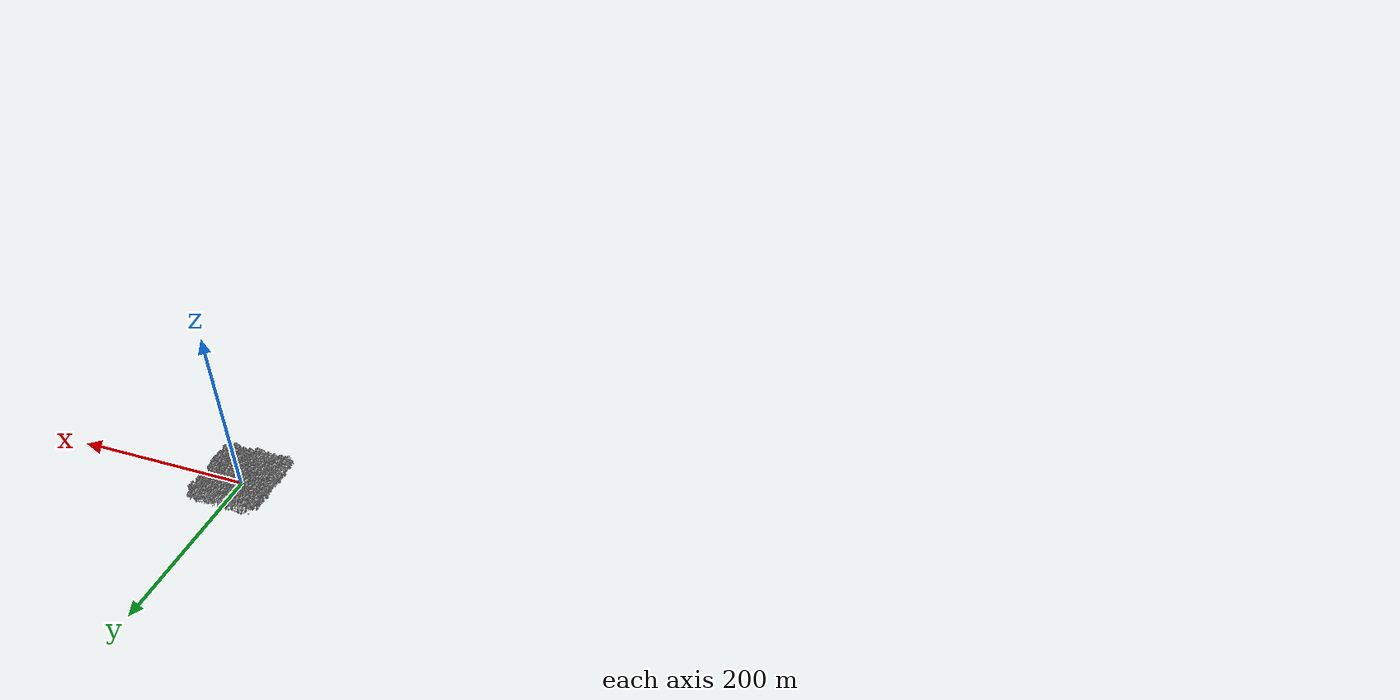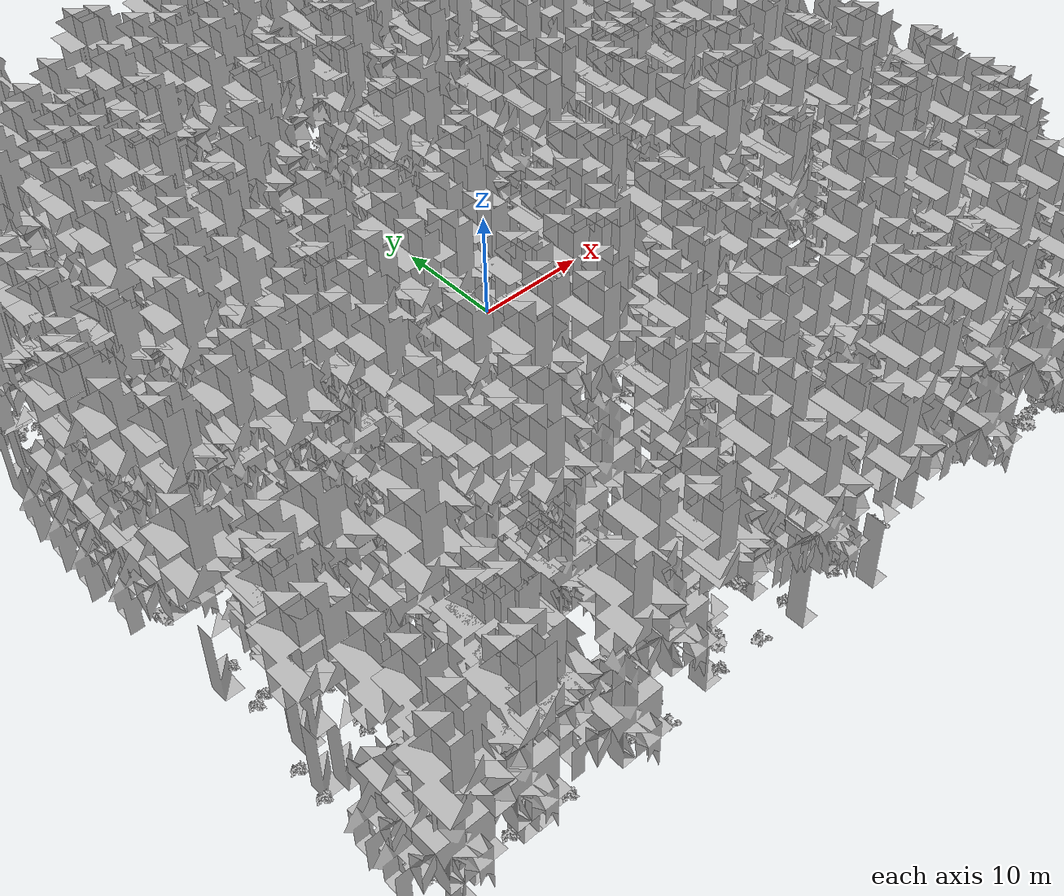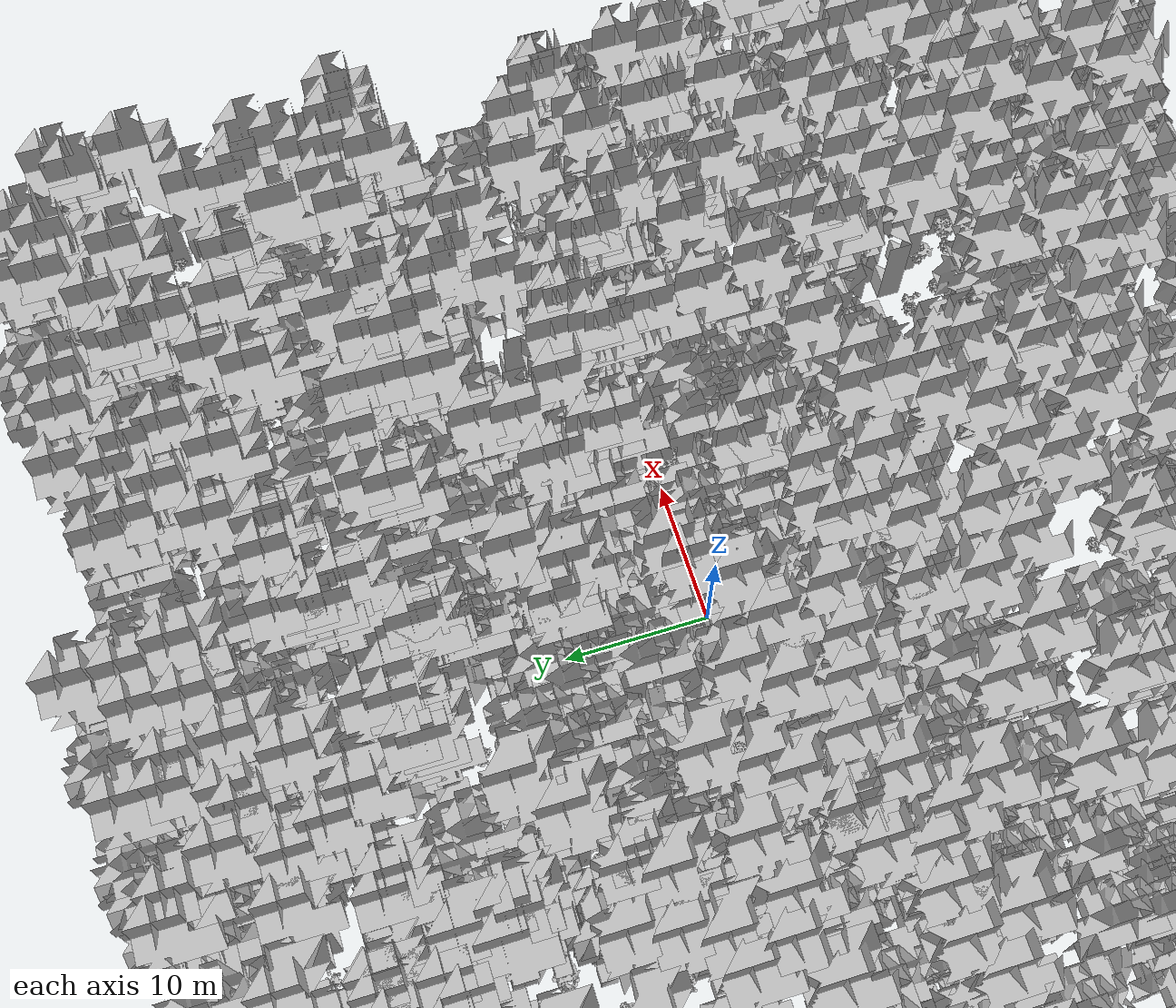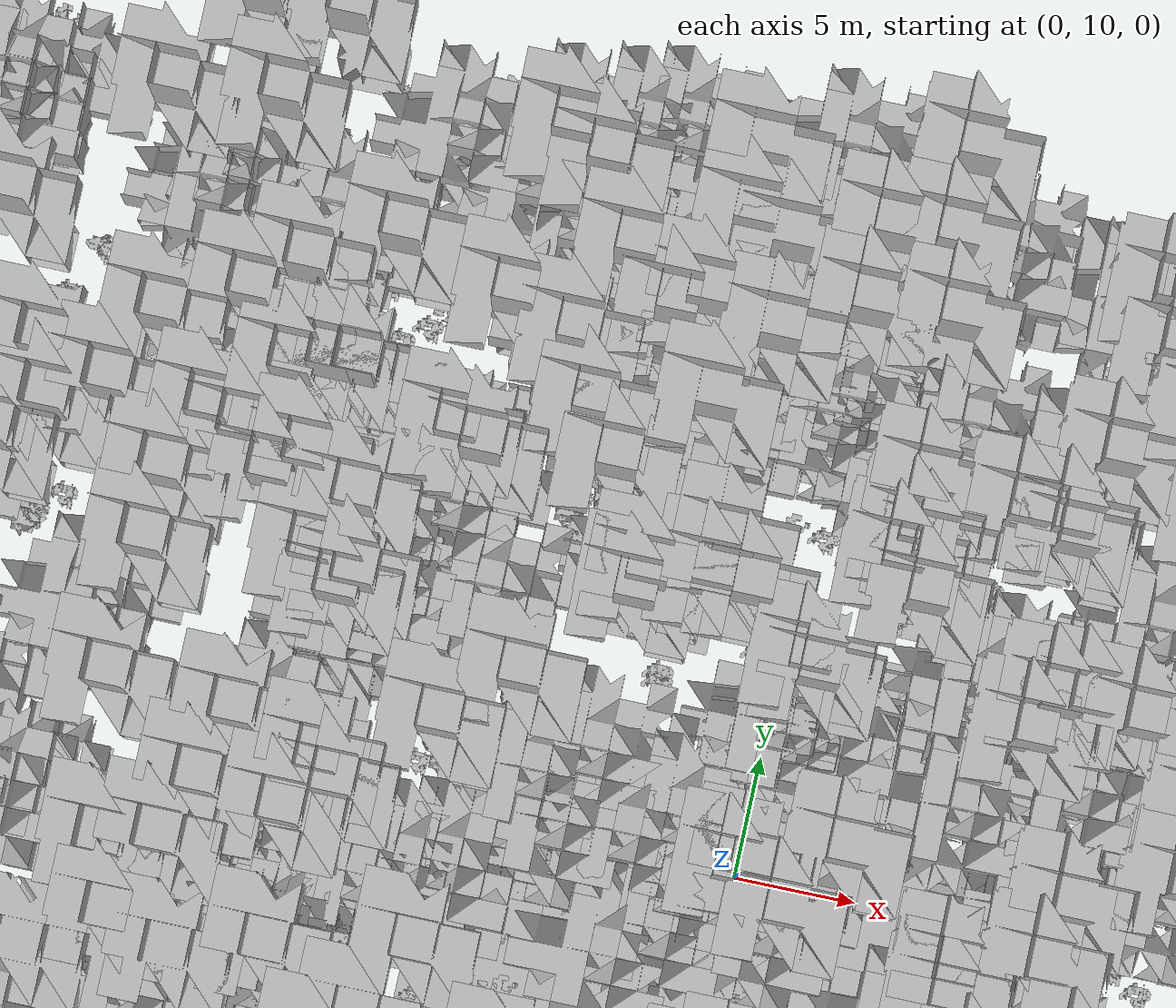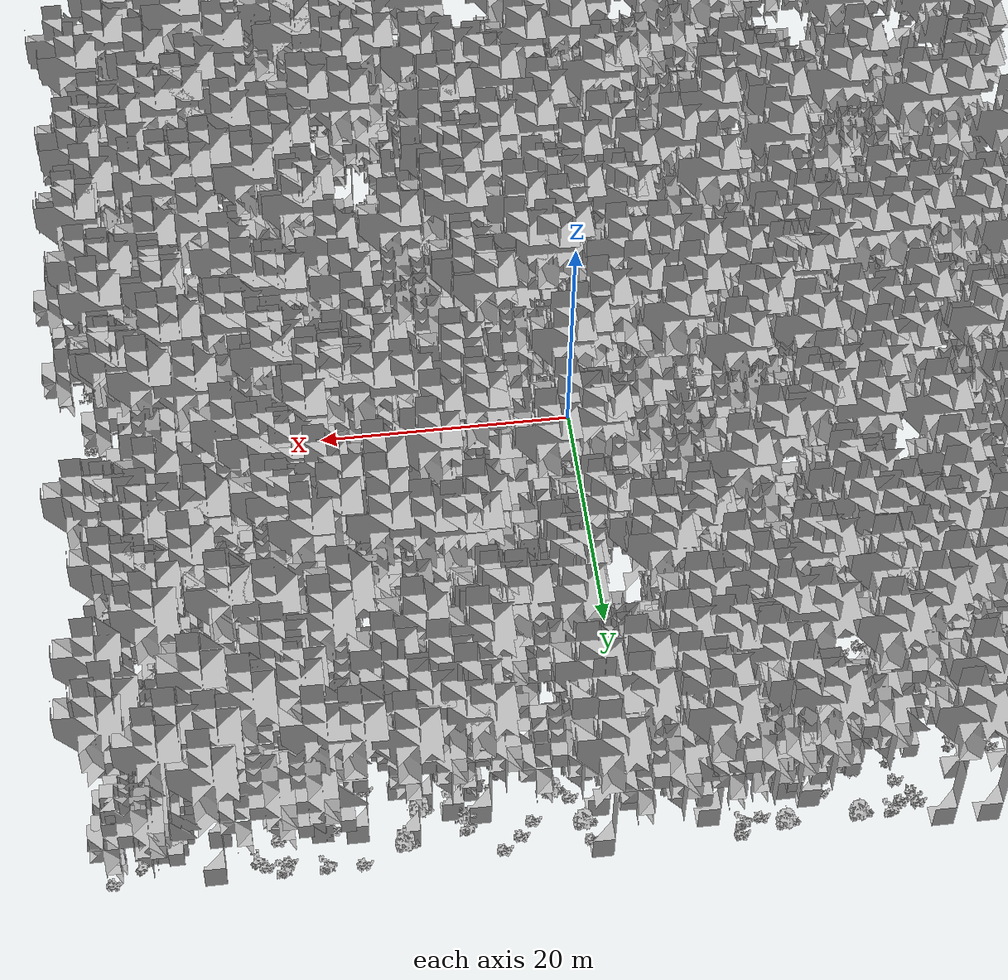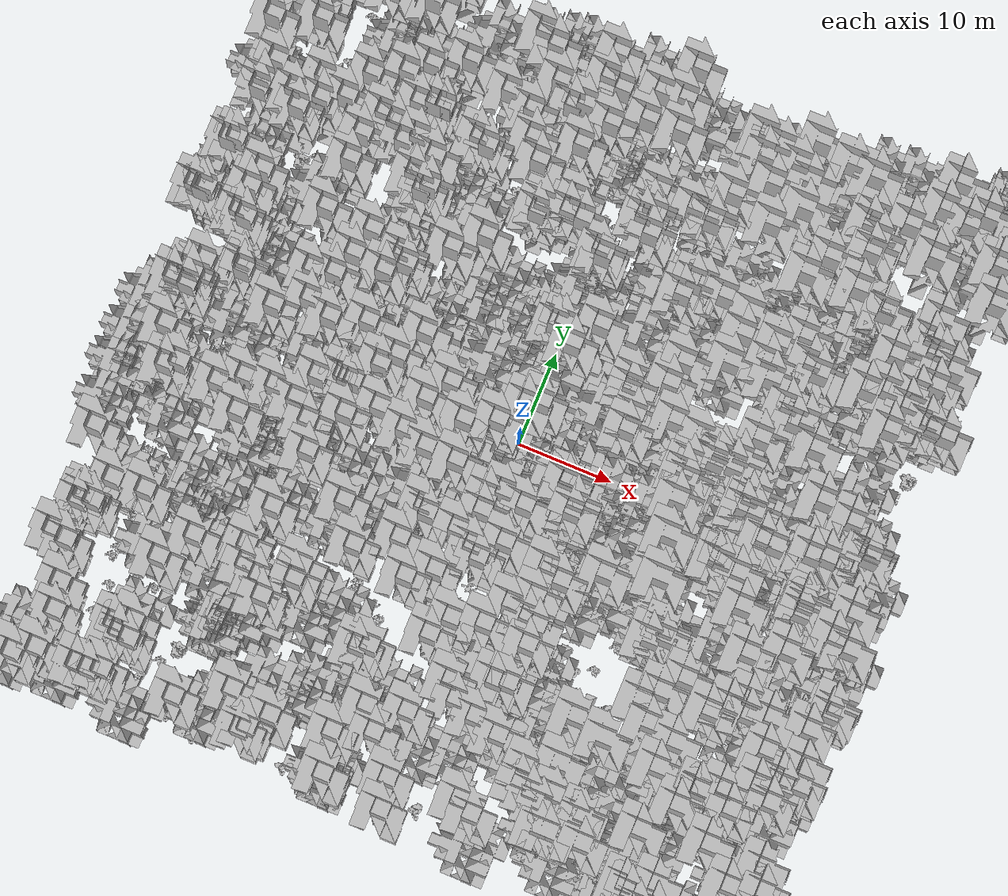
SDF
<sdf version="1.7">
    <world name="default">
        <plugin name="mrs_gazebo_static_transform_republisher_plugin" filename="libMrsGazeboCommonResources_StaticTransformRepublisher.so"/>
        <spherical_coordinates>
            <surface_model>EARTH_WGS84</surface_model>
            <latitude_deg>47.3977</latitude_deg>
            <longitude_deg>8.54559</longitude_deg>
            <elevation>0</elevation>
            <heading_deg>0</heading_deg>
        </spherical_coordinates>
        <physics name="default_physics" default="0" type="ode">
            <ode>
                <solver>
                    <type>quick</type>
                    <iters>10</iters>
                    <sor>1.3</sor>
                    <use_dynamic_moi_rescaling>0</use_dynamic_moi_rescaling>
                </solver>
                <constraints>
                    <cfm>0</cfm>
                    <erp>0.2</erp>
                    <contact_max_correcting_vel>1000</contact_max_correcting_vel>
                    <contact_surface_layer>0.001</contact_surface_layer>
                </constraints>
            </ode>
            <max_step_size>0.004</max_step_size>
            <real_time_factor>1</real_time_factor>
            <real_time_update_rate>250</real_time_update_rate>
        </physics>
        <scene>
            <shadows>0</shadows>
            <ambient>0.4 0.4 0.4 1</ambient>
            <background>0.7 0.7 0.7 1</background>
        </scene>
        <light name="sun" type="directional">
            <pose>0 0 1000 0.4 0.2 0</pose>
            <diffuse>1 1 1 1</diffuse>
            <specular>0.6 0.6 0.6 1</specular>
            <direction>0.1 0.1 -0.9</direction>
            <attenuation>
                <range>20</range>
                <constant>0.5</constant>
                <linear>0.01</linear>
                <quadratic>0.001</quadratic>
            </attenuation>
            <cast_shadows>1</cast_shadows>
            <spot>
                <inner_angle>0</inner_angle>
                <outer_angle>0</outer_angle>
                <falloff>0</falloff>
            </spot>
        </light>
        <model name="ground_plane">
            <static>1</static>
            <link name="link">
                <collision name="collision">
                    <pose>-50 0 0 0 -0 0</pose>
                    <geometry>
                        <plane>
                            <normal>0 0 1</normal>
                            <size>80 80</size>
                        </plane>
                    </geometry>
                    <surface>
                        <contact>
                            <ode>
                                <min_depth>0.01</min_depth>
                                <max_vel>0</max_vel>
                            </ode>
                        </contact>
                        <friction>
                            <ode/>
                            <torsional>
                                <ode/>
                            </torsional>
                        </friction>
                        <bounce/>
                    </surface>
                    <max_contacts>10</max_contacts>
                </collision>
                <visual name="grass">
                    <pose>0 0 0 0 -0 0</pose>
                    <cast_shadows>0</cast_shadows>
                    <geometry>
                        <mesh>
                            <scale>0.46714285714285714 0.46714285714285714 0.1</scale>
                            <uri>file://grass_plane/meshes/grass_plane.dae</uri>
                        </mesh>
                    </geometry>
                </visual>
                <self_collide>0</self_collide>
                <enable_wind>0</enable_wind>
                <kinematic>0</kinematic>
            </link>
        </model>
        <model name="the_void">
            <static>1</static>
            <link name="link">
                <pose>0 0 0.1 0 -0 0</pose>
                <visual name="the_void">
                    <pose>0 0 2 0 -0 0</pose>
                    <geometry>
                        <sphere>
                            <radius>0.25</radius>
                        </sphere>
                    </geometry>
                    <material>
                        <script>
                            <uri>file://media/materials/scripts/Gazebo.material</uri>
                            <name>Gazebo/Black</name>
                        </script>
                    </material>
                </visual>
                <self_collide>0</self_collide>
                <enable_wind>0</enable_wind>
                <kinematic>0</kinematic>
            </link>
            <pose>-1000 -1000 0 0 -0 0</pose>
        </model>
        <gui fullscreen="0">
            <camera name="camera">
                <pose>35.1577 98.6044 40.0204 0 0.407996 -1.99761</pose>
                <view_controller>orbit</view_controller>
                <projection_type>perspective</projection_type>
            </camera>
        </gui>
        <plugin name="mrs_gazebo_rviz_cam_synchronizer" filename="libMrsGazeboCommonResources_RvizCameraSynchronizer.so">
            <target_frame_id>gazebo_user_camera</target_frame_id>
            <world_origin_frame_id>uav1/gps_origin</world_origin_frame_id>
            <frame_to_follow>uav1</frame_to_follow>
        </plugin>
        <gravity>0 0 -9.8066</gravity>
        <magnetic_field>6e-06 2.3e-05 -4.2e-05</magnetic_field>
        <atmosphere type="adiabatic"/>
        <wind/>
        <model name="Tree 0">
            <static>1</static>
            <pose>1.1159811965153565 -13.89830316631869 0 1.57079 -0 0</pose>
            <link name="link">
                <pose>0 0 0 0 -0 0</pose>
                <collision name="collision">
                    <geometry>
                        <mesh>
                            <scale>3.5 5 3.5</scale>
                            <uri>model://tree_9/meshes/tree_9.obj</uri>
                        </mesh>
                    </geometry>
                    <max_contacts>10</max_contacts>
                    <surface>
                        <contact>
                            <ode/>
                        </contact>
                        <bounce/>
                        <friction>
                            <torsional>
                                <ode/>
                            </torsional>
                            <ode/>
                        </friction>
                    </surface>
                </collision>
                <visual name="visual">
                    <geometry>
                        <mesh>
                            <scale>3.5 5 3.5</scale>
                            <uri>model://tree_9/meshes/tree_9.obj</uri>
                        </mesh>
                    </geometry>
                </visual>
                <self_collide>0</self_collide>
                <enable_wind>0</enable_wind>
                <kinematic>0</kinematic>
            </link>
        </model>
        <model name="Tree 1">
            <static>1</static>
            <pose>-20.00631564012497 -21.219108205197983 0 1.57079 -0 0</pose>
            <link name="link">
                <pose>0 0 0 0 -0 0</pose>
                <collision name="collision">
                    <geometry>
                        <mesh>
                            <scale>3.5 5 3.5</scale>
                            <uri>model://tree_9/meshes/tree_9.obj</uri>
                        </mesh>
                    </geometry>
                    <max_contacts>10</max_contacts>
                    <surface>
                        <contact>
                            <ode/>
                        </contact>
                        <bounce/>
                        <friction>
                            <torsional>
                                <ode/>
                            </torsional>
                            <ode/>
                        </friction>
                    </surface>
                </collision>
                <visual name="visual">
                    <geometry>
                        <mesh>
                            <scale>3.5 5 3.5</scale>
                            <uri>model://tree_9/meshes/tree_9.obj</uri>
                        </mesh>
                    </geometry>
                </visual>
                <self_collide>0</self_collide>
                <enable_wind>0</enable_wind>
                <kinematic>0</kinematic>
            </link>
        </model>
        <model name="Tree 2">
            <static>1</static>
            <pose>21.608973467380785 -35.33875538457476 0 1.57079 -0 0</pose>
            <link name="link">
                <pose>0 0 0 0 -0 0</pose>
                <collision name="collision">
                    <geometry>
                        <mesh>
                            <scale>3.5 5 3.5</scale>
                            <uri>model://tree_2/meshes/tree_2.obj</uri>
                        </mesh>
                    </geometry>
                    <max_contacts>10</max_contacts>
                    <surface>
                        <contact>
                            <ode/>
                        </contact>
                        <bounce/>
                        <friction>
                            <torsional>
                                <ode/>
                            </torsional>
                            <ode/>
                        </friction>
                    </surface>
                </collision>
                <visual name="visual">
                    <geometry>
                        <mesh>
                            <scale>3.5 5 3.5</scale>
                            <uri>model://tree_2/meshes/tree_2.obj</uri>
                        </mesh>
                    </geometry>
                </visual>
                <self_collide>0</self_collide>
                <enable_wind>0</enable_wind>
                <kinematic>0</kinematic>
            </link>
        </model>
        <model name="Tree 3">
            <static>1</static>
            <pose>-35.58539830558576 -5.026673597463727 0 1.57079 -0 0</pose>
            <link name="link">
                <pose>0 0 0 0 -0 0</pose>
                <collision name="collision">
                    <geometry>
                        <mesh>
                            <scale>3.5 5 3.5</scale>
                            <uri>model://tree_2/meshes/tree_2.obj</uri>
                        </mesh>
                    </geometry>
                    <max_contacts>10</max_contacts>
                    <surface>
                        <contact>
                            <ode/>
                        </contact>
                        <bounce/>
                        <friction>
                            <torsional>
                                <ode/>
                            </torsional>
                            <ode/>
                        </friction>
                    </surface>
                </collision>
                <visual name="visual">
                    <geometry>
                        <mesh>
                            <scale>3.5 5 3.5</scale>
                            <uri>model://tree_2/meshes/tree_2.obj</uri>
                        </mesh>
                    </geometry>
                </visual>
                <self_collide>0</self_collide>
                <enable_wind>0</enable_wind>
                <kinematic>0</kinematic>
            </link>
        </model>
        <model name="Tree 4">
            <static>1</static>
            <pose>-24.714150679845652 26.503433685469645 0 1.57079 -0 0</pose>
            <link name="link">
                <pose>0 0 0 0 -0 0</pose>
                <collision name="collision">
                    <geometry>
                        <mesh>
                            <scale>3.5 5 3.5</scale>
                            <uri>model://tree_2/meshes/tree_2.obj</uri>
                        </mesh>
                    </geometry>
                    <max_contacts>10</max_contacts>
                    <surface>
                        <contact>
                            <ode/>
                        </contact>
                        <bounce/>
                        <friction>
                            <torsional>
                                <ode/>
                            </torsional>
                            <ode/>
                        </friction>
                    </surface>
                </collision>
                <visual name="visual">
                    <geometry>
                        <mesh>
                            <scale>3.5 5 3.5</scale>
                            <uri>model://tree_2/meshes/tree_2.obj</uri>
                        </mesh>
                    </geometry>
                </visual>
                <self_collide>0</self_collide>
                <enable_wind>0</enable_wind>
                <kinematic>0</kinematic>
            </link>
        </model>
        <model name="Tree 5">
            <static>1</static>
            <pose>35.85761464989527 18.543120433513458 0 1.57079 -0 0</pose>
            <link name="link">
                <pose>0 0 0 0 -0 0</pose>
                <collision name="collision">
                    <geometry>
                        <mesh>
                            <scale>3.5 5 3.5</scale>
                            <uri>model://tree_9/meshes/tree_9.obj</uri>
                        </mesh>
                    </geometry>
                    <max_contacts>10</max_contacts>
                    <surface>
                        <contact>
                            <ode/>
                        </contact>
                        <bounce/>
                        <friction>
                            <torsional>
                                <ode/>
                            </torsional>
                            <ode/>
                        </friction>
                    </surface>
                </collision>
                <visual name="visual">
                    <geometry>
                        <mesh>
                            <scale>3.5 5 3.5</scale>
                            <uri>model://tree_9/meshes/tree_9.obj</uri>
                        </mesh>
                    </geometry>
                </visual>
                <self_collide>0</self_collide>
                <enable_wind>0</enable_wind>
                <kinematic>0</kinematic>
            </link>
        </model>
        <model name="Tree 6">
            <static>1</static>
            <pose>5.54850643241091 36.19368127252207 0 1.57079 -0 0</pose>
            <link name="link">
                <pose>0 0 0 0 -0 0</pose>
                <collision name="collision">
                    <geometry>
                        <mesh>
                            <scale>3.5 5 3.5</scale>
                            <uri>model://tree_2/meshes/tree_2.obj</uri>
                        </mesh>
                    </geometry>
                    <max_contacts>10</max_contacts>
                    <surface>
                        <contact>
                            <ode/>
                        </contact>
                        <bounce/>
                        <friction>
                            <torsional>
                                <ode/>
                            </torsional>
                            <ode/>
                        </friction>
                    </surface>
                </collision>
                <visual name="visual">
                    <geometry>
                        <mesh>
                            <scale>3.5 5 3.5</scale>
                            <uri>model://tree_2/meshes/tree_2.obj</uri>
                        </mesh>
                    </geometry>
                </visual>
                <self_collide>0</self_collide>
                <enable_wind>0</enable_wind>
                <kinematic>0</kinematic>
            </link>
        </model>
        <model name="Tree 7">
            <static>1</static>
            <pose>-4.427250663453513 -5.980754278815311 0 1.57079 -0 0</pose>
            <link name="link">
                <pose>0 0 0 0 -0 0</pose>
                <collision name="collision">
                    <geometry>
                        <mesh>
                            <scale>3.5 5 3.5</scale>
                            <uri>model://tree_9/meshes/tree_9.obj</uri>
                        </mesh>
                    </geometry>
                    <max_contacts>10</max_contacts>
                    <surface>
                        <contact>
                            <ode/>
                        </contact>
                        <bounce/>
                        <friction>
                            <torsional>
                                <ode/>
                            </torsional>
                            <ode/>
                        </friction>
                    </surface>
                </collision>
                <visual name="visual">
                    <geometry>
                        <mesh>
                            <scale>3.5 5 3.5</scale>
                            <uri>model://tree_9/meshes/tree_9.obj</uri>
                        </mesh>
                    </geometry>
                </visual>
                <self_collide>0</self_collide>
                <enable_wind>0</enable_wind>
                <kinematic>0</kinematic>
            </link>
        </model>
        <model name="Tree 8">
            <static>1</static>
            <pose>-37.42893679536673 24.60667967422893 0 1.57079 -0 0</pose>
            <link name="link">
                <pose>0 0 0 0 -0 0</pose>
                <collision name="collision">
                    <geometry>
                        <mesh>
                            <scale>3.5 5 3.5</scale>
                            <uri>model://tree_2/meshes/tree_2.obj</uri>
                        </mesh>
                    </geometry>
                    <max_contacts>10</max_contacts>
                    <surface>
                        <contact>
                            <ode/>
                        </contact>
                        <bounce/>
                        <friction>
                            <torsional>
                                <ode/>
                            </torsional>
                            <ode/>
                        </friction>
                    </surface>
                </collision>
                <visual name="visual">
                    <geometry>
                        <mesh>
                            <scale>3.5 5 3.5</scale>
                            <uri>model://tree_2/meshes/tree_2.obj</uri>
                        </mesh>
                    </geometry>
                </visual>
                <self_collide>0</self_collide>
                <enable_wind>0</enable_wind>
                <kinematic>0</kinematic>
            </link>
        </model>
        <model name="Tree 9">
            <static>1</static>
            <pose>-20.22070959237376 -10.405079638997606 0 1.57079 -0 0</pose>
            <link name="link">
                <pose>0 0 0 0 -0 0</pose>
                <collision name="collision">
                    <geometry>
                        <mesh>
                            <scale>3.5 5 3.5</scale>
                            <uri>model://tree_2/meshes/tree_2.obj</uri>
                        </mesh>
                    </geometry>
                    <max_contacts>10</max_contacts>
                    <surface>
                        <contact>
                            <ode/>
                        </contact>
                        <bounce/>
                        <friction>
                            <torsional>
                                <ode/>
                            </torsional>
                            <ode/>
                        </friction>
                    </surface>
                </collision>
                <visual name="visual">
                    <geometry>
                        <mesh>
                            <scale>3.5 5 3.5</scale>
                            <uri>model://tree_2/meshes/tree_2.obj</uri>
                        </mesh>
                    </geometry>
                </visual>
                <self_collide>0</self_collide>
                <enable_wind>0</enable_wind>
                <kinematic>0</kinematic>
            </link>
        </model>
        <model name="Tree 10">
            <static>1</static>
            <pose>-27.402453264470722 -25.61623942738576 0 1.57079 -0 0</pose>
            <link name="link">
                <pose>0 0 0 0 -0 0</pose>
                <collision name="collision">
                    <geometry>
                        <mesh>
                            <scale>3.5 5 3.5</scale>
                            <uri>model://tree_9/meshes/tree_9.obj</uri>
                        </mesh>
                    </geometry>
                    <max_contacts>10</max_contacts>
                    <surface>
                        <contact>
                            <ode/>
                        </contact>
                        <bounce/>
                        <friction>
                            <torsional>
                                <ode/>
                            </torsional>
                            <ode/>
                        </friction>
                    </surface>
                </collision>
                <visual name="visual">
                    <geometry>
                        <mesh>
                            <scale>3.5 5 3.5</scale>
                            <uri>model://tree_9/meshes/tree_9.obj</uri>
                        </mesh>
                    </geometry>
                </visual>
                <self_collide>0</self_collide>
                <enable_wind>0</enable_wind>
                <kinematic>0</kinematic>
            </link>
        </model>
        <model name="Tree 11">
            <static>1</static>
            <pose>36.81946621899988 -17.252960299036893 0 1.57079 -0 0</pose>
            <link name="link">
                <pose>0 0 0 0 -0 0</pose>
                <collision name="collision">
                    <geometry>
                        <mesh>
                            <scale>3.5 5 3.5</scale>
                            <uri>model://tree_9/meshes/tree_9.obj</uri>
                        </mesh>
                    </geometry>
                    <max_contacts>10</max_contacts>
                    <surface>
                        <contact>
                            <ode/>
                        </contact>
                        <bounce/>
                        <friction>
                            <torsional>
                                <ode/>
                            </torsional>
                            <ode/>
                        </friction>
                    </surface>
                </collision>
                <visual name="visual">
                    <geometry>
                        <mesh>
                            <scale>3.5 5 3.5</scale>
                            <uri>model://tree_9/meshes/tree_9.obj</uri>
                        </mesh>
                    </geometry>
                </visual>
                <self_collide>0</self_collide>
                <enable_wind>0</enable_wind>
                <kinematic>0</kinematic>
            </link>
        </model>
        <model name="Tree 12">
            <static>1</static>
            <pose>6.2903916896166905 -32.05651221572814 0 1.57079 -0 0</pose>
            <link name="link">
                <pose>0 0 0 0 -0 0</pose>
                <collision name="collision">
                    <geometry>
                        <mesh>
                            <scale>3.5 5 3.5</scale>
                            <uri>model://tree_2/meshes/tree_2.obj</uri>
                        </mesh>
                    </geometry>
                    <max_contacts>10</max_contacts>
                    <surface>
                        <contact>
                            <ode/>
                        </contact>
                        <bounce/>
                        <friction>
                            <torsional>
                                <ode/>
                            </torsional>
                            <ode/>
                        </friction>
                    </surface>
                </collision>
                <visual name="visual">
                    <geometry>
                        <mesh>
                            <scale>3.5 5 3.5</scale>
                            <uri>model://tree_2/meshes/tree_2.obj</uri>
                        </mesh>
                    </geometry>
                </visual>
                <self_collide>0</self_collide>
                <enable_wind>0</enable_wind>
                <kinematic>0</kinematic>
            </link>
        </model>
        <model name="Tree 13">
            <static>1</static>
            <pose>9.448481958813034 19.72214087842748 0 1.57079 -0 0</pose>
            <link name="link">
                <pose>0 0 0 0 -0 0</pose>
                <collision name="collision">
                    <geometry>
                        <mesh>
                            <scale>3.5 5 3.5</scale>
                            <uri>model://tree_2/meshes/tree_2.obj</uri>
                        </mesh>
                    </geometry>
                    <max_contacts>10</max_contacts>
                    <surface>
                        <contact>
                            <ode/>
                        </contact>
                        <bounce/>
                        <friction>
                            <torsional>
                                <ode/>
                            </torsional>
                            <ode/>
                        </friction>
                    </surface>
                </collision>
                <visual name="visual">
                    <geometry>
                        <mesh>
                            <scale>3.5 5 3.5</scale>
                            <uri>model://tree_2/meshes/tree_2.obj</uri>
                        </mesh>
                    </geometry>
                </visual>
                <self_collide>0</self_collide>
                <enable_wind>0</enable_wind>
                <kinematic>0</kinematic>
            </link>
        </model>
        <model name="Tree 14">
            <static>1</static>
            <pose>-5.477188524623877 -34.77827628285769 0 1.57079 -0 0</pose>
            <link name="link">
                <pose>0 0 0 0 -0 0</pose>
                <collision name="collision">
                    <geometry>
                        <mesh>
                            <scale>3.5 5 3.5</scale>
                            <uri>model://tree_9/meshes/tree_9.obj</uri>
                        </mesh>
                    </geometry>
                    <max_contacts>10</max_contacts>
                    <surface>
                        <contact>
                            <ode/>
                        </contact>
                        <bounce/>
                        <friction>
                            <torsional>
                                <ode/>
                            </torsional>
                            <ode/>
                        </friction>
                    </surface>
                </collision>
                <visual name="visual">
                    <geometry>
                        <mesh>
                            <scale>3.5 5 3.5</scale>
                            <uri>model://tree_9/meshes/tree_9.obj</uri>
                        </mesh>
                    </geometry>
                </visual>
                <self_collide>0</self_collide>
                <enable_wind>0</enable_wind>
                <kinematic>0</kinematic>
            </link>
        </model>
        <model name="Tree 15">
            <static>1</static>
            <pose>-8.292715532854295 24.661213749309667 0 1.57079 -0 0</pose>
            <link name="link">
                <pose>0 0 0 0 -0 0</pose>
                <collision name="collision">
                    <geometry>
                        <mesh>
                            <scale>3.5 5 3.5</scale>
                            <uri>model://tree_9/meshes/tree_9.obj</uri>
                        </mesh>
                    </geometry>
                    <max_contacts>10</max_contacts>
                    <surface>
                        <contact>
                            <ode/>
                        </contact>
                        <bounce/>
                        <friction>
                            <torsional>
                                <ode/>
                            </torsional>
                            <ode/>
                        </friction>
                    </surface>
                </collision>
                <visual name="visual">
                    <geometry>
                        <mesh>
                            <scale>3.5 5 3.5</scale>
                            <uri>model://tree_9/meshes/tree_9.obj</uri>
                        </mesh>
                    </geometry>
                </visual>
                <self_collide>0</self_collide>
                <enable_wind>0</enable_wind>
                <kinematic>0</kinematic>
            </link>
        </model>
        <model name="Tree 16">
            <static>1</static>
            <pose>-5.256447903502242 -5.490356725233795 0 1.57079 -0 0</pose>
            <link name="link">
                <pose>0 0 0 0 -0 0</pose>
                <collision name="collision">
                    <geometry>
                        <mesh>
                            <scale>3.5 5 3.5</scale>
                            <uri>model://tree_2/meshes/tree_2.obj</uri>
                        </mesh>
                    </geometry>
                    <max_contacts>10</max_contacts>
                    <surface>
                        <contact>
                            <ode/>
                        </contact>
                        <bounce/>
                        <friction>
                            <torsional>
                                <ode/>
                            </torsional>
                            <ode/>
                        </friction>
                    </surface>
                </collision>
                <visual name="visual">
                    <geometry>
                        <mesh>
                            <scale>3.5 5 3.5</scale>
                            <uri>model://tree_2/meshes/tree_2.obj</uri>
                        </mesh>
                    </geometry>
                </visual>
                <self_collide>0</self_collide>
                <enable_wind>0</enable_wind>
                <kinematic>0</kinematic>
            </link>
        </model>
        <model name="Tree 17">
            <static>1</static>
            <pose>12.373503499018454 11.518207295434493 0 1.57079 -0 0</pose>
            <link name="link">
                <pose>0 0 0 0 -0 0</pose>
                <collision name="collision">
                    <geometry>
                        <mesh>
                            <scale>3.5 5 3.5</scale>
                            <uri>model://tree_9/meshes/tree_9.obj</uri>
                        </mesh>
                    </geometry>
                    <max_contacts>10</max_contacts>
                    <surface>
                        <contact>
                            <ode/>
                        </contact>
                        <bounce/>
                        <friction>
                            <torsional>
                                <ode/>
                            </torsional>
                            <ode/>
                        </friction>
                    </surface>
                </collision>
                <visual name="visual">
                    <geometry>
                        <mesh>
                            <scale>3.5 5 3.5</scale>
                            <uri>model://tree_9/meshes/tree_9.obj</uri>
                        </mesh>
                    </geometry>
                </visual>
                <self_collide>0</self_collide>
                <enable_wind>0</enable_wind>
                <kinematic>0</kinematic>
            </link>
        </model>
        <model name="Tree 18">
            <static>1</static>
            <pose>-17.58918415399928 3.471792968988524 0 1.57079 -0 0</pose>
            <link name="link">
                <pose>0 0 0 0 -0 0</pose>
                <collision name="collision">
                    <geometry>
                        <mesh>
                            <scale>3.5 5 3.5</scale>
                            <uri>model://tree_9/meshes/tree_9.obj</uri>
                        </mesh>
                    </geometry>
                    <max_contacts>10</max_contacts>
                    <surface>
                        <contact>
                            <ode/>
                        </contact>
                        <bounce/>
                        <friction>
                            <torsional>
                                <ode/>
                            </torsional>
                            <ode/>
                        </friction>
                    </surface>
                </collision>
                <visual name="visual">
                    <geometry>
                        <mesh>
                            <scale>3.5 5 3.5</scale>
                            <uri>model://tree_9/meshes/tree_9.obj</uri>
                        </mesh>
                    </geometry>
                </visual>
                <self_collide>0</self_collide>
                <enable_wind>0</enable_wind>
                <kinematic>0</kinematic>
            </link>
        </model>
        <model name="Tree 19">
            <static>1</static>
            <pose>-18.112532954256856 8.733711655006111 0 1.57079 -0 0</pose>
            <link name="link">
                <pose>0 0 0 0 -0 0</pose>
                <collision name="collision">
                    <geometry>
                        <mesh>
                            <scale>3.5 5 3.5</scale>
                            <uri>model://tree_9/meshes/tree_9.obj</uri>
                        </mesh>
                    </geometry>
                    <max_contacts>10</max_contacts>
                    <surface>
                        <contact>
                            <ode/>
                        </contact>
                        <bounce/>
                        <friction>
                            <torsional>
                                <ode/>
                            </torsional>
                            <ode/>
                        </friction>
                    </surface>
                </collision>
                <visual name="visual">
                    <geometry>
                        <mesh>
                            <scale>3.5 5 3.5</scale>
                            <uri>model://tree_9/meshes/tree_9.obj</uri>
                        </mesh>
                    </geometry>
                </visual>
                <self_collide>0</self_collide>
                <enable_wind>0</enable_wind>
                <kinematic>0</kinematic>
            </link>
        </model>
        <model name="Tree 20">
            <static>1</static>
            <pose>-10.212879514915599 29.72032840404134 0 1.57079 -0 0</pose>
            <link name="link">
                <pose>0 0 0 0 -0 0</pose>
                <collision name="collision">
                    <geometry>
                        <mesh>
                            <scale>3.5 5 3.5</scale>
                            <uri>model://tree_2/meshes/tree_2.obj</uri>
                        </mesh>
                    </geometry>
                    <max_contacts>10</max_contacts>
                    <surface>
                        <contact>
                            <ode/>
                        </contact>
                        <bounce/>
                        <friction>
                            <torsional>
                                <ode/>
                            </torsional>
                            <ode/>
                        </friction>
                    </surface>
                </collision>
                <visual name="visual">
                    <geometry>
                        <mesh>
                            <scale>3.5 5 3.5</scale>
                            <uri>model://tree_2/meshes/tree_2.obj</uri>
                        </mesh>
                    </geometry>
                </visual>
                <self_collide>0</self_collide>
                <enable_wind>0</enable_wind>
                <kinematic>0</kinematic>
            </link>
        </model>
        <model name="Tree 21">
            <static>1</static>
            <pose>-37.792176039891544 9.493826799292847 0 1.57079 -0 0</pose>
            <link name="link">
                <pose>0 0 0 0 -0 0</pose>
                <collision name="collision">
                    <geometry>
                        <mesh>
                            <scale>3.5 5 3.5</scale>
                            <uri>model://tree_9/meshes/tree_9.obj</uri>
                        </mesh>
                    </geometry>
                    <max_contacts>10</max_contacts>
                    <surface>
                        <contact>
                            <ode/>
                        </contact>
                        <bounce/>
                        <friction>
                            <torsional>
                                <ode/>
                            </torsional>
                            <ode/>
                        </friction>
                    </surface>
                </collision>
                <visual name="visual">
                    <geometry>
                        <mesh>
                            <scale>3.5 5 3.5</scale>
                            <uri>model://tree_9/meshes/tree_9.obj</uri>
                        </mesh>
                    </geometry>
                </visual>
                <self_collide>0</self_collide>
                <enable_wind>0</enable_wind>
                <kinematic>0</kinematic>
            </link>
        </model>
        <model name="Tree 22">
            <static>1</static>
            <pose>-37.28646639435578 15.146930245264471 0 1.57079 -0 0</pose>
            <link name="link">
                <pose>0 0 0 0 -0 0</pose>
                <collision name="collision">
                    <geometry>
                        <mesh>
                            <scale>3.5 5 3.5</scale>
                            <uri>model://tree_9/meshes/tree_9.obj</uri>
                        </mesh>
                    </geometry>
                    <max_contacts>10</max_contacts>
                    <surface>
                        <contact>
                            <ode/>
                        </contact>
                        <bounce/>
                        <friction>
                            <torsional>
                                <ode/>
                            </torsional>
                            <ode/>
                        </friction>
                    </surface>
                </collision>
                <visual name="visual">
                    <geometry>
                        <mesh>
                            <scale>3.5 5 3.5</scale>
                            <uri>model://tree_9/meshes/tree_9.obj</uri>
                        </mesh>
                    </geometry>
                </visual>
                <self_collide>0</self_collide>
                <enable_wind>0</enable_wind>
                <kinematic>0</kinematic>
            </link>
        </model>
        <model name="Tree 23">
            <static>1</static>
            <pose>-27.310515965870678 14.904951473053679 0 1.57079 -0 0</pose>
            <link name="link">
                <pose>0 0 0 0 -0 0</pose>
                <collision name="collision">
                    <geometry>
                        <mesh>
                            <scale>3.5 5 3.5</scale>
                            <uri>model://tree_2/meshes/tree_2.obj</uri>
                        </mesh>
                    </geometry>
                    <max_contacts>10</max_contacts>
                    <surface>
                        <contact>
                            <ode/>
                        </contact>
                        <bounce/>
                        <friction>
                            <torsional>
                                <ode/>
                            </torsional>
                            <ode/>
                        </friction>
                    </surface>
                </collision>
                <visual name="visual">
                    <geometry>
                        <mesh>
                            <scale>3.5 5 3.5</scale>
                            <uri>model://tree_2/meshes/tree_2.obj</uri>
                        </mesh>
                    </geometry>
                </visual>
                <self_collide>0</self_collide>
                <enable_wind>0</enable_wind>
                <kinematic>0</kinematic>
            </link>
        </model>
        <model name="Tree 24">
            <static>1</static>
            <pose>34.144390346652955 24.84890358442013 0 1.57079 -0 0</pose>
            <link name="link">
                <pose>0 0 0 0 -0 0</pose>
                <collision name="collision">
                    <geometry>
                        <mesh>
                            <scale>3.5 5 3.5</scale>
                            <uri>model://tree_9/meshes/tree_9.obj</uri>
                        </mesh>
                    </geometry>
                    <max_contacts>10</max_contacts>
                    <surface>
                        <contact>
                            <ode/>
                        </contact>
                        <bounce/>
                        <friction>
                            <torsional>
                                <ode/>
                            </torsional>
                            <ode/>
                        </friction>
                    </surface>
                </collision>
                <visual name="visual">
                    <geometry>
                        <mesh>
                            <scale>3.5 5 3.5</scale>
                            <uri>model://tree_9/meshes/tree_9.obj</uri>
                        </mesh>
                    </geometry>
                </visual>
                <self_collide>0</self_collide>
                <enable_wind>0</enable_wind>
                <kinematic>0</kinematic>
            </link>
        </model>
        <model name="Tree 25">
            <static>1</static>
            <pose>15.556397853560355 34.013811529760744 0 1.57079 -0 0</pose>
            <link name="link">
                <pose>0 0 0 0 -0 0</pose>
                <collision name="collision">
                    <geometry>
                        <mesh>
                            <scale>3.5 5 3.5</scale>
                            <uri>model://tree_9/meshes/tree_9.obj</uri>
                        </mesh>
                    </geometry>
                    <max_contacts>10</max_contacts>
                    <surface>
                        <contact>
                            <ode/>
                        </contact>
                        <bounce/>
                        <friction>
                            <torsional>
                                <ode/>
                            </torsional>
                            <ode/>
                        </friction>
                    </surface>
                </collision>
                <visual name="visual">
                    <geometry>
                        <mesh>
                            <scale>3.5 5 3.5</scale>
                            <uri>model://tree_9/meshes/tree_9.obj</uri>
                        </mesh>
                    </geometry>
                </visual>
                <self_collide>0</self_collide>
                <enable_wind>0</enable_wind>
                <kinematic>0</kinematic>
            </link>
        </model>
        <model name="Tree 26">
            <static>1</static>
            <pose>0.13318210508983697 -13.030593485971256 0 1.57079 -0 0</pose>
            <link name="link">
                <pose>0 0 0 0 -0 0</pose>
                <collision name="collision">
                    <geometry>
                        <mesh>
                            <scale>3.5 5 3.5</scale>
                            <uri>model://tree_9/meshes/tree_9.obj</uri>
                        </mesh>
                    </geometry>
                    <max_contacts>10</max_contacts>
                    <surface>
                        <contact>
                            <ode/>
                        </contact>
                        <bounce/>
                        <friction>
                            <torsional>
                                <ode/>
                            </torsional>
                            <ode/>
                        </friction>
                    </surface>
                </collision>
                <visual name="visual">
                    <geometry>
                        <mesh>
                            <scale>3.5 5 3.5</scale>
                            <uri>model://tree_9/meshes/tree_9.obj</uri>
                        </mesh>
                    </geometry>
                </visual>
                <self_collide>0</self_collide>
                <enable_wind>0</enable_wind>
                <kinematic>0</kinematic>
            </link>
        </model>
        <model name="Tree 27">
            <static>1</static>
            <pose>-19.1331456412655 -16.951237500059335 0 1.57079 -0 0</pose>
            <link name="link">
                <pose>0 0 0 0 -0 0</pose>
                <collision name="collision">
                    <geometry>
                        <mesh>
                            <scale>3.5 5 3.5</scale>
                            <uri>model://tree_9/meshes/tree_9.obj</uri>
                        </mesh>
                    </geometry>
                    <max_contacts>10</max_contacts>
                    <surface>
                        <contact>
                            <ode/>
                        </contact>
                        <bounce/>
                        <friction>
                            <torsional>
                                <ode/>
                            </torsional>
                            <ode/>
                        </friction>
                    </surface>
                </collision>
                <visual name="visual">
                    <geometry>
                        <mesh>
                            <scale>3.5 5 3.5</scale>
                            <uri>model://tree_9/meshes/tree_9.obj</uri>
                        </mesh>
                    </geometry>
                </visual>
                <self_collide>0</self_collide>
                <enable_wind>0</enable_wind>
                <kinematic>0</kinematic>
            </link>
        </model>
        <model name="Tree 28">
            <static>1</static>
            <pose>-11.109174213286632 7.824460218635878 0 1.57079 -0 0</pose>
            <link name="link">
                <pose>0 0 0 0 -0 0</pose>
                <collision name="collision">
                    <geometry>
                        <mesh>
                            <scale>3.5 5 3.5</scale>
                            <uri>model://tree_2/meshes/tree_2.obj</uri>
                        </mesh>
                    </geometry>
                    <max_contacts>10</max_contacts>
                    <surface>
                        <contact>
                            <ode/>
                        </contact>
                        <bounce/>
                        <friction>
                            <torsional>
                                <ode/>
                            </torsional>
                            <ode/>
                        </friction>
                    </surface>
                </collision>
                <visual name="visual">
                    <geometry>
                        <mesh>
                            <scale>3.5 5 3.5</scale>
                            <uri>model://tree_2/meshes/tree_2.obj</uri>
                        </mesh>
                    </geometry>
                </visual>
                <self_collide>0</self_collide>
                <enable_wind>0</enable_wind>
                <kinematic>0</kinematic>
            </link>
        </model>
        <model name="Tree 29">
            <static>1</static>
            <pose>0.2843903582047531 35.689766550181815 0 1.57079 -0 0</pose>
            <link name="link">
                <pose>0 0 0 0 -0 0</pose>
                <collision name="collision">
                    <geometry>
                        <mesh>
                            <scale>3.5 5 3.5</scale>
                            <uri>model://tree_9/meshes/tree_9.obj</uri>
                        </mesh>
                    </geometry>
                    <max_contacts>10</max_contacts>
                    <surface>
                        <contact>
                            <ode/>
                        </contact>
                        <bounce/>
                        <friction>
                            <torsional>
                                <ode/>
                            </torsional>
                            <ode/>
                        </friction>
                    </surface>
                </collision>
                <visual name="visual">
                    <geometry>
                        <mesh>
                            <scale>3.5 5 3.5</scale>
                            <uri>model://tree_9/meshes/tree_9.obj</uri>
                        </mesh>
                    </geometry>
                </visual>
                <self_collide>0</self_collide>
                <enable_wind>0</enable_wind>
                <kinematic>0</kinematic>
            </link>
        </model>
        <model name="Tree 30">
            <static>1</static>
            <pose>-34.59250229024043 17.583544439943438 0 1.57079 -0 0</pose>
            <link name="link">
                <pose>0 0 0 0 -0 0</pose>
                <collision name="collision">
                    <geometry>
                        <mesh>
                            <scale>3.5 5 3.5</scale>
                            <uri>model://tree_2/meshes/tree_2.obj</uri>
                        </mesh>
                    </geometry>
                    <max_contacts>10</max_contacts>
                    <surface>
                        <contact>
                            <ode/>
                        </contact>
                        <bounce/>
                        <friction>
                            <torsional>
                                <ode/>
                            </torsional>
                            <ode/>
                        </friction>
                    </surface>
                </collision>
                <visual name="visual">
                    <geometry>
                        <mesh>
                            <scale>3.5 5 3.5</scale>
                            <uri>model://tree_2/meshes/tree_2.obj</uri>
                        </mesh>
                    </geometry>
                </visual>
                <self_collide>0</self_collide>
                <enable_wind>0</enable_wind>
                <kinematic>0</kinematic>
            </link>
        </model>
        <model name="Tree 31">
            <static>1</static>
            <pose>-23.559283238357317 -5.882718172223704 0 1.57079 -0 0</pose>
            <link name="link">
                <pose>0 0 0 0 -0 0</pose>
                <collision name="collision">
                    <geometry>
                        <mesh>
                            <scale>3.5 5 3.5</scale>
                            <uri>model://tree_9/meshes/tree_9.obj</uri>
                        </mesh>
                    </geometry>
                    <max_contacts>10</max_contacts>
                    <surface>
                        <contact>
                            <ode/>
                        </contact>
                        <bounce/>
                        <friction>
                            <torsional>
                                <ode/>
                            </torsional>
                            <ode/>
                        </friction>
                    </surface>
                </collision>
                <visual name="visual">
                    <geometry>
                        <mesh>
                            <scale>3.5 5 3.5</scale>
                            <uri>model://tree_9/meshes/tree_9.obj</uri>
                        </mesh>
                    </geometry>
                </visual>
                <self_collide>0</self_collide>
                <enable_wind>0</enable_wind>
                <kinematic>0</kinematic>
            </link>
        </model>
        <model name="Tree 32">
            <static>1</static>
            <pose>-31.09887542613032 4.177149169723151 0 1.57079 -0 0</pose>
            <link name="link">
                <pose>0 0 0 0 -0 0</pose>
                <collision name="collision">
                    <geometry>
                        <mesh>
                            <scale>3.5 5 3.5</scale>
                            <uri>model://tree_9/meshes/tree_9.obj</uri>
                        </mesh>
                    </geometry>
                    <max_contacts>10</max_contacts>
                    <surface>
                        <contact>
                            <ode/>
                        </contact>
                        <bounce/>
                        <friction>
                            <torsional>
                                <ode/>
                            </torsional>
                            <ode/>
                        </friction>
                    </surface>
                </collision>
                <visual name="visual">
                    <geometry>
                        <mesh>
                            <scale>3.5 5 3.5</scale>
                            <uri>model://tree_9/meshes/tree_9.obj</uri>
                        </mesh>
                    </geometry>
                </visual>
                <self_collide>0</self_collide>
                <enable_wind>0</enable_wind>
                <kinematic>0</kinematic>
            </link>
        </model>
        <model name="Tree 33">
            <static>1</static>
            <pose>-20.10717213867828 -3.379073356409677 0 1.57079 -0 0</pose>
            <link name="link">
                <pose>0 0 0 0 -0 0</pose>
                <collision name="collision">
                    <geometry>
                        <mesh>
                            <scale>3.5 5 3.5</scale>
                            <uri>model://tree_9/meshes/tree_9.obj</uri>
                        </mesh>
                    </geometry>
                    <max_contacts>10</max_contacts>
                    <surface>
                        <contact>
                            <ode/>
                        </contact>
                        <bounce/>
                        <friction>
                            <torsional>
                                <ode/>
                            </torsional>
                            <ode/>
                        </friction>
                    </surface>
                </collision>
                <visual name="visual">
                    <geometry>
                        <mesh>
                            <scale>3.5 5 3.5</scale>
                            <uri>model://tree_9/meshes/tree_9.obj</uri>
                        </mesh>
                    </geometry>
                </visual>
                <self_collide>0</self_collide>
                <enable_wind>0</enable_wind>
                <kinematic>0</kinematic>
            </link>
        </model>
        <model name="Tree 34">
            <static>1</static>
            <pose>4.085883050414772 -19.612352335270362 0 1.57079 -0 0</pose>
            <link name="link">
                <pose>0 0 0 0 -0 0</pose>
                <collision name="collision">
                    <geometry>
                        <mesh>
                            <scale>3.5 5 3.5</scale>
                            <uri>model://tree_9/meshes/tree_9.obj</uri>
                        </mesh>
                    </geometry>
                    <max_contacts>10</max_contacts>
                    <surface>
                        <contact>
                            <ode/>
                        </contact>
                        <bounce/>
                        <friction>
                            <torsional>
                                <ode/>
                            </torsional>
                            <ode/>
                        </friction>
                    </surface>
                </collision>
                <visual name="visual">
                    <geometry>
                        <mesh>
                            <scale>3.5 5 3.5</scale>
                            <uri>model://tree_9/meshes/tree_9.obj</uri>
                        </mesh>
                    </geometry>
                </visual>
                <self_collide>0</self_collide>
                <enable_wind>0</enable_wind>
                <kinematic>0</kinematic>
            </link>
        </model>
        <model name="Tree 35">
            <static>1</static>
            <pose>-28.815637526900268 -33.09232623328406 0 1.57079 -0 0</pose>
            <link name="link">
                <pose>0 0 0 0 -0 0</pose>
                <collision name="collision">
                    <geometry>
                        <mesh>
                            <scale>3.5 5 3.5</scale>
                            <uri>model://tree_9/meshes/tree_9.obj</uri>
                        </mesh>
                    </geometry>
                    <max_contacts>10</max_contacts>
                    <surface>
                        <contact>
                            <ode/>
                        </contact>
                        <bounce/>
                        <friction>
                            <torsional>
                                <ode/>
                            </torsional>
                            <ode/>
                        </friction>
                    </surface>
                </collision>
                <visual name="visual">
                    <geometry>
                        <mesh>
                            <scale>3.5 5 3.5</scale>
                            <uri>model://tree_9/meshes/tree_9.obj</uri>
                        </mesh>
                    </geometry>
                </visual>
                <self_collide>0</self_collide>
                <enable_wind>0</enable_wind>
                <kinematic>0</kinematic>
            </link>
        </model>
        <model name="Tree 36">
            <static>1</static>
            <pose>37.544806985473684 -8.624954095828592 0 1.57079 -0 0</pose>
            <link name="link">
                <pose>0 0 0 0 -0 0</pose>
                <collision name="collision">
                    <geometry>
                        <mesh>
                            <scale>3.5 5 3.5</scale>
                            <uri>model://tree_9/meshes/tree_9.obj</uri>
                        </mesh>
                    </geometry>
                    <max_contacts>10</max_contacts>
                    <surface>
                        <contact>
                            <ode/>
                        </contact>
                        <bounce/>
                        <friction>
                            <torsional>
                                <ode/>
                            </torsional>
                            <ode/>
                        </friction>
                    </surface>
                </collision>
                <visual name="visual">
                    <geometry>
                        <mesh>
                            <scale>3.5 5 3.5</scale>
                            <uri>model://tree_9/meshes/tree_9.obj</uri>
                        </mesh>
                    </geometry>
                </visual>
                <self_collide>0</self_collide>
                <enable_wind>0</enable_wind>
                <kinematic>0</kinematic>
            </link>
        </model>
        <model name="Tree 37">
            <static>1</static>
            <pose>-37.80069444212614 -26.999605459145144 0 1.57079 -0 0</pose>
            <link name="link">
                <pose>0 0 0 0 -0 0</pose>
                <collision name="collision">
                    <geometry>
                        <mesh>
                            <scale>3.5 5 3.5</scale>
                            <uri>model://tree_9/meshes/tree_9.obj</uri>
                        </mesh>
                    </geometry>
                    <max_contacts>10</max_contacts>
                    <surface>
                        <contact>
                            <ode/>
                        </contact>
                        <bounce/>
                        <friction>
                            <torsional>
                                <ode/>
                            </torsional>
                            <ode/>
                        </friction>
                    </surface>
                </collision>
                <visual name="visual">
                    <geometry>
                        <mesh>
                            <scale>3.5 5 3.5</scale>
                            <uri>model://tree_9/meshes/tree_9.obj</uri>
                        </mesh>
                    </geometry>
                </visual>
                <self_collide>0</self_collide>
                <enable_wind>0</enable_wind>
                <kinematic>0</kinematic>
            </link>
        </model>
        <model name="Tree 38">
            <static>1</static>
            <pose>-36.57298107803156 -0.4002440459340306 0 1.57079 -0 0</pose>
            <link name="link">
                <pose>0 0 0 0 -0 0</pose>
                <collision name="collision">
                    <geometry>
                        <mesh>
                            <scale>3.5 5 3.5</scale>
                            <uri>model://tree_2/meshes/tree_2.obj</uri>
                        </mesh>
                    </geometry>
                    <max_contacts>10</max_contacts>
                    <surface>
                        <contact>
                            <ode/>
                        </contact>
                        <bounce/>
                        <friction>
                            <torsional>
                                <ode/>
                            </torsional>
                            <ode/>
                        </friction>
                    </surface>
                </collision>
                <visual name="visual">
                    <geometry>
                        <mesh>
                            <scale>3.5 5 3.5</scale>
                            <uri>model://tree_2/meshes/tree_2.obj</uri>
                        </mesh>
                    </geometry>
                </visual>
                <self_collide>0</self_collide>
                <enable_wind>0</enable_wind>
                <kinematic>0</kinematic>
            </link>
        </model>
        <model name="Tree 39">
            <static>1</static>
            <pose>-27.742781516711503 -31.20521073867753 0 1.57079 -0 0</pose>
            <link name="link">
                <pose>0 0 0 0 -0 0</pose>
                <collision name="collision">
                    <geometry>
                        <mesh>
                            <scale>3.5 5 3.5</scale>
                            <uri>model://tree_2/meshes/tree_2.obj</uri>
                        </mesh>
                    </geometry>
                    <max_contacts>10</max_contacts>
                    <surface>
                        <contact>
                            <ode/>
                        </contact>
                        <bounce/>
                        <friction>
                            <torsional>
                                <ode/>
                            </torsional>
                            <ode/>
                        </friction>
                    </surface>
                </collision>
                <visual name="visual">
                    <geometry>
                        <mesh>
                            <scale>3.5 5 3.5</scale>
                            <uri>model://tree_2/meshes/tree_2.obj</uri>
                        </mesh>
                    </geometry>
                </visual>
                <self_collide>0</self_collide>
                <enable_wind>0</enable_wind>
                <kinematic>0</kinematic>
            </link>
        </model>
        <model name="Tree 40">
            <static>1</static>
            <pose>-3.3557278795785948 -16.876541399602438 0 1.57079 -0 0</pose>
            <link name="link">
                <pose>0 0 0 0 -0 0</pose>
                <collision name="collision">
                    <geometry>
                        <mesh>
                            <scale>3.5 5 3.5</scale>
                            <uri>model://tree_2/meshes/tree_2.obj</uri>
                        </mesh>
                    </geometry>
                    <max_contacts>10</max_contacts>
                    <surface>
                        <contact>
                            <ode/>
                        </contact>
                        <bounce/>
                        <friction>
                            <torsional>
                                <ode/>
                            </torsional>
                            <ode/>
                        </friction>
                    </surface>
                </collision>
                <visual name="visual">
                    <geometry>
                        <mesh>
                            <scale>3.5 5 3.5</scale>
                            <uri>model://tree_2/meshes/tree_2.obj</uri>
                        </mesh>
                    </geometry>
                </visual>
                <self_collide>0</self_collide>
                <enable_wind>0</enable_wind>
                <kinematic>0</kinematic>
            </link>
        </model>
        <model name="Tree 41">
            <static>1</static>
            <pose>24.913338707268096 15.43348912980732 0 1.57079 -0 0</pose>
            <link name="link">
                <pose>0 0 0 0 -0 0</pose>
                <collision name="collision">
                    <geometry>
                        <mesh>
                            <scale>3.5 5 3.5</scale>
                            <uri>model://tree_9/meshes/tree_9.obj</uri>
                        </mesh>
                    </geometry>
                    <max_contacts>10</max_contacts>
                    <surface>
                        <contact>
                            <ode/>
                        </contact>
                        <bounce/>
                        <friction>
                            <torsional>
                                <ode/>
                            </torsional>
                            <ode/>
                        </friction>
                    </surface>
                </collision>
                <visual name="visual">
                    <geometry>
                        <mesh>
                            <scale>3.5 5 3.5</scale>
                            <uri>model://tree_9/meshes/tree_9.obj</uri>
                        </mesh>
                    </geometry>
                </visual>
                <self_collide>0</self_collide>
                <enable_wind>0</enable_wind>
                <kinematic>0</kinematic>
            </link>
        </model>
        <model name="Tree 42">
            <static>1</static>
            <pose>37.536779501781254 -31.169941421875713 0 1.57079 -0 0</pose>
            <link name="link">
                <pose>0 0 0 0 -0 0</pose>
                <collision name="collision">
                    <geometry>
                        <mesh>
                            <scale>3.5 5 3.5</scale>
                            <uri>model://tree_9/meshes/tree_9.obj</uri>
                        </mesh>
                    </geometry>
                    <max_contacts>10</max_contacts>
                    <surface>
                        <contact>
                            <ode/>
                        </contact>
                        <bounce/>
                        <friction>
                            <torsional>
                                <ode/>
                            </torsional>
                            <ode/>
                        </friction>
                    </surface>
                </collision>
                <visual name="visual">
                    <geometry>
                        <mesh>
                            <scale>3.5 5 3.5</scale>
                            <uri>model://tree_9/meshes/tree_9.obj</uri>
                        </mesh>
                    </geometry>
                </visual>
                <self_collide>0</self_collide>
                <enable_wind>0</enable_wind>
                <kinematic>0</kinematic>
            </link>
        </model>
        <model name="Tree 43">
            <static>1</static>
            <pose>21.734284206595447 26.603632758605613 0 1.57079 -0 0</pose>
            <link name="link">
                <pose>0 0 0 0 -0 0</pose>
                <collision name="collision">
                    <geometry>
                        <mesh>
                            <scale>3.5 5 3.5</scale>
                            <uri>model://tree_9/meshes/tree_9.obj</uri>
                        </mesh>
                    </geometry>
                    <max_contacts>10</max_contacts>
                    <surface>
                        <contact>
                            <ode/>
                        </contact>
                        <bounce/>
                        <friction>
                            <torsional>
                                <ode/>
                            </torsional>
                            <ode/>
                        </friction>
                    </surface>
                </collision>
                <visual name="visual">
                    <geometry>
                        <mesh>
                            <scale>3.5 5 3.5</scale>
                            <uri>model://tree_9/meshes/tree_9.obj</uri>
                        </mesh>
                    </geometry>
                </visual>
                <self_collide>0</self_collide>
                <enable_wind>0</enable_wind>
                <kinematic>0</kinematic>
            </link>
        </model>
        <model name="Tree 44">
            <static>1</static>
            <pose>10.714253786453092 28.930514521983653 0 1.57079 -0 0</pose>
            <link name="link">
                <pose>0 0 0 0 -0 0</pose>
                <collision name="collision">
                    <geometry>
                        <mesh>
                            <scale>3.5 5 3.5</scale>
                            <uri>model://tree_9/meshes/tree_9.obj</uri>
                        </mesh>
                    </geometry>
                    <max_contacts>10</max_contacts>
                    <surface>
                        <contact>
                            <ode/>
                        </contact>
                        <bounce/>
                        <friction>
                            <torsional>
                                <ode/>
                            </torsional>
                            <ode/>
                        </friction>
                    </surface>
                </collision>
                <visual name="visual">
                    <geometry>
                        <mesh>
                            <scale>3.5 5 3.5</scale>
                            <uri>model://tree_9/meshes/tree_9.obj</uri>
                        </mesh>
                    </geometry>
                </visual>
                <self_collide>0</self_collide>
                <enable_wind>0</enable_wind>
                <kinematic>0</kinematic>
            </link>
        </model>
        <model name="Tree 45">
            <static>1</static>
            <pose>15.191166597170394 27.550827886717457 0 1.57079 -0 0</pose>
            <link name="link">
                <pose>0 0 0 0 -0 0</pose>
                <collision name="collision">
                    <geometry>
                        <mesh>
                            <scale>3.5 5 3.5</scale>
                            <uri>model://tree_9/meshes/tree_9.obj</uri>
                        </mesh>
                    </geometry>
                    <max_contacts>10</max_contacts>
                    <surface>
                        <contact>
                            <ode/>
                        </contact>
                        <bounce/>
                        <friction>
                            <torsional>
                                <ode/>
                            </torsional>
                            <ode/>
                        </friction>
                    </surface>
                </collision>
                <visual name="visual">
                    <geometry>
                        <mesh>
                            <scale>3.5 5 3.5</scale>
                            <uri>model://tree_9/meshes/tree_9.obj</uri>
                        </mesh>
                    </geometry>
                </visual>
                <self_collide>0</self_collide>
                <enable_wind>0</enable_wind>
                <kinematic>0</kinematic>
            </link>
        </model>
        <model name="Tree 46">
            <static>1</static>
            <pose>-6.92544637372642 31.137719801433093 0 1.57079 -0 0</pose>
            <link name="link">
                <pose>0 0 0 0 -0 0</pose>
                <collision name="collision">
                    <geometry>
                        <mesh>
                            <scale>3.5 5 3.5</scale>
                            <uri>model://tree_2/meshes/tree_2.obj</uri>
                        </mesh>
                    </geometry>
                    <max_contacts>10</max_contacts>
                    <surface>
                        <contact>
                            <ode/>
                        </contact>
                        <bounce/>
                        <friction>
                            <torsional>
                                <ode/>
                            </torsional>
                            <ode/>
                        </friction>
                    </surface>
                </collision>
                <visual name="visual">
                    <geometry>
                        <mesh>
                            <scale>3.5 5 3.5</scale>
                            <uri>model://tree_2/meshes/tree_2.obj</uri>
                        </mesh>
                    </geometry>
                </visual>
                <self_collide>0</self_collide>
                <enable_wind>0</enable_wind>
                <kinematic>0</kinematic>
            </link>
        </model>
        <model name="Tree 47">
            <static>1</static>
            <pose>25.869457155707735 -37.62644119133291 0 1.57079 -0 0</pose>
            <link name="link">
                <pose>0 0 0 0 -0 0</pose>
                <collision name="collision">
                    <geometry>
                        <mesh>
                            <scale>3.5 5 3.5</scale>
                            <uri>model://tree_9/meshes/tree_9.obj</uri>
                        </mesh>
                    </geometry>
                    <max_contacts>10</max_contacts>
                    <surface>
                        <contact>
                            <ode/>
                        </contact>
                        <bounce/>
                        <friction>
                            <torsional>
                                <ode/>
                            </torsional>
                            <ode/>
                        </friction>
                    </surface>
                </collision>
                <visual name="visual">
                    <geometry>
                        <mesh>
                            <scale>3.5 5 3.5</scale>
                            <uri>model://tree_9/meshes/tree_9.obj</uri>
                        </mesh>
                    </geometry>
                </visual>
                <self_collide>0</self_collide>
                <enable_wind>0</enable_wind>
                <kinematic>0</kinematic>
            </link>
        </model>
        <model name="Tree 48">
            <static>1</static>
            <pose>37.71561775441853 -20.682305624079724 0 1.57079 -0 0</pose>
            <link name="link">
                <pose>0 0 0 0 -0 0</pose>
                <collision name="collision">
                    <geometry>
                        <mesh>
                            <scale>3.5 5 3.5</scale>
                            <uri>model://tree_9/meshes/tree_9.obj</uri>
                        </mesh>
                    </geometry>
                    <max_contacts>10</max_contacts>
                    <surface>
                        <contact>
                            <ode/>
                        </contact>
                        <bounce/>
                        <friction>
                            <torsional>
                                <ode/>
                            </torsional>
                            <ode/>
                        </friction>
                    </surface>
                </collision>
                <visual name="visual">
                    <geometry>
                        <mesh>
                            <scale>3.5 5 3.5</scale>
                            <uri>model://tree_9/meshes/tree_9.obj</uri>
                        </mesh>
                    </geometry>
                </visual>
                <self_collide>0</self_collide>
                <enable_wind>0</enable_wind>
                <kinematic>0</kinematic>
            </link>
        </model>
        <model name="Tree 49">
            <static>1</static>
            <pose>18.14145185257452 -8.94248721823707 0 1.57079 -0 0</pose>
            <link name="link">
                <pose>0 0 0 0 -0 0</pose>
                <collision name="collision">
                    <geometry>
                        <mesh>
                            <scale>3.5 5 3.5</scale>
                            <uri>model://tree_9/meshes/tree_9.obj</uri>
                        </mesh>
                    </geometry>
                    <max_contacts>10</max_contacts>
                    <surface>
                        <contact>
                            <ode/>
                        </contact>
                        <bounce/>
                        <friction>
                            <torsional>
                                <ode/>
                            </torsional>
                            <ode/>
                        </friction>
                    </surface>
                </collision>
                <visual name="visual">
                    <geometry>
                        <mesh>
                            <scale>3.5 5 3.5</scale>
                            <uri>model://tree_9/meshes/tree_9.obj</uri>
                        </mesh>
                    </geometry>
                </visual>
                <self_collide>0</self_collide>
                <enable_wind>0</enable_wind>
                <kinematic>0</kinematic>
            </link>
        </model>
        <model name="Tree 50">
            <static>1</static>
            <pose>23.375432868031204 -17.47456077057759 0 1.57079 -0 0</pose>
            <link name="link">
                <pose>0 0 0 0 -0 0</pose>
                <collision name="collision">
                    <geometry>
                        <mesh>
                            <scale>3.5 5 3.5</scale>
                            <uri>model://tree_2/meshes/tree_2.obj</uri>
                        </mesh>
                    </geometry>
                    <max_contacts>10</max_contacts>
                    <surface>
                        <contact>
                            <ode/>
                        </contact>
                        <bounce/>
                        <friction>
                            <torsional>
                                <ode/>
                            </torsional>
                            <ode/>
                        </friction>
                    </surface>
                </collision>
                <visual name="visual">
                    <geometry>
                        <mesh>
                            <scale>3.5 5 3.5</scale>
                            <uri>model://tree_2/meshes/tree_2.obj</uri>
                        </mesh>
                    </geometry>
                </visual>
                <self_collide>0</self_collide>
                <enable_wind>0</enable_wind>
                <kinematic>0</kinematic>
            </link>
        </model>
        <model name="Tree 51">
            <static>1</static>
            <pose>-10.229346671937382 -31.95085222240828 0 1.57079 -0 0</pose>
            <link name="link">
                <pose>0 0 0 0 -0 0</pose>
                <collision name="collision">
                    <geometry>
                        <mesh>
                            <scale>3.5 5 3.5</scale>
                            <uri>model://tree_2/meshes/tree_2.obj</uri>
                        </mesh>
                    </geometry>
                    <max_contacts>10</max_contacts>
                    <surface>
                        <contact>
                            <ode/>
                        </contact>
                        <bounce/>
                        <friction>
                            <torsional>
                                <ode/>
                            </torsional>
                            <ode/>
                        </friction>
                    </surface>
                </collision>
                <visual name="visual">
                    <geometry>
                        <mesh>
                            <scale>3.5 5 3.5</scale>
                            <uri>model://tree_2/meshes/tree_2.obj</uri>
                        </mesh>
                    </geometry>
                </visual>
                <self_collide>0</self_collide>
                <enable_wind>0</enable_wind>
                <kinematic>0</kinematic>
            </link>
        </model>
        <model name="Tree 52">
            <static>1</static>
            <pose>-18.159195509183068 -10.569485854259277 0 1.57079 -0 0</pose>
            <link name="link">
                <pose>0 0 0 0 -0 0</pose>
                <collision name="collision">
                    <geometry>
                        <mesh>
                            <scale>3.5 5 3.5</scale>
                            <uri>model://tree_9/meshes/tree_9.obj</uri>
                        </mesh>
                    </geometry>
                    <max_contacts>10</max_contacts>
                    <surface>
                        <contact>
                            <ode/>
                        </contact>
                        <bounce/>
                        <friction>
                            <torsional>
                                <ode/>
                            </torsional>
                            <ode/>
                        </friction>
                    </surface>
                </collision>
                <visual name="visual">
                    <geometry>
                        <mesh>
                            <scale>3.5 5 3.5</scale>
                            <uri>model://tree_9/meshes/tree_9.obj</uri>
                        </mesh>
                    </geometry>
                </visual>
                <self_collide>0</self_collide>
                <enable_wind>0</enable_wind>
                <kinematic>0</kinematic>
            </link>
        </model>
        <model name="Tree 53">
            <static>1</static>
            <pose>4.311095297616639 23.943461254721335 0 1.57079 -0 0</pose>
            <link name="link">
                <pose>0 0 0 0 -0 0</pose>
                <collision name="collision">
                    <geometry>
                        <mesh>
                            <scale>3.5 5 3.5</scale>
                            <uri>model://tree_9/meshes/tree_9.obj</uri>
                        </mesh>
                    </geometry>
                    <max_contacts>10</max_contacts>
                    <surface>
                        <contact>
                            <ode/>
                        </contact>
                        <bounce/>
                        <friction>
                            <torsional>
                                <ode/>
                            </torsional>
                            <ode/>
                        </friction>
                    </surface>
                </collision>
                <visual name="visual">
                    <geometry>
                        <mesh>
                            <scale>3.5 5 3.5</scale>
                            <uri>model://tree_9/meshes/tree_9.obj</uri>
                        </mesh>
                    </geometry>
                </visual>
                <self_collide>0</self_collide>
                <enable_wind>0</enable_wind>
                <kinematic>0</kinematic>
            </link>
        </model>
        <model name="Tree 54">
            <static>1</static>
            <pose>28.354117974586543 21.354500607505457 0 1.57079 -0 0</pose>
            <link name="link">
                <pose>0 0 0 0 -0 0</pose>
                <collision name="collision">
                    <geometry>
                        <mesh>
                            <scale>3.5 5 3.5</scale>
                            <uri>model://tree_2/meshes/tree_2.obj</uri>
                        </mesh>
                    </geometry>
                    <max_contacts>10</max_contacts>
                    <surface>
                        <contact>
                            <ode/>
                        </contact>
                        <bounce/>
                        <friction>
                            <torsional>
                                <ode/>
                            </torsional>
                            <ode/>
                        </friction>
                    </surface>
                </collision>
                <visual name="visual">
                    <geometry>
                        <mesh>
                            <scale>3.5 5 3.5</scale>
                            <uri>model://tree_2/meshes/tree_2.obj</uri>
                        </mesh>
                    </geometry>
                </visual>
                <self_collide>0</self_collide>
                <enable_wind>0</enable_wind>
                <kinematic>0</kinematic>
            </link>
        </model>
        <model name="Tree 55">
            <static>1</static>
            <pose>11.675304233040045 -29.8565511561692 0 1.57079 -0 0</pose>
            <link name="link">
                <pose>0 0 0 0 -0 0</pose>
                <collision name="collision">
                    <geometry>
                        <mesh>
                            <scale>3.5 5 3.5</scale>
                            <uri>model://tree_2/meshes/tree_2.obj</uri>
                        </mesh>
                    </geometry>
                    <max_contacts>10</max_contacts>
                    <surface>
                        <contact>
                            <ode/>
                        </contact>
                        <bounce/>
                        <friction>
                            <torsional>
                                <ode/>
                            </torsional>
                            <ode/>
                        </friction>
                    </surface>
                </collision>
                <visual name="visual">
                    <geometry>
                        <mesh>
                            <scale>3.5 5 3.5</scale>
                            <uri>model://tree_2/meshes/tree_2.obj</uri>
                        </mesh>
                    </geometry>
                </visual>
                <self_collide>0</self_collide>
                <enable_wind>0</enable_wind>
                <kinematic>0</kinematic>
            </link>
        </model>
        <model name="Tree 56">
            <static>1</static>
            <pose>25.0235547073421 8.941193245504344 0 1.57079 -0 0</pose>
            <link name="link">
                <pose>0 0 0 0 -0 0</pose>
                <collision name="collision">
                    <geometry>
                        <mesh>
                            <scale>3.5 5 3.5</scale>
                            <uri>model://tree_2/meshes/tree_2.obj</uri>
                        </mesh>
                    </geometry>
                    <max_contacts>10</max_contacts>
                    <surface>
                        <contact>
                            <ode/>
                        </contact>
                        <bounce/>
                        <friction>
                            <torsional>
                                <ode/>
                            </torsional>
                            <ode/>
                        </friction>
                    </surface>
                </collision>
                <visual name="visual">
                    <geometry>
                        <mesh>
                            <scale>3.5 5 3.5</scale>
                            <uri>model://tree_2/meshes/tree_2.obj</uri>
                        </mesh>
                    </geometry>
                </visual>
                <self_collide>0</self_collide>
                <enable_wind>0</enable_wind>
                <kinematic>0</kinematic>
            </link>
        </model>
        <model name="Tree 57">
            <static>1</static>
            <pose>10.482872020806475 -6.683001811823253 0 1.57079 -0 0</pose>
            <link name="link">
                <pose>0 0 0 0 -0 0</pose>
                <collision name="collision">
                    <geometry>
                        <mesh>
                            <scale>3.5 5 3.5</scale>
                            <uri>model://tree_2/meshes/tree_2.obj</uri>
                        </mesh>
                    </geometry>
                    <max_contacts>10</max_contacts>
                    <surface>
                        <contact>
                            <ode/>
                        </contact>
                        <bounce/>
                        <friction>
                            <torsional>
                                <ode/>
                            </torsional>
                            <ode/>
                        </friction>
                    </surface>
                </collision>
                <visual name="visual">
                    <geometry>
                        <mesh>
                            <scale>3.5 5 3.5</scale>
                            <uri>model://tree_2/meshes/tree_2.obj</uri>
                        </mesh>
                    </geometry>
                </visual>
                <self_collide>0</self_collide>
                <enable_wind>0</enable_wind>
                <kinematic>0</kinematic>
            </link>
        </model>
        <model name="Tree 58">
            <static>1</static>
            <pose>37.94288238660326 -22.577268683996856 0 1.57079 -0 0</pose>
            <link name="link">
                <pose>0 0 0 0 -0 0</pose>
                <collision name="collision">
                    <geometry>
                        <mesh>
                            <scale>3.5 5 3.5</scale>
                            <uri>model://tree_9/meshes/tree_9.obj</uri>
                        </mesh>
                    </geometry>
                    <max_contacts>10</max_contacts>
                    <surface>
                        <contact>
                            <ode/>
                        </contact>
                        <bounce/>
                        <friction>
                            <torsional>
                                <ode/>
                            </torsional>
                            <ode/>
                        </friction>
                    </surface>
                </collision>
                <visual name="visual">
                    <geometry>
                        <mesh>
                            <scale>3.5 5 3.5</scale>
                            <uri>model://tree_9/meshes/tree_9.obj</uri>
                        </mesh>
                    </geometry>
                </visual>
                <self_collide>0</self_collide>
                <enable_wind>0</enable_wind>
                <kinematic>0</kinematic>
            </link>
        </model>
        <model name="Tree 59">
            <static>1</static>
            <pose>36.104915251675095 0.8604717259022365 0 1.57079 -0 0</pose>
            <link name="link">
                <pose>0 0 0 0 -0 0</pose>
                <collision name="collision">
                    <geometry>
                        <mesh>
                            <scale>3.5 5 3.5</scale>
                            <uri>model://tree_9/meshes/tree_9.obj</uri>
                        </mesh>
                    </geometry>
                    <max_contacts>10</max_contacts>
                    <surface>
                        <contact>
                            <ode/>
                        </contact>
                        <bounce/>
                        <friction>
                            <torsional>
                                <ode/>
                            </torsional>
                            <ode/>
                        </friction>
                    </surface>
                </collision>
                <visual name="visual">
                    <geometry>
                        <mesh>
                            <scale>3.5 5 3.5</scale>
                            <uri>model://tree_9/meshes/tree_9.obj</uri>
                        </mesh>
                    </geometry>
                </visual>
                <self_collide>0</self_collide>
                <enable_wind>0</enable_wind>
                <kinematic>0</kinematic>
            </link>
        </model>
        <model name="Tree 60">
            <static>1</static>
            <pose>2.364135696623741 -0.3086725488754709 0 1.57079 -0 0</pose>
            <link name="link">
                <pose>0 0 0 0 -0 0</pose>
                <collision name="collision">
                    <geometry>
                        <mesh>
                            <scale>3.5 5 3.5</scale>
                            <uri>model://tree_2/meshes/tree_2.obj</uri>
                        </mesh>
                    </geometry>
                    <max_contacts>10</max_contacts>
                    <surface>
                        <contact>
                            <ode/>
                        </contact>
                        <bounce/>
                        <friction>
                            <torsional>
                                <ode/>
                            </torsional>
                            <ode/>
                        </friction>
                    </surface>
                </collision>
                <visual name="visual">
                    <geometry>
                        <mesh>
                            <scale>3.5 5 3.5</scale>
                            <uri>model://tree_2/meshes/tree_2.obj</uri>
                        </mesh>
                    </geometry>
                </visual>
                <self_collide>0</self_collide>
                <enable_wind>0</enable_wind>
                <kinematic>0</kinematic>
            </link>
        </model>
        <model name="Tree 61">
            <static>1</static>
            <pose>-13.704694025410852 -37.89620301213462 0 1.57079 -0 0</pose>
            <link name="link">
                <pose>0 0 0 0 -0 0</pose>
                <collision name="collision">
                    <geometry>
                        <mesh>
                            <scale>3.5 5 3.5</scale>
                            <uri>model://tree_9/meshes/tree_9.obj</uri>
                        </mesh>
                    </geometry>
                    <max_contacts>10</max_contacts>
                    <surface>
                        <contact>
                            <ode/>
                        </contact>
                        <bounce/>
                        <friction>
                            <torsional>
                                <ode/>
                            </torsional>
                            <ode/>
                        </friction>
                    </surface>
                </collision>
                <visual name="visual">
                    <geometry>
                        <mesh>
                            <scale>3.5 5 3.5</scale>
                            <uri>model://tree_9/meshes/tree_9.obj</uri>
                        </mesh>
                    </geometry>
                </visual>
                <self_collide>0</self_collide>
                <enable_wind>0</enable_wind>
                <kinematic>0</kinematic>
            </link>
        </model>
        <model name="Tree 62">
            <static>1</static>
            <pose>-11.878132342739143 -2.3005812666337135 0 1.57079 -0 0</pose>
            <link name="link">
                <pose>0 0 0 0 -0 0</pose>
                <collision name="collision">
                    <geometry>
                        <mesh>
                            <scale>3.5 5 3.5</scale>
                            <uri>model://tree_2/meshes/tree_2.obj</uri>
                        </mesh>
                    </geometry>
                    <max_contacts>10</max_contacts>
                    <surface>
                        <contact>
                            <ode/>
                        </contact>
                        <bounce/>
                        <friction>
                            <torsional>
                                <ode/>
                            </torsional>
                            <ode/>
                        </friction>
                    </surface>
                </collision>
                <visual name="visual">
                    <geometry>
                        <mesh>
                            <scale>3.5 5 3.5</scale>
                            <uri>model://tree_2/meshes/tree_2.obj</uri>
                        </mesh>
                    </geometry>
                </visual>
                <self_collide>0</self_collide>
                <enable_wind>0</enable_wind>
                <kinematic>0</kinematic>
            </link>
        </model>
        <model name="Tree 63">
            <static>1</static>
            <pose>-18.331179288431503 -14.462278779651943 0 1.57079 -0 0</pose>
            <link name="link">
                <pose>0 0 0 0 -0 0</pose>
                <collision name="collision">
                    <geometry>
                        <mesh>
                            <scale>3.5 5 3.5</scale>
                            <uri>model://tree_2/meshes/tree_2.obj</uri>
                        </mesh>
                    </geometry>
                    <max_contacts>10</max_contacts>
                    <surface>
                        <contact>
                            <ode/>
                        </contact>
                        <bounce/>
                        <friction>
                            <torsional>
                                <ode/>
                            </torsional>
                            <ode/>
                        </friction>
                    </surface>
                </collision>
                <visual name="visual">
                    <geometry>
                        <mesh>
                            <scale>3.5 5 3.5</scale>
                            <uri>model://tree_2/meshes/tree_2.obj</uri>
                        </mesh>
                    </geometry>
                </visual>
                <self_collide>0</self_collide>
                <enable_wind>0</enable_wind>
                <kinematic>0</kinematic>
            </link>
        </model>
        <model name="Tree 64">
            <static>1</static>
            <pose>-34.15768271609439 34.09987333201876 0 1.57079 -0 0</pose>
            <link name="link">
                <pose>0 0 0 0 -0 0</pose>
                <collision name="collision">
                    <geometry>
                        <mesh>
                            <scale>3.5 5 3.5</scale>
                            <uri>model://tree_2/meshes/tree_2.obj</uri>
                        </mesh>
                    </geometry>
                    <max_contacts>10</max_contacts>
                    <surface>
                        <contact>
                            <ode/>
                        </contact>
                        <bounce/>
                        <friction>
                            <torsional>
                                <ode/>
                            </torsional>
                            <ode/>
                        </friction>
                    </surface>
                </collision>
                <visual name="visual">
                    <geometry>
                        <mesh>
                            <scale>3.5 5 3.5</scale>
                            <uri>model://tree_2/meshes/tree_2.obj</uri>
                        </mesh>
                    </geometry>
                </visual>
                <self_collide>0</self_collide>
                <enable_wind>0</enable_wind>
                <kinematic>0</kinematic>
            </link>
        </model>
        <model name="Tree 65">
            <static>1</static>
            <pose>-17.3322438243804 -2.6752179364823476 0 1.57079 -0 0</pose>
            <link name="link">
                <pose>0 0 0 0 -0 0</pose>
                <collision name="collision">
                    <geometry>
                        <mesh>
                            <scale>3.5 5 3.5</scale>
                            <uri>model://tree_9/meshes/tree_9.obj</uri>
                        </mesh>
                    </geometry>
                    <max_contacts>10</max_contacts>
                    <surface>
                        <contact>
                            <ode/>
                        </contact>
                        <bounce/>
                        <friction>
                            <torsional>
                                <ode/>
                            </torsional>
                            <ode/>
                        </friction>
                    </surface>
                </collision>
                <visual name="visual">
                    <geometry>
                        <mesh>
                            <scale>3.5 5 3.5</scale>
                            <uri>model://tree_9/meshes/tree_9.obj</uri>
                        </mesh>
                    </geometry>
                </visual>
                <self_collide>0</self_collide>
                <enable_wind>0</enable_wind>
                <kinematic>0</kinematic>
            </link>
        </model>
        <model name="Tree 66">
            <static>1</static>
            <pose>-30.89337349765999 -7.5270400970730975 0 1.57079 -0 0</pose>
            <link name="link">
                <pose>0 0 0 0 -0 0</pose>
                <collision name="collision">
                    <geometry>
                        <mesh>
                            <scale>3.5 5 3.5</scale>
                            <uri>model://tree_2/meshes/tree_2.obj</uri>
                        </mesh>
                    </geometry>
                    <max_contacts>10</max_contacts>
                    <surface>
                        <contact>
                            <ode/>
                        </contact>
                        <bounce/>
                        <friction>
                            <torsional>
                                <ode/>
                            </torsional>
                            <ode/>
                        </friction>
                    </surface>
                </collision>
                <visual name="visual">
                    <geometry>
                        <mesh>
                            <scale>3.5 5 3.5</scale>
                            <uri>model://tree_2/meshes/tree_2.obj</uri>
                        </mesh>
                    </geometry>
                </visual>
                <self_collide>0</self_collide>
                <enable_wind>0</enable_wind>
                <kinematic>0</kinematic>
            </link>
        </model>
        <model name="Tree 67">
            <static>1</static>
            <pose>19.972949258182574 -5.0214371791789745 0 1.57079 -0 0</pose>
            <link name="link">
                <pose>0 0 0 0 -0 0</pose>
                <collision name="collision">
                    <geometry>
                        <mesh>
                            <scale>3.5 5 3.5</scale>
                            <uri>model://tree_2/meshes/tree_2.obj</uri>
                        </mesh>
                    </geometry>
                    <max_contacts>10</max_contacts>
                    <surface>
                        <contact>
                            <ode/>
                        </contact>
                        <bounce/>
                        <friction>
                            <torsional>
                                <ode/>
                            </torsional>
                            <ode/>
                        </friction>
                    </surface>
                </collision>
                <visual name="visual">
                    <geometry>
                        <mesh>
                            <scale>3.5 5 3.5</scale>
                            <uri>model://tree_2/meshes/tree_2.obj</uri>
                        </mesh>
                    </geometry>
                </visual>
                <self_collide>0</self_collide>
                <enable_wind>0</enable_wind>
                <kinematic>0</kinematic>
            </link>
        </model>
        <model name="Tree 68">
            <static>1</static>
            <pose>-13.645216727375288 1.5163530789158273 0 1.57079 -0 0</pose>
            <link name="link">
                <pose>0 0 0 0 -0 0</pose>
                <collision name="collision">
                    <geometry>
                        <mesh>
                            <scale>3.5 5 3.5</scale>
                            <uri>model://tree_9/meshes/tree_9.obj</uri>
                        </mesh>
                    </geometry>
                    <max_contacts>10</max_contacts>
                    <surface>
                        <contact>
                            <ode/>
                        </contact>
                        <bounce/>
                        <friction>
                            <torsional>
                                <ode/>
                            </torsional>
                            <ode/>
                        </friction>
                    </surface>
                </collision>
                <visual name="visual">
                    <geometry>
                        <mesh>
                            <scale>3.5 5 3.5</scale>
                            <uri>model://tree_9/meshes/tree_9.obj</uri>
                        </mesh>
                    </geometry>
                </visual>
                <self_collide>0</self_collide>
                <enable_wind>0</enable_wind>
                <kinematic>0</kinematic>
            </link>
        </model>
        <model name="Tree 69">
            <static>1</static>
            <pose>36.89666454367563 20.619713791693606 0 1.57079 -0 0</pose>
            <link name="link">
                <pose>0 0 0 0 -0 0</pose>
                <collision name="collision">
                    <geometry>
                        <mesh>
                            <scale>3.5 5 3.5</scale>
                            <uri>model://tree_9/meshes/tree_9.obj</uri>
                        </mesh>
                    </geometry>
                    <max_contacts>10</max_contacts>
                    <surface>
                        <contact>
                            <ode/>
                        </contact>
                        <bounce/>
                        <friction>
                            <torsional>
                                <ode/>
                            </torsional>
                            <ode/>
                        </friction>
                    </surface>
                </collision>
                <visual name="visual">
                    <geometry>
                        <mesh>
                            <scale>3.5 5 3.5</scale>
                            <uri>model://tree_9/meshes/tree_9.obj</uri>
                        </mesh>
                    </geometry>
                </visual>
                <self_collide>0</self_collide>
                <enable_wind>0</enable_wind>
                <kinematic>0</kinematic>
            </link>
        </model>
        <model name="Tree 70">
            <static>1</static>
            <pose>-35.71082991011583 -4.274225363163552 0 1.57079 -0 0</pose>
            <link name="link">
                <pose>0 0 0 0 -0 0</pose>
                <collision name="collision">
                    <geometry>
                        <mesh>
                            <scale>3.5 5 3.5</scale>
                            <uri>model://tree_9/meshes/tree_9.obj</uri>
                        </mesh>
                    </geometry>
                    <max_contacts>10</max_contacts>
                    <surface>
                        <contact>
                            <ode/>
                        </contact>
                        <bounce/>
                        <friction>
                            <torsional>
                                <ode/>
                            </torsional>
                            <ode/>
                        </friction>
                    </surface>
                </collision>
                <visual name="visual">
                    <geometry>
                        <mesh>
                            <scale>3.5 5 3.5</scale>
                            <uri>model://tree_9/meshes/tree_9.obj</uri>
                        </mesh>
                    </geometry>
                </visual>
                <self_collide>0</self_collide>
                <enable_wind>0</enable_wind>
                <kinematic>0</kinematic>
            </link>
        </model>
        <model name="Tree 71">
            <static>1</static>
            <pose>27.7739322990046 32.61497080232557 0 1.57079 -0 0</pose>
            <link name="link">
                <pose>0 0 0 0 -0 0</pose>
                <collision name="collision">
                    <geometry>
                        <mesh>
                            <scale>3.5 5 3.5</scale>
                            <uri>model://tree_9/meshes/tree_9.obj</uri>
                        </mesh>
                    </geometry>
                    <max_contacts>10</max_contacts>
                    <surface>
                        <contact>
                            <ode/>
                        </contact>
                        <bounce/>
                        <friction>
                            <torsional>
                                <ode/>
                            </torsional>
                            <ode/>
                        </friction>
                    </surface>
                </collision>
                <visual name="visual">
                    <geometry>
                        <mesh>
                            <scale>3.5 5 3.5</scale>
                            <uri>model://tree_9/meshes/tree_9.obj</uri>
                        </mesh>
                    </geometry>
                </visual>
                <self_collide>0</self_collide>
                <enable_wind>0</enable_wind>
                <kinematic>0</kinematic>
            </link>
        </model>
        <model name="Tree 72">
            <static>1</static>
            <pose>-22.77868620004454 22.83515277848946 0 1.57079 -0 0</pose>
            <link name="link">
                <pose>0 0 0 0 -0 0</pose>
                <collision name="collision">
                    <geometry>
                        <mesh>
                            <scale>3.5 5 3.5</scale>
                            <uri>model://tree_9/meshes/tree_9.obj</uri>
                        </mesh>
                    </geometry>
                    <max_contacts>10</max_contacts>
                    <surface>
                        <contact>
                            <ode/>
                        </contact>
                        <bounce/>
                        <friction>
                            <torsional>
                                <ode/>
                            </torsional>
                            <ode/>
                        </friction>
                    </surface>
                </collision>
                <visual name="visual">
                    <geometry>
                        <mesh>
                            <scale>3.5 5 3.5</scale>
                            <uri>model://tree_9/meshes/tree_9.obj</uri>
                        </mesh>
                    </geometry>
                </visual>
                <self_collide>0</self_collide>
                <enable_wind>0</enable_wind>
                <kinematic>0</kinematic>
            </link>
        </model>
        <model name="Tree 73">
            <static>1</static>
            <pose>-9.478943195744403 -1.369140072293746 0 1.57079 -0 0</pose>
            <link name="link">
                <pose>0 0 0 0 -0 0</pose>
                <collision name="collision">
                    <geometry>
                        <mesh>
                            <scale>3.5 5 3.5</scale>
                            <uri>model://tree_9/meshes/tree_9.obj</uri>
                        </mesh>
                    </geometry>
                    <max_contacts>10</max_contacts>
                    <surface>
                        <contact>
                            <ode/>
                        </contact>
                        <bounce/>
                        <friction>
                            <torsional>
                                <ode/>
                            </torsional>
                            <ode/>
                        </friction>
                    </surface>
                </collision>
                <visual name="visual">
                    <geometry>
                        <mesh>
                            <scale>3.5 5 3.5</scale>
                            <uri>model://tree_9/meshes/tree_9.obj</uri>
                        </mesh>
                    </geometry>
                </visual>
                <self_collide>0</self_collide>
                <enable_wind>0</enable_wind>
                <kinematic>0</kinematic>
            </link>
        </model>
        <model name="Tree 74">
            <static>1</static>
            <pose>17.08994189921639 32.8185801995964 0 1.57079 -0 0</pose>
            <link name="link">
                <pose>0 0 0 0 -0 0</pose>
                <collision name="collision">
                    <geometry>
                        <mesh>
                            <scale>3.5 5 3.5</scale>
                            <uri>model://tree_9/meshes/tree_9.obj</uri>
                        </mesh>
                    </geometry>
                    <max_contacts>10</max_contacts>
                    <surface>
                        <contact>
                            <ode/>
                        </contact>
                        <bounce/>
                        <friction>
                            <torsional>
                                <ode/>
                            </torsional>
                            <ode/>
                        </friction>
                    </surface>
                </collision>
                <visual name="visual">
                    <geometry>
                        <mesh>
                            <scale>3.5 5 3.5</scale>
                            <uri>model://tree_9/meshes/tree_9.obj</uri>
                        </mesh>
                    </geometry>
                </visual>
                <self_collide>0</self_collide>
                <enable_wind>0</enable_wind>
                <kinematic>0</kinematic>
            </link>
        </model>
        <model name="Tree 75">
            <static>1</static>
            <pose>34.042017268133435 15.677073300327137 0 1.57079 -0 0</pose>
            <link name="link">
                <pose>0 0 0 0 -0 0</pose>
                <collision name="collision">
                    <geometry>
                        <mesh>
                            <scale>3.5 5 3.5</scale>
                            <uri>model://tree_9/meshes/tree_9.obj</uri>
                        </mesh>
                    </geometry>
                    <max_contacts>10</max_contacts>
                    <surface>
                        <contact>
                            <ode/>
                        </contact>
                        <bounce/>
                        <friction>
                            <torsional>
                                <ode/>
                            </torsional>
                            <ode/>
                        </friction>
                    </surface>
                </collision>
                <visual name="visual">
                    <geometry>
                        <mesh>
                            <scale>3.5 5 3.5</scale>
                            <uri>model://tree_9/meshes/tree_9.obj</uri>
                        </mesh>
                    </geometry>
                </visual>
                <self_collide>0</self_collide>
                <enable_wind>0</enable_wind>
                <kinematic>0</kinematic>
            </link>
        </model>
        <model name="Tree 76">
            <static>1</static>
            <pose>20.424240996050933 36.1305024045632 0 1.57079 -0 0</pose>
            <link name="link">
                <pose>0 0 0 0 -0 0</pose>
                <collision name="collision">
                    <geometry>
                        <mesh>
                            <scale>3.5 5 3.5</scale>
                            <uri>model://tree_9/meshes/tree_9.obj</uri>
                        </mesh>
                    </geometry>
                    <max_contacts>10</max_contacts>
                    <surface>
                        <contact>
                            <ode/>
                        </contact>
                        <bounce/>
                        <friction>
                            <torsional>
                                <ode/>
                            </torsional>
                            <ode/>
                        </friction>
                    </surface>
                </collision>
                <visual name="visual">
                    <geometry>
                        <mesh>
                            <scale>3.5 5 3.5</scale>
                            <uri>model://tree_9/meshes/tree_9.obj</uri>
                        </mesh>
                    </geometry>
                </visual>
                <self_collide>0</self_collide>
                <enable_wind>0</enable_wind>
                <kinematic>0</kinematic>
            </link>
        </model>
        <model name="Tree 77">
            <static>1</static>
            <pose>-28.804867993503457 -23.97708202070354 0 1.57079 -0 0</pose>
            <link name="link">
                <pose>0 0 0 0 -0 0</pose>
                <collision name="collision">
                    <geometry>
                        <mesh>
                            <scale>3.5 5 3.5</scale>
                            <uri>model://tree_2/meshes/tree_2.obj</uri>
                        </mesh>
                    </geometry>
                    <max_contacts>10</max_contacts>
                    <surface>
                        <contact>
                            <ode/>
                        </contact>
                        <bounce/>
                        <friction>
                            <torsional>
                                <ode/>
                            </torsional>
                            <ode/>
                        </friction>
                    </surface>
                </collision>
                <visual name="visual">
                    <geometry>
                        <mesh>
                            <scale>3.5 5 3.5</scale>
                            <uri>model://tree_2/meshes/tree_2.obj</uri>
                        </mesh>
                    </geometry>
                </visual>
                <self_collide>0</self_collide>
                <enable_wind>0</enable_wind>
                <kinematic>0</kinematic>
            </link>
        </model>
        <model name="Tree 78">
            <static>1</static>
            <pose>30.828847995865956 -18.110764033775723 0 1.57079 -0 0</pose>
            <link name="link">
                <pose>0 0 0 0 -0 0</pose>
                <collision name="collision">
                    <geometry>
                        <mesh>
                            <scale>3.5 5 3.5</scale>
                            <uri>model://tree_9/meshes/tree_9.obj</uri>
                        </mesh>
                    </geometry>
                    <max_contacts>10</max_contacts>
                    <surface>
                        <contact>
                            <ode/>
                        </contact>
                        <bounce/>
                        <friction>
                            <torsional>
                                <ode/>
                            </torsional>
                            <ode/>
                        </friction>
                    </surface>
                </collision>
                <visual name="visual">
                    <geometry>
                        <mesh>
                            <scale>3.5 5 3.5</scale>
                            <uri>model://tree_9/meshes/tree_9.obj</uri>
                        </mesh>
                    </geometry>
                </visual>
                <self_collide>0</self_collide>
                <enable_wind>0</enable_wind>
                <kinematic>0</kinematic>
            </link>
        </model>
        <model name="Tree 79">
            <static>1</static>
            <pose>35.41900157429019 -17.171713973050878 0 1.57079 -0 0</pose>
            <link name="link">
                <pose>0 0 0 0 -0 0</pose>
                <collision name="collision">
                    <geometry>
                        <mesh>
                            <scale>3.5 5 3.5</scale>
                            <uri>model://tree_2/meshes/tree_2.obj</uri>
                        </mesh>
                    </geometry>
                    <max_contacts>10</max_contacts>
                    <surface>
                        <contact>
                            <ode/>
                        </contact>
                        <bounce/>
                        <friction>
                            <torsional>
                                <ode/>
                            </torsional>
                            <ode/>
                        </friction>
                    </surface>
                </collision>
                <visual name="visual">
                    <geometry>
                        <mesh>
                            <scale>3.5 5 3.5</scale>
                            <uri>model://tree_2/meshes/tree_2.obj</uri>
                        </mesh>
                    </geometry>
                </visual>
                <self_collide>0</self_collide>
                <enable_wind>0</enable_wind>
                <kinematic>0</kinematic>
            </link>
        </model>
        <model name="Tree 80">
            <static>1</static>
            <pose>-0.3027323700927411 -9.51702258454003 0 1.57079 -0 0</pose>
            <link name="link">
                <pose>0 0 0 0 -0 0</pose>
                <collision name="collision">
                    <geometry>
                        <mesh>
                            <scale>3.5 5 3.5</scale>
                            <uri>model://tree_9/meshes/tree_9.obj</uri>
                        </mesh>
                    </geometry>
                    <max_contacts>10</max_contacts>
                    <surface>
                        <contact>
                            <ode/>
                        </contact>
                        <bounce/>
                        <friction>
                            <torsional>
                                <ode/>
                            </torsional>
                            <ode/>
                        </friction>
                    </surface>
                </collision>
                <visual name="visual">
                    <geometry>
                        <mesh>
                            <scale>3.5 5 3.5</scale>
                            <uri>model://tree_9/meshes/tree_9.obj</uri>
                        </mesh>
                    </geometry>
                </visual>
                <self_collide>0</self_collide>
                <enable_wind>0</enable_wind>
                <kinematic>0</kinematic>
            </link>
        </model>
        <model name="Tree 81">
            <static>1</static>
            <pose>24.732815240522832 18.494085965531795 0 1.57079 -0 0</pose>
            <link name="link">
                <pose>0 0 0 0 -0 0</pose>
                <collision name="collision">
                    <geometry>
                        <mesh>
                            <scale>3.5 5 3.5</scale>
                            <uri>model://tree_2/meshes/tree_2.obj</uri>
                        </mesh>
                    </geometry>
                    <max_contacts>10</max_contacts>
                    <surface>
                        <contact>
                            <ode/>
                        </contact>
                        <bounce/>
                        <friction>
                            <torsional>
                                <ode/>
                            </torsional>
                            <ode/>
                        </friction>
                    </surface>
                </collision>
                <visual name="visual">
                    <geometry>
                        <mesh>
                            <scale>3.5 5 3.5</scale>
                            <uri>model://tree_2/meshes/tree_2.obj</uri>
                        </mesh>
                    </geometry>
                </visual>
                <self_collide>0</self_collide>
                <enable_wind>0</enable_wind>
                <kinematic>0</kinematic>
            </link>
        </model>
        <model name="Tree 82">
            <static>1</static>
            <pose>27.394558717450465 -28.96196237715806 0 1.57079 -0 0</pose>
            <link name="link">
                <pose>0 0 0 0 -0 0</pose>
                <collision name="collision">
                    <geometry>
                        <mesh>
                            <scale>3.5 5 3.5</scale>
                            <uri>model://tree_2/meshes/tree_2.obj</uri>
                        </mesh>
                    </geometry>
                    <max_contacts>10</max_contacts>
                    <surface>
                        <contact>
                            <ode/>
                        </contact>
                        <bounce/>
                        <friction>
                            <torsional>
                                <ode/>
                            </torsional>
                            <ode/>
                        </friction>
                    </surface>
                </collision>
                <visual name="visual">
                    <geometry>
                        <mesh>
                            <scale>3.5 5 3.5</scale>
                            <uri>model://tree_2/meshes/tree_2.obj</uri>
                        </mesh>
                    </geometry>
                </visual>
                <self_collide>0</self_collide>
                <enable_wind>0</enable_wind>
                <kinematic>0</kinematic>
            </link>
        </model>
        <model name="Tree 83">
            <static>1</static>
            <pose>-0.6313029251939568 -2.287053834019744 0 1.57079 -0 0</pose>
            <link name="link">
                <pose>0 0 0 0 -0 0</pose>
                <collision name="collision">
                    <geometry>
                        <mesh>
                            <scale>3.5 5 3.5</scale>
                            <uri>model://tree_2/meshes/tree_2.obj</uri>
                        </mesh>
                    </geometry>
                    <max_contacts>10</max_contacts>
                    <surface>
                        <contact>
                            <ode/>
                        </contact>
                        <bounce/>
                        <friction>
                            <torsional>
                                <ode/>
                            </torsional>
                            <ode/>
                        </friction>
                    </surface>
                </collision>
                <visual name="visual">
                    <geometry>
                        <mesh>
                            <scale>3.5 5 3.5</scale>
                            <uri>model://tree_2/meshes/tree_2.obj</uri>
                        </mesh>
                    </geometry>
                </visual>
                <self_collide>0</self_collide>
                <enable_wind>0</enable_wind>
                <kinematic>0</kinematic>
            </link>
        </model>
        <model name="Tree 84">
            <static>1</static>
            <pose>10.277935031347823 19.20737049617643 0 1.57079 -0 0</pose>
            <link name="link">
                <pose>0 0 0 0 -0 0</pose>
                <collision name="collision">
                    <geometry>
                        <mesh>
                            <scale>3.5 5 3.5</scale>
                            <uri>model://tree_9/meshes/tree_9.obj</uri>
                        </mesh>
                    </geometry>
                    <max_contacts>10</max_contacts>
                    <surface>
                        <contact>
                            <ode/>
                        </contact>
                        <bounce/>
                        <friction>
                            <torsional>
                                <ode/>
                            </torsional>
                            <ode/>
                        </friction>
                    </surface>
                </collision>
                <visual name="visual">
                    <geometry>
                        <mesh>
                            <scale>3.5 5 3.5</scale>
                            <uri>model://tree_9/meshes/tree_9.obj</uri>
                        </mesh>
                    </geometry>
                </visual>
                <self_collide>0</self_collide>
                <enable_wind>0</enable_wind>
                <kinematic>0</kinematic>
            </link>
        </model>
        <model name="Tree 85">
            <static>1</static>
            <pose>14.500510352362717 -24.679226710467805 0 1.57079 -0 0</pose>
            <link name="link">
                <pose>0 0 0 0 -0 0</pose>
                <collision name="collision">
                    <geometry>
                        <mesh>
                            <scale>3.5 5 3.5</scale>
                            <uri>model://tree_2/meshes/tree_2.obj</uri>
                        </mesh>
                    </geometry>
                    <max_contacts>10</max_contacts>
                    <surface>
                        <contact>
                            <ode/>
                        </contact>
                        <bounce/>
                        <friction>
                            <torsional>
                                <ode/>
                            </torsional>
                            <ode/>
                        </friction>
                    </surface>
                </collision>
                <visual name="visual">
                    <geometry>
                        <mesh>
                            <scale>3.5 5 3.5</scale>
                            <uri>model://tree_2/meshes/tree_2.obj</uri>
                        </mesh>
                    </geometry>
                </visual>
                <self_collide>0</self_collide>
                <enable_wind>0</enable_wind>
                <kinematic>0</kinematic>
            </link>
        </model>
        <model name="Tree 86">
            <static>1</static>
            <pose>22.14440302657154 0.6737569132276349 0 1.57079 -0 0</pose>
            <link name="link">
                <pose>0 0 0 0 -0 0</pose>
                <collision name="collision">
                    <geometry>
                        <mesh>
                            <scale>3.5 5 3.5</scale>
                            <uri>model://tree_2/meshes/tree_2.obj</uri>
                        </mesh>
                    </geometry>
                    <max_contacts>10</max_contacts>
                    <surface>
                        <contact>
                            <ode/>
                        </contact>
                        <bounce/>
                        <friction>
                            <torsional>
                                <ode/>
                            </torsional>
                            <ode/>
                        </friction>
                    </surface>
                </collision>
                <visual name="visual">
                    <geometry>
                        <mesh>
                            <scale>3.5 5 3.5</scale>
                            <uri>model://tree_2/meshes/tree_2.obj</uri>
                        </mesh>
                    </geometry>
                </visual>
                <self_collide>0</self_collide>
                <enable_wind>0</enable_wind>
                <kinematic>0</kinematic>
            </link>
        </model>
        <model name="Tree 87">
            <static>1</static>
            <pose>30.368040918640745 35.34969607959698 0 1.57079 -0 0</pose>
            <link name="link">
                <pose>0 0 0 0 -0 0</pose>
                <collision name="collision">
                    <geometry>
                        <mesh>
                            <scale>3.5 5 3.5</scale>
                            <uri>model://tree_9/meshes/tree_9.obj</uri>
                        </mesh>
                    </geometry>
                    <max_contacts>10</max_contacts>
                    <surface>
                        <contact>
                            <ode/>
                        </contact>
                        <bounce/>
                        <friction>
                            <torsional>
                                <ode/>
                            </torsional>
                            <ode/>
                        </friction>
                    </surface>
                </collision>
                <visual name="visual">
                    <geometry>
                        <mesh>
                            <scale>3.5 5 3.5</scale>
                            <uri>model://tree_9/meshes/tree_9.obj</uri>
                        </mesh>
                    </geometry>
                </visual>
                <self_collide>0</self_collide>
                <enable_wind>0</enable_wind>
                <kinematic>0</kinematic>
            </link>
        </model>
        <model name="Tree 88">
            <static>1</static>
            <pose>25.355638875150163 -32.29025003243599 0 1.57079 -0 0</pose>
            <link name="link">
                <pose>0 0 0 0 -0 0</pose>
                <collision name="collision">
                    <geometry>
                        <mesh>
                            <scale>3.5 5 3.5</scale>
                            <uri>model://tree_9/meshes/tree_9.obj</uri>
                        </mesh>
                    </geometry>
                    <max_contacts>10</max_contacts>
                    <surface>
                        <contact>
                            <ode/>
                        </contact>
                        <bounce/>
                        <friction>
                            <torsional>
                                <ode/>
                            </torsional>
                            <ode/>
                        </friction>
                    </surface>
                </collision>
                <visual name="visual">
                    <geometry>
                        <mesh>
                            <scale>3.5 5 3.5</scale>
                            <uri>model://tree_9/meshes/tree_9.obj</uri>
                        </mesh>
                    </geometry>
                </visual>
                <self_collide>0</self_collide>
                <enable_wind>0</enable_wind>
                <kinematic>0</kinematic>
            </link>
        </model>
        <model name="Tree 89">
            <static>1</static>
            <pose>-20.165596816237944 -19.434660324991953 0 1.57079 -0 0</pose>
            <link name="link">
                <pose>0 0 0 0 -0 0</pose>
                <collision name="collision">
                    <geometry>
                        <mesh>
                            <scale>3.5 5 3.5</scale>
                            <uri>model://tree_2/meshes/tree_2.obj</uri>
                        </mesh>
                    </geometry>
                    <max_contacts>10</max_contacts>
                    <surface>
                        <contact>
                            <ode/>
                        </contact>
                        <bounce/>
                        <friction>
                            <torsional>
                                <ode/>
                            </torsional>
                            <ode/>
                        </friction>
                    </surface>
                </collision>
                <visual name="visual">
                    <geometry>
                        <mesh>
                            <scale>3.5 5 3.5</scale>
                            <uri>model://tree_2/meshes/tree_2.obj</uri>
                        </mesh>
                    </geometry>
                </visual>
                <self_collide>0</self_collide>
                <enable_wind>0</enable_wind>
                <kinematic>0</kinematic>
            </link>
        </model>
        <model name="Tree 90">
            <static>1</static>
            <pose>-1.8441734093630728 -12.099182380706914 0 1.57079 -0 0</pose>
            <link name="link">
                <pose>0 0 0 0 -0 0</pose>
                <collision name="collision">
                    <geometry>
                        <mesh>
                            <scale>3.5 5 3.5</scale>
                            <uri>model://tree_9/meshes/tree_9.obj</uri>
                        </mesh>
                    </geometry>
                    <max_contacts>10</max_contacts>
                    <surface>
                        <contact>
                            <ode/>
                        </contact>
                        <bounce/>
                        <friction>
                            <torsional>
                                <ode/>
                            </torsional>
                            <ode/>
                        </friction>
                    </surface>
                </collision>
                <visual name="visual">
                    <geometry>
                        <mesh>
                            <scale>3.5 5 3.5</scale>
                            <uri>model://tree_9/meshes/tree_9.obj</uri>
                        </mesh>
                    </geometry>
                </visual>
                <self_collide>0</self_collide>
                <enable_wind>0</enable_wind>
                <kinematic>0</kinematic>
            </link>
        </model>
        <model name="Tree 91">
            <static>1</static>
            <pose>12.064663300951928 3.7805747431312255 0 1.57079 -0 0</pose>
            <link name="link">
                <pose>0 0 0 0 -0 0</pose>
                <collision name="collision">
                    <geometry>
                        <mesh>
                            <scale>3.5 5 3.5</scale>
                            <uri>model://tree_2/meshes/tree_2.obj</uri>
                        </mesh>
                    </geometry>
                    <max_contacts>10</max_contacts>
                    <surface>
                        <contact>
                            <ode/>
                        </contact>
                        <bounce/>
                        <friction>
                            <torsional>
                                <ode/>
                            </torsional>
                            <ode/>
                        </friction>
                    </surface>
                </collision>
                <visual name="visual">
                    <geometry>
                        <mesh>
                            <scale>3.5 5 3.5</scale>
                            <uri>model://tree_2/meshes/tree_2.obj</uri>
                        </mesh>
                    </geometry>
                </visual>
                <self_collide>0</self_collide>
                <enable_wind>0</enable_wind>
                <kinematic>0</kinematic>
            </link>
        </model>
        <model name="Tree 92">
            <static>1</static>
            <pose>16.472394876405126 -32.22692062751971 0 1.57079 -0 0</pose>
            <link name="link">
                <pose>0 0 0 0 -0 0</pose>
                <collision name="collision">
                    <geometry>
                        <mesh>
                            <scale>3.5 5 3.5</scale>
                            <uri>model://tree_9/meshes/tree_9.obj</uri>
                        </mesh>
                    </geometry>
                    <max_contacts>10</max_contacts>
                    <surface>
                        <contact>
                            <ode/>
                        </contact>
                        <bounce/>
                        <friction>
                            <torsional>
                                <ode/>
                            </torsional>
                            <ode/>
                        </friction>
                    </surface>
                </collision>
                <visual name="visual">
                    <geometry>
                        <mesh>
                            <scale>3.5 5 3.5</scale>
                            <uri>model://tree_9/meshes/tree_9.obj</uri>
                        </mesh>
                    </geometry>
                </visual>
                <self_collide>0</self_collide>
                <enable_wind>0</enable_wind>
                <kinematic>0</kinematic>
            </link>
        </model>
        <model name="Tree 93">
            <static>1</static>
            <pose>1.0366560143027783 18.30291396110657 0 1.57079 -0 0</pose>
            <link name="link">
                <pose>0 0 0 0 -0 0</pose>
                <collision name="collision">
                    <geometry>
                        <mesh>
                            <scale>3.5 5 3.5</scale>
                            <uri>model://tree_9/meshes/tree_9.obj</uri>
                        </mesh>
                    </geometry>
                    <max_contacts>10</max_contacts>
                    <surface>
                        <contact>
                            <ode/>
                        </contact>
                        <bounce/>
                        <friction>
                            <torsional>
                                <ode/>
                            </torsional>
                            <ode/>
                        </friction>
                    </surface>
                </collision>
                <visual name="visual">
                    <geometry>
                        <mesh>
                            <scale>3.5 5 3.5</scale>
                            <uri>model://tree_9/meshes/tree_9.obj</uri>
                        </mesh>
                    </geometry>
                </visual>
                <self_collide>0</self_collide>
                <enable_wind>0</enable_wind>
                <kinematic>0</kinematic>
            </link>
        </model>
        <model name="Tree 94">
            <static>1</static>
            <pose>26.878839813730877 22.905111436755483 0 1.57079 -0 0</pose>
            <link name="link">
                <pose>0 0 0 0 -0 0</pose>
                <collision name="collision">
                    <geometry>
                        <mesh>
                            <scale>3.5 5 3.5</scale>
                            <uri>model://tree_2/meshes/tree_2.obj</uri>
                        </mesh>
                    </geometry>
                    <max_contacts>10</max_contacts>
                    <surface>
                        <contact>
                            <ode/>
                        </contact>
                        <bounce/>
                        <friction>
                            <torsional>
                                <ode/>
                            </torsional>
                            <ode/>
                        </friction>
                    </surface>
                </collision>
                <visual name="visual">
                    <geometry>
                        <mesh>
                            <scale>3.5 5 3.5</scale>
                            <uri>model://tree_2/meshes/tree_2.obj</uri>
                        </mesh>
                    </geometry>
                </visual>
                <self_collide>0</self_collide>
                <enable_wind>0</enable_wind>
                <kinematic>0</kinematic>
            </link>
        </model>
        <model name="Tree 95">
            <static>1</static>
            <pose>-18.437235818443106 -2.6732585375812405 0 1.57079 -0 0</pose>
            <link name="link">
                <pose>0 0 0 0 -0 0</pose>
                <collision name="collision">
                    <geometry>
                        <mesh>
                            <scale>3.5 5 3.5</scale>
                            <uri>model://tree_2/meshes/tree_2.obj</uri>
                        </mesh>
                    </geometry>
                    <max_contacts>10</max_contacts>
                    <surface>
                        <contact>
                            <ode/>
                        </contact>
                        <bounce/>
                        <friction>
                            <torsional>
                                <ode/>
                            </torsional>
                            <ode/>
                        </friction>
                    </surface>
                </collision>
                <visual name="visual">
                    <geometry>
                        <mesh>
                            <scale>3.5 5 3.5</scale>
                            <uri>model://tree_2/meshes/tree_2.obj</uri>
                        </mesh>
                    </geometry>
                </visual>
                <self_collide>0</self_collide>
                <enable_wind>0</enable_wind>
                <kinematic>0</kinematic>
            </link>
        </model>
        <model name="Tree 96">
            <static>1</static>
            <pose>8.71775396138333 -19.95933176411726 0 1.57079 -0 0</pose>
            <link name="link">
                <pose>0 0 0 0 -0 0</pose>
                <collision name="collision">
                    <geometry>
                        <mesh>
                            <scale>3.5 5 3.5</scale>
                            <uri>model://tree_9/meshes/tree_9.obj</uri>
                        </mesh>
                    </geometry>
                    <max_contacts>10</max_contacts>
                    <surface>
                        <contact>
                            <ode/>
                        </contact>
                        <bounce/>
                        <friction>
                            <torsional>
                                <ode/>
                            </torsional>
                            <ode/>
                        </friction>
                    </surface>
                </collision>
                <visual name="visual">
                    <geometry>
                        <mesh>
                            <scale>3.5 5 3.5</scale>
                            <uri>model://tree_9/meshes/tree_9.obj</uri>
                        </mesh>
                    </geometry>
                </visual>
                <self_collide>0</self_collide>
                <enable_wind>0</enable_wind>
                <kinematic>0</kinematic>
            </link>
        </model>
        <model name="Tree 97">
            <static>1</static>
            <pose>-28.19642564750481 -37.63072425419332 0 1.57079 -0 0</pose>
            <link name="link">
                <pose>0 0 0 0 -0 0</pose>
                <collision name="collision">
                    <geometry>
                        <mesh>
                            <scale>3.5 5 3.5</scale>
                            <uri>model://tree_9/meshes/tree_9.obj</uri>
                        </mesh>
                    </geometry>
                    <max_contacts>10</max_contacts>
                    <surface>
                        <contact>
                            <ode/>
                        </contact>
                        <bounce/>
                        <friction>
                            <torsional>
                                <ode/>
                            </torsional>
                            <ode/>
                        </friction>
                    </surface>
                </collision>
                <visual name="visual">
                    <geometry>
                        <mesh>
                            <scale>3.5 5 3.5</scale>
                            <uri>model://tree_9/meshes/tree_9.obj</uri>
                        </mesh>
                    </geometry>
                </visual>
                <self_collide>0</self_collide>
                <enable_wind>0</enable_wind>
                <kinematic>0</kinematic>
            </link>
        </model>
        <model name="Tree 98">
            <static>1</static>
            <pose>38.4714458404368 33.38023276302559 0 1.57079 -0 0</pose>
            <link name="link">
                <pose>0 0 0 0 -0 0</pose>
                <collision name="collision">
                    <geometry>
                        <mesh>
                            <scale>3.5 5 3.5</scale>
                            <uri>model://tree_9/meshes/tree_9.obj</uri>
                        </mesh>
                    </geometry>
                    <max_contacts>10</max_contacts>
                    <surface>
                        <contact>
                            <ode/>
                        </contact>
                        <bounce/>
                        <friction>
                            <torsional>
                                <ode/>
                            </torsional>
                            <ode/>
                        </friction>
                    </surface>
                </collision>
                <visual name="visual">
                    <geometry>
                        <mesh>
                            <scale>3.5 5 3.5</scale>
                            <uri>model://tree_9/meshes/tree_9.obj</uri>
                        </mesh>
                    </geometry>
                </visual>
                <self_collide>0</self_collide>
                <enable_wind>0</enable_wind>
                <kinematic>0</kinematic>
            </link>
        </model>
        <model name="Tree 99">
            <static>1</static>
            <pose>-3.352792092564165 -31.219099080847037 0 1.57079 -0 0</pose>
            <link name="link">
                <pose>0 0 0 0 -0 0</pose>
                <collision name="collision">
                    <geometry>
                        <mesh>
                            <scale>3.5 5 3.5</scale>
                            <uri>model://tree_9/meshes/tree_9.obj</uri>
                        </mesh>
                    </geometry>
                    <max_contacts>10</max_contacts>
                    <surface>
                        <contact>
                            <ode/>
                        </contact>
                        <bounce/>
                        <friction>
                            <torsional>
                                <ode/>
                            </torsional>
                            <ode/>
                        </friction>
                    </surface>
                </collision>
                <visual name="visual">
                    <geometry>
                        <mesh>
                            <scale>3.5 5 3.5</scale>
                            <uri>model://tree_9/meshes/tree_9.obj</uri>
                        </mesh>
                    </geometry>
                </visual>
                <self_collide>0</self_collide>
                <enable_wind>0</enable_wind>
                <kinematic>0</kinematic>
            </link>
        </model>
        <model name="Tree 100">
            <static>1</static>
            <pose>2.6614813515616618 27.153700110124277 0 1.57079 -0 0</pose>
            <link name="link">
                <pose>0 0 0 0 -0 0</pose>
                <collision name="collision">
                    <geometry>
                        <mesh>
                            <scale>3.5 5 3.5</scale>
                            <uri>model://tree_2/meshes/tree_2.obj</uri>
                        </mesh>
                    </geometry>
                    <max_contacts>10</max_contacts>
                    <surface>
                        <contact>
                            <ode/>
                        </contact>
                        <bounce/>
                        <friction>
                            <torsional>
                                <ode/>
                            </torsional>
                            <ode/>
                        </friction>
                    </surface>
                </collision>
                <visual name="visual">
                    <geometry>
                        <mesh>
                            <scale>3.5 5 3.5</scale>
                            <uri>model://tree_2/meshes/tree_2.obj</uri>
                        </mesh>
                    </geometry>
                </visual>
                <self_collide>0</self_collide>
                <enable_wind>0</enable_wind>
                <kinematic>0</kinematic>
            </link>
        </model>
        <model name="Tree 101">
            <static>1</static>
            <pose>11.443139381103705 19.40289881253956 0 1.57079 -0 0</pose>
            <link name="link">
                <pose>0 0 0 0 -0 0</pose>
                <collision name="collision">
                    <geometry>
                        <mesh>
                            <scale>3.5 5 3.5</scale>
                            <uri>model://tree_9/meshes/tree_9.obj</uri>
                        </mesh>
                    </geometry>
                    <max_contacts>10</max_contacts>
                    <surface>
                        <contact>
                            <ode/>
                        </contact>
                        <bounce/>
                        <friction>
                            <torsional>
                                <ode/>
                            </torsional>
                            <ode/>
                        </friction>
                    </surface>
                </collision>
                <visual name="visual">
                    <geometry>
                        <mesh>
                            <scale>3.5 5 3.5</scale>
                            <uri>model://tree_9/meshes/tree_9.obj</uri>
                        </mesh>
                    </geometry>
                </visual>
                <self_collide>0</self_collide>
                <enable_wind>0</enable_wind>
                <kinematic>0</kinematic>
            </link>
        </model>
        <model name="Tree 102">
            <static>1</static>
            <pose>24.90332974942104 -5.781912882090417 0 1.57079 -0 0</pose>
            <link name="link">
                <pose>0 0 0 0 -0 0</pose>
                <collision name="collision">
                    <geometry>
                        <mesh>
                            <scale>3.5 5 3.5</scale>
                            <uri>model://tree_9/meshes/tree_9.obj</uri>
                        </mesh>
                    </geometry>
                    <max_contacts>10</max_contacts>
                    <surface>
                        <contact>
                            <ode/>
                        </contact>
                        <bounce/>
                        <friction>
                            <torsional>
                                <ode/>
                            </torsional>
                            <ode/>
                        </friction>
                    </surface>
                </collision>
                <visual name="visual">
                    <geometry>
                        <mesh>
                            <scale>3.5 5 3.5</scale>
                            <uri>model://tree_9/meshes/tree_9.obj</uri>
                        </mesh>
                    </geometry>
                </visual>
                <self_collide>0</self_collide>
                <enable_wind>0</enable_wind>
                <kinematic>0</kinematic>
            </link>
        </model>
        <model name="Tree 103">
            <static>1</static>
            <pose>-7.176937768926923 33.26438271540454 0 1.57079 -0 0</pose>
            <link name="link">
                <pose>0 0 0 0 -0 0</pose>
                <collision name="collision">
                    <geometry>
                        <mesh>
                            <scale>3.5 5 3.5</scale>
                            <uri>model://tree_2/meshes/tree_2.obj</uri>
                        </mesh>
                    </geometry>
                    <max_contacts>10</max_contacts>
                    <surface>
                        <contact>
                            <ode/>
                        </contact>
                        <bounce/>
                        <friction>
                            <torsional>
                                <ode/>
                            </torsional>
                            <ode/>
                        </friction>
                    </surface>
                </collision>
                <visual name="visual">
                    <geometry>
                        <mesh>
                            <scale>3.5 5 3.5</scale>
                            <uri>model://tree_2/meshes/tree_2.obj</uri>
                        </mesh>
                    </geometry>
                </visual>
                <self_collide>0</self_collide>
                <enable_wind>0</enable_wind>
                <kinematic>0</kinematic>
            </link>
        </model>
        <model name="Tree 104">
            <static>1</static>
            <pose>-12.006702500617696 4.661444653478988 0 1.57079 -0 0</pose>
            <link name="link">
                <pose>0 0 0 0 -0 0</pose>
                <collision name="collision">
                    <geometry>
                        <mesh>
                            <scale>3.5 5 3.5</scale>
                            <uri>model://tree_9/meshes/tree_9.obj</uri>
                        </mesh>
                    </geometry>
                    <max_contacts>10</max_contacts>
                    <surface>
                        <contact>
                            <ode/>
                        </contact>
                        <bounce/>
                        <friction>
                            <torsional>
                                <ode/>
                            </torsional>
                            <ode/>
                        </friction>
                    </surface>
                </collision>
                <visual name="visual">
                    <geometry>
                        <mesh>
                            <scale>3.5 5 3.5</scale>
                            <uri>model://tree_9/meshes/tree_9.obj</uri>
                        </mesh>
                    </geometry>
                </visual>
                <self_collide>0</self_collide>
                <enable_wind>0</enable_wind>
                <kinematic>0</kinematic>
            </link>
        </model>
        <model name="Tree 105">
            <static>1</static>
            <pose>-3.7417027605186988 21.102606266353582 0 1.57079 -0 0</pose>
            <link name="link">
                <pose>0 0 0 0 -0 0</pose>
                <collision name="collision">
                    <geometry>
                        <mesh>
                            <scale>3.5 5 3.5</scale>
                            <uri>model://tree_9/meshes/tree_9.obj</uri>
                        </mesh>
                    </geometry>
                    <max_contacts>10</max_contacts>
                    <surface>
                        <contact>
                            <ode/>
                        </contact>
                        <bounce/>
                        <friction>
                            <torsional>
                                <ode/>
                            </torsional>
                            <ode/>
                        </friction>
                    </surface>
                </collision>
                <visual name="visual">
                    <geometry>
                        <mesh>
                            <scale>3.5 5 3.5</scale>
                            <uri>model://tree_9/meshes/tree_9.obj</uri>
                        </mesh>
                    </geometry>
                </visual>
                <self_collide>0</self_collide>
                <enable_wind>0</enable_wind>
                <kinematic>0</kinematic>
            </link>
        </model>
        <model name="Tree 106">
            <static>1</static>
            <pose>35.2304546563073 21.513150521389548 0 1.57079 -0 0</pose>
            <link name="link">
                <pose>0 0 0 0 -0 0</pose>
                <collision name="collision">
                    <geometry>
                        <mesh>
                            <scale>3.5 5 3.5</scale>
                            <uri>model://tree_9/meshes/tree_9.obj</uri>
                        </mesh>
                    </geometry>
                    <max_contacts>10</max_contacts>
                    <surface>
                        <contact>
                            <ode/>
                        </contact>
                        <bounce/>
                        <friction>
                            <torsional>
                                <ode/>
                            </torsional>
                            <ode/>
                        </friction>
                    </surface>
                </collision>
                <visual name="visual">
                    <geometry>
                        <mesh>
                            <scale>3.5 5 3.5</scale>
                            <uri>model://tree_9/meshes/tree_9.obj</uri>
                        </mesh>
                    </geometry>
                </visual>
                <self_collide>0</self_collide>
                <enable_wind>0</enable_wind>
                <kinematic>0</kinematic>
            </link>
        </model>
        <model name="Tree 107">
            <static>1</static>
            <pose>-22.05925699789296 6.0745812450443 0 1.57079 -0 0</pose>
            <link name="link">
                <pose>0 0 0 0 -0 0</pose>
                <collision name="collision">
                    <geometry>
                        <mesh>
                            <scale>3.5 5 3.5</scale>
                            <uri>model://tree_2/meshes/tree_2.obj</uri>
                        </mesh>
                    </geometry>
                    <max_contacts>10</max_contacts>
                    <surface>
                        <contact>
                            <ode/>
                        </contact>
                        <bounce/>
                        <friction>
                            <torsional>
                                <ode/>
                            </torsional>
                            <ode/>
                        </friction>
                    </surface>
                </collision>
                <visual name="visual">
                    <geometry>
                        <mesh>
                            <scale>3.5 5 3.5</scale>
                            <uri>model://tree_2/meshes/tree_2.obj</uri>
                        </mesh>
                    </geometry>
                </visual>
                <self_collide>0</self_collide>
                <enable_wind>0</enable_wind>
                <kinematic>0</kinematic>
            </link>
        </model>
        <model name="Tree 108">
            <static>1</static>
            <pose>33.51571762772443 -26.687623073757756 0 1.57079 -0 0</pose>
            <link name="link">
                <pose>0 0 0 0 -0 0</pose>
                <collision name="collision">
                    <geometry>
                        <mesh>
                            <scale>3.5 5 3.5</scale>
                            <uri>model://tree_2/meshes/tree_2.obj</uri>
                        </mesh>
                    </geometry>
                    <max_contacts>10</max_contacts>
                    <surface>
                        <contact>
                            <ode/>
                        </contact>
                        <bounce/>
                        <friction>
                            <torsional>
                                <ode/>
                            </torsional>
                            <ode/>
                        </friction>
                    </surface>
                </collision>
                <visual name="visual">
                    <geometry>
                        <mesh>
                            <scale>3.5 5 3.5</scale>
                            <uri>model://tree_2/meshes/tree_2.obj</uri>
                        </mesh>
                    </geometry>
                </visual>
                <self_collide>0</self_collide>
                <enable_wind>0</enable_wind>
                <kinematic>0</kinematic>
            </link>
        </model>
        <model name="Tree 109">
            <static>1</static>
            <pose>-6.550830692760805 19.89360490231479 0 1.57079 -0 0</pose>
            <link name="link">
                <pose>0 0 0 0 -0 0</pose>
                <collision name="collision">
                    <geometry>
                        <mesh>
                            <scale>3.5 5 3.5</scale>
                            <uri>model://tree_9/meshes/tree_9.obj</uri>
                        </mesh>
                    </geometry>
                    <max_contacts>10</max_contacts>
                    <surface>
                        <contact>
                            <ode/>
                        </contact>
                        <bounce/>
                        <friction>
                            <torsional>
                                <ode/>
                            </torsional>
                            <ode/>
                        </friction>
                    </surface>
                </collision>
                <visual name="visual">
                    <geometry>
                        <mesh>
                            <scale>3.5 5 3.5</scale>
                            <uri>model://tree_9/meshes/tree_9.obj</uri>
                        </mesh>
                    </geometry>
                </visual>
                <self_collide>0</self_collide>
                <enable_wind>0</enable_wind>
                <kinematic>0</kinematic>
            </link>
        </model>
        <model name="Tree 110">
            <static>1</static>
            <pose>-17.126012770613343 17.023054667490698 0 1.57079 -0 0</pose>
            <link name="link">
                <pose>0 0 0 0 -0 0</pose>
                <collision name="collision">
                    <geometry>
                        <mesh>
                            <scale>3.5 5 3.5</scale>
                            <uri>model://tree_2/meshes/tree_2.obj</uri>
                        </mesh>
                    </geometry>
                    <max_contacts>10</max_contacts>
                    <surface>
                        <contact>
                            <ode/>
                        </contact>
                        <bounce/>
                        <friction>
                            <torsional>
                                <ode/>
                            </torsional>
                            <ode/>
                        </friction>
                    </surface>
                </collision>
                <visual name="visual">
                    <geometry>
                        <mesh>
                            <scale>3.5 5 3.5</scale>
                            <uri>model://tree_2/meshes/tree_2.obj</uri>
                        </mesh>
                    </geometry>
                </visual>
                <self_collide>0</self_collide>
                <enable_wind>0</enable_wind>
                <kinematic>0</kinematic>
            </link>
        </model>
        <model name="Tree 111">
            <static>1</static>
            <pose>33.79052268417415 22.623247573406964 0 1.57079 -0 0</pose>
            <link name="link">
                <pose>0 0 0 0 -0 0</pose>
                <collision name="collision">
                    <geometry>
                        <mesh>
                            <scale>3.5 5 3.5</scale>
                            <uri>model://tree_9/meshes/tree_9.obj</uri>
                        </mesh>
                    </geometry>
                    <max_contacts>10</max_contacts>
                    <surface>
                        <contact>
                            <ode/>
                        </contact>
                        <bounce/>
                        <friction>
                            <torsional>
                                <ode/>
                            </torsional>
                            <ode/>
                        </friction>
                    </surface>
                </collision>
                <visual name="visual">
                    <geometry>
                        <mesh>
                            <scale>3.5 5 3.5</scale>
                            <uri>model://tree_9/meshes/tree_9.obj</uri>
                        </mesh>
                    </geometry>
                </visual>
                <self_collide>0</self_collide>
                <enable_wind>0</enable_wind>
                <kinematic>0</kinematic>
            </link>
        </model>
        <model name="Tree 112">
            <static>1</static>
            <pose>31.931948652359424 -6.317866740346531 0 1.57079 -0 0</pose>
            <link name="link">
                <pose>0 0 0 0 -0 0</pose>
                <collision name="collision">
                    <geometry>
                        <mesh>
                            <scale>3.5 5 3.5</scale>
                            <uri>model://tree_9/meshes/tree_9.obj</uri>
                        </mesh>
                    </geometry>
                    <max_contacts>10</max_contacts>
                    <surface>
                        <contact>
                            <ode/>
                        </contact>
                        <bounce/>
                        <friction>
                            <torsional>
                                <ode/>
                            </torsional>
                            <ode/>
                        </friction>
                    </surface>
                </collision>
                <visual name="visual">
                    <geometry>
                        <mesh>
                            <scale>3.5 5 3.5</scale>
                            <uri>model://tree_9/meshes/tree_9.obj</uri>
                        </mesh>
                    </geometry>
                </visual>
                <self_collide>0</self_collide>
                <enable_wind>0</enable_wind>
                <kinematic>0</kinematic>
            </link>
        </model>
        <model name="Tree 113">
            <static>1</static>
            <pose>34.28763781548655 23.565418315941358 0 1.57079 -0 0</pose>
            <link name="link">
                <pose>0 0 0 0 -0 0</pose>
                <collision name="collision">
                    <geometry>
                        <mesh>
                            <scale>3.5 5 3.5</scale>
                            <uri>model://tree_2/meshes/tree_2.obj</uri>
                        </mesh>
                    </geometry>
                    <max_contacts>10</max_contacts>
                    <surface>
                        <contact>
                            <ode/>
                        </contact>
                        <bounce/>
                        <friction>
                            <torsional>
                                <ode/>
                            </torsional>
                            <ode/>
                        </friction>
                    </surface>
                </collision>
                <visual name="visual">
                    <geometry>
                        <mesh>
                            <scale>3.5 5 3.5</scale>
                            <uri>model://tree_2/meshes/tree_2.obj</uri>
                        </mesh>
                    </geometry>
                </visual>
                <self_collide>0</self_collide>
                <enable_wind>0</enable_wind>
                <kinematic>0</kinematic>
            </link>
        </model>
        <model name="Tree 114">
            <static>1</static>
            <pose>-0.41298708499618897 -22.581806808840412 0 1.57079 -0 0</pose>
            <link name="link">
                <pose>0 0 0 0 -0 0</pose>
                <collision name="collision">
                    <geometry>
                        <mesh>
                            <scale>3.5 5 3.5</scale>
                            <uri>model://tree_9/meshes/tree_9.obj</uri>
                        </mesh>
                    </geometry>
                    <max_contacts>10</max_contacts>
                    <surface>
                        <contact>
                            <ode/>
                        </contact>
                        <bounce/>
                        <friction>
                            <torsional>
                                <ode/>
                            </torsional>
                            <ode/>
                        </friction>
                    </surface>
                </collision>
                <visual name="visual">
                    <geometry>
                        <mesh>
                            <scale>3.5 5 3.5</scale>
                            <uri>model://tree_9/meshes/tree_9.obj</uri>
                        </mesh>
                    </geometry>
                </visual>
                <self_collide>0</self_collide>
                <enable_wind>0</enable_wind>
                <kinematic>0</kinematic>
            </link>
        </model>
        <model name="Tree 115">
            <static>1</static>
            <pose>-35.96148052658828 24.221882817218273 0 1.57079 -0 0</pose>
            <link name="link">
                <pose>0 0 0 0 -0 0</pose>
                <collision name="collision">
                    <geometry>
                        <mesh>
                            <scale>3.5 5 3.5</scale>
                            <uri>model://tree_9/meshes/tree_9.obj</uri>
                        </mesh>
                    </geometry>
                    <max_contacts>10</max_contacts>
                    <surface>
                        <contact>
                            <ode/>
                        </contact>
                        <bounce/>
                        <friction>
                            <torsional>
                                <ode/>
                            </torsional>
                            <ode/>
                        </friction>
                    </surface>
                </collision>
                <visual name="visual">
                    <geometry>
                        <mesh>
                            <scale>3.5 5 3.5</scale>
                            <uri>model://tree_9/meshes/tree_9.obj</uri>
                        </mesh>
                    </geometry>
                </visual>
                <self_collide>0</self_collide>
                <enable_wind>0</enable_wind>
                <kinematic>0</kinematic>
            </link>
        </model>
        <model name="Tree 116">
            <static>1</static>
            <pose>-23.74027668036788 3.3756225722110713 0 1.57079 -0 0</pose>
            <link name="link">
                <pose>0 0 0 0 -0 0</pose>
                <collision name="collision">
                    <geometry>
                        <mesh>
                            <scale>3.5 5 3.5</scale>
                            <uri>model://tree_9/meshes/tree_9.obj</uri>
                        </mesh>
                    </geometry>
                    <max_contacts>10</max_contacts>
                    <surface>
                        <contact>
                            <ode/>
                        </contact>
                        <bounce/>
                        <friction>
                            <torsional>
                                <ode/>
                            </torsional>
                            <ode/>
                        </friction>
                    </surface>
                </collision>
                <visual name="visual">
                    <geometry>
                        <mesh>
                            <scale>3.5 5 3.5</scale>
                            <uri>model://tree_9/meshes/tree_9.obj</uri>
                        </mesh>
                    </geometry>
                </visual>
                <self_collide>0</self_collide>
                <enable_wind>0</enable_wind>
                <kinematic>0</kinematic>
            </link>
        </model>
        <model name="Tree 117">
            <static>1</static>
            <pose>22.027832210913573 -32.55739553822966 0 1.57079 -0 0</pose>
            <link name="link">
                <pose>0 0 0 0 -0 0</pose>
                <collision name="collision">
                    <geometry>
                        <mesh>
                            <scale>3.5 5 3.5</scale>
                            <uri>model://tree_2/meshes/tree_2.obj</uri>
                        </mesh>
                    </geometry>
                    <max_contacts>10</max_contacts>
                    <surface>
                        <contact>
                            <ode/>
                        </contact>
                        <bounce/>
                        <friction>
                            <torsional>
                                <ode/>
                            </torsional>
                            <ode/>
                        </friction>
                    </surface>
                </collision>
                <visual name="visual">
                    <geometry>
                        <mesh>
                            <scale>3.5 5 3.5</scale>
                            <uri>model://tree_2/meshes/tree_2.obj</uri>
                        </mesh>
                    </geometry>
                </visual>
                <self_collide>0</self_collide>
                <enable_wind>0</enable_wind>
                <kinematic>0</kinematic>
            </link>
        </model>
        <model name="Tree 118">
            <static>1</static>
            <pose>-36.46230122341932 14.57305060193778 0 1.57079 -0 0</pose>
            <link name="link">
                <pose>0 0 0 0 -0 0</pose>
                <collision name="collision">
                    <geometry>
                        <mesh>
                            <scale>3.5 5 3.5</scale>
                            <uri>model://tree_2/meshes/tree_2.obj</uri>
                        </mesh>
                    </geometry>
                    <max_contacts>10</max_contacts>
                    <surface>
                        <contact>
                            <ode/>
                        </contact>
                        <bounce/>
                        <friction>
                            <torsional>
                                <ode/>
                            </torsional>
                            <ode/>
                        </friction>
                    </surface>
                </collision>
                <visual name="visual">
                    <geometry>
                        <mesh>
                            <scale>3.5 5 3.5</scale>
                            <uri>model://tree_2/meshes/tree_2.obj</uri>
                        </mesh>
                    </geometry>
                </visual>
                <self_collide>0</self_collide>
                <enable_wind>0</enable_wind>
                <kinematic>0</kinematic>
            </link>
        </model>
        <model name="Tree 119">
            <static>1</static>
            <pose>16.847087288387712 -7.384472210237625 0 1.57079 -0 0</pose>
            <link name="link">
                <pose>0 0 0 0 -0 0</pose>
                <collision name="collision">
                    <geometry>
                        <mesh>
                            <scale>3.5 5 3.5</scale>
                            <uri>model://tree_2/meshes/tree_2.obj</uri>
                        </mesh>
                    </geometry>
                    <max_contacts>10</max_contacts>
                    <surface>
                        <contact>
                            <ode/>
                        </contact>
                        <bounce/>
                        <friction>
                            <torsional>
                                <ode/>
                            </torsional>
                            <ode/>
                        </friction>
                    </surface>
                </collision>
                <visual name="visual">
                    <geometry>
                        <mesh>
                            <scale>3.5 5 3.5</scale>
                            <uri>model://tree_2/meshes/tree_2.obj</uri>
                        </mesh>
                    </geometry>
                </visual>
                <self_collide>0</self_collide>
                <enable_wind>0</enable_wind>
                <kinematic>0</kinematic>
            </link>
        </model>
        <model name="Tree 120">
            <static>1</static>
            <pose>-19.40444685977066 -23.045255767397617 0 1.57079 -0 0</pose>
            <link name="link">
                <pose>0 0 0 0 -0 0</pose>
                <collision name="collision">
                    <geometry>
                        <mesh>
                            <scale>3.5 5 3.5</scale>
                            <uri>model://tree_9/meshes/tree_9.obj</uri>
                        </mesh>
                    </geometry>
                    <max_contacts>10</max_contacts>
                    <surface>
                        <contact>
                            <ode/>
                        </contact>
                        <bounce/>
                        <friction>
                            <torsional>
                                <ode/>
                            </torsional>
                            <ode/>
                        </friction>
                    </surface>
                </collision>
                <visual name="visual">
                    <geometry>
                        <mesh>
                            <scale>3.5 5 3.5</scale>
                            <uri>model://tree_9/meshes/tree_9.obj</uri>
                        </mesh>
                    </geometry>
                </visual>
                <self_collide>0</self_collide>
                <enable_wind>0</enable_wind>
                <kinematic>0</kinematic>
            </link>
        </model>
        <model name="Tree 121">
            <static>1</static>
            <pose>-19.31561842491381 -7.7984532568027305 0 1.57079 -0 0</pose>
            <link name="link">
                <pose>0 0 0 0 -0 0</pose>
                <collision name="collision">
                    <geometry>
                        <mesh>
                            <scale>3.5 5 3.5</scale>
                            <uri>model://tree_9/meshes/tree_9.obj</uri>
                        </mesh>
                    </geometry>
                    <max_contacts>10</max_contacts>
                    <surface>
                        <contact>
                            <ode/>
                        </contact>
                        <bounce/>
                        <friction>
                            <torsional>
                                <ode/>
                            </torsional>
                            <ode/>
                        </friction>
                    </surface>
                </collision>
                <visual name="visual">
                    <geometry>
                        <mesh>
                            <scale>3.5 5 3.5</scale>
                            <uri>model://tree_9/meshes/tree_9.obj</uri>
                        </mesh>
                    </geometry>
                </visual>
                <self_collide>0</self_collide>
                <enable_wind>0</enable_wind>
                <kinematic>0</kinematic>
            </link>
        </model>
        <model name="Tree 122">
            <static>1</static>
            <pose>-2.2000101202410463 -28.582600271685827 0 1.57079 -0 0</pose>
            <link name="link">
                <pose>0 0 0 0 -0 0</pose>
                <collision name="collision">
                    <geometry>
                        <mesh>
                            <scale>3.5 5 3.5</scale>
                            <uri>model://tree_2/meshes/tree_2.obj</uri>
                        </mesh>
                    </geometry>
                    <max_contacts>10</max_contacts>
                    <surface>
                        <contact>
                            <ode/>
                        </contact>
                        <bounce/>
                        <friction>
                            <torsional>
                                <ode/>
                            </torsional>
                            <ode/>
                        </friction>
                    </surface>
                </collision>
                <visual name="visual">
                    <geometry>
                        <mesh>
                            <scale>3.5 5 3.5</scale>
                            <uri>model://tree_2/meshes/tree_2.obj</uri>
                        </mesh>
                    </geometry>
                </visual>
                <self_collide>0</self_collide>
                <enable_wind>0</enable_wind>
                <kinematic>0</kinematic>
            </link>
        </model>
        <model name="Tree 123">
            <static>1</static>
            <pose>-16.893930237728235 4.317296271349193 0 1.57079 -0 0</pose>
            <link name="link">
                <pose>0 0 0 0 -0 0</pose>
                <collision name="collision">
                    <geometry>
                        <mesh>
                            <scale>3.5 5 3.5</scale>
                            <uri>model://tree_2/meshes/tree_2.obj</uri>
                        </mesh>
                    </geometry>
                    <max_contacts>10</max_contacts>
                    <surface>
                        <contact>
                            <ode/>
                        </contact>
                        <bounce/>
                        <friction>
                            <torsional>
                                <ode/>
                            </torsional>
                            <ode/>
                        </friction>
                    </surface>
                </collision>
                <visual name="visual">
                    <geometry>
                        <mesh>
                            <scale>3.5 5 3.5</scale>
                            <uri>model://tree_2/meshes/tree_2.obj</uri>
                        </mesh>
                    </geometry>
                </visual>
                <self_collide>0</self_collide>
                <enable_wind>0</enable_wind>
                <kinematic>0</kinematic>
            </link>
        </model>
        <model name="Tree 124">
            <static>1</static>
            <pose>9.847153636021822 -37.02450874609717 0 1.57079 -0 0</pose>
            <link name="link">
                <pose>0 0 0 0 -0 0</pose>
                <collision name="collision">
                    <geometry>
                        <mesh>
                            <scale>3.5 5 3.5</scale>
                            <uri>model://tree_9/meshes/tree_9.obj</uri>
                        </mesh>
                    </geometry>
                    <max_contacts>10</max_contacts>
                    <surface>
                        <contact>
                            <ode/>
                        </contact>
                        <bounce/>
                        <friction>
                            <torsional>
                                <ode/>
                            </torsional>
                            <ode/>
                        </friction>
                    </surface>
                </collision>
                <visual name="visual">
                    <geometry>
                        <mesh>
                            <scale>3.5 5 3.5</scale>
                            <uri>model://tree_9/meshes/tree_9.obj</uri>
                        </mesh>
                    </geometry>
                </visual>
                <self_collide>0</self_collide>
                <enable_wind>0</enable_wind>
                <kinematic>0</kinematic>
            </link>
        </model>
        <model name="Tree 125">
            <static>1</static>
            <pose>23.03793562026256 -5.417929464851248 0 1.57079 -0 0</pose>
            <link name="link">
                <pose>0 0 0 0 -0 0</pose>
                <collision name="collision">
                    <geometry>
                        <mesh>
                            <scale>3.5 5 3.5</scale>
                            <uri>model://tree_9/meshes/tree_9.obj</uri>
                        </mesh>
                    </geometry>
                    <max_contacts>10</max_contacts>
                    <surface>
                        <contact>
                            <ode/>
                        </contact>
                        <bounce/>
                        <friction>
                            <torsional>
                                <ode/>
                            </torsional>
                            <ode/>
                        </friction>
                    </surface>
                </collision>
                <visual name="visual">
                    <geometry>
                        <mesh>
                            <scale>3.5 5 3.5</scale>
                            <uri>model://tree_9/meshes/tree_9.obj</uri>
                        </mesh>
                    </geometry>
                </visual>
                <self_collide>0</self_collide>
                <enable_wind>0</enable_wind>
                <kinematic>0</kinematic>
            </link>
        </model>
        <model name="Tree 126">
            <static>1</static>
            <pose>-5.126110389023971 -11.750447258831258 0 1.57079 -0 0</pose>
            <link name="link">
                <pose>0 0 0 0 -0 0</pose>
                <collision name="collision">
                    <geometry>
                        <mesh>
                            <scale>3.5 5 3.5</scale>
                            <uri>model://tree_9/meshes/tree_9.obj</uri>
                        </mesh>
                    </geometry>
                    <max_contacts>10</max_contacts>
                    <surface>
                        <contact>
                            <ode/>
                        </contact>
                        <bounce/>
                        <friction>
                            <torsional>
                                <ode/>
                            </torsional>
                            <ode/>
                        </friction>
                    </surface>
                </collision>
                <visual name="visual">
                    <geometry>
                        <mesh>
                            <scale>3.5 5 3.5</scale>
                            <uri>model://tree_9/meshes/tree_9.obj</uri>
                        </mesh>
                    </geometry>
                </visual>
                <self_collide>0</self_collide>
                <enable_wind>0</enable_wind>
                <kinematic>0</kinematic>
            </link>
        </model>
        <model name="Tree 127">
            <static>1</static>
            <pose>25.90554901159942 -1.8025286251503019 0 1.57079 -0 0</pose>
            <link name="link">
                <pose>0 0 0 0 -0 0</pose>
                <collision name="collision">
                    <geometry>
                        <mesh>
                            <scale>3.5 5 3.5</scale>
                            <uri>model://tree_9/meshes/tree_9.obj</uri>
                        </mesh>
                    </geometry>
                    <max_contacts>10</max_contacts>
                    <surface>
                        <contact>
                            <ode/>
                        </contact>
                        <bounce/>
                        <friction>
                            <torsional>
                                <ode/>
                            </torsional>
                            <ode/>
                        </friction>
                    </surface>
                </collision>
                <visual name="visual">
                    <geometry>
                        <mesh>
                            <scale>3.5 5 3.5</scale>
                            <uri>model://tree_9/meshes/tree_9.obj</uri>
                        </mesh>
                    </geometry>
                </visual>
                <self_collide>0</self_collide>
                <enable_wind>0</enable_wind>
                <kinematic>0</kinematic>
            </link>
        </model>
        <model name="Tree 128">
            <static>1</static>
            <pose>-1.2649494384611657 38.75790974704431 0 1.57079 -0 0</pose>
            <link name="link">
                <pose>0 0 0 0 -0 0</pose>
                <collision name="collision">
                    <geometry>
                        <mesh>
                            <scale>3.5 5 3.5</scale>
                            <uri>model://tree_2/meshes/tree_2.obj</uri>
                        </mesh>
                    </geometry>
                    <max_contacts>10</max_contacts>
                    <surface>
                        <contact>
                            <ode/>
                        </contact>
                        <bounce/>
                        <friction>
                            <torsional>
                                <ode/>
                            </torsional>
                            <ode/>
                        </friction>
                    </surface>
                </collision>
                <visual name="visual">
                    <geometry>
                        <mesh>
                            <scale>3.5 5 3.5</scale>
                            <uri>model://tree_2/meshes/tree_2.obj</uri>
                        </mesh>
                    </geometry>
                </visual>
                <self_collide>0</self_collide>
                <enable_wind>0</enable_wind>
                <kinematic>0</kinematic>
            </link>
        </model>
        <model name="Tree 129">
            <static>1</static>
            <pose>-31.131908550592318 -20.072399920728927 0 1.57079 -0 0</pose>
            <link name="link">
                <pose>0 0 0 0 -0 0</pose>
                <collision name="collision">
                    <geometry>
                        <mesh>
                            <scale>3.5 5 3.5</scale>
                            <uri>model://tree_9/meshes/tree_9.obj</uri>
                        </mesh>
                    </geometry>
                    <max_contacts>10</max_contacts>
                    <surface>
                        <contact>
                            <ode/>
                        </contact>
                        <bounce/>
                        <friction>
                            <torsional>
                                <ode/>
                            </torsional>
                            <ode/>
                        </friction>
                    </surface>
                </collision>
                <visual name="visual">
                    <geometry>
                        <mesh>
                            <scale>3.5 5 3.5</scale>
                            <uri>model://tree_9/meshes/tree_9.obj</uri>
                        </mesh>
                    </geometry>
                </visual>
                <self_collide>0</self_collide>
                <enable_wind>0</enable_wind>
                <kinematic>0</kinematic>
            </link>
        </model>
        <model name="Tree 130">
            <static>1</static>
            <pose>34.91568146380641 2.448651677209753 0 1.57079 -0 0</pose>
            <link name="link">
                <pose>0 0 0 0 -0 0</pose>
                <collision name="collision">
                    <geometry>
                        <mesh>
                            <scale>3.5 5 3.5</scale>
                            <uri>model://tree_2/meshes/tree_2.obj</uri>
                        </mesh>
                    </geometry>
                    <max_contacts>10</max_contacts>
                    <surface>
                        <contact>
                            <ode/>
                        </contact>
                        <bounce/>
                        <friction>
                            <torsional>
                                <ode/>
                            </torsional>
                            <ode/>
                        </friction>
                    </surface>
                </collision>
                <visual name="visual">
                    <geometry>
                        <mesh>
                            <scale>3.5 5 3.5</scale>
                            <uri>model://tree_2/meshes/tree_2.obj</uri>
                        </mesh>
                    </geometry>
                </visual>
                <self_collide>0</self_collide>
                <enable_wind>0</enable_wind>
                <kinematic>0</kinematic>
            </link>
        </model>
        <model name="Tree 131">
            <static>1</static>
            <pose>-32.12678709162382 -11.371407011457837 0 1.57079 -0 0</pose>
            <link name="link">
                <pose>0 0 0 0 -0 0</pose>
                <collision name="collision">
                    <geometry>
                        <mesh>
                            <scale>3.5 5 3.5</scale>
                            <uri>model://tree_2/meshes/tree_2.obj</uri>
                        </mesh>
                    </geometry>
                    <max_contacts>10</max_contacts>
                    <surface>
                        <contact>
                            <ode/>
                        </contact>
                        <bounce/>
                        <friction>
                            <torsional>
                                <ode/>
                            </torsional>
                            <ode/>
                        </friction>
                    </surface>
                </collision>
                <visual name="visual">
                    <geometry>
                        <mesh>
                            <scale>3.5 5 3.5</scale>
                            <uri>model://tree_2/meshes/tree_2.obj</uri>
                        </mesh>
                    </geometry>
                </visual>
                <self_collide>0</self_collide>
                <enable_wind>0</enable_wind>
                <kinematic>0</kinematic>
            </link>
        </model>
        <model name="Tree 132">
            <static>1</static>
            <pose>11.874653444772065 5.584630991488062 0 1.57079 -0 0</pose>
            <link name="link">
                <pose>0 0 0 0 -0 0</pose>
                <collision name="collision">
                    <geometry>
                        <mesh>
                            <scale>3.5 5 3.5</scale>
                            <uri>model://tree_2/meshes/tree_2.obj</uri>
                        </mesh>
                    </geometry>
                    <max_contacts>10</max_contacts>
                    <surface>
                        <contact>
                            <ode/>
                        </contact>
                        <bounce/>
                        <friction>
                            <torsional>
                                <ode/>
                            </torsional>
                            <ode/>
                        </friction>
                    </surface>
                </collision>
                <visual name="visual">
                    <geometry>
                        <mesh>
                            <scale>3.5 5 3.5</scale>
                            <uri>model://tree_2/meshes/tree_2.obj</uri>
                        </mesh>
                    </geometry>
                </visual>
                <self_collide>0</self_collide>
                <enable_wind>0</enable_wind>
                <kinematic>0</kinematic>
            </link>
        </model>
        <model name="Tree 133">
            <static>1</static>
            <pose>-37.8466342061138 -39.20661787560285 0 1.57079 -0 0</pose>
            <link name="link">
                <pose>0 0 0 0 -0 0</pose>
                <collision name="collision">
                    <geometry>
                        <mesh>
                            <scale>3.5 5 3.5</scale>
                            <uri>model://tree_2/meshes/tree_2.obj</uri>
                        </mesh>
                    </geometry>
                    <max_contacts>10</max_contacts>
                    <surface>
                        <contact>
                            <ode/>
                        </contact>
                        <bounce/>
                        <friction>
                            <torsional>
                                <ode/>
                            </torsional>
                            <ode/>
                        </friction>
                    </surface>
                </collision>
                <visual name="visual">
                    <geometry>
                        <mesh>
                            <scale>3.5 5 3.5</scale>
                            <uri>model://tree_2/meshes/tree_2.obj</uri>
                        </mesh>
                    </geometry>
                </visual>
                <self_collide>0</self_collide>
                <enable_wind>0</enable_wind>
                <kinematic>0</kinematic>
            </link>
        </model>
        <model name="Tree 134">
            <static>1</static>
            <pose>-22.439007447150463 -6.787553306653429 0 1.57079 -0 0</pose>
            <link name="link">
                <pose>0 0 0 0 -0 0</pose>
                <collision name="collision">
                    <geometry>
                        <mesh>
                            <scale>3.5 5 3.5</scale>
                            <uri>model://tree_2/meshes/tree_2.obj</uri>
                        </mesh>
                    </geometry>
                    <max_contacts>10</max_contacts>
                    <surface>
                        <contact>
                            <ode/>
                        </contact>
                        <bounce/>
                        <friction>
                            <torsional>
                                <ode/>
                            </torsional>
                            <ode/>
                        </friction>
                    </surface>
                </collision>
                <visual name="visual">
                    <geometry>
                        <mesh>
                            <scale>3.5 5 3.5</scale>
                            <uri>model://tree_2/meshes/tree_2.obj</uri>
                        </mesh>
                    </geometry>
                </visual>
                <self_collide>0</self_collide>
                <enable_wind>0</enable_wind>
                <kinematic>0</kinematic>
            </link>
        </model>
        <model name="Tree 135">
            <static>1</static>
            <pose>27.331972460678188 -5.824056933868739 0 1.57079 -0 0</pose>
            <link name="link">
                <pose>0 0 0 0 -0 0</pose>
                <collision name="collision">
                    <geometry>
                        <mesh>
                            <scale>3.5 5 3.5</scale>
                            <uri>model://tree_2/meshes/tree_2.obj</uri>
                        </mesh>
                    </geometry>
                    <max_contacts>10</max_contacts>
                    <surface>
                        <contact>
                            <ode/>
                        </contact>
                        <bounce/>
                        <friction>
                            <torsional>
                                <ode/>
                            </torsional>
                            <ode/>
                        </friction>
                    </surface>
                </collision>
                <visual name="visual">
                    <geometry>
                        <mesh>
                            <scale>3.5 5 3.5</scale>
                            <uri>model://tree_2/meshes/tree_2.obj</uri>
                        </mesh>
                    </geometry>
                </visual>
                <self_collide>0</self_collide>
                <enable_wind>0</enable_wind>
                <kinematic>0</kinematic>
            </link>
        </model>
        <model name="Tree 136">
            <static>1</static>
            <pose>13.729998070337302 17.936908076309457 0 1.57079 -0 0</pose>
            <link name="link">
                <pose>0 0 0 0 -0 0</pose>
                <collision name="collision">
                    <geometry>
                        <mesh>
                            <scale>3.5 5 3.5</scale>
                            <uri>model://tree_2/meshes/tree_2.obj</uri>
                        </mesh>
                    </geometry>
                    <max_contacts>10</max_contacts>
                    <surface>
                        <contact>
                            <ode/>
                        </contact>
                        <bounce/>
                        <friction>
                            <torsional>
                                <ode/>
                            </torsional>
                            <ode/>
                        </friction>
                    </surface>
                </collision>
                <visual name="visual">
                    <geometry>
                        <mesh>
                            <scale>3.5 5 3.5</scale>
                            <uri>model://tree_2/meshes/tree_2.obj</uri>
                        </mesh>
                    </geometry>
                </visual>
                <self_collide>0</self_collide>
                <enable_wind>0</enable_wind>
                <kinematic>0</kinematic>
            </link>
        </model>
        <model name="Tree 137">
            <static>1</static>
            <pose>-23.981611972522767 35.79188423645279 0 1.57079 -0 0</pose>
            <link name="link">
                <pose>0 0 0 0 -0 0</pose>
                <collision name="collision">
                    <geometry>
                        <mesh>
                            <scale>3.5 5 3.5</scale>
                            <uri>model://tree_9/meshes/tree_9.obj</uri>
                        </mesh>
                    </geometry>
                    <max_contacts>10</max_contacts>
                    <surface>
                        <contact>
                            <ode/>
                        </contact>
                        <bounce/>
                        <friction>
                            <torsional>
                                <ode/>
                            </torsional>
                            <ode/>
                        </friction>
                    </surface>
                </collision>
                <visual name="visual">
                    <geometry>
                        <mesh>
                            <scale>3.5 5 3.5</scale>
                            <uri>model://tree_9/meshes/tree_9.obj</uri>
                        </mesh>
                    </geometry>
                </visual>
                <self_collide>0</self_collide>
                <enable_wind>0</enable_wind>
                <kinematic>0</kinematic>
            </link>
        </model>
        <model name="Tree 138">
            <static>1</static>
            <pose>-4.725478819456534 -38.838083006359355 0 1.57079 -0 0</pose>
            <link name="link">
                <pose>0 0 0 0 -0 0</pose>
                <collision name="collision">
                    <geometry>
                        <mesh>
                            <scale>3.5 5 3.5</scale>
                            <uri>model://tree_9/meshes/tree_9.obj</uri>
                        </mesh>
                    </geometry>
                    <max_contacts>10</max_contacts>
                    <surface>
                        <contact>
                            <ode/>
                        </contact>
                        <bounce/>
                        <friction>
                            <torsional>
                                <ode/>
                            </torsional>
                            <ode/>
                        </friction>
                    </surface>
                </collision>
                <visual name="visual">
                    <geometry>
                        <mesh>
                            <scale>3.5 5 3.5</scale>
                            <uri>model://tree_9/meshes/tree_9.obj</uri>
                        </mesh>
                    </geometry>
                </visual>
                <self_collide>0</self_collide>
                <enable_wind>0</enable_wind>
                <kinematic>0</kinematic>
            </link>
        </model>
        <model name="Tree 139">
            <static>1</static>
            <pose>11.378185133968728 35.54051797445203 0 1.57079 -0 0</pose>
            <link name="link">
                <pose>0 0 0 0 -0 0</pose>
                <collision name="collision">
                    <geometry>
                        <mesh>
                            <scale>3.5 5 3.5</scale>
                            <uri>model://tree_9/meshes/tree_9.obj</uri>
                        </mesh>
                    </geometry>
                    <max_contacts>10</max_contacts>
                    <surface>
                        <contact>
                            <ode/>
                        </contact>
                        <bounce/>
                        <friction>
                            <torsional>
                                <ode/>
                            </torsional>
                            <ode/>
                        </friction>
                    </surface>
                </collision>
                <visual name="visual">
                    <geometry>
                        <mesh>
                            <scale>3.5 5 3.5</scale>
                            <uri>model://tree_9/meshes/tree_9.obj</uri>
                        </mesh>
                    </geometry>
                </visual>
                <self_collide>0</self_collide>
                <enable_wind>0</enable_wind>
                <kinematic>0</kinematic>
            </link>
        </model>
        <model name="Tree 140">
            <static>1</static>
            <pose>-13.554730115266054 24.142331529413667 0 1.57079 -0 0</pose>
            <link name="link">
                <pose>0 0 0 0 -0 0</pose>
                <collision name="collision">
                    <geometry>
                        <mesh>
                            <scale>3.5 5 3.5</scale>
                            <uri>model://tree_9/meshes/tree_9.obj</uri>
                        </mesh>
                    </geometry>
                    <max_contacts>10</max_contacts>
                    <surface>
                        <contact>
                            <ode/>
                        </contact>
                        <bounce/>
                        <friction>
                            <torsional>
                                <ode/>
                            </torsional>
                            <ode/>
                        </friction>
                    </surface>
                </collision>
                <visual name="visual">
                    <geometry>
                        <mesh>
                            <scale>3.5 5 3.5</scale>
                            <uri>model://tree_9/meshes/tree_9.obj</uri>
                        </mesh>
                    </geometry>
                </visual>
                <self_collide>0</self_collide>
                <enable_wind>0</enable_wind>
                <kinematic>0</kinematic>
            </link>
        </model>
        <model name="Tree 141">
            <static>1</static>
            <pose>24.02685708414308 -17.16755280769504 0 1.57079 -0 0</pose>
            <link name="link">
                <pose>0 0 0 0 -0 0</pose>
                <collision name="collision">
                    <geometry>
                        <mesh>
                            <scale>3.5 5 3.5</scale>
                            <uri>model://tree_9/meshes/tree_9.obj</uri>
                        </mesh>
                    </geometry>
                    <max_contacts>10</max_contacts>
                    <surface>
                        <contact>
                            <ode/>
                        </contact>
                        <bounce/>
                        <friction>
                            <torsional>
                                <ode/>
                            </torsional>
                            <ode/>
                        </friction>
                    </surface>
                </collision>
                <visual name="visual">
                    <geometry>
                        <mesh>
                            <scale>3.5 5 3.5</scale>
                            <uri>model://tree_9/meshes/tree_9.obj</uri>
                        </mesh>
                    </geometry>
                </visual>
                <self_collide>0</self_collide>
                <enable_wind>0</enable_wind>
                <kinematic>0</kinematic>
            </link>
        </model>
        <model name="Tree 142">
            <static>1</static>
            <pose>7.65174787056106 -15.31596269676017 0 1.57079 -0 0</pose>
            <link name="link">
                <pose>0 0 0 0 -0 0</pose>
                <collision name="collision">
                    <geometry>
                        <mesh>
                            <scale>3.5 5 3.5</scale>
                            <uri>model://tree_9/meshes/tree_9.obj</uri>
                        </mesh>
                    </geometry>
                    <max_contacts>10</max_contacts>
                    <surface>
                        <contact>
                            <ode/>
                        </contact>
                        <bounce/>
                        <friction>
                            <torsional>
                                <ode/>
                            </torsional>
                            <ode/>
                        </friction>
                    </surface>
                </collision>
                <visual name="visual">
                    <geometry>
                        <mesh>
                            <scale>3.5 5 3.5</scale>
                            <uri>model://tree_9/meshes/tree_9.obj</uri>
                        </mesh>
                    </geometry>
                </visual>
                <self_collide>0</self_collide>
                <enable_wind>0</enable_wind>
                <kinematic>0</kinematic>
            </link>
        </model>
        <model name="Tree 143">
            <static>1</static>
            <pose>-10.212726416079686 15.782468185717207 0 1.57079 -0 0</pose>
            <link name="link">
                <pose>0 0 0 0 -0 0</pose>
                <collision name="collision">
                    <geometry>
                        <mesh>
                            <scale>3.5 5 3.5</scale>
                            <uri>model://tree_9/meshes/tree_9.obj</uri>
                        </mesh>
                    </geometry>
                    <max_contacts>10</max_contacts>
                    <surface>
                        <contact>
                            <ode/>
                        </contact>
                        <bounce/>
                        <friction>
                            <torsional>
                                <ode/>
                            </torsional>
                            <ode/>
                        </friction>
                    </surface>
                </collision>
                <visual name="visual">
                    <geometry>
                        <mesh>
                            <scale>3.5 5 3.5</scale>
                            <uri>model://tree_9/meshes/tree_9.obj</uri>
                        </mesh>
                    </geometry>
                </visual>
                <self_collide>0</self_collide>
                <enable_wind>0</enable_wind>
                <kinematic>0</kinematic>
            </link>
        </model>
        <model name="Tree 144">
            <static>1</static>
            <pose>-14.624975446077059 24.576041392068035 0 1.57079 -0 0</pose>
            <link name="link">
                <pose>0 0 0 0 -0 0</pose>
                <collision name="collision">
                    <geometry>
                        <mesh>
                            <scale>3.5 5 3.5</scale>
                            <uri>model://tree_9/meshes/tree_9.obj</uri>
                        </mesh>
                    </geometry>
                    <max_contacts>10</max_contacts>
                    <surface>
                        <contact>
                            <ode/>
                        </contact>
                        <bounce/>
                        <friction>
                            <torsional>
                                <ode/>
                            </torsional>
                            <ode/>
                        </friction>
                    </surface>
                </collision>
                <visual name="visual">
                    <geometry>
                        <mesh>
                            <scale>3.5 5 3.5</scale>
                            <uri>model://tree_9/meshes/tree_9.obj</uri>
                        </mesh>
                    </geometry>
                </visual>
                <self_collide>0</self_collide>
                <enable_wind>0</enable_wind>
                <kinematic>0</kinematic>
            </link>
        </model>
        <model name="Tree 145">
            <static>1</static>
            <pose>22.444569299932603 -5.280983196970041 0 1.57079 -0 0</pose>
            <link name="link">
                <pose>0 0 0 0 -0 0</pose>
                <collision name="collision">
                    <geometry>
                        <mesh>
                            <scale>3.5 5 3.5</scale>
                            <uri>model://tree_9/meshes/tree_9.obj</uri>
                        </mesh>
                    </geometry>
                    <max_contacts>10</max_contacts>
                    <surface>
                        <contact>
                            <ode/>
                        </contact>
                        <bounce/>
                        <friction>
                            <torsional>
                                <ode/>
                            </torsional>
                            <ode/>
                        </friction>
                    </surface>
                </collision>
                <visual name="visual">
                    <geometry>
                        <mesh>
                            <scale>3.5 5 3.5</scale>
                            <uri>model://tree_9/meshes/tree_9.obj</uri>
                        </mesh>
                    </geometry>
                </visual>
                <self_collide>0</self_collide>
                <enable_wind>0</enable_wind>
                <kinematic>0</kinematic>
            </link>
        </model>
        <model name="Tree 146">
            <static>1</static>
            <pose>2.8871160726819625 39.34626958069252 0 1.57079 -0 0</pose>
            <link name="link">
                <pose>0 0 0 0 -0 0</pose>
                <collision name="collision">
                    <geometry>
                        <mesh>
                            <scale>3.5 5 3.5</scale>
                            <uri>model://tree_9/meshes/tree_9.obj</uri>
                        </mesh>
                    </geometry>
                    <max_contacts>10</max_contacts>
                    <surface>
                        <contact>
                            <ode/>
                        </contact>
                        <bounce/>
                        <friction>
                            <torsional>
                                <ode/>
                            </torsional>
                            <ode/>
                        </friction>
                    </surface>
                </collision>
                <visual name="visual">
                    <geometry>
                        <mesh>
                            <scale>3.5 5 3.5</scale>
                            <uri>model://tree_9/meshes/tree_9.obj</uri>
                        </mesh>
                    </geometry>
                </visual>
                <self_collide>0</self_collide>
                <enable_wind>0</enable_wind>
                <kinematic>0</kinematic>
            </link>
        </model>
        <model name="Tree 147">
            <static>1</static>
            <pose>33.37583515392657 3.106596969184814 0 1.57079 -0 0</pose>
            <link name="link">
                <pose>0 0 0 0 -0 0</pose>
                <collision name="collision">
                    <geometry>
                        <mesh>
                            <scale>3.5 5 3.5</scale>
                            <uri>model://tree_9/meshes/tree_9.obj</uri>
                        </mesh>
                    </geometry>
                    <max_contacts>10</max_contacts>
                    <surface>
                        <contact>
                            <ode/>
                        </contact>
                        <bounce/>
                        <friction>
                            <torsional>
                                <ode/>
                            </torsional>
                            <ode/>
                        </friction>
                    </surface>
                </collision>
                <visual name="visual">
                    <geometry>
                        <mesh>
                            <scale>3.5 5 3.5</scale>
                            <uri>model://tree_9/meshes/tree_9.obj</uri>
                        </mesh>
                    </geometry>
                </visual>
                <self_collide>0</self_collide>
                <enable_wind>0</enable_wind>
                <kinematic>0</kinematic>
            </link>
        </model>
        <model name="Tree 148">
            <static>1</static>
            <pose>-23.436304773743384 -8.826852472333915 0 1.57079 -0 0</pose>
            <link name="link">
                <pose>0 0 0 0 -0 0</pose>
                <collision name="collision">
                    <geometry>
                        <mesh>
                            <scale>3.5 5 3.5</scale>
                            <uri>model://tree_2/meshes/tree_2.obj</uri>
                        </mesh>
                    </geometry>
                    <max_contacts>10</max_contacts>
                    <surface>
                        <contact>
                            <ode/>
                        </contact>
                        <bounce/>
                        <friction>
                            <torsional>
                                <ode/>
                            </torsional>
                            <ode/>
                        </friction>
                    </surface>
                </collision>
                <visual name="visual">
                    <geometry>
                        <mesh>
                            <scale>3.5 5 3.5</scale>
                            <uri>model://tree_2/meshes/tree_2.obj</uri>
                        </mesh>
                    </geometry>
                </visual>
                <self_collide>0</self_collide>
                <enable_wind>0</enable_wind>
                <kinematic>0</kinematic>
            </link>
        </model>
        <model name="Tree 149">
            <static>1</static>
            <pose>-0.5941932935865069 10.240178936056516 0 1.57079 -0 0</pose>
            <link name="link">
                <pose>0 0 0 0 -0 0</pose>
                <collision name="collision">
                    <geometry>
                        <mesh>
                            <scale>3.5 5 3.5</scale>
                            <uri>model://tree_9/meshes/tree_9.obj</uri>
                        </mesh>
                    </geometry>
                    <max_contacts>10</max_contacts>
                    <surface>
                        <contact>
                            <ode/>
                        </contact>
                        <bounce/>
                        <friction>
                            <torsional>
                                <ode/>
                            </torsional>
                            <ode/>
                        </friction>
                    </surface>
                </collision>
                <visual name="visual">
                    <geometry>
                        <mesh>
                            <scale>3.5 5 3.5</scale>
                            <uri>model://tree_9/meshes/tree_9.obj</uri>
                        </mesh>
                    </geometry>
                </visual>
                <self_collide>0</self_collide>
                <enable_wind>0</enable_wind>
                <kinematic>0</kinematic>
            </link>
        </model>
        <model name="Tree 150">
            <static>1</static>
            <pose>0.07418841122362352 32.618755903432216 0 1.57079 -0 0</pose>
            <link name="link">
                <pose>0 0 0 0 -0 0</pose>
                <collision name="collision">
                    <geometry>
                        <mesh>
                            <scale>3.5 5 3.5</scale>
                            <uri>model://tree_9/meshes/tree_9.obj</uri>
                        </mesh>
                    </geometry>
                    <max_contacts>10</max_contacts>
                    <surface>
                        <contact>
                            <ode/>
                        </contact>
                        <bounce/>
                        <friction>
                            <torsional>
                                <ode/>
                            </torsional>
                            <ode/>
                        </friction>
                    </surface>
                </collision>
                <visual name="visual">
                    <geometry>
                        <mesh>
                            <scale>3.5 5 3.5</scale>
                            <uri>model://tree_9/meshes/tree_9.obj</uri>
                        </mesh>
                    </geometry>
                </visual>
                <self_collide>0</self_collide>
                <enable_wind>0</enable_wind>
                <kinematic>0</kinematic>
            </link>
        </model>
        <model name="Tree 151">
            <static>1</static>
            <pose>-3.1617049069283283 30.87712051281109 0 1.57079 -0 0</pose>
            <link name="link">
                <pose>0 0 0 0 -0 0</pose>
                <collision name="collision">
                    <geometry>
                        <mesh>
                            <scale>3.5 5 3.5</scale>
                            <uri>model://tree_9/meshes/tree_9.obj</uri>
                        </mesh>
                    </geometry>
                    <max_contacts>10</max_contacts>
                    <surface>
                        <contact>
                            <ode/>
                        </contact>
                        <bounce/>
                        <friction>
                            <torsional>
                                <ode/>
                            </torsional>
                            <ode/>
                        </friction>
                    </surface>
                </collision>
                <visual name="visual">
                    <geometry>
                        <mesh>
                            <scale>3.5 5 3.5</scale>
                            <uri>model://tree_9/meshes/tree_9.obj</uri>
                        </mesh>
                    </geometry>
                </visual>
                <self_collide>0</self_collide>
                <enable_wind>0</enable_wind>
                <kinematic>0</kinematic>
            </link>
        </model>
        <model name="Tree 152">
            <static>1</static>
            <pose>3.044941016356603 -32.61312517405763 0 1.57079 -0 0</pose>
            <link name="link">
                <pose>0 0 0 0 -0 0</pose>
                <collision name="collision">
                    <geometry>
                        <mesh>
                            <scale>3.5 5 3.5</scale>
                            <uri>model://tree_2/meshes/tree_2.obj</uri>
                        </mesh>
                    </geometry>
                    <max_contacts>10</max_contacts>
                    <surface>
                        <contact>
                            <ode/>
                        </contact>
                        <bounce/>
                        <friction>
                            <torsional>
                                <ode/>
                            </torsional>
                            <ode/>
                        </friction>
                    </surface>
                </collision>
                <visual name="visual">
                    <geometry>
                        <mesh>
                            <scale>3.5 5 3.5</scale>
                            <uri>model://tree_2/meshes/tree_2.obj</uri>
                        </mesh>
                    </geometry>
                </visual>
                <self_collide>0</self_collide>
                <enable_wind>0</enable_wind>
                <kinematic>0</kinematic>
            </link>
        </model>
        <model name="Tree 153">
            <static>1</static>
            <pose>0.9997146944253075 -7.020975743781229 0 1.57079 -0 0</pose>
            <link name="link">
                <pose>0 0 0 0 -0 0</pose>
                <collision name="collision">
                    <geometry>
                        <mesh>
                            <scale>3.5 5 3.5</scale>
                            <uri>model://tree_9/meshes/tree_9.obj</uri>
                        </mesh>
                    </geometry>
                    <max_contacts>10</max_contacts>
                    <surface>
                        <contact>
                            <ode/>
                        </contact>
                        <bounce/>
                        <friction>
                            <torsional>
                                <ode/>
                            </torsional>
                            <ode/>
                        </friction>
                    </surface>
                </collision>
                <visual name="visual">
                    <geometry>
                        <mesh>
                            <scale>3.5 5 3.5</scale>
                            <uri>model://tree_9/meshes/tree_9.obj</uri>
                        </mesh>
                    </geometry>
                </visual>
                <self_collide>0</self_collide>
                <enable_wind>0</enable_wind>
                <kinematic>0</kinematic>
            </link>
        </model>
        <model name="Tree 154">
            <static>1</static>
            <pose>-9.099050910505849 -31.385689160673866 0 1.57079 -0 0</pose>
            <link name="link">
                <pose>0 0 0 0 -0 0</pose>
                <collision name="collision">
                    <geometry>
                        <mesh>
                            <scale>3.5 5 3.5</scale>
                            <uri>model://tree_2/meshes/tree_2.obj</uri>
                        </mesh>
                    </geometry>
                    <max_contacts>10</max_contacts>
                    <surface>
                        <contact>
                            <ode/>
                        </contact>
                        <bounce/>
                        <friction>
                            <torsional>
                                <ode/>
                            </torsional>
                            <ode/>
                        </friction>
                    </surface>
                </collision>
                <visual name="visual">
                    <geometry>
                        <mesh>
                            <scale>3.5 5 3.5</scale>
                            <uri>model://tree_2/meshes/tree_2.obj</uri>
                        </mesh>
                    </geometry>
                </visual>
                <self_collide>0</self_collide>
                <enable_wind>0</enable_wind>
                <kinematic>0</kinematic>
            </link>
        </model>
        <model name="Tree 155">
            <static>1</static>
            <pose>-38.57616004935375 9.595008257375937 0 1.57079 -0 0</pose>
            <link name="link">
                <pose>0 0 0 0 -0 0</pose>
                <collision name="collision">
                    <geometry>
                        <mesh>
                            <scale>3.5 5 3.5</scale>
                            <uri>model://tree_9/meshes/tree_9.obj</uri>
                        </mesh>
                    </geometry>
                    <max_contacts>10</max_contacts>
                    <surface>
                        <contact>
                            <ode/>
                        </contact>
                        <bounce/>
                        <friction>
                            <torsional>
                                <ode/>
                            </torsional>
                            <ode/>
                        </friction>
                    </surface>
                </collision>
                <visual name="visual">
                    <geometry>
                        <mesh>
                            <scale>3.5 5 3.5</scale>
                            <uri>model://tree_9/meshes/tree_9.obj</uri>
                        </mesh>
                    </geometry>
                </visual>
                <self_collide>0</self_collide>
                <enable_wind>0</enable_wind>
                <kinematic>0</kinematic>
            </link>
        </model>
        <model name="Tree 156">
            <static>1</static>
            <pose>34.79290356118548 -38.76062833538275 0 1.57079 -0 0</pose>
            <link name="link">
                <pose>0 0 0 0 -0 0</pose>
                <collision name="collision">
                    <geometry>
                        <mesh>
                            <scale>3.5 5 3.5</scale>
                            <uri>model://tree_9/meshes/tree_9.obj</uri>
                        </mesh>
                    </geometry>
                    <max_contacts>10</max_contacts>
                    <surface>
                        <contact>
                            <ode/>
                        </contact>
                        <bounce/>
                        <friction>
                            <torsional>
                                <ode/>
                            </torsional>
                            <ode/>
                        </friction>
                    </surface>
                </collision>
                <visual name="visual">
                    <geometry>
                        <mesh>
                            <scale>3.5 5 3.5</scale>
                            <uri>model://tree_9/meshes/tree_9.obj</uri>
                        </mesh>
                    </geometry>
                </visual>
                <self_collide>0</self_collide>
                <enable_wind>0</enable_wind>
                <kinematic>0</kinematic>
            </link>
        </model>
        <model name="Tree 157">
            <static>1</static>
            <pose>22.01760316864906 25.9852459080481 0 1.57079 -0 0</pose>
            <link name="link">
                <pose>0 0 0 0 -0 0</pose>
                <collision name="collision">
                    <geometry>
                        <mesh>
                            <scale>3.5 5 3.5</scale>
                            <uri>model://tree_2/meshes/tree_2.obj</uri>
                        </mesh>
                    </geometry>
                    <max_contacts>10</max_contacts>
                    <surface>
                        <contact>
                            <ode/>
                        </contact>
                        <bounce/>
                        <friction>
                            <torsional>
                                <ode/>
                            </torsional>
                            <ode/>
                        </friction>
                    </surface>
                </collision>
                <visual name="visual">
                    <geometry>
                        <mesh>
                            <scale>3.5 5 3.5</scale>
                            <uri>model://tree_2/meshes/tree_2.obj</uri>
                        </mesh>
                    </geometry>
                </visual>
                <self_collide>0</self_collide>
                <enable_wind>0</enable_wind>
                <kinematic>0</kinematic>
            </link>
        </model>
        <model name="Tree 158">
            <static>1</static>
            <pose>-16.37620693387407 10.21964849119206 0 1.57079 -0 0</pose>
            <link name="link">
                <pose>0 0 0 0 -0 0</pose>
                <collision name="collision">
                    <geometry>
                        <mesh>
                            <scale>3.5 5 3.5</scale>
                            <uri>model://tree_9/meshes/tree_9.obj</uri>
                        </mesh>
                    </geometry>
                    <max_contacts>10</max_contacts>
                    <surface>
                        <contact>
                            <ode/>
                        </contact>
                        <bounce/>
                        <friction>
                            <torsional>
                                <ode/>
                            </torsional>
                            <ode/>
                        </friction>
                    </surface>
                </collision>
                <visual name="visual">
                    <geometry>
                        <mesh>
                            <scale>3.5 5 3.5</scale>
                            <uri>model://tree_9/meshes/tree_9.obj</uri>
                        </mesh>
                    </geometry>
                </visual>
                <self_collide>0</self_collide>
                <enable_wind>0</enable_wind>
                <kinematic>0</kinematic>
            </link>
        </model>
        <model name="Tree 159">
            <static>1</static>
            <pose>-24.940498832401296 -39.908467962175635 0 1.57079 -0 0</pose>
            <link name="link">
                <pose>0 0 0 0 -0 0</pose>
                <collision name="collision">
                    <geometry>
                        <mesh>
                            <scale>3.5 5 3.5</scale>
                            <uri>model://tree_2/meshes/tree_2.obj</uri>
                        </mesh>
                    </geometry>
                    <max_contacts>10</max_contacts>
                    <surface>
                        <contact>
                            <ode/>
                        </contact>
                        <bounce/>
                        <friction>
                            <torsional>
                                <ode/>
                            </torsional>
                            <ode/>
                        </friction>
                    </surface>
                </collision>
                <visual name="visual">
                    <geometry>
                        <mesh>
                            <scale>3.5 5 3.5</scale>
                            <uri>model://tree_2/meshes/tree_2.obj</uri>
                        </mesh>
                    </geometry>
                </visual>
                <self_collide>0</self_collide>
                <enable_wind>0</enable_wind>
                <kinematic>0</kinematic>
            </link>
        </model>
        <model name="Tree 160">
            <static>1</static>
            <pose>-19.984048782366095 26.10680822397518 0 1.57079 -0 0</pose>
            <link name="link">
                <pose>0 0 0 0 -0 0</pose>
                <collision name="collision">
                    <geometry>
                        <mesh>
                            <scale>3.5 5 3.5</scale>
                            <uri>model://tree_9/meshes/tree_9.obj</uri>
                        </mesh>
                    </geometry>
                    <max_contacts>10</max_contacts>
                    <surface>
                        <contact>
                            <ode/>
                        </contact>
                        <bounce/>
                        <friction>
                            <torsional>
                                <ode/>
                            </torsional>
                            <ode/>
                        </friction>
                    </surface>
                </collision>
                <visual name="visual">
                    <geometry>
                        <mesh>
                            <scale>3.5 5 3.5</scale>
                            <uri>model://tree_9/meshes/tree_9.obj</uri>
                        </mesh>
                    </geometry>
                </visual>
                <self_collide>0</self_collide>
                <enable_wind>0</enable_wind>
                <kinematic>0</kinematic>
            </link>
        </model>
        <model name="Tree 161">
            <static>1</static>
            <pose>32.57480849872182 -27.16061490474921 0 1.57079 -0 0</pose>
            <link name="link">
                <pose>0 0 0 0 -0 0</pose>
                <collision name="collision">
                    <geometry>
                        <mesh>
                            <scale>3.5 5 3.5</scale>
                            <uri>model://tree_9/meshes/tree_9.obj</uri>
                        </mesh>
                    </geometry>
                    <max_contacts>10</max_contacts>
                    <surface>
                        <contact>
                            <ode/>
                        </contact>
                        <bounce/>
                        <friction>
                            <torsional>
                                <ode/>
                            </torsional>
                            <ode/>
                        </friction>
                    </surface>
                </collision>
                <visual name="visual">
                    <geometry>
                        <mesh>
                            <scale>3.5 5 3.5</scale>
                            <uri>model://tree_9/meshes/tree_9.obj</uri>
                        </mesh>
                    </geometry>
                </visual>
                <self_collide>0</self_collide>
                <enable_wind>0</enable_wind>
                <kinematic>0</kinematic>
            </link>
        </model>
        <model name="Tree 162">
            <static>1</static>
            <pose>-20.994356776089877 29.745964727677375 0 1.57079 -0 0</pose>
            <link name="link">
                <pose>0 0 0 0 -0 0</pose>
                <collision name="collision">
                    <geometry>
                        <mesh>
                            <scale>3.5 5 3.5</scale>
                            <uri>model://tree_2/meshes/tree_2.obj</uri>
                        </mesh>
                    </geometry>
                    <max_contacts>10</max_contacts>
                    <surface>
                        <contact>
                            <ode/>
                        </contact>
                        <bounce/>
                        <friction>
                            <torsional>
                                <ode/>
                            </torsional>
                            <ode/>
                        </friction>
                    </surface>
                </collision>
                <visual name="visual">
                    <geometry>
                        <mesh>
                            <scale>3.5 5 3.5</scale>
                            <uri>model://tree_2/meshes/tree_2.obj</uri>
                        </mesh>
                    </geometry>
                </visual>
                <self_collide>0</self_collide>
                <enable_wind>0</enable_wind>
                <kinematic>0</kinematic>
            </link>
        </model>
        <model name="Tree 163">
            <static>1</static>
            <pose>-0.7123458711237518 -9.61059353426828 0 1.57079 -0 0</pose>
            <link name="link">
                <pose>0 0 0 0 -0 0</pose>
                <collision name="collision">
                    <geometry>
                        <mesh>
                            <scale>3.5 5 3.5</scale>
                            <uri>model://tree_2/meshes/tree_2.obj</uri>
                        </mesh>
                    </geometry>
                    <max_contacts>10</max_contacts>
                    <surface>
                        <contact>
                            <ode/>
                        </contact>
                        <bounce/>
                        <friction>
                            <torsional>
                                <ode/>
                            </torsional>
                            <ode/>
                        </friction>
                    </surface>
                </collision>
                <visual name="visual">
                    <geometry>
                        <mesh>
                            <scale>3.5 5 3.5</scale>
                            <uri>model://tree_2/meshes/tree_2.obj</uri>
                        </mesh>
                    </geometry>
                </visual>
                <self_collide>0</self_collide>
                <enable_wind>0</enable_wind>
                <kinematic>0</kinematic>
            </link>
        </model>
        <model name="Tree 164">
            <static>1</static>
            <pose>13.351560463200329 35.04567893480916 0 1.57079 -0 0</pose>
            <link name="link">
                <pose>0 0 0 0 -0 0</pose>
                <collision name="collision">
                    <geometry>
                        <mesh>
                            <scale>3.5 5 3.5</scale>
                            <uri>model://tree_9/meshes/tree_9.obj</uri>
                        </mesh>
                    </geometry>
                    <max_contacts>10</max_contacts>
                    <surface>
                        <contact>
                            <ode/>
                        </contact>
                        <bounce/>
                        <friction>
                            <torsional>
                                <ode/>
                            </torsional>
                            <ode/>
                        </friction>
                    </surface>
                </collision>
                <visual name="visual">
                    <geometry>
                        <mesh>
                            <scale>3.5 5 3.5</scale>
                            <uri>model://tree_9/meshes/tree_9.obj</uri>
                        </mesh>
                    </geometry>
                </visual>
                <self_collide>0</self_collide>
                <enable_wind>0</enable_wind>
                <kinematic>0</kinematic>
            </link>
        </model>
        <model name="Tree 165">
            <static>1</static>
            <pose>17.42489191251071 20.24185344403427 0 1.57079 -0 0</pose>
            <link name="link">
                <pose>0 0 0 0 -0 0</pose>
                <collision name="collision">
                    <geometry>
                        <mesh>
                            <scale>3.5 5 3.5</scale>
                            <uri>model://tree_2/meshes/tree_2.obj</uri>
                        </mesh>
                    </geometry>
                    <max_contacts>10</max_contacts>
                    <surface>
                        <contact>
                            <ode/>
                        </contact>
                        <bounce/>
                        <friction>
                            <torsional>
                                <ode/>
                            </torsional>
                            <ode/>
                        </friction>
                    </surface>
                </collision>
                <visual name="visual">
                    <geometry>
                        <mesh>
                            <scale>3.5 5 3.5</scale>
                            <uri>model://tree_2/meshes/tree_2.obj</uri>
                        </mesh>
                    </geometry>
                </visual>
                <self_collide>0</self_collide>
                <enable_wind>0</enable_wind>
                <kinematic>0</kinematic>
            </link>
        </model>
        <model name="Tree 166">
            <static>1</static>
            <pose>-10.228149432949753 -5.006016270019629 0 1.57079 -0 0</pose>
            <link name="link">
                <pose>0 0 0 0 -0 0</pose>
                <collision name="collision">
                    <geometry>
                        <mesh>
                            <scale>3.5 5 3.5</scale>
                            <uri>model://tree_9/meshes/tree_9.obj</uri>
                        </mesh>
                    </geometry>
                    <max_contacts>10</max_contacts>
                    <surface>
                        <contact>
                            <ode/>
                        </contact>
                        <bounce/>
                        <friction>
                            <torsional>
                                <ode/>
                            </torsional>
                            <ode/>
                        </friction>
                    </surface>
                </collision>
                <visual name="visual">
                    <geometry>
                        <mesh>
                            <scale>3.5 5 3.5</scale>
                            <uri>model://tree_9/meshes/tree_9.obj</uri>
                        </mesh>
                    </geometry>
                </visual>
                <self_collide>0</self_collide>
                <enable_wind>0</enable_wind>
                <kinematic>0</kinematic>
            </link>
        </model>
        <model name="Tree 167">
            <static>1</static>
            <pose>20.822931557296982 -20.655338640956316 0 1.57079 -0 0</pose>
            <link name="link">
                <pose>0 0 0 0 -0 0</pose>
                <collision name="collision">
                    <geometry>
                        <mesh>
                            <scale>3.5 5 3.5</scale>
                            <uri>model://tree_9/meshes/tree_9.obj</uri>
                        </mesh>
                    </geometry>
                    <max_contacts>10</max_contacts>
                    <surface>
                        <contact>
                            <ode/>
                        </contact>
                        <bounce/>
                        <friction>
                            <torsional>
                                <ode/>
                            </torsional>
                            <ode/>
                        </friction>
                    </surface>
                </collision>
                <visual name="visual">
                    <geometry>
                        <mesh>
                            <scale>3.5 5 3.5</scale>
                            <uri>model://tree_9/meshes/tree_9.obj</uri>
                        </mesh>
                    </geometry>
                </visual>
                <self_collide>0</self_collide>
                <enable_wind>0</enable_wind>
                <kinematic>0</kinematic>
            </link>
        </model>
        <model name="Tree 168">
            <static>1</static>
            <pose>-3.432380097467764 34.47312382363589 0 1.57079 -0 0</pose>
            <link name="link">
                <pose>0 0 0 0 -0 0</pose>
                <collision name="collision">
                    <geometry>
                        <mesh>
                            <scale>3.5 5 3.5</scale>
                            <uri>model://tree_9/meshes/tree_9.obj</uri>
                        </mesh>
                    </geometry>
                    <max_contacts>10</max_contacts>
                    <surface>
                        <contact>
                            <ode/>
                        </contact>
                        <bounce/>
                        <friction>
                            <torsional>
                                <ode/>
                            </torsional>
                            <ode/>
                        </friction>
                    </surface>
                </collision>
                <visual name="visual">
                    <geometry>
                        <mesh>
                            <scale>3.5 5 3.5</scale>
                            <uri>model://tree_9/meshes/tree_9.obj</uri>
                        </mesh>
                    </geometry>
                </visual>
                <self_collide>0</self_collide>
                <enable_wind>0</enable_wind>
                <kinematic>0</kinematic>
            </link>
        </model>
        <model name="Tree 169">
            <static>1</static>
            <pose>-4.711539484235999 -18.272346032408073 0 1.57079 -0 0</pose>
            <link name="link">
                <pose>0 0 0 0 -0 0</pose>
                <collision name="collision">
                    <geometry>
                        <mesh>
                            <scale>3.5 5 3.5</scale>
                            <uri>model://tree_9/meshes/tree_9.obj</uri>
                        </mesh>
                    </geometry>
                    <max_contacts>10</max_contacts>
                    <surface>
                        <contact>
                            <ode/>
                        </contact>
                        <bounce/>
                        <friction>
                            <torsional>
                                <ode/>
                            </torsional>
                            <ode/>
                        </friction>
                    </surface>
                </collision>
                <visual name="visual">
                    <geometry>
                        <mesh>
                            <scale>3.5 5 3.5</scale>
                            <uri>model://tree_9/meshes/tree_9.obj</uri>
                        </mesh>
                    </geometry>
                </visual>
                <self_collide>0</self_collide>
                <enable_wind>0</enable_wind>
                <kinematic>0</kinematic>
            </link>
        </model>
        <model name="Tree 170">
            <static>1</static>
            <pose>27.827539826761495 -28.725986882140482 0 1.57079 -0 0</pose>
            <link name="link">
                <pose>0 0 0 0 -0 0</pose>
                <collision name="collision">
                    <geometry>
                        <mesh>
                            <scale>3.5 5 3.5</scale>
                            <uri>model://tree_9/meshes/tree_9.obj</uri>
                        </mesh>
                    </geometry>
                    <max_contacts>10</max_contacts>
                    <surface>
                        <contact>
                            <ode/>
                        </contact>
                        <bounce/>
                        <friction>
                            <torsional>
                                <ode/>
                            </torsional>
                            <ode/>
                        </friction>
                    </surface>
                </collision>
                <visual name="visual">
                    <geometry>
                        <mesh>
                            <scale>3.5 5 3.5</scale>
                            <uri>model://tree_9/meshes/tree_9.obj</uri>
                        </mesh>
                    </geometry>
                </visual>
                <self_collide>0</self_collide>
                <enable_wind>0</enable_wind>
                <kinematic>0</kinematic>
            </link>
        </model>
        <model name="Tree 171">
            <static>1</static>
            <pose>-7.32146004804688 10.34876763070691 0 1.57079 -0 0</pose>
            <link name="link">
                <pose>0 0 0 0 -0 0</pose>
                <collision name="collision">
                    <geometry>
                        <mesh>
                            <scale>3.5 5 3.5</scale>
                            <uri>model://tree_2/meshes/tree_2.obj</uri>
                        </mesh>
                    </geometry>
                    <max_contacts>10</max_contacts>
                    <surface>
                        <contact>
                            <ode/>
                        </contact>
                        <bounce/>
                        <friction>
                            <torsional>
                                <ode/>
                            </torsional>
                            <ode/>
                        </friction>
                    </surface>
                </collision>
                <visual name="visual">
                    <geometry>
                        <mesh>
                            <scale>3.5 5 3.5</scale>
                            <uri>model://tree_2/meshes/tree_2.obj</uri>
                        </mesh>
                    </geometry>
                </visual>
                <self_collide>0</self_collide>
                <enable_wind>0</enable_wind>
                <kinematic>0</kinematic>
            </link>
        </model>
        <model name="Tree 172">
            <static>1</static>
            <pose>27.174416490159757 -7.073558698560014 0 1.57079 -0 0</pose>
            <link name="link">
                <pose>0 0 0 0 -0 0</pose>
                <collision name="collision">
                    <geometry>
                        <mesh>
                            <scale>3.5 5 3.5</scale>
                            <uri>model://tree_2/meshes/tree_2.obj</uri>
                        </mesh>
                    </geometry>
                    <max_contacts>10</max_contacts>
                    <surface>
                        <contact>
                            <ode/>
                        </contact>
                        <bounce/>
                        <friction>
                            <torsional>
                                <ode/>
                            </torsional>
                            <ode/>
                        </friction>
                    </surface>
                </collision>
                <visual name="visual">
                    <geometry>
                        <mesh>
                            <scale>3.5 5 3.5</scale>
                            <uri>model://tree_2/meshes/tree_2.obj</uri>
                        </mesh>
                    </geometry>
                </visual>
                <self_collide>0</self_collide>
                <enable_wind>0</enable_wind>
                <kinematic>0</kinematic>
            </link>
        </model>
        <model name="Tree 173">
            <static>1</static>
            <pose>-14.248451899463813 -1.132699482293404 0 1.57079 -0 0</pose>
            <link name="link">
                <pose>0 0 0 0 -0 0</pose>
                <collision name="collision">
                    <geometry>
                        <mesh>
                            <scale>3.5 5 3.5</scale>
                            <uri>model://tree_2/meshes/tree_2.obj</uri>
                        </mesh>
                    </geometry>
                    <max_contacts>10</max_contacts>
                    <surface>
                        <contact>
                            <ode/>
                        </contact>
                        <bounce/>
                        <friction>
                            <torsional>
                                <ode/>
                            </torsional>
                            <ode/>
                        </friction>
                    </surface>
                </collision>
                <visual name="visual">
                    <geometry>
                        <mesh>
                            <scale>3.5 5 3.5</scale>
                            <uri>model://tree_2/meshes/tree_2.obj</uri>
                        </mesh>
                    </geometry>
                </visual>
                <self_collide>0</self_collide>
                <enable_wind>0</enable_wind>
                <kinematic>0</kinematic>
            </link>
        </model>
        <model name="Tree 174">
            <static>1</static>
            <pose>-19.70345744123549 -2.4664534479749847 0 1.57079 -0 0</pose>
            <link name="link">
                <pose>0 0 0 0 -0 0</pose>
                <collision name="collision">
                    <geometry>
                        <mesh>
                            <scale>3.5 5 3.5</scale>
                            <uri>model://tree_2/meshes/tree_2.obj</uri>
                        </mesh>
                    </geometry>
                    <max_contacts>10</max_contacts>
                    <surface>
                        <contact>
                            <ode/>
                        </contact>
                        <bounce/>
                        <friction>
                            <torsional>
                                <ode/>
                            </torsional>
                            <ode/>
                        </friction>
                    </surface>
                </collision>
                <visual name="visual">
                    <geometry>
                        <mesh>
                            <scale>3.5 5 3.5</scale>
                            <uri>model://tree_2/meshes/tree_2.obj</uri>
                        </mesh>
                    </geometry>
                </visual>
                <self_collide>0</self_collide>
                <enable_wind>0</enable_wind>
                <kinematic>0</kinematic>
            </link>
        </model>
        <model name="Tree 175">
            <static>1</static>
            <pose>36.61216211339955 -23.11566515353423 0 1.57079 -0 0</pose>
            <link name="link">
                <pose>0 0 0 0 -0 0</pose>
                <collision name="collision">
                    <geometry>
                        <mesh>
                            <scale>3.5 5 3.5</scale>
                            <uri>model://tree_9/meshes/tree_9.obj</uri>
                        </mesh>
                    </geometry>
                    <max_contacts>10</max_contacts>
                    <surface>
                        <contact>
                            <ode/>
                        </contact>
                        <bounce/>
                        <friction>
                            <torsional>
                                <ode/>
                            </torsional>
                            <ode/>
                        </friction>
                    </surface>
                </collision>
                <visual name="visual">
                    <geometry>
                        <mesh>
                            <scale>3.5 5 3.5</scale>
                            <uri>model://tree_9/meshes/tree_9.obj</uri>
                        </mesh>
                    </geometry>
                </visual>
                <self_collide>0</self_collide>
                <enable_wind>0</enable_wind>
                <kinematic>0</kinematic>
            </link>
        </model>
        <model name="Tree 176">
            <static>1</static>
            <pose>-36.43493082855149 -22.71324903817833 0 1.57079 -0 0</pose>
            <link name="link">
                <pose>0 0 0 0 -0 0</pose>
                <collision name="collision">
                    <geometry>
                        <mesh>
                            <scale>3.5 5 3.5</scale>
                            <uri>model://tree_9/meshes/tree_9.obj</uri>
                        </mesh>
                    </geometry>
                    <max_contacts>10</max_contacts>
                    <surface>
                        <contact>
                            <ode/>
                        </contact>
                        <bounce/>
                        <friction>
                            <torsional>
                                <ode/>
                            </torsional>
                            <ode/>
                        </friction>
                    </surface>
                </collision>
                <visual name="visual">
                    <geometry>
                        <mesh>
                            <scale>3.5 5 3.5</scale>
                            <uri>model://tree_9/meshes/tree_9.obj</uri>
                        </mesh>
                    </geometry>
                </visual>
                <self_collide>0</self_collide>
                <enable_wind>0</enable_wind>
                <kinematic>0</kinematic>
            </link>
        </model>
        <model name="Tree 177">
            <static>1</static>
            <pose>28.738066390626827 -36.49710448899371 0 1.57079 -0 0</pose>
            <link name="link">
                <pose>0 0 0 0 -0 0</pose>
                <collision name="collision">
                    <geometry>
                        <mesh>
                            <scale>3.5 5 3.5</scale>
                            <uri>model://tree_9/meshes/tree_9.obj</uri>
                        </mesh>
                    </geometry>
                    <max_contacts>10</max_contacts>
                    <surface>
                        <contact>
                            <ode/>
                        </contact>
                        <bounce/>
                        <friction>
                            <torsional>
                                <ode/>
                            </torsional>
                            <ode/>
                        </friction>
                    </surface>
                </collision>
                <visual name="visual">
                    <geometry>
                        <mesh>
                            <scale>3.5 5 3.5</scale>
                            <uri>model://tree_9/meshes/tree_9.obj</uri>
                        </mesh>
                    </geometry>
                </visual>
                <self_collide>0</self_collide>
                <enable_wind>0</enable_wind>
                <kinematic>0</kinematic>
            </link>
        </model>
        <model name="Tree 178">
            <static>1</static>
            <pose>29.103865078282922 -26.463607239199696 0 1.57079 -0 0</pose>
            <link name="link">
                <pose>0 0 0 0 -0 0</pose>
                <collision name="collision">
                    <geometry>
                        <mesh>
                            <scale>3.5 5 3.5</scale>
                            <uri>model://tree_9/meshes/tree_9.obj</uri>
                        </mesh>
                    </geometry>
                    <max_contacts>10</max_contacts>
                    <surface>
                        <contact>
                            <ode/>
                        </contact>
                        <bounce/>
                        <friction>
                            <torsional>
                                <ode/>
                            </torsional>
                            <ode/>
                        </friction>
                    </surface>
                </collision>
                <visual name="visual">
                    <geometry>
                        <mesh>
                            <scale>3.5 5 3.5</scale>
                            <uri>model://tree_9/meshes/tree_9.obj</uri>
                        </mesh>
                    </geometry>
                </visual>
                <self_collide>0</self_collide>
                <enable_wind>0</enable_wind>
                <kinematic>0</kinematic>
            </link>
        </model>
        <model name="Tree 179">
            <static>1</static>
            <pose>29.935785916174297 3.994594389504499 0 1.57079 -0 0</pose>
            <link name="link">
                <pose>0 0 0 0 -0 0</pose>
                <collision name="collision">
                    <geometry>
                        <mesh>
                            <scale>3.5 5 3.5</scale>
                            <uri>model://tree_9/meshes/tree_9.obj</uri>
                        </mesh>
                    </geometry>
                    <max_contacts>10</max_contacts>
                    <surface>
                        <contact>
                            <ode/>
                        </contact>
                        <bounce/>
                        <friction>
                            <torsional>
                                <ode/>
                            </torsional>
                            <ode/>
                        </friction>
                    </surface>
                </collision>
                <visual name="visual">
                    <geometry>
                        <mesh>
                            <scale>3.5 5 3.5</scale>
                            <uri>model://tree_9/meshes/tree_9.obj</uri>
                        </mesh>
                    </geometry>
                </visual>
                <self_collide>0</self_collide>
                <enable_wind>0</enable_wind>
                <kinematic>0</kinematic>
            </link>
        </model>
        <model name="Tree 180">
            <static>1</static>
            <pose>5.5645901105967255 28.987954124607555 0 1.57079 -0 0</pose>
            <link name="link">
                <pose>0 0 0 0 -0 0</pose>
                <collision name="collision">
                    <geometry>
                        <mesh>
                            <scale>3.5 5 3.5</scale>
                            <uri>model://tree_2/meshes/tree_2.obj</uri>
                        </mesh>
                    </geometry>
                    <max_contacts>10</max_contacts>
                    <surface>
                        <contact>
                            <ode/>
                        </contact>
                        <bounce/>
                        <friction>
                            <torsional>
                                <ode/>
                            </torsional>
                            <ode/>
                        </friction>
                    </surface>
                </collision>
                <visual name="visual">
                    <geometry>
                        <mesh>
                            <scale>3.5 5 3.5</scale>
                            <uri>model://tree_2/meshes/tree_2.obj</uri>
                        </mesh>
                    </geometry>
                </visual>
                <self_collide>0</self_collide>
                <enable_wind>0</enable_wind>
                <kinematic>0</kinematic>
            </link>
        </model>
        <model name="Tree 181">
            <static>1</static>
            <pose>16.771419984612166 -1.2722818419178594 0 1.57079 -0 0</pose>
            <link name="link">
                <pose>0 0 0 0 -0 0</pose>
                <collision name="collision">
                    <geometry>
                        <mesh>
                            <scale>3.5 5 3.5</scale>
                            <uri>model://tree_9/meshes/tree_9.obj</uri>
                        </mesh>
                    </geometry>
                    <max_contacts>10</max_contacts>
                    <surface>
                        <contact>
                            <ode/>
                        </contact>
                        <bounce/>
                        <friction>
                            <torsional>
                                <ode/>
                            </torsional>
                            <ode/>
                        </friction>
                    </surface>
                </collision>
                <visual name="visual">
                    <geometry>
                        <mesh>
                            <scale>3.5 5 3.5</scale>
                            <uri>model://tree_9/meshes/tree_9.obj</uri>
                        </mesh>
                    </geometry>
                </visual>
                <self_collide>0</self_collide>
                <enable_wind>0</enable_wind>
                <kinematic>0</kinematic>
            </link>
        </model>
        <model name="Tree 182">
            <static>1</static>
            <pose>23.35814764373704 34.49401185578398 0 1.57079 -0 0</pose>
            <link name="link">
                <pose>0 0 0 0 -0 0</pose>
                <collision name="collision">
                    <geometry>
                        <mesh>
                            <scale>3.5 5 3.5</scale>
                            <uri>model://tree_2/meshes/tree_2.obj</uri>
                        </mesh>
                    </geometry>
                    <max_contacts>10</max_contacts>
                    <surface>
                        <contact>
                            <ode/>
                        </contact>
                        <bounce/>
                        <friction>
                            <torsional>
                                <ode/>
                            </torsional>
                            <ode/>
                        </friction>
                    </surface>
                </collision>
                <visual name="visual">
                    <geometry>
                        <mesh>
                            <scale>3.5 5 3.5</scale>
                            <uri>model://tree_2/meshes/tree_2.obj</uri>
                        </mesh>
                    </geometry>
                </visual>
                <self_collide>0</self_collide>
                <enable_wind>0</enable_wind>
                <kinematic>0</kinematic>
            </link>
        </model>
        <model name="Tree 183">
            <static>1</static>
            <pose>16.417254447366155 -35.742541830544454 0 1.57079 -0 0</pose>
            <link name="link">
                <pose>0 0 0 0 -0 0</pose>
                <collision name="collision">
                    <geometry>
                        <mesh>
                            <scale>3.5 5 3.5</scale>
                            <uri>model://tree_9/meshes/tree_9.obj</uri>
                        </mesh>
                    </geometry>
                    <max_contacts>10</max_contacts>
                    <surface>
                        <contact>
                            <ode/>
                        </contact>
                        <bounce/>
                        <friction>
                            <torsional>
                                <ode/>
                            </torsional>
                            <ode/>
                        </friction>
                    </surface>
                </collision>
                <visual name="visual">
                    <geometry>
                        <mesh>
                            <scale>3.5 5 3.5</scale>
                            <uri>model://tree_9/meshes/tree_9.obj</uri>
                        </mesh>
                    </geometry>
                </visual>
                <self_collide>0</self_collide>
                <enable_wind>0</enable_wind>
                <kinematic>0</kinematic>
            </link>
        </model>
        <model name="Tree 184">
            <static>1</static>
            <pose>6.687682010510926 -28.27421779204304 0 1.57079 -0 0</pose>
            <link name="link">
                <pose>0 0 0 0 -0 0</pose>
                <collision name="collision">
                    <geometry>
                        <mesh>
                            <scale>3.5 5 3.5</scale>
                            <uri>model://tree_9/meshes/tree_9.obj</uri>
                        </mesh>
                    </geometry>
                    <max_contacts>10</max_contacts>
                    <surface>
                        <contact>
                            <ode/>
                        </contact>
                        <bounce/>
                        <friction>
                            <torsional>
                                <ode/>
                            </torsional>
                            <ode/>
                        </friction>
                    </surface>
                </collision>
                <visual name="visual">
                    <geometry>
                        <mesh>
                            <scale>3.5 5 3.5</scale>
                            <uri>model://tree_9/meshes/tree_9.obj</uri>
                        </mesh>
                    </geometry>
                </visual>
                <self_collide>0</self_collide>
                <enable_wind>0</enable_wind>
                <kinematic>0</kinematic>
            </link>
        </model>
        <model name="Tree 185">
            <static>1</static>
            <pose>23.843007760412576 37.83048301372558 0 1.57079 -0 0</pose>
            <link name="link">
                <pose>0 0 0 0 -0 0</pose>
                <collision name="collision">
                    <geometry>
                        <mesh>
                            <scale>3.5 5 3.5</scale>
                            <uri>model://tree_2/meshes/tree_2.obj</uri>
                        </mesh>
                    </geometry>
                    <max_contacts>10</max_contacts>
                    <surface>
                        <contact>
                            <ode/>
                        </contact>
                        <bounce/>
                        <friction>
                            <torsional>
                                <ode/>
                            </torsional>
                            <ode/>
                        </friction>
                    </surface>
                </collision>
                <visual name="visual">
                    <geometry>
                        <mesh>
                            <scale>3.5 5 3.5</scale>
                            <uri>model://tree_2/meshes/tree_2.obj</uri>
                        </mesh>
                    </geometry>
                </visual>
                <self_collide>0</self_collide>
                <enable_wind>0</enable_wind>
                <kinematic>0</kinematic>
            </link>
        </model>
        <model name="Tree 186">
            <static>1</static>
            <pose>-12.569851200763186 7.49511392362362 0 1.57079 -0 0</pose>
            <link name="link">
                <pose>0 0 0 0 -0 0</pose>
                <collision name="collision">
                    <geometry>
                        <mesh>
                            <scale>3.5 5 3.5</scale>
                            <uri>model://tree_2/meshes/tree_2.obj</uri>
                        </mesh>
                    </geometry>
                    <max_contacts>10</max_contacts>
                    <surface>
                        <contact>
                            <ode/>
                        </contact>
                        <bounce/>
                        <friction>
                            <torsional>
                                <ode/>
                            </torsional>
                            <ode/>
                        </friction>
                    </surface>
                </collision>
                <visual name="visual">
                    <geometry>
                        <mesh>
                            <scale>3.5 5 3.5</scale>
                            <uri>model://tree_2/meshes/tree_2.obj</uri>
                        </mesh>
                    </geometry>
                </visual>
                <self_collide>0</self_collide>
                <enable_wind>0</enable_wind>
                <kinematic>0</kinematic>
            </link>
        </model>
        <model name="Tree 187">
            <static>1</static>
            <pose>8.803217956184554 -20.40377678754193 0 1.57079 -0 0</pose>
            <link name="link">
                <pose>0 0 0 0 -0 0</pose>
                <collision name="collision">
                    <geometry>
                        <mesh>
                            <scale>3.5 5 3.5</scale>
                            <uri>model://tree_2/meshes/tree_2.obj</uri>
                        </mesh>
                    </geometry>
                    <max_contacts>10</max_contacts>
                    <surface>
                        <contact>
                            <ode/>
                        </contact>
                        <bounce/>
                        <friction>
                            <torsional>
                                <ode/>
                            </torsional>
                            <ode/>
                        </friction>
                    </surface>
                </collision>
                <visual name="visual">
                    <geometry>
                        <mesh>
                            <scale>3.5 5 3.5</scale>
                            <uri>model://tree_2/meshes/tree_2.obj</uri>
                        </mesh>
                    </geometry>
                </visual>
                <self_collide>0</self_collide>
                <enable_wind>0</enable_wind>
                <kinematic>0</kinematic>
            </link>
        </model>
        <model name="Tree 188">
            <static>1</static>
            <pose>-36.36511624198724 31.93221057517809 0 1.57079 -0 0</pose>
            <link name="link">
                <pose>0 0 0 0 -0 0</pose>
                <collision name="collision">
                    <geometry>
                        <mesh>
                            <scale>3.5 5 3.5</scale>
                            <uri>model://tree_2/meshes/tree_2.obj</uri>
                        </mesh>
                    </geometry>
                    <max_contacts>10</max_contacts>
                    <surface>
                        <contact>
                            <ode/>
                        </contact>
                        <bounce/>
                        <friction>
                            <torsional>
                                <ode/>
                            </torsional>
                            <ode/>
                        </friction>
                    </surface>
                </collision>
                <visual name="visual">
                    <geometry>
                        <mesh>
                            <scale>3.5 5 3.5</scale>
                            <uri>model://tree_2/meshes/tree_2.obj</uri>
                        </mesh>
                    </geometry>
                </visual>
                <self_collide>0</self_collide>
                <enable_wind>0</enable_wind>
                <kinematic>0</kinematic>
            </link>
        </model>
        <model name="Tree 189">
            <static>1</static>
            <pose>-38.08371116042392 -16.145878014526332 0 1.57079 -0 0</pose>
            <link name="link">
                <pose>0 0 0 0 -0 0</pose>
                <collision name="collision">
                    <geometry>
                        <mesh>
                            <scale>3.5 5 3.5</scale>
                            <uri>model://tree_9/meshes/tree_9.obj</uri>
                        </mesh>
                    </geometry>
                    <max_contacts>10</max_contacts>
                    <surface>
                        <contact>
                            <ode/>
                        </contact>
                        <bounce/>
                        <friction>
                            <torsional>
                                <ode/>
                            </torsional>
                            <ode/>
                        </friction>
                    </surface>
                </collision>
                <visual name="visual">
                    <geometry>
                        <mesh>
                            <scale>3.5 5 3.5</scale>
                            <uri>model://tree_9/meshes/tree_9.obj</uri>
                        </mesh>
                    </geometry>
                </visual>
                <self_collide>0</self_collide>
                <enable_wind>0</enable_wind>
                <kinematic>0</kinematic>
            </link>
        </model>
        <model name="Tree 190">
            <static>1</static>
            <pose>21.173050826024884 32.29806555338597 0 1.57079 -0 0</pose>
            <link name="link">
                <pose>0 0 0 0 -0 0</pose>
                <collision name="collision">
                    <geometry>
                        <mesh>
                            <scale>3.5 5 3.5</scale>
                            <uri>model://tree_2/meshes/tree_2.obj</uri>
                        </mesh>
                    </geometry>
                    <max_contacts>10</max_contacts>
                    <surface>
                        <contact>
                            <ode/>
                        </contact>
                        <bounce/>
                        <friction>
                            <torsional>
                                <ode/>
                            </torsional>
                            <ode/>
                        </friction>
                    </surface>
                </collision>
                <visual name="visual">
                    <geometry>
                        <mesh>
                            <scale>3.5 5 3.5</scale>
                            <uri>model://tree_2/meshes/tree_2.obj</uri>
                        </mesh>
                    </geometry>
                </visual>
                <self_collide>0</self_collide>
                <enable_wind>0</enable_wind>
                <kinematic>0</kinematic>
            </link>
        </model>
        <model name="Tree 191">
            <static>1</static>
            <pose>0.6205311063654548 28.97806384700823 0 1.57079 -0 0</pose>
            <link name="link">
                <pose>0 0 0 0 -0 0</pose>
                <collision name="collision">
                    <geometry>
                        <mesh>
                            <scale>3.5 5 3.5</scale>
                            <uri>model://tree_2/meshes/tree_2.obj</uri>
                        </mesh>
                    </geometry>
                    <max_contacts>10</max_contacts>
                    <surface>
                        <contact>
                            <ode/>
                        </contact>
                        <bounce/>
                        <friction>
                            <torsional>
                                <ode/>
                            </torsional>
                            <ode/>
                        </friction>
                    </surface>
                </collision>
                <visual name="visual">
                    <geometry>
                        <mesh>
                            <scale>3.5 5 3.5</scale>
                            <uri>model://tree_2/meshes/tree_2.obj</uri>
                        </mesh>
                    </geometry>
                </visual>
                <self_collide>0</self_collide>
                <enable_wind>0</enable_wind>
                <kinematic>0</kinematic>
            </link>
        </model>
        <model name="Tree 192">
            <static>1</static>
            <pose>4.21699955934789 -0.5054377156594114 0 1.57079 -0 0</pose>
            <link name="link">
                <pose>0 0 0 0 -0 0</pose>
                <collision name="collision">
                    <geometry>
                        <mesh>
                            <scale>3.5 5 3.5</scale>
                            <uri>model://tree_2/meshes/tree_2.obj</uri>
                        </mesh>
                    </geometry>
                    <max_contacts>10</max_contacts>
                    <surface>
                        <contact>
                            <ode/>
                        </contact>
                        <bounce/>
                        <friction>
                            <torsional>
                                <ode/>
                            </torsional>
                            <ode/>
                        </friction>
                    </surface>
                </collision>
                <visual name="visual">
                    <geometry>
                        <mesh>
                            <scale>3.5 5 3.5</scale>
                            <uri>model://tree_2/meshes/tree_2.obj</uri>
                        </mesh>
                    </geometry>
                </visual>
                <self_collide>0</self_collide>
                <enable_wind>0</enable_wind>
                <kinematic>0</kinematic>
            </link>
        </model>
        <model name="Tree 193">
            <static>1</static>
            <pose>14.31985589610224 -32.85760174040388 0 1.57079 -0 0</pose>
            <link name="link">
                <pose>0 0 0 0 -0 0</pose>
                <collision name="collision">
                    <geometry>
                        <mesh>
                            <scale>3.5 5 3.5</scale>
                            <uri>model://tree_9/meshes/tree_9.obj</uri>
                        </mesh>
                    </geometry>
                    <max_contacts>10</max_contacts>
                    <surface>
                        <contact>
                            <ode/>
                        </contact>
                        <bounce/>
                        <friction>
                            <torsional>
                                <ode/>
                            </torsional>
                            <ode/>
                        </friction>
                    </surface>
                </collision>
                <visual name="visual">
                    <geometry>
                        <mesh>
                            <scale>3.5 5 3.5</scale>
                            <uri>model://tree_9/meshes/tree_9.obj</uri>
                        </mesh>
                    </geometry>
                </visual>
                <self_collide>0</self_collide>
                <enable_wind>0</enable_wind>
                <kinematic>0</kinematic>
            </link>
        </model>
        <model name="Tree 194">
            <static>1</static>
            <pose>-35.023166394506575 10.146477616344086 0 1.57079 -0 0</pose>
            <link name="link">
                <pose>0 0 0 0 -0 0</pose>
                <collision name="collision">
                    <geometry>
                        <mesh>
                            <scale>3.5 5 3.5</scale>
                            <uri>model://tree_2/meshes/tree_2.obj</uri>
                        </mesh>
                    </geometry>
                    <max_contacts>10</max_contacts>
                    <surface>
                        <contact>
                            <ode/>
                        </contact>
                        <bounce/>
                        <friction>
                            <torsional>
                                <ode/>
                            </torsional>
                            <ode/>
                        </friction>
                    </surface>
                </collision>
                <visual name="visual">
                    <geometry>
                        <mesh>
                            <scale>3.5 5 3.5</scale>
                            <uri>model://tree_2/meshes/tree_2.obj</uri>
                        </mesh>
                    </geometry>
                </visual>
                <self_collide>0</self_collide>
                <enable_wind>0</enable_wind>
                <kinematic>0</kinematic>
            </link>
        </model>
        <model name="Tree 195">
            <static>1</static>
            <pose>-35.84402488625756 1.5038383464271874 0 1.57079 -0 0</pose>
            <link name="link">
                <pose>0 0 0 0 -0 0</pose>
                <collision name="collision">
                    <geometry>
                        <mesh>
                            <scale>3.5 5 3.5</scale>
                            <uri>model://tree_9/meshes/tree_9.obj</uri>
                        </mesh>
                    </geometry>
                    <max_contacts>10</max_contacts>
                    <surface>
                        <contact>
                            <ode/>
                        </contact>
                        <bounce/>
                        <friction>
                            <torsional>
                                <ode/>
                            </torsional>
                            <ode/>
                        </friction>
                    </surface>
                </collision>
                <visual name="visual">
                    <geometry>
                        <mesh>
                            <scale>3.5 5 3.5</scale>
                            <uri>model://tree_9/meshes/tree_9.obj</uri>
                        </mesh>
                    </geometry>
                </visual>
                <self_collide>0</self_collide>
                <enable_wind>0</enable_wind>
                <kinematic>0</kinematic>
            </link>
        </model>
        <model name="Tree 196">
            <static>1</static>
            <pose>-32.30540391782668 20.685051874126337 0 1.57079 -0 0</pose>
            <link name="link">
                <pose>0 0 0 0 -0 0</pose>
                <collision name="collision">
                    <geometry>
                        <mesh>
                            <scale>3.5 5 3.5</scale>
                            <uri>model://tree_9/meshes/tree_9.obj</uri>
                        </mesh>
                    </geometry>
                    <max_contacts>10</max_contacts>
                    <surface>
                        <contact>
                            <ode/>
                        </contact>
                        <bounce/>
                        <friction>
                            <torsional>
                                <ode/>
                            </torsional>
                            <ode/>
                        </friction>
                    </surface>
                </collision>
                <visual name="visual">
                    <geometry>
                        <mesh>
                            <scale>3.5 5 3.5</scale>
                            <uri>model://tree_9/meshes/tree_9.obj</uri>
                        </mesh>
                    </geometry>
                </visual>
                <self_collide>0</self_collide>
                <enable_wind>0</enable_wind>
                <kinematic>0</kinematic>
            </link>
        </model>
        <model name="Tree 197">
            <static>1</static>
            <pose>18.972415914427664 4.251258562158959 0 1.57079 -0 0</pose>
            <link name="link">
                <pose>0 0 0 0 -0 0</pose>
                <collision name="collision">
                    <geometry>
                        <mesh>
                            <scale>3.5 5 3.5</scale>
                            <uri>model://tree_9/meshes/tree_9.obj</uri>
                        </mesh>
                    </geometry>
                    <max_contacts>10</max_contacts>
                    <surface>
                        <contact>
                            <ode/>
                        </contact>
                        <bounce/>
                        <friction>
                            <torsional>
                                <ode/>
                            </torsional>
                            <ode/>
                        </friction>
                    </surface>
                </collision>
                <visual name="visual">
                    <geometry>
                        <mesh>
                            <scale>3.5 5 3.5</scale>
                            <uri>model://tree_9/meshes/tree_9.obj</uri>
                        </mesh>
                    </geometry>
                </visual>
                <self_collide>0</self_collide>
                <enable_wind>0</enable_wind>
                <kinematic>0</kinematic>
            </link>
        </model>
        <model name="Tree 198">
            <static>1</static>
            <pose>-9.333394614096985 32.904045918812045 0 1.57079 -0 0</pose>
            <link name="link">
                <pose>0 0 0 0 -0 0</pose>
                <collision name="collision">
                    <geometry>
                        <mesh>
                            <scale>3.5 5 3.5</scale>
                            <uri>model://tree_9/meshes/tree_9.obj</uri>
                        </mesh>
                    </geometry>
                    <max_contacts>10</max_contacts>
                    <surface>
                        <contact>
                            <ode/>
                        </contact>
                        <bounce/>
                        <friction>
                            <torsional>
                                <ode/>
                            </torsional>
                            <ode/>
                        </friction>
                    </surface>
                </collision>
                <visual name="visual">
                    <geometry>
                        <mesh>
                            <scale>3.5 5 3.5</scale>
                            <uri>model://tree_9/meshes/tree_9.obj</uri>
                        </mesh>
                    </geometry>
                </visual>
                <self_collide>0</self_collide>
                <enable_wind>0</enable_wind>
                <kinematic>0</kinematic>
            </link>
        </model>
        <model name="Tree 199">
            <static>1</static>
            <pose>22.0074852519867 7.332095594236918 0 1.57079 -0 0</pose>
            <link name="link">
                <pose>0 0 0 0 -0 0</pose>
                <collision name="collision">
                    <geometry>
                        <mesh>
                            <scale>3.5 5 3.5</scale>
                            <uri>model://tree_9/meshes/tree_9.obj</uri>
                        </mesh>
                    </geometry>
                    <max_contacts>10</max_contacts>
                    <surface>
                        <contact>
                            <ode/>
                        </contact>
                        <bounce/>
                        <friction>
                            <torsional>
                                <ode/>
                            </torsional>
                            <ode/>
                        </friction>
                    </surface>
                </collision>
                <visual name="visual">
                    <geometry>
                        <mesh>
                            <scale>3.5 5 3.5</scale>
                            <uri>model://tree_9/meshes/tree_9.obj</uri>
                        </mesh>
                    </geometry>
                </visual>
                <self_collide>0</self_collide>
                <enable_wind>0</enable_wind>
                <kinematic>0</kinematic>
            </link>
        </model>
        <model name="Tree 200">
            <static>1</static>
            <pose>-21.655910316225064 29.676898668449752 0 1.57079 -0 0</pose>
            <link name="link">
                <pose>0 0 0 0 -0 0</pose>
                <collision name="collision">
                    <geometry>
                        <mesh>
                            <scale>3.5 5 3.5</scale>
                            <uri>model://tree_9/meshes/tree_9.obj</uri>
                        </mesh>
                    </geometry>
                    <max_contacts>10</max_contacts>
                    <surface>
                        <contact>
                            <ode/>
                        </contact>
                        <bounce/>
                        <friction>
                            <torsional>
                                <ode/>
                            </torsional>
                            <ode/>
                        </friction>
                    </surface>
                </collision>
                <visual name="visual">
                    <geometry>
                        <mesh>
                            <scale>3.5 5 3.5</scale>
                            <uri>model://tree_9/meshes/tree_9.obj</uri>
                        </mesh>
                    </geometry>
                </visual>
                <self_collide>0</self_collide>
                <enable_wind>0</enable_wind>
                <kinematic>0</kinematic>
            </link>
        </model>
        <model name="Tree 201">
            <static>1</static>
            <pose>15.6485068210511 -24.58018564617256 0 1.57079 -0 0</pose>
            <link name="link">
                <pose>0 0 0 0 -0 0</pose>
                <collision name="collision">
                    <geometry>
                        <mesh>
                            <scale>3.5 5 3.5</scale>
                            <uri>model://tree_9/meshes/tree_9.obj</uri>
                        </mesh>
                    </geometry>
                    <max_contacts>10</max_contacts>
                    <surface>
                        <contact>
                            <ode/>
                        </contact>
                        <bounce/>
                        <friction>
                            <torsional>
                                <ode/>
                            </torsional>
                            <ode/>
                        </friction>
                    </surface>
                </collision>
                <visual name="visual">
                    <geometry>
                        <mesh>
                            <scale>3.5 5 3.5</scale>
                            <uri>model://tree_9/meshes/tree_9.obj</uri>
                        </mesh>
                    </geometry>
                </visual>
                <self_collide>0</self_collide>
                <enable_wind>0</enable_wind>
                <kinematic>0</kinematic>
            </link>
        </model>
        <model name="Tree 202">
            <static>1</static>
            <pose>27.202756527863983 -1.9394976981162344 0 1.57079 -0 0</pose>
            <link name="link">
                <pose>0 0 0 0 -0 0</pose>
                <collision name="collision">
                    <geometry>
                        <mesh>
                            <scale>3.5 5 3.5</scale>
                            <uri>model://tree_9/meshes/tree_9.obj</uri>
                        </mesh>
                    </geometry>
                    <max_contacts>10</max_contacts>
                    <surface>
                        <contact>
                            <ode/>
                        </contact>
                        <bounce/>
                        <friction>
                            <torsional>
                                <ode/>
                            </torsional>
                            <ode/>
                        </friction>
                    </surface>
                </collision>
                <visual name="visual">
                    <geometry>
                        <mesh>
                            <scale>3.5 5 3.5</scale>
                            <uri>model://tree_9/meshes/tree_9.obj</uri>
                        </mesh>
                    </geometry>
                </visual>
                <self_collide>0</self_collide>
                <enable_wind>0</enable_wind>
                <kinematic>0</kinematic>
            </link>
        </model>
        <model name="Tree 203">
            <static>1</static>
            <pose>-18.305170834290134 31.555473640254675 0 1.57079 -0 0</pose>
            <link name="link">
                <pose>0 0 0 0 -0 0</pose>
                <collision name="collision">
                    <geometry>
                        <mesh>
                            <scale>3.5 5 3.5</scale>
                            <uri>model://tree_9/meshes/tree_9.obj</uri>
                        </mesh>
                    </geometry>
                    <max_contacts>10</max_contacts>
                    <surface>
                        <contact>
                            <ode/>
                        </contact>
                        <bounce/>
                        <friction>
                            <torsional>
                                <ode/>
                            </torsional>
                            <ode/>
                        </friction>
                    </surface>
                </collision>
                <visual name="visual">
                    <geometry>
                        <mesh>
                            <scale>3.5 5 3.5</scale>
                            <uri>model://tree_9/meshes/tree_9.obj</uri>
                        </mesh>
                    </geometry>
                </visual>
                <self_collide>0</self_collide>
                <enable_wind>0</enable_wind>
                <kinematic>0</kinematic>
            </link>
        </model>
        <model name="Tree 204">
            <static>1</static>
            <pose>-27.174375327964206 -32.26956782710309 0 1.57079 -0 0</pose>
            <link name="link">
                <pose>0 0 0 0 -0 0</pose>
                <collision name="collision">
                    <geometry>
                        <mesh>
                            <scale>3.5 5 3.5</scale>
                            <uri>model://tree_9/meshes/tree_9.obj</uri>
                        </mesh>
                    </geometry>
                    <max_contacts>10</max_contacts>
                    <surface>
                        <contact>
                            <ode/>
                        </contact>
                        <bounce/>
                        <friction>
                            <torsional>
                                <ode/>
                            </torsional>
                            <ode/>
                        </friction>
                    </surface>
                </collision>
                <visual name="visual">
                    <geometry>
                        <mesh>
                            <scale>3.5 5 3.5</scale>
                            <uri>model://tree_9/meshes/tree_9.obj</uri>
                        </mesh>
                    </geometry>
                </visual>
                <self_collide>0</self_collide>
                <enable_wind>0</enable_wind>
                <kinematic>0</kinematic>
            </link>
        </model>
        <model name="Tree 205">
            <static>1</static>
            <pose>7.994420799059 19.045777521899446 0 1.57079 -0 0</pose>
            <link name="link">
                <pose>0 0 0 0 -0 0</pose>
                <collision name="collision">
                    <geometry>
                        <mesh>
                            <scale>3.5 5 3.5</scale>
                            <uri>model://tree_2/meshes/tree_2.obj</uri>
                        </mesh>
                    </geometry>
                    <max_contacts>10</max_contacts>
                    <surface>
                        <contact>
                            <ode/>
                        </contact>
                        <bounce/>
                        <friction>
                            <torsional>
                                <ode/>
                            </torsional>
                            <ode/>
                        </friction>
                    </surface>
                </collision>
                <visual name="visual">
                    <geometry>
                        <mesh>
                            <scale>3.5 5 3.5</scale>
                            <uri>model://tree_2/meshes/tree_2.obj</uri>
                        </mesh>
                    </geometry>
                </visual>
                <self_collide>0</self_collide>
                <enable_wind>0</enable_wind>
                <kinematic>0</kinematic>
            </link>
        </model>
        <model name="Tree 206">
            <static>1</static>
            <pose>24.464622863328266 10.042265827573083 0 1.57079 -0 0</pose>
            <link name="link">
                <pose>0 0 0 0 -0 0</pose>
                <collision name="collision">
                    <geometry>
                        <mesh>
                            <scale>3.5 5 3.5</scale>
                            <uri>model://tree_9/meshes/tree_9.obj</uri>
                        </mesh>
                    </geometry>
                    <max_contacts>10</max_contacts>
                    <surface>
                        <contact>
                            <ode/>
                        </contact>
                        <bounce/>
                        <friction>
                            <torsional>
                                <ode/>
                            </torsional>
                            <ode/>
                        </friction>
                    </surface>
                </collision>
                <visual name="visual">
                    <geometry>
                        <mesh>
                            <scale>3.5 5 3.5</scale>
                            <uri>model://tree_9/meshes/tree_9.obj</uri>
                        </mesh>
                    </geometry>
                </visual>
                <self_collide>0</self_collide>
                <enable_wind>0</enable_wind>
                <kinematic>0</kinematic>
            </link>
        </model>
        <model name="Tree 207">
            <static>1</static>
            <pose>-20.798110831435313 -37.43492107534723 0 1.57079 -0 0</pose>
            <link name="link">
                <pose>0 0 0 0 -0 0</pose>
                <collision name="collision">
                    <geometry>
                        <mesh>
                            <scale>3.5 5 3.5</scale>
                            <uri>model://tree_9/meshes/tree_9.obj</uri>
                        </mesh>
                    </geometry>
                    <max_contacts>10</max_contacts>
                    <surface>
                        <contact>
                            <ode/>
                        </contact>
                        <bounce/>
                        <friction>
                            <torsional>
                                <ode/>
                            </torsional>
                            <ode/>
                        </friction>
                    </surface>
                </collision>
                <visual name="visual">
                    <geometry>
                        <mesh>
                            <scale>3.5 5 3.5</scale>
                            <uri>model://tree_9/meshes/tree_9.obj</uri>
                        </mesh>
                    </geometry>
                </visual>
                <self_collide>0</self_collide>
                <enable_wind>0</enable_wind>
                <kinematic>0</kinematic>
            </link>
        </model>
        <model name="Tree 208">
            <static>1</static>
            <pose>0.5889800796362223 18.739921863301497 0 1.57079 -0 0</pose>
            <link name="link">
                <pose>0 0 0 0 -0 0</pose>
                <collision name="collision">
                    <geometry>
                        <mesh>
                            <scale>3.5 5 3.5</scale>
                            <uri>model://tree_9/meshes/tree_9.obj</uri>
                        </mesh>
                    </geometry>
                    <max_contacts>10</max_contacts>
                    <surface>
                        <contact>
                            <ode/>
                        </contact>
                        <bounce/>
                        <friction>
                            <torsional>
                                <ode/>
                            </torsional>
                            <ode/>
                        </friction>
                    </surface>
                </collision>
                <visual name="visual">
                    <geometry>
                        <mesh>
                            <scale>3.5 5 3.5</scale>
                            <uri>model://tree_9/meshes/tree_9.obj</uri>
                        </mesh>
                    </geometry>
                </visual>
                <self_collide>0</self_collide>
                <enable_wind>0</enable_wind>
                <kinematic>0</kinematic>
            </link>
        </model>
        <model name="Tree 209">
            <static>1</static>
            <pose>-9.653871599289953 26.584820122343316 0 1.57079 -0 0</pose>
            <link name="link">
                <pose>0 0 0 0 -0 0</pose>
                <collision name="collision">
                    <geometry>
                        <mesh>
                            <scale>3.5 5 3.5</scale>
                            <uri>model://tree_9/meshes/tree_9.obj</uri>
                        </mesh>
                    </geometry>
                    <max_contacts>10</max_contacts>
                    <surface>
                        <contact>
                            <ode/>
                        </contact>
                        <bounce/>
                        <friction>
                            <torsional>
                                <ode/>
                            </torsional>
                            <ode/>
                        </friction>
                    </surface>
                </collision>
                <visual name="visual">
                    <geometry>
                        <mesh>
                            <scale>3.5 5 3.5</scale>
                            <uri>model://tree_9/meshes/tree_9.obj</uri>
                        </mesh>
                    </geometry>
                </visual>
                <self_collide>0</self_collide>
                <enable_wind>0</enable_wind>
                <kinematic>0</kinematic>
            </link>
        </model>
        <model name="Tree 210">
            <static>1</static>
            <pose>25.5805460631274 10.467077878548551 0 1.57079 -0 0</pose>
            <link name="link">
                <pose>0 0 0 0 -0 0</pose>
                <collision name="collision">
                    <geometry>
                        <mesh>
                            <scale>3.5 5 3.5</scale>
                            <uri>model://tree_9/meshes/tree_9.obj</uri>
                        </mesh>
                    </geometry>
                    <max_contacts>10</max_contacts>
                    <surface>
                        <contact>
                            <ode/>
                        </contact>
                        <bounce/>
                        <friction>
                            <torsional>
                                <ode/>
                            </torsional>
                            <ode/>
                        </friction>
                    </surface>
                </collision>
                <visual name="visual">
                    <geometry>
                        <mesh>
                            <scale>3.5 5 3.5</scale>
                            <uri>model://tree_9/meshes/tree_9.obj</uri>
                        </mesh>
                    </geometry>
                </visual>
                <self_collide>0</self_collide>
                <enable_wind>0</enable_wind>
                <kinematic>0</kinematic>
            </link>
        </model>
        <model name="Tree 211">
            <static>1</static>
            <pose>13.81357835904494 31.3511848711955 0 1.57079 -0 0</pose>
            <link name="link">
                <pose>0 0 0 0 -0 0</pose>
                <collision name="collision">
                    <geometry>
                        <mesh>
                            <scale>3.5 5 3.5</scale>
                            <uri>model://tree_9/meshes/tree_9.obj</uri>
                        </mesh>
                    </geometry>
                    <max_contacts>10</max_contacts>
                    <surface>
                        <contact>
                            <ode/>
                        </contact>
                        <bounce/>
                        <friction>
                            <torsional>
                                <ode/>
                            </torsional>
                            <ode/>
                        </friction>
                    </surface>
                </collision>
                <visual name="visual">
                    <geometry>
                        <mesh>
                            <scale>3.5 5 3.5</scale>
                            <uri>model://tree_9/meshes/tree_9.obj</uri>
                        </mesh>
                    </geometry>
                </visual>
                <self_collide>0</self_collide>
                <enable_wind>0</enable_wind>
                <kinematic>0</kinematic>
            </link>
        </model>
        <model name="Tree 212">
            <static>1</static>
            <pose>-2.0796180221971454 -1.2745935288073085 0 1.57079 -0 0</pose>
            <link name="link">
                <pose>0 0 0 0 -0 0</pose>
                <collision name="collision">
                    <geometry>
                        <mesh>
                            <scale>3.5 5 3.5</scale>
                            <uri>model://tree_2/meshes/tree_2.obj</uri>
                        </mesh>
                    </geometry>
                    <max_contacts>10</max_contacts>
                    <surface>
                        <contact>
                            <ode/>
                        </contact>
                        <bounce/>
                        <friction>
                            <torsional>
                                <ode/>
                            </torsional>
                            <ode/>
                        </friction>
                    </surface>
                </collision>
                <visual name="visual">
                    <geometry>
                        <mesh>
                            <scale>3.5 5 3.5</scale>
                            <uri>model://tree_2/meshes/tree_2.obj</uri>
                        </mesh>
                    </geometry>
                </visual>
                <self_collide>0</self_collide>
                <enable_wind>0</enable_wind>
                <kinematic>0</kinematic>
            </link>
        </model>
        <model name="Tree 213">
            <static>1</static>
            <pose>35.489186056349425 36.38401457643232 0 1.57079 -0 0</pose>
            <link name="link">
                <pose>0 0 0 0 -0 0</pose>
                <collision name="collision">
                    <geometry>
                        <mesh>
                            <scale>3.5 5 3.5</scale>
                            <uri>model://tree_2/meshes/tree_2.obj</uri>
                        </mesh>
                    </geometry>
                    <max_contacts>10</max_contacts>
                    <surface>
                        <contact>
                            <ode/>
                        </contact>
                        <bounce/>
                        <friction>
                            <torsional>
                                <ode/>
                            </torsional>
                            <ode/>
                        </friction>
                    </surface>
                </collision>
                <visual name="visual">
                    <geometry>
                        <mesh>
                            <scale>3.5 5 3.5</scale>
                            <uri>model://tree_2/meshes/tree_2.obj</uri>
                        </mesh>
                    </geometry>
                </visual>
                <self_collide>0</self_collide>
                <enable_wind>0</enable_wind>
                <kinematic>0</kinematic>
            </link>
        </model>
        <model name="Tree 214">
            <static>1</static>
            <pose>24.835517575480182 16.945427235488147 0 1.57079 -0 0</pose>
            <link name="link">
                <pose>0 0 0 0 -0 0</pose>
                <collision name="collision">
                    <geometry>
                        <mesh>
                            <scale>3.5 5 3.5</scale>
                            <uri>model://tree_2/meshes/tree_2.obj</uri>
                        </mesh>
                    </geometry>
                    <max_contacts>10</max_contacts>
                    <surface>
                        <contact>
                            <ode/>
                        </contact>
                        <bounce/>
                        <friction>
                            <torsional>
                                <ode/>
                            </torsional>
                            <ode/>
                        </friction>
                    </surface>
                </collision>
                <visual name="visual">
                    <geometry>
                        <mesh>
                            <scale>3.5 5 3.5</scale>
                            <uri>model://tree_2/meshes/tree_2.obj</uri>
                        </mesh>
                    </geometry>
                </visual>
                <self_collide>0</self_collide>
                <enable_wind>0</enable_wind>
                <kinematic>0</kinematic>
            </link>
        </model>
        <model name="Tree 215">
            <static>1</static>
            <pose>7.676160916259285 -17.361329683603692 0 1.57079 -0 0</pose>
            <link name="link">
                <pose>0 0 0 0 -0 0</pose>
                <collision name="collision">
                    <geometry>
                        <mesh>
                            <scale>3.5 5 3.5</scale>
                            <uri>model://tree_9/meshes/tree_9.obj</uri>
                        </mesh>
                    </geometry>
                    <max_contacts>10</max_contacts>
                    <surface>
                        <contact>
                            <ode/>
                        </contact>
                        <bounce/>
                        <friction>
                            <torsional>
                                <ode/>
                            </torsional>
                            <ode/>
                        </friction>
                    </surface>
                </collision>
                <visual name="visual">
                    <geometry>
                        <mesh>
                            <scale>3.5 5 3.5</scale>
                            <uri>model://tree_9/meshes/tree_9.obj</uri>
                        </mesh>
                    </geometry>
                </visual>
                <self_collide>0</self_collide>
                <enable_wind>0</enable_wind>
                <kinematic>0</kinematic>
            </link>
        </model>
        <model name="Tree 216">
            <static>1</static>
            <pose>15.648850936419997 -33.57222464986111 0 1.57079 -0 0</pose>
            <link name="link">
                <pose>0 0 0 0 -0 0</pose>
                <collision name="collision">
                    <geometry>
                        <mesh>
                            <scale>3.5 5 3.5</scale>
                            <uri>model://tree_9/meshes/tree_9.obj</uri>
                        </mesh>
                    </geometry>
                    <max_contacts>10</max_contacts>
                    <surface>
                        <contact>
                            <ode/>
                        </contact>
                        <bounce/>
                        <friction>
                            <torsional>
                                <ode/>
                            </torsional>
                            <ode/>
                        </friction>
                    </surface>
                </collision>
                <visual name="visual">
                    <geometry>
                        <mesh>
                            <scale>3.5 5 3.5</scale>
                            <uri>model://tree_9/meshes/tree_9.obj</uri>
                        </mesh>
                    </geometry>
                </visual>
                <self_collide>0</self_collide>
                <enable_wind>0</enable_wind>
                <kinematic>0</kinematic>
            </link>
        </model>
        <model name="Tree 217">
            <static>1</static>
            <pose>-0.7691833623099953 35.87514678876724 0 1.57079 -0 0</pose>
            <link name="link">
                <pose>0 0 0 0 -0 0</pose>
                <collision name="collision">
                    <geometry>
                        <mesh>
                            <scale>3.5 5 3.5</scale>
                            <uri>model://tree_2/meshes/tree_2.obj</uri>
                        </mesh>
                    </geometry>
                    <max_contacts>10</max_contacts>
                    <surface>
                        <contact>
                            <ode/>
                        </contact>
                        <bounce/>
                        <friction>
                            <torsional>
                                <ode/>
                            </torsional>
                            <ode/>
                        </friction>
                    </surface>
                </collision>
                <visual name="visual">
                    <geometry>
                        <mesh>
                            <scale>3.5 5 3.5</scale>
                            <uri>model://tree_2/meshes/tree_2.obj</uri>
                        </mesh>
                    </geometry>
                </visual>
                <self_collide>0</self_collide>
                <enable_wind>0</enable_wind>
                <kinematic>0</kinematic>
            </link>
        </model>
        <model name="Tree 218">
            <static>1</static>
            <pose>-34.54582658171479 -34.18169152899148 0 1.57079 -0 0</pose>
            <link name="link">
                <pose>0 0 0 0 -0 0</pose>
                <collision name="collision">
                    <geometry>
                        <mesh>
                            <scale>3.5 5 3.5</scale>
                            <uri>model://tree_9/meshes/tree_9.obj</uri>
                        </mesh>
                    </geometry>
                    <max_contacts>10</max_contacts>
                    <surface>
                        <contact>
                            <ode/>
                        </contact>
                        <bounce/>
                        <friction>
                            <torsional>
                                <ode/>
                            </torsional>
                            <ode/>
                        </friction>
                    </surface>
                </collision>
                <visual name="visual">
                    <geometry>
                        <mesh>
                            <scale>3.5 5 3.5</scale>
                            <uri>model://tree_9/meshes/tree_9.obj</uri>
                        </mesh>
                    </geometry>
                </visual>
                <self_collide>0</self_collide>
                <enable_wind>0</enable_wind>
                <kinematic>0</kinematic>
            </link>
        </model>
        <model name="Tree 219">
            <static>1</static>
            <pose>29.44621992911088 -38.57878931048404 0 1.57079 -0 0</pose>
            <link name="link">
                <pose>0 0 0 0 -0 0</pose>
                <collision name="collision">
                    <geometry>
                        <mesh>
                            <scale>3.5 5 3.5</scale>
                            <uri>model://tree_9/meshes/tree_9.obj</uri>
                        </mesh>
                    </geometry>
                    <max_contacts>10</max_contacts>
                    <surface>
                        <contact>
                            <ode/>
                        </contact>
                        <bounce/>
                        <friction>
                            <torsional>
                                <ode/>
                            </torsional>
                            <ode/>
                        </friction>
                    </surface>
                </collision>
                <visual name="visual">
                    <geometry>
                        <mesh>
                            <scale>3.5 5 3.5</scale>
                            <uri>model://tree_9/meshes/tree_9.obj</uri>
                        </mesh>
                    </geometry>
                </visual>
                <self_collide>0</self_collide>
                <enable_wind>0</enable_wind>
                <kinematic>0</kinematic>
            </link>
        </model>
        <model name="Tree 220">
            <static>1</static>
            <pose>37.169487080061955 -25.869677225659657 0 1.57079 -0 0</pose>
            <link name="link">
                <pose>0 0 0 0 -0 0</pose>
                <collision name="collision">
                    <geometry>
                        <mesh>
                            <scale>3.5 5 3.5</scale>
                            <uri>model://tree_2/meshes/tree_2.obj</uri>
                        </mesh>
                    </geometry>
                    <max_contacts>10</max_contacts>
                    <surface>
                        <contact>
                            <ode/>
                        </contact>
                        <bounce/>
                        <friction>
                            <torsional>
                                <ode/>
                            </torsional>
                            <ode/>
                        </friction>
                    </surface>
                </collision>
                <visual name="visual">
                    <geometry>
                        <mesh>
                            <scale>3.5 5 3.5</scale>
                            <uri>model://tree_2/meshes/tree_2.obj</uri>
                        </mesh>
                    </geometry>
                </visual>
                <self_collide>0</self_collide>
                <enable_wind>0</enable_wind>
                <kinematic>0</kinematic>
            </link>
        </model>
        <model name="Tree 221">
            <static>1</static>
            <pose>-13.35834579024992 -3.9304921222661093 0 1.57079 -0 0</pose>
            <link name="link">
                <pose>0 0 0 0 -0 0</pose>
                <collision name="collision">
                    <geometry>
                        <mesh>
                            <scale>3.5 5 3.5</scale>
                            <uri>model://tree_9/meshes/tree_9.obj</uri>
                        </mesh>
                    </geometry>
                    <max_contacts>10</max_contacts>
                    <surface>
                        <contact>
                            <ode/>
                        </contact>
                        <bounce/>
                        <friction>
                            <torsional>
                                <ode/>
                            </torsional>
                            <ode/>
                        </friction>
                    </surface>
                </collision>
                <visual name="visual">
                    <geometry>
                        <mesh>
                            <scale>3.5 5 3.5</scale>
                            <uri>model://tree_9/meshes/tree_9.obj</uri>
                        </mesh>
                    </geometry>
                </visual>
                <self_collide>0</self_collide>
                <enable_wind>0</enable_wind>
                <kinematic>0</kinematic>
            </link>
        </model>
        <model name="Tree 222">
            <static>1</static>
            <pose>25.31119674059292 -23.231747249522712 0 1.57079 -0 0</pose>
            <link name="link">
                <pose>0 0 0 0 -0 0</pose>
                <collision name="collision">
                    <geometry>
                        <mesh>
                            <scale>3.5 5 3.5</scale>
                            <uri>model://tree_9/meshes/tree_9.obj</uri>
                        </mesh>
                    </geometry>
                    <max_contacts>10</max_contacts>
                    <surface>
                        <contact>
                            <ode/>
                        </contact>
                        <bounce/>
                        <friction>
                            <torsional>
                                <ode/>
                            </torsional>
                            <ode/>
                        </friction>
                    </surface>
                </collision>
                <visual name="visual">
                    <geometry>
                        <mesh>
                            <scale>3.5 5 3.5</scale>
                            <uri>model://tree_9/meshes/tree_9.obj</uri>
                        </mesh>
                    </geometry>
                </visual>
                <self_collide>0</self_collide>
                <enable_wind>0</enable_wind>
                <kinematic>0</kinematic>
            </link>
        </model>
        <model name="Tree 223">
            <static>1</static>
            <pose>6.262772974279514 -3.864514451831134 0 1.57079 -0 0</pose>
            <link name="link">
                <pose>0 0 0 0 -0 0</pose>
                <collision name="collision">
                    <geometry>
                        <mesh>
                            <scale>3.5 5 3.5</scale>
                            <uri>model://tree_9/meshes/tree_9.obj</uri>
                        </mesh>
                    </geometry>
                    <max_contacts>10</max_contacts>
                    <surface>
                        <contact>
                            <ode/>
                        </contact>
                        <bounce/>
                        <friction>
                            <torsional>
                                <ode/>
                            </torsional>
                            <ode/>
                        </friction>
                    </surface>
                </collision>
                <visual name="visual">
                    <geometry>
                        <mesh>
                            <scale>3.5 5 3.5</scale>
                            <uri>model://tree_9/meshes/tree_9.obj</uri>
                        </mesh>
                    </geometry>
                </visual>
                <self_collide>0</self_collide>
                <enable_wind>0</enable_wind>
                <kinematic>0</kinematic>
            </link>
        </model>
        <model name="Tree 224">
            <static>1</static>
            <pose>20.650935627732174 3.7487127042763575 0 1.57079 -0 0</pose>
            <link name="link">
                <pose>0 0 0 0 -0 0</pose>
                <collision name="collision">
                    <geometry>
                        <mesh>
                            <scale>3.5 5 3.5</scale>
                            <uri>model://tree_9/meshes/tree_9.obj</uri>
                        </mesh>
                    </geometry>
                    <max_contacts>10</max_contacts>
                    <surface>
                        <contact>
                            <ode/>
                        </contact>
                        <bounce/>
                        <friction>
                            <torsional>
                                <ode/>
                            </torsional>
                            <ode/>
                        </friction>
                    </surface>
                </collision>
                <visual name="visual">
                    <geometry>
                        <mesh>
                            <scale>3.5 5 3.5</scale>
                            <uri>model://tree_9/meshes/tree_9.obj</uri>
                        </mesh>
                    </geometry>
                </visual>
                <self_collide>0</self_collide>
                <enable_wind>0</enable_wind>
                <kinematic>0</kinematic>
            </link>
        </model>
        <model name="Tree 225">
            <static>1</static>
            <pose>-2.2592417376231566 8.790288998330588 0 1.57079 -0 0</pose>
            <link name="link">
                <pose>0 0 0 0 -0 0</pose>
                <collision name="collision">
                    <geometry>
                        <mesh>
                            <scale>3.5 5 3.5</scale>
                            <uri>model://tree_2/meshes/tree_2.obj</uri>
                        </mesh>
                    </geometry>
                    <max_contacts>10</max_contacts>
                    <surface>
                        <contact>
                            <ode/>
                        </contact>
                        <bounce/>
                        <friction>
                            <torsional>
                                <ode/>
                            </torsional>
                            <ode/>
                        </friction>
                    </surface>
                </collision>
                <visual name="visual">
                    <geometry>
                        <mesh>
                            <scale>3.5 5 3.5</scale>
                            <uri>model://tree_2/meshes/tree_2.obj</uri>
                        </mesh>
                    </geometry>
                </visual>
                <self_collide>0</self_collide>
                <enable_wind>0</enable_wind>
                <kinematic>0</kinematic>
            </link>
        </model>
        <model name="Tree 226">
            <static>1</static>
            <pose>28.16292544570004 14.474446222989144 0 1.57079 -0 0</pose>
            <link name="link">
                <pose>0 0 0 0 -0 0</pose>
                <collision name="collision">
                    <geometry>
                        <mesh>
                            <scale>3.5 5 3.5</scale>
                            <uri>model://tree_2/meshes/tree_2.obj</uri>
                        </mesh>
                    </geometry>
                    <max_contacts>10</max_contacts>
                    <surface>
                        <contact>
                            <ode/>
                        </contact>
                        <bounce/>
                        <friction>
                            <torsional>
                                <ode/>
                            </torsional>
                            <ode/>
                        </friction>
                    </surface>
                </collision>
                <visual name="visual">
                    <geometry>
                        <mesh>
                            <scale>3.5 5 3.5</scale>
                            <uri>model://tree_2/meshes/tree_2.obj</uri>
                        </mesh>
                    </geometry>
                </visual>
                <self_collide>0</self_collide>
                <enable_wind>0</enable_wind>
                <kinematic>0</kinematic>
            </link>
        </model>
        <model name="Tree 227">
            <static>1</static>
            <pose>12.074453850891764 33.561691109124496 0 1.57079 -0 0</pose>
            <link name="link">
                <pose>0 0 0 0 -0 0</pose>
                <collision name="collision">
                    <geometry>
                        <mesh>
                            <scale>3.5 5 3.5</scale>
                            <uri>model://tree_9/meshes/tree_9.obj</uri>
                        </mesh>
                    </geometry>
                    <max_contacts>10</max_contacts>
                    <surface>
                        <contact>
                            <ode/>
                        </contact>
                        <bounce/>
                        <friction>
                            <torsional>
                                <ode/>
                            </torsional>
                            <ode/>
                        </friction>
                    </surface>
                </collision>
                <visual name="visual">
                    <geometry>
                        <mesh>
                            <scale>3.5 5 3.5</scale>
                            <uri>model://tree_9/meshes/tree_9.obj</uri>
                        </mesh>
                    </geometry>
                </visual>
                <self_collide>0</self_collide>
                <enable_wind>0</enable_wind>
                <kinematic>0</kinematic>
            </link>
        </model>
        <model name="Tree 228">
            <static>1</static>
            <pose>19.984692346899422 29.57818529093589 0 1.57079 -0 0</pose>
            <link name="link">
                <pose>0 0 0 0 -0 0</pose>
                <collision name="collision">
                    <geometry>
                        <mesh>
                            <scale>3.5 5 3.5</scale>
                            <uri>model://tree_2/meshes/tree_2.obj</uri>
                        </mesh>
                    </geometry>
                    <max_contacts>10</max_contacts>
                    <surface>
                        <contact>
                            <ode/>
                        </contact>
                        <bounce/>
                        <friction>
                            <torsional>
                                <ode/>
                            </torsional>
                            <ode/>
                        </friction>
                    </surface>
                </collision>
                <visual name="visual">
                    <geometry>
                        <mesh>
                            <scale>3.5 5 3.5</scale>
                            <uri>model://tree_2/meshes/tree_2.obj</uri>
                        </mesh>
                    </geometry>
                </visual>
                <self_collide>0</self_collide>
                <enable_wind>0</enable_wind>
                <kinematic>0</kinematic>
            </link>
        </model>
        <model name="Tree 229">
            <static>1</static>
            <pose>11.725064077546115 9.810316092793279 0 1.57079 -0 0</pose>
            <link name="link">
                <pose>0 0 0 0 -0 0</pose>
                <collision name="collision">
                    <geometry>
                        <mesh>
                            <scale>3.5 5 3.5</scale>
                            <uri>model://tree_2/meshes/tree_2.obj</uri>
                        </mesh>
                    </geometry>
                    <max_contacts>10</max_contacts>
                    <surface>
                        <contact>
                            <ode/>
                        </contact>
                        <bounce/>
                        <friction>
                            <torsional>
                                <ode/>
                            </torsional>
                            <ode/>
                        </friction>
                    </surface>
                </collision>
                <visual name="visual">
                    <geometry>
                        <mesh>
                            <scale>3.5 5 3.5</scale>
                            <uri>model://tree_2/meshes/tree_2.obj</uri>
                        </mesh>
                    </geometry>
                </visual>
                <self_collide>0</self_collide>
                <enable_wind>0</enable_wind>
                <kinematic>0</kinematic>
            </link>
        </model>
        <model name="Tree 230">
            <static>1</static>
            <pose>11.297536339584148 -12.503761765517652 0 1.57079 -0 0</pose>
            <link name="link">
                <pose>0 0 0 0 -0 0</pose>
                <collision name="collision">
                    <geometry>
                        <mesh>
                            <scale>3.5 5 3.5</scale>
                            <uri>model://tree_2/meshes/tree_2.obj</uri>
                        </mesh>
                    </geometry>
                    <max_contacts>10</max_contacts>
                    <surface>
                        <contact>
                            <ode/>
                        </contact>
                        <bounce/>
                        <friction>
                            <torsional>
                                <ode/>
                            </torsional>
                            <ode/>
                        </friction>
                    </surface>
                </collision>
                <visual name="visual">
                    <geometry>
                        <mesh>
                            <scale>3.5 5 3.5</scale>
                            <uri>model://tree_2/meshes/tree_2.obj</uri>
                        </mesh>
                    </geometry>
                </visual>
                <self_collide>0</self_collide>
                <enable_wind>0</enable_wind>
                <kinematic>0</kinematic>
            </link>
        </model>
        <model name="Tree 231">
            <static>1</static>
            <pose>16.60564585829775 2.5523537922074127 0 1.57079 -0 0</pose>
            <link name="link">
                <pose>0 0 0 0 -0 0</pose>
                <collision name="collision">
                    <geometry>
                        <mesh>
                            <scale>3.5 5 3.5</scale>
                            <uri>model://tree_9/meshes/tree_9.obj</uri>
                        </mesh>
                    </geometry>
                    <max_contacts>10</max_contacts>
                    <surface>
                        <contact>
                            <ode/>
                        </contact>
                        <bounce/>
                        <friction>
                            <torsional>
                                <ode/>
                            </torsional>
                            <ode/>
                        </friction>
                    </surface>
                </collision>
                <visual name="visual">
                    <geometry>
                        <mesh>
                            <scale>3.5 5 3.5</scale>
                            <uri>model://tree_9/meshes/tree_9.obj</uri>
                        </mesh>
                    </geometry>
                </visual>
                <self_collide>0</self_collide>
                <enable_wind>0</enable_wind>
                <kinematic>0</kinematic>
            </link>
        </model>
        <model name="Tree 232">
            <static>1</static>
            <pose>-3.4479782175500375 -9.527189210248778 0 1.57079 -0 0</pose>
            <link name="link">
                <pose>0 0 0 0 -0 0</pose>
                <collision name="collision">
                    <geometry>
                        <mesh>
                            <scale>3.5 5 3.5</scale>
                            <uri>model://tree_2/meshes/tree_2.obj</uri>
                        </mesh>
                    </geometry>
                    <max_contacts>10</max_contacts>
                    <surface>
                        <contact>
                            <ode/>
                        </contact>
                        <bounce/>
                        <friction>
                            <torsional>
                                <ode/>
                            </torsional>
                            <ode/>
                        </friction>
                    </surface>
                </collision>
                <visual name="visual">
                    <geometry>
                        <mesh>
                            <scale>3.5 5 3.5</scale>
                            <uri>model://tree_2/meshes/tree_2.obj</uri>
                        </mesh>
                    </geometry>
                </visual>
                <self_collide>0</self_collide>
                <enable_wind>0</enable_wind>
                <kinematic>0</kinematic>
            </link>
        </model>
        <model name="Tree 233">
            <static>1</static>
            <pose>23.212246118998422 1.3530416918188024 0 1.57079 -0 0</pose>
            <link name="link">
                <pose>0 0 0 0 -0 0</pose>
                <collision name="collision">
                    <geometry>
                        <mesh>
                            <scale>3.5 5 3.5</scale>
                            <uri>model://tree_9/meshes/tree_9.obj</uri>
                        </mesh>
                    </geometry>
                    <max_contacts>10</max_contacts>
                    <surface>
                        <contact>
                            <ode/>
                        </contact>
                        <bounce/>
                        <friction>
                            <torsional>
                                <ode/>
                            </torsional>
                            <ode/>
                        </friction>
                    </surface>
                </collision>
                <visual name="visual">
                    <geometry>
                        <mesh>
                            <scale>3.5 5 3.5</scale>
                            <uri>model://tree_9/meshes/tree_9.obj</uri>
                        </mesh>
                    </geometry>
                </visual>
                <self_collide>0</self_collide>
                <enable_wind>0</enable_wind>
                <kinematic>0</kinematic>
            </link>
        </model>
        <model name="Tree 234">
            <static>1</static>
            <pose>-38.493027132893324 -1.168438556997451 0 1.57079 -0 0</pose>
            <link name="link">
                <pose>0 0 0 0 -0 0</pose>
                <collision name="collision">
                    <geometry>
                        <mesh>
                            <scale>3.5 5 3.5</scale>
                            <uri>model://tree_2/meshes/tree_2.obj</uri>
                        </mesh>
                    </geometry>
                    <max_contacts>10</max_contacts>
                    <surface>
                        <contact>
                            <ode/>
                        </contact>
                        <bounce/>
                        <friction>
                            <torsional>
                                <ode/>
                            </torsional>
                            <ode/>
                        </friction>
                    </surface>
                </collision>
                <visual name="visual">
                    <geometry>
                        <mesh>
                            <scale>3.5 5 3.5</scale>
                            <uri>model://tree_2/meshes/tree_2.obj</uri>
                        </mesh>
                    </geometry>
                </visual>
                <self_collide>0</self_collide>
                <enable_wind>0</enable_wind>
                <kinematic>0</kinematic>
            </link>
        </model>
        <model name="Tree 235">
            <static>1</static>
            <pose>-7.824362509094527 1.0120601404986544 0 1.57079 -0 0</pose>
            <link name="link">
                <pose>0 0 0 0 -0 0</pose>
                <collision name="collision">
                    <geometry>
                        <mesh>
                            <scale>3.5 5 3.5</scale>
                            <uri>model://tree_9/meshes/tree_9.obj</uri>
                        </mesh>
                    </geometry>
                    <max_contacts>10</max_contacts>
                    <surface>
                        <contact>
                            <ode/>
                        </contact>
                        <bounce/>
                        <friction>
                            <torsional>
                                <ode/>
                            </torsional>
                            <ode/>
                        </friction>
                    </surface>
                </collision>
                <visual name="visual">
                    <geometry>
                        <mesh>
                            <scale>3.5 5 3.5</scale>
                            <uri>model://tree_9/meshes/tree_9.obj</uri>
                        </mesh>
                    </geometry>
                </visual>
                <self_collide>0</self_collide>
                <enable_wind>0</enable_wind>
                <kinematic>0</kinematic>
            </link>
        </model>
        <model name="Tree 236">
            <static>1</static>
            <pose>-21.16422222535315 -6.3117553518449725 0 1.57079 -0 0</pose>
            <link name="link">
                <pose>0 0 0 0 -0 0</pose>
                <collision name="collision">
                    <geometry>
                        <mesh>
                            <scale>3.5 5 3.5</scale>
                            <uri>model://tree_9/meshes/tree_9.obj</uri>
                        </mesh>
                    </geometry>
                    <max_contacts>10</max_contacts>
                    <surface>
                        <contact>
                            <ode/>
                        </contact>
                        <bounce/>
                        <friction>
                            <torsional>
                                <ode/>
                            </torsional>
                            <ode/>
                        </friction>
                    </surface>
                </collision>
                <visual name="visual">
                    <geometry>
                        <mesh>
                            <scale>3.5 5 3.5</scale>
                            <uri>model://tree_9/meshes/tree_9.obj</uri>
                        </mesh>
                    </geometry>
                </visual>
                <self_collide>0</self_collide>
                <enable_wind>0</enable_wind>
                <kinematic>0</kinematic>
            </link>
        </model>
        <model name="Tree 237">
            <static>1</static>
            <pose>35.78207238451293 -8.078938965559395 0 1.57079 -0 0</pose>
            <link name="link">
                <pose>0 0 0 0 -0 0</pose>
                <collision name="collision">
                    <geometry>
                        <mesh>
                            <scale>3.5 5 3.5</scale>
                            <uri>model://tree_9/meshes/tree_9.obj</uri>
                        </mesh>
                    </geometry>
                    <max_contacts>10</max_contacts>
                    <surface>
                        <contact>
                            <ode/>
                        </contact>
                        <bounce/>
                        <friction>
                            <torsional>
                                <ode/>
                            </torsional>
                            <ode/>
                        </friction>
                    </surface>
                </collision>
                <visual name="visual">
                    <geometry>
                        <mesh>
                            <scale>3.5 5 3.5</scale>
                            <uri>model://tree_9/meshes/tree_9.obj</uri>
                        </mesh>
                    </geometry>
                </visual>
                <self_collide>0</self_collide>
                <enable_wind>0</enable_wind>
                <kinematic>0</kinematic>
            </link>
        </model>
        <model name="Tree 238">
            <static>1</static>
            <pose>-25.745904205098622 32.19272293585939 0 1.57079 -0 0</pose>
            <link name="link">
                <pose>0 0 0 0 -0 0</pose>
                <collision name="collision">
                    <geometry>
                        <mesh>
                            <scale>3.5 5 3.5</scale>
                            <uri>model://tree_2/meshes/tree_2.obj</uri>
                        </mesh>
                    </geometry>
                    <max_contacts>10</max_contacts>
                    <surface>
                        <contact>
                            <ode/>
                        </contact>
                        <bounce/>
                        <friction>
                            <torsional>
                                <ode/>
                            </torsional>
                            <ode/>
                        </friction>
                    </surface>
                </collision>
                <visual name="visual">
                    <geometry>
                        <mesh>
                            <scale>3.5 5 3.5</scale>
                            <uri>model://tree_2/meshes/tree_2.obj</uri>
                        </mesh>
                    </geometry>
                </visual>
                <self_collide>0</self_collide>
                <enable_wind>0</enable_wind>
                <kinematic>0</kinematic>
            </link>
        </model>
        <model name="Tree 239">
            <static>1</static>
            <pose>35.95722039083002 39.13831803263909 0 1.57079 -0 0</pose>
            <link name="link">
                <pose>0 0 0 0 -0 0</pose>
                <collision name="collision">
                    <geometry>
                        <mesh>
                            <scale>3.5 5 3.5</scale>
                            <uri>model://tree_2/meshes/tree_2.obj</uri>
                        </mesh>
                    </geometry>
                    <max_contacts>10</max_contacts>
                    <surface>
                        <contact>
                            <ode/>
                        </contact>
                        <bounce/>
                        <friction>
                            <torsional>
                                <ode/>
                            </torsional>
                            <ode/>
                        </friction>
                    </surface>
                </collision>
                <visual name="visual">
                    <geometry>
                        <mesh>
                            <scale>3.5 5 3.5</scale>
                            <uri>model://tree_2/meshes/tree_2.obj</uri>
                        </mesh>
                    </geometry>
                </visual>
                <self_collide>0</self_collide>
                <enable_wind>0</enable_wind>
                <kinematic>0</kinematic>
            </link>
        </model>
        <model name="Tree 240">
            <static>1</static>
            <pose>-18.806868439616196 9.059733554559308 0 1.57079 -0 0</pose>
            <link name="link">
                <pose>0 0 0 0 -0 0</pose>
                <collision name="collision">
                    <geometry>
                        <mesh>
                            <scale>3.5 5 3.5</scale>
                            <uri>model://tree_2/meshes/tree_2.obj</uri>
                        </mesh>
                    </geometry>
                    <max_contacts>10</max_contacts>
                    <surface>
                        <contact>
                            <ode/>
                        </contact>
                        <bounce/>
                        <friction>
                            <torsional>
                                <ode/>
                            </torsional>
                            <ode/>
                        </friction>
                    </surface>
                </collision>
                <visual name="visual">
                    <geometry>
                        <mesh>
                            <scale>3.5 5 3.5</scale>
                            <uri>model://tree_2/meshes/tree_2.obj</uri>
                        </mesh>
                    </geometry>
                </visual>
                <self_collide>0</self_collide>
                <enable_wind>0</enable_wind>
                <kinematic>0</kinematic>
            </link>
        </model>
        <model name="Tree 241">
            <static>1</static>
            <pose>-6.267327057480081 20.74024753474704 0 1.57079 -0 0</pose>
            <link name="link">
                <pose>0 0 0 0 -0 0</pose>
                <collision name="collision">
                    <geometry>
                        <mesh>
                            <scale>3.5 5 3.5</scale>
                            <uri>model://tree_9/meshes/tree_9.obj</uri>
                        </mesh>
                    </geometry>
                    <max_contacts>10</max_contacts>
                    <surface>
                        <contact>
                            <ode/>
                        </contact>
                        <bounce/>
                        <friction>
                            <torsional>
                                <ode/>
                            </torsional>
                            <ode/>
                        </friction>
                    </surface>
                </collision>
                <visual name="visual">
                    <geometry>
                        <mesh>
                            <scale>3.5 5 3.5</scale>
                            <uri>model://tree_9/meshes/tree_9.obj</uri>
                        </mesh>
                    </geometry>
                </visual>
                <self_collide>0</self_collide>
                <enable_wind>0</enable_wind>
                <kinematic>0</kinematic>
            </link>
        </model>
        <model name="Tree 242">
            <static>1</static>
            <pose>4.502297948111163 22.06386880664641 0 1.57079 -0 0</pose>
            <link name="link">
                <pose>0 0 0 0 -0 0</pose>
                <collision name="collision">
                    <geometry>
                        <mesh>
                            <scale>3.5 5 3.5</scale>
                            <uri>model://tree_9/meshes/tree_9.obj</uri>
                        </mesh>
                    </geometry>
                    <max_contacts>10</max_contacts>
                    <surface>
                        <contact>
                            <ode/>
                        </contact>
                        <bounce/>
                        <friction>
                            <torsional>
                                <ode/>
                            </torsional>
                            <ode/>
                        </friction>
                    </surface>
                </collision>
                <visual name="visual">
                    <geometry>
                        <mesh>
                            <scale>3.5 5 3.5</scale>
                            <uri>model://tree_9/meshes/tree_9.obj</uri>
                        </mesh>
                    </geometry>
                </visual>
                <self_collide>0</self_collide>
                <enable_wind>0</enable_wind>
                <kinematic>0</kinematic>
            </link>
        </model>
        <model name="Tree 243">
            <static>1</static>
            <pose>-31.563875950668802 10.849623169332794 0 1.57079 -0 0</pose>
            <link name="link">
                <pose>0 0 0 0 -0 0</pose>
                <collision name="collision">
                    <geometry>
                        <mesh>
                            <scale>3.5 5 3.5</scale>
                            <uri>model://tree_2/meshes/tree_2.obj</uri>
                        </mesh>
                    </geometry>
                    <max_contacts>10</max_contacts>
                    <surface>
                        <contact>
                            <ode/>
                        </contact>
                        <bounce/>
                        <friction>
                            <torsional>
                                <ode/>
                            </torsional>
                            <ode/>
                        </friction>
                    </surface>
                </collision>
                <visual name="visual">
                    <geometry>
                        <mesh>
                            <scale>3.5 5 3.5</scale>
                            <uri>model://tree_2/meshes/tree_2.obj</uri>
                        </mesh>
                    </geometry>
                </visual>
                <self_collide>0</self_collide>
                <enable_wind>0</enable_wind>
                <kinematic>0</kinematic>
            </link>
        </model>
        <model name="Tree 244">
            <static>1</static>
            <pose>-25.569737345980144 39.65294136857945 0 1.57079 -0 0</pose>
            <link name="link">
                <pose>0 0 0 0 -0 0</pose>
                <collision name="collision">
                    <geometry>
                        <mesh>
                            <scale>3.5 5 3.5</scale>
                            <uri>model://tree_9/meshes/tree_9.obj</uri>
                        </mesh>
                    </geometry>
                    <max_contacts>10</max_contacts>
                    <surface>
                        <contact>
                            <ode/>
                        </contact>
                        <bounce/>
                        <friction>
                            <torsional>
                                <ode/>
                            </torsional>
                            <ode/>
                        </friction>
                    </surface>
                </collision>
                <visual name="visual">
                    <geometry>
                        <mesh>
                            <scale>3.5 5 3.5</scale>
                            <uri>model://tree_9/meshes/tree_9.obj</uri>
                        </mesh>
                    </geometry>
                </visual>
                <self_collide>0</self_collide>
                <enable_wind>0</enable_wind>
                <kinematic>0</kinematic>
            </link>
        </model>
        <model name="Tree 245">
            <static>1</static>
            <pose>36.08224054830232 -18.51610686013272 0 1.57079 -0 0</pose>
            <link name="link">
                <pose>0 0 0 0 -0 0</pose>
                <collision name="collision">
                    <geometry>
                        <mesh>
                            <scale>3.5 5 3.5</scale>
                            <uri>model://tree_2/meshes/tree_2.obj</uri>
                        </mesh>
                    </geometry>
                    <max_contacts>10</max_contacts>
                    <surface>
                        <contact>
                            <ode/>
                        </contact>
                        <bounce/>
                        <friction>
                            <torsional>
                                <ode/>
                            </torsional>
                            <ode/>
                        </friction>
                    </surface>
                </collision>
                <visual name="visual">
                    <geometry>
                        <mesh>
                            <scale>3.5 5 3.5</scale>
                            <uri>model://tree_2/meshes/tree_2.obj</uri>
                        </mesh>
                    </geometry>
                </visual>
                <self_collide>0</self_collide>
                <enable_wind>0</enable_wind>
                <kinematic>0</kinematic>
            </link>
        </model>
        <model name="Tree 246">
            <static>1</static>
            <pose>27.0853225363568 10.816787759048943 0 1.57079 -0 0</pose>
            <link name="link">
                <pose>0 0 0 0 -0 0</pose>
                <collision name="collision">
                    <geometry>
                        <mesh>
                            <scale>3.5 5 3.5</scale>
                            <uri>model://tree_2/meshes/tree_2.obj</uri>
                        </mesh>
                    </geometry>
                    <max_contacts>10</max_contacts>
                    <surface>
                        <contact>
                            <ode/>
                        </contact>
                        <bounce/>
                        <friction>
                            <torsional>
                                <ode/>
                            </torsional>
                            <ode/>
                        </friction>
                    </surface>
                </collision>
                <visual name="visual">
                    <geometry>
                        <mesh>
                            <scale>3.5 5 3.5</scale>
                            <uri>model://tree_2/meshes/tree_2.obj</uri>
                        </mesh>
                    </geometry>
                </visual>
                <self_collide>0</self_collide>
                <enable_wind>0</enable_wind>
                <kinematic>0</kinematic>
            </link>
        </model>
        <model name="Tree 247">
            <static>1</static>
            <pose>-5.281650814542118 -1.921821378134105 0 1.57079 -0 0</pose>
            <link name="link">
                <pose>0 0 0 0 -0 0</pose>
                <collision name="collision">
                    <geometry>
                        <mesh>
                            <scale>3.5 5 3.5</scale>
                            <uri>model://tree_9/meshes/tree_9.obj</uri>
                        </mesh>
                    </geometry>
                    <max_contacts>10</max_contacts>
                    <surface>
                        <contact>
                            <ode/>
                        </contact>
                        <bounce/>
                        <friction>
                            <torsional>
                                <ode/>
                            </torsional>
                            <ode/>
                        </friction>
                    </surface>
                </collision>
                <visual name="visual">
                    <geometry>
                        <mesh>
                            <scale>3.5 5 3.5</scale>
                            <uri>model://tree_9/meshes/tree_9.obj</uri>
                        </mesh>
                    </geometry>
                </visual>
                <self_collide>0</self_collide>
                <enable_wind>0</enable_wind>
                <kinematic>0</kinematic>
            </link>
        </model>
        <model name="Tree 248">
            <static>1</static>
            <pose>-37.839525539012186 -8.008428908837047 0 1.57079 -0 0</pose>
            <link name="link">
                <pose>0 0 0 0 -0 0</pose>
                <collision name="collision">
                    <geometry>
                        <mesh>
                            <scale>3.5 5 3.5</scale>
                            <uri>model://tree_2/meshes/tree_2.obj</uri>
                        </mesh>
                    </geometry>
                    <max_contacts>10</max_contacts>
                    <surface>
                        <contact>
                            <ode/>
                        </contact>
                        <bounce/>
                        <friction>
                            <torsional>
                                <ode/>
                            </torsional>
                            <ode/>
                        </friction>
                    </surface>
                </collision>
                <visual name="visual">
                    <geometry>
                        <mesh>
                            <scale>3.5 5 3.5</scale>
                            <uri>model://tree_2/meshes/tree_2.obj</uri>
                        </mesh>
                    </geometry>
                </visual>
                <self_collide>0</self_collide>
                <enable_wind>0</enable_wind>
                <kinematic>0</kinematic>
            </link>
        </model>
        <model name="Tree 249">
            <static>1</static>
            <pose>33.06455442588593 34.78855987814933 0 1.57079 -0 0</pose>
            <link name="link">
                <pose>0 0 0 0 -0 0</pose>
                <collision name="collision">
                    <geometry>
                        <mesh>
                            <scale>3.5 5 3.5</scale>
                            <uri>model://tree_9/meshes/tree_9.obj</uri>
                        </mesh>
                    </geometry>
                    <max_contacts>10</max_contacts>
                    <surface>
                        <contact>
                            <ode/>
                        </contact>
                        <bounce/>
                        <friction>
                            <torsional>
                                <ode/>
                            </torsional>
                            <ode/>
                        </friction>
                    </surface>
                </collision>
                <visual name="visual">
                    <geometry>
                        <mesh>
                            <scale>3.5 5 3.5</scale>
                            <uri>model://tree_9/meshes/tree_9.obj</uri>
                        </mesh>
                    </geometry>
                </visual>
                <self_collide>0</self_collide>
                <enable_wind>0</enable_wind>
                <kinematic>0</kinematic>
            </link>
        </model>
        <model name="Tree 250">
            <static>1</static>
            <pose>22.956869021141273 35.79244850258742 0 1.57079 -0 0</pose>
            <link name="link">
                <pose>0 0 0 0 -0 0</pose>
                <collision name="collision">
                    <geometry>
                        <mesh>
                            <scale>3.5 5 3.5</scale>
                            <uri>model://tree_9/meshes/tree_9.obj</uri>
                        </mesh>
                    </geometry>
                    <max_contacts>10</max_contacts>
                    <surface>
                        <contact>
                            <ode/>
                        </contact>
                        <bounce/>
                        <friction>
                            <torsional>
                                <ode/>
                            </torsional>
                            <ode/>
                        </friction>
                    </surface>
                </collision>
                <visual name="visual">
                    <geometry>
                        <mesh>
                            <scale>3.5 5 3.5</scale>
                            <uri>model://tree_9/meshes/tree_9.obj</uri>
                        </mesh>
                    </geometry>
                </visual>
                <self_collide>0</self_collide>
                <enable_wind>0</enable_wind>
                <kinematic>0</kinematic>
            </link>
        </model>
        <model name="Tree 251">
            <static>1</static>
            <pose>10.83295392222032 35.10208742425 0 1.57079 -0 0</pose>
            <link name="link">
                <pose>0 0 0 0 -0 0</pose>
                <collision name="collision">
                    <geometry>
                        <mesh>
                            <scale>3.5 5 3.5</scale>
                            <uri>model://tree_2/meshes/tree_2.obj</uri>
                        </mesh>
                    </geometry>
                    <max_contacts>10</max_contacts>
                    <surface>
                        <contact>
                            <ode/>
                        </contact>
                        <bounce/>
                        <friction>
                            <torsional>
                                <ode/>
                            </torsional>
                            <ode/>
                        </friction>
                    </surface>
                </collision>
                <visual name="visual">
                    <geometry>
                        <mesh>
                            <scale>3.5 5 3.5</scale>
                            <uri>model://tree_2/meshes/tree_2.obj</uri>
                        </mesh>
                    </geometry>
                </visual>
                <self_collide>0</self_collide>
                <enable_wind>0</enable_wind>
                <kinematic>0</kinematic>
            </link>
        </model>
        <model name="Tree 252">
            <static>1</static>
            <pose>-38.60586577154509 -4.737638003397741 0 1.57079 -0 0</pose>
            <link name="link">
                <pose>0 0 0 0 -0 0</pose>
                <collision name="collision">
                    <geometry>
                        <mesh>
                            <scale>3.5 5 3.5</scale>
                            <uri>model://tree_2/meshes/tree_2.obj</uri>
                        </mesh>
                    </geometry>
                    <max_contacts>10</max_contacts>
                    <surface>
                        <contact>
                            <ode/>
                        </contact>
                        <bounce/>
                        <friction>
                            <torsional>
                                <ode/>
                            </torsional>
                            <ode/>
                        </friction>
                    </surface>
                </collision>
                <visual name="visual">
                    <geometry>
                        <mesh>
                            <scale>3.5 5 3.5</scale>
                            <uri>model://tree_2/meshes/tree_2.obj</uri>
                        </mesh>
                    </geometry>
                </visual>
                <self_collide>0</self_collide>
                <enable_wind>0</enable_wind>
                <kinematic>0</kinematic>
            </link>
        </model>
        <model name="Tree 253">
            <static>1</static>
            <pose>8.854770900668917 -17.916041046701395 0 1.57079 -0 0</pose>
            <link name="link">
                <pose>0 0 0 0 -0 0</pose>
                <collision name="collision">
                    <geometry>
                        <mesh>
                            <scale>3.5 5 3.5</scale>
                            <uri>model://tree_9/meshes/tree_9.obj</uri>
                        </mesh>
                    </geometry>
                    <max_contacts>10</max_contacts>
                    <surface>
                        <contact>
                            <ode/>
                        </contact>
                        <bounce/>
                        <friction>
                            <torsional>
                                <ode/>
                            </torsional>
                            <ode/>
                        </friction>
                    </surface>
                </collision>
                <visual name="visual">
                    <geometry>
                        <mesh>
                            <scale>3.5 5 3.5</scale>
                            <uri>model://tree_9/meshes/tree_9.obj</uri>
                        </mesh>
                    </geometry>
                </visual>
                <self_collide>0</self_collide>
                <enable_wind>0</enable_wind>
                <kinematic>0</kinematic>
            </link>
        </model>
        <model name="Tree 254">
            <static>1</static>
            <pose>38.578094581621016 14.299056094189723 0 1.57079 -0 0</pose>
            <link name="link">
                <pose>0 0 0 0 -0 0</pose>
                <collision name="collision">
                    <geometry>
                        <mesh>
                            <scale>3.5 5 3.5</scale>
                            <uri>model://tree_9/meshes/tree_9.obj</uri>
                        </mesh>
                    </geometry>
                    <max_contacts>10</max_contacts>
                    <surface>
                        <contact>
                            <ode/>
                        </contact>
                        <bounce/>
                        <friction>
                            <torsional>
                                <ode/>
                            </torsional>
                            <ode/>
                        </friction>
                    </surface>
                </collision>
                <visual name="visual">
                    <geometry>
                        <mesh>
                            <scale>3.5 5 3.5</scale>
                            <uri>model://tree_9/meshes/tree_9.obj</uri>
                        </mesh>
                    </geometry>
                </visual>
                <self_collide>0</self_collide>
                <enable_wind>0</enable_wind>
                <kinematic>0</kinematic>
            </link>
        </model>
        <model name="Tree 255">
            <static>1</static>
            <pose>25.421203196458762 30.065008133246607 0 1.57079 -0 0</pose>
            <link name="link">
                <pose>0 0 0 0 -0 0</pose>
                <collision name="collision">
                    <geometry>
                        <mesh>
                            <scale>3.5 5 3.5</scale>
                            <uri>model://tree_9/meshes/tree_9.obj</uri>
                        </mesh>
                    </geometry>
                    <max_contacts>10</max_contacts>
                    <surface>
                        <contact>
                            <ode/>
                        </contact>
                        <bounce/>
                        <friction>
                            <torsional>
                                <ode/>
                            </torsional>
                            <ode/>
                        </friction>
                    </surface>
                </collision>
                <visual name="visual">
                    <geometry>
                        <mesh>
                            <scale>3.5 5 3.5</scale>
                            <uri>model://tree_9/meshes/tree_9.obj</uri>
                        </mesh>
                    </geometry>
                </visual>
                <self_collide>0</self_collide>
                <enable_wind>0</enable_wind>
                <kinematic>0</kinematic>
            </link>
        </model>
        <model name="Tree 256">
            <static>1</static>
            <pose>-37.60430333279786 -36.233294248939885 0 1.57079 -0 0</pose>
            <link name="link">
                <pose>0 0 0 0 -0 0</pose>
                <collision name="collision">
                    <geometry>
                        <mesh>
                            <scale>3.5 5 3.5</scale>
                            <uri>model://tree_2/meshes/tree_2.obj</uri>
                        </mesh>
                    </geometry>
                    <max_contacts>10</max_contacts>
                    <surface>
                        <contact>
                            <ode/>
                        </contact>
                        <bounce/>
                        <friction>
                            <torsional>
                                <ode/>
                            </torsional>
                            <ode/>
                        </friction>
                    </surface>
                </collision>
                <visual name="visual">
                    <geometry>
                        <mesh>
                            <scale>3.5 5 3.5</scale>
                            <uri>model://tree_2/meshes/tree_2.obj</uri>
                        </mesh>
                    </geometry>
                </visual>
                <self_collide>0</self_collide>
                <enable_wind>0</enable_wind>
                <kinematic>0</kinematic>
            </link>
        </model>
        <model name="Tree 257">
            <static>1</static>
            <pose>35.65585210140577 38.43721837925531 0 1.57079 -0 0</pose>
            <link name="link">
                <pose>0 0 0 0 -0 0</pose>
                <collision name="collision">
                    <geometry>
                        <mesh>
                            <scale>3.5 5 3.5</scale>
                            <uri>model://tree_2/meshes/tree_2.obj</uri>
                        </mesh>
                    </geometry>
                    <max_contacts>10</max_contacts>
                    <surface>
                        <contact>
                            <ode/>
                        </contact>
                        <bounce/>
                        <friction>
                            <torsional>
                                <ode/>
                            </torsional>
                            <ode/>
                        </friction>
                    </surface>
                </collision>
                <visual name="visual">
                    <geometry>
                        <mesh>
                            <scale>3.5 5 3.5</scale>
                            <uri>model://tree_2/meshes/tree_2.obj</uri>
                        </mesh>
                    </geometry>
                </visual>
                <self_collide>0</self_collide>
                <enable_wind>0</enable_wind>
                <kinematic>0</kinematic>
            </link>
        </model>
        <model name="Tree 258">
            <static>1</static>
            <pose>-36.71635141160869 -23.407530351342125 0 1.57079 -0 0</pose>
            <link name="link">
                <pose>0 0 0 0 -0 0</pose>
                <collision name="collision">
                    <geometry>
                        <mesh>
                            <scale>3.5 5 3.5</scale>
                            <uri>model://tree_9/meshes/tree_9.obj</uri>
                        </mesh>
                    </geometry>
                    <max_contacts>10</max_contacts>
                    <surface>
                        <contact>
                            <ode/>
                        </contact>
                        <bounce/>
                        <friction>
                            <torsional>
                                <ode/>
                            </torsional>
                            <ode/>
                        </friction>
                    </surface>
                </collision>
                <visual name="visual">
                    <geometry>
                        <mesh>
                            <scale>3.5 5 3.5</scale>
                            <uri>model://tree_9/meshes/tree_9.obj</uri>
                        </mesh>
                    </geometry>
                </visual>
                <self_collide>0</self_collide>
                <enable_wind>0</enable_wind>
                <kinematic>0</kinematic>
            </link>
        </model>
        <model name="Tree 259">
            <static>1</static>
            <pose>-3.2363223866118958 22.529016172978515 0 1.57079 -0 0</pose>
            <link name="link">
                <pose>0 0 0 0 -0 0</pose>
                <collision name="collision">
                    <geometry>
                        <mesh>
                            <scale>3.5 5 3.5</scale>
                            <uri>model://tree_9/meshes/tree_9.obj</uri>
                        </mesh>
                    </geometry>
                    <max_contacts>10</max_contacts>
                    <surface>
                        <contact>
                            <ode/>
                        </contact>
                        <bounce/>
                        <friction>
                            <torsional>
                                <ode/>
                            </torsional>
                            <ode/>
                        </friction>
                    </surface>
                </collision>
                <visual name="visual">
                    <geometry>
                        <mesh>
                            <scale>3.5 5 3.5</scale>
                            <uri>model://tree_9/meshes/tree_9.obj</uri>
                        </mesh>
                    </geometry>
                </visual>
                <self_collide>0</self_collide>
                <enable_wind>0</enable_wind>
                <kinematic>0</kinematic>
            </link>
        </model>
        <model name="Tree 260">
            <static>1</static>
            <pose>32.30382466326951 -1.0779947746441394 0 1.57079 -0 0</pose>
            <link name="link">
                <pose>0 0 0 0 -0 0</pose>
                <collision name="collision">
                    <geometry>
                        <mesh>
                            <scale>3.5 5 3.5</scale>
                            <uri>model://tree_9/meshes/tree_9.obj</uri>
                        </mesh>
                    </geometry>
                    <max_contacts>10</max_contacts>
                    <surface>
                        <contact>
                            <ode/>
                        </contact>
                        <bounce/>
                        <friction>
                            <torsional>
                                <ode/>
                            </torsional>
                            <ode/>
                        </friction>
                    </surface>
                </collision>
                <visual name="visual">
                    <geometry>
                        <mesh>
                            <scale>3.5 5 3.5</scale>
                            <uri>model://tree_9/meshes/tree_9.obj</uri>
                        </mesh>
                    </geometry>
                </visual>
                <self_collide>0</self_collide>
                <enable_wind>0</enable_wind>
                <kinematic>0</kinematic>
            </link>
        </model>
        <model name="Tree 261">
            <static>1</static>
            <pose>-4.354681947410455 5.620332886805166 0 1.57079 -0 0</pose>
            <link name="link">
                <pose>0 0 0 0 -0 0</pose>
                <collision name="collision">
                    <geometry>
                        <mesh>
                            <scale>3.5 5 3.5</scale>
                            <uri>model://tree_2/meshes/tree_2.obj</uri>
                        </mesh>
                    </geometry>
                    <max_contacts>10</max_contacts>
                    <surface>
                        <contact>
                            <ode/>
                        </contact>
                        <bounce/>
                        <friction>
                            <torsional>
                                <ode/>
                            </torsional>
                            <ode/>
                        </friction>
                    </surface>
                </collision>
                <visual name="visual">
                    <geometry>
                        <mesh>
                            <scale>3.5 5 3.5</scale>
                            <uri>model://tree_2/meshes/tree_2.obj</uri>
                        </mesh>
                    </geometry>
                </visual>
                <self_collide>0</self_collide>
                <enable_wind>0</enable_wind>
                <kinematic>0</kinematic>
            </link>
        </model>
        <model name="Tree 262">
            <static>1</static>
            <pose>-12.054391189150735 -24.639978947453052 0 1.57079 -0 0</pose>
            <link name="link">
                <pose>0 0 0 0 -0 0</pose>
                <collision name="collision">
                    <geometry>
                        <mesh>
                            <scale>3.5 5 3.5</scale>
                            <uri>model://tree_2/meshes/tree_2.obj</uri>
                        </mesh>
                    </geometry>
                    <max_contacts>10</max_contacts>
                    <surface>
                        <contact>
                            <ode/>
                        </contact>
                        <bounce/>
                        <friction>
                            <torsional>
                                <ode/>
                            </torsional>
                            <ode/>
                        </friction>
                    </surface>
                </collision>
                <visual name="visual">
                    <geometry>
                        <mesh>
                            <scale>3.5 5 3.5</scale>
                            <uri>model://tree_2/meshes/tree_2.obj</uri>
                        </mesh>
                    </geometry>
                </visual>
                <self_collide>0</self_collide>
                <enable_wind>0</enable_wind>
                <kinematic>0</kinematic>
            </link>
        </model>
        <model name="Tree 263">
            <static>1</static>
            <pose>11.871580399086753 8.98770747200166 0 1.57079 -0 0</pose>
            <link name="link">
                <pose>0 0 0 0 -0 0</pose>
                <collision name="collision">
                    <geometry>
                        <mesh>
                            <scale>3.5 5 3.5</scale>
                            <uri>model://tree_9/meshes/tree_9.obj</uri>
                        </mesh>
                    </geometry>
                    <max_contacts>10</max_contacts>
                    <surface>
                        <contact>
                            <ode/>
                        </contact>
                        <bounce/>
                        <friction>
                            <torsional>
                                <ode/>
                            </torsional>
                            <ode/>
                        </friction>
                    </surface>
                </collision>
                <visual name="visual">
                    <geometry>
                        <mesh>
                            <scale>3.5 5 3.5</scale>
                            <uri>model://tree_9/meshes/tree_9.obj</uri>
                        </mesh>
                    </geometry>
                </visual>
                <self_collide>0</self_collide>
                <enable_wind>0</enable_wind>
                <kinematic>0</kinematic>
            </link>
        </model>
        <model name="Tree 264">
            <static>1</static>
            <pose>-16.932910082627988 -8.133555834925119 0 1.57079 -0 0</pose>
            <link name="link">
                <pose>0 0 0 0 -0 0</pose>
                <collision name="collision">
                    <geometry>
                        <mesh>
                            <scale>3.5 5 3.5</scale>
                            <uri>model://tree_2/meshes/tree_2.obj</uri>
                        </mesh>
                    </geometry>
                    <max_contacts>10</max_contacts>
                    <surface>
                        <contact>
                            <ode/>
                        </contact>
                        <bounce/>
                        <friction>
                            <torsional>
                                <ode/>
                            </torsional>
                            <ode/>
                        </friction>
                    </surface>
                </collision>
                <visual name="visual">
                    <geometry>
                        <mesh>
                            <scale>3.5 5 3.5</scale>
                            <uri>model://tree_2/meshes/tree_2.obj</uri>
                        </mesh>
                    </geometry>
                </visual>
                <self_collide>0</self_collide>
                <enable_wind>0</enable_wind>
                <kinematic>0</kinematic>
            </link>
        </model>
        <model name="Tree 265">
            <static>1</static>
            <pose>8.401751217469972 -24.04463510982896 0 1.57079 -0 0</pose>
            <link name="link">
                <pose>0 0 0 0 -0 0</pose>
                <collision name="collision">
                    <geometry>
                        <mesh>
                            <scale>3.5 5 3.5</scale>
                            <uri>model://tree_9/meshes/tree_9.obj</uri>
                        </mesh>
                    </geometry>
                    <max_contacts>10</max_contacts>
                    <surface>
                        <contact>
                            <ode/>
                        </contact>
                        <bounce/>
                        <friction>
                            <torsional>
                                <ode/>
                            </torsional>
                            <ode/>
                        </friction>
                    </surface>
                </collision>
                <visual name="visual">
                    <geometry>
                        <mesh>
                            <scale>3.5 5 3.5</scale>
                            <uri>model://tree_9/meshes/tree_9.obj</uri>
                        </mesh>
                    </geometry>
                </visual>
                <self_collide>0</self_collide>
                <enable_wind>0</enable_wind>
                <kinematic>0</kinematic>
            </link>
        </model>
        <model name="Tree 266">
            <static>1</static>
            <pose>7.599613255239383 -12.161329258822704 0 1.57079 -0 0</pose>
            <link name="link">
                <pose>0 0 0 0 -0 0</pose>
                <collision name="collision">
                    <geometry>
                        <mesh>
                            <scale>3.5 5 3.5</scale>
                            <uri>model://tree_9/meshes/tree_9.obj</uri>
                        </mesh>
                    </geometry>
                    <max_contacts>10</max_contacts>
                    <surface>
                        <contact>
                            <ode/>
                        </contact>
                        <bounce/>
                        <friction>
                            <torsional>
                                <ode/>
                            </torsional>
                            <ode/>
                        </friction>
                    </surface>
                </collision>
                <visual name="visual">
                    <geometry>
                        <mesh>
                            <scale>3.5 5 3.5</scale>
                            <uri>model://tree_9/meshes/tree_9.obj</uri>
                        </mesh>
                    </geometry>
                </visual>
                <self_collide>0</self_collide>
                <enable_wind>0</enable_wind>
                <kinematic>0</kinematic>
            </link>
        </model>
        <model name="Tree 267">
            <static>1</static>
            <pose>-30.131474700806987 7.497619606945847 0 1.57079 -0 0</pose>
            <link name="link">
                <pose>0 0 0 0 -0 0</pose>
                <collision name="collision">
                    <geometry>
                        <mesh>
                            <scale>3.5 5 3.5</scale>
                            <uri>model://tree_2/meshes/tree_2.obj</uri>
                        </mesh>
                    </geometry>
                    <max_contacts>10</max_contacts>
                    <surface>
                        <contact>
                            <ode/>
                        </contact>
                        <bounce/>
                        <friction>
                            <torsional>
                                <ode/>
                            </torsional>
                            <ode/>
                        </friction>
                    </surface>
                </collision>
                <visual name="visual">
                    <geometry>
                        <mesh>
                            <scale>3.5 5 3.5</scale>
                            <uri>model://tree_2/meshes/tree_2.obj</uri>
                        </mesh>
                    </geometry>
                </visual>
                <self_collide>0</self_collide>
                <enable_wind>0</enable_wind>
                <kinematic>0</kinematic>
            </link>
        </model>
        <model name="Tree 268">
            <static>1</static>
            <pose>6.326702387016418 -3.5924628491002153 0 1.57079 -0 0</pose>
            <link name="link">
                <pose>0 0 0 0 -0 0</pose>
                <collision name="collision">
                    <geometry>
                        <mesh>
                            <scale>3.5 5 3.5</scale>
                            <uri>model://tree_9/meshes/tree_9.obj</uri>
                        </mesh>
                    </geometry>
                    <max_contacts>10</max_contacts>
                    <surface>
                        <contact>
                            <ode/>
                        </contact>
                        <bounce/>
                        <friction>
                            <torsional>
                                <ode/>
                            </torsional>
                            <ode/>
                        </friction>
                    </surface>
                </collision>
                <visual name="visual">
                    <geometry>
                        <mesh>
                            <scale>3.5 5 3.5</scale>
                            <uri>model://tree_9/meshes/tree_9.obj</uri>
                        </mesh>
                    </geometry>
                </visual>
                <self_collide>0</self_collide>
                <enable_wind>0</enable_wind>
                <kinematic>0</kinematic>
            </link>
        </model>
        <model name="Tree 269">
            <static>1</static>
            <pose>-11.763452044475557 18.74192902436748 0 1.57079 -0 0</pose>
            <link name="link">
                <pose>0 0 0 0 -0 0</pose>
                <collision name="collision">
                    <geometry>
                        <mesh>
                            <scale>3.5 5 3.5</scale>
                            <uri>model://tree_2/meshes/tree_2.obj</uri>
                        </mesh>
                    </geometry>
                    <max_contacts>10</max_contacts>
                    <surface>
                        <contact>
                            <ode/>
                        </contact>
                        <bounce/>
                        <friction>
                            <torsional>
                                <ode/>
                            </torsional>
                            <ode/>
                        </friction>
                    </surface>
                </collision>
                <visual name="visual">
                    <geometry>
                        <mesh>
                            <scale>3.5 5 3.5</scale>
                            <uri>model://tree_2/meshes/tree_2.obj</uri>
                        </mesh>
                    </geometry>
                </visual>
                <self_collide>0</self_collide>
                <enable_wind>0</enable_wind>
                <kinematic>0</kinematic>
            </link>
        </model>
        <model name="Tree 270">
            <static>1</static>
            <pose>19.21647451102394 -30.025046635040464 0 1.57079 -0 0</pose>
            <link name="link">
                <pose>0 0 0 0 -0 0</pose>
                <collision name="collision">
                    <geometry>
                        <mesh>
                            <scale>3.5 5 3.5</scale>
                            <uri>model://tree_2/meshes/tree_2.obj</uri>
                        </mesh>
                    </geometry>
                    <max_contacts>10</max_contacts>
                    <surface>
                        <contact>
                            <ode/>
                        </contact>
                        <bounce/>
                        <friction>
                            <torsional>
                                <ode/>
                            </torsional>
                            <ode/>
                        </friction>
                    </surface>
                </collision>
                <visual name="visual">
                    <geometry>
                        <mesh>
                            <scale>3.5 5 3.5</scale>
                            <uri>model://tree_2/meshes/tree_2.obj</uri>
                        </mesh>
                    </geometry>
                </visual>
                <self_collide>0</self_collide>
                <enable_wind>0</enable_wind>
                <kinematic>0</kinematic>
            </link>
        </model>
        <model name="Tree 271">
            <static>1</static>
            <pose>-34.86680295443135 -8.511112710806266 0 1.57079 -0 0</pose>
            <link name="link">
                <pose>0 0 0 0 -0 0</pose>
                <collision name="collision">
                    <geometry>
                        <mesh>
                            <scale>3.5 5 3.5</scale>
                            <uri>model://tree_2/meshes/tree_2.obj</uri>
                        </mesh>
                    </geometry>
                    <max_contacts>10</max_contacts>
                    <surface>
                        <contact>
                            <ode/>
                        </contact>
                        <bounce/>
                        <friction>
                            <torsional>
                                <ode/>
                            </torsional>
                            <ode/>
                        </friction>
                    </surface>
                </collision>
                <visual name="visual">
                    <geometry>
                        <mesh>
                            <scale>3.5 5 3.5</scale>
                            <uri>model://tree_2/meshes/tree_2.obj</uri>
                        </mesh>
                    </geometry>
                </visual>
                <self_collide>0</self_collide>
                <enable_wind>0</enable_wind>
                <kinematic>0</kinematic>
            </link>
        </model>
        <model name="Tree 272">
            <static>1</static>
            <pose>-17.134975201088437 10.970905959021373 0 1.57079 -0 0</pose>
            <link name="link">
                <pose>0 0 0 0 -0 0</pose>
                <collision name="collision">
                    <geometry>
                        <mesh>
                            <scale>3.5 5 3.5</scale>
                            <uri>model://tree_9/meshes/tree_9.obj</uri>
                        </mesh>
                    </geometry>
                    <max_contacts>10</max_contacts>
                    <surface>
                        <contact>
                            <ode/>
                        </contact>
                        <bounce/>
                        <friction>
                            <torsional>
                                <ode/>
                            </torsional>
                            <ode/>
                        </friction>
                    </surface>
                </collision>
                <visual name="visual">
                    <geometry>
                        <mesh>
                            <scale>3.5 5 3.5</scale>
                            <uri>model://tree_9/meshes/tree_9.obj</uri>
                        </mesh>
                    </geometry>
                </visual>
                <self_collide>0</self_collide>
                <enable_wind>0</enable_wind>
                <kinematic>0</kinematic>
            </link>
        </model>
        <model name="Tree 273">
            <static>1</static>
            <pose>36.712944995056375 -5.247952258374525 0 1.57079 -0 0</pose>
            <link name="link">
                <pose>0 0 0 0 -0 0</pose>
                <collision name="collision">
                    <geometry>
                        <mesh>
                            <scale>3.5 5 3.5</scale>
                            <uri>model://tree_9/meshes/tree_9.obj</uri>
                        </mesh>
                    </geometry>
                    <max_contacts>10</max_contacts>
                    <surface>
                        <contact>
                            <ode/>
                        </contact>
                        <bounce/>
                        <friction>
                            <torsional>
                                <ode/>
                            </torsional>
                            <ode/>
                        </friction>
                    </surface>
                </collision>
                <visual name="visual">
                    <geometry>
                        <mesh>
                            <scale>3.5 5 3.5</scale>
                            <uri>model://tree_9/meshes/tree_9.obj</uri>
                        </mesh>
                    </geometry>
                </visual>
                <self_collide>0</self_collide>
                <enable_wind>0</enable_wind>
                <kinematic>0</kinematic>
            </link>
        </model>
        <model name="Tree 274">
            <static>1</static>
            <pose>-4.859268695701509 -38.14307573825927 0 1.57079 -0 0</pose>
            <link name="link">
                <pose>0 0 0 0 -0 0</pose>
                <collision name="collision">
                    <geometry>
                        <mesh>
                            <scale>3.5 5 3.5</scale>
                            <uri>model://tree_2/meshes/tree_2.obj</uri>
                        </mesh>
                    </geometry>
                    <max_contacts>10</max_contacts>
                    <surface>
                        <contact>
                            <ode/>
                        </contact>
                        <bounce/>
                        <friction>
                            <torsional>
                                <ode/>
                            </torsional>
                            <ode/>
                        </friction>
                    </surface>
                </collision>
                <visual name="visual">
                    <geometry>
                        <mesh>
                            <scale>3.5 5 3.5</scale>
                            <uri>model://tree_2/meshes/tree_2.obj</uri>
                        </mesh>
                    </geometry>
                </visual>
                <self_collide>0</self_collide>
                <enable_wind>0</enable_wind>
                <kinematic>0</kinematic>
            </link>
        </model>
        <model name="Tree 275">
            <static>1</static>
            <pose>-23.57356790523229 -16.978594494689663 0 1.57079 -0 0</pose>
            <link name="link">
                <pose>0 0 0 0 -0 0</pose>
                <collision name="collision">
                    <geometry>
                        <mesh>
                            <scale>3.5 5 3.5</scale>
                            <uri>model://tree_2/meshes/tree_2.obj</uri>
                        </mesh>
                    </geometry>
                    <max_contacts>10</max_contacts>
                    <surface>
                        <contact>
                            <ode/>
                        </contact>
                        <bounce/>
                        <friction>
                            <torsional>
                                <ode/>
                            </torsional>
                            <ode/>
                        </friction>
                    </surface>
                </collision>
                <visual name="visual">
                    <geometry>
                        <mesh>
                            <scale>3.5 5 3.5</scale>
                            <uri>model://tree_2/meshes/tree_2.obj</uri>
                        </mesh>
                    </geometry>
                </visual>
                <self_collide>0</self_collide>
                <enable_wind>0</enable_wind>
                <kinematic>0</kinematic>
            </link>
        </model>
        <model name="Tree 276">
            <static>1</static>
            <pose>13.000574419282259 -32.305754142479834 0 1.57079 -0 0</pose>
            <link name="link">
                <pose>0 0 0 0 -0 0</pose>
                <collision name="collision">
                    <geometry>
                        <mesh>
                            <scale>3.5 5 3.5</scale>
                            <uri>model://tree_9/meshes/tree_9.obj</uri>
                        </mesh>
                    </geometry>
                    <max_contacts>10</max_contacts>
                    <surface>
                        <contact>
                            <ode/>
                        </contact>
                        <bounce/>
                        <friction>
                            <torsional>
                                <ode/>
                            </torsional>
                            <ode/>
                        </friction>
                    </surface>
                </collision>
                <visual name="visual">
                    <geometry>
                        <mesh>
                            <scale>3.5 5 3.5</scale>
                            <uri>model://tree_9/meshes/tree_9.obj</uri>
                        </mesh>
                    </geometry>
                </visual>
                <self_collide>0</self_collide>
                <enable_wind>0</enable_wind>
                <kinematic>0</kinematic>
            </link>
        </model>
        <model name="Tree 277">
            <static>1</static>
            <pose>-1.7265009322104419 -33.33722696188951 0 1.57079 -0 0</pose>
            <link name="link">
                <pose>0 0 0 0 -0 0</pose>
                <collision name="collision">
                    <geometry>
                        <mesh>
                            <scale>3.5 5 3.5</scale>
                            <uri>model://tree_9/meshes/tree_9.obj</uri>
                        </mesh>
                    </geometry>
                    <max_contacts>10</max_contacts>
                    <surface>
                        <contact>
                            <ode/>
                        </contact>
                        <bounce/>
                        <friction>
                            <torsional>
                                <ode/>
                            </torsional>
                            <ode/>
                        </friction>
                    </surface>
                </collision>
                <visual name="visual">
                    <geometry>
                        <mesh>
                            <scale>3.5 5 3.5</scale>
                            <uri>model://tree_9/meshes/tree_9.obj</uri>
                        </mesh>
                    </geometry>
                </visual>
                <self_collide>0</self_collide>
                <enable_wind>0</enable_wind>
                <kinematic>0</kinematic>
            </link>
        </model>
        <model name="Tree 278">
            <static>1</static>
            <pose>24.72068452789219 31.87900745719898 0 1.57079 -0 0</pose>
            <link name="link">
                <pose>0 0 0 0 -0 0</pose>
                <collision name="collision">
                    <geometry>
                        <mesh>
                            <scale>3.5 5 3.5</scale>
                            <uri>model://tree_2/meshes/tree_2.obj</uri>
                        </mesh>
                    </geometry>
                    <max_contacts>10</max_contacts>
                    <surface>
                        <contact>
                            <ode/>
                        </contact>
                        <bounce/>
                        <friction>
                            <torsional>
                                <ode/>
                            </torsional>
                            <ode/>
                        </friction>
                    </surface>
                </collision>
                <visual name="visual">
                    <geometry>
                        <mesh>
                            <scale>3.5 5 3.5</scale>
                            <uri>model://tree_2/meshes/tree_2.obj</uri>
                        </mesh>
                    </geometry>
                </visual>
                <self_collide>0</self_collide>
                <enable_wind>0</enable_wind>
                <kinematic>0</kinematic>
            </link>
        </model>
        <model name="Tree 279">
            <static>1</static>
            <pose>-0.009671678535717376 10.534866226943848 0 1.57079 -0 0</pose>
            <link name="link">
                <pose>0 0 0 0 -0 0</pose>
                <collision name="collision">
                    <geometry>
                        <mesh>
                            <scale>3.5 5 3.5</scale>
                            <uri>model://tree_9/meshes/tree_9.obj</uri>
                        </mesh>
                    </geometry>
                    <max_contacts>10</max_contacts>
                    <surface>
                        <contact>
                            <ode/>
                        </contact>
                        <bounce/>
                        <friction>
                            <torsional>
                                <ode/>
                            </torsional>
                            <ode/>
                        </friction>
                    </surface>
                </collision>
                <visual name="visual">
                    <geometry>
                        <mesh>
                            <scale>3.5 5 3.5</scale>
                            <uri>model://tree_9/meshes/tree_9.obj</uri>
                        </mesh>
                    </geometry>
                </visual>
                <self_collide>0</self_collide>
                <enable_wind>0</enable_wind>
                <kinematic>0</kinematic>
            </link>
        </model>
        <model name="Tree 280">
            <static>1</static>
            <pose>25.482127242575984 24.799019771908775 0 1.57079 -0 0</pose>
            <link name="link">
                <pose>0 0 0 0 -0 0</pose>
                <collision name="collision">
                    <geometry>
                        <mesh>
                            <scale>3.5 5 3.5</scale>
                            <uri>model://tree_9/meshes/tree_9.obj</uri>
                        </mesh>
                    </geometry>
                    <max_contacts>10</max_contacts>
                    <surface>
                        <contact>
                            <ode/>
                        </contact>
                        <bounce/>
                        <friction>
                            <torsional>
                                <ode/>
                            </torsional>
                            <ode/>
                        </friction>
                    </surface>
                </collision>
                <visual name="visual">
                    <geometry>
                        <mesh>
                            <scale>3.5 5 3.5</scale>
                            <uri>model://tree_9/meshes/tree_9.obj</uri>
                        </mesh>
                    </geometry>
                </visual>
                <self_collide>0</self_collide>
                <enable_wind>0</enable_wind>
                <kinematic>0</kinematic>
            </link>
        </model>
        <model name="Tree 281">
            <static>1</static>
            <pose>6.378833888298338 -12.06529684537605 0 1.57079 -0 0</pose>
            <link name="link">
                <pose>0 0 0 0 -0 0</pose>
                <collision name="collision">
                    <geometry>
                        <mesh>
                            <scale>3.5 5 3.5</scale>
                            <uri>model://tree_2/meshes/tree_2.obj</uri>
                        </mesh>
                    </geometry>
                    <max_contacts>10</max_contacts>
                    <surface>
                        <contact>
                            <ode/>
                        </contact>
                        <bounce/>
                        <friction>
                            <torsional>
                                <ode/>
                            </torsional>
                            <ode/>
                        </friction>
                    </surface>
                </collision>
                <visual name="visual">
                    <geometry>
                        <mesh>
                            <scale>3.5 5 3.5</scale>
                            <uri>model://tree_2/meshes/tree_2.obj</uri>
                        </mesh>
                    </geometry>
                </visual>
                <self_collide>0</self_collide>
                <enable_wind>0</enable_wind>
                <kinematic>0</kinematic>
            </link>
        </model>
        <model name="Tree 282">
            <static>1</static>
            <pose>-38.3345461381196 -12.235443400590178 0 1.57079 -0 0</pose>
            <link name="link">
                <pose>0 0 0 0 -0 0</pose>
                <collision name="collision">
                    <geometry>
                        <mesh>
                            <scale>3.5 5 3.5</scale>
                            <uri>model://tree_2/meshes/tree_2.obj</uri>
                        </mesh>
                    </geometry>
                    <max_contacts>10</max_contacts>
                    <surface>
                        <contact>
                            <ode/>
                        </contact>
                        <bounce/>
                        <friction>
                            <torsional>
                                <ode/>
                            </torsional>
                            <ode/>
                        </friction>
                    </surface>
                </collision>
                <visual name="visual">
                    <geometry>
                        <mesh>
                            <scale>3.5 5 3.5</scale>
                            <uri>model://tree_2/meshes/tree_2.obj</uri>
                        </mesh>
                    </geometry>
                </visual>
                <self_collide>0</self_collide>
                <enable_wind>0</enable_wind>
                <kinematic>0</kinematic>
            </link>
        </model>
        <model name="Tree 283">
            <static>1</static>
            <pose>-33.50337890721669 8.798893705576063 0 1.57079 -0 0</pose>
            <link name="link">
                <pose>0 0 0 0 -0 0</pose>
                <collision name="collision">
                    <geometry>
                        <mesh>
                            <scale>3.5 5 3.5</scale>
                            <uri>model://tree_9/meshes/tree_9.obj</uri>
                        </mesh>
                    </geometry>
                    <max_contacts>10</max_contacts>
                    <surface>
                        <contact>
                            <ode/>
                        </contact>
                        <bounce/>
                        <friction>
                            <torsional>
                                <ode/>
                            </torsional>
                            <ode/>
                        </friction>
                    </surface>
                </collision>
                <visual name="visual">
                    <geometry>
                        <mesh>
                            <scale>3.5 5 3.5</scale>
                            <uri>model://tree_9/meshes/tree_9.obj</uri>
                        </mesh>
                    </geometry>
                </visual>
                <self_collide>0</self_collide>
                <enable_wind>0</enable_wind>
                <kinematic>0</kinematic>
            </link>
        </model>
        <model name="Tree 284">
            <static>1</static>
            <pose>19.006007538436023 -11.439292552728688 0 1.57079 -0 0</pose>
            <link name="link">
                <pose>0 0 0 0 -0 0</pose>
                <collision name="collision">
                    <geometry>
                        <mesh>
                            <scale>3.5 5 3.5</scale>
                            <uri>model://tree_2/meshes/tree_2.obj</uri>
                        </mesh>
                    </geometry>
                    <max_contacts>10</max_contacts>
                    <surface>
                        <contact>
                            <ode/>
                        </contact>
                        <bounce/>
                        <friction>
                            <torsional>
                                <ode/>
                            </torsional>
                            <ode/>
                        </friction>
                    </surface>
                </collision>
                <visual name="visual">
                    <geometry>
                        <mesh>
                            <scale>3.5 5 3.5</scale>
                            <uri>model://tree_2/meshes/tree_2.obj</uri>
                        </mesh>
                    </geometry>
                </visual>
                <self_collide>0</self_collide>
                <enable_wind>0</enable_wind>
                <kinematic>0</kinematic>
            </link>
        </model>
        <model name="Tree 285">
            <static>1</static>
            <pose>-30.879648464886237 3.6012382466154946 0 1.57079 -0 0</pose>
            <link name="link">
                <pose>0 0 0 0 -0 0</pose>
                <collision name="collision">
                    <geometry>
                        <mesh>
                            <scale>3.5 5 3.5</scale>
                            <uri>model://tree_9/meshes/tree_9.obj</uri>
                        </mesh>
                    </geometry>
                    <max_contacts>10</max_contacts>
                    <surface>
                        <contact>
                            <ode/>
                        </contact>
                        <bounce/>
                        <friction>
                            <torsional>
                                <ode/>
                            </torsional>
                            <ode/>
                        </friction>
                    </surface>
                </collision>
                <visual name="visual">
                    <geometry>
                        <mesh>
                            <scale>3.5 5 3.5</scale>
                            <uri>model://tree_9/meshes/tree_9.obj</uri>
                        </mesh>
                    </geometry>
                </visual>
                <self_collide>0</self_collide>
                <enable_wind>0</enable_wind>
                <kinematic>0</kinematic>
            </link>
        </model>
        <model name="Tree 286">
            <static>1</static>
            <pose>-12.688051729134518 36.96286012461053 0 1.57079 -0 0</pose>
            <link name="link">
                <pose>0 0 0 0 -0 0</pose>
                <collision name="collision">
                    <geometry>
                        <mesh>
                            <scale>3.5 5 3.5</scale>
                            <uri>model://tree_9/meshes/tree_9.obj</uri>
                        </mesh>
                    </geometry>
                    <max_contacts>10</max_contacts>
                    <surface>
                        <contact>
                            <ode/>
                        </contact>
                        <bounce/>
                        <friction>
                            <torsional>
                                <ode/>
                            </torsional>
                            <ode/>
                        </friction>
                    </surface>
                </collision>
                <visual name="visual">
                    <geometry>
                        <mesh>
                            <scale>3.5 5 3.5</scale>
                            <uri>model://tree_9/meshes/tree_9.obj</uri>
                        </mesh>
                    </geometry>
                </visual>
                <self_collide>0</self_collide>
                <enable_wind>0</enable_wind>
                <kinematic>0</kinematic>
            </link>
        </model>
        <model name="Tree 287">
            <static>1</static>
            <pose>-33.796334777661144 -18.488390901044873 0 1.57079 -0 0</pose>
            <link name="link">
                <pose>0 0 0 0 -0 0</pose>
                <collision name="collision">
                    <geometry>
                        <mesh>
                            <scale>3.5 5 3.5</scale>
                            <uri>model://tree_2/meshes/tree_2.obj</uri>
                        </mesh>
                    </geometry>
                    <max_contacts>10</max_contacts>
                    <surface>
                        <contact>
                            <ode/>
                        </contact>
                        <bounce/>
                        <friction>
                            <torsional>
                                <ode/>
                            </torsional>
                            <ode/>
                        </friction>
                    </surface>
                </collision>
                <visual name="visual">
                    <geometry>
                        <mesh>
                            <scale>3.5 5 3.5</scale>
                            <uri>model://tree_2/meshes/tree_2.obj</uri>
                        </mesh>
                    </geometry>
                </visual>
                <self_collide>0</self_collide>
                <enable_wind>0</enable_wind>
                <kinematic>0</kinematic>
            </link>
        </model>
        <model name="Tree 288">
            <static>1</static>
            <pose>38.21761933081663 -10.439752754390543 0 1.57079 -0 0</pose>
            <link name="link">
                <pose>0 0 0 0 -0 0</pose>
                <collision name="collision">
                    <geometry>
                        <mesh>
                            <scale>3.5 5 3.5</scale>
                            <uri>model://tree_2/meshes/tree_2.obj</uri>
                        </mesh>
                    </geometry>
                    <max_contacts>10</max_contacts>
                    <surface>
                        <contact>
                            <ode/>
                        </contact>
                        <bounce/>
                        <friction>
                            <torsional>
                                <ode/>
                            </torsional>
                            <ode/>
                        </friction>
                    </surface>
                </collision>
                <visual name="visual">
                    <geometry>
                        <mesh>
                            <scale>3.5 5 3.5</scale>
                            <uri>model://tree_2/meshes/tree_2.obj</uri>
                        </mesh>
                    </geometry>
                </visual>
                <self_collide>0</self_collide>
                <enable_wind>0</enable_wind>
                <kinematic>0</kinematic>
            </link>
        </model>
        <model name="Tree 289">
            <static>1</static>
            <pose>-17.824414194732714 -2.4415508758673354 0 1.57079 -0 0</pose>
            <link name="link">
                <pose>0 0 0 0 -0 0</pose>
                <collision name="collision">
                    <geometry>
                        <mesh>
                            <scale>3.5 5 3.5</scale>
                            <uri>model://tree_9/meshes/tree_9.obj</uri>
                        </mesh>
                    </geometry>
                    <max_contacts>10</max_contacts>
                    <surface>
                        <contact>
                            <ode/>
                        </contact>
                        <bounce/>
                        <friction>
                            <torsional>
                                <ode/>
                            </torsional>
                            <ode/>
                        </friction>
                    </surface>
                </collision>
                <visual name="visual">
                    <geometry>
                        <mesh>
                            <scale>3.5 5 3.5</scale>
                            <uri>model://tree_9/meshes/tree_9.obj</uri>
                        </mesh>
                    </geometry>
                </visual>
                <self_collide>0</self_collide>
                <enable_wind>0</enable_wind>
                <kinematic>0</kinematic>
            </link>
        </model>
        <model name="Tree 290">
            <static>1</static>
            <pose>20.408769202703468 -13.64539963736788 0 1.57079 -0 0</pose>
            <link name="link">
                <pose>0 0 0 0 -0 0</pose>
                <collision name="collision">
                    <geometry>
                        <mesh>
                            <scale>3.5 5 3.5</scale>
                            <uri>model://tree_9/meshes/tree_9.obj</uri>
                        </mesh>
                    </geometry>
                    <max_contacts>10</max_contacts>
                    <surface>
                        <contact>
                            <ode/>
                        </contact>
                        <bounce/>
                        <friction>
                            <torsional>
                                <ode/>
                            </torsional>
                            <ode/>
                        </friction>
                    </surface>
                </collision>
                <visual name="visual">
                    <geometry>
                        <mesh>
                            <scale>3.5 5 3.5</scale>
                            <uri>model://tree_9/meshes/tree_9.obj</uri>
                        </mesh>
                    </geometry>
                </visual>
                <self_collide>0</self_collide>
                <enable_wind>0</enable_wind>
                <kinematic>0</kinematic>
            </link>
        </model>
        <model name="Tree 291">
            <static>1</static>
            <pose>-21.341843441796588 21.429798242310014 0 1.57079 -0 0</pose>
            <link name="link">
                <pose>0 0 0 0 -0 0</pose>
                <collision name="collision">
                    <geometry>
                        <mesh>
                            <scale>3.5 5 3.5</scale>
                            <uri>model://tree_9/meshes/tree_9.obj</uri>
                        </mesh>
                    </geometry>
                    <max_contacts>10</max_contacts>
                    <surface>
                        <contact>
                            <ode/>
                        </contact>
                        <bounce/>
                        <friction>
                            <torsional>
                                <ode/>
                            </torsional>
                            <ode/>
                        </friction>
                    </surface>
                </collision>
                <visual name="visual">
                    <geometry>
                        <mesh>
                            <scale>3.5 5 3.5</scale>
                            <uri>model://tree_9/meshes/tree_9.obj</uri>
                        </mesh>
                    </geometry>
                </visual>
                <self_collide>0</self_collide>
                <enable_wind>0</enable_wind>
                <kinematic>0</kinematic>
            </link>
        </model>
        <model name="Tree 292">
            <static>1</static>
            <pose>16.70703766183729 18.494605721639047 0 1.57079 -0 0</pose>
            <link name="link">
                <pose>0 0 0 0 -0 0</pose>
                <collision name="collision">
                    <geometry>
                        <mesh>
                            <scale>3.5 5 3.5</scale>
                            <uri>model://tree_9/meshes/tree_9.obj</uri>
                        </mesh>
                    </geometry>
                    <max_contacts>10</max_contacts>
                    <surface>
                        <contact>
                            <ode/>
                        </contact>
                        <bounce/>
                        <friction>
                            <torsional>
                                <ode/>
                            </torsional>
                            <ode/>
                        </friction>
                    </surface>
                </collision>
                <visual name="visual">
                    <geometry>
                        <mesh>
                            <scale>3.5 5 3.5</scale>
                            <uri>model://tree_9/meshes/tree_9.obj</uri>
                        </mesh>
                    </geometry>
                </visual>
                <self_collide>0</self_collide>
                <enable_wind>0</enable_wind>
                <kinematic>0</kinematic>
            </link>
        </model>
        <model name="Tree 293">
            <static>1</static>
            <pose>17.603282962316946 30.219587458483105 0 1.57079 -0 0</pose>
            <link name="link">
                <pose>0 0 0 0 -0 0</pose>
                <collision name="collision">
                    <geometry>
                        <mesh>
                            <scale>3.5 5 3.5</scale>
                            <uri>model://tree_9/meshes/tree_9.obj</uri>
                        </mesh>
                    </geometry>
                    <max_contacts>10</max_contacts>
                    <surface>
                        <contact>
                            <ode/>
                        </contact>
                        <bounce/>
                        <friction>
                            <torsional>
                                <ode/>
                            </torsional>
                            <ode/>
                        </friction>
                    </surface>
                </collision>
                <visual name="visual">
                    <geometry>
                        <mesh>
                            <scale>3.5 5 3.5</scale>
                            <uri>model://tree_9/meshes/tree_9.obj</uri>
                        </mesh>
                    </geometry>
                </visual>
                <self_collide>0</self_collide>
                <enable_wind>0</enable_wind>
                <kinematic>0</kinematic>
            </link>
        </model>
        <model name="Tree 294">
            <static>1</static>
            <pose>19.350011252296703 -13.890392780167417 0 1.57079 -0 0</pose>
            <link name="link">
                <pose>0 0 0 0 -0 0</pose>
                <collision name="collision">
                    <geometry>
                        <mesh>
                            <scale>3.5 5 3.5</scale>
                            <uri>model://tree_2/meshes/tree_2.obj</uri>
                        </mesh>
                    </geometry>
                    <max_contacts>10</max_contacts>
                    <surface>
                        <contact>
                            <ode/>
                        </contact>
                        <bounce/>
                        <friction>
                            <torsional>
                                <ode/>
                            </torsional>
                            <ode/>
                        </friction>
                    </surface>
                </collision>
                <visual name="visual">
                    <geometry>
                        <mesh>
                            <scale>3.5 5 3.5</scale>
                            <uri>model://tree_2/meshes/tree_2.obj</uri>
                        </mesh>
                    </geometry>
                </visual>
                <self_collide>0</self_collide>
                <enable_wind>0</enable_wind>
                <kinematic>0</kinematic>
            </link>
        </model>
        <model name="Tree 295">
            <static>1</static>
            <pose>26.437407888550965 -8.598830842433376 0 1.57079 -0 0</pose>
            <link name="link">
                <pose>0 0 0 0 -0 0</pose>
                <collision name="collision">
                    <geometry>
                        <mesh>
                            <scale>3.5 5 3.5</scale>
                            <uri>model://tree_9/meshes/tree_9.obj</uri>
                        </mesh>
                    </geometry>
                    <max_contacts>10</max_contacts>
                    <surface>
                        <contact>
                            <ode/>
                        </contact>
                        <bounce/>
                        <friction>
                            <torsional>
                                <ode/>
                            </torsional>
                            <ode/>
                        </friction>
                    </surface>
                </collision>
                <visual name="visual">
                    <geometry>
                        <mesh>
                            <scale>3.5 5 3.5</scale>
                            <uri>model://tree_9/meshes/tree_9.obj</uri>
                        </mesh>
                    </geometry>
                </visual>
                <self_collide>0</self_collide>
                <enable_wind>0</enable_wind>
                <kinematic>0</kinematic>
            </link>
        </model>
        <model name="Tree 296">
            <static>1</static>
            <pose>24.91324301974001 2.836640389618111 0 1.57079 -0 0</pose>
            <link name="link">
                <pose>0 0 0 0 -0 0</pose>
                <collision name="collision">
                    <geometry>
                        <mesh>
                            <scale>3.5 5 3.5</scale>
                            <uri>model://tree_2/meshes/tree_2.obj</uri>
                        </mesh>
                    </geometry>
                    <max_contacts>10</max_contacts>
                    <surface>
                        <contact>
                            <ode/>
                        </contact>
                        <bounce/>
                        <friction>
                            <torsional>
                                <ode/>
                            </torsional>
                            <ode/>
                        </friction>
                    </surface>
                </collision>
                <visual name="visual">
                    <geometry>
                        <mesh>
                            <scale>3.5 5 3.5</scale>
                            <uri>model://tree_2/meshes/tree_2.obj</uri>
                        </mesh>
                    </geometry>
                </visual>
                <self_collide>0</self_collide>
                <enable_wind>0</enable_wind>
                <kinematic>0</kinematic>
            </link>
        </model>
        <model name="Tree 297">
            <static>1</static>
            <pose>-38.69810319239297 -8.153917592764259 0 1.57079 -0 0</pose>
            <link name="link">
                <pose>0 0 0 0 -0 0</pose>
                <collision name="collision">
                    <geometry>
                        <mesh>
                            <scale>3.5 5 3.5</scale>
                            <uri>model://tree_2/meshes/tree_2.obj</uri>
                        </mesh>
                    </geometry>
                    <max_contacts>10</max_contacts>
                    <surface>
                        <contact>
                            <ode/>
                        </contact>
                        <bounce/>
                        <friction>
                            <torsional>
                                <ode/>
                            </torsional>
                            <ode/>
                        </friction>
                    </surface>
                </collision>
                <visual name="visual">
                    <geometry>
                        <mesh>
                            <scale>3.5 5 3.5</scale>
                            <uri>model://tree_2/meshes/tree_2.obj</uri>
                        </mesh>
                    </geometry>
                </visual>
                <self_collide>0</self_collide>
                <enable_wind>0</enable_wind>
                <kinematic>0</kinematic>
            </link>
        </model>
        <model name="Tree 298">
            <static>1</static>
            <pose>32.99734215134795 -17.55908026313201 0 1.57079 -0 0</pose>
            <link name="link">
                <pose>0 0 0 0 -0 0</pose>
                <collision name="collision">
                    <geometry>
                        <mesh>
                            <scale>3.5 5 3.5</scale>
                            <uri>model://tree_9/meshes/tree_9.obj</uri>
                        </mesh>
                    </geometry>
                    <max_contacts>10</max_contacts>
                    <surface>
                        <contact>
                            <ode/>
                        </contact>
                        <bounce/>
                        <friction>
                            <torsional>
                                <ode/>
                            </torsional>
                            <ode/>
                        </friction>
                    </surface>
                </collision>
                <visual name="visual">
                    <geometry>
                        <mesh>
                            <scale>3.5 5 3.5</scale>
                            <uri>model://tree_9/meshes/tree_9.obj</uri>
                        </mesh>
                    </geometry>
                </visual>
                <self_collide>0</self_collide>
                <enable_wind>0</enable_wind>
                <kinematic>0</kinematic>
            </link>
        </model>
        <model name="Tree 299">
            <static>1</static>
            <pose>28.67347686791969 -12.583960751974317 0 1.57079 -0 0</pose>
            <link name="link">
                <pose>0 0 0 0 -0 0</pose>
                <collision name="collision">
                    <geometry>
                        <mesh>
                            <scale>3.5 5 3.5</scale>
                            <uri>model://tree_9/meshes/tree_9.obj</uri>
                        </mesh>
                    </geometry>
                    <max_contacts>10</max_contacts>
                    <surface>
                        <contact>
                            <ode/>
                        </contact>
                        <bounce/>
                        <friction>
                            <torsional>
                                <ode/>
                            </torsional>
                            <ode/>
                        </friction>
                    </surface>
                </collision>
                <visual name="visual">
                    <geometry>
                        <mesh>
                            <scale>3.5 5 3.5</scale>
                            <uri>model://tree_9/meshes/tree_9.obj</uri>
                        </mesh>
                    </geometry>
                </visual>
                <self_collide>0</self_collide>
                <enable_wind>0</enable_wind>
                <kinematic>0</kinematic>
            </link>
        </model>
        <model name="Tree 300">
            <static>1</static>
            <pose>33.743679119290675 -5.760114541287464 0 1.57079 -0 0</pose>
            <link name="link">
                <pose>0 0 0 0 -0 0</pose>
                <collision name="collision">
                    <geometry>
                        <mesh>
                            <scale>3.5 5 3.5</scale>
                            <uri>model://tree_2/meshes/tree_2.obj</uri>
                        </mesh>
                    </geometry>
                    <max_contacts>10</max_contacts>
                    <surface>
                        <contact>
                            <ode/>
                        </contact>
                        <bounce/>
                        <friction>
                            <torsional>
                                <ode/>
                            </torsional>
                            <ode/>
                        </friction>
                    </surface>
                </collision>
                <visual name="visual">
                    <geometry>
                        <mesh>
                            <scale>3.5 5 3.5</scale>
                            <uri>model://tree_2/meshes/tree_2.obj</uri>
                        </mesh>
                    </geometry>
                </visual>
                <self_collide>0</self_collide>
                <enable_wind>0</enable_wind>
                <kinematic>0</kinematic>
            </link>
        </model>
        <model name="Tree 301">
            <static>1</static>
            <pose>31.770413126978156 16.38690526031411 0 1.57079 -0 0</pose>
            <link name="link">
                <pose>0 0 0 0 -0 0</pose>
                <collision name="collision">
                    <geometry>
                        <mesh>
                            <scale>3.5 5 3.5</scale>
                            <uri>model://tree_9/meshes/tree_9.obj</uri>
                        </mesh>
                    </geometry>
                    <max_contacts>10</max_contacts>
                    <surface>
                        <contact>
                            <ode/>
                        </contact>
                        <bounce/>
                        <friction>
                            <torsional>
                                <ode/>
                            </torsional>
                            <ode/>
                        </friction>
                    </surface>
                </collision>
                <visual name="visual">
                    <geometry>
                        <mesh>
                            <scale>3.5 5 3.5</scale>
                            <uri>model://tree_9/meshes/tree_9.obj</uri>
                        </mesh>
                    </geometry>
                </visual>
                <self_collide>0</self_collide>
                <enable_wind>0</enable_wind>
                <kinematic>0</kinematic>
            </link>
        </model>
        <model name="Tree 302">
            <static>1</static>
            <pose>38.35449542266106 28.356233038755704 0 1.57079 -0 0</pose>
            <link name="link">
                <pose>0 0 0 0 -0 0</pose>
                <collision name="collision">
                    <geometry>
                        <mesh>
                            <scale>3.5 5 3.5</scale>
                            <uri>model://tree_9/meshes/tree_9.obj</uri>
                        </mesh>
                    </geometry>
                    <max_contacts>10</max_contacts>
                    <surface>
                        <contact>
                            <ode/>
                        </contact>
                        <bounce/>
                        <friction>
                            <torsional>
                                <ode/>
                            </torsional>
                            <ode/>
                        </friction>
                    </surface>
                </collision>
                <visual name="visual">
                    <geometry>
                        <mesh>
                            <scale>3.5 5 3.5</scale>
                            <uri>model://tree_9/meshes/tree_9.obj</uri>
                        </mesh>
                    </geometry>
                </visual>
                <self_collide>0</self_collide>
                <enable_wind>0</enable_wind>
                <kinematic>0</kinematic>
            </link>
        </model>
        <model name="Tree 303">
            <static>1</static>
            <pose>22.553576264994625 -26.785676947142704 0 1.57079 -0 0</pose>
            <link name="link">
                <pose>0 0 0 0 -0 0</pose>
                <collision name="collision">
                    <geometry>
                        <mesh>
                            <scale>3.5 5 3.5</scale>
                            <uri>model://tree_2/meshes/tree_2.obj</uri>
                        </mesh>
                    </geometry>
                    <max_contacts>10</max_contacts>
                    <surface>
                        <contact>
                            <ode/>
                        </contact>
                        <bounce/>
                        <friction>
                            <torsional>
                                <ode/>
                            </torsional>
                            <ode/>
                        </friction>
                    </surface>
                </collision>
                <visual name="visual">
                    <geometry>
                        <mesh>
                            <scale>3.5 5 3.5</scale>
                            <uri>model://tree_2/meshes/tree_2.obj</uri>
                        </mesh>
                    </geometry>
                </visual>
                <self_collide>0</self_collide>
                <enable_wind>0</enable_wind>
                <kinematic>0</kinematic>
            </link>
        </model>
        <model name="Tree 304">
            <static>1</static>
            <pose>7.617714409936575 26.066917266447533 0 1.57079 -0 0</pose>
            <link name="link">
                <pose>0 0 0 0 -0 0</pose>
                <collision name="collision">
                    <geometry>
                        <mesh>
                            <scale>3.5 5 3.5</scale>
                            <uri>model://tree_9/meshes/tree_9.obj</uri>
                        </mesh>
                    </geometry>
                    <max_contacts>10</max_contacts>
                    <surface>
                        <contact>
                            <ode/>
                        </contact>
                        <bounce/>
                        <friction>
                            <torsional>
                                <ode/>
                            </torsional>
                            <ode/>
                        </friction>
                    </surface>
                </collision>
                <visual name="visual">
                    <geometry>
                        <mesh>
                            <scale>3.5 5 3.5</scale>
                            <uri>model://tree_9/meshes/tree_9.obj</uri>
                        </mesh>
                    </geometry>
                </visual>
                <self_collide>0</self_collide>
                <enable_wind>0</enable_wind>
                <kinematic>0</kinematic>
            </link>
        </model>
        <model name="Tree 305">
            <static>1</static>
            <pose>33.76011302856574 -39.602131571655335 0 1.57079 -0 0</pose>
            <link name="link">
                <pose>0 0 0 0 -0 0</pose>
                <collision name="collision">
                    <geometry>
                        <mesh>
                            <scale>3.5 5 3.5</scale>
                            <uri>model://tree_9/meshes/tree_9.obj</uri>
                        </mesh>
                    </geometry>
                    <max_contacts>10</max_contacts>
                    <surface>
                        <contact>
                            <ode/>
                        </contact>
                        <bounce/>
                        <friction>
                            <torsional>
                                <ode/>
                            </torsional>
                            <ode/>
                        </friction>
                    </surface>
                </collision>
                <visual name="visual">
                    <geometry>
                        <mesh>
                            <scale>3.5 5 3.5</scale>
                            <uri>model://tree_9/meshes/tree_9.obj</uri>
                        </mesh>
                    </geometry>
                </visual>
                <self_collide>0</self_collide>
                <enable_wind>0</enable_wind>
                <kinematic>0</kinematic>
            </link>
        </model>
        <model name="Tree 306">
            <static>1</static>
            <pose>9.368881167621183 -12.98728805799632 0 1.57079 -0 0</pose>
            <link name="link">
                <pose>0 0 0 0 -0 0</pose>
                <collision name="collision">
                    <geometry>
                        <mesh>
                            <scale>3.5 5 3.5</scale>
                            <uri>model://tree_9/meshes/tree_9.obj</uri>
                        </mesh>
                    </geometry>
                    <max_contacts>10</max_contacts>
                    <surface>
                        <contact>
                            <ode/>
                        </contact>
                        <bounce/>
                        <friction>
                            <torsional>
                                <ode/>
                            </torsional>
                            <ode/>
                        </friction>
                    </surface>
                </collision>
                <visual name="visual">
                    <geometry>
                        <mesh>
                            <scale>3.5 5 3.5</scale>
                            <uri>model://tree_9/meshes/tree_9.obj</uri>
                        </mesh>
                    </geometry>
                </visual>
                <self_collide>0</self_collide>
                <enable_wind>0</enable_wind>
                <kinematic>0</kinematic>
            </link>
        </model>
        <model name="Tree 307">
            <static>1</static>
            <pose>-21.223206965909963 2.4321111649560265 0 1.57079 -0 0</pose>
            <link name="link">
                <pose>0 0 0 0 -0 0</pose>
                <collision name="collision">
                    <geometry>
                        <mesh>
                            <scale>3.5 5 3.5</scale>
                            <uri>model://tree_9/meshes/tree_9.obj</uri>
                        </mesh>
                    </geometry>
                    <max_contacts>10</max_contacts>
                    <surface>
                        <contact>
                            <ode/>
                        </contact>
                        <bounce/>
                        <friction>
                            <torsional>
                                <ode/>
                            </torsional>
                            <ode/>
                        </friction>
                    </surface>
                </collision>
                <visual name="visual">
                    <geometry>
                        <mesh>
                            <scale>3.5 5 3.5</scale>
                            <uri>model://tree_9/meshes/tree_9.obj</uri>
                        </mesh>
                    </geometry>
                </visual>
                <self_collide>0</self_collide>
                <enable_wind>0</enable_wind>
                <kinematic>0</kinematic>
            </link>
        </model>
        <model name="Tree 308">
            <static>1</static>
            <pose>3.6581620335264873 24.392064168434175 0 1.57079 -0 0</pose>
            <link name="link">
                <pose>0 0 0 0 -0 0</pose>
                <collision name="collision">
                    <geometry>
                        <mesh>
                            <scale>3.5 5 3.5</scale>
                            <uri>model://tree_9/meshes/tree_9.obj</uri>
                        </mesh>
                    </geometry>
                    <max_contacts>10</max_contacts>
                    <surface>
                        <contact>
                            <ode/>
                        </contact>
                        <bounce/>
                        <friction>
                            <torsional>
                                <ode/>
                            </torsional>
                            <ode/>
                        </friction>
                    </surface>
                </collision>
                <visual name="visual">
                    <geometry>
                        <mesh>
                            <scale>3.5 5 3.5</scale>
                            <uri>model://tree_9/meshes/tree_9.obj</uri>
                        </mesh>
                    </geometry>
                </visual>
                <self_collide>0</self_collide>
                <enable_wind>0</enable_wind>
                <kinematic>0</kinematic>
            </link>
        </model>
        <model name="Tree 309">
            <static>1</static>
            <pose>32.714921375117456 -15.166031660455666 0 1.57079 -0 0</pose>
            <link name="link">
                <pose>0 0 0 0 -0 0</pose>
                <collision name="collision">
                    <geometry>
                        <mesh>
                            <scale>3.5 5 3.5</scale>
                            <uri>model://tree_2/meshes/tree_2.obj</uri>
                        </mesh>
                    </geometry>
                    <max_contacts>10</max_contacts>
                    <surface>
                        <contact>
                            <ode/>
                        </contact>
                        <bounce/>
                        <friction>
                            <torsional>
                                <ode/>
                            </torsional>
                            <ode/>
                        </friction>
                    </surface>
                </collision>
                <visual name="visual">
                    <geometry>
                        <mesh>
                            <scale>3.5 5 3.5</scale>
                            <uri>model://tree_2/meshes/tree_2.obj</uri>
                        </mesh>
                    </geometry>
                </visual>
                <self_collide>0</self_collide>
                <enable_wind>0</enable_wind>
                <kinematic>0</kinematic>
            </link>
        </model>
        <model name="Tree 310">
            <static>1</static>
            <pose>-12.90157255862983 13.383570503775786 0 1.57079 -0 0</pose>
            <link name="link">
                <pose>0 0 0 0 -0 0</pose>
                <collision name="collision">
                    <geometry>
                        <mesh>
                            <scale>3.5 5 3.5</scale>
                            <uri>model://tree_9/meshes/tree_9.obj</uri>
                        </mesh>
                    </geometry>
                    <max_contacts>10</max_contacts>
                    <surface>
                        <contact>
                            <ode/>
                        </contact>
                        <bounce/>
                        <friction>
                            <torsional>
                                <ode/>
                            </torsional>
                            <ode/>
                        </friction>
                    </surface>
                </collision>
                <visual name="visual">
                    <geometry>
                        <mesh>
                            <scale>3.5 5 3.5</scale>
                            <uri>model://tree_9/meshes/tree_9.obj</uri>
                        </mesh>
                    </geometry>
                </visual>
                <self_collide>0</self_collide>
                <enable_wind>0</enable_wind>
                <kinematic>0</kinematic>
            </link>
        </model>
        <model name="Tree 311">
            <static>1</static>
            <pose>-23.57249174096572 28.103269769589573 0 1.57079 -0 0</pose>
            <link name="link">
                <pose>0 0 0 0 -0 0</pose>
                <collision name="collision">
                    <geometry>
                        <mesh>
                            <scale>3.5 5 3.5</scale>
                            <uri>model://tree_9/meshes/tree_9.obj</uri>
                        </mesh>
                    </geometry>
                    <max_contacts>10</max_contacts>
                    <surface>
                        <contact>
                            <ode/>
                        </contact>
                        <bounce/>
                        <friction>
                            <torsional>
                                <ode/>
                            </torsional>
                            <ode/>
                        </friction>
                    </surface>
                </collision>
                <visual name="visual">
                    <geometry>
                        <mesh>
                            <scale>3.5 5 3.5</scale>
                            <uri>model://tree_9/meshes/tree_9.obj</uri>
                        </mesh>
                    </geometry>
                </visual>
                <self_collide>0</self_collide>
                <enable_wind>0</enable_wind>
                <kinematic>0</kinematic>
            </link>
        </model>
        <model name="Tree 312">
            <static>1</static>
            <pose>1.358988629509831 15.565167580905523 0 1.57079 -0 0</pose>
            <link name="link">
                <pose>0 0 0 0 -0 0</pose>
                <collision name="collision">
                    <geometry>
                        <mesh>
                            <scale>3.5 5 3.5</scale>
                            <uri>model://tree_2/meshes/tree_2.obj</uri>
                        </mesh>
                    </geometry>
                    <max_contacts>10</max_contacts>
                    <surface>
                        <contact>
                            <ode/>
                        </contact>
                        <bounce/>
                        <friction>
                            <torsional>
                                <ode/>
                            </torsional>
                            <ode/>
                        </friction>
                    </surface>
                </collision>
                <visual name="visual">
                    <geometry>
                        <mesh>
                            <scale>3.5 5 3.5</scale>
                            <uri>model://tree_2/meshes/tree_2.obj</uri>
                        </mesh>
                    </geometry>
                </visual>
                <self_collide>0</self_collide>
                <enable_wind>0</enable_wind>
                <kinematic>0</kinematic>
            </link>
        </model>
        <model name="Tree 313">
            <static>1</static>
            <pose>9.380922716769277 -29.09559537396726 0 1.57079 -0 0</pose>
            <link name="link">
                <pose>0 0 0 0 -0 0</pose>
                <collision name="collision">
                    <geometry>
                        <mesh>
                            <scale>3.5 5 3.5</scale>
                            <uri>model://tree_9/meshes/tree_9.obj</uri>
                        </mesh>
                    </geometry>
                    <max_contacts>10</max_contacts>
                    <surface>
                        <contact>
                            <ode/>
                        </contact>
                        <bounce/>
                        <friction>
                            <torsional>
                                <ode/>
                            </torsional>
                            <ode/>
                        </friction>
                    </surface>
                </collision>
                <visual name="visual">
                    <geometry>
                        <mesh>
                            <scale>3.5 5 3.5</scale>
                            <uri>model://tree_9/meshes/tree_9.obj</uri>
                        </mesh>
                    </geometry>
                </visual>
                <self_collide>0</self_collide>
                <enable_wind>0</enable_wind>
                <kinematic>0</kinematic>
            </link>
        </model>
        <model name="Tree 314">
            <static>1</static>
            <pose>19.71929100239216 -33.095928186460256 0 1.57079 -0 0</pose>
            <link name="link">
                <pose>0 0 0 0 -0 0</pose>
                <collision name="collision">
                    <geometry>
                        <mesh>
                            <scale>3.5 5 3.5</scale>
                            <uri>model://tree_9/meshes/tree_9.obj</uri>
                        </mesh>
                    </geometry>
                    <max_contacts>10</max_contacts>
                    <surface>
                        <contact>
                            <ode/>
                        </contact>
                        <bounce/>
                        <friction>
                            <torsional>
                                <ode/>
                            </torsional>
                            <ode/>
                        </friction>
                    </surface>
                </collision>
                <visual name="visual">
                    <geometry>
                        <mesh>
                            <scale>3.5 5 3.5</scale>
                            <uri>model://tree_9/meshes/tree_9.obj</uri>
                        </mesh>
                    </geometry>
                </visual>
                <self_collide>0</self_collide>
                <enable_wind>0</enable_wind>
                <kinematic>0</kinematic>
            </link>
        </model>
        <model name="Tree 315">
            <static>1</static>
            <pose>-29.34317939191959 -38.120062006138966 0 1.57079 -0 0</pose>
            <link name="link">
                <pose>0 0 0 0 -0 0</pose>
                <collision name="collision">
                    <geometry>
                        <mesh>
                            <scale>3.5 5 3.5</scale>
                            <uri>model://tree_9/meshes/tree_9.obj</uri>
                        </mesh>
                    </geometry>
                    <max_contacts>10</max_contacts>
                    <surface>
                        <contact>
                            <ode/>
                        </contact>
                        <bounce/>
                        <friction>
                            <torsional>
                                <ode/>
                            </torsional>
                            <ode/>
                        </friction>
                    </surface>
                </collision>
                <visual name="visual">
                    <geometry>
                        <mesh>
                            <scale>3.5 5 3.5</scale>
                            <uri>model://tree_9/meshes/tree_9.obj</uri>
                        </mesh>
                    </geometry>
                </visual>
                <self_collide>0</self_collide>
                <enable_wind>0</enable_wind>
                <kinematic>0</kinematic>
            </link>
        </model>
        <model name="Tree 316">
            <static>1</static>
            <pose>-34.462570175946894 -20.253548931660895 0 1.57079 -0 0</pose>
            <link name="link">
                <pose>0 0 0 0 -0 0</pose>
                <collision name="collision">
                    <geometry>
                        <mesh>
                            <scale>3.5 5 3.5</scale>
                            <uri>model://tree_9/meshes/tree_9.obj</uri>
                        </mesh>
                    </geometry>
                    <max_contacts>10</max_contacts>
                    <surface>
                        <contact>
                            <ode/>
                        </contact>
                        <bounce/>
                        <friction>
                            <torsional>
                                <ode/>
                            </torsional>
                            <ode/>
                        </friction>
                    </surface>
                </collision>
                <visual name="visual">
                    <geometry>
                        <mesh>
                            <scale>3.5 5 3.5</scale>
                            <uri>model://tree_9/meshes/tree_9.obj</uri>
                        </mesh>
                    </geometry>
                </visual>
                <self_collide>0</self_collide>
                <enable_wind>0</enable_wind>
                <kinematic>0</kinematic>
            </link>
        </model>
        <model name="Tree 317">
            <static>1</static>
            <pose>18.941924125433793 16.308495055782345 0 1.57079 -0 0</pose>
            <link name="link">
                <pose>0 0 0 0 -0 0</pose>
                <collision name="collision">
                    <geometry>
                        <mesh>
                            <scale>3.5 5 3.5</scale>
                            <uri>model://tree_2/meshes/tree_2.obj</uri>
                        </mesh>
                    </geometry>
                    <max_contacts>10</max_contacts>
                    <surface>
                        <contact>
                            <ode/>
                        </contact>
                        <bounce/>
                        <friction>
                            <torsional>
                                <ode/>
                            </torsional>
                            <ode/>
                        </friction>
                    </surface>
                </collision>
                <visual name="visual">
                    <geometry>
                        <mesh>
                            <scale>3.5 5 3.5</scale>
                            <uri>model://tree_2/meshes/tree_2.obj</uri>
                        </mesh>
                    </geometry>
                </visual>
                <self_collide>0</self_collide>
                <enable_wind>0</enable_wind>
                <kinematic>0</kinematic>
            </link>
        </model>
        <model name="Tree 318">
            <static>1</static>
            <pose>16.738714911677675 36.95847352801496 0 1.57079 -0 0</pose>
            <link name="link">
                <pose>0 0 0 0 -0 0</pose>
                <collision name="collision">
                    <geometry>
                        <mesh>
                            <scale>3.5 5 3.5</scale>
                            <uri>model://tree_9/meshes/tree_9.obj</uri>
                        </mesh>
                    </geometry>
                    <max_contacts>10</max_contacts>
                    <surface>
                        <contact>
                            <ode/>
                        </contact>
                        <bounce/>
                        <friction>
                            <torsional>
                                <ode/>
                            </torsional>
                            <ode/>
                        </friction>
                    </surface>
                </collision>
                <visual name="visual">
                    <geometry>
                        <mesh>
                            <scale>3.5 5 3.5</scale>
                            <uri>model://tree_9/meshes/tree_9.obj</uri>
                        </mesh>
                    </geometry>
                </visual>
                <self_collide>0</self_collide>
                <enable_wind>0</enable_wind>
                <kinematic>0</kinematic>
            </link>
        </model>
        <model name="Tree 319">
            <static>1</static>
            <pose>19.340866686361387 -38.29154403853725 0 1.57079 -0 0</pose>
            <link name="link">
                <pose>0 0 0 0 -0 0</pose>
                <collision name="collision">
                    <geometry>
                        <mesh>
                            <scale>3.5 5 3.5</scale>
                            <uri>model://tree_2/meshes/tree_2.obj</uri>
                        </mesh>
                    </geometry>
                    <max_contacts>10</max_contacts>
                    <surface>
                        <contact>
                            <ode/>
                        </contact>
                        <bounce/>
                        <friction>
                            <torsional>
                                <ode/>
                            </torsional>
                            <ode/>
                        </friction>
                    </surface>
                </collision>
                <visual name="visual">
                    <geometry>
                        <mesh>
                            <scale>3.5 5 3.5</scale>
                            <uri>model://tree_2/meshes/tree_2.obj</uri>
                        </mesh>
                    </geometry>
                </visual>
                <self_collide>0</self_collide>
                <enable_wind>0</enable_wind>
                <kinematic>0</kinematic>
            </link>
        </model>
        <model name="Tree 320">
            <static>1</static>
            <pose>8.431588983570713 8.203508705515901 0 1.57079 -0 0</pose>
            <link name="link">
                <pose>0 0 0 0 -0 0</pose>
                <collision name="collision">
                    <geometry>
                        <mesh>
                            <scale>3.5 5 3.5</scale>
                            <uri>model://tree_9/meshes/tree_9.obj</uri>
                        </mesh>
                    </geometry>
                    <max_contacts>10</max_contacts>
                    <surface>
                        <contact>
                            <ode/>
                        </contact>
                        <bounce/>
                        <friction>
                            <torsional>
                                <ode/>
                            </torsional>
                            <ode/>
                        </friction>
                    </surface>
                </collision>
                <visual name="visual">
                    <geometry>
                        <mesh>
                            <scale>3.5 5 3.5</scale>
                            <uri>model://tree_9/meshes/tree_9.obj</uri>
                        </mesh>
                    </geometry>
                </visual>
                <self_collide>0</self_collide>
                <enable_wind>0</enable_wind>
                <kinematic>0</kinematic>
            </link>
        </model>
        <model name="Tree 321">
            <static>1</static>
            <pose>36.45391711261327 14.753741104650288 0 1.57079 -0 0</pose>
            <link name="link">
                <pose>0 0 0 0 -0 0</pose>
                <collision name="collision">
                    <geometry>
                        <mesh>
                            <scale>3.5 5 3.5</scale>
                            <uri>model://tree_9/meshes/tree_9.obj</uri>
                        </mesh>
                    </geometry>
                    <max_contacts>10</max_contacts>
                    <surface>
                        <contact>
                            <ode/>
                        </contact>
                        <bounce/>
                        <friction>
                            <torsional>
                                <ode/>
                            </torsional>
                            <ode/>
                        </friction>
                    </surface>
                </collision>
                <visual name="visual">
                    <geometry>
                        <mesh>
                            <scale>3.5 5 3.5</scale>
                            <uri>model://tree_9/meshes/tree_9.obj</uri>
                        </mesh>
                    </geometry>
                </visual>
                <self_collide>0</self_collide>
                <enable_wind>0</enable_wind>
                <kinematic>0</kinematic>
            </link>
        </model>
        <model name="Tree 322">
            <static>1</static>
            <pose>-33.21237140031398 22.043052646581856 0 1.57079 -0 0</pose>
            <link name="link">
                <pose>0 0 0 0 -0 0</pose>
                <collision name="collision">
                    <geometry>
                        <mesh>
                            <scale>3.5 5 3.5</scale>
                            <uri>model://tree_9/meshes/tree_9.obj</uri>
                        </mesh>
                    </geometry>
                    <max_contacts>10</max_contacts>
                    <surface>
                        <contact>
                            <ode/>
                        </contact>
                        <bounce/>
                        <friction>
                            <torsional>
                                <ode/>
                            </torsional>
                            <ode/>
                        </friction>
                    </surface>
                </collision>
                <visual name="visual">
                    <geometry>
                        <mesh>
                            <scale>3.5 5 3.5</scale>
                            <uri>model://tree_9/meshes/tree_9.obj</uri>
                        </mesh>
                    </geometry>
                </visual>
                <self_collide>0</self_collide>
                <enable_wind>0</enable_wind>
                <kinematic>0</kinematic>
            </link>
        </model>
        <model name="Tree 323">
            <static>1</static>
            <pose>-5.732596181707635 -11.236471091609587 0 1.57079 -0 0</pose>
            <link name="link">
                <pose>0 0 0 0 -0 0</pose>
                <collision name="collision">
                    <geometry>
                        <mesh>
                            <scale>3.5 5 3.5</scale>
                            <uri>model://tree_9/meshes/tree_9.obj</uri>
                        </mesh>
                    </geometry>
                    <max_contacts>10</max_contacts>
                    <surface>
                        <contact>
                            <ode/>
                        </contact>
                        <bounce/>
                        <friction>
                            <torsional>
                                <ode/>
                            </torsional>
                            <ode/>
                        </friction>
                    </surface>
                </collision>
                <visual name="visual">
                    <geometry>
                        <mesh>
                            <scale>3.5 5 3.5</scale>
                            <uri>model://tree_9/meshes/tree_9.obj</uri>
                        </mesh>
                    </geometry>
                </visual>
                <self_collide>0</self_collide>
                <enable_wind>0</enable_wind>
                <kinematic>0</kinematic>
            </link>
        </model>
        <model name="Tree 324">
            <static>1</static>
            <pose>-11.117634274865434 -15.77838731107424 0 1.57079 -0 0</pose>
            <link name="link">
                <pose>0 0 0 0 -0 0</pose>
                <collision name="collision">
                    <geometry>
                        <mesh>
                            <scale>3.5 5 3.5</scale>
                            <uri>model://tree_2/meshes/tree_2.obj</uri>
                        </mesh>
                    </geometry>
                    <max_contacts>10</max_contacts>
                    <surface>
                        <contact>
                            <ode/>
                        </contact>
                        <bounce/>
                        <friction>
                            <torsional>
                                <ode/>
                            </torsional>
                            <ode/>
                        </friction>
                    </surface>
                </collision>
                <visual name="visual">
                    <geometry>
                        <mesh>
                            <scale>3.5 5 3.5</scale>
                            <uri>model://tree_2/meshes/tree_2.obj</uri>
                        </mesh>
                    </geometry>
                </visual>
                <self_collide>0</self_collide>
                <enable_wind>0</enable_wind>
                <kinematic>0</kinematic>
            </link>
        </model>
        <model name="Tree 325">
            <static>1</static>
            <pose>-5.541952828704893 21.414962444839823 0 1.57079 -0 0</pose>
            <link name="link">
                <pose>0 0 0 0 -0 0</pose>
                <collision name="collision">
                    <geometry>
                        <mesh>
                            <scale>3.5 5 3.5</scale>
                            <uri>model://tree_2/meshes/tree_2.obj</uri>
                        </mesh>
                    </geometry>
                    <max_contacts>10</max_contacts>
                    <surface>
                        <contact>
                            <ode/>
                        </contact>
                        <bounce/>
                        <friction>
                            <torsional>
                                <ode/>
                            </torsional>
                            <ode/>
                        </friction>
                    </surface>
                </collision>
                <visual name="visual">
                    <geometry>
                        <mesh>
                            <scale>3.5 5 3.5</scale>
                            <uri>model://tree_2/meshes/tree_2.obj</uri>
                        </mesh>
                    </geometry>
                </visual>
                <self_collide>0</self_collide>
                <enable_wind>0</enable_wind>
                <kinematic>0</kinematic>
            </link>
        </model>
        <model name="Tree 326">
            <static>1</static>
            <pose>-25.495568087444333 17.771416479963527 0 1.57079 -0 0</pose>
            <link name="link">
                <pose>0 0 0 0 -0 0</pose>
                <collision name="collision">
                    <geometry>
                        <mesh>
                            <scale>3.5 5 3.5</scale>
                            <uri>model://tree_9/meshes/tree_9.obj</uri>
                        </mesh>
                    </geometry>
                    <max_contacts>10</max_contacts>
                    <surface>
                        <contact>
                            <ode/>
                        </contact>
                        <bounce/>
                        <friction>
                            <torsional>
                                <ode/>
                            </torsional>
                            <ode/>
                        </friction>
                    </surface>
                </collision>
                <visual name="visual">
                    <geometry>
                        <mesh>
                            <scale>3.5 5 3.5</scale>
                            <uri>model://tree_9/meshes/tree_9.obj</uri>
                        </mesh>
                    </geometry>
                </visual>
                <self_collide>0</self_collide>
                <enable_wind>0</enable_wind>
                <kinematic>0</kinematic>
            </link>
        </model>
        <model name="Tree 327">
            <static>1</static>
            <pose>34.51586708508623 17.15695515974579 0 1.57079 -0 0</pose>
            <link name="link">
                <pose>0 0 0 0 -0 0</pose>
                <collision name="collision">
                    <geometry>
                        <mesh>
                            <scale>3.5 5 3.5</scale>
                            <uri>model://tree_9/meshes/tree_9.obj</uri>
                        </mesh>
                    </geometry>
                    <max_contacts>10</max_contacts>
                    <surface>
                        <contact>
                            <ode/>
                        </contact>
                        <bounce/>
                        <friction>
                            <torsional>
                                <ode/>
                            </torsional>
                            <ode/>
                        </friction>
                    </surface>
                </collision>
                <visual name="visual">
                    <geometry>
                        <mesh>
                            <scale>3.5 5 3.5</scale>
                            <uri>model://tree_9/meshes/tree_9.obj</uri>
                        </mesh>
                    </geometry>
                </visual>
                <self_collide>0</self_collide>
                <enable_wind>0</enable_wind>
                <kinematic>0</kinematic>
            </link>
        </model>
        <model name="Tree 328">
            <static>1</static>
            <pose>-6.329402452604107 -26.259860248014625 0 1.57079 -0 0</pose>
            <link name="link">
                <pose>0 0 0 0 -0 0</pose>
                <collision name="collision">
                    <geometry>
                        <mesh>
                            <scale>3.5 5 3.5</scale>
                            <uri>model://tree_9/meshes/tree_9.obj</uri>
                        </mesh>
                    </geometry>
                    <max_contacts>10</max_contacts>
                    <surface>
                        <contact>
                            <ode/>
                        </contact>
                        <bounce/>
                        <friction>
                            <torsional>
                                <ode/>
                            </torsional>
                            <ode/>
                        </friction>
                    </surface>
                </collision>
                <visual name="visual">
                    <geometry>
                        <mesh>
                            <scale>3.5 5 3.5</scale>
                            <uri>model://tree_9/meshes/tree_9.obj</uri>
                        </mesh>
                    </geometry>
                </visual>
                <self_collide>0</self_collide>
                <enable_wind>0</enable_wind>
                <kinematic>0</kinematic>
            </link>
        </model>
        <model name="Tree 329">
            <static>1</static>
            <pose>22.40342830390965 -22.469457279202434 0 1.57079 -0 0</pose>
            <link name="link">
                <pose>0 0 0 0 -0 0</pose>
                <collision name="collision">
                    <geometry>
                        <mesh>
                            <scale>3.5 5 3.5</scale>
                            <uri>model://tree_9/meshes/tree_9.obj</uri>
                        </mesh>
                    </geometry>
                    <max_contacts>10</max_contacts>
                    <surface>
                        <contact>
                            <ode/>
                        </contact>
                        <bounce/>
                        <friction>
                            <torsional>
                                <ode/>
                            </torsional>
                            <ode/>
                        </friction>
                    </surface>
                </collision>
                <visual name="visual">
                    <geometry>
                        <mesh>
                            <scale>3.5 5 3.5</scale>
                            <uri>model://tree_9/meshes/tree_9.obj</uri>
                        </mesh>
                    </geometry>
                </visual>
                <self_collide>0</self_collide>
                <enable_wind>0</enable_wind>
                <kinematic>0</kinematic>
            </link>
        </model>
        <model name="Tree 330">
            <static>1</static>
            <pose>27.321533131071618 -30.615881601654927 0 1.57079 -0 0</pose>
            <link name="link">
                <pose>0 0 0 0 -0 0</pose>
                <collision name="collision">
                    <geometry>
                        <mesh>
                            <scale>3.5 5 3.5</scale>
                            <uri>model://tree_2/meshes/tree_2.obj</uri>
                        </mesh>
                    </geometry>
                    <max_contacts>10</max_contacts>
                    <surface>
                        <contact>
                            <ode/>
                        </contact>
                        <bounce/>
                        <friction>
                            <torsional>
                                <ode/>
                            </torsional>
                            <ode/>
                        </friction>
                    </surface>
                </collision>
                <visual name="visual">
                    <geometry>
                        <mesh>
                            <scale>3.5 5 3.5</scale>
                            <uri>model://tree_2/meshes/tree_2.obj</uri>
                        </mesh>
                    </geometry>
                </visual>
                <self_collide>0</self_collide>
                <enable_wind>0</enable_wind>
                <kinematic>0</kinematic>
            </link>
        </model>
        <model name="Tree 331">
            <static>1</static>
            <pose>14.305350161146663 22.670113969165214 0 1.57079 -0 0</pose>
            <link name="link">
                <pose>0 0 0 0 -0 0</pose>
                <collision name="collision">
                    <geometry>
                        <mesh>
                            <scale>3.5 5 3.5</scale>
                            <uri>model://tree_2/meshes/tree_2.obj</uri>
                        </mesh>
                    </geometry>
                    <max_contacts>10</max_contacts>
                    <surface>
                        <contact>
                            <ode/>
                        </contact>
                        <bounce/>
                        <friction>
                            <torsional>
                                <ode/>
                            </torsional>
                            <ode/>
                        </friction>
                    </surface>
                </collision>
                <visual name="visual">
                    <geometry>
                        <mesh>
                            <scale>3.5 5 3.5</scale>
                            <uri>model://tree_2/meshes/tree_2.obj</uri>
                        </mesh>
                    </geometry>
                </visual>
                <self_collide>0</self_collide>
                <enable_wind>0</enable_wind>
                <kinematic>0</kinematic>
            </link>
        </model>
        <model name="Tree 332">
            <static>1</static>
            <pose>23.34916789370037 11.212005170635308 0 1.57079 -0 0</pose>
            <link name="link">
                <pose>0 0 0 0 -0 0</pose>
                <collision name="collision">
                    <geometry>
                        <mesh>
                            <scale>3.5 5 3.5</scale>
                            <uri>model://tree_9/meshes/tree_9.obj</uri>
                        </mesh>
                    </geometry>
                    <max_contacts>10</max_contacts>
                    <surface>
                        <contact>
                            <ode/>
                        </contact>
                        <bounce/>
                        <friction>
                            <torsional>
                                <ode/>
                            </torsional>
                            <ode/>
                        </friction>
                    </surface>
                </collision>
                <visual name="visual">
                    <geometry>
                        <mesh>
                            <scale>3.5 5 3.5</scale>
                            <uri>model://tree_9/meshes/tree_9.obj</uri>
                        </mesh>
                    </geometry>
                </visual>
                <self_collide>0</self_collide>
                <enable_wind>0</enable_wind>
                <kinematic>0</kinematic>
            </link>
        </model>
        <model name="Tree 333">
            <static>1</static>
            <pose>-17.91380853144903 21.139049416569407 0 1.57079 -0 0</pose>
            <link name="link">
                <pose>0 0 0 0 -0 0</pose>
                <collision name="collision">
                    <geometry>
                        <mesh>
                            <scale>3.5 5 3.5</scale>
                            <uri>model://tree_9/meshes/tree_9.obj</uri>
                        </mesh>
                    </geometry>
                    <max_contacts>10</max_contacts>
                    <surface>
                        <contact>
                            <ode/>
                        </contact>
                        <bounce/>
                        <friction>
                            <torsional>
                                <ode/>
                            </torsional>
                            <ode/>
                        </friction>
                    </surface>
                </collision>
                <visual name="visual">
                    <geometry>
                        <mesh>
                            <scale>3.5 5 3.5</scale>
                            <uri>model://tree_9/meshes/tree_9.obj</uri>
                        </mesh>
                    </geometry>
                </visual>
                <self_collide>0</self_collide>
                <enable_wind>0</enable_wind>
                <kinematic>0</kinematic>
            </link>
        </model>
        <model name="Tree 334">
            <static>1</static>
            <pose>-16.082695805947395 -26.11161720756381 0 1.57079 -0 0</pose>
            <link name="link">
                <pose>0 0 0 0 -0 0</pose>
                <collision name="collision">
                    <geometry>
                        <mesh>
                            <scale>3.5 5 3.5</scale>
                            <uri>model://tree_2/meshes/tree_2.obj</uri>
                        </mesh>
                    </geometry>
                    <max_contacts>10</max_contacts>
                    <surface>
                        <contact>
                            <ode/>
                        </contact>
                        <bounce/>
                        <friction>
                            <torsional>
                                <ode/>
                            </torsional>
                            <ode/>
                        </friction>
                    </surface>
                </collision>
                <visual name="visual">
                    <geometry>
                        <mesh>
                            <scale>3.5 5 3.5</scale>
                            <uri>model://tree_2/meshes/tree_2.obj</uri>
                        </mesh>
                    </geometry>
                </visual>
                <self_collide>0</self_collide>
                <enable_wind>0</enable_wind>
                <kinematic>0</kinematic>
            </link>
        </model>
        <model name="Tree 335">
            <static>1</static>
            <pose>-8.483761706993207 12.09060599628063 0 1.57079 -0 0</pose>
            <link name="link">
                <pose>0 0 0 0 -0 0</pose>
                <collision name="collision">
                    <geometry>
                        <mesh>
                            <scale>3.5 5 3.5</scale>
                            <uri>model://tree_2/meshes/tree_2.obj</uri>
                        </mesh>
                    </geometry>
                    <max_contacts>10</max_contacts>
                    <surface>
                        <contact>
                            <ode/>
                        </contact>
                        <bounce/>
                        <friction>
                            <torsional>
                                <ode/>
                            </torsional>
                            <ode/>
                        </friction>
                    </surface>
                </collision>
                <visual name="visual">
                    <geometry>
                        <mesh>
                            <scale>3.5 5 3.5</scale>
                            <uri>model://tree_2/meshes/tree_2.obj</uri>
                        </mesh>
                    </geometry>
                </visual>
                <self_collide>0</self_collide>
                <enable_wind>0</enable_wind>
                <kinematic>0</kinematic>
            </link>
        </model>
        <model name="Tree 336">
            <static>1</static>
            <pose>-0.3128055057800694 1.80396919193808 0 1.57079 -0 0</pose>
            <link name="link">
                <pose>0 0 0 0 -0 0</pose>
                <collision name="collision">
                    <geometry>
                        <mesh>
                            <scale>3.5 5 3.5</scale>
                            <uri>model://tree_9/meshes/tree_9.obj</uri>
                        </mesh>
                    </geometry>
                    <max_contacts>10</max_contacts>
                    <surface>
                        <contact>
                            <ode/>
                        </contact>
                        <bounce/>
                        <friction>
                            <torsional>
                                <ode/>
                            </torsional>
                            <ode/>
                        </friction>
                    </surface>
                </collision>
                <visual name="visual">
                    <geometry>
                        <mesh>
                            <scale>3.5 5 3.5</scale>
                            <uri>model://tree_9/meshes/tree_9.obj</uri>
                        </mesh>
                    </geometry>
                </visual>
                <self_collide>0</self_collide>
                <enable_wind>0</enable_wind>
                <kinematic>0</kinematic>
            </link>
        </model>
        <model name="Tree 337">
            <static>1</static>
            <pose>-10.826718390128573 29.13336163360603 0 1.57079 -0 0</pose>
            <link name="link">
                <pose>0 0 0 0 -0 0</pose>
                <collision name="collision">
                    <geometry>
                        <mesh>
                            <scale>3.5 5 3.5</scale>
                            <uri>model://tree_9/meshes/tree_9.obj</uri>
                        </mesh>
                    </geometry>
                    <max_contacts>10</max_contacts>
                    <surface>
                        <contact>
                            <ode/>
                        </contact>
                        <bounce/>
                        <friction>
                            <torsional>
                                <ode/>
                            </torsional>
                            <ode/>
                        </friction>
                    </surface>
                </collision>
                <visual name="visual">
                    <geometry>
                        <mesh>
                            <scale>3.5 5 3.5</scale>
                            <uri>model://tree_9/meshes/tree_9.obj</uri>
                        </mesh>
                    </geometry>
                </visual>
                <self_collide>0</self_collide>
                <enable_wind>0</enable_wind>
                <kinematic>0</kinematic>
            </link>
        </model>
        <model name="Tree 338">
            <static>1</static>
            <pose>34.55332855661844 36.17476984507678 0 1.57079 -0 0</pose>
            <link name="link">
                <pose>0 0 0 0 -0 0</pose>
                <collision name="collision">
                    <geometry>
                        <mesh>
                            <scale>3.5 5 3.5</scale>
                            <uri>model://tree_9/meshes/tree_9.obj</uri>
                        </mesh>
                    </geometry>
                    <max_contacts>10</max_contacts>
                    <surface>
                        <contact>
                            <ode/>
                        </contact>
                        <bounce/>
                        <friction>
                            <torsional>
                                <ode/>
                            </torsional>
                            <ode/>
                        </friction>
                    </surface>
                </collision>
                <visual name="visual">
                    <geometry>
                        <mesh>
                            <scale>3.5 5 3.5</scale>
                            <uri>model://tree_9/meshes/tree_9.obj</uri>
                        </mesh>
                    </geometry>
                </visual>
                <self_collide>0</self_collide>
                <enable_wind>0</enable_wind>
                <kinematic>0</kinematic>
            </link>
        </model>
        <model name="Tree 339">
            <static>1</static>
            <pose>-15.801614452808987 20.040853027054347 0 1.57079 -0 0</pose>
            <link name="link">
                <pose>0 0 0 0 -0 0</pose>
                <collision name="collision">
                    <geometry>
                        <mesh>
                            <scale>3.5 5 3.5</scale>
                            <uri>model://tree_2/meshes/tree_2.obj</uri>
                        </mesh>
                    </geometry>
                    <max_contacts>10</max_contacts>
                    <surface>
                        <contact>
                            <ode/>
                        </contact>
                        <bounce/>
                        <friction>
                            <torsional>
                                <ode/>
                            </torsional>
                            <ode/>
                        </friction>
                    </surface>
                </collision>
                <visual name="visual">
                    <geometry>
                        <mesh>
                            <scale>3.5 5 3.5</scale>
                            <uri>model://tree_2/meshes/tree_2.obj</uri>
                        </mesh>
                    </geometry>
                </visual>
                <self_collide>0</self_collide>
                <enable_wind>0</enable_wind>
                <kinematic>0</kinematic>
            </link>
        </model>
        <model name="Tree 340">
            <static>1</static>
            <pose>24.143240560548122 0.3885230326330529 0 1.57079 -0 0</pose>
            <link name="link">
                <pose>0 0 0 0 -0 0</pose>
                <collision name="collision">
                    <geometry>
                        <mesh>
                            <scale>3.5 5 3.5</scale>
                            <uri>model://tree_9/meshes/tree_9.obj</uri>
                        </mesh>
                    </geometry>
                    <max_contacts>10</max_contacts>
                    <surface>
                        <contact>
                            <ode/>
                        </contact>
                        <bounce/>
                        <friction>
                            <torsional>
                                <ode/>
                            </torsional>
                            <ode/>
                        </friction>
                    </surface>
                </collision>
                <visual name="visual">
                    <geometry>
                        <mesh>
                            <scale>3.5 5 3.5</scale>
                            <uri>model://tree_9/meshes/tree_9.obj</uri>
                        </mesh>
                    </geometry>
                </visual>
                <self_collide>0</self_collide>
                <enable_wind>0</enable_wind>
                <kinematic>0</kinematic>
            </link>
        </model>
        <model name="Tree 341">
            <static>1</static>
            <pose>-9.671992755689757 -12.887060885942184 0 1.57079 -0 0</pose>
            <link name="link">
                <pose>0 0 0 0 -0 0</pose>
                <collision name="collision">
                    <geometry>
                        <mesh>
                            <scale>3.5 5 3.5</scale>
                            <uri>model://tree_2/meshes/tree_2.obj</uri>
                        </mesh>
                    </geometry>
                    <max_contacts>10</max_contacts>
                    <surface>
                        <contact>
                            <ode/>
                        </contact>
                        <bounce/>
                        <friction>
                            <torsional>
                                <ode/>
                            </torsional>
                            <ode/>
                        </friction>
                    </surface>
                </collision>
                <visual name="visual">
                    <geometry>
                        <mesh>
                            <scale>3.5 5 3.5</scale>
                            <uri>model://tree_2/meshes/tree_2.obj</uri>
                        </mesh>
                    </geometry>
                </visual>
                <self_collide>0</self_collide>
                <enable_wind>0</enable_wind>
                <kinematic>0</kinematic>
            </link>
        </model>
        <model name="Tree 342">
            <static>1</static>
            <pose>-19.24218657267701 12.365773465757258 0 1.57079 -0 0</pose>
            <link name="link">
                <pose>0 0 0 0 -0 0</pose>
                <collision name="collision">
                    <geometry>
                        <mesh>
                            <scale>3.5 5 3.5</scale>
                            <uri>model://tree_2/meshes/tree_2.obj</uri>
                        </mesh>
                    </geometry>
                    <max_contacts>10</max_contacts>
                    <surface>
                        <contact>
                            <ode/>
                        </contact>
                        <bounce/>
                        <friction>
                            <torsional>
                                <ode/>
                            </torsional>
                            <ode/>
                        </friction>
                    </surface>
                </collision>
                <visual name="visual">
                    <geometry>
                        <mesh>
                            <scale>3.5 5 3.5</scale>
                            <uri>model://tree_2/meshes/tree_2.obj</uri>
                        </mesh>
                    </geometry>
                </visual>
                <self_collide>0</self_collide>
                <enable_wind>0</enable_wind>
                <kinematic>0</kinematic>
            </link>
        </model>
        <model name="Tree 343">
            <static>1</static>
            <pose>25.747750146516225 30.07196816933171 0 1.57079 -0 0</pose>
            <link name="link">
                <pose>0 0 0 0 -0 0</pose>
                <collision name="collision">
                    <geometry>
                        <mesh>
                            <scale>3.5 5 3.5</scale>
                            <uri>model://tree_2/meshes/tree_2.obj</uri>
                        </mesh>
                    </geometry>
                    <max_contacts>10</max_contacts>
                    <surface>
                        <contact>
                            <ode/>
                        </contact>
                        <bounce/>
                        <friction>
                            <torsional>
                                <ode/>
                            </torsional>
                            <ode/>
                        </friction>
                    </surface>
                </collision>
                <visual name="visual">
                    <geometry>
                        <mesh>
                            <scale>3.5 5 3.5</scale>
                            <uri>model://tree_2/meshes/tree_2.obj</uri>
                        </mesh>
                    </geometry>
                </visual>
                <self_collide>0</self_collide>
                <enable_wind>0</enable_wind>
                <kinematic>0</kinematic>
            </link>
        </model>
        <model name="Tree 344">
            <static>1</static>
            <pose>30.266762996817604 -6.985094857168399 0 1.57079 -0 0</pose>
            <link name="link">
                <pose>0 0 0 0 -0 0</pose>
                <collision name="collision">
                    <geometry>
                        <mesh>
                            <scale>3.5 5 3.5</scale>
                            <uri>model://tree_2/meshes/tree_2.obj</uri>
                        </mesh>
                    </geometry>
                    <max_contacts>10</max_contacts>
                    <surface>
                        <contact>
                            <ode/>
                        </contact>
                        <bounce/>
                        <friction>
                            <torsional>
                                <ode/>
                            </torsional>
                            <ode/>
                        </friction>
                    </surface>
                </collision>
                <visual name="visual">
                    <geometry>
                        <mesh>
                            <scale>3.5 5 3.5</scale>
                            <uri>model://tree_2/meshes/tree_2.obj</uri>
                        </mesh>
                    </geometry>
                </visual>
                <self_collide>0</self_collide>
                <enable_wind>0</enable_wind>
                <kinematic>0</kinematic>
            </link>
        </model>
        <model name="Tree 345">
            <static>1</static>
            <pose>-25.99170463219975 -18.66869112456736 0 1.57079 -0 0</pose>
            <link name="link">
                <pose>0 0 0 0 -0 0</pose>
                <collision name="collision">
                    <geometry>
                        <mesh>
                            <scale>3.5 5 3.5</scale>
                            <uri>model://tree_2/meshes/tree_2.obj</uri>
                        </mesh>
                    </geometry>
                    <max_contacts>10</max_contacts>
                    <surface>
                        <contact>
                            <ode/>
                        </contact>
                        <bounce/>
                        <friction>
                            <torsional>
                                <ode/>
                            </torsional>
                            <ode/>
                        </friction>
                    </surface>
                </collision>
                <visual name="visual">
                    <geometry>
                        <mesh>
                            <scale>3.5 5 3.5</scale>
                            <uri>model://tree_2/meshes/tree_2.obj</uri>
                        </mesh>
                    </geometry>
                </visual>
                <self_collide>0</self_collide>
                <enable_wind>0</enable_wind>
                <kinematic>0</kinematic>
            </link>
        </model>
        <model name="Tree 346">
            <static>1</static>
            <pose>-35.07187284417088 22.17797093941946 0 1.57079 -0 0</pose>
            <link name="link">
                <pose>0 0 0 0 -0 0</pose>
                <collision name="collision">
                    <geometry>
                        <mesh>
                            <scale>3.5 5 3.5</scale>
                            <uri>model://tree_2/meshes/tree_2.obj</uri>
                        </mesh>
                    </geometry>
                    <max_contacts>10</max_contacts>
                    <surface>
                        <contact>
                            <ode/>
                        </contact>
                        <bounce/>
                        <friction>
                            <torsional>
                                <ode/>
                            </torsional>
                            <ode/>
                        </friction>
                    </surface>
                </collision>
                <visual name="visual">
                    <geometry>
                        <mesh>
                            <scale>3.5 5 3.5</scale>
                            <uri>model://tree_2/meshes/tree_2.obj</uri>
                        </mesh>
                    </geometry>
                </visual>
                <self_collide>0</self_collide>
                <enable_wind>0</enable_wind>
                <kinematic>0</kinematic>
            </link>
        </model>
        <model name="Tree 347">
            <static>1</static>
            <pose>35.064202518608056 22.46567200485569 0 1.57079 -0 0</pose>
            <link name="link">
                <pose>0 0 0 0 -0 0</pose>
                <collision name="collision">
                    <geometry>
                        <mesh>
                            <scale>3.5 5 3.5</scale>
                            <uri>model://tree_2/meshes/tree_2.obj</uri>
                        </mesh>
                    </geometry>
                    <max_contacts>10</max_contacts>
                    <surface>
                        <contact>
                            <ode/>
                        </contact>
                        <bounce/>
                        <friction>
                            <torsional>
                                <ode/>
                            </torsional>
                            <ode/>
                        </friction>
                    </surface>
                </collision>
                <visual name="visual">
                    <geometry>
                        <mesh>
                            <scale>3.5 5 3.5</scale>
                            <uri>model://tree_2/meshes/tree_2.obj</uri>
                        </mesh>
                    </geometry>
                </visual>
                <self_collide>0</self_collide>
                <enable_wind>0</enable_wind>
                <kinematic>0</kinematic>
            </link>
        </model>
        <model name="Tree 348">
            <static>1</static>
            <pose>-6.615893319463588 -15.019487388989205 0 1.57079 -0 0</pose>
            <link name="link">
                <pose>0 0 0 0 -0 0</pose>
                <collision name="collision">
                    <geometry>
                        <mesh>
                            <scale>3.5 5 3.5</scale>
                            <uri>model://tree_9/meshes/tree_9.obj</uri>
                        </mesh>
                    </geometry>
                    <max_contacts>10</max_contacts>
                    <surface>
                        <contact>
                            <ode/>
                        </contact>
                        <bounce/>
                        <friction>
                            <torsional>
                                <ode/>
                            </torsional>
                            <ode/>
                        </friction>
                    </surface>
                </collision>
                <visual name="visual">
                    <geometry>
                        <mesh>
                            <scale>3.5 5 3.5</scale>
                            <uri>model://tree_9/meshes/tree_9.obj</uri>
                        </mesh>
                    </geometry>
                </visual>
                <self_collide>0</self_collide>
                <enable_wind>0</enable_wind>
                <kinematic>0</kinematic>
            </link>
        </model>
        <model name="Tree 349">
            <static>1</static>
            <pose>22.435578761988545 18.30542994928014 0 1.57079 -0 0</pose>
            <link name="link">
                <pose>0 0 0 0 -0 0</pose>
                <collision name="collision">
                    <geometry>
                        <mesh>
                            <scale>3.5 5 3.5</scale>
                            <uri>model://tree_9/meshes/tree_9.obj</uri>
                        </mesh>
                    </geometry>
                    <max_contacts>10</max_contacts>
                    <surface>
                        <contact>
                            <ode/>
                        </contact>
                        <bounce/>
                        <friction>
                            <torsional>
                                <ode/>
                            </torsional>
                            <ode/>
                        </friction>
                    </surface>
                </collision>
                <visual name="visual">
                    <geometry>
                        <mesh>
                            <scale>3.5 5 3.5</scale>
                            <uri>model://tree_9/meshes/tree_9.obj</uri>
                        </mesh>
                    </geometry>
                </visual>
                <self_collide>0</self_collide>
                <enable_wind>0</enable_wind>
                <kinematic>0</kinematic>
            </link>
        </model>
        <model name="Tree 350">
            <static>1</static>
            <pose>-22.22200415156881 -24.337056356356584 0 1.57079 -0 0</pose>
            <link name="link">
                <pose>0 0 0 0 -0 0</pose>
                <collision name="collision">
                    <geometry>
                        <mesh>
                            <scale>3.5 5 3.5</scale>
                            <uri>model://tree_2/meshes/tree_2.obj</uri>
                        </mesh>
                    </geometry>
                    <max_contacts>10</max_contacts>
                    <surface>
                        <contact>
                            <ode/>
                        </contact>
                        <bounce/>
                        <friction>
                            <torsional>
                                <ode/>
                            </torsional>
                            <ode/>
                        </friction>
                    </surface>
                </collision>
                <visual name="visual">
                    <geometry>
                        <mesh>
                            <scale>3.5 5 3.5</scale>
                            <uri>model://tree_2/meshes/tree_2.obj</uri>
                        </mesh>
                    </geometry>
                </visual>
                <self_collide>0</self_collide>
                <enable_wind>0</enable_wind>
                <kinematic>0</kinematic>
            </link>
        </model>
        <model name="Tree 351">
            <static>1</static>
            <pose>30.918724511556277 38.40200254358794 0 1.57079 -0 0</pose>
            <link name="link">
                <pose>0 0 0 0 -0 0</pose>
                <collision name="collision">
                    <geometry>
                        <mesh>
                            <scale>3.5 5 3.5</scale>
                            <uri>model://tree_9/meshes/tree_9.obj</uri>
                        </mesh>
                    </geometry>
                    <max_contacts>10</max_contacts>
                    <surface>
                        <contact>
                            <ode/>
                        </contact>
                        <bounce/>
                        <friction>
                            <torsional>
                                <ode/>
                            </torsional>
                            <ode/>
                        </friction>
                    </surface>
                </collision>
                <visual name="visual">
                    <geometry>
                        <mesh>
                            <scale>3.5 5 3.5</scale>
                            <uri>model://tree_9/meshes/tree_9.obj</uri>
                        </mesh>
                    </geometry>
                </visual>
                <self_collide>0</self_collide>
                <enable_wind>0</enable_wind>
                <kinematic>0</kinematic>
            </link>
        </model>
        <model name="Tree 352">
            <static>1</static>
            <pose>-2.2725095631032843 -16.631133423752793 0 1.57079 -0 0</pose>
            <link name="link">
                <pose>0 0 0 0 -0 0</pose>
                <collision name="collision">
                    <geometry>
                        <mesh>
                            <scale>3.5 5 3.5</scale>
                            <uri>model://tree_9/meshes/tree_9.obj</uri>
                        </mesh>
                    </geometry>
                    <max_contacts>10</max_contacts>
                    <surface>
                        <contact>
                            <ode/>
                        </contact>
                        <bounce/>
                        <friction>
                            <torsional>
                                <ode/>
                            </torsional>
                            <ode/>
                        </friction>
                    </surface>
                </collision>
                <visual name="visual">
                    <geometry>
                        <mesh>
                            <scale>3.5 5 3.5</scale>
                            <uri>model://tree_9/meshes/tree_9.obj</uri>
                        </mesh>
                    </geometry>
                </visual>
                <self_collide>0</self_collide>
                <enable_wind>0</enable_wind>
                <kinematic>0</kinematic>
            </link>
        </model>
        <model name="Tree 353">
            <static>1</static>
            <pose>17.406036648293146 -28.088140136848754 0 1.57079 -0 0</pose>
            <link name="link">
                <pose>0 0 0 0 -0 0</pose>
                <collision name="collision">
                    <geometry>
                        <mesh>
                            <scale>3.5 5 3.5</scale>
                            <uri>model://tree_2/meshes/tree_2.obj</uri>
                        </mesh>
                    </geometry>
                    <max_contacts>10</max_contacts>
                    <surface>
                        <contact>
                            <ode/>
                        </contact>
                        <bounce/>
                        <friction>
                            <torsional>
                                <ode/>
                            </torsional>
                            <ode/>
                        </friction>
                    </surface>
                </collision>
                <visual name="visual">
                    <geometry>
                        <mesh>
                            <scale>3.5 5 3.5</scale>
                            <uri>model://tree_2/meshes/tree_2.obj</uri>
                        </mesh>
                    </geometry>
                </visual>
                <self_collide>0</self_collide>
                <enable_wind>0</enable_wind>
                <kinematic>0</kinematic>
            </link>
        </model>
        <model name="Tree 354">
            <static>1</static>
            <pose>10.471961368132376 -21.089634048627843 0 1.57079 -0 0</pose>
            <link name="link">
                <pose>0 0 0 0 -0 0</pose>
                <collision name="collision">
                    <geometry>
                        <mesh>
                            <scale>3.5 5 3.5</scale>
                            <uri>model://tree_2/meshes/tree_2.obj</uri>
                        </mesh>
                    </geometry>
                    <max_contacts>10</max_contacts>
                    <surface>
                        <contact>
                            <ode/>
                        </contact>
                        <bounce/>
                        <friction>
                            <torsional>
                                <ode/>
                            </torsional>
                            <ode/>
                        </friction>
                    </surface>
                </collision>
                <visual name="visual">
                    <geometry>
                        <mesh>
                            <scale>3.5 5 3.5</scale>
                            <uri>model://tree_2/meshes/tree_2.obj</uri>
                        </mesh>
                    </geometry>
                </visual>
                <self_collide>0</self_collide>
                <enable_wind>0</enable_wind>
                <kinematic>0</kinematic>
            </link>
        </model>
        <model name="Tree 355">
            <static>1</static>
            <pose>27.283983587039216 -19.17087206742898 0 1.57079 -0 0</pose>
            <link name="link">
                <pose>0 0 0 0 -0 0</pose>
                <collision name="collision">
                    <geometry>
                        <mesh>
                            <scale>3.5 5 3.5</scale>
                            <uri>model://tree_9/meshes/tree_9.obj</uri>
                        </mesh>
                    </geometry>
                    <max_contacts>10</max_contacts>
                    <surface>
                        <contact>
                            <ode/>
                        </contact>
                        <bounce/>
                        <friction>
                            <torsional>
                                <ode/>
                            </torsional>
                            <ode/>
                        </friction>
                    </surface>
                </collision>
                <visual name="visual">
                    <geometry>
                        <mesh>
                            <scale>3.5 5 3.5</scale>
                            <uri>model://tree_9/meshes/tree_9.obj</uri>
                        </mesh>
                    </geometry>
                </visual>
                <self_collide>0</self_collide>
                <enable_wind>0</enable_wind>
                <kinematic>0</kinematic>
            </link>
        </model>
        <model name="Tree 356">
            <static>1</static>
            <pose>34.207947958034154 -23.98701970264075 0 1.57079 -0 0</pose>
            <link name="link">
                <pose>0 0 0 0 -0 0</pose>
                <collision name="collision">
                    <geometry>
                        <mesh>
                            <scale>3.5 5 3.5</scale>
                            <uri>model://tree_9/meshes/tree_9.obj</uri>
                        </mesh>
                    </geometry>
                    <max_contacts>10</max_contacts>
                    <surface>
                        <contact>
                            <ode/>
                        </contact>
                        <bounce/>
                        <friction>
                            <torsional>
                                <ode/>
                            </torsional>
                            <ode/>
                        </friction>
                    </surface>
                </collision>
                <visual name="visual">
                    <geometry>
                        <mesh>
                            <scale>3.5 5 3.5</scale>
                            <uri>model://tree_9/meshes/tree_9.obj</uri>
                        </mesh>
                    </geometry>
                </visual>
                <self_collide>0</self_collide>
                <enable_wind>0</enable_wind>
                <kinematic>0</kinematic>
            </link>
        </model>
        <model name="Tree 357">
            <static>1</static>
            <pose>-33.066940522768306 -7.215302342320342 0 1.57079 -0 0</pose>
            <link name="link">
                <pose>0 0 0 0 -0 0</pose>
                <collision name="collision">
                    <geometry>
                        <mesh>
                            <scale>3.5 5 3.5</scale>
                            <uri>model://tree_9/meshes/tree_9.obj</uri>
                        </mesh>
                    </geometry>
                    <max_contacts>10</max_contacts>
                    <surface>
                        <contact>
                            <ode/>
                        </contact>
                        <bounce/>
                        <friction>
                            <torsional>
                                <ode/>
                            </torsional>
                            <ode/>
                        </friction>
                    </surface>
                </collision>
                <visual name="visual">
                    <geometry>
                        <mesh>
                            <scale>3.5 5 3.5</scale>
                            <uri>model://tree_9/meshes/tree_9.obj</uri>
                        </mesh>
                    </geometry>
                </visual>
                <self_collide>0</self_collide>
                <enable_wind>0</enable_wind>
                <kinematic>0</kinematic>
            </link>
        </model>
        <model name="Tree 358">
            <static>1</static>
            <pose>-28.200552851193734 23.471015140382406 0 1.57079 -0 0</pose>
            <link name="link">
                <pose>0 0 0 0 -0 0</pose>
                <collision name="collision">
                    <geometry>
                        <mesh>
                            <scale>3.5 5 3.5</scale>
                            <uri>model://tree_9/meshes/tree_9.obj</uri>
                        </mesh>
                    </geometry>
                    <max_contacts>10</max_contacts>
                    <surface>
                        <contact>
                            <ode/>
                        </contact>
                        <bounce/>
                        <friction>
                            <torsional>
                                <ode/>
                            </torsional>
                            <ode/>
                        </friction>
                    </surface>
                </collision>
                <visual name="visual">
                    <geometry>
                        <mesh>
                            <scale>3.5 5 3.5</scale>
                            <uri>model://tree_9/meshes/tree_9.obj</uri>
                        </mesh>
                    </geometry>
                </visual>
                <self_collide>0</self_collide>
                <enable_wind>0</enable_wind>
                <kinematic>0</kinematic>
            </link>
        </model>
        <model name="Tree 359">
            <static>1</static>
            <pose>-36.543304093453905 21.026682386855278 0 1.57079 -0 0</pose>
            <link name="link">
                <pose>0 0 0 0 -0 0</pose>
                <collision name="collision">
                    <geometry>
                        <mesh>
                            <scale>3.5 5 3.5</scale>
                            <uri>model://tree_9/meshes/tree_9.obj</uri>
                        </mesh>
                    </geometry>
                    <max_contacts>10</max_contacts>
                    <surface>
                        <contact>
                            <ode/>
                        </contact>
                        <bounce/>
                        <friction>
                            <torsional>
                                <ode/>
                            </torsional>
                            <ode/>
                        </friction>
                    </surface>
                </collision>
                <visual name="visual">
                    <geometry>
                        <mesh>
                            <scale>3.5 5 3.5</scale>
                            <uri>model://tree_9/meshes/tree_9.obj</uri>
                        </mesh>
                    </geometry>
                </visual>
                <self_collide>0</self_collide>
                <enable_wind>0</enable_wind>
                <kinematic>0</kinematic>
            </link>
        </model>
        <model name="Tree 360">
            <static>1</static>
            <pose>-23.73368545350996 -11.094340424084479 0 1.57079 -0 0</pose>
            <link name="link">
                <pose>0 0 0 0 -0 0</pose>
                <collision name="collision">
                    <geometry>
                        <mesh>
                            <scale>3.5 5 3.5</scale>
                            <uri>model://tree_2/meshes/tree_2.obj</uri>
                        </mesh>
                    </geometry>
                    <max_contacts>10</max_contacts>
                    <surface>
                        <contact>
                            <ode/>
                        </contact>
                        <bounce/>
                        <friction>
                            <torsional>
                                <ode/>
                            </torsional>
                            <ode/>
                        </friction>
                    </surface>
                </collision>
                <visual name="visual">
                    <geometry>
                        <mesh>
                            <scale>3.5 5 3.5</scale>
                            <uri>model://tree_2/meshes/tree_2.obj</uri>
                        </mesh>
                    </geometry>
                </visual>
                <self_collide>0</self_collide>
                <enable_wind>0</enable_wind>
                <kinematic>0</kinematic>
            </link>
        </model>
        <model name="Tree 361">
            <static>1</static>
            <pose>35.88636052504937 -33.035765902034385 0 1.57079 -0 0</pose>
            <link name="link">
                <pose>0 0 0 0 -0 0</pose>
                <collision name="collision">
                    <geometry>
                        <mesh>
                            <scale>3.5 5 3.5</scale>
                            <uri>model://tree_2/meshes/tree_2.obj</uri>
                        </mesh>
                    </geometry>
                    <max_contacts>10</max_contacts>
                    <surface>
                        <contact>
                            <ode/>
                        </contact>
                        <bounce/>
                        <friction>
                            <torsional>
                                <ode/>
                            </torsional>
                            <ode/>
                        </friction>
                    </surface>
                </collision>
                <visual name="visual">
                    <geometry>
                        <mesh>
                            <scale>3.5 5 3.5</scale>
                            <uri>model://tree_2/meshes/tree_2.obj</uri>
                        </mesh>
                    </geometry>
                </visual>
                <self_collide>0</self_collide>
                <enable_wind>0</enable_wind>
                <kinematic>0</kinematic>
            </link>
        </model>
        <model name="Tree 362">
            <static>1</static>
            <pose>-7.323368498146614 31.040092996373986 0 1.57079 -0 0</pose>
            <link name="link">
                <pose>0 0 0 0 -0 0</pose>
                <collision name="collision">
                    <geometry>
                        <mesh>
                            <scale>3.5 5 3.5</scale>
                            <uri>model://tree_9/meshes/tree_9.obj</uri>
                        </mesh>
                    </geometry>
                    <max_contacts>10</max_contacts>
                    <surface>
                        <contact>
                            <ode/>
                        </contact>
                        <bounce/>
                        <friction>
                            <torsional>
                                <ode/>
                            </torsional>
                            <ode/>
                        </friction>
                    </surface>
                </collision>
                <visual name="visual">
                    <geometry>
                        <mesh>
                            <scale>3.5 5 3.5</scale>
                            <uri>model://tree_9/meshes/tree_9.obj</uri>
                        </mesh>
                    </geometry>
                </visual>
                <self_collide>0</self_collide>
                <enable_wind>0</enable_wind>
                <kinematic>0</kinematic>
            </link>
        </model>
        <model name="Tree 363">
            <static>1</static>
            <pose>20.231056543848844 16.739025665602476 0 1.57079 -0 0</pose>
            <link name="link">
                <pose>0 0 0 0 -0 0</pose>
                <collision name="collision">
                    <geometry>
                        <mesh>
                            <scale>3.5 5 3.5</scale>
                            <uri>model://tree_9/meshes/tree_9.obj</uri>
                        </mesh>
                    </geometry>
                    <max_contacts>10</max_contacts>
                    <surface>
                        <contact>
                            <ode/>
                        </contact>
                        <bounce/>
                        <friction>
                            <torsional>
                                <ode/>
                            </torsional>
                            <ode/>
                        </friction>
                    </surface>
                </collision>
                <visual name="visual">
                    <geometry>
                        <mesh>
                            <scale>3.5 5 3.5</scale>
                            <uri>model://tree_9/meshes/tree_9.obj</uri>
                        </mesh>
                    </geometry>
                </visual>
                <self_collide>0</self_collide>
                <enable_wind>0</enable_wind>
                <kinematic>0</kinematic>
            </link>
        </model>
        <model name="Tree 364">
            <static>1</static>
            <pose>20.186980399460893 24.300929245325946 0 1.57079 -0 0</pose>
            <link name="link">
                <pose>0 0 0 0 -0 0</pose>
                <collision name="collision">
                    <geometry>
                        <mesh>
                            <scale>3.5 5 3.5</scale>
                            <uri>model://tree_9/meshes/tree_9.obj</uri>
                        </mesh>
                    </geometry>
                    <max_contacts>10</max_contacts>
                    <surface>
                        <contact>
                            <ode/>
                        </contact>
                        <bounce/>
                        <friction>
                            <torsional>
                                <ode/>
                            </torsional>
                            <ode/>
                        </friction>
                    </surface>
                </collision>
                <visual name="visual">
                    <geometry>
                        <mesh>
                            <scale>3.5 5 3.5</scale>
                            <uri>model://tree_9/meshes/tree_9.obj</uri>
                        </mesh>
                    </geometry>
                </visual>
                <self_collide>0</self_collide>
                <enable_wind>0</enable_wind>
                <kinematic>0</kinematic>
            </link>
        </model>
        <model name="Tree 365">
            <static>1</static>
            <pose>-35.36921847094422 -22.95876770488337 0 1.57079 -0 0</pose>
            <link name="link">
                <pose>0 0 0 0 -0 0</pose>
                <collision name="collision">
                    <geometry>
                        <mesh>
                            <scale>3.5 5 3.5</scale>
                            <uri>model://tree_9/meshes/tree_9.obj</uri>
                        </mesh>
                    </geometry>
                    <max_contacts>10</max_contacts>
                    <surface>
                        <contact>
                            <ode/>
                        </contact>
                        <bounce/>
                        <friction>
                            <torsional>
                                <ode/>
                            </torsional>
                            <ode/>
                        </friction>
                    </surface>
                </collision>
                <visual name="visual">
                    <geometry>
                        <mesh>
                            <scale>3.5 5 3.5</scale>
                            <uri>model://tree_9/meshes/tree_9.obj</uri>
                        </mesh>
                    </geometry>
                </visual>
                <self_collide>0</self_collide>
                <enable_wind>0</enable_wind>
                <kinematic>0</kinematic>
            </link>
        </model>
        <model name="Tree 366">
            <static>1</static>
            <pose>-28.069709101218113 -33.67902401378935 0 1.57079 -0 0</pose>
            <link name="link">
                <pose>0 0 0 0 -0 0</pose>
                <collision name="collision">
                    <geometry>
                        <mesh>
                            <scale>3.5 5 3.5</scale>
                            <uri>model://tree_9/meshes/tree_9.obj</uri>
                        </mesh>
                    </geometry>
                    <max_contacts>10</max_contacts>
                    <surface>
                        <contact>
                            <ode/>
                        </contact>
                        <bounce/>
                        <friction>
                            <torsional>
                                <ode/>
                            </torsional>
                            <ode/>
                        </friction>
                    </surface>
                </collision>
                <visual name="visual">
                    <geometry>
                        <mesh>
                            <scale>3.5 5 3.5</scale>
                            <uri>model://tree_9/meshes/tree_9.obj</uri>
                        </mesh>
                    </geometry>
                </visual>
                <self_collide>0</self_collide>
                <enable_wind>0</enable_wind>
                <kinematic>0</kinematic>
            </link>
        </model>
        <model name="Tree 367">
            <static>1</static>
            <pose>-17.865371580824327 -27.076252476943097 0 1.57079 -0 0</pose>
            <link name="link">
                <pose>0 0 0 0 -0 0</pose>
                <collision name="collision">
                    <geometry>
                        <mesh>
                            <scale>3.5 5 3.5</scale>
                            <uri>model://tree_2/meshes/tree_2.obj</uri>
                        </mesh>
                    </geometry>
                    <max_contacts>10</max_contacts>
                    <surface>
                        <contact>
                            <ode/>
                        </contact>
                        <bounce/>
                        <friction>
                            <torsional>
                                <ode/>
                            </torsional>
                            <ode/>
                        </friction>
                    </surface>
                </collision>
                <visual name="visual">
                    <geometry>
                        <mesh>
                            <scale>3.5 5 3.5</scale>
                            <uri>model://tree_2/meshes/tree_2.obj</uri>
                        </mesh>
                    </geometry>
                </visual>
                <self_collide>0</self_collide>
                <enable_wind>0</enable_wind>
                <kinematic>0</kinematic>
            </link>
        </model>
        <model name="Tree 368">
            <static>1</static>
            <pose>3.17889585165652 -25.96471650380458 0 1.57079 -0 0</pose>
            <link name="link">
                <pose>0 0 0 0 -0 0</pose>
                <collision name="collision">
                    <geometry>
                        <mesh>
                            <scale>3.5 5 3.5</scale>
                            <uri>model://tree_9/meshes/tree_9.obj</uri>
                        </mesh>
                    </geometry>
                    <max_contacts>10</max_contacts>
                    <surface>
                        <contact>
                            <ode/>
                        </contact>
                        <bounce/>
                        <friction>
                            <torsional>
                                <ode/>
                            </torsional>
                            <ode/>
                        </friction>
                    </surface>
                </collision>
                <visual name="visual">
                    <geometry>
                        <mesh>
                            <scale>3.5 5 3.5</scale>
                            <uri>model://tree_9/meshes/tree_9.obj</uri>
                        </mesh>
                    </geometry>
                </visual>
                <self_collide>0</self_collide>
                <enable_wind>0</enable_wind>
                <kinematic>0</kinematic>
            </link>
        </model>
        <model name="Tree 369">
            <static>1</static>
            <pose>35.9162268698675 15.521477664774054 0 1.57079 -0 0</pose>
            <link name="link">
                <pose>0 0 0 0 -0 0</pose>
                <collision name="collision">
                    <geometry>
                        <mesh>
                            <scale>3.5 5 3.5</scale>
                            <uri>model://tree_2/meshes/tree_2.obj</uri>
                        </mesh>
                    </geometry>
                    <max_contacts>10</max_contacts>
                    <surface>
                        <contact>
                            <ode/>
                        </contact>
                        <bounce/>
                        <friction>
                            <torsional>
                                <ode/>
                            </torsional>
                            <ode/>
                        </friction>
                    </surface>
                </collision>
                <visual name="visual">
                    <geometry>
                        <mesh>
                            <scale>3.5 5 3.5</scale>
                            <uri>model://tree_2/meshes/tree_2.obj</uri>
                        </mesh>
                    </geometry>
                </visual>
                <self_collide>0</self_collide>
                <enable_wind>0</enable_wind>
                <kinematic>0</kinematic>
            </link>
        </model>
        <model name="Tree 370">
            <static>1</static>
            <pose>9.422220214371372 -25.57721441138333 0 1.57079 -0 0</pose>
            <link name="link">
                <pose>0 0 0 0 -0 0</pose>
                <collision name="collision">
                    <geometry>
                        <mesh>
                            <scale>3.5 5 3.5</scale>
                            <uri>model://tree_2/meshes/tree_2.obj</uri>
                        </mesh>
                    </geometry>
                    <max_contacts>10</max_contacts>
                    <surface>
                        <contact>
                            <ode/>
                        </contact>
                        <bounce/>
                        <friction>
                            <torsional>
                                <ode/>
                            </torsional>
                            <ode/>
                        </friction>
                    </surface>
                </collision>
                <visual name="visual">
                    <geometry>
                        <mesh>
                            <scale>3.5 5 3.5</scale>
                            <uri>model://tree_2/meshes/tree_2.obj</uri>
                        </mesh>
                    </geometry>
                </visual>
                <self_collide>0</self_collide>
                <enable_wind>0</enable_wind>
                <kinematic>0</kinematic>
            </link>
        </model>
        <model name="Tree 371">
            <static>1</static>
            <pose>-1.367864976883773 1.7509958166111232 0 1.57079 -0 0</pose>
            <link name="link">
                <pose>0 0 0 0 -0 0</pose>
                <collision name="collision">
                    <geometry>
                        <mesh>
                            <scale>3.5 5 3.5</scale>
                            <uri>model://tree_2/meshes/tree_2.obj</uri>
                        </mesh>
                    </geometry>
                    <max_contacts>10</max_contacts>
                    <surface>
                        <contact>
                            <ode/>
                        </contact>
                        <bounce/>
                        <friction>
                            <torsional>
                                <ode/>
                            </torsional>
                            <ode/>
                        </friction>
                    </surface>
                </collision>
                <visual name="visual">
                    <geometry>
                        <mesh>
                            <scale>3.5 5 3.5</scale>
                            <uri>model://tree_2/meshes/tree_2.obj</uri>
                        </mesh>
                    </geometry>
                </visual>
                <self_collide>0</self_collide>
                <enable_wind>0</enable_wind>
                <kinematic>0</kinematic>
            </link>
        </model>
        <model name="Tree 372">
            <static>1</static>
            <pose>-16.75477908486619 -25.334550084507306 0 1.57079 -0 0</pose>
            <link name="link">
                <pose>0 0 0 0 -0 0</pose>
                <collision name="collision">
                    <geometry>
                        <mesh>
                            <scale>3.5 5 3.5</scale>
                            <uri>model://tree_9/meshes/tree_9.obj</uri>
                        </mesh>
                    </geometry>
                    <max_contacts>10</max_contacts>
                    <surface>
                        <contact>
                            <ode/>
                        </contact>
                        <bounce/>
                        <friction>
                            <torsional>
                                <ode/>
                            </torsional>
                            <ode/>
                        </friction>
                    </surface>
                </collision>
                <visual name="visual">
                    <geometry>
                        <mesh>
                            <scale>3.5 5 3.5</scale>
                            <uri>model://tree_9/meshes/tree_9.obj</uri>
                        </mesh>
                    </geometry>
                </visual>
                <self_collide>0</self_collide>
                <enable_wind>0</enable_wind>
                <kinematic>0</kinematic>
            </link>
        </model>
        <model name="Tree 373">
            <static>1</static>
            <pose>33.297753144985904 12.876592338562894 0 1.57079 -0 0</pose>
            <link name="link">
                <pose>0 0 0 0 -0 0</pose>
                <collision name="collision">
                    <geometry>
                        <mesh>
                            <scale>3.5 5 3.5</scale>
                            <uri>model://tree_9/meshes/tree_9.obj</uri>
                        </mesh>
                    </geometry>
                    <max_contacts>10</max_contacts>
                    <surface>
                        <contact>
                            <ode/>
                        </contact>
                        <bounce/>
                        <friction>
                            <torsional>
                                <ode/>
                            </torsional>
                            <ode/>
                        </friction>
                    </surface>
                </collision>
                <visual name="visual">
                    <geometry>
                        <mesh>
                            <scale>3.5 5 3.5</scale>
                            <uri>model://tree_9/meshes/tree_9.obj</uri>
                        </mesh>
                    </geometry>
                </visual>
                <self_collide>0</self_collide>
                <enable_wind>0</enable_wind>
                <kinematic>0</kinematic>
            </link>
        </model>
        <model name="Tree 374">
            <static>1</static>
            <pose>-0.11164695082365483 28.27435585252728 0 1.57079 -0 0</pose>
            <link name="link">
                <pose>0 0 0 0 -0 0</pose>
                <collision name="collision">
                    <geometry>
                        <mesh>
                            <scale>3.5 5 3.5</scale>
                            <uri>model://tree_2/meshes/tree_2.obj</uri>
                        </mesh>
                    </geometry>
                    <max_contacts>10</max_contacts>
                    <surface>
                        <contact>
                            <ode/>
                        </contact>
                        <bounce/>
                        <friction>
                            <torsional>
                                <ode/>
                            </torsional>
                            <ode/>
                        </friction>
                    </surface>
                </collision>
                <visual name="visual">
                    <geometry>
                        <mesh>
                            <scale>3.5 5 3.5</scale>
                            <uri>model://tree_2/meshes/tree_2.obj</uri>
                        </mesh>
                    </geometry>
                </visual>
                <self_collide>0</self_collide>
                <enable_wind>0</enable_wind>
                <kinematic>0</kinematic>
            </link>
        </model>
        <model name="Tree 375">
            <static>1</static>
            <pose>16.817154794510436 -35.85416226180533 0 1.57079 -0 0</pose>
            <link name="link">
                <pose>0 0 0 0 -0 0</pose>
                <collision name="collision">
                    <geometry>
                        <mesh>
                            <scale>3.5 5 3.5</scale>
                            <uri>model://tree_2/meshes/tree_2.obj</uri>
                        </mesh>
                    </geometry>
                    <max_contacts>10</max_contacts>
                    <surface>
                        <contact>
                            <ode/>
                        </contact>
                        <bounce/>
                        <friction>
                            <torsional>
                                <ode/>
                            </torsional>
                            <ode/>
                        </friction>
                    </surface>
                </collision>
                <visual name="visual">
                    <geometry>
                        <mesh>
                            <scale>3.5 5 3.5</scale>
                            <uri>model://tree_2/meshes/tree_2.obj</uri>
                        </mesh>
                    </geometry>
                </visual>
                <self_collide>0</self_collide>
                <enable_wind>0</enable_wind>
                <kinematic>0</kinematic>
            </link>
        </model>
        <model name="Tree 376">
            <static>1</static>
            <pose>11.487014353730565 -4.87486658608573 0 1.57079 -0 0</pose>
            <link name="link">
                <pose>0 0 0 0 -0 0</pose>
                <collision name="collision">
                    <geometry>
                        <mesh>
                            <scale>3.5 5 3.5</scale>
                            <uri>model://tree_2/meshes/tree_2.obj</uri>
                        </mesh>
                    </geometry>
                    <max_contacts>10</max_contacts>
                    <surface>
                        <contact>
                            <ode/>
                        </contact>
                        <bounce/>
                        <friction>
                            <torsional>
                                <ode/>
                            </torsional>
                            <ode/>
                        </friction>
                    </surface>
                </collision>
                <visual name="visual">
                    <geometry>
                        <mesh>
                            <scale>3.5 5 3.5</scale>
                            <uri>model://tree_2/meshes/tree_2.obj</uri>
                        </mesh>
                    </geometry>
                </visual>
                <self_collide>0</self_collide>
                <enable_wind>0</enable_wind>
                <kinematic>0</kinematic>
            </link>
        </model>
        <model name="Tree 377">
            <static>1</static>
            <pose>23.698576145258542 -16.82605889972649 0 1.57079 -0 0</pose>
            <link name="link">
                <pose>0 0 0 0 -0 0</pose>
                <collision name="collision">
                    <geometry>
                        <mesh>
                            <scale>3.5 5 3.5</scale>
                            <uri>model://tree_2/meshes/tree_2.obj</uri>
                        </mesh>
                    </geometry>
                    <max_contacts>10</max_contacts>
                    <surface>
                        <contact>
                            <ode/>
                        </contact>
                        <bounce/>
                        <friction>
                            <torsional>
                                <ode/>
                            </torsional>
                            <ode/>
                        </friction>
                    </surface>
                </collision>
                <visual name="visual">
                    <geometry>
                        <mesh>
                            <scale>3.5 5 3.5</scale>
                            <uri>model://tree_2/meshes/tree_2.obj</uri>
                        </mesh>
                    </geometry>
                </visual>
                <self_collide>0</self_collide>
                <enable_wind>0</enable_wind>
                <kinematic>0</kinematic>
            </link>
        </model>
        <model name="Tree 378">
            <static>1</static>
            <pose>26.55257672807339 -38.04444349236269 0 1.57079 -0 0</pose>
            <link name="link">
                <pose>0 0 0 0 -0 0</pose>
                <collision name="collision">
                    <geometry>
                        <mesh>
                            <scale>3.5 5 3.5</scale>
                            <uri>model://tree_9/meshes/tree_9.obj</uri>
                        </mesh>
                    </geometry>
                    <max_contacts>10</max_contacts>
                    <surface>
                        <contact>
                            <ode/>
                        </contact>
                        <bounce/>
                        <friction>
                            <torsional>
                                <ode/>
                            </torsional>
                            <ode/>
                        </friction>
                    </surface>
                </collision>
                <visual name="visual">
                    <geometry>
                        <mesh>
                            <scale>3.5 5 3.5</scale>
                            <uri>model://tree_9/meshes/tree_9.obj</uri>
                        </mesh>
                    </geometry>
                </visual>
                <self_collide>0</self_collide>
                <enable_wind>0</enable_wind>
                <kinematic>0</kinematic>
            </link>
        </model>
        <model name="Tree 379">
            <static>1</static>
            <pose>13.764884821866012 5.786025377461641 0 1.57079 -0 0</pose>
            <link name="link">
                <pose>0 0 0 0 -0 0</pose>
                <collision name="collision">
                    <geometry>
                        <mesh>
                            <scale>3.5 5 3.5</scale>
                            <uri>model://tree_9/meshes/tree_9.obj</uri>
                        </mesh>
                    </geometry>
                    <max_contacts>10</max_contacts>
                    <surface>
                        <contact>
                            <ode/>
                        </contact>
                        <bounce/>
                        <friction>
                            <torsional>
                                <ode/>
                            </torsional>
                            <ode/>
                        </friction>
                    </surface>
                </collision>
                <visual name="visual">
                    <geometry>
                        <mesh>
                            <scale>3.5 5 3.5</scale>
                            <uri>model://tree_9/meshes/tree_9.obj</uri>
                        </mesh>
                    </geometry>
                </visual>
                <self_collide>0</self_collide>
                <enable_wind>0</enable_wind>
                <kinematic>0</kinematic>
            </link>
        </model>
        <model name="Tree 380">
            <static>1</static>
            <pose>31.940646414081556 -31.057789274734358 0 1.57079 -0 0</pose>
            <link name="link">
                <pose>0 0 0 0 -0 0</pose>
                <collision name="collision">
                    <geometry>
                        <mesh>
                            <scale>3.5 5 3.5</scale>
                            <uri>model://tree_9/meshes/tree_9.obj</uri>
                        </mesh>
                    </geometry>
                    <max_contacts>10</max_contacts>
                    <surface>
                        <contact>
                            <ode/>
                        </contact>
                        <bounce/>
                        <friction>
                            <torsional>
                                <ode/>
                            </torsional>
                            <ode/>
                        </friction>
                    </surface>
                </collision>
                <visual name="visual">
                    <geometry>
                        <mesh>
                            <scale>3.5 5 3.5</scale>
                            <uri>model://tree_9/meshes/tree_9.obj</uri>
                        </mesh>
                    </geometry>
                </visual>
                <self_collide>0</self_collide>
                <enable_wind>0</enable_wind>
                <kinematic>0</kinematic>
            </link>
        </model>
        <model name="Tree 381">
            <static>1</static>
            <pose>29.628955810943168 -2.3416753122324963 0 1.57079 -0 0</pose>
            <link name="link">
                <pose>0 0 0 0 -0 0</pose>
                <collision name="collision">
                    <geometry>
                        <mesh>
                            <scale>3.5 5 3.5</scale>
                            <uri>model://tree_2/meshes/tree_2.obj</uri>
                        </mesh>
                    </geometry>
                    <max_contacts>10</max_contacts>
                    <surface>
                        <contact>
                            <ode/>
                        </contact>
                        <bounce/>
                        <friction>
                            <torsional>
                                <ode/>
                            </torsional>
                            <ode/>
                        </friction>
                    </surface>
                </collision>
                <visual name="visual">
                    <geometry>
                        <mesh>
                            <scale>3.5 5 3.5</scale>
                            <uri>model://tree_2/meshes/tree_2.obj</uri>
                        </mesh>
                    </geometry>
                </visual>
                <self_collide>0</self_collide>
                <enable_wind>0</enable_wind>
                <kinematic>0</kinematic>
            </link>
        </model>
        <model name="Tree 382">
            <static>1</static>
            <pose>-17.738214821691173 -23.631381395886137 0 1.57079 -0 0</pose>
            <link name="link">
                <pose>0 0 0 0 -0 0</pose>
                <collision name="collision">
                    <geometry>
                        <mesh>
                            <scale>3.5 5 3.5</scale>
                            <uri>model://tree_9/meshes/tree_9.obj</uri>
                        </mesh>
                    </geometry>
                    <max_contacts>10</max_contacts>
                    <surface>
                        <contact>
                            <ode/>
                        </contact>
                        <bounce/>
                        <friction>
                            <torsional>
                                <ode/>
                            </torsional>
                            <ode/>
                        </friction>
                    </surface>
                </collision>
                <visual name="visual">
                    <geometry>
                        <mesh>
                            <scale>3.5 5 3.5</scale>
                            <uri>model://tree_9/meshes/tree_9.obj</uri>
                        </mesh>
                    </geometry>
                </visual>
                <self_collide>0</self_collide>
                <enable_wind>0</enable_wind>
                <kinematic>0</kinematic>
            </link>
        </model>
        <model name="Tree 383">
            <static>1</static>
            <pose>-9.582266404593224 37.88522286087051 0 1.57079 -0 0</pose>
            <link name="link">
                <pose>0 0 0 0 -0 0</pose>
                <collision name="collision">
                    <geometry>
                        <mesh>
                            <scale>3.5 5 3.5</scale>
                            <uri>model://tree_2/meshes/tree_2.obj</uri>
                        </mesh>
                    </geometry>
                    <max_contacts>10</max_contacts>
                    <surface>
                        <contact>
                            <ode/>
                        </contact>
                        <bounce/>
                        <friction>
                            <torsional>
                                <ode/>
                            </torsional>
                            <ode/>
                        </friction>
                    </surface>
                </collision>
                <visual name="visual">
                    <geometry>
                        <mesh>
                            <scale>3.5 5 3.5</scale>
                            <uri>model://tree_2/meshes/tree_2.obj</uri>
                        </mesh>
                    </geometry>
                </visual>
                <self_collide>0</self_collide>
                <enable_wind>0</enable_wind>
                <kinematic>0</kinematic>
            </link>
        </model>
        <model name="Tree 384">
            <static>1</static>
            <pose>-16.21252205421774 -5.766838036372974 0 1.57079 -0 0</pose>
            <link name="link">
                <pose>0 0 0 0 -0 0</pose>
                <collision name="collision">
                    <geometry>
                        <mesh>
                            <scale>3.5 5 3.5</scale>
                            <uri>model://tree_9/meshes/tree_9.obj</uri>
                        </mesh>
                    </geometry>
                    <max_contacts>10</max_contacts>
                    <surface>
                        <contact>
                            <ode/>
                        </contact>
                        <bounce/>
                        <friction>
                            <torsional>
                                <ode/>
                            </torsional>
                            <ode/>
                        </friction>
                    </surface>
                </collision>
                <visual name="visual">
                    <geometry>
                        <mesh>
                            <scale>3.5 5 3.5</scale>
                            <uri>model://tree_9/meshes/tree_9.obj</uri>
                        </mesh>
                    </geometry>
                </visual>
                <self_collide>0</self_collide>
                <enable_wind>0</enable_wind>
                <kinematic>0</kinematic>
            </link>
        </model>
        <model name="Tree 385">
            <static>1</static>
            <pose>33.173528400310445 6.262692564567651 0 1.57079 -0 0</pose>
            <link name="link">
                <pose>0 0 0 0 -0 0</pose>
                <collision name="collision">
                    <geometry>
                        <mesh>
                            <scale>3.5 5 3.5</scale>
                            <uri>model://tree_2/meshes/tree_2.obj</uri>
                        </mesh>
                    </geometry>
                    <max_contacts>10</max_contacts>
                    <surface>
                        <contact>
                            <ode/>
                        </contact>
                        <bounce/>
                        <friction>
                            <torsional>
                                <ode/>
                            </torsional>
                            <ode/>
                        </friction>
                    </surface>
                </collision>
                <visual name="visual">
                    <geometry>
                        <mesh>
                            <scale>3.5 5 3.5</scale>
                            <uri>model://tree_2/meshes/tree_2.obj</uri>
                        </mesh>
                    </geometry>
                </visual>
                <self_collide>0</self_collide>
                <enable_wind>0</enable_wind>
                <kinematic>0</kinematic>
            </link>
        </model>
        <model name="Tree 386">
            <static>1</static>
            <pose>2.7415290600496363 35.917225904051676 0 1.57079 -0 0</pose>
            <link name="link">
                <pose>0 0 0 0 -0 0</pose>
                <collision name="collision">
                    <geometry>
                        <mesh>
                            <scale>3.5 5 3.5</scale>
                            <uri>model://tree_9/meshes/tree_9.obj</uri>
                        </mesh>
                    </geometry>
                    <max_contacts>10</max_contacts>
                    <surface>
                        <contact>
                            <ode/>
                        </contact>
                        <bounce/>
                        <friction>
                            <torsional>
                                <ode/>
                            </torsional>
                            <ode/>
                        </friction>
                    </surface>
                </collision>
                <visual name="visual">
                    <geometry>
                        <mesh>
                            <scale>3.5 5 3.5</scale>
                            <uri>model://tree_9/meshes/tree_9.obj</uri>
                        </mesh>
                    </geometry>
                </visual>
                <self_collide>0</self_collide>
                <enable_wind>0</enable_wind>
                <kinematic>0</kinematic>
            </link>
        </model>
        <model name="Tree 387">
            <static>1</static>
            <pose>17.38207595012235 -4.799182858125519 0 1.57079 -0 0</pose>
            <link name="link">
                <pose>0 0 0 0 -0 0</pose>
                <collision name="collision">
                    <geometry>
                        <mesh>
                            <scale>3.5 5 3.5</scale>
                            <uri>model://tree_9/meshes/tree_9.obj</uri>
                        </mesh>
                    </geometry>
                    <max_contacts>10</max_contacts>
                    <surface>
                        <contact>
                            <ode/>
                        </contact>
                        <bounce/>
                        <friction>
                            <torsional>
                                <ode/>
                            </torsional>
                            <ode/>
                        </friction>
                    </surface>
                </collision>
                <visual name="visual">
                    <geometry>
                        <mesh>
                            <scale>3.5 5 3.5</scale>
                            <uri>model://tree_9/meshes/tree_9.obj</uri>
                        </mesh>
                    </geometry>
                </visual>
                <self_collide>0</self_collide>
                <enable_wind>0</enable_wind>
                <kinematic>0</kinematic>
            </link>
        </model>
        <model name="Tree 388">
            <static>1</static>
            <pose>26.052093435532043 -7.112790517504173 0 1.57079 -0 0</pose>
            <link name="link">
                <pose>0 0 0 0 -0 0</pose>
                <collision name="collision">
                    <geometry>
                        <mesh>
                            <scale>3.5 5 3.5</scale>
                            <uri>model://tree_2/meshes/tree_2.obj</uri>
                        </mesh>
                    </geometry>
                    <max_contacts>10</max_contacts>
                    <surface>
                        <contact>
                            <ode/>
                        </contact>
                        <bounce/>
                        <friction>
                            <torsional>
                                <ode/>
                            </torsional>
                            <ode/>
                        </friction>
                    </surface>
                </collision>
                <visual name="visual">
                    <geometry>
                        <mesh>
                            <scale>3.5 5 3.5</scale>
                            <uri>model://tree_2/meshes/tree_2.obj</uri>
                        </mesh>
                    </geometry>
                </visual>
                <self_collide>0</self_collide>
                <enable_wind>0</enable_wind>
                <kinematic>0</kinematic>
            </link>
        </model>
        <model name="Tree 389">
            <static>1</static>
            <pose>2.924438592806837 -11.545100798335781 0 1.57079 -0 0</pose>
            <link name="link">
                <pose>0 0 0 0 -0 0</pose>
                <collision name="collision">
                    <geometry>
                        <mesh>
                            <scale>3.5 5 3.5</scale>
                            <uri>model://tree_9/meshes/tree_9.obj</uri>
                        </mesh>
                    </geometry>
                    <max_contacts>10</max_contacts>
                    <surface>
                        <contact>
                            <ode/>
                        </contact>
                        <bounce/>
                        <friction>
                            <torsional>
                                <ode/>
                            </torsional>
                            <ode/>
                        </friction>
                    </surface>
                </collision>
                <visual name="visual">
                    <geometry>
                        <mesh>
                            <scale>3.5 5 3.5</scale>
                            <uri>model://tree_9/meshes/tree_9.obj</uri>
                        </mesh>
                    </geometry>
                </visual>
                <self_collide>0</self_collide>
                <enable_wind>0</enable_wind>
                <kinematic>0</kinematic>
            </link>
        </model>
        <model name="Tree 390">
            <static>1</static>
            <pose>33.894361186854724 -11.274311922884188 0 1.57079 -0 0</pose>
            <link name="link">
                <pose>0 0 0 0 -0 0</pose>
                <collision name="collision">
                    <geometry>
                        <mesh>
                            <scale>3.5 5 3.5</scale>
                            <uri>model://tree_2/meshes/tree_2.obj</uri>
                        </mesh>
                    </geometry>
                    <max_contacts>10</max_contacts>
                    <surface>
                        <contact>
                            <ode/>
                        </contact>
                        <bounce/>
                        <friction>
                            <torsional>
                                <ode/>
                            </torsional>
                            <ode/>
                        </friction>
                    </surface>
                </collision>
                <visual name="visual">
                    <geometry>
                        <mesh>
                            <scale>3.5 5 3.5</scale>
                            <uri>model://tree_2/meshes/tree_2.obj</uri>
                        </mesh>
                    </geometry>
                </visual>
                <self_collide>0</self_collide>
                <enable_wind>0</enable_wind>
                <kinematic>0</kinematic>
            </link>
        </model>
        <model name="Tree 391">
            <static>1</static>
            <pose>-14.477757776241464 -22.57421844494754 0 1.57079 -0 0</pose>
            <link name="link">
                <pose>0 0 0 0 -0 0</pose>
                <collision name="collision">
                    <geometry>
                        <mesh>
                            <scale>3.5 5 3.5</scale>
                            <uri>model://tree_9/meshes/tree_9.obj</uri>
                        </mesh>
                    </geometry>
                    <max_contacts>10</max_contacts>
                    <surface>
                        <contact>
                            <ode/>
                        </contact>
                        <bounce/>
                        <friction>
                            <torsional>
                                <ode/>
                            </torsional>
                            <ode/>
                        </friction>
                    </surface>
                </collision>
                <visual name="visual">
                    <geometry>
                        <mesh>
                            <scale>3.5 5 3.5</scale>
                            <uri>model://tree_9/meshes/tree_9.obj</uri>
                        </mesh>
                    </geometry>
                </visual>
                <self_collide>0</self_collide>
                <enable_wind>0</enable_wind>
                <kinematic>0</kinematic>
            </link>
        </model>
        <model name="Tree 392">
            <static>1</static>
            <pose>-4.557685112494681 24.96248180956384 0 1.57079 -0 0</pose>
            <link name="link">
                <pose>0 0 0 0 -0 0</pose>
                <collision name="collision">
                    <geometry>
                        <mesh>
                            <scale>3.5 5 3.5</scale>
                            <uri>model://tree_2/meshes/tree_2.obj</uri>
                        </mesh>
                    </geometry>
                    <max_contacts>10</max_contacts>
                    <surface>
                        <contact>
                            <ode/>
                        </contact>
                        <bounce/>
                        <friction>
                            <torsional>
                                <ode/>
                            </torsional>
                            <ode/>
                        </friction>
                    </surface>
                </collision>
                <visual name="visual">
                    <geometry>
                        <mesh>
                            <scale>3.5 5 3.5</scale>
                            <uri>model://tree_2/meshes/tree_2.obj</uri>
                        </mesh>
                    </geometry>
                </visual>
                <self_collide>0</self_collide>
                <enable_wind>0</enable_wind>
                <kinematic>0</kinematic>
            </link>
        </model>
        <model name="Tree 393">
            <static>1</static>
            <pose>13.143917719322623 -25.939606236745423 0 1.57079 -0 0</pose>
            <link name="link">
                <pose>0 0 0 0 -0 0</pose>
                <collision name="collision">
                    <geometry>
                        <mesh>
                            <scale>3.5 5 3.5</scale>
                            <uri>model://tree_2/meshes/tree_2.obj</uri>
                        </mesh>
                    </geometry>
                    <max_contacts>10</max_contacts>
                    <surface>
                        <contact>
                            <ode/>
                        </contact>
                        <bounce/>
                        <friction>
                            <torsional>
                                <ode/>
                            </torsional>
                            <ode/>
                        </friction>
                    </surface>
                </collision>
                <visual name="visual">
                    <geometry>
                        <mesh>
                            <scale>3.5 5 3.5</scale>
                            <uri>model://tree_2/meshes/tree_2.obj</uri>
                        </mesh>
                    </geometry>
                </visual>
                <self_collide>0</self_collide>
                <enable_wind>0</enable_wind>
                <kinematic>0</kinematic>
            </link>
        </model>
        <model name="Tree 394">
            <static>1</static>
            <pose>-14.173646098304474 -9.358314669752474 0 1.57079 -0 0</pose>
            <link name="link">
                <pose>0 0 0 0 -0 0</pose>
                <collision name="collision">
                    <geometry>
                        <mesh>
                            <scale>3.5 5 3.5</scale>
                            <uri>model://tree_2/meshes/tree_2.obj</uri>
                        </mesh>
                    </geometry>
                    <max_contacts>10</max_contacts>
                    <surface>
                        <contact>
                            <ode/>
                        </contact>
                        <bounce/>
                        <friction>
                            <torsional>
                                <ode/>
                            </torsional>
                            <ode/>
                        </friction>
                    </surface>
                </collision>
                <visual name="visual">
                    <geometry>
                        <mesh>
                            <scale>3.5 5 3.5</scale>
                            <uri>model://tree_2/meshes/tree_2.obj</uri>
                        </mesh>
                    </geometry>
                </visual>
                <self_collide>0</self_collide>
                <enable_wind>0</enable_wind>
                <kinematic>0</kinematic>
            </link>
        </model>
        <model name="Tree 395">
            <static>1</static>
            <pose>0.9598404829494385 -20.35277737022323 0 1.57079 -0 0</pose>
            <link name="link">
                <pose>0 0 0 0 -0 0</pose>
                <collision name="collision">
                    <geometry>
                        <mesh>
                            <scale>3.5 5 3.5</scale>
                            <uri>model://tree_9/meshes/tree_9.obj</uri>
                        </mesh>
                    </geometry>
                    <max_contacts>10</max_contacts>
                    <surface>
                        <contact>
                            <ode/>
                        </contact>
                        <bounce/>
                        <friction>
                            <torsional>
                                <ode/>
                            </torsional>
                            <ode/>
                        </friction>
                    </surface>
                </collision>
                <visual name="visual">
                    <geometry>
                        <mesh>
                            <scale>3.5 5 3.5</scale>
                            <uri>model://tree_9/meshes/tree_9.obj</uri>
                        </mesh>
                    </geometry>
                </visual>
                <self_collide>0</self_collide>
                <enable_wind>0</enable_wind>
                <kinematic>0</kinematic>
            </link>
        </model>
        <model name="Tree 396">
            <static>1</static>
            <pose>-16.50544814754512 36.41283367562417 0 1.57079 -0 0</pose>
            <link name="link">
                <pose>0 0 0 0 -0 0</pose>
                <collision name="collision">
                    <geometry>
                        <mesh>
                            <scale>3.5 5 3.5</scale>
                            <uri>model://tree_2/meshes/tree_2.obj</uri>
                        </mesh>
                    </geometry>
                    <max_contacts>10</max_contacts>
                    <surface>
                        <contact>
                            <ode/>
                        </contact>
                        <bounce/>
                        <friction>
                            <torsional>
                                <ode/>
                            </torsional>
                            <ode/>
                        </friction>
                    </surface>
                </collision>
                <visual name="visual">
                    <geometry>
                        <mesh>
                            <scale>3.5 5 3.5</scale>
                            <uri>model://tree_2/meshes/tree_2.obj</uri>
                        </mesh>
                    </geometry>
                </visual>
                <self_collide>0</self_collide>
                <enable_wind>0</enable_wind>
                <kinematic>0</kinematic>
            </link>
        </model>
        <model name="Tree 397">
            <static>1</static>
            <pose>-27.646113273509002 -15.792708178154982 0 1.57079 -0 0</pose>
            <link name="link">
                <pose>0 0 0 0 -0 0</pose>
                <collision name="collision">
                    <geometry>
                        <mesh>
                            <scale>3.5 5 3.5</scale>
                            <uri>model://tree_2/meshes/tree_2.obj</uri>
                        </mesh>
                    </geometry>
                    <max_contacts>10</max_contacts>
                    <surface>
                        <contact>
                            <ode/>
                        </contact>
                        <bounce/>
                        <friction>
                            <torsional>
                                <ode/>
                            </torsional>
                            <ode/>
                        </friction>
                    </surface>
                </collision>
                <visual name="visual">
                    <geometry>
                        <mesh>
                            <scale>3.5 5 3.5</scale>
                            <uri>model://tree_2/meshes/tree_2.obj</uri>
                        </mesh>
                    </geometry>
                </visual>
                <self_collide>0</self_collide>
                <enable_wind>0</enable_wind>
                <kinematic>0</kinematic>
            </link>
        </model>
        <model name="Tree 398">
            <static>1</static>
            <pose>23.012842993955836 0.39861222572546495 0 1.57079 -0 0</pose>
            <link name="link">
                <pose>0 0 0 0 -0 0</pose>
                <collision name="collision">
                    <geometry>
                        <mesh>
                            <scale>3.5 5 3.5</scale>
                            <uri>model://tree_9/meshes/tree_9.obj</uri>
                        </mesh>
                    </geometry>
                    <max_contacts>10</max_contacts>
                    <surface>
                        <contact>
                            <ode/>
                        </contact>
                        <bounce/>
                        <friction>
                            <torsional>
                                <ode/>
                            </torsional>
                            <ode/>
                        </friction>
                    </surface>
                </collision>
                <visual name="visual">
                    <geometry>
                        <mesh>
                            <scale>3.5 5 3.5</scale>
                            <uri>model://tree_9/meshes/tree_9.obj</uri>
                        </mesh>
                    </geometry>
                </visual>
                <self_collide>0</self_collide>
                <enable_wind>0</enable_wind>
                <kinematic>0</kinematic>
            </link>
        </model>
        <model name="Tree 399">
            <static>1</static>
            <pose>11.764087636396411 11.241125035287808 0 1.57079 -0 0</pose>
            <link name="link">
                <pose>0 0 0 0 -0 0</pose>
                <collision name="collision">
                    <geometry>
                        <mesh>
                            <scale>3.5 5 3.5</scale>
                            <uri>model://tree_2/meshes/tree_2.obj</uri>
                        </mesh>
                    </geometry>
                    <max_contacts>10</max_contacts>
                    <surface>
                        <contact>
                            <ode/>
                        </contact>
                        <bounce/>
                        <friction>
                            <torsional>
                                <ode/>
                            </torsional>
                            <ode/>
                        </friction>
                    </surface>
                </collision>
                <visual name="visual">
                    <geometry>
                        <mesh>
                            <scale>3.5 5 3.5</scale>
                            <uri>model://tree_2/meshes/tree_2.obj</uri>
                        </mesh>
                    </geometry>
                </visual>
                <self_collide>0</self_collide>
                <enable_wind>0</enable_wind>
                <kinematic>0</kinematic>
            </link>
        </model>
        <model name="Tree 400">
            <static>1</static>
            <pose>31.89485313371354 -7.02762729464304 0 1.57079 -0 0</pose>
            <link name="link">
                <pose>0 0 0 0 -0 0</pose>
                <collision name="collision">
                    <geometry>
                        <mesh>
                            <scale>3.5 5 3.5</scale>
                            <uri>model://tree_9/meshes/tree_9.obj</uri>
                        </mesh>
                    </geometry>
                    <max_contacts>10</max_contacts>
                    <surface>
                        <contact>
                            <ode/>
                        </contact>
                        <bounce/>
                        <friction>
                            <torsional>
                                <ode/>
                            </torsional>
                            <ode/>
                        </friction>
                    </surface>
                </collision>
                <visual name="visual">
                    <geometry>
                        <mesh>
                            <scale>3.5 5 3.5</scale>
                            <uri>model://tree_9/meshes/tree_9.obj</uri>
                        </mesh>
                    </geometry>
                </visual>
                <self_collide>0</self_collide>
                <enable_wind>0</enable_wind>
                <kinematic>0</kinematic>
            </link>
        </model>
        <model name="Tree 401">
            <static>1</static>
            <pose>-13.46573954291684 35.082697137088786 0 1.57079 -0 0</pose>
            <link name="link">
                <pose>0 0 0 0 -0 0</pose>
                <collision name="collision">
                    <geometry>
                        <mesh>
                            <scale>3.5 5 3.5</scale>
                            <uri>model://tree_2/meshes/tree_2.obj</uri>
                        </mesh>
                    </geometry>
                    <max_contacts>10</max_contacts>
                    <surface>
                        <contact>
                            <ode/>
                        </contact>
                        <bounce/>
                        <friction>
                            <torsional>
                                <ode/>
                            </torsional>
                            <ode/>
                        </friction>
                    </surface>
                </collision>
                <visual name="visual">
                    <geometry>
                        <mesh>
                            <scale>3.5 5 3.5</scale>
                            <uri>model://tree_2/meshes/tree_2.obj</uri>
                        </mesh>
                    </geometry>
                </visual>
                <self_collide>0</self_collide>
                <enable_wind>0</enable_wind>
                <kinematic>0</kinematic>
            </link>
        </model>
        <model name="Tree 402">
            <static>1</static>
            <pose>-17.44945227126329 3.9603339065239 0 1.57079 -0 0</pose>
            <link name="link">
                <pose>0 0 0 0 -0 0</pose>
                <collision name="collision">
                    <geometry>
                        <mesh>
                            <scale>3.5 5 3.5</scale>
                            <uri>model://tree_2/meshes/tree_2.obj</uri>
                        </mesh>
                    </geometry>
                    <max_contacts>10</max_contacts>
                    <surface>
                        <contact>
                            <ode/>
                        </contact>
                        <bounce/>
                        <friction>
                            <torsional>
                                <ode/>
                            </torsional>
                            <ode/>
                        </friction>
                    </surface>
                </collision>
                <visual name="visual">
                    <geometry>
                        <mesh>
                            <scale>3.5 5 3.5</scale>
                            <uri>model://tree_2/meshes/tree_2.obj</uri>
                        </mesh>
                    </geometry>
                </visual>
                <self_collide>0</self_collide>
                <enable_wind>0</enable_wind>
                <kinematic>0</kinematic>
            </link>
        </model>
        <model name="Tree 403">
            <static>1</static>
            <pose>7.082065678776047 -24.272637343825416 0 1.57079 -0 0</pose>
            <link name="link">
                <pose>0 0 0 0 -0 0</pose>
                <collision name="collision">
                    <geometry>
                        <mesh>
                            <scale>3.5 5 3.5</scale>
                            <uri>model://tree_9/meshes/tree_9.obj</uri>
                        </mesh>
                    </geometry>
                    <max_contacts>10</max_contacts>
                    <surface>
                        <contact>
                            <ode/>
                        </contact>
                        <bounce/>
                        <friction>
                            <torsional>
                                <ode/>
                            </torsional>
                            <ode/>
                        </friction>
                    </surface>
                </collision>
                <visual name="visual">
                    <geometry>
                        <mesh>
                            <scale>3.5 5 3.5</scale>
                            <uri>model://tree_9/meshes/tree_9.obj</uri>
                        </mesh>
                    </geometry>
                </visual>
                <self_collide>0</self_collide>
                <enable_wind>0</enable_wind>
                <kinematic>0</kinematic>
            </link>
        </model>
        <model name="Tree 404">
            <static>1</static>
            <pose>15.409138235719183 33.48188180852168 0 1.57079 -0 0</pose>
            <link name="link">
                <pose>0 0 0 0 -0 0</pose>
                <collision name="collision">
                    <geometry>
                        <mesh>
                            <scale>3.5 5 3.5</scale>
                            <uri>model://tree_2/meshes/tree_2.obj</uri>
                        </mesh>
                    </geometry>
                    <max_contacts>10</max_contacts>
                    <surface>
                        <contact>
                            <ode/>
                        </contact>
                        <bounce/>
                        <friction>
                            <torsional>
                                <ode/>
                            </torsional>
                            <ode/>
                        </friction>
                    </surface>
                </collision>
                <visual name="visual">
                    <geometry>
                        <mesh>
                            <scale>3.5 5 3.5</scale>
                            <uri>model://tree_2/meshes/tree_2.obj</uri>
                        </mesh>
                    </geometry>
                </visual>
                <self_collide>0</self_collide>
                <enable_wind>0</enable_wind>
                <kinematic>0</kinematic>
            </link>
        </model>
        <model name="Tree 405">
            <static>1</static>
            <pose>24.02431933473906 -37.44851633894263 0 1.57079 -0 0</pose>
            <link name="link">
                <pose>0 0 0 0 -0 0</pose>
                <collision name="collision">
                    <geometry>
                        <mesh>
                            <scale>3.5 5 3.5</scale>
                            <uri>model://tree_2/meshes/tree_2.obj</uri>
                        </mesh>
                    </geometry>
                    <max_contacts>10</max_contacts>
                    <surface>
                        <contact>
                            <ode/>
                        </contact>
                        <bounce/>
                        <friction>
                            <torsional>
                                <ode/>
                            </torsional>
                            <ode/>
                        </friction>
                    </surface>
                </collision>
                <visual name="visual">
                    <geometry>
                        <mesh>
                            <scale>3.5 5 3.5</scale>
                            <uri>model://tree_2/meshes/tree_2.obj</uri>
                        </mesh>
                    </geometry>
                </visual>
                <self_collide>0</self_collide>
                <enable_wind>0</enable_wind>
                <kinematic>0</kinematic>
            </link>
        </model>
        <model name="Tree 406">
            <static>1</static>
            <pose>-14.256591895682355 6.695178482633359 0 1.57079 -0 0</pose>
            <link name="link">
                <pose>0 0 0 0 -0 0</pose>
                <collision name="collision">
                    <geometry>
                        <mesh>
                            <scale>3.5 5 3.5</scale>
                            <uri>model://tree_2/meshes/tree_2.obj</uri>
                        </mesh>
                    </geometry>
                    <max_contacts>10</max_contacts>
                    <surface>
                        <contact>
                            <ode/>
                        </contact>
                        <bounce/>
                        <friction>
                            <torsional>
                                <ode/>
                            </torsional>
                            <ode/>
                        </friction>
                    </surface>
                </collision>
                <visual name="visual">
                    <geometry>
                        <mesh>
                            <scale>3.5 5 3.5</scale>
                            <uri>model://tree_2/meshes/tree_2.obj</uri>
                        </mesh>
                    </geometry>
                </visual>
                <self_collide>0</self_collide>
                <enable_wind>0</enable_wind>
                <kinematic>0</kinematic>
            </link>
        </model>
        <model name="Tree 407">
            <static>1</static>
            <pose>-20.083059605896608 -29.127220858422575 0 1.57079 -0 0</pose>
            <link name="link">
                <pose>0 0 0 0 -0 0</pose>
                <collision name="collision">
                    <geometry>
                        <mesh>
                            <scale>3.5 5 3.5</scale>
                            <uri>model://tree_2/meshes/tree_2.obj</uri>
                        </mesh>
                    </geometry>
                    <max_contacts>10</max_contacts>
                    <surface>
                        <contact>
                            <ode/>
                        </contact>
                        <bounce/>
                        <friction>
                            <torsional>
                                <ode/>
                            </torsional>
                            <ode/>
                        </friction>
                    </surface>
                </collision>
                <visual name="visual">
                    <geometry>
                        <mesh>
                            <scale>3.5 5 3.5</scale>
                            <uri>model://tree_2/meshes/tree_2.obj</uri>
                        </mesh>
                    </geometry>
                </visual>
                <self_collide>0</self_collide>
                <enable_wind>0</enable_wind>
                <kinematic>0</kinematic>
            </link>
        </model>
        <model name="Tree 408">
            <static>1</static>
            <pose>-10.041415371589757 -23.282742627854933 0 1.57079 -0 0</pose>
            <link name="link">
                <pose>0 0 0 0 -0 0</pose>
                <collision name="collision">
                    <geometry>
                        <mesh>
                            <scale>3.5 5 3.5</scale>
                            <uri>model://tree_2/meshes/tree_2.obj</uri>
                        </mesh>
                    </geometry>
                    <max_contacts>10</max_contacts>
                    <surface>
                        <contact>
                            <ode/>
                        </contact>
                        <bounce/>
                        <friction>
                            <torsional>
                                <ode/>
                            </torsional>
                            <ode/>
                        </friction>
                    </surface>
                </collision>
                <visual name="visual">
                    <geometry>
                        <mesh>
                            <scale>3.5 5 3.5</scale>
                            <uri>model://tree_2/meshes/tree_2.obj</uri>
                        </mesh>
                    </geometry>
                </visual>
                <self_collide>0</self_collide>
                <enable_wind>0</enable_wind>
                <kinematic>0</kinematic>
            </link>
        </model>
        <model name="Tree 409">
            <static>1</static>
            <pose>-28.99882033018011 -7.186575914753767 0 1.57079 -0 0</pose>
            <link name="link">
                <pose>0 0 0 0 -0 0</pose>
                <collision name="collision">
                    <geometry>
                        <mesh>
                            <scale>3.5 5 3.5</scale>
                            <uri>model://tree_2/meshes/tree_2.obj</uri>
                        </mesh>
                    </geometry>
                    <max_contacts>10</max_contacts>
                    <surface>
                        <contact>
                            <ode/>
                        </contact>
                        <bounce/>
                        <friction>
                            <torsional>
                                <ode/>
                            </torsional>
                            <ode/>
                        </friction>
                    </surface>
                </collision>
                <visual name="visual">
                    <geometry>
                        <mesh>
                            <scale>3.5 5 3.5</scale>
                            <uri>model://tree_2/meshes/tree_2.obj</uri>
                        </mesh>
                    </geometry>
                </visual>
                <self_collide>0</self_collide>
                <enable_wind>0</enable_wind>
                <kinematic>0</kinematic>
            </link>
        </model>
        <model name="Tree 410">
            <static>1</static>
            <pose>-25.267952438469308 -18.94807655541717 0 1.57079 -0 0</pose>
            <link name="link">
                <pose>0 0 0 0 -0 0</pose>
                <collision name="collision">
                    <geometry>
                        <mesh>
                            <scale>3.5 5 3.5</scale>
                            <uri>model://tree_2/meshes/tree_2.obj</uri>
                        </mesh>
                    </geometry>
                    <max_contacts>10</max_contacts>
                    <surface>
                        <contact>
                            <ode/>
                        </contact>
                        <bounce/>
                        <friction>
                            <torsional>
                                <ode/>
                            </torsional>
                            <ode/>
                        </friction>
                    </surface>
                </collision>
                <visual name="visual">
                    <geometry>
                        <mesh>
                            <scale>3.5 5 3.5</scale>
                            <uri>model://tree_2/meshes/tree_2.obj</uri>
                        </mesh>
                    </geometry>
                </visual>
                <self_collide>0</self_collide>
                <enable_wind>0</enable_wind>
                <kinematic>0</kinematic>
            </link>
        </model>
        <model name="Tree 411">
            <static>1</static>
            <pose>-4.494107026909859 -38.4704878869329 0 1.57079 -0 0</pose>
            <link name="link">
                <pose>0 0 0 0 -0 0</pose>
                <collision name="collision">
                    <geometry>
                        <mesh>
                            <scale>3.5 5 3.5</scale>
                            <uri>model://tree_2/meshes/tree_2.obj</uri>
                        </mesh>
                    </geometry>
                    <max_contacts>10</max_contacts>
                    <surface>
                        <contact>
                            <ode/>
                        </contact>
                        <bounce/>
                        <friction>
                            <torsional>
                                <ode/>
                            </torsional>
                            <ode/>
                        </friction>
                    </surface>
                </collision>
                <visual name="visual">
                    <geometry>
                        <mesh>
                            <scale>3.5 5 3.5</scale>
                            <uri>model://tree_2/meshes/tree_2.obj</uri>
                        </mesh>
                    </geometry>
                </visual>
                <self_collide>0</self_collide>
                <enable_wind>0</enable_wind>
                <kinematic>0</kinematic>
            </link>
        </model>
        <model name="Tree 412">
            <static>1</static>
            <pose>-5.0361327969266725 27.75817518986402 0 1.57079 -0 0</pose>
            <link name="link">
                <pose>0 0 0 0 -0 0</pose>
                <collision name="collision">
                    <geometry>
                        <mesh>
                            <scale>3.5 5 3.5</scale>
                            <uri>model://tree_9/meshes/tree_9.obj</uri>
                        </mesh>
                    </geometry>
                    <max_contacts>10</max_contacts>
                    <surface>
                        <contact>
                            <ode/>
                        </contact>
                        <bounce/>
                        <friction>
                            <torsional>
                                <ode/>
                            </torsional>
                            <ode/>
                        </friction>
                    </surface>
                </collision>
                <visual name="visual">
                    <geometry>
                        <mesh>
                            <scale>3.5 5 3.5</scale>
                            <uri>model://tree_9/meshes/tree_9.obj</uri>
                        </mesh>
                    </geometry>
                </visual>
                <self_collide>0</self_collide>
                <enable_wind>0</enable_wind>
                <kinematic>0</kinematic>
            </link>
        </model>
        <model name="Tree 413">
            <static>1</static>
            <pose>36.054698841761734 0.38433140887075723 0 1.57079 -0 0</pose>
            <link name="link">
                <pose>0 0 0 0 -0 0</pose>
                <collision name="collision">
                    <geometry>
                        <mesh>
                            <scale>3.5 5 3.5</scale>
                            <uri>model://tree_9/meshes/tree_9.obj</uri>
                        </mesh>
                    </geometry>
                    <max_contacts>10</max_contacts>
                    <surface>
                        <contact>
                            <ode/>
                        </contact>
                        <bounce/>
                        <friction>
                            <torsional>
                                <ode/>
                            </torsional>
                            <ode/>
                        </friction>
                    </surface>
                </collision>
                <visual name="visual">
                    <geometry>
                        <mesh>
                            <scale>3.5 5 3.5</scale>
                            <uri>model://tree_9/meshes/tree_9.obj</uri>
                        </mesh>
                    </geometry>
                </visual>
                <self_collide>0</self_collide>
                <enable_wind>0</enable_wind>
                <kinematic>0</kinematic>
            </link>
        </model>
        <model name="Tree 414">
            <static>1</static>
            <pose>-12.118411195371912 37.44954028433985 0 1.57079 -0 0</pose>
            <link name="link">
                <pose>0 0 0 0 -0 0</pose>
                <collision name="collision">
                    <geometry>
                        <mesh>
                            <scale>3.5 5 3.5</scale>
                            <uri>model://tree_2/meshes/tree_2.obj</uri>
                        </mesh>
                    </geometry>
                    <max_contacts>10</max_contacts>
                    <surface>
                        <contact>
                            <ode/>
                        </contact>
                        <bounce/>
                        <friction>
                            <torsional>
                                <ode/>
                            </torsional>
                            <ode/>
                        </friction>
                    </surface>
                </collision>
                <visual name="visual">
                    <geometry>
                        <mesh>
                            <scale>3.5 5 3.5</scale>
                            <uri>model://tree_2/meshes/tree_2.obj</uri>
                        </mesh>
                    </geometry>
                </visual>
                <self_collide>0</self_collide>
                <enable_wind>0</enable_wind>
                <kinematic>0</kinematic>
            </link>
        </model>
        <model name="Tree 415">
            <static>1</static>
            <pose>20.669464997954385 -14.21290636307819 0 1.57079 -0 0</pose>
            <link name="link">
                <pose>0 0 0 0 -0 0</pose>
                <collision name="collision">
                    <geometry>
                        <mesh>
                            <scale>3.5 5 3.5</scale>
                            <uri>model://tree_9/meshes/tree_9.obj</uri>
                        </mesh>
                    </geometry>
                    <max_contacts>10</max_contacts>
                    <surface>
                        <contact>
                            <ode/>
                        </contact>
                        <bounce/>
                        <friction>
                            <torsional>
                                <ode/>
                            </torsional>
                            <ode/>
                        </friction>
                    </surface>
                </collision>
                <visual name="visual">
                    <geometry>
                        <mesh>
                            <scale>3.5 5 3.5</scale>
                            <uri>model://tree_9/meshes/tree_9.obj</uri>
                        </mesh>
                    </geometry>
                </visual>
                <self_collide>0</self_collide>
                <enable_wind>0</enable_wind>
                <kinematic>0</kinematic>
            </link>
        </model>
        <model name="Tree 416">
            <static>1</static>
            <pose>35.92299172308542 -22.634874140089014 0 1.57079 -0 0</pose>
            <link name="link">
                <pose>0 0 0 0 -0 0</pose>
                <collision name="collision">
                    <geometry>
                        <mesh>
                            <scale>3.5 5 3.5</scale>
                            <uri>model://tree_9/meshes/tree_9.obj</uri>
                        </mesh>
                    </geometry>
                    <max_contacts>10</max_contacts>
                    <surface>
                        <contact>
                            <ode/>
                        </contact>
                        <bounce/>
                        <friction>
                            <torsional>
                                <ode/>
                            </torsional>
                            <ode/>
                        </friction>
                    </surface>
                </collision>
                <visual name="visual">
                    <geometry>
                        <mesh>
                            <scale>3.5 5 3.5</scale>
                            <uri>model://tree_9/meshes/tree_9.obj</uri>
                        </mesh>
                    </geometry>
                </visual>
                <self_collide>0</self_collide>
                <enable_wind>0</enable_wind>
                <kinematic>0</kinematic>
            </link>
        </model>
        <model name="Tree 417">
            <static>1</static>
            <pose>31.19356287265363 18.21010711375162 0 1.57079 -0 0</pose>
            <link name="link">
                <pose>0 0 0 0 -0 0</pose>
                <collision name="collision">
                    <geometry>
                        <mesh>
                            <scale>3.5 5 3.5</scale>
                            <uri>model://tree_2/meshes/tree_2.obj</uri>
                        </mesh>
                    </geometry>
                    <max_contacts>10</max_contacts>
                    <surface>
                        <contact>
                            <ode/>
                        </contact>
                        <bounce/>
                        <friction>
                            <torsional>
                                <ode/>
                            </torsional>
                            <ode/>
                        </friction>
                    </surface>
                </collision>
                <visual name="visual">
                    <geometry>
                        <mesh>
                            <scale>3.5 5 3.5</scale>
                            <uri>model://tree_2/meshes/tree_2.obj</uri>
                        </mesh>
                    </geometry>
                </visual>
                <self_collide>0</self_collide>
                <enable_wind>0</enable_wind>
                <kinematic>0</kinematic>
            </link>
        </model>
        <model name="Tree 418">
            <static>1</static>
            <pose>9.676499616490993 3.226738908703588 0 1.57079 -0 0</pose>
            <link name="link">
                <pose>0 0 0 0 -0 0</pose>
                <collision name="collision">
                    <geometry>
                        <mesh>
                            <scale>3.5 5 3.5</scale>
                            <uri>model://tree_9/meshes/tree_9.obj</uri>
                        </mesh>
                    </geometry>
                    <max_contacts>10</max_contacts>
                    <surface>
                        <contact>
                            <ode/>
                        </contact>
                        <bounce/>
                        <friction>
                            <torsional>
                                <ode/>
                            </torsional>
                            <ode/>
                        </friction>
                    </surface>
                </collision>
                <visual name="visual">
                    <geometry>
                        <mesh>
                            <scale>3.5 5 3.5</scale>
                            <uri>model://tree_9/meshes/tree_9.obj</uri>
                        </mesh>
                    </geometry>
                </visual>
                <self_collide>0</self_collide>
                <enable_wind>0</enable_wind>
                <kinematic>0</kinematic>
            </link>
        </model>
        <model name="Tree 419">
            <static>1</static>
            <pose>25.176429054753797 28.641154063438307 0 1.57079 -0 0</pose>
            <link name="link">
                <pose>0 0 0 0 -0 0</pose>
                <collision name="collision">
                    <geometry>
                        <mesh>
                            <scale>3.5 5 3.5</scale>
                            <uri>model://tree_9/meshes/tree_9.obj</uri>
                        </mesh>
                    </geometry>
                    <max_contacts>10</max_contacts>
                    <surface>
                        <contact>
                            <ode/>
                        </contact>
                        <bounce/>
                        <friction>
                            <torsional>
                                <ode/>
                            </torsional>
                            <ode/>
                        </friction>
                    </surface>
                </collision>
                <visual name="visual">
                    <geometry>
                        <mesh>
                            <scale>3.5 5 3.5</scale>
                            <uri>model://tree_9/meshes/tree_9.obj</uri>
                        </mesh>
                    </geometry>
                </visual>
                <self_collide>0</self_collide>
                <enable_wind>0</enable_wind>
                <kinematic>0</kinematic>
            </link>
        </model>
        <model name="Tree 420">
            <static>1</static>
            <pose>-15.603673739921529 23.887566090268713 0 1.57079 -0 0</pose>
            <link name="link">
                <pose>0 0 0 0 -0 0</pose>
                <collision name="collision">
                    <geometry>
                        <mesh>
                            <scale>3.5 5 3.5</scale>
                            <uri>model://tree_2/meshes/tree_2.obj</uri>
                        </mesh>
                    </geometry>
                    <max_contacts>10</max_contacts>
                    <surface>
                        <contact>
                            <ode/>
                        </contact>
                        <bounce/>
                        <friction>
                            <torsional>
                                <ode/>
                            </torsional>
                            <ode/>
                        </friction>
                    </surface>
                </collision>
                <visual name="visual">
                    <geometry>
                        <mesh>
                            <scale>3.5 5 3.5</scale>
                            <uri>model://tree_2/meshes/tree_2.obj</uri>
                        </mesh>
                    </geometry>
                </visual>
                <self_collide>0</self_collide>
                <enable_wind>0</enable_wind>
                <kinematic>0</kinematic>
            </link>
        </model>
        <model name="Tree 421">
            <static>1</static>
            <pose>10.70336770791122 3.2593174972877037 0 1.57079 -0 0</pose>
            <link name="link">
                <pose>0 0 0 0 -0 0</pose>
                <collision name="collision">
                    <geometry>
                        <mesh>
                            <scale>3.5 5 3.5</scale>
                            <uri>model://tree_2/meshes/tree_2.obj</uri>
                        </mesh>
                    </geometry>
                    <max_contacts>10</max_contacts>
                    <surface>
                        <contact>
                            <ode/>
                        </contact>
                        <bounce/>
                        <friction>
                            <torsional>
                                <ode/>
                            </torsional>
                            <ode/>
                        </friction>
                    </surface>
                </collision>
                <visual name="visual">
                    <geometry>
                        <mesh>
                            <scale>3.5 5 3.5</scale>
                            <uri>model://tree_2/meshes/tree_2.obj</uri>
                        </mesh>
                    </geometry>
                </visual>
                <self_collide>0</self_collide>
                <enable_wind>0</enable_wind>
                <kinematic>0</kinematic>
            </link>
        </model>
        <model name="Tree 422">
            <static>1</static>
            <pose>-2.137895270494866 20.933145685967176 0 1.57079 -0 0</pose>
            <link name="link">
                <pose>0 0 0 0 -0 0</pose>
                <collision name="collision">
                    <geometry>
                        <mesh>
                            <scale>3.5 5 3.5</scale>
                            <uri>model://tree_9/meshes/tree_9.obj</uri>
                        </mesh>
                    </geometry>
                    <max_contacts>10</max_contacts>
                    <surface>
                        <contact>
                            <ode/>
                        </contact>
                        <bounce/>
                        <friction>
                            <torsional>
                                <ode/>
                            </torsional>
                            <ode/>
                        </friction>
                    </surface>
                </collision>
                <visual name="visual">
                    <geometry>
                        <mesh>
                            <scale>3.5 5 3.5</scale>
                            <uri>model://tree_9/meshes/tree_9.obj</uri>
                        </mesh>
                    </geometry>
                </visual>
                <self_collide>0</self_collide>
                <enable_wind>0</enable_wind>
                <kinematic>0</kinematic>
            </link>
        </model>
        <model name="Tree 423">
            <static>1</static>
            <pose>1.708530214823405 -39.91739719180537 0 1.57079 -0 0</pose>
            <link name="link">
                <pose>0 0 0 0 -0 0</pose>
                <collision name="collision">
                    <geometry>
                        <mesh>
                            <scale>3.5 5 3.5</scale>
                            <uri>model://tree_9/meshes/tree_9.obj</uri>
                        </mesh>
                    </geometry>
                    <max_contacts>10</max_contacts>
                    <surface>
                        <contact>
                            <ode/>
                        </contact>
                        <bounce/>
                        <friction>
                            <torsional>
                                <ode/>
                            </torsional>
                            <ode/>
                        </friction>
                    </surface>
                </collision>
                <visual name="visual">
                    <geometry>
                        <mesh>
                            <scale>3.5 5 3.5</scale>
                            <uri>model://tree_9/meshes/tree_9.obj</uri>
                        </mesh>
                    </geometry>
                </visual>
                <self_collide>0</self_collide>
                <enable_wind>0</enable_wind>
                <kinematic>0</kinematic>
            </link>
        </model>
        <model name="Tree 424">
            <static>1</static>
            <pose>-21.381509752350716 25.6279675109178 0 1.57079 -0 0</pose>
            <link name="link">
                <pose>0 0 0 0 -0 0</pose>
                <collision name="collision">
                    <geometry>
                        <mesh>
                            <scale>3.5 5 3.5</scale>
                            <uri>model://tree_9/meshes/tree_9.obj</uri>
                        </mesh>
                    </geometry>
                    <max_contacts>10</max_contacts>
                    <surface>
                        <contact>
                            <ode/>
                        </contact>
                        <bounce/>
                        <friction>
                            <torsional>
                                <ode/>
                            </torsional>
                            <ode/>
                        </friction>
                    </surface>
                </collision>
                <visual name="visual">
                    <geometry>
                        <mesh>
                            <scale>3.5 5 3.5</scale>
                            <uri>model://tree_9/meshes/tree_9.obj</uri>
                        </mesh>
                    </geometry>
                </visual>
                <self_collide>0</self_collide>
                <enable_wind>0</enable_wind>
                <kinematic>0</kinematic>
            </link>
        </model>
        <model name="Tree 425">
            <static>1</static>
            <pose>0.4028252142384616 15.95683270745625 0 1.57079 -0 0</pose>
            <link name="link">
                <pose>0 0 0 0 -0 0</pose>
                <collision name="collision">
                    <geometry>
                        <mesh>
                            <scale>3.5 5 3.5</scale>
                            <uri>model://tree_2/meshes/tree_2.obj</uri>
                        </mesh>
                    </geometry>
                    <max_contacts>10</max_contacts>
                    <surface>
                        <contact>
                            <ode/>
                        </contact>
                        <bounce/>
                        <friction>
                            <torsional>
                                <ode/>
                            </torsional>
                            <ode/>
                        </friction>
                    </surface>
                </collision>
                <visual name="visual">
                    <geometry>
                        <mesh>
                            <scale>3.5 5 3.5</scale>
                            <uri>model://tree_2/meshes/tree_2.obj</uri>
                        </mesh>
                    </geometry>
                </visual>
                <self_collide>0</self_collide>
                <enable_wind>0</enable_wind>
                <kinematic>0</kinematic>
            </link>
        </model>
        <model name="Tree 426">
            <static>1</static>
            <pose>-33.47040103854695 11.462626340170388 0 1.57079 -0 0</pose>
            <link name="link">
                <pose>0 0 0 0 -0 0</pose>
                <collision name="collision">
                    <geometry>
                        <mesh>
                            <scale>3.5 5 3.5</scale>
                            <uri>model://tree_9/meshes/tree_9.obj</uri>
                        </mesh>
                    </geometry>
                    <max_contacts>10</max_contacts>
                    <surface>
                        <contact>
                            <ode/>
                        </contact>
                        <bounce/>
                        <friction>
                            <torsional>
                                <ode/>
                            </torsional>
                            <ode/>
                        </friction>
                    </surface>
                </collision>
                <visual name="visual">
                    <geometry>
                        <mesh>
                            <scale>3.5 5 3.5</scale>
                            <uri>model://tree_9/meshes/tree_9.obj</uri>
                        </mesh>
                    </geometry>
                </visual>
                <self_collide>0</self_collide>
                <enable_wind>0</enable_wind>
                <kinematic>0</kinematic>
            </link>
        </model>
        <model name="Tree 427">
            <static>1</static>
            <pose>35.17479377332634 -16.912582120461785 0 1.57079 -0 0</pose>
            <link name="link">
                <pose>0 0 0 0 -0 0</pose>
                <collision name="collision">
                    <geometry>
                        <mesh>
                            <scale>3.5 5 3.5</scale>
                            <uri>model://tree_2/meshes/tree_2.obj</uri>
                        </mesh>
                    </geometry>
                    <max_contacts>10</max_contacts>
                    <surface>
                        <contact>
                            <ode/>
                        </contact>
                        <bounce/>
                        <friction>
                            <torsional>
                                <ode/>
                            </torsional>
                            <ode/>
                        </friction>
                    </surface>
                </collision>
                <visual name="visual">
                    <geometry>
                        <mesh>
                            <scale>3.5 5 3.5</scale>
                            <uri>model://tree_2/meshes/tree_2.obj</uri>
                        </mesh>
                    </geometry>
                </visual>
                <self_collide>0</self_collide>
                <enable_wind>0</enable_wind>
                <kinematic>0</kinematic>
            </link>
        </model>
        <model name="Tree 428">
            <static>1</static>
            <pose>5.7307576556046484 -16.883232789252915 0 1.57079 -0 0</pose>
            <link name="link">
                <pose>0 0 0 0 -0 0</pose>
                <collision name="collision">
                    <geometry>
                        <mesh>
                            <scale>3.5 5 3.5</scale>
                            <uri>model://tree_9/meshes/tree_9.obj</uri>
                        </mesh>
                    </geometry>
                    <max_contacts>10</max_contacts>
                    <surface>
                        <contact>
                            <ode/>
                        </contact>
                        <bounce/>
                        <friction>
                            <torsional>
                                <ode/>
                            </torsional>
                            <ode/>
                        </friction>
                    </surface>
                </collision>
                <visual name="visual">
                    <geometry>
                        <mesh>
                            <scale>3.5 5 3.5</scale>
                            <uri>model://tree_9/meshes/tree_9.obj</uri>
                        </mesh>
                    </geometry>
                </visual>
                <self_collide>0</self_collide>
                <enable_wind>0</enable_wind>
                <kinematic>0</kinematic>
            </link>
        </model>
        <model name="Tree 429">
            <static>1</static>
            <pose>-8.117793601955661 -3.190508060046625 0 1.57079 -0 0</pose>
            <link name="link">
                <pose>0 0 0 0 -0 0</pose>
                <collision name="collision">
                    <geometry>
                        <mesh>
                            <scale>3.5 5 3.5</scale>
                            <uri>model://tree_2/meshes/tree_2.obj</uri>
                        </mesh>
                    </geometry>
                    <max_contacts>10</max_contacts>
                    <surface>
                        <contact>
                            <ode/>
                        </contact>
                        <bounce/>
                        <friction>
                            <torsional>
                                <ode/>
                            </torsional>
                            <ode/>
                        </friction>
                    </surface>
                </collision>
                <visual name="visual">
                    <geometry>
                        <mesh>
                            <scale>3.5 5 3.5</scale>
                            <uri>model://tree_2/meshes/tree_2.obj</uri>
                        </mesh>
                    </geometry>
                </visual>
                <self_collide>0</self_collide>
                <enable_wind>0</enable_wind>
                <kinematic>0</kinematic>
            </link>
        </model>
        <model name="Tree 430">
            <static>1</static>
            <pose>14.661770517376787 -2.7616310506059776 0 1.57079 -0 0</pose>
            <link name="link">
                <pose>0 0 0 0 -0 0</pose>
                <collision name="collision">
                    <geometry>
                        <mesh>
                            <scale>3.5 5 3.5</scale>
                            <uri>model://tree_2/meshes/tree_2.obj</uri>
                        </mesh>
                    </geometry>
                    <max_contacts>10</max_contacts>
                    <surface>
                        <contact>
                            <ode/>
                        </contact>
                        <bounce/>
                        <friction>
                            <torsional>
                                <ode/>
                            </torsional>
                            <ode/>
                        </friction>
                    </surface>
                </collision>
                <visual name="visual">
                    <geometry>
                        <mesh>
                            <scale>3.5 5 3.5</scale>
                            <uri>model://tree_2/meshes/tree_2.obj</uri>
                        </mesh>
                    </geometry>
                </visual>
                <self_collide>0</self_collide>
                <enable_wind>0</enable_wind>
                <kinematic>0</kinematic>
            </link>
        </model>
        <model name="Tree 431">
            <static>1</static>
            <pose>32.17540235979949 34.827665643565936 0 1.57079 -0 0</pose>
            <link name="link">
                <pose>0 0 0 0 -0 0</pose>
                <collision name="collision">
                    <geometry>
                        <mesh>
                            <scale>3.5 5 3.5</scale>
                            <uri>model://tree_2/meshes/tree_2.obj</uri>
                        </mesh>
                    </geometry>
                    <max_contacts>10</max_contacts>
                    <surface>
                        <contact>
                            <ode/>
                        </contact>
                        <bounce/>
                        <friction>
                            <torsional>
                                <ode/>
                            </torsional>
                            <ode/>
                        </friction>
                    </surface>
                </collision>
                <visual name="visual">
                    <geometry>
                        <mesh>
                            <scale>3.5 5 3.5</scale>
                            <uri>model://tree_2/meshes/tree_2.obj</uri>
                        </mesh>
                    </geometry>
                </visual>
                <self_collide>0</self_collide>
                <enable_wind>0</enable_wind>
                <kinematic>0</kinematic>
            </link>
        </model>
        <model name="Tree 432">
            <static>1</static>
            <pose>13.66300627567096 19.068071607341892 0 1.57079 -0 0</pose>
            <link name="link">
                <pose>0 0 0 0 -0 0</pose>
                <collision name="collision">
                    <geometry>
                        <mesh>
                            <scale>3.5 5 3.5</scale>
                            <uri>model://tree_9/meshes/tree_9.obj</uri>
                        </mesh>
                    </geometry>
                    <max_contacts>10</max_contacts>
                    <surface>
                        <contact>
                            <ode/>
                        </contact>
                        <bounce/>
                        <friction>
                            <torsional>
                                <ode/>
                            </torsional>
                            <ode/>
                        </friction>
                    </surface>
                </collision>
                <visual name="visual">
                    <geometry>
                        <mesh>
                            <scale>3.5 5 3.5</scale>
                            <uri>model://tree_9/meshes/tree_9.obj</uri>
                        </mesh>
                    </geometry>
                </visual>
                <self_collide>0</self_collide>
                <enable_wind>0</enable_wind>
                <kinematic>0</kinematic>
            </link>
        </model>
        <model name="Tree 433">
            <static>1</static>
            <pose>15.844850873928287 -29.30698377522848 0 1.57079 -0 0</pose>
            <link name="link">
                <pose>0 0 0 0 -0 0</pose>
                <collision name="collision">
                    <geometry>
                        <mesh>
                            <scale>3.5 5 3.5</scale>
                            <uri>model://tree_9/meshes/tree_9.obj</uri>
                        </mesh>
                    </geometry>
                    <max_contacts>10</max_contacts>
                    <surface>
                        <contact>
                            <ode/>
                        </contact>
                        <bounce/>
                        <friction>
                            <torsional>
                                <ode/>
                            </torsional>
                            <ode/>
                        </friction>
                    </surface>
                </collision>
                <visual name="visual">
                    <geometry>
                        <mesh>
                            <scale>3.5 5 3.5</scale>
                            <uri>model://tree_9/meshes/tree_9.obj</uri>
                        </mesh>
                    </geometry>
                </visual>
                <self_collide>0</self_collide>
                <enable_wind>0</enable_wind>
                <kinematic>0</kinematic>
            </link>
        </model>
        <model name="Tree 434">
            <static>1</static>
            <pose>10.701705384701484 -23.004031213164406 0 1.57079 -0 0</pose>
            <link name="link">
                <pose>0 0 0 0 -0 0</pose>
                <collision name="collision">
                    <geometry>
                        <mesh>
                            <scale>3.5 5 3.5</scale>
                            <uri>model://tree_2/meshes/tree_2.obj</uri>
                        </mesh>
                    </geometry>
                    <max_contacts>10</max_contacts>
                    <surface>
                        <contact>
                            <ode/>
                        </contact>
                        <bounce/>
                        <friction>
                            <torsional>
                                <ode/>
                            </torsional>
                            <ode/>
                        </friction>
                    </surface>
                </collision>
                <visual name="visual">
                    <geometry>
                        <mesh>
                            <scale>3.5 5 3.5</scale>
                            <uri>model://tree_2/meshes/tree_2.obj</uri>
                        </mesh>
                    </geometry>
                </visual>
                <self_collide>0</self_collide>
                <enable_wind>0</enable_wind>
                <kinematic>0</kinematic>
            </link>
        </model>
        <model name="Tree 435">
            <static>1</static>
            <pose>-28.808784458990402 7.393712880594379 0 1.57079 -0 0</pose>
            <link name="link">
                <pose>0 0 0 0 -0 0</pose>
                <collision name="collision">
                    <geometry>
                        <mesh>
                            <scale>3.5 5 3.5</scale>
                            <uri>model://tree_2/meshes/tree_2.obj</uri>
                        </mesh>
                    </geometry>
                    <max_contacts>10</max_contacts>
                    <surface>
                        <contact>
                            <ode/>
                        </contact>
                        <bounce/>
                        <friction>
                            <torsional>
                                <ode/>
                            </torsional>
                            <ode/>
                        </friction>
                    </surface>
                </collision>
                <visual name="visual">
                    <geometry>
                        <mesh>
                            <scale>3.5 5 3.5</scale>
                            <uri>model://tree_2/meshes/tree_2.obj</uri>
                        </mesh>
                    </geometry>
                </visual>
                <self_collide>0</self_collide>
                <enable_wind>0</enable_wind>
                <kinematic>0</kinematic>
            </link>
        </model>
        <model name="Tree 436">
            <static>1</static>
            <pose>-16.847843287334477 -35.77890935948052 0 1.57079 -0 0</pose>
            <link name="link">
                <pose>0 0 0 0 -0 0</pose>
                <collision name="collision">
                    <geometry>
                        <mesh>
                            <scale>3.5 5 3.5</scale>
                            <uri>model://tree_2/meshes/tree_2.obj</uri>
                        </mesh>
                    </geometry>
                    <max_contacts>10</max_contacts>
                    <surface>
                        <contact>
                            <ode/>
                        </contact>
                        <bounce/>
                        <friction>
                            <torsional>
                                <ode/>
                            </torsional>
                            <ode/>
                        </friction>
                    </surface>
                </collision>
                <visual name="visual">
                    <geometry>
                        <mesh>
                            <scale>3.5 5 3.5</scale>
                            <uri>model://tree_2/meshes/tree_2.obj</uri>
                        </mesh>
                    </geometry>
                </visual>
                <self_collide>0</self_collide>
                <enable_wind>0</enable_wind>
                <kinematic>0</kinematic>
            </link>
        </model>
        <model name="Tree 437">
            <static>1</static>
            <pose>-35.17011839562989 -31.47426250712753 0 1.57079 -0 0</pose>
            <link name="link">
                <pose>0 0 0 0 -0 0</pose>
                <collision name="collision">
                    <geometry>
                        <mesh>
                            <scale>3.5 5 3.5</scale>
                            <uri>model://tree_9/meshes/tree_9.obj</uri>
                        </mesh>
                    </geometry>
                    <max_contacts>10</max_contacts>
                    <surface>
                        <contact>
                            <ode/>
                        </contact>
                        <bounce/>
                        <friction>
                            <torsional>
                                <ode/>
                            </torsional>
                            <ode/>
                        </friction>
                    </surface>
                </collision>
                <visual name="visual">
                    <geometry>
                        <mesh>
                            <scale>3.5 5 3.5</scale>
                            <uri>model://tree_9/meshes/tree_9.obj</uri>
                        </mesh>
                    </geometry>
                </visual>
                <self_collide>0</self_collide>
                <enable_wind>0</enable_wind>
                <kinematic>0</kinematic>
            </link>
        </model>
        <model name="Tree 438">
            <static>1</static>
            <pose>24.250830310506906 -0.7604997836107259 0 1.57079 -0 0</pose>
            <link name="link">
                <pose>0 0 0 0 -0 0</pose>
                <collision name="collision">
                    <geometry>
                        <mesh>
                            <scale>3.5 5 3.5</scale>
                            <uri>model://tree_2/meshes/tree_2.obj</uri>
                        </mesh>
                    </geometry>
                    <max_contacts>10</max_contacts>
                    <surface>
                        <contact>
                            <ode/>
                        </contact>
                        <bounce/>
                        <friction>
                            <torsional>
                                <ode/>
                            </torsional>
                            <ode/>
                        </friction>
                    </surface>
                </collision>
                <visual name="visual">
                    <geometry>
                        <mesh>
                            <scale>3.5 5 3.5</scale>
                            <uri>model://tree_2/meshes/tree_2.obj</uri>
                        </mesh>
                    </geometry>
                </visual>
                <self_collide>0</self_collide>
                <enable_wind>0</enable_wind>
                <kinematic>0</kinematic>
            </link>
        </model>
        <model name="Tree 439">
            <static>1</static>
            <pose>-34.77295634817567 -38.163558902561256 0 1.57079 -0 0</pose>
            <link name="link">
                <pose>0 0 0 0 -0 0</pose>
                <collision name="collision">
                    <geometry>
                        <mesh>
                            <scale>3.5 5 3.5</scale>
                            <uri>model://tree_9/meshes/tree_9.obj</uri>
                        </mesh>
                    </geometry>
                    <max_contacts>10</max_contacts>
                    <surface>
                        <contact>
                            <ode/>
                        </contact>
                        <bounce/>
                        <friction>
                            <torsional>
                                <ode/>
                            </torsional>
                            <ode/>
                        </friction>
                    </surface>
                </collision>
                <visual name="visual">
                    <geometry>
                        <mesh>
                            <scale>3.5 5 3.5</scale>
                            <uri>model://tree_9/meshes/tree_9.obj</uri>
                        </mesh>
                    </geometry>
                </visual>
                <self_collide>0</self_collide>
                <enable_wind>0</enable_wind>
                <kinematic>0</kinematic>
            </link>
        </model>
        <model name="Tree 440">
            <static>1</static>
            <pose>31.195271829254196 19.87994468524728 0 1.57079 -0 0</pose>
            <link name="link">
                <pose>0 0 0 0 -0 0</pose>
                <collision name="collision">
                    <geometry>
                        <mesh>
                            <scale>3.5 5 3.5</scale>
                            <uri>model://tree_9/meshes/tree_9.obj</uri>
                        </mesh>
                    </geometry>
                    <max_contacts>10</max_contacts>
                    <surface>
                        <contact>
                            <ode/>
                        </contact>
                        <bounce/>
                        <friction>
                            <torsional>
                                <ode/>
                            </torsional>
                            <ode/>
                        </friction>
                    </surface>
                </collision>
                <visual name="visual">
                    <geometry>
                        <mesh>
                            <scale>3.5 5 3.5</scale>
                            <uri>model://tree_9/meshes/tree_9.obj</uri>
                        </mesh>
                    </geometry>
                </visual>
                <self_collide>0</self_collide>
                <enable_wind>0</enable_wind>
                <kinematic>0</kinematic>
            </link>
        </model>
        <model name="Tree 441">
            <static>1</static>
            <pose>-27.199134415844032 -1.0520776710191484 0 1.57079 -0 0</pose>
            <link name="link">
                <pose>0 0 0 0 -0 0</pose>
                <collision name="collision">
                    <geometry>
                        <mesh>
                            <scale>3.5 5 3.5</scale>
                            <uri>model://tree_2/meshes/tree_2.obj</uri>
                        </mesh>
                    </geometry>
                    <max_contacts>10</max_contacts>
                    <surface>
                        <contact>
                            <ode/>
                        </contact>
                        <bounce/>
                        <friction>
                            <torsional>
                                <ode/>
                            </torsional>
                            <ode/>
                        </friction>
                    </surface>
                </collision>
                <visual name="visual">
                    <geometry>
                        <mesh>
                            <scale>3.5 5 3.5</scale>
                            <uri>model://tree_2/meshes/tree_2.obj</uri>
                        </mesh>
                    </geometry>
                </visual>
                <self_collide>0</self_collide>
                <enable_wind>0</enable_wind>
                <kinematic>0</kinematic>
            </link>
        </model>
        <model name="Tree 442">
            <static>1</static>
            <pose>-12.966087762789474 -13.750367076997676 0 1.57079 -0 0</pose>
            <link name="link">
                <pose>0 0 0 0 -0 0</pose>
                <collision name="collision">
                    <geometry>
                        <mesh>
                            <scale>3.5 5 3.5</scale>
                            <uri>model://tree_9/meshes/tree_9.obj</uri>
                        </mesh>
                    </geometry>
                    <max_contacts>10</max_contacts>
                    <surface>
                        <contact>
                            <ode/>
                        </contact>
                        <bounce/>
                        <friction>
                            <torsional>
                                <ode/>
                            </torsional>
                            <ode/>
                        </friction>
                    </surface>
                </collision>
                <visual name="visual">
                    <geometry>
                        <mesh>
                            <scale>3.5 5 3.5</scale>
                            <uri>model://tree_9/meshes/tree_9.obj</uri>
                        </mesh>
                    </geometry>
                </visual>
                <self_collide>0</self_collide>
                <enable_wind>0</enable_wind>
                <kinematic>0</kinematic>
            </link>
        </model>
        <model name="Tree 443">
            <static>1</static>
            <pose>-2.208213976577561 -0.7124526139089937 0 1.57079 -0 0</pose>
            <link name="link">
                <pose>0 0 0 0 -0 0</pose>
                <collision name="collision">
                    <geometry>
                        <mesh>
                            <scale>3.5 5 3.5</scale>
                            <uri>model://tree_9/meshes/tree_9.obj</uri>
                        </mesh>
                    </geometry>
                    <max_contacts>10</max_contacts>
                    <surface>
                        <contact>
                            <ode/>
                        </contact>
                        <bounce/>
                        <friction>
                            <torsional>
                                <ode/>
                            </torsional>
                            <ode/>
                        </friction>
                    </surface>
                </collision>
                <visual name="visual">
                    <geometry>
                        <mesh>
                            <scale>3.5 5 3.5</scale>
                            <uri>model://tree_9/meshes/tree_9.obj</uri>
                        </mesh>
                    </geometry>
                </visual>
                <self_collide>0</self_collide>
                <enable_wind>0</enable_wind>
                <kinematic>0</kinematic>
            </link>
        </model>
        <model name="Tree 444">
            <static>1</static>
            <pose>4.337734256460614 -27.408694043900006 0 1.57079 -0 0</pose>
            <link name="link">
                <pose>0 0 0 0 -0 0</pose>
                <collision name="collision">
                    <geometry>
                        <mesh>
                            <scale>3.5 5 3.5</scale>
                            <uri>model://tree_9/meshes/tree_9.obj</uri>
                        </mesh>
                    </geometry>
                    <max_contacts>10</max_contacts>
                    <surface>
                        <contact>
                            <ode/>
                        </contact>
                        <bounce/>
                        <friction>
                            <torsional>
                                <ode/>
                            </torsional>
                            <ode/>
                        </friction>
                    </surface>
                </collision>
                <visual name="visual">
                    <geometry>
                        <mesh>
                            <scale>3.5 5 3.5</scale>
                            <uri>model://tree_9/meshes/tree_9.obj</uri>
                        </mesh>
                    </geometry>
                </visual>
                <self_collide>0</self_collide>
                <enable_wind>0</enable_wind>
                <kinematic>0</kinematic>
            </link>
        </model>
        <model name="Tree 445">
            <static>1</static>
            <pose>-38.04267442585591 28.32371645879502 0 1.57079 -0 0</pose>
            <link name="link">
                <pose>0 0 0 0 -0 0</pose>
                <collision name="collision">
                    <geometry>
                        <mesh>
                            <scale>3.5 5 3.5</scale>
                            <uri>model://tree_9/meshes/tree_9.obj</uri>
                        </mesh>
                    </geometry>
                    <max_contacts>10</max_contacts>
                    <surface>
                        <contact>
                            <ode/>
                        </contact>
                        <bounce/>
                        <friction>
                            <torsional>
                                <ode/>
                            </torsional>
                            <ode/>
                        </friction>
                    </surface>
                </collision>
                <visual name="visual">
                    <geometry>
                        <mesh>
                            <scale>3.5 5 3.5</scale>
                            <uri>model://tree_9/meshes/tree_9.obj</uri>
                        </mesh>
                    </geometry>
                </visual>
                <self_collide>0</self_collide>
                <enable_wind>0</enable_wind>
                <kinematic>0</kinematic>
            </link>
        </model>
        <model name="Tree 446">
            <static>1</static>
            <pose>29.02125532206533 -26.619867468988367 0 1.57079 -0 0</pose>
            <link name="link">
                <pose>0 0 0 0 -0 0</pose>
                <collision name="collision">
                    <geometry>
                        <mesh>
                            <scale>3.5 5 3.5</scale>
                            <uri>model://tree_9/meshes/tree_9.obj</uri>
                        </mesh>
                    </geometry>
                    <max_contacts>10</max_contacts>
                    <surface>
                        <contact>
                            <ode/>
                        </contact>
                        <bounce/>
                        <friction>
                            <torsional>
                                <ode/>
                            </torsional>
                            <ode/>
                        </friction>
                    </surface>
                </collision>
                <visual name="visual">
                    <geometry>
                        <mesh>
                            <scale>3.5 5 3.5</scale>
                            <uri>model://tree_9/meshes/tree_9.obj</uri>
                        </mesh>
                    </geometry>
                </visual>
                <self_collide>0</self_collide>
                <enable_wind>0</enable_wind>
                <kinematic>0</kinematic>
            </link>
        </model>
        <model name="Tree 447">
            <static>1</static>
            <pose>22.056040395260347 -33.3468992721528 0 1.57079 -0 0</pose>
            <link name="link">
                <pose>0 0 0 0 -0 0</pose>
                <collision name="collision">
                    <geometry>
                        <mesh>
                            <scale>3.5 5 3.5</scale>
                            <uri>model://tree_2/meshes/tree_2.obj</uri>
                        </mesh>
                    </geometry>
                    <max_contacts>10</max_contacts>
                    <surface>
                        <contact>
                            <ode/>
                        </contact>
                        <bounce/>
                        <friction>
                            <torsional>
                                <ode/>
                            </torsional>
                            <ode/>
                        </friction>
                    </surface>
                </collision>
                <visual name="visual">
                    <geometry>
                        <mesh>
                            <scale>3.5 5 3.5</scale>
                            <uri>model://tree_2/meshes/tree_2.obj</uri>
                        </mesh>
                    </geometry>
                </visual>
                <self_collide>0</self_collide>
                <enable_wind>0</enable_wind>
                <kinematic>0</kinematic>
            </link>
        </model>
        <model name="Tree 448">
            <static>1</static>
            <pose>-25.920989045778875 -9.600247842568244 0 1.57079 -0 0</pose>
            <link name="link">
                <pose>0 0 0 0 -0 0</pose>
                <collision name="collision">
                    <geometry>
                        <mesh>
                            <scale>3.5 5 3.5</scale>
                            <uri>model://tree_9/meshes/tree_9.obj</uri>
                        </mesh>
                    </geometry>
                    <max_contacts>10</max_contacts>
                    <surface>
                        <contact>
                            <ode/>
                        </contact>
                        <bounce/>
                        <friction>
                            <torsional>
                                <ode/>
                            </torsional>
                            <ode/>
                        </friction>
                    </surface>
                </collision>
                <visual name="visual">
                    <geometry>
                        <mesh>
                            <scale>3.5 5 3.5</scale>
                            <uri>model://tree_9/meshes/tree_9.obj</uri>
                        </mesh>
                    </geometry>
                </visual>
                <self_collide>0</self_collide>
                <enable_wind>0</enable_wind>
                <kinematic>0</kinematic>
            </link>
        </model>
        <model name="Tree 449">
            <static>1</static>
            <pose>-13.316472016940544 -32.6264718497811 0 1.57079 -0 0</pose>
            <link name="link">
                <pose>0 0 0 0 -0 0</pose>
                <collision name="collision">
                    <geometry>
                        <mesh>
                            <scale>3.5 5 3.5</scale>
                            <uri>model://tree_2/meshes/tree_2.obj</uri>
                        </mesh>
                    </geometry>
                    <max_contacts>10</max_contacts>
                    <surface>
                        <contact>
                            <ode/>
                        </contact>
                        <bounce/>
                        <friction>
                            <torsional>
                                <ode/>
                            </torsional>
                            <ode/>
                        </friction>
                    </surface>
                </collision>
                <visual name="visual">
                    <geometry>
                        <mesh>
                            <scale>3.5 5 3.5</scale>
                            <uri>model://tree_2/meshes/tree_2.obj</uri>
                        </mesh>
                    </geometry>
                </visual>
                <self_collide>0</self_collide>
                <enable_wind>0</enable_wind>
                <kinematic>0</kinematic>
            </link>
        </model>
        <model name="Tree 450">
            <static>1</static>
            <pose>7.792937449728335 -6.297450045448002 0 1.57079 -0 0</pose>
            <link name="link">
                <pose>0 0 0 0 -0 0</pose>
                <collision name="collision">
                    <geometry>
                        <mesh>
                            <scale>3.5 5 3.5</scale>
                            <uri>model://tree_9/meshes/tree_9.obj</uri>
                        </mesh>
                    </geometry>
                    <max_contacts>10</max_contacts>
                    <surface>
                        <contact>
                            <ode/>
                        </contact>
                        <bounce/>
                        <friction>
                            <torsional>
                                <ode/>
                            </torsional>
                            <ode/>
                        </friction>
                    </surface>
                </collision>
                <visual name="visual">
                    <geometry>
                        <mesh>
                            <scale>3.5 5 3.5</scale>
                            <uri>model://tree_9/meshes/tree_9.obj</uri>
                        </mesh>
                    </geometry>
                </visual>
                <self_collide>0</self_collide>
                <enable_wind>0</enable_wind>
                <kinematic>0</kinematic>
            </link>
        </model>
        <model name="Tree 451">
            <static>1</static>
            <pose>-25.393871877418484 20.600926848386607 0 1.57079 -0 0</pose>
            <link name="link">
                <pose>0 0 0 0 -0 0</pose>
                <collision name="collision">
                    <geometry>
                        <mesh>
                            <scale>3.5 5 3.5</scale>
                            <uri>model://tree_9/meshes/tree_9.obj</uri>
                        </mesh>
                    </geometry>
                    <max_contacts>10</max_contacts>
                    <surface>
                        <contact>
                            <ode/>
                        </contact>
                        <bounce/>
                        <friction>
                            <torsional>
                                <ode/>
                            </torsional>
                            <ode/>
                        </friction>
                    </surface>
                </collision>
                <visual name="visual">
                    <geometry>
                        <mesh>
                            <scale>3.5 5 3.5</scale>
                            <uri>model://tree_9/meshes/tree_9.obj</uri>
                        </mesh>
                    </geometry>
                </visual>
                <self_collide>0</self_collide>
                <enable_wind>0</enable_wind>
                <kinematic>0</kinematic>
            </link>
        </model>
        <model name="Tree 452">
            <static>1</static>
            <pose>-34.6537244333833 2.992960616894429 0 1.57079 -0 0</pose>
            <link name="link">
                <pose>0 0 0 0 -0 0</pose>
                <collision name="collision">
                    <geometry>
                        <mesh>
                            <scale>3.5 5 3.5</scale>
                            <uri>model://tree_9/meshes/tree_9.obj</uri>
                        </mesh>
                    </geometry>
                    <max_contacts>10</max_contacts>
                    <surface>
                        <contact>
                            <ode/>
                        </contact>
                        <bounce/>
                        <friction>
                            <torsional>
                                <ode/>
                            </torsional>
                            <ode/>
                        </friction>
                    </surface>
                </collision>
                <visual name="visual">
                    <geometry>
                        <mesh>
                            <scale>3.5 5 3.5</scale>
                            <uri>model://tree_9/meshes/tree_9.obj</uri>
                        </mesh>
                    </geometry>
                </visual>
                <self_collide>0</self_collide>
                <enable_wind>0</enable_wind>
                <kinematic>0</kinematic>
            </link>
        </model>
        <model name="Tree 453">
            <static>1</static>
            <pose>19.394317091972752 -33.46115470122737 0 1.57079 -0 0</pose>
            <link name="link">
                <pose>0 0 0 0 -0 0</pose>
                <collision name="collision">
                    <geometry>
                        <mesh>
                            <scale>3.5 5 3.5</scale>
                            <uri>model://tree_9/meshes/tree_9.obj</uri>
                        </mesh>
                    </geometry>
                    <max_contacts>10</max_contacts>
                    <surface>
                        <contact>
                            <ode/>
                        </contact>
                        <bounce/>
                        <friction>
                            <torsional>
                                <ode/>
                            </torsional>
                            <ode/>
                        </friction>
                    </surface>
                </collision>
                <visual name="visual">
                    <geometry>
                        <mesh>
                            <scale>3.5 5 3.5</scale>
                            <uri>model://tree_9/meshes/tree_9.obj</uri>
                        </mesh>
                    </geometry>
                </visual>
                <self_collide>0</self_collide>
                <enable_wind>0</enable_wind>
                <kinematic>0</kinematic>
            </link>
        </model>
        <model name="Tree 454">
            <static>1</static>
            <pose>28.241238900410366 -32.21158542593414 0 1.57079 -0 0</pose>
            <link name="link">
                <pose>0 0 0 0 -0 0</pose>
                <collision name="collision">
                    <geometry>
                        <mesh>
                            <scale>3.5 5 3.5</scale>
                            <uri>model://tree_2/meshes/tree_2.obj</uri>
                        </mesh>
                    </geometry>
                    <max_contacts>10</max_contacts>
                    <surface>
                        <contact>
                            <ode/>
                        </contact>
                        <bounce/>
                        <friction>
                            <torsional>
                                <ode/>
                            </torsional>
                            <ode/>
                        </friction>
                    </surface>
                </collision>
                <visual name="visual">
                    <geometry>
                        <mesh>
                            <scale>3.5 5 3.5</scale>
                            <uri>model://tree_2/meshes/tree_2.obj</uri>
                        </mesh>
                    </geometry>
                </visual>
                <self_collide>0</self_collide>
                <enable_wind>0</enable_wind>
                <kinematic>0</kinematic>
            </link>
        </model>
        <model name="Tree 455">
            <static>1</static>
            <pose>-6.465772513158591 -9.074687895939277 0 1.57079 -0 0</pose>
            <link name="link">
                <pose>0 0 0 0 -0 0</pose>
                <collision name="collision">
                    <geometry>
                        <mesh>
                            <scale>3.5 5 3.5</scale>
                            <uri>model://tree_2/meshes/tree_2.obj</uri>
                        </mesh>
                    </geometry>
                    <max_contacts>10</max_contacts>
                    <surface>
                        <contact>
                            <ode/>
                        </contact>
                        <bounce/>
                        <friction>
                            <torsional>
                                <ode/>
                            </torsional>
                            <ode/>
                        </friction>
                    </surface>
                </collision>
                <visual name="visual">
                    <geometry>
                        <mesh>
                            <scale>3.5 5 3.5</scale>
                            <uri>model://tree_2/meshes/tree_2.obj</uri>
                        </mesh>
                    </geometry>
                </visual>
                <self_collide>0</self_collide>
                <enable_wind>0</enable_wind>
                <kinematic>0</kinematic>
            </link>
        </model>
        <model name="Tree 456">
            <static>1</static>
            <pose>0.4823281201297718 -30.28392977932932 0 1.57079 -0 0</pose>
            <link name="link">
                <pose>0 0 0 0 -0 0</pose>
                <collision name="collision">
                    <geometry>
                        <mesh>
                            <scale>3.5 5 3.5</scale>
                            <uri>model://tree_9/meshes/tree_9.obj</uri>
                        </mesh>
                    </geometry>
                    <max_contacts>10</max_contacts>
                    <surface>
                        <contact>
                            <ode/>
                        </contact>
                        <bounce/>
                        <friction>
                            <torsional>
                                <ode/>
                            </torsional>
                            <ode/>
                        </friction>
                    </surface>
                </collision>
                <visual name="visual">
                    <geometry>
                        <mesh>
                            <scale>3.5 5 3.5</scale>
                            <uri>model://tree_9/meshes/tree_9.obj</uri>
                        </mesh>
                    </geometry>
                </visual>
                <self_collide>0</self_collide>
                <enable_wind>0</enable_wind>
                <kinematic>0</kinematic>
            </link>
        </model>
        <model name="Tree 457">
            <static>1</static>
            <pose>-36.881711237387364 0.35509949061336243 0 1.57079 -0 0</pose>
            <link name="link">
                <pose>0 0 0 0 -0 0</pose>
                <collision name="collision">
                    <geometry>
                        <mesh>
                            <scale>3.5 5 3.5</scale>
                            <uri>model://tree_9/meshes/tree_9.obj</uri>
                        </mesh>
                    </geometry>
                    <max_contacts>10</max_contacts>
                    <surface>
                        <contact>
                            <ode/>
                        </contact>
                        <bounce/>
                        <friction>
                            <torsional>
                                <ode/>
                            </torsional>
                            <ode/>
                        </friction>
                    </surface>
                </collision>
                <visual name="visual">
                    <geometry>
                        <mesh>
                            <scale>3.5 5 3.5</scale>
                            <uri>model://tree_9/meshes/tree_9.obj</uri>
                        </mesh>
                    </geometry>
                </visual>
                <self_collide>0</self_collide>
                <enable_wind>0</enable_wind>
                <kinematic>0</kinematic>
            </link>
        </model>
        <model name="Tree 458">
            <static>1</static>
            <pose>-25.75165703229593 12.404063958829745 0 1.57079 -0 0</pose>
            <link name="link">
                <pose>0 0 0 0 -0 0</pose>
                <collision name="collision">
                    <geometry>
                        <mesh>
                            <scale>3.5 5 3.5</scale>
                            <uri>model://tree_9/meshes/tree_9.obj</uri>
                        </mesh>
                    </geometry>
                    <max_contacts>10</max_contacts>
                    <surface>
                        <contact>
                            <ode/>
                        </contact>
                        <bounce/>
                        <friction>
                            <torsional>
                                <ode/>
                            </torsional>
                            <ode/>
                        </friction>
                    </surface>
                </collision>
                <visual name="visual">
                    <geometry>
                        <mesh>
                            <scale>3.5 5 3.5</scale>
                            <uri>model://tree_9/meshes/tree_9.obj</uri>
                        </mesh>
                    </geometry>
                </visual>
                <self_collide>0</self_collide>
                <enable_wind>0</enable_wind>
                <kinematic>0</kinematic>
            </link>
        </model>
        <model name="Tree 459">
            <static>1</static>
            <pose>3.521254608614818 11.793600444369275 0 1.57079 -0 0</pose>
            <link name="link">
                <pose>0 0 0 0 -0 0</pose>
                <collision name="collision">
                    <geometry>
                        <mesh>
                            <scale>3.5 5 3.5</scale>
                            <uri>model://tree_9/meshes/tree_9.obj</uri>
                        </mesh>
                    </geometry>
                    <max_contacts>10</max_contacts>
                    <surface>
                        <contact>
                            <ode/>
                        </contact>
                        <bounce/>
                        <friction>
                            <torsional>
                                <ode/>
                            </torsional>
                            <ode/>
                        </friction>
                    </surface>
                </collision>
                <visual name="visual">
                    <geometry>
                        <mesh>
                            <scale>3.5 5 3.5</scale>
                            <uri>model://tree_9/meshes/tree_9.obj</uri>
                        </mesh>
                    </geometry>
                </visual>
                <self_collide>0</self_collide>
                <enable_wind>0</enable_wind>
                <kinematic>0</kinematic>
            </link>
        </model>
        <model name="Tree 460">
            <static>1</static>
            <pose>34.48433794181234 31.56748242356491 0 1.57079 -0 0</pose>
            <link name="link">
                <pose>0 0 0 0 -0 0</pose>
                <collision name="collision">
                    <geometry>
                        <mesh>
                            <scale>3.5 5 3.5</scale>
                            <uri>model://tree_2/meshes/tree_2.obj</uri>
                        </mesh>
                    </geometry>
                    <max_contacts>10</max_contacts>
                    <surface>
                        <contact>
                            <ode/>
                        </contact>
                        <bounce/>
                        <friction>
                            <torsional>
                                <ode/>
                            </torsional>
                            <ode/>
                        </friction>
                    </surface>
                </collision>
                <visual name="visual">
                    <geometry>
                        <mesh>
                            <scale>3.5 5 3.5</scale>
                            <uri>model://tree_2/meshes/tree_2.obj</uri>
                        </mesh>
                    </geometry>
                </visual>
                <self_collide>0</self_collide>
                <enable_wind>0</enable_wind>
                <kinematic>0</kinematic>
            </link>
        </model>
        <model name="Tree 461">
            <static>1</static>
            <pose>-35.345708969669396 1.3277490544815151 0 1.57079 -0 0</pose>
            <link name="link">
                <pose>0 0 0 0 -0 0</pose>
                <collision name="collision">
                    <geometry>
                        <mesh>
                            <scale>3.5 5 3.5</scale>
                            <uri>model://tree_9/meshes/tree_9.obj</uri>
                        </mesh>
                    </geometry>
                    <max_contacts>10</max_contacts>
                    <surface>
                        <contact>
                            <ode/>
                        </contact>
                        <bounce/>
                        <friction>
                            <torsional>
                                <ode/>
                            </torsional>
                            <ode/>
                        </friction>
                    </surface>
                </collision>
                <visual name="visual">
                    <geometry>
                        <mesh>
                            <scale>3.5 5 3.5</scale>
                            <uri>model://tree_9/meshes/tree_9.obj</uri>
                        </mesh>
                    </geometry>
                </visual>
                <self_collide>0</self_collide>
                <enable_wind>0</enable_wind>
                <kinematic>0</kinematic>
            </link>
        </model>
        <model name="Tree 462">
            <static>1</static>
            <pose>3.3452225919211074 -7.535803596809956 0 1.57079 -0 0</pose>
            <link name="link">
                <pose>0 0 0 0 -0 0</pose>
                <collision name="collision">
                    <geometry>
                        <mesh>
                            <scale>3.5 5 3.5</scale>
                            <uri>model://tree_9/meshes/tree_9.obj</uri>
                        </mesh>
                    </geometry>
                    <max_contacts>10</max_contacts>
                    <surface>
                        <contact>
                            <ode/>
                        </contact>
                        <bounce/>
                        <friction>
                            <torsional>
                                <ode/>
                            </torsional>
                            <ode/>
                        </friction>
                    </surface>
                </collision>
                <visual name="visual">
                    <geometry>
                        <mesh>
                            <scale>3.5 5 3.5</scale>
                            <uri>model://tree_9/meshes/tree_9.obj</uri>
                        </mesh>
                    </geometry>
                </visual>
                <self_collide>0</self_collide>
                <enable_wind>0</enable_wind>
                <kinematic>0</kinematic>
            </link>
        </model>
        <model name="Tree 463">
            <static>1</static>
            <pose>30.4888722942124 -16.73496729167617 0 1.57079 -0 0</pose>
            <link name="link">
                <pose>0 0 0 0 -0 0</pose>
                <collision name="collision">
                    <geometry>
                        <mesh>
                            <scale>3.5 5 3.5</scale>
                            <uri>model://tree_9/meshes/tree_9.obj</uri>
                        </mesh>
                    </geometry>
                    <max_contacts>10</max_contacts>
                    <surface>
                        <contact>
                            <ode/>
                        </contact>
                        <bounce/>
                        <friction>
                            <torsional>
                                <ode/>
                            </torsional>
                            <ode/>
                        </friction>
                    </surface>
                </collision>
                <visual name="visual">
                    <geometry>
                        <mesh>
                            <scale>3.5 5 3.5</scale>
                            <uri>model://tree_9/meshes/tree_9.obj</uri>
                        </mesh>
                    </geometry>
                </visual>
                <self_collide>0</self_collide>
                <enable_wind>0</enable_wind>
                <kinematic>0</kinematic>
            </link>
        </model>
        <model name="Tree 464">
            <static>1</static>
            <pose>9.37647676464833 25.98109370072075 0 1.57079 -0 0</pose>
            <link name="link">
                <pose>0 0 0 0 -0 0</pose>
                <collision name="collision">
                    <geometry>
                        <mesh>
                            <scale>3.5 5 3.5</scale>
                            <uri>model://tree_9/meshes/tree_9.obj</uri>
                        </mesh>
                    </geometry>
                    <max_contacts>10</max_contacts>
                    <surface>
                        <contact>
                            <ode/>
                        </contact>
                        <bounce/>
                        <friction>
                            <torsional>
                                <ode/>
                            </torsional>
                            <ode/>
                        </friction>
                    </surface>
                </collision>
                <visual name="visual">
                    <geometry>
                        <mesh>
                            <scale>3.5 5 3.5</scale>
                            <uri>model://tree_9/meshes/tree_9.obj</uri>
                        </mesh>
                    </geometry>
                </visual>
                <self_collide>0</self_collide>
                <enable_wind>0</enable_wind>
                <kinematic>0</kinematic>
            </link>
        </model>
        <model name="Tree 465">
            <static>1</static>
            <pose>22.88258319006195 17.727273867536013 0 1.57079 -0 0</pose>
            <link name="link">
                <pose>0 0 0 0 -0 0</pose>
                <collision name="collision">
                    <geometry>
                        <mesh>
                            <scale>3.5 5 3.5</scale>
                            <uri>model://tree_2/meshes/tree_2.obj</uri>
                        </mesh>
                    </geometry>
                    <max_contacts>10</max_contacts>
                    <surface>
                        <contact>
                            <ode/>
                        </contact>
                        <bounce/>
                        <friction>
                            <torsional>
                                <ode/>
                            </torsional>
                            <ode/>
                        </friction>
                    </surface>
                </collision>
                <visual name="visual">
                    <geometry>
                        <mesh>
                            <scale>3.5 5 3.5</scale>
                            <uri>model://tree_2/meshes/tree_2.obj</uri>
                        </mesh>
                    </geometry>
                </visual>
                <self_collide>0</self_collide>
                <enable_wind>0</enable_wind>
                <kinematic>0</kinematic>
            </link>
        </model>
        <model name="Tree 466">
            <static>1</static>
            <pose>-20.70580566170131 12.065202677566134 0 1.57079 -0 0</pose>
            <link name="link">
                <pose>0 0 0 0 -0 0</pose>
                <collision name="collision">
                    <geometry>
                        <mesh>
                            <scale>3.5 5 3.5</scale>
                            <uri>model://tree_9/meshes/tree_9.obj</uri>
                        </mesh>
                    </geometry>
                    <max_contacts>10</max_contacts>
                    <surface>
                        <contact>
                            <ode/>
                        </contact>
                        <bounce/>
                        <friction>
                            <torsional>
                                <ode/>
                            </torsional>
                            <ode/>
                        </friction>
                    </surface>
                </collision>
                <visual name="visual">
                    <geometry>
                        <mesh>
                            <scale>3.5 5 3.5</scale>
                            <uri>model://tree_9/meshes/tree_9.obj</uri>
                        </mesh>
                    </geometry>
                </visual>
                <self_collide>0</self_collide>
                <enable_wind>0</enable_wind>
                <kinematic>0</kinematic>
            </link>
        </model>
        <model name="Tree 467">
            <static>1</static>
            <pose>-10.46107320058453 -17.368062570996024 0 1.57079 -0 0</pose>
            <link name="link">
                <pose>0 0 0 0 -0 0</pose>
                <collision name="collision">
                    <geometry>
                        <mesh>
                            <scale>3.5 5 3.5</scale>
                            <uri>model://tree_9/meshes/tree_9.obj</uri>
                        </mesh>
                    </geometry>
                    <max_contacts>10</max_contacts>
                    <surface>
                        <contact>
                            <ode/>
                        </contact>
                        <bounce/>
                        <friction>
                            <torsional>
                                <ode/>
                            </torsional>
                            <ode/>
                        </friction>
                    </surface>
                </collision>
                <visual name="visual">
                    <geometry>
                        <mesh>
                            <scale>3.5 5 3.5</scale>
                            <uri>model://tree_9/meshes/tree_9.obj</uri>
                        </mesh>
                    </geometry>
                </visual>
                <self_collide>0</self_collide>
                <enable_wind>0</enable_wind>
                <kinematic>0</kinematic>
            </link>
        </model>
        <model name="Tree 468">
            <static>1</static>
            <pose>38.29341897186201 -14.434239362821124 0 1.57079 -0 0</pose>
            <link name="link">
                <pose>0 0 0 0 -0 0</pose>
                <collision name="collision">
                    <geometry>
                        <mesh>
                            <scale>3.5 5 3.5</scale>
                            <uri>model://tree_9/meshes/tree_9.obj</uri>
                        </mesh>
                    </geometry>
                    <max_contacts>10</max_contacts>
                    <surface>
                        <contact>
                            <ode/>
                        </contact>
                        <bounce/>
                        <friction>
                            <torsional>
                                <ode/>
                            </torsional>
                            <ode/>
                        </friction>
                    </surface>
                </collision>
                <visual name="visual">
                    <geometry>
                        <mesh>
                            <scale>3.5 5 3.5</scale>
                            <uri>model://tree_9/meshes/tree_9.obj</uri>
                        </mesh>
                    </geometry>
                </visual>
                <self_collide>0</self_collide>
                <enable_wind>0</enable_wind>
                <kinematic>0</kinematic>
            </link>
        </model>
        <model name="Tree 469">
            <static>1</static>
            <pose>26.791310603787934 -39.078006564322436 0 1.57079 -0 0</pose>
            <link name="link">
                <pose>0 0 0 0 -0 0</pose>
                <collision name="collision">
                    <geometry>
                        <mesh>
                            <scale>3.5 5 3.5</scale>
                            <uri>model://tree_2/meshes/tree_2.obj</uri>
                        </mesh>
                    </geometry>
                    <max_contacts>10</max_contacts>
                    <surface>
                        <contact>
                            <ode/>
                        </contact>
                        <bounce/>
                        <friction>
                            <torsional>
                                <ode/>
                            </torsional>
                            <ode/>
                        </friction>
                    </surface>
                </collision>
                <visual name="visual">
                    <geometry>
                        <mesh>
                            <scale>3.5 5 3.5</scale>
                            <uri>model://tree_2/meshes/tree_2.obj</uri>
                        </mesh>
                    </geometry>
                </visual>
                <self_collide>0</self_collide>
                <enable_wind>0</enable_wind>
                <kinematic>0</kinematic>
            </link>
        </model>
        <model name="Tree 470">
            <static>1</static>
            <pose>-7.83526756232952 38.27137444856507 0 1.57079 -0 0</pose>
            <link name="link">
                <pose>0 0 0 0 -0 0</pose>
                <collision name="collision">
                    <geometry>
                        <mesh>
                            <scale>3.5 5 3.5</scale>
                            <uri>model://tree_2/meshes/tree_2.obj</uri>
                        </mesh>
                    </geometry>
                    <max_contacts>10</max_contacts>
                    <surface>
                        <contact>
                            <ode/>
                        </contact>
                        <bounce/>
                        <friction>
                            <torsional>
                                <ode/>
                            </torsional>
                            <ode/>
                        </friction>
                    </surface>
                </collision>
                <visual name="visual">
                    <geometry>
                        <mesh>
                            <scale>3.5 5 3.5</scale>
                            <uri>model://tree_2/meshes/tree_2.obj</uri>
                        </mesh>
                    </geometry>
                </visual>
                <self_collide>0</self_collide>
                <enable_wind>0</enable_wind>
                <kinematic>0</kinematic>
            </link>
        </model>
        <model name="Tree 471">
            <static>1</static>
            <pose>22.287172465605508 -19.19419460813195 0 1.57079 -0 0</pose>
            <link name="link">
                <pose>0 0 0 0 -0 0</pose>
                <collision name="collision">
                    <geometry>
                        <mesh>
                            <scale>3.5 5 3.5</scale>
                            <uri>model://tree_9/meshes/tree_9.obj</uri>
                        </mesh>
                    </geometry>
                    <max_contacts>10</max_contacts>
                    <surface>
                        <contact>
                            <ode/>
                        </contact>
                        <bounce/>
                        <friction>
                            <torsional>
                                <ode/>
                            </torsional>
                            <ode/>
                        </friction>
                    </surface>
                </collision>
                <visual name="visual">
                    <geometry>
                        <mesh>
                            <scale>3.5 5 3.5</scale>
                            <uri>model://tree_9/meshes/tree_9.obj</uri>
                        </mesh>
                    </geometry>
                </visual>
                <self_collide>0</self_collide>
                <enable_wind>0</enable_wind>
                <kinematic>0</kinematic>
            </link>
        </model>
        <model name="Tree 472">
            <static>1</static>
            <pose>14.743347241980963 35.669381845683034 0 1.57079 -0 0</pose>
            <link name="link">
                <pose>0 0 0 0 -0 0</pose>
                <collision name="collision">
                    <geometry>
                        <mesh>
                            <scale>3.5 5 3.5</scale>
                            <uri>model://tree_2/meshes/tree_2.obj</uri>
                        </mesh>
                    </geometry>
                    <max_contacts>10</max_contacts>
                    <surface>
                        <contact>
                            <ode/>
                        </contact>
                        <bounce/>
                        <friction>
                            <torsional>
                                <ode/>
                            </torsional>
                            <ode/>
                        </friction>
                    </surface>
                </collision>
                <visual name="visual">
                    <geometry>
                        <mesh>
                            <scale>3.5 5 3.5</scale>
                            <uri>model://tree_2/meshes/tree_2.obj</uri>
                        </mesh>
                    </geometry>
                </visual>
                <self_collide>0</self_collide>
                <enable_wind>0</enable_wind>
                <kinematic>0</kinematic>
            </link>
        </model>
        <model name="Tree 473">
            <static>1</static>
            <pose>35.14528331408481 -33.97547948892263 0 1.57079 -0 0</pose>
            <link name="link">
                <pose>0 0 0 0 -0 0</pose>
                <collision name="collision">
                    <geometry>
                        <mesh>
                            <scale>3.5 5 3.5</scale>
                            <uri>model://tree_9/meshes/tree_9.obj</uri>
                        </mesh>
                    </geometry>
                    <max_contacts>10</max_contacts>
                    <surface>
                        <contact>
                            <ode/>
                        </contact>
                        <bounce/>
                        <friction>
                            <torsional>
                                <ode/>
                            </torsional>
                            <ode/>
                        </friction>
                    </surface>
                </collision>
                <visual name="visual">
                    <geometry>
                        <mesh>
                            <scale>3.5 5 3.5</scale>
                            <uri>model://tree_9/meshes/tree_9.obj</uri>
                        </mesh>
                    </geometry>
                </visual>
                <self_collide>0</self_collide>
                <enable_wind>0</enable_wind>
                <kinematic>0</kinematic>
            </link>
        </model>
        <model name="Tree 474">
            <static>1</static>
            <pose>-13.151220141130793 -37.418477084895514 0 1.57079 -0 0</pose>
            <link name="link">
                <pose>0 0 0 0 -0 0</pose>
                <collision name="collision">
                    <geometry>
                        <mesh>
                            <scale>3.5 5 3.5</scale>
                            <uri>model://tree_9/meshes/tree_9.obj</uri>
                        </mesh>
                    </geometry>
                    <max_contacts>10</max_contacts>
                    <surface>
                        <contact>
                            <ode/>
                        </contact>
                        <bounce/>
                        <friction>
                            <torsional>
                                <ode/>
                            </torsional>
                            <ode/>
                        </friction>
                    </surface>
                </collision>
                <visual name="visual">
                    <geometry>
                        <mesh>
                            <scale>3.5 5 3.5</scale>
                            <uri>model://tree_9/meshes/tree_9.obj</uri>
                        </mesh>
                    </geometry>
                </visual>
                <self_collide>0</self_collide>
                <enable_wind>0</enable_wind>
                <kinematic>0</kinematic>
            </link>
        </model>
        <model name="Tree 475">
            <static>1</static>
            <pose>-15.536670682869985 18.124727395134215 0 1.57079 -0 0</pose>
            <link name="link">
                <pose>0 0 0 0 -0 0</pose>
                <collision name="collision">
                    <geometry>
                        <mesh>
                            <scale>3.5 5 3.5</scale>
                            <uri>model://tree_2/meshes/tree_2.obj</uri>
                        </mesh>
                    </geometry>
                    <max_contacts>10</max_contacts>
                    <surface>
                        <contact>
                            <ode/>
                        </contact>
                        <bounce/>
                        <friction>
                            <torsional>
                                <ode/>
                            </torsional>
                            <ode/>
                        </friction>
                    </surface>
                </collision>
                <visual name="visual">
                    <geometry>
                        <mesh>
                            <scale>3.5 5 3.5</scale>
                            <uri>model://tree_2/meshes/tree_2.obj</uri>
                        </mesh>
                    </geometry>
                </visual>
                <self_collide>0</self_collide>
                <enable_wind>0</enable_wind>
                <kinematic>0</kinematic>
            </link>
        </model>
        <model name="Tree 476">
            <static>1</static>
            <pose>16.775494919582833 15.404283142830664 0 1.57079 -0 0</pose>
            <link name="link">
                <pose>0 0 0 0 -0 0</pose>
                <collision name="collision">
                    <geometry>
                        <mesh>
                            <scale>3.5 5 3.5</scale>
                            <uri>model://tree_2/meshes/tree_2.obj</uri>
                        </mesh>
                    </geometry>
                    <max_contacts>10</max_contacts>
                    <surface>
                        <contact>
                            <ode/>
                        </contact>
                        <bounce/>
                        <friction>
                            <torsional>
                                <ode/>
                            </torsional>
                            <ode/>
                        </friction>
                    </surface>
                </collision>
                <visual name="visual">
                    <geometry>
                        <mesh>
                            <scale>3.5 5 3.5</scale>
                            <uri>model://tree_2/meshes/tree_2.obj</uri>
                        </mesh>
                    </geometry>
                </visual>
                <self_collide>0</self_collide>
                <enable_wind>0</enable_wind>
                <kinematic>0</kinematic>
            </link>
        </model>
        <model name="Tree 477">
            <static>1</static>
            <pose>-28.23228376822739 35.31833737851662 0 1.57079 -0 0</pose>
            <link name="link">
                <pose>0 0 0 0 -0 0</pose>
                <collision name="collision">
                    <geometry>
                        <mesh>
                            <scale>3.5 5 3.5</scale>
                            <uri>model://tree_9/meshes/tree_9.obj</uri>
                        </mesh>
                    </geometry>
                    <max_contacts>10</max_contacts>
                    <surface>
                        <contact>
                            <ode/>
                        </contact>
                        <bounce/>
                        <friction>
                            <torsional>
                                <ode/>
                            </torsional>
                            <ode/>
                        </friction>
                    </surface>
                </collision>
                <visual name="visual">
                    <geometry>
                        <mesh>
                            <scale>3.5 5 3.5</scale>
                            <uri>model://tree_9/meshes/tree_9.obj</uri>
                        </mesh>
                    </geometry>
                </visual>
                <self_collide>0</self_collide>
                <enable_wind>0</enable_wind>
                <kinematic>0</kinematic>
            </link>
        </model>
        <model name="Tree 478">
            <static>1</static>
            <pose>-30.407158044786897 22.31494925882611 0 1.57079 -0 0</pose>
            <link name="link">
                <pose>0 0 0 0 -0 0</pose>
                <collision name="collision">
                    <geometry>
                        <mesh>
                            <scale>3.5 5 3.5</scale>
                            <uri>model://tree_9/meshes/tree_9.obj</uri>
                        </mesh>
                    </geometry>
                    <max_contacts>10</max_contacts>
                    <surface>
                        <contact>
                            <ode/>
                        </contact>
                        <bounce/>
                        <friction>
                            <torsional>
                                <ode/>
                            </torsional>
                            <ode/>
                        </friction>
                    </surface>
                </collision>
                <visual name="visual">
                    <geometry>
                        <mesh>
                            <scale>3.5 5 3.5</scale>
                            <uri>model://tree_9/meshes/tree_9.obj</uri>
                        </mesh>
                    </geometry>
                </visual>
                <self_collide>0</self_collide>
                <enable_wind>0</enable_wind>
                <kinematic>0</kinematic>
            </link>
        </model>
        <model name="Tree 479">
            <static>1</static>
            <pose>35.88242233289267 -25.156811911652206 0 1.57079 -0 0</pose>
            <link name="link">
                <pose>0 0 0 0 -0 0</pose>
                <collision name="collision">
                    <geometry>
                        <mesh>
                            <scale>3.5 5 3.5</scale>
                            <uri>model://tree_9/meshes/tree_9.obj</uri>
                        </mesh>
                    </geometry>
                    <max_contacts>10</max_contacts>
                    <surface>
                        <contact>
                            <ode/>
                        </contact>
                        <bounce/>
                        <friction>
                            <torsional>
                                <ode/>
                            </torsional>
                            <ode/>
                        </friction>
                    </surface>
                </collision>
                <visual name="visual">
                    <geometry>
                        <mesh>
                            <scale>3.5 5 3.5</scale>
                            <uri>model://tree_9/meshes/tree_9.obj</uri>
                        </mesh>
                    </geometry>
                </visual>
                <self_collide>0</self_collide>
                <enable_wind>0</enable_wind>
                <kinematic>0</kinematic>
            </link>
        </model>
        <model name="Tree 480">
            <static>1</static>
            <pose>33.7144324986499 -20.609955152909194 0 1.57079 -0 0</pose>
            <link name="link">
                <pose>0 0 0 0 -0 0</pose>
                <collision name="collision">
                    <geometry>
                        <mesh>
                            <scale>3.5 5 3.5</scale>
                            <uri>model://tree_9/meshes/tree_9.obj</uri>
                        </mesh>
                    </geometry>
                    <max_contacts>10</max_contacts>
                    <surface>
                        <contact>
                            <ode/>
                        </contact>
                        <bounce/>
                        <friction>
                            <torsional>
                                <ode/>
                            </torsional>
                            <ode/>
                        </friction>
                    </surface>
                </collision>
                <visual name="visual">
                    <geometry>
                        <mesh>
                            <scale>3.5 5 3.5</scale>
                            <uri>model://tree_9/meshes/tree_9.obj</uri>
                        </mesh>
                    </geometry>
                </visual>
                <self_collide>0</self_collide>
                <enable_wind>0</enable_wind>
                <kinematic>0</kinematic>
            </link>
        </model>
        <model name="Tree 481">
            <static>1</static>
            <pose>-34.25330252441043 35.11163070442528 0 1.57079 -0 0</pose>
            <link name="link">
                <pose>0 0 0 0 -0 0</pose>
                <collision name="collision">
                    <geometry>
                        <mesh>
                            <scale>3.5 5 3.5</scale>
                            <uri>model://tree_2/meshes/tree_2.obj</uri>
                        </mesh>
                    </geometry>
                    <max_contacts>10</max_contacts>
                    <surface>
                        <contact>
                            <ode/>
                        </contact>
                        <bounce/>
                        <friction>
                            <torsional>
                                <ode/>
                            </torsional>
                            <ode/>
                        </friction>
                    </surface>
                </collision>
                <visual name="visual">
                    <geometry>
                        <mesh>
                            <scale>3.5 5 3.5</scale>
                            <uri>model://tree_2/meshes/tree_2.obj</uri>
                        </mesh>
                    </geometry>
                </visual>
                <self_collide>0</self_collide>
                <enable_wind>0</enable_wind>
                <kinematic>0</kinematic>
            </link>
        </model>
        <model name="Tree 482">
            <static>1</static>
            <pose>22.537355044839053 21.941083048430173 0 1.57079 -0 0</pose>
            <link name="link">
                <pose>0 0 0 0 -0 0</pose>
                <collision name="collision">
                    <geometry>
                        <mesh>
                            <scale>3.5 5 3.5</scale>
                            <uri>model://tree_2/meshes/tree_2.obj</uri>
                        </mesh>
                    </geometry>
                    <max_contacts>10</max_contacts>
                    <surface>
                        <contact>
                            <ode/>
                        </contact>
                        <bounce/>
                        <friction>
                            <torsional>
                                <ode/>
                            </torsional>
                            <ode/>
                        </friction>
                    </surface>
                </collision>
                <visual name="visual">
                    <geometry>
                        <mesh>
                            <scale>3.5 5 3.5</scale>
                            <uri>model://tree_2/meshes/tree_2.obj</uri>
                        </mesh>
                    </geometry>
                </visual>
                <self_collide>0</self_collide>
                <enable_wind>0</enable_wind>
                <kinematic>0</kinematic>
            </link>
        </model>
        <model name="Tree 483">
            <static>1</static>
            <pose>5.869718666074853 -22.149494484444972 0 1.57079 -0 0</pose>
            <link name="link">
                <pose>0 0 0 0 -0 0</pose>
                <collision name="collision">
                    <geometry>
                        <mesh>
                            <scale>3.5 5 3.5</scale>
                            <uri>model://tree_2/meshes/tree_2.obj</uri>
                        </mesh>
                    </geometry>
                    <max_contacts>10</max_contacts>
                    <surface>
                        <contact>
                            <ode/>
                        </contact>
                        <bounce/>
                        <friction>
                            <torsional>
                                <ode/>
                            </torsional>
                            <ode/>
                        </friction>
                    </surface>
                </collision>
                <visual name="visual">
                    <geometry>
                        <mesh>
                            <scale>3.5 5 3.5</scale>
                            <uri>model://tree_2/meshes/tree_2.obj</uri>
                        </mesh>
                    </geometry>
                </visual>
                <self_collide>0</self_collide>
                <enable_wind>0</enable_wind>
                <kinematic>0</kinematic>
            </link>
        </model>
        <model name="Tree 484">
            <static>1</static>
            <pose>8.185549274824929 14.11602361968513 0 1.57079 -0 0</pose>
            <link name="link">
                <pose>0 0 0 0 -0 0</pose>
                <collision name="collision">
                    <geometry>
                        <mesh>
                            <scale>3.5 5 3.5</scale>
                            <uri>model://tree_2/meshes/tree_2.obj</uri>
                        </mesh>
                    </geometry>
                    <max_contacts>10</max_contacts>
                    <surface>
                        <contact>
                            <ode/>
                        </contact>
                        <bounce/>
                        <friction>
                            <torsional>
                                <ode/>
                            </torsional>
                            <ode/>
                        </friction>
                    </surface>
                </collision>
                <visual name="visual">
                    <geometry>
                        <mesh>
                            <scale>3.5 5 3.5</scale>
                            <uri>model://tree_2/meshes/tree_2.obj</uri>
                        </mesh>
                    </geometry>
                </visual>
                <self_collide>0</self_collide>
                <enable_wind>0</enable_wind>
                <kinematic>0</kinematic>
            </link>
        </model>
        <model name="Tree 485">
            <static>1</static>
            <pose>27.67022086361615 -38.93454672484795 0 1.57079 -0 0</pose>
            <link name="link">
                <pose>0 0 0 0 -0 0</pose>
                <collision name="collision">
                    <geometry>
                        <mesh>
                            <scale>3.5 5 3.5</scale>
                            <uri>model://tree_9/meshes/tree_9.obj</uri>
                        </mesh>
                    </geometry>
                    <max_contacts>10</max_contacts>
                    <surface>
                        <contact>
                            <ode/>
                        </contact>
                        <bounce/>
                        <friction>
                            <torsional>
                                <ode/>
                            </torsional>
                            <ode/>
                        </friction>
                    </surface>
                </collision>
                <visual name="visual">
                    <geometry>
                        <mesh>
                            <scale>3.5 5 3.5</scale>
                            <uri>model://tree_9/meshes/tree_9.obj</uri>
                        </mesh>
                    </geometry>
                </visual>
                <self_collide>0</self_collide>
                <enable_wind>0</enable_wind>
                <kinematic>0</kinematic>
            </link>
        </model>
        <model name="Tree 486">
            <static>1</static>
            <pose>37.78900538498483 -2.8352211880456863 0 1.57079 -0 0</pose>
            <link name="link">
                <pose>0 0 0 0 -0 0</pose>
                <collision name="collision">
                    <geometry>
                        <mesh>
                            <scale>3.5 5 3.5</scale>
                            <uri>model://tree_2/meshes/tree_2.obj</uri>
                        </mesh>
                    </geometry>
                    <max_contacts>10</max_contacts>
                    <surface>
                        <contact>
                            <ode/>
                        </contact>
                        <bounce/>
                        <friction>
                            <torsional>
                                <ode/>
                            </torsional>
                            <ode/>
                        </friction>
                    </surface>
                </collision>
                <visual name="visual">
                    <geometry>
                        <mesh>
                            <scale>3.5 5 3.5</scale>
                            <uri>model://tree_2/meshes/tree_2.obj</uri>
                        </mesh>
                    </geometry>
                </visual>
                <self_collide>0</self_collide>
                <enable_wind>0</enable_wind>
                <kinematic>0</kinematic>
            </link>
        </model>
        <model name="Tree 487">
            <static>1</static>
            <pose>1.041071343919313 2.544229207130101 0 1.57079 -0 0</pose>
            <link name="link">
                <pose>0 0 0 0 -0 0</pose>
                <collision name="collision">
                    <geometry>
                        <mesh>
                            <scale>3.5 5 3.5</scale>
                            <uri>model://tree_9/meshes/tree_9.obj</uri>
                        </mesh>
                    </geometry>
                    <max_contacts>10</max_contacts>
                    <surface>
                        <contact>
                            <ode/>
                        </contact>
                        <bounce/>
                        <friction>
                            <torsional>
                                <ode/>
                            </torsional>
                            <ode/>
                        </friction>
                    </surface>
                </collision>
                <visual name="visual">
                    <geometry>
                        <mesh>
                            <scale>3.5 5 3.5</scale>
                            <uri>model://tree_9/meshes/tree_9.obj</uri>
                        </mesh>
                    </geometry>
                </visual>
                <self_collide>0</self_collide>
                <enable_wind>0</enable_wind>
                <kinematic>0</kinematic>
            </link>
        </model>
        <model name="Tree 488">
            <static>1</static>
            <pose>-36.299694246428864 -27.440447085604454 0 1.57079 -0 0</pose>
            <link name="link">
                <pose>0 0 0 0 -0 0</pose>
                <collision name="collision">
                    <geometry>
                        <mesh>
                            <scale>3.5 5 3.5</scale>
                            <uri>model://tree_9/meshes/tree_9.obj</uri>
                        </mesh>
                    </geometry>
                    <max_contacts>10</max_contacts>
                    <surface>
                        <contact>
                            <ode/>
                        </contact>
                        <bounce/>
                        <friction>
                            <torsional>
                                <ode/>
                            </torsional>
                            <ode/>
                        </friction>
                    </surface>
                </collision>
                <visual name="visual">
                    <geometry>
                        <mesh>
                            <scale>3.5 5 3.5</scale>
                            <uri>model://tree_9/meshes/tree_9.obj</uri>
                        </mesh>
                    </geometry>
                </visual>
                <self_collide>0</self_collide>
                <enable_wind>0</enable_wind>
                <kinematic>0</kinematic>
            </link>
        </model>
        <model name="Tree 489">
            <static>1</static>
            <pose>-26.807757055142623 1.4206601113501875 0 1.57079 -0 0</pose>
            <link name="link">
                <pose>0 0 0 0 -0 0</pose>
                <collision name="collision">
                    <geometry>
                        <mesh>
                            <scale>3.5 5 3.5</scale>
                            <uri>model://tree_9/meshes/tree_9.obj</uri>
                        </mesh>
                    </geometry>
                    <max_contacts>10</max_contacts>
                    <surface>
                        <contact>
                            <ode/>
                        </contact>
                        <bounce/>
                        <friction>
                            <torsional>
                                <ode/>
                            </torsional>
                            <ode/>
                        </friction>
                    </surface>
                </collision>
                <visual name="visual">
                    <geometry>
                        <mesh>
                            <scale>3.5 5 3.5</scale>
                            <uri>model://tree_9/meshes/tree_9.obj</uri>
                        </mesh>
                    </geometry>
                </visual>
                <self_collide>0</self_collide>
                <enable_wind>0</enable_wind>
                <kinematic>0</kinematic>
            </link>
        </model>
        <model name="Tree 490">
            <static>1</static>
            <pose>25.35320381769607 -3.5729562434839153 0 1.57079 -0 0</pose>
            <link name="link">
                <pose>0 0 0 0 -0 0</pose>
                <collision name="collision">
                    <geometry>
                        <mesh>
                            <scale>3.5 5 3.5</scale>
                            <uri>model://tree_2/meshes/tree_2.obj</uri>
                        </mesh>
                    </geometry>
                    <max_contacts>10</max_contacts>
                    <surface>
                        <contact>
                            <ode/>
                        </contact>
                        <bounce/>
                        <friction>
                            <torsional>
                                <ode/>
                            </torsional>
                            <ode/>
                        </friction>
                    </surface>
                </collision>
                <visual name="visual">
                    <geometry>
                        <mesh>
                            <scale>3.5 5 3.5</scale>
                            <uri>model://tree_2/meshes/tree_2.obj</uri>
                        </mesh>
                    </geometry>
                </visual>
                <self_collide>0</self_collide>
                <enable_wind>0</enable_wind>
                <kinematic>0</kinematic>
            </link>
        </model>
        <model name="Tree 491">
            <static>1</static>
            <pose>-27.88725145290482 -18.73449000852963 0 1.57079 -0 0</pose>
            <link name="link">
                <pose>0 0 0 0 -0 0</pose>
                <collision name="collision">
                    <geometry>
                        <mesh>
                            <scale>3.5 5 3.5</scale>
                            <uri>model://tree_2/meshes/tree_2.obj</uri>
                        </mesh>
                    </geometry>
                    <max_contacts>10</max_contacts>
                    <surface>
                        <contact>
                            <ode/>
                        </contact>
                        <bounce/>
                        <friction>
                            <torsional>
                                <ode/>
                            </torsional>
                            <ode/>
                        </friction>
                    </surface>
                </collision>
                <visual name="visual">
                    <geometry>
                        <mesh>
                            <scale>3.5 5 3.5</scale>
                            <uri>model://tree_2/meshes/tree_2.obj</uri>
                        </mesh>
                    </geometry>
                </visual>
                <self_collide>0</self_collide>
                <enable_wind>0</enable_wind>
                <kinematic>0</kinematic>
            </link>
        </model>
        <model name="Tree 492">
            <static>1</static>
            <pose>-16.11060564327417 16.95325655098054 0 1.57079 -0 0</pose>
            <link name="link">
                <pose>0 0 0 0 -0 0</pose>
                <collision name="collision">
                    <geometry>
                        <mesh>
                            <scale>3.5 5 3.5</scale>
                            <uri>model://tree_2/meshes/tree_2.obj</uri>
                        </mesh>
                    </geometry>
                    <max_contacts>10</max_contacts>
                    <surface>
                        <contact>
                            <ode/>
                        </contact>
                        <bounce/>
                        <friction>
                            <torsional>
                                <ode/>
                            </torsional>
                            <ode/>
                        </friction>
                    </surface>
                </collision>
                <visual name="visual">
                    <geometry>
                        <mesh>
                            <scale>3.5 5 3.5</scale>
                            <uri>model://tree_2/meshes/tree_2.obj</uri>
                        </mesh>
                    </geometry>
                </visual>
                <self_collide>0</self_collide>
                <enable_wind>0</enable_wind>
                <kinematic>0</kinematic>
            </link>
        </model>
        <model name="Tree 493">
            <static>1</static>
            <pose>1.6265196004110365 8.99907450048805 0 1.57079 -0 0</pose>
            <link name="link">
                <pose>0 0 0 0 -0 0</pose>
                <collision name="collision">
                    <geometry>
                        <mesh>
                            <scale>3.5 5 3.5</scale>
                            <uri>model://tree_9/meshes/tree_9.obj</uri>
                        </mesh>
                    </geometry>
                    <max_contacts>10</max_contacts>
                    <surface>
                        <contact>
                            <ode/>
                        </contact>
                        <bounce/>
                        <friction>
                            <torsional>
                                <ode/>
                            </torsional>
                            <ode/>
                        </friction>
                    </surface>
                </collision>
                <visual name="visual">
                    <geometry>
                        <mesh>
                            <scale>3.5 5 3.5</scale>
                            <uri>model://tree_9/meshes/tree_9.obj</uri>
                        </mesh>
                    </geometry>
                </visual>
                <self_collide>0</self_collide>
                <enable_wind>0</enable_wind>
                <kinematic>0</kinematic>
            </link>
        </model>
        <model name="Tree 494">
            <static>1</static>
            <pose>-6.225787050323277 31.688331302957977 0 1.57079 -0 0</pose>
            <link name="link">
                <pose>0 0 0 0 -0 0</pose>
                <collision name="collision">
                    <geometry>
                        <mesh>
                            <scale>3.5 5 3.5</scale>
                            <uri>model://tree_9/meshes/tree_9.obj</uri>
                        </mesh>
                    </geometry>
                    <max_contacts>10</max_contacts>
                    <surface>
                        <contact>
                            <ode/>
                        </contact>
                        <bounce/>
                        <friction>
                            <torsional>
                                <ode/>
                            </torsional>
                            <ode/>
                        </friction>
                    </surface>
                </collision>
                <visual name="visual">
                    <geometry>
                        <mesh>
                            <scale>3.5 5 3.5</scale>
                            <uri>model://tree_9/meshes/tree_9.obj</uri>
                        </mesh>
                    </geometry>
                </visual>
                <self_collide>0</self_collide>
                <enable_wind>0</enable_wind>
                <kinematic>0</kinematic>
            </link>
        </model>
        <model name="Tree 495">
            <static>1</static>
            <pose>-14.901446470722949 0.0520298757717228 0 1.57079 -0 0</pose>
            <link name="link">
                <pose>0 0 0 0 -0 0</pose>
                <collision name="collision">
                    <geometry>
                        <mesh>
                            <scale>3.5 5 3.5</scale>
                            <uri>model://tree_9/meshes/tree_9.obj</uri>
                        </mesh>
                    </geometry>
                    <max_contacts>10</max_contacts>
                    <surface>
                        <contact>
                            <ode/>
                        </contact>
                        <bounce/>
                        <friction>
                            <torsional>
                                <ode/>
                            </torsional>
                            <ode/>
                        </friction>
                    </surface>
                </collision>
                <visual name="visual">
                    <geometry>
                        <mesh>
                            <scale>3.5 5 3.5</scale>
                            <uri>model://tree_9/meshes/tree_9.obj</uri>
                        </mesh>
                    </geometry>
                </visual>
                <self_collide>0</self_collide>
                <enable_wind>0</enable_wind>
                <kinematic>0</kinematic>
            </link>
        </model>
        <model name="Tree 496">
            <static>1</static>
            <pose>-32.41866800674748 -38.832403917415874 0 1.57079 -0 0</pose>
            <link name="link">
                <pose>0 0 0 0 -0 0</pose>
                <collision name="collision">
                    <geometry>
                        <mesh>
                            <scale>3.5 5 3.5</scale>
                            <uri>model://tree_2/meshes/tree_2.obj</uri>
                        </mesh>
                    </geometry>
                    <max_contacts>10</max_contacts>
                    <surface>
                        <contact>
                            <ode/>
                        </contact>
                        <bounce/>
                        <friction>
                            <torsional>
                                <ode/>
                            </torsional>
                            <ode/>
                        </friction>
                    </surface>
                </collision>
                <visual name="visual">
                    <geometry>
                        <mesh>
                            <scale>3.5 5 3.5</scale>
                            <uri>model://tree_2/meshes/tree_2.obj</uri>
                        </mesh>
                    </geometry>
                </visual>
                <self_collide>0</self_collide>
                <enable_wind>0</enable_wind>
                <kinematic>0</kinematic>
            </link>
        </model>
        <model name="Tree 497">
            <static>1</static>
            <pose>-26.78599446209445 26.554230623657716 0 1.57079 -0 0</pose>
            <link name="link">
                <pose>0 0 0 0 -0 0</pose>
                <collision name="collision">
                    <geometry>
                        <mesh>
                            <scale>3.5 5 3.5</scale>
                            <uri>model://tree_9/meshes/tree_9.obj</uri>
                        </mesh>
                    </geometry>
                    <max_contacts>10</max_contacts>
                    <surface>
                        <contact>
                            <ode/>
                        </contact>
                        <bounce/>
                        <friction>
                            <torsional>
                                <ode/>
                            </torsional>
                            <ode/>
                        </friction>
                    </surface>
                </collision>
                <visual name="visual">
                    <geometry>
                        <mesh>
                            <scale>3.5 5 3.5</scale>
                            <uri>model://tree_9/meshes/tree_9.obj</uri>
                        </mesh>
                    </geometry>
                </visual>
                <self_collide>0</self_collide>
                <enable_wind>0</enable_wind>
                <kinematic>0</kinematic>
            </link>
        </model>
        <model name="Tree 498">
            <static>1</static>
            <pose>10.769919447774711 -2.4604480745535824 0 1.57079 -0 0</pose>
            <link name="link">
                <pose>0 0 0 0 -0 0</pose>
                <collision name="collision">
                    <geometry>
                        <mesh>
                            <scale>3.5 5 3.5</scale>
                            <uri>model://tree_2/meshes/tree_2.obj</uri>
                        </mesh>
                    </geometry>
                    <max_contacts>10</max_contacts>
                    <surface>
                        <contact>
                            <ode/>
                        </contact>
                        <bounce/>
                        <friction>
                            <torsional>
                                <ode/>
                            </torsional>
                            <ode/>
                        </friction>
                    </surface>
                </collision>
                <visual name="visual">
                    <geometry>
                        <mesh>
                            <scale>3.5 5 3.5</scale>
                            <uri>model://tree_2/meshes/tree_2.obj</uri>
                        </mesh>
                    </geometry>
                </visual>
                <self_collide>0</self_collide>
                <enable_wind>0</enable_wind>
                <kinematic>0</kinematic>
            </link>
        </model>
        <model name="Tree 499">
            <static>1</static>
            <pose>-26.57805267070043 -6.1321869941101 0 1.57079 -0 0</pose>
            <link name="link">
                <pose>0 0 0 0 -0 0</pose>
                <collision name="collision">
                    <geometry>
                        <mesh>
                            <scale>3.5 5 3.5</scale>
                            <uri>model://tree_9/meshes/tree_9.obj</uri>
                        </mesh>
                    </geometry>
                    <max_contacts>10</max_contacts>
                    <surface>
                        <contact>
                            <ode/>
                        </contact>
                        <bounce/>
                        <friction>
                            <torsional>
                                <ode/>
                            </torsional>
                            <ode/>
                        </friction>
                    </surface>
                </collision>
                <visual name="visual">
                    <geometry>
                        <mesh>
                            <scale>3.5 5 3.5</scale>
                            <uri>model://tree_9/meshes/tree_9.obj</uri>
                        </mesh>
                    </geometry>
                </visual>
                <self_collide>0</self_collide>
                <enable_wind>0</enable_wind>
                <kinematic>0</kinematic>
            </link>
        </model>
        <model name="Tree 500">
            <static>1</static>
            <pose>-36.63445669928117 15.485709575483888 0 1.57079 -0 0</pose>
            <link name="link">
                <pose>0 0 0 0 -0 0</pose>
                <collision name="collision">
                    <geometry>
                        <mesh>
                            <scale>3.5 5 3.5</scale>
                            <uri>model://tree_9/meshes/tree_9.obj</uri>
                        </mesh>
                    </geometry>
                    <max_contacts>10</max_contacts>
                    <surface>
                        <contact>
                            <ode/>
                        </contact>
                        <bounce/>
                        <friction>
                            <torsional>
                                <ode/>
                            </torsional>
                            <ode/>
                        </friction>
                    </surface>
                </collision>
                <visual name="visual">
                    <geometry>
                        <mesh>
                            <scale>3.5 5 3.5</scale>
                            <uri>model://tree_9/meshes/tree_9.obj</uri>
                        </mesh>
                    </geometry>
                </visual>
                <self_collide>0</self_collide>
                <enable_wind>0</enable_wind>
                <kinematic>0</kinematic>
            </link>
        </model>
        <model name="Tree 501">
            <static>1</static>
            <pose>20.95831679110536 4.792334868832427 0 1.57079 -0 0</pose>
            <link name="link">
                <pose>0 0 0 0 -0 0</pose>
                <collision name="collision">
                    <geometry>
                        <mesh>
                            <scale>3.5 5 3.5</scale>
                            <uri>model://tree_9/meshes/tree_9.obj</uri>
                        </mesh>
                    </geometry>
                    <max_contacts>10</max_contacts>
                    <surface>
                        <contact>
                            <ode/>
                        </contact>
                        <bounce/>
                        <friction>
                            <torsional>
                                <ode/>
                            </torsional>
                            <ode/>
                        </friction>
                    </surface>
                </collision>
                <visual name="visual">
                    <geometry>
                        <mesh>
                            <scale>3.5 5 3.5</scale>
                            <uri>model://tree_9/meshes/tree_9.obj</uri>
                        </mesh>
                    </geometry>
                </visual>
                <self_collide>0</self_collide>
                <enable_wind>0</enable_wind>
                <kinematic>0</kinematic>
            </link>
        </model>
        <model name="Tree 502">
            <static>1</static>
            <pose>9.88123849106423 4.730255870656784 0 1.57079 -0 0</pose>
            <link name="link">
                <pose>0 0 0 0 -0 0</pose>
                <collision name="collision">
                    <geometry>
                        <mesh>
                            <scale>3.5 5 3.5</scale>
                            <uri>model://tree_9/meshes/tree_9.obj</uri>
                        </mesh>
                    </geometry>
                    <max_contacts>10</max_contacts>
                    <surface>
                        <contact>
                            <ode/>
                        </contact>
                        <bounce/>
                        <friction>
                            <torsional>
                                <ode/>
                            </torsional>
                            <ode/>
                        </friction>
                    </surface>
                </collision>
                <visual name="visual">
                    <geometry>
                        <mesh>
                            <scale>3.5 5 3.5</scale>
                            <uri>model://tree_9/meshes/tree_9.obj</uri>
                        </mesh>
                    </geometry>
                </visual>
                <self_collide>0</self_collide>
                <enable_wind>0</enable_wind>
                <kinematic>0</kinematic>
            </link>
        </model>
        <model name="Tree 503">
            <static>1</static>
            <pose>-18.98974060867781 26.109469063108847 0 1.57079 -0 0</pose>
            <link name="link">
                <pose>0 0 0 0 -0 0</pose>
                <collision name="collision">
                    <geometry>
                        <mesh>
                            <scale>3.5 5 3.5</scale>
                            <uri>model://tree_9/meshes/tree_9.obj</uri>
                        </mesh>
                    </geometry>
                    <max_contacts>10</max_contacts>
                    <surface>
                        <contact>
                            <ode/>
                        </contact>
                        <bounce/>
                        <friction>
                            <torsional>
                                <ode/>
                            </torsional>
                            <ode/>
                        </friction>
                    </surface>
                </collision>
                <visual name="visual">
                    <geometry>
                        <mesh>
                            <scale>3.5 5 3.5</scale>
                            <uri>model://tree_9/meshes/tree_9.obj</uri>
                        </mesh>
                    </geometry>
                </visual>
                <self_collide>0</self_collide>
                <enable_wind>0</enable_wind>
                <kinematic>0</kinematic>
            </link>
        </model>
        <model name="Tree 504">
            <static>1</static>
            <pose>12.74392654194726 -7.980223703874302 0 1.57079 -0 0</pose>
            <link name="link">
                <pose>0 0 0 0 -0 0</pose>
                <collision name="collision">
                    <geometry>
                        <mesh>
                            <scale>3.5 5 3.5</scale>
                            <uri>model://tree_2/meshes/tree_2.obj</uri>
                        </mesh>
                    </geometry>
                    <max_contacts>10</max_contacts>
                    <surface>
                        <contact>
                            <ode/>
                        </contact>
                        <bounce/>
                        <friction>
                            <torsional>
                                <ode/>
                            </torsional>
                            <ode/>
                        </friction>
                    </surface>
                </collision>
                <visual name="visual">
                    <geometry>
                        <mesh>
                            <scale>3.5 5 3.5</scale>
                            <uri>model://tree_2/meshes/tree_2.obj</uri>
                        </mesh>
                    </geometry>
                </visual>
                <self_collide>0</self_collide>
                <enable_wind>0</enable_wind>
                <kinematic>0</kinematic>
            </link>
        </model>
        <model name="Tree 505">
            <static>1</static>
            <pose>17.269355417806317 -35.73219048377014 0 1.57079 -0 0</pose>
            <link name="link">
                <pose>0 0 0 0 -0 0</pose>
                <collision name="collision">
                    <geometry>
                        <mesh>
                            <scale>3.5 5 3.5</scale>
                            <uri>model://tree_9/meshes/tree_9.obj</uri>
                        </mesh>
                    </geometry>
                    <max_contacts>10</max_contacts>
                    <surface>
                        <contact>
                            <ode/>
                        </contact>
                        <bounce/>
                        <friction>
                            <torsional>
                                <ode/>
                            </torsional>
                            <ode/>
                        </friction>
                    </surface>
                </collision>
                <visual name="visual">
                    <geometry>
                        <mesh>
                            <scale>3.5 5 3.5</scale>
                            <uri>model://tree_9/meshes/tree_9.obj</uri>
                        </mesh>
                    </geometry>
                </visual>
                <self_collide>0</self_collide>
                <enable_wind>0</enable_wind>
                <kinematic>0</kinematic>
            </link>
        </model>
        <model name="Tree 506">
            <static>1</static>
            <pose>24.691697579185934 -26.07234123501181 0 1.57079 -0 0</pose>
            <link name="link">
                <pose>0 0 0 0 -0 0</pose>
                <collision name="collision">
                    <geometry>
                        <mesh>
                            <scale>3.5 5 3.5</scale>
                            <uri>model://tree_9/meshes/tree_9.obj</uri>
                        </mesh>
                    </geometry>
                    <max_contacts>10</max_contacts>
                    <surface>
                        <contact>
                            <ode/>
                        </contact>
                        <bounce/>
                        <friction>
                            <torsional>
                                <ode/>
                            </torsional>
                            <ode/>
                        </friction>
                    </surface>
                </collision>
                <visual name="visual">
                    <geometry>
                        <mesh>
                            <scale>3.5 5 3.5</scale>
                            <uri>model://tree_9/meshes/tree_9.obj</uri>
                        </mesh>
                    </geometry>
                </visual>
                <self_collide>0</self_collide>
                <enable_wind>0</enable_wind>
                <kinematic>0</kinematic>
            </link>
        </model>
        <model name="Tree 507">
            <static>1</static>
            <pose>3.2535692003883483 23.327176250037823 0 1.57079 -0 0</pose>
            <link name="link">
                <pose>0 0 0 0 -0 0</pose>
                <collision name="collision">
                    <geometry>
                        <mesh>
                            <scale>3.5 5 3.5</scale>
                            <uri>model://tree_9/meshes/tree_9.obj</uri>
                        </mesh>
                    </geometry>
                    <max_contacts>10</max_contacts>
                    <surface>
                        <contact>
                            <ode/>
                        </contact>
                        <bounce/>
                        <friction>
                            <torsional>
                                <ode/>
                            </torsional>
                            <ode/>
                        </friction>
                    </surface>
                </collision>
                <visual name="visual">
                    <geometry>
                        <mesh>
                            <scale>3.5 5 3.5</scale>
                            <uri>model://tree_9/meshes/tree_9.obj</uri>
                        </mesh>
                    </geometry>
                </visual>
                <self_collide>0</self_collide>
                <enable_wind>0</enable_wind>
                <kinematic>0</kinematic>
            </link>
        </model>
        <model name="Tree 508">
            <static>1</static>
            <pose>-11.105141741964932 36.12492975906268 0 1.57079 -0 0</pose>
            <link name="link">
                <pose>0 0 0 0 -0 0</pose>
                <collision name="collision">
                    <geometry>
                        <mesh>
                            <scale>3.5 5 3.5</scale>
                            <uri>model://tree_9/meshes/tree_9.obj</uri>
                        </mesh>
                    </geometry>
                    <max_contacts>10</max_contacts>
                    <surface>
                        <contact>
                            <ode/>
                        </contact>
                        <bounce/>
                        <friction>
                            <torsional>
                                <ode/>
                            </torsional>
                            <ode/>
                        </friction>
                    </surface>
                </collision>
                <visual name="visual">
                    <geometry>
                        <mesh>
                            <scale>3.5 5 3.5</scale>
                            <uri>model://tree_9/meshes/tree_9.obj</uri>
                        </mesh>
                    </geometry>
                </visual>
                <self_collide>0</self_collide>
                <enable_wind>0</enable_wind>
                <kinematic>0</kinematic>
            </link>
        </model>
        <model name="Tree 509">
            <static>1</static>
            <pose>-0.3122183101426259 -7.9518750494905674 0 1.57079 -0 0</pose>
            <link name="link">
                <pose>0 0 0 0 -0 0</pose>
                <collision name="collision">
                    <geometry>
                        <mesh>
                            <scale>3.5 5 3.5</scale>
                            <uri>model://tree_9/meshes/tree_9.obj</uri>
                        </mesh>
                    </geometry>
                    <max_contacts>10</max_contacts>
                    <surface>
                        <contact>
                            <ode/>
                        </contact>
                        <bounce/>
                        <friction>
                            <torsional>
                                <ode/>
                            </torsional>
                            <ode/>
                        </friction>
                    </surface>
                </collision>
                <visual name="visual">
                    <geometry>
                        <mesh>
                            <scale>3.5 5 3.5</scale>
                            <uri>model://tree_9/meshes/tree_9.obj</uri>
                        </mesh>
                    </geometry>
                </visual>
                <self_collide>0</self_collide>
                <enable_wind>0</enable_wind>
                <kinematic>0</kinematic>
            </link>
        </model>
        <model name="Tree 510">
            <static>1</static>
            <pose>-15.823143173426288 -34.67966054248714 0 1.57079 -0 0</pose>
            <link name="link">
                <pose>0 0 0 0 -0 0</pose>
                <collision name="collision">
                    <geometry>
                        <mesh>
                            <scale>3.5 5 3.5</scale>
                            <uri>model://tree_9/meshes/tree_9.obj</uri>
                        </mesh>
                    </geometry>
                    <max_contacts>10</max_contacts>
                    <surface>
                        <contact>
                            <ode/>
                        </contact>
                        <bounce/>
                        <friction>
                            <torsional>
                                <ode/>
                            </torsional>
                            <ode/>
                        </friction>
                    </surface>
                </collision>
                <visual name="visual">
                    <geometry>
                        <mesh>
                            <scale>3.5 5 3.5</scale>
                            <uri>model://tree_9/meshes/tree_9.obj</uri>
                        </mesh>
                    </geometry>
                </visual>
                <self_collide>0</self_collide>
                <enable_wind>0</enable_wind>
                <kinematic>0</kinematic>
            </link>
        </model>
        <model name="Tree 511">
            <static>1</static>
            <pose>-31.01871205543759 24.444537885819216 0 1.57079 -0 0</pose>
            <link name="link">
                <pose>0 0 0 0 -0 0</pose>
                <collision name="collision">
                    <geometry>
                        <mesh>
                            <scale>3.5 5 3.5</scale>
                            <uri>model://tree_9/meshes/tree_9.obj</uri>
                        </mesh>
                    </geometry>
                    <max_contacts>10</max_contacts>
                    <surface>
                        <contact>
                            <ode/>
                        </contact>
                        <bounce/>
                        <friction>
                            <torsional>
                                <ode/>
                            </torsional>
                            <ode/>
                        </friction>
                    </surface>
                </collision>
                <visual name="visual">
                    <geometry>
                        <mesh>
                            <scale>3.5 5 3.5</scale>
                            <uri>model://tree_9/meshes/tree_9.obj</uri>
                        </mesh>
                    </geometry>
                </visual>
                <self_collide>0</self_collide>
                <enable_wind>0</enable_wind>
                <kinematic>0</kinematic>
            </link>
        </model>
        <model name="Tree 512">
            <static>1</static>
            <pose>34.46039298596928 21.609359703689066 0 1.57079 -0 0</pose>
            <link name="link">
                <pose>0 0 0 0 -0 0</pose>
                <collision name="collision">
                    <geometry>
                        <mesh>
                            <scale>3.5 5 3.5</scale>
                            <uri>model://tree_9/meshes/tree_9.obj</uri>
                        </mesh>
                    </geometry>
                    <max_contacts>10</max_contacts>
                    <surface>
                        <contact>
                            <ode/>
                        </contact>
                        <bounce/>
                        <friction>
                            <torsional>
                                <ode/>
                            </torsional>
                            <ode/>
                        </friction>
                    </surface>
                </collision>
                <visual name="visual">
                    <geometry>
                        <mesh>
                            <scale>3.5 5 3.5</scale>
                            <uri>model://tree_9/meshes/tree_9.obj</uri>
                        </mesh>
                    </geometry>
                </visual>
                <self_collide>0</self_collide>
                <enable_wind>0</enable_wind>
                <kinematic>0</kinematic>
            </link>
        </model>
        <model name="Tree 513">
            <static>1</static>
            <pose>-16.752196605908598 3.5664650199842924 0 1.57079 -0 0</pose>
            <link name="link">
                <pose>0 0 0 0 -0 0</pose>
                <collision name="collision">
                    <geometry>
                        <mesh>
                            <scale>3.5 5 3.5</scale>
                            <uri>model://tree_2/meshes/tree_2.obj</uri>
                        </mesh>
                    </geometry>
                    <max_contacts>10</max_contacts>
                    <surface>
                        <contact>
                            <ode/>
                        </contact>
                        <bounce/>
                        <friction>
                            <torsional>
                                <ode/>
                            </torsional>
                            <ode/>
                        </friction>
                    </surface>
                </collision>
                <visual name="visual">
                    <geometry>
                        <mesh>
                            <scale>3.5 5 3.5</scale>
                            <uri>model://tree_2/meshes/tree_2.obj</uri>
                        </mesh>
                    </geometry>
                </visual>
                <self_collide>0</self_collide>
                <enable_wind>0</enable_wind>
                <kinematic>0</kinematic>
            </link>
        </model>
        <model name="Tree 514">
            <static>1</static>
            <pose>-3.3874318848971114 -30.353611275766575 0 1.57079 -0 0</pose>
            <link name="link">
                <pose>0 0 0 0 -0 0</pose>
                <collision name="collision">
                    <geometry>
                        <mesh>
                            <scale>3.5 5 3.5</scale>
                            <uri>model://tree_2/meshes/tree_2.obj</uri>
                        </mesh>
                    </geometry>
                    <max_contacts>10</max_contacts>
                    <surface>
                        <contact>
                            <ode/>
                        </contact>
                        <bounce/>
                        <friction>
                            <torsional>
                                <ode/>
                            </torsional>
                            <ode/>
                        </friction>
                    </surface>
                </collision>
                <visual name="visual">
                    <geometry>
                        <mesh>
                            <scale>3.5 5 3.5</scale>
                            <uri>model://tree_2/meshes/tree_2.obj</uri>
                        </mesh>
                    </geometry>
                </visual>
                <self_collide>0</self_collide>
                <enable_wind>0</enable_wind>
                <kinematic>0</kinematic>
            </link>
        </model>
        <model name="Tree 515">
            <static>1</static>
            <pose>-3.8894893182775405 28.628689973472888 0 1.57079 -0 0</pose>
            <link name="link">
                <pose>0 0 0 0 -0 0</pose>
                <collision name="collision">
                    <geometry>
                        <mesh>
                            <scale>3.5 5 3.5</scale>
                            <uri>model://tree_2/meshes/tree_2.obj</uri>
                        </mesh>
                    </geometry>
                    <max_contacts>10</max_contacts>
                    <surface>
                        <contact>
                            <ode/>
                        </contact>
                        <bounce/>
                        <friction>
                            <torsional>
                                <ode/>
                            </torsional>
                            <ode/>
                        </friction>
                    </surface>
                </collision>
                <visual name="visual">
                    <geometry>
                        <mesh>
                            <scale>3.5 5 3.5</scale>
                            <uri>model://tree_2/meshes/tree_2.obj</uri>
                        </mesh>
                    </geometry>
                </visual>
                <self_collide>0</self_collide>
                <enable_wind>0</enable_wind>
                <kinematic>0</kinematic>
            </link>
        </model>
        <model name="Tree 516">
            <static>1</static>
            <pose>-13.567022113705747 30.07394466990337 0 1.57079 -0 0</pose>
            <link name="link">
                <pose>0 0 0 0 -0 0</pose>
                <collision name="collision">
                    <geometry>
                        <mesh>
                            <scale>3.5 5 3.5</scale>
                            <uri>model://tree_9/meshes/tree_9.obj</uri>
                        </mesh>
                    </geometry>
                    <max_contacts>10</max_contacts>
                    <surface>
                        <contact>
                            <ode/>
                        </contact>
                        <bounce/>
                        <friction>
                            <torsional>
                                <ode/>
                            </torsional>
                            <ode/>
                        </friction>
                    </surface>
                </collision>
                <visual name="visual">
                    <geometry>
                        <mesh>
                            <scale>3.5 5 3.5</scale>
                            <uri>model://tree_9/meshes/tree_9.obj</uri>
                        </mesh>
                    </geometry>
                </visual>
                <self_collide>0</self_collide>
                <enable_wind>0</enable_wind>
                <kinematic>0</kinematic>
            </link>
        </model>
        <model name="Tree 517">
            <static>1</static>
            <pose>9.473374061195166 28.03403082366991 0 1.57079 -0 0</pose>
            <link name="link">
                <pose>0 0 0 0 -0 0</pose>
                <collision name="collision">
                    <geometry>
                        <mesh>
                            <scale>3.5 5 3.5</scale>
                            <uri>model://tree_2/meshes/tree_2.obj</uri>
                        </mesh>
                    </geometry>
                    <max_contacts>10</max_contacts>
                    <surface>
                        <contact>
                            <ode/>
                        </contact>
                        <bounce/>
                        <friction>
                            <torsional>
                                <ode/>
                            </torsional>
                            <ode/>
                        </friction>
                    </surface>
                </collision>
                <visual name="visual">
                    <geometry>
                        <mesh>
                            <scale>3.5 5 3.5</scale>
                            <uri>model://tree_2/meshes/tree_2.obj</uri>
                        </mesh>
                    </geometry>
                </visual>
                <self_collide>0</self_collide>
                <enable_wind>0</enable_wind>
                <kinematic>0</kinematic>
            </link>
        </model>
        <model name="Tree 518">
            <static>1</static>
            <pose>-30.58609286659764 -38.085057471416505 0 1.57079 -0 0</pose>
            <link name="link">
                <pose>0 0 0 0 -0 0</pose>
                <collision name="collision">
                    <geometry>
                        <mesh>
                            <scale>3.5 5 3.5</scale>
                            <uri>model://tree_9/meshes/tree_9.obj</uri>
                        </mesh>
                    </geometry>
                    <max_contacts>10</max_contacts>
                    <surface>
                        <contact>
                            <ode/>
                        </contact>
                        <bounce/>
                        <friction>
                            <torsional>
                                <ode/>
                            </torsional>
                            <ode/>
                        </friction>
                    </surface>
                </collision>
                <visual name="visual">
                    <geometry>
                        <mesh>
                            <scale>3.5 5 3.5</scale>
                            <uri>model://tree_9/meshes/tree_9.obj</uri>
                        </mesh>
                    </geometry>
                </visual>
                <self_collide>0</self_collide>
                <enable_wind>0</enable_wind>
                <kinematic>0</kinematic>
            </link>
        </model>
        <model name="Tree 519">
            <static>1</static>
            <pose>-20.86881630032729 32.24825555158651 0 1.57079 -0 0</pose>
            <link name="link">
                <pose>0 0 0 0 -0 0</pose>
                <collision name="collision">
                    <geometry>
                        <mesh>
                            <scale>3.5 5 3.5</scale>
                            <uri>model://tree_2/meshes/tree_2.obj</uri>
                        </mesh>
                    </geometry>
                    <max_contacts>10</max_contacts>
                    <surface>
                        <contact>
                            <ode/>
                        </contact>
                        <bounce/>
                        <friction>
                            <torsional>
                                <ode/>
                            </torsional>
                            <ode/>
                        </friction>
                    </surface>
                </collision>
                <visual name="visual">
                    <geometry>
                        <mesh>
                            <scale>3.5 5 3.5</scale>
                            <uri>model://tree_2/meshes/tree_2.obj</uri>
                        </mesh>
                    </geometry>
                </visual>
                <self_collide>0</self_collide>
                <enable_wind>0</enable_wind>
                <kinematic>0</kinematic>
            </link>
        </model>
        <model name="Tree 520">
            <static>1</static>
            <pose>31.85042376067574 -5.7572373308276354 0 1.57079 -0 0</pose>
            <link name="link">
                <pose>0 0 0 0 -0 0</pose>
                <collision name="collision">
                    <geometry>
                        <mesh>
                            <scale>3.5 5 3.5</scale>
                            <uri>model://tree_9/meshes/tree_9.obj</uri>
                        </mesh>
                    </geometry>
                    <max_contacts>10</max_contacts>
                    <surface>
                        <contact>
                            <ode/>
                        </contact>
                        <bounce/>
                        <friction>
                            <torsional>
                                <ode/>
                            </torsional>
                            <ode/>
                        </friction>
                    </surface>
                </collision>
                <visual name="visual">
                    <geometry>
                        <mesh>
                            <scale>3.5 5 3.5</scale>
                            <uri>model://tree_9/meshes/tree_9.obj</uri>
                        </mesh>
                    </geometry>
                </visual>
                <self_collide>0</self_collide>
                <enable_wind>0</enable_wind>
                <kinematic>0</kinematic>
            </link>
        </model>
        <model name="Tree 521">
            <static>1</static>
            <pose>-17.203131730825366 -9.279957704083238 0 1.57079 -0 0</pose>
            <link name="link">
                <pose>0 0 0 0 -0 0</pose>
                <collision name="collision">
                    <geometry>
                        <mesh>
                            <scale>3.5 5 3.5</scale>
                            <uri>model://tree_2/meshes/tree_2.obj</uri>
                        </mesh>
                    </geometry>
                    <max_contacts>10</max_contacts>
                    <surface>
                        <contact>
                            <ode/>
                        </contact>
                        <bounce/>
                        <friction>
                            <torsional>
                                <ode/>
                            </torsional>
                            <ode/>
                        </friction>
                    </surface>
                </collision>
                <visual name="visual">
                    <geometry>
                        <mesh>
                            <scale>3.5 5 3.5</scale>
                            <uri>model://tree_2/meshes/tree_2.obj</uri>
                        </mesh>
                    </geometry>
                </visual>
                <self_collide>0</self_collide>
                <enable_wind>0</enable_wind>
                <kinematic>0</kinematic>
            </link>
        </model>
        <model name="Tree 522">
            <static>1</static>
            <pose>3.7703125407463602 26.36816642163096 0 1.57079 -0 0</pose>
            <link name="link">
                <pose>0 0 0 0 -0 0</pose>
                <collision name="collision">
                    <geometry>
                        <mesh>
                            <scale>3.5 5 3.5</scale>
                            <uri>model://tree_9/meshes/tree_9.obj</uri>
                        </mesh>
                    </geometry>
                    <max_contacts>10</max_contacts>
                    <surface>
                        <contact>
                            <ode/>
                        </contact>
                        <bounce/>
                        <friction>
                            <torsional>
                                <ode/>
                            </torsional>
                            <ode/>
                        </friction>
                    </surface>
                </collision>
                <visual name="visual">
                    <geometry>
                        <mesh>
                            <scale>3.5 5 3.5</scale>
                            <uri>model://tree_9/meshes/tree_9.obj</uri>
                        </mesh>
                    </geometry>
                </visual>
                <self_collide>0</self_collide>
                <enable_wind>0</enable_wind>
                <kinematic>0</kinematic>
            </link>
        </model>
        <model name="Tree 523">
            <static>1</static>
            <pose>13.054543398075161 -4.245126066670636 0 1.57079 -0 0</pose>
            <link name="link">
                <pose>0 0 0 0 -0 0</pose>
                <collision name="collision">
                    <geometry>
                        <mesh>
                            <scale>3.5 5 3.5</scale>
                            <uri>model://tree_2/meshes/tree_2.obj</uri>
                        </mesh>
                    </geometry>
                    <max_contacts>10</max_contacts>
                    <surface>
                        <contact>
                            <ode/>
                        </contact>
                        <bounce/>
                        <friction>
                            <torsional>
                                <ode/>
                            </torsional>
                            <ode/>
                        </friction>
                    </surface>
                </collision>
                <visual name="visual">
                    <geometry>
                        <mesh>
                            <scale>3.5 5 3.5</scale>
                            <uri>model://tree_2/meshes/tree_2.obj</uri>
                        </mesh>
                    </geometry>
                </visual>
                <self_collide>0</self_collide>
                <enable_wind>0</enable_wind>
                <kinematic>0</kinematic>
            </link>
        </model>
        <model name="Tree 524">
            <static>1</static>
            <pose>-1.8874023858698052 33.447720292214655 0 1.57079 -0 0</pose>
            <link name="link">
                <pose>0 0 0 0 -0 0</pose>
                <collision name="collision">
                    <geometry>
                        <mesh>
                            <scale>3.5 5 3.5</scale>
                            <uri>model://tree_2/meshes/tree_2.obj</uri>
                        </mesh>
                    </geometry>
                    <max_contacts>10</max_contacts>
                    <surface>
                        <contact>
                            <ode/>
                        </contact>
                        <bounce/>
                        <friction>
                            <torsional>
                                <ode/>
                            </torsional>
                            <ode/>
                        </friction>
                    </surface>
                </collision>
                <visual name="visual">
                    <geometry>
                        <mesh>
                            <scale>3.5 5 3.5</scale>
                            <uri>model://tree_2/meshes/tree_2.obj</uri>
                        </mesh>
                    </geometry>
                </visual>
                <self_collide>0</self_collide>
                <enable_wind>0</enable_wind>
                <kinematic>0</kinematic>
            </link>
        </model>
        <model name="Tree 525">
            <static>1</static>
            <pose>-5.112995922917861 35.06167537447426 0 1.57079 -0 0</pose>
            <link name="link">
                <pose>0 0 0 0 -0 0</pose>
                <collision name="collision">
                    <geometry>
                        <mesh>
                            <scale>3.5 5 3.5</scale>
                            <uri>model://tree_9/meshes/tree_9.obj</uri>
                        </mesh>
                    </geometry>
                    <max_contacts>10</max_contacts>
                    <surface>
                        <contact>
                            <ode/>
                        </contact>
                        <bounce/>
                        <friction>
                            <torsional>
                                <ode/>
                            </torsional>
                            <ode/>
                        </friction>
                    </surface>
                </collision>
                <visual name="visual">
                    <geometry>
                        <mesh>
                            <scale>3.5 5 3.5</scale>
                            <uri>model://tree_9/meshes/tree_9.obj</uri>
                        </mesh>
                    </geometry>
                </visual>
                <self_collide>0</self_collide>
                <enable_wind>0</enable_wind>
                <kinematic>0</kinematic>
            </link>
        </model>
        <model name="Tree 526">
            <static>1</static>
            <pose>27.745727482862563 20.608701988059877 0 1.57079 -0 0</pose>
            <link name="link">
                <pose>0 0 0 0 -0 0</pose>
                <collision name="collision">
                    <geometry>
                        <mesh>
                            <scale>3.5 5 3.5</scale>
                            <uri>model://tree_2/meshes/tree_2.obj</uri>
                        </mesh>
                    </geometry>
                    <max_contacts>10</max_contacts>
                    <surface>
                        <contact>
                            <ode/>
                        </contact>
                        <bounce/>
                        <friction>
                            <torsional>
                                <ode/>
                            </torsional>
                            <ode/>
                        </friction>
                    </surface>
                </collision>
                <visual name="visual">
                    <geometry>
                        <mesh>
                            <scale>3.5 5 3.5</scale>
                            <uri>model://tree_2/meshes/tree_2.obj</uri>
                        </mesh>
                    </geometry>
                </visual>
                <self_collide>0</self_collide>
                <enable_wind>0</enable_wind>
                <kinematic>0</kinematic>
            </link>
        </model>
        <model name="Tree 527">
            <static>1</static>
            <pose>-11.479937821593008 33.73147342710513 0 1.57079 -0 0</pose>
            <link name="link">
                <pose>0 0 0 0 -0 0</pose>
                <collision name="collision">
                    <geometry>
                        <mesh>
                            <scale>3.5 5 3.5</scale>
                            <uri>model://tree_2/meshes/tree_2.obj</uri>
                        </mesh>
                    </geometry>
                    <max_contacts>10</max_contacts>
                    <surface>
                        <contact>
                            <ode/>
                        </contact>
                        <bounce/>
                        <friction>
                            <torsional>
                                <ode/>
                            </torsional>
                            <ode/>
                        </friction>
                    </surface>
                </collision>
                <visual name="visual">
                    <geometry>
                        <mesh>
                            <scale>3.5 5 3.5</scale>
                            <uri>model://tree_2/meshes/tree_2.obj</uri>
                        </mesh>
                    </geometry>
                </visual>
                <self_collide>0</self_collide>
                <enable_wind>0</enable_wind>
                <kinematic>0</kinematic>
            </link>
        </model>
        <model name="Tree 528">
            <static>1</static>
            <pose>33.67421280121701 -5.78843916075958 0 1.57079 -0 0</pose>
            <link name="link">
                <pose>0 0 0 0 -0 0</pose>
                <collision name="collision">
                    <geometry>
                        <mesh>
                            <scale>3.5 5 3.5</scale>
                            <uri>model://tree_2/meshes/tree_2.obj</uri>
                        </mesh>
                    </geometry>
                    <max_contacts>10</max_contacts>
                    <surface>
                        <contact>
                            <ode/>
                        </contact>
                        <bounce/>
                        <friction>
                            <torsional>
                                <ode/>
                            </torsional>
                            <ode/>
                        </friction>
                    </surface>
                </collision>
                <visual name="visual">
                    <geometry>
                        <mesh>
                            <scale>3.5 5 3.5</scale>
                            <uri>model://tree_2/meshes/tree_2.obj</uri>
                        </mesh>
                    </geometry>
                </visual>
                <self_collide>0</self_collide>
                <enable_wind>0</enable_wind>
                <kinematic>0</kinematic>
            </link>
        </model>
        <model name="Tree 529">
            <static>1</static>
            <pose>12.099898423739873 -14.02284333364613 0 1.57079 -0 0</pose>
            <link name="link">
                <pose>0 0 0 0 -0 0</pose>
                <collision name="collision">
                    <geometry>
                        <mesh>
                            <scale>3.5 5 3.5</scale>
                            <uri>model://tree_2/meshes/tree_2.obj</uri>
                        </mesh>
                    </geometry>
                    <max_contacts>10</max_contacts>
                    <surface>
                        <contact>
                            <ode/>
                        </contact>
                        <bounce/>
                        <friction>
                            <torsional>
                                <ode/>
                            </torsional>
                            <ode/>
                        </friction>
                    </surface>
                </collision>
                <visual name="visual">
                    <geometry>
                        <mesh>
                            <scale>3.5 5 3.5</scale>
                            <uri>model://tree_2/meshes/tree_2.obj</uri>
                        </mesh>
                    </geometry>
                </visual>
                <self_collide>0</self_collide>
                <enable_wind>0</enable_wind>
                <kinematic>0</kinematic>
            </link>
        </model>
        <model name="Tree 530">
            <static>1</static>
            <pose>19.708249494783523 -1.1512490273948544 0 1.57079 -0 0</pose>
            <link name="link">
                <pose>0 0 0 0 -0 0</pose>
                <collision name="collision">
                    <geometry>
                        <mesh>
                            <scale>3.5 5 3.5</scale>
                            <uri>model://tree_2/meshes/tree_2.obj</uri>
                        </mesh>
                    </geometry>
                    <max_contacts>10</max_contacts>
                    <surface>
                        <contact>
                            <ode/>
                        </contact>
                        <bounce/>
                        <friction>
                            <torsional>
                                <ode/>
                            </torsional>
                            <ode/>
                        </friction>
                    </surface>
                </collision>
                <visual name="visual">
                    <geometry>
                        <mesh>
                            <scale>3.5 5 3.5</scale>
                            <uri>model://tree_2/meshes/tree_2.obj</uri>
                        </mesh>
                    </geometry>
                </visual>
                <self_collide>0</self_collide>
                <enable_wind>0</enable_wind>
                <kinematic>0</kinematic>
            </link>
        </model>
        <model name="Tree 531">
            <static>1</static>
            <pose>-6.351122432309765 13.40825771113225 0 1.57079 -0 0</pose>
            <link name="link">
                <pose>0 0 0 0 -0 0</pose>
                <collision name="collision">
                    <geometry>
                        <mesh>
                            <scale>3.5 5 3.5</scale>
                            <uri>model://tree_2/meshes/tree_2.obj</uri>
                        </mesh>
                    </geometry>
                    <max_contacts>10</max_contacts>
                    <surface>
                        <contact>
                            <ode/>
                        </contact>
                        <bounce/>
                        <friction>
                            <torsional>
                                <ode/>
                            </torsional>
                            <ode/>
                        </friction>
                    </surface>
                </collision>
                <visual name="visual">
                    <geometry>
                        <mesh>
                            <scale>3.5 5 3.5</scale>
                            <uri>model://tree_2/meshes/tree_2.obj</uri>
                        </mesh>
                    </geometry>
                </visual>
                <self_collide>0</self_collide>
                <enable_wind>0</enable_wind>
                <kinematic>0</kinematic>
            </link>
        </model>
        <model name="Tree 532">
            <static>1</static>
            <pose>-32.99760260537138 13.50193126143472 0 1.57079 -0 0</pose>
            <link name="link">
                <pose>0 0 0 0 -0 0</pose>
                <collision name="collision">
                    <geometry>
                        <mesh>
                            <scale>3.5 5 3.5</scale>
                            <uri>model://tree_9/meshes/tree_9.obj</uri>
                        </mesh>
                    </geometry>
                    <max_contacts>10</max_contacts>
                    <surface>
                        <contact>
                            <ode/>
                        </contact>
                        <bounce/>
                        <friction>
                            <torsional>
                                <ode/>
                            </torsional>
                            <ode/>
                        </friction>
                    </surface>
                </collision>
                <visual name="visual">
                    <geometry>
                        <mesh>
                            <scale>3.5 5 3.5</scale>
                            <uri>model://tree_9/meshes/tree_9.obj</uri>
                        </mesh>
                    </geometry>
                </visual>
                <self_collide>0</self_collide>
                <enable_wind>0</enable_wind>
                <kinematic>0</kinematic>
            </link>
        </model>
        <model name="Tree 533">
            <static>1</static>
            <pose>-37.45261642571922 9.805770707289284 0 1.57079 -0 0</pose>
            <link name="link">
                <pose>0 0 0 0 -0 0</pose>
                <collision name="collision">
                    <geometry>
                        <mesh>
                            <scale>3.5 5 3.5</scale>
                            <uri>model://tree_9/meshes/tree_9.obj</uri>
                        </mesh>
                    </geometry>
                    <max_contacts>10</max_contacts>
                    <surface>
                        <contact>
                            <ode/>
                        </contact>
                        <bounce/>
                        <friction>
                            <torsional>
                                <ode/>
                            </torsional>
                            <ode/>
                        </friction>
                    </surface>
                </collision>
                <visual name="visual">
                    <geometry>
                        <mesh>
                            <scale>3.5 5 3.5</scale>
                            <uri>model://tree_9/meshes/tree_9.obj</uri>
                        </mesh>
                    </geometry>
                </visual>
                <self_collide>0</self_collide>
                <enable_wind>0</enable_wind>
                <kinematic>0</kinematic>
            </link>
        </model>
        <model name="Tree 534">
            <static>1</static>
            <pose>12.510721717403783 15.944728390969765 0 1.57079 -0 0</pose>
            <link name="link">
                <pose>0 0 0 0 -0 0</pose>
                <collision name="collision">
                    <geometry>
                        <mesh>
                            <scale>3.5 5 3.5</scale>
                            <uri>model://tree_2/meshes/tree_2.obj</uri>
                        </mesh>
                    </geometry>
                    <max_contacts>10</max_contacts>
                    <surface>
                        <contact>
                            <ode/>
                        </contact>
                        <bounce/>
                        <friction>
                            <torsional>
                                <ode/>
                            </torsional>
                            <ode/>
                        </friction>
                    </surface>
                </collision>
                <visual name="visual">
                    <geometry>
                        <mesh>
                            <scale>3.5 5 3.5</scale>
                            <uri>model://tree_2/meshes/tree_2.obj</uri>
                        </mesh>
                    </geometry>
                </visual>
                <self_collide>0</self_collide>
                <enable_wind>0</enable_wind>
                <kinematic>0</kinematic>
            </link>
        </model>
        <model name="Tree 535">
            <static>1</static>
            <pose>-20.328314954295987 -9.790764906039307 0 1.57079 -0 0</pose>
            <link name="link">
                <pose>0 0 0 0 -0 0</pose>
                <collision name="collision">
                    <geometry>
                        <mesh>
                            <scale>3.5 5 3.5</scale>
                            <uri>model://tree_2/meshes/tree_2.obj</uri>
                        </mesh>
                    </geometry>
                    <max_contacts>10</max_contacts>
                    <surface>
                        <contact>
                            <ode/>
                        </contact>
                        <bounce/>
                        <friction>
                            <torsional>
                                <ode/>
                            </torsional>
                            <ode/>
                        </friction>
                    </surface>
                </collision>
                <visual name="visual">
                    <geometry>
                        <mesh>
                            <scale>3.5 5 3.5</scale>
                            <uri>model://tree_2/meshes/tree_2.obj</uri>
                        </mesh>
                    </geometry>
                </visual>
                <self_collide>0</self_collide>
                <enable_wind>0</enable_wind>
                <kinematic>0</kinematic>
            </link>
        </model>
        <model name="Tree 536">
            <static>1</static>
            <pose>-31.489269322828747 -6.644538678480714 0 1.57079 -0 0</pose>
            <link name="link">
                <pose>0 0 0 0 -0 0</pose>
                <collision name="collision">
                    <geometry>
                        <mesh>
                            <scale>3.5 5 3.5</scale>
                            <uri>model://tree_2/meshes/tree_2.obj</uri>
                        </mesh>
                    </geometry>
                    <max_contacts>10</max_contacts>
                    <surface>
                        <contact>
                            <ode/>
                        </contact>
                        <bounce/>
                        <friction>
                            <torsional>
                                <ode/>
                            </torsional>
                            <ode/>
                        </friction>
                    </surface>
                </collision>
                <visual name="visual">
                    <geometry>
                        <mesh>
                            <scale>3.5 5 3.5</scale>
                            <uri>model://tree_2/meshes/tree_2.obj</uri>
                        </mesh>
                    </geometry>
                </visual>
                <self_collide>0</self_collide>
                <enable_wind>0</enable_wind>
                <kinematic>0</kinematic>
            </link>
        </model>
        <model name="Tree 537">
            <static>1</static>
            <pose>-8.99832951207204 26.98607690563385 0 1.57079 -0 0</pose>
            <link name="link">
                <pose>0 0 0 0 -0 0</pose>
                <collision name="collision">
                    <geometry>
                        <mesh>
                            <scale>3.5 5 3.5</scale>
                            <uri>model://tree_2/meshes/tree_2.obj</uri>
                        </mesh>
                    </geometry>
                    <max_contacts>10</max_contacts>
                    <surface>
                        <contact>
                            <ode/>
                        </contact>
                        <bounce/>
                        <friction>
                            <torsional>
                                <ode/>
                            </torsional>
                            <ode/>
                        </friction>
                    </surface>
                </collision>
                <visual name="visual">
                    <geometry>
                        <mesh>
                            <scale>3.5 5 3.5</scale>
                            <uri>model://tree_2/meshes/tree_2.obj</uri>
                        </mesh>
                    </geometry>
                </visual>
                <self_collide>0</self_collide>
                <enable_wind>0</enable_wind>
                <kinematic>0</kinematic>
            </link>
        </model>
        <model name="Tree 538">
            <static>1</static>
            <pose>18.18340684391665 20.73070012771089 0 1.57079 -0 0</pose>
            <link name="link">
                <pose>0 0 0 0 -0 0</pose>
                <collision name="collision">
                    <geometry>
                        <mesh>
                            <scale>3.5 5 3.5</scale>
                            <uri>model://tree_2/meshes/tree_2.obj</uri>
                        </mesh>
                    </geometry>
                    <max_contacts>10</max_contacts>
                    <surface>
                        <contact>
                            <ode/>
                        </contact>
                        <bounce/>
                        <friction>
                            <torsional>
                                <ode/>
                            </torsional>
                            <ode/>
                        </friction>
                    </surface>
                </collision>
                <visual name="visual">
                    <geometry>
                        <mesh>
                            <scale>3.5 5 3.5</scale>
                            <uri>model://tree_2/meshes/tree_2.obj</uri>
                        </mesh>
                    </geometry>
                </visual>
                <self_collide>0</self_collide>
                <enable_wind>0</enable_wind>
                <kinematic>0</kinematic>
            </link>
        </model>
        <model name="Tree 539">
            <static>1</static>
            <pose>31.305847225743847 -25.71525729195941 0 1.57079 -0 0</pose>
            <link name="link">
                <pose>0 0 0 0 -0 0</pose>
                <collision name="collision">
                    <geometry>
                        <mesh>
                            <scale>3.5 5 3.5</scale>
                            <uri>model://tree_9/meshes/tree_9.obj</uri>
                        </mesh>
                    </geometry>
                    <max_contacts>10</max_contacts>
                    <surface>
                        <contact>
                            <ode/>
                        </contact>
                        <bounce/>
                        <friction>
                            <torsional>
                                <ode/>
                            </torsional>
                            <ode/>
                        </friction>
                    </surface>
                </collision>
                <visual name="visual">
                    <geometry>
                        <mesh>
                            <scale>3.5 5 3.5</scale>
                            <uri>model://tree_9/meshes/tree_9.obj</uri>
                        </mesh>
                    </geometry>
                </visual>
                <self_collide>0</self_collide>
                <enable_wind>0</enable_wind>
                <kinematic>0</kinematic>
            </link>
        </model>
        <model name="Tree 540">
            <static>1</static>
            <pose>8.481989753266227 7.182654778823249 0 1.57079 -0 0</pose>
            <link name="link">
                <pose>0 0 0 0 -0 0</pose>
                <collision name="collision">
                    <geometry>
                        <mesh>
                            <scale>3.5 5 3.5</scale>
                            <uri>model://tree_9/meshes/tree_9.obj</uri>
                        </mesh>
                    </geometry>
                    <max_contacts>10</max_contacts>
                    <surface>
                        <contact>
                            <ode/>
                        </contact>
                        <bounce/>
                        <friction>
                            <torsional>
                                <ode/>
                            </torsional>
                            <ode/>
                        </friction>
                    </surface>
                </collision>
                <visual name="visual">
                    <geometry>
                        <mesh>
                            <scale>3.5 5 3.5</scale>
                            <uri>model://tree_9/meshes/tree_9.obj</uri>
                        </mesh>
                    </geometry>
                </visual>
                <self_collide>0</self_collide>
                <enable_wind>0</enable_wind>
                <kinematic>0</kinematic>
            </link>
        </model>
        <model name="Tree 541">
            <static>1</static>
            <pose>-34.68162570208808 -8.888434231460884 0 1.57079 -0 0</pose>
            <link name="link">
                <pose>0 0 0 0 -0 0</pose>
                <collision name="collision">
                    <geometry>
                        <mesh>
                            <scale>3.5 5 3.5</scale>
                            <uri>model://tree_2/meshes/tree_2.obj</uri>
                        </mesh>
                    </geometry>
                    <max_contacts>10</max_contacts>
                    <surface>
                        <contact>
                            <ode/>
                        </contact>
                        <bounce/>
                        <friction>
                            <torsional>
                                <ode/>
                            </torsional>
                            <ode/>
                        </friction>
                    </surface>
                </collision>
                <visual name="visual">
                    <geometry>
                        <mesh>
                            <scale>3.5 5 3.5</scale>
                            <uri>model://tree_2/meshes/tree_2.obj</uri>
                        </mesh>
                    </geometry>
                </visual>
                <self_collide>0</self_collide>
                <enable_wind>0</enable_wind>
                <kinematic>0</kinematic>
            </link>
        </model>
        <model name="Tree 542">
            <static>1</static>
            <pose>-28.83078215410676 -7.6029005103628435 0 1.57079 -0 0</pose>
            <link name="link">
                <pose>0 0 0 0 -0 0</pose>
                <collision name="collision">
                    <geometry>
                        <mesh>
                            <scale>3.5 5 3.5</scale>
                            <uri>model://tree_9/meshes/tree_9.obj</uri>
                        </mesh>
                    </geometry>
                    <max_contacts>10</max_contacts>
                    <surface>
                        <contact>
                            <ode/>
                        </contact>
                        <bounce/>
                        <friction>
                            <torsional>
                                <ode/>
                            </torsional>
                            <ode/>
                        </friction>
                    </surface>
                </collision>
                <visual name="visual">
                    <geometry>
                        <mesh>
                            <scale>3.5 5 3.5</scale>
                            <uri>model://tree_9/meshes/tree_9.obj</uri>
                        </mesh>
                    </geometry>
                </visual>
                <self_collide>0</self_collide>
                <enable_wind>0</enable_wind>
                <kinematic>0</kinematic>
            </link>
        </model>
        <model name="Tree 543">
            <static>1</static>
            <pose>31.146203858330622 30.483840288132896 0 1.57079 -0 0</pose>
            <link name="link">
                <pose>0 0 0 0 -0 0</pose>
                <collision name="collision">
                    <geometry>
                        <mesh>
                            <scale>3.5 5 3.5</scale>
                            <uri>model://tree_9/meshes/tree_9.obj</uri>
                        </mesh>
                    </geometry>
                    <max_contacts>10</max_contacts>
                    <surface>
                        <contact>
                            <ode/>
                        </contact>
                        <bounce/>
                        <friction>
                            <torsional>
                                <ode/>
                            </torsional>
                            <ode/>
                        </friction>
                    </surface>
                </collision>
                <visual name="visual">
                    <geometry>
                        <mesh>
                            <scale>3.5 5 3.5</scale>
                            <uri>model://tree_9/meshes/tree_9.obj</uri>
                        </mesh>
                    </geometry>
                </visual>
                <self_collide>0</self_collide>
                <enable_wind>0</enable_wind>
                <kinematic>0</kinematic>
            </link>
        </model>
        <model name="Tree 544">
            <static>1</static>
            <pose>35.584777812214156 0.9781660692755807 0 1.57079 -0 0</pose>
            <link name="link">
                <pose>0 0 0 0 -0 0</pose>
                <collision name="collision">
                    <geometry>
                        <mesh>
                            <scale>3.5 5 3.5</scale>
                            <uri>model://tree_9/meshes/tree_9.obj</uri>
                        </mesh>
                    </geometry>
                    <max_contacts>10</max_contacts>
                    <surface>
                        <contact>
                            <ode/>
                        </contact>
                        <bounce/>
                        <friction>
                            <torsional>
                                <ode/>
                            </torsional>
                            <ode/>
                        </friction>
                    </surface>
                </collision>
                <visual name="visual">
                    <geometry>
                        <mesh>
                            <scale>3.5 5 3.5</scale>
                            <uri>model://tree_9/meshes/tree_9.obj</uri>
                        </mesh>
                    </geometry>
                </visual>
                <self_collide>0</self_collide>
                <enable_wind>0</enable_wind>
                <kinematic>0</kinematic>
            </link>
        </model>
        <model name="Tree 545">
            <static>1</static>
            <pose>3.498447844496674 32.83100219406958 0 1.57079 -0 0</pose>
            <link name="link">
                <pose>0 0 0 0 -0 0</pose>
                <collision name="collision">
                    <geometry>
                        <mesh>
                            <scale>3.5 5 3.5</scale>
                            <uri>model://tree_9/meshes/tree_9.obj</uri>
                        </mesh>
                    </geometry>
                    <max_contacts>10</max_contacts>
                    <surface>
                        <contact>
                            <ode/>
                        </contact>
                        <bounce/>
                        <friction>
                            <torsional>
                                <ode/>
                            </torsional>
                            <ode/>
                        </friction>
                    </surface>
                </collision>
                <visual name="visual">
                    <geometry>
                        <mesh>
                            <scale>3.5 5 3.5</scale>
                            <uri>model://tree_9/meshes/tree_9.obj</uri>
                        </mesh>
                    </geometry>
                </visual>
                <self_collide>0</self_collide>
                <enable_wind>0</enable_wind>
                <kinematic>0</kinematic>
            </link>
        </model>
        <model name="Tree 546">
            <static>1</static>
            <pose>-20.092701881482693 22.32890798523676 0 1.57079 -0 0</pose>
            <link name="link">
                <pose>0 0 0 0 -0 0</pose>
                <collision name="collision">
                    <geometry>
                        <mesh>
                            <scale>3.5 5 3.5</scale>
                            <uri>model://tree_9/meshes/tree_9.obj</uri>
                        </mesh>
                    </geometry>
                    <max_contacts>10</max_contacts>
                    <surface>
                        <contact>
                            <ode/>
                        </contact>
                        <bounce/>
                        <friction>
                            <torsional>
                                <ode/>
                            </torsional>
                            <ode/>
                        </friction>
                    </surface>
                </collision>
                <visual name="visual">
                    <geometry>
                        <mesh>
                            <scale>3.5 5 3.5</scale>
                            <uri>model://tree_9/meshes/tree_9.obj</uri>
                        </mesh>
                    </geometry>
                </visual>
                <self_collide>0</self_collide>
                <enable_wind>0</enable_wind>
                <kinematic>0</kinematic>
            </link>
        </model>
        <model name="Tree 547">
            <static>1</static>
            <pose>23.996337266216294 1.8109541444223254 0 1.57079 -0 0</pose>
            <link name="link">
                <pose>0 0 0 0 -0 0</pose>
                <collision name="collision">
                    <geometry>
                        <mesh>
                            <scale>3.5 5 3.5</scale>
                            <uri>model://tree_9/meshes/tree_9.obj</uri>
                        </mesh>
                    </geometry>
                    <max_contacts>10</max_contacts>
                    <surface>
                        <contact>
                            <ode/>
                        </contact>
                        <bounce/>
                        <friction>
                            <torsional>
                                <ode/>
                            </torsional>
                            <ode/>
                        </friction>
                    </surface>
                </collision>
                <visual name="visual">
                    <geometry>
                        <mesh>
                            <scale>3.5 5 3.5</scale>
                            <uri>model://tree_9/meshes/tree_9.obj</uri>
                        </mesh>
                    </geometry>
                </visual>
                <self_collide>0</self_collide>
                <enable_wind>0</enable_wind>
                <kinematic>0</kinematic>
            </link>
        </model>
        <model name="Tree 548">
            <static>1</static>
            <pose>9.593004643602761 17.713093884860953 0 1.57079 -0 0</pose>
            <link name="link">
                <pose>0 0 0 0 -0 0</pose>
                <collision name="collision">
                    <geometry>
                        <mesh>
                            <scale>3.5 5 3.5</scale>
                            <uri>model://tree_9/meshes/tree_9.obj</uri>
                        </mesh>
                    </geometry>
                    <max_contacts>10</max_contacts>
                    <surface>
                        <contact>
                            <ode/>
                        </contact>
                        <bounce/>
                        <friction>
                            <torsional>
                                <ode/>
                            </torsional>
                            <ode/>
                        </friction>
                    </surface>
                </collision>
                <visual name="visual">
                    <geometry>
                        <mesh>
                            <scale>3.5 5 3.5</scale>
                            <uri>model://tree_9/meshes/tree_9.obj</uri>
                        </mesh>
                    </geometry>
                </visual>
                <self_collide>0</self_collide>
                <enable_wind>0</enable_wind>
                <kinematic>0</kinematic>
            </link>
        </model>
        <model name="Tree 549">
            <static>1</static>
            <pose>-36.766952022776266 -39.390709526336245 0 1.57079 -0 0</pose>
            <link name="link">
                <pose>0 0 0 0 -0 0</pose>
                <collision name="collision">
                    <geometry>
                        <mesh>
                            <scale>3.5 5 3.5</scale>
                            <uri>model://tree_9/meshes/tree_9.obj</uri>
                        </mesh>
                    </geometry>
                    <max_contacts>10</max_contacts>
                    <surface>
                        <contact>
                            <ode/>
                        </contact>
                        <bounce/>
                        <friction>
                            <torsional>
                                <ode/>
                            </torsional>
                            <ode/>
                        </friction>
                    </surface>
                </collision>
                <visual name="visual">
                    <geometry>
                        <mesh>
                            <scale>3.5 5 3.5</scale>
                            <uri>model://tree_9/meshes/tree_9.obj</uri>
                        </mesh>
                    </geometry>
                </visual>
                <self_collide>0</self_collide>
                <enable_wind>0</enable_wind>
                <kinematic>0</kinematic>
            </link>
        </model>
        <model name="Tree 550">
            <static>1</static>
            <pose>-2.060823348372132 31.746964954063742 0 1.57079 -0 0</pose>
            <link name="link">
                <pose>0 0 0 0 -0 0</pose>
                <collision name="collision">
                    <geometry>
                        <mesh>
                            <scale>3.5 5 3.5</scale>
                            <uri>model://tree_2/meshes/tree_2.obj</uri>
                        </mesh>
                    </geometry>
                    <max_contacts>10</max_contacts>
                    <surface>
                        <contact>
                            <ode/>
                        </contact>
                        <bounce/>
                        <friction>
                            <torsional>
                                <ode/>
                            </torsional>
                            <ode/>
                        </friction>
                    </surface>
                </collision>
                <visual name="visual">
                    <geometry>
                        <mesh>
                            <scale>3.5 5 3.5</scale>
                            <uri>model://tree_2/meshes/tree_2.obj</uri>
                        </mesh>
                    </geometry>
                </visual>
                <self_collide>0</self_collide>
                <enable_wind>0</enable_wind>
                <kinematic>0</kinematic>
            </link>
        </model>
        <model name="Tree 551">
            <static>1</static>
            <pose>19.410352376933105 -14.873148143939225 0 1.57079 -0 0</pose>
            <link name="link">
                <pose>0 0 0 0 -0 0</pose>
                <collision name="collision">
                    <geometry>
                        <mesh>
                            <scale>3.5 5 3.5</scale>
                            <uri>model://tree_9/meshes/tree_9.obj</uri>
                        </mesh>
                    </geometry>
                    <max_contacts>10</max_contacts>
                    <surface>
                        <contact>
                            <ode/>
                        </contact>
                        <bounce/>
                        <friction>
                            <torsional>
                                <ode/>
                            </torsional>
                            <ode/>
                        </friction>
                    </surface>
                </collision>
                <visual name="visual">
                    <geometry>
                        <mesh>
                            <scale>3.5 5 3.5</scale>
                            <uri>model://tree_9/meshes/tree_9.obj</uri>
                        </mesh>
                    </geometry>
                </visual>
                <self_collide>0</self_collide>
                <enable_wind>0</enable_wind>
                <kinematic>0</kinematic>
            </link>
        </model>
        <model name="Tree 552">
            <static>1</static>
            <pose>28.80750450877909 23.709825839201876 0 1.57079 -0 0</pose>
            <link name="link">
                <pose>0 0 0 0 -0 0</pose>
                <collision name="collision">
                    <geometry>
                        <mesh>
                            <scale>3.5 5 3.5</scale>
                            <uri>model://tree_9/meshes/tree_9.obj</uri>
                        </mesh>
                    </geometry>
                    <max_contacts>10</max_contacts>
                    <surface>
                        <contact>
                            <ode/>
                        </contact>
                        <bounce/>
                        <friction>
                            <torsional>
                                <ode/>
                            </torsional>
                            <ode/>
                        </friction>
                    </surface>
                </collision>
                <visual name="visual">
                    <geometry>
                        <mesh>
                            <scale>3.5 5 3.5</scale>
                            <uri>model://tree_9/meshes/tree_9.obj</uri>
                        </mesh>
                    </geometry>
                </visual>
                <self_collide>0</self_collide>
                <enable_wind>0</enable_wind>
                <kinematic>0</kinematic>
            </link>
        </model>
        <model name="Tree 553">
            <static>1</static>
            <pose>-22.501081170315736 6.67408749335592 0 1.57079 -0 0</pose>
            <link name="link">
                <pose>0 0 0 0 -0 0</pose>
                <collision name="collision">
                    <geometry>
                        <mesh>
                            <scale>3.5 5 3.5</scale>
                            <uri>model://tree_9/meshes/tree_9.obj</uri>
                        </mesh>
                    </geometry>
                    <max_contacts>10</max_contacts>
                    <surface>
                        <contact>
                            <ode/>
                        </contact>
                        <bounce/>
                        <friction>
                            <torsional>
                                <ode/>
                            </torsional>
                            <ode/>
                        </friction>
                    </surface>
                </collision>
                <visual name="visual">
                    <geometry>
                        <mesh>
                            <scale>3.5 5 3.5</scale>
                            <uri>model://tree_9/meshes/tree_9.obj</uri>
                        </mesh>
                    </geometry>
                </visual>
                <self_collide>0</self_collide>
                <enable_wind>0</enable_wind>
                <kinematic>0</kinematic>
            </link>
        </model>
        <model name="Tree 554">
            <static>1</static>
            <pose>16.66149323571262 16.28230215884058 0 1.57079 -0 0</pose>
            <link name="link">
                <pose>0 0 0 0 -0 0</pose>
                <collision name="collision">
                    <geometry>
                        <mesh>
                            <scale>3.5 5 3.5</scale>
                            <uri>model://tree_9/meshes/tree_9.obj</uri>
                        </mesh>
                    </geometry>
                    <max_contacts>10</max_contacts>
                    <surface>
                        <contact>
                            <ode/>
                        </contact>
                        <bounce/>
                        <friction>
                            <torsional>
                                <ode/>
                            </torsional>
                            <ode/>
                        </friction>
                    </surface>
                </collision>
                <visual name="visual">
                    <geometry>
                        <mesh>
                            <scale>3.5 5 3.5</scale>
                            <uri>model://tree_9/meshes/tree_9.obj</uri>
                        </mesh>
                    </geometry>
                </visual>
                <self_collide>0</self_collide>
                <enable_wind>0</enable_wind>
                <kinematic>0</kinematic>
            </link>
        </model>
        <model name="Tree 555">
            <static>1</static>
            <pose>-21.508376677030117 9.196671067591595 0 1.57079 -0 0</pose>
            <link name="link">
                <pose>0 0 0 0 -0 0</pose>
                <collision name="collision">
                    <geometry>
                        <mesh>
                            <scale>3.5 5 3.5</scale>
                            <uri>model://tree_9/meshes/tree_9.obj</uri>
                        </mesh>
                    </geometry>
                    <max_contacts>10</max_contacts>
                    <surface>
                        <contact>
                            <ode/>
                        </contact>
                        <bounce/>
                        <friction>
                            <torsional>
                                <ode/>
                            </torsional>
                            <ode/>
                        </friction>
                    </surface>
                </collision>
                <visual name="visual">
                    <geometry>
                        <mesh>
                            <scale>3.5 5 3.5</scale>
                            <uri>model://tree_9/meshes/tree_9.obj</uri>
                        </mesh>
                    </geometry>
                </visual>
                <self_collide>0</self_collide>
                <enable_wind>0</enable_wind>
                <kinematic>0</kinematic>
            </link>
        </model>
        <model name="Tree 556">
            <static>1</static>
            <pose>30.309420887770244 -37.775476716952916 0 1.57079 -0 0</pose>
            <link name="link">
                <pose>0 0 0 0 -0 0</pose>
                <collision name="collision">
                    <geometry>
                        <mesh>
                            <scale>3.5 5 3.5</scale>
                            <uri>model://tree_2/meshes/tree_2.obj</uri>
                        </mesh>
                    </geometry>
                    <max_contacts>10</max_contacts>
                    <surface>
                        <contact>
                            <ode/>
                        </contact>
                        <bounce/>
                        <friction>
                            <torsional>
                                <ode/>
                            </torsional>
                            <ode/>
                        </friction>
                    </surface>
                </collision>
                <visual name="visual">
                    <geometry>
                        <mesh>
                            <scale>3.5 5 3.5</scale>
                            <uri>model://tree_2/meshes/tree_2.obj</uri>
                        </mesh>
                    </geometry>
                </visual>
                <self_collide>0</self_collide>
                <enable_wind>0</enable_wind>
                <kinematic>0</kinematic>
            </link>
        </model>
        <model name="Tree 557">
            <static>1</static>
            <pose>7.792800351303022 -5.451606154293145 0 1.57079 -0 0</pose>
            <link name="link">
                <pose>0 0 0 0 -0 0</pose>
                <collision name="collision">
                    <geometry>
                        <mesh>
                            <scale>3.5 5 3.5</scale>
                            <uri>model://tree_9/meshes/tree_9.obj</uri>
                        </mesh>
                    </geometry>
                    <max_contacts>10</max_contacts>
                    <surface>
                        <contact>
                            <ode/>
                        </contact>
                        <bounce/>
                        <friction>
                            <torsional>
                                <ode/>
                            </torsional>
                            <ode/>
                        </friction>
                    </surface>
                </collision>
                <visual name="visual">
                    <geometry>
                        <mesh>
                            <scale>3.5 5 3.5</scale>
                            <uri>model://tree_9/meshes/tree_9.obj</uri>
                        </mesh>
                    </geometry>
                </visual>
                <self_collide>0</self_collide>
                <enable_wind>0</enable_wind>
                <kinematic>0</kinematic>
            </link>
        </model>
        <model name="Tree 558">
            <static>1</static>
            <pose>-14.334939608907113 -21.119182295263926 0 1.57079 -0 0</pose>
            <link name="link">
                <pose>0 0 0 0 -0 0</pose>
                <collision name="collision">
                    <geometry>
                        <mesh>
                            <scale>3.5 5 3.5</scale>
                            <uri>model://tree_9/meshes/tree_9.obj</uri>
                        </mesh>
                    </geometry>
                    <max_contacts>10</max_contacts>
                    <surface>
                        <contact>
                            <ode/>
                        </contact>
                        <bounce/>
                        <friction>
                            <torsional>
                                <ode/>
                            </torsional>
                            <ode/>
                        </friction>
                    </surface>
                </collision>
                <visual name="visual">
                    <geometry>
                        <mesh>
                            <scale>3.5 5 3.5</scale>
                            <uri>model://tree_9/meshes/tree_9.obj</uri>
                        </mesh>
                    </geometry>
                </visual>
                <self_collide>0</self_collide>
                <enable_wind>0</enable_wind>
                <kinematic>0</kinematic>
            </link>
        </model>
        <model name="Tree 559">
            <static>1</static>
            <pose>18.967226536288912 -25.44165670173431 0 1.57079 -0 0</pose>
            <link name="link">
                <pose>0 0 0 0 -0 0</pose>
                <collision name="collision">
                    <geometry>
                        <mesh>
                            <scale>3.5 5 3.5</scale>
                            <uri>model://tree_9/meshes/tree_9.obj</uri>
                        </mesh>
                    </geometry>
                    <max_contacts>10</max_contacts>
                    <surface>
                        <contact>
                            <ode/>
                        </contact>
                        <bounce/>
                        <friction>
                            <torsional>
                                <ode/>
                            </torsional>
                            <ode/>
                        </friction>
                    </surface>
                </collision>
                <visual name="visual">
                    <geometry>
                        <mesh>
                            <scale>3.5 5 3.5</scale>
                            <uri>model://tree_9/meshes/tree_9.obj</uri>
                        </mesh>
                    </geometry>
                </visual>
                <self_collide>0</self_collide>
                <enable_wind>0</enable_wind>
                <kinematic>0</kinematic>
            </link>
        </model>
        <model name="Tree 560">
            <static>1</static>
            <pose>-16.747347549463534 -2.550340728334646 0 1.57079 -0 0</pose>
            <link name="link">
                <pose>0 0 0 0 -0 0</pose>
                <collision name="collision">
                    <geometry>
                        <mesh>
                            <scale>3.5 5 3.5</scale>
                            <uri>model://tree_9/meshes/tree_9.obj</uri>
                        </mesh>
                    </geometry>
                    <max_contacts>10</max_contacts>
                    <surface>
                        <contact>
                            <ode/>
                        </contact>
                        <bounce/>
                        <friction>
                            <torsional>
                                <ode/>
                            </torsional>
                            <ode/>
                        </friction>
                    </surface>
                </collision>
                <visual name="visual">
                    <geometry>
                        <mesh>
                            <scale>3.5 5 3.5</scale>
                            <uri>model://tree_9/meshes/tree_9.obj</uri>
                        </mesh>
                    </geometry>
                </visual>
                <self_collide>0</self_collide>
                <enable_wind>0</enable_wind>
                <kinematic>0</kinematic>
            </link>
        </model>
        <model name="Tree 561">
            <static>1</static>
            <pose>-13.93694100472192 21.71370582622295 0 1.57079 -0 0</pose>
            <link name="link">
                <pose>0 0 0 0 -0 0</pose>
                <collision name="collision">
                    <geometry>
                        <mesh>
                            <scale>3.5 5 3.5</scale>
                            <uri>model://tree_2/meshes/tree_2.obj</uri>
                        </mesh>
                    </geometry>
                    <max_contacts>10</max_contacts>
                    <surface>
                        <contact>
                            <ode/>
                        </contact>
                        <bounce/>
                        <friction>
                            <torsional>
                                <ode/>
                            </torsional>
                            <ode/>
                        </friction>
                    </surface>
                </collision>
                <visual name="visual">
                    <geometry>
                        <mesh>
                            <scale>3.5 5 3.5</scale>
                            <uri>model://tree_2/meshes/tree_2.obj</uri>
                        </mesh>
                    </geometry>
                </visual>
                <self_collide>0</self_collide>
                <enable_wind>0</enable_wind>
                <kinematic>0</kinematic>
            </link>
        </model>
        <model name="Tree 562">
            <static>1</static>
            <pose>16.792972622753908 12.508673470174678 0 1.57079 -0 0</pose>
            <link name="link">
                <pose>0 0 0 0 -0 0</pose>
                <collision name="collision">
                    <geometry>
                        <mesh>
                            <scale>3.5 5 3.5</scale>
                            <uri>model://tree_2/meshes/tree_2.obj</uri>
                        </mesh>
                    </geometry>
                    <max_contacts>10</max_contacts>
                    <surface>
                        <contact>
                            <ode/>
                        </contact>
                        <bounce/>
                        <friction>
                            <torsional>
                                <ode/>
                            </torsional>
                            <ode/>
                        </friction>
                    </surface>
                </collision>
                <visual name="visual">
                    <geometry>
                        <mesh>
                            <scale>3.5 5 3.5</scale>
                            <uri>model://tree_2/meshes/tree_2.obj</uri>
                        </mesh>
                    </geometry>
                </visual>
                <self_collide>0</self_collide>
                <enable_wind>0</enable_wind>
                <kinematic>0</kinematic>
            </link>
        </model>
        <model name="Tree 563">
            <static>1</static>
            <pose>16.709412925833803 5.286813532931731 0 1.57079 -0 0</pose>
            <link name="link">
                <pose>0 0 0 0 -0 0</pose>
                <collision name="collision">
                    <geometry>
                        <mesh>
                            <scale>3.5 5 3.5</scale>
                            <uri>model://tree_9/meshes/tree_9.obj</uri>
                        </mesh>
                    </geometry>
                    <max_contacts>10</max_contacts>
                    <surface>
                        <contact>
                            <ode/>
                        </contact>
                        <bounce/>
                        <friction>
                            <torsional>
                                <ode/>
                            </torsional>
                            <ode/>
                        </friction>
                    </surface>
                </collision>
                <visual name="visual">
                    <geometry>
                        <mesh>
                            <scale>3.5 5 3.5</scale>
                            <uri>model://tree_9/meshes/tree_9.obj</uri>
                        </mesh>
                    </geometry>
                </visual>
                <self_collide>0</self_collide>
                <enable_wind>0</enable_wind>
                <kinematic>0</kinematic>
            </link>
        </model>
        <model name="Tree 564">
            <static>1</static>
            <pose>23.77898301468977 13.28015432313287 0 1.57079 -0 0</pose>
            <link name="link">
                <pose>0 0 0 0 -0 0</pose>
                <collision name="collision">
                    <geometry>
                        <mesh>
                            <scale>3.5 5 3.5</scale>
                            <uri>model://tree_2/meshes/tree_2.obj</uri>
                        </mesh>
                    </geometry>
                    <max_contacts>10</max_contacts>
                    <surface>
                        <contact>
                            <ode/>
                        </contact>
                        <bounce/>
                        <friction>
                            <torsional>
                                <ode/>
                            </torsional>
                            <ode/>
                        </friction>
                    </surface>
                </collision>
                <visual name="visual">
                    <geometry>
                        <mesh>
                            <scale>3.5 5 3.5</scale>
                            <uri>model://tree_2/meshes/tree_2.obj</uri>
                        </mesh>
                    </geometry>
                </visual>
                <self_collide>0</self_collide>
                <enable_wind>0</enable_wind>
                <kinematic>0</kinematic>
            </link>
        </model>
        <model name="Tree 565">
            <static>1</static>
            <pose>-2.5023248698135347 7.047159591923943 0 1.57079 -0 0</pose>
            <link name="link">
                <pose>0 0 0 0 -0 0</pose>
                <collision name="collision">
                    <geometry>
                        <mesh>
                            <scale>3.5 5 3.5</scale>
                            <uri>model://tree_2/meshes/tree_2.obj</uri>
                        </mesh>
                    </geometry>
                    <max_contacts>10</max_contacts>
                    <surface>
                        <contact>
                            <ode/>
                        </contact>
                        <bounce/>
                        <friction>
                            <torsional>
                                <ode/>
                            </torsional>
                            <ode/>
                        </friction>
                    </surface>
                </collision>
                <visual name="visual">
                    <geometry>
                        <mesh>
                            <scale>3.5 5 3.5</scale>
                            <uri>model://tree_2/meshes/tree_2.obj</uri>
                        </mesh>
                    </geometry>
                </visual>
                <self_collide>0</self_collide>
                <enable_wind>0</enable_wind>
                <kinematic>0</kinematic>
            </link>
        </model>
        <model name="Tree 566">
            <static>1</static>
            <pose>30.82942290782495 -1.405714721545749 0 1.57079 -0 0</pose>
            <link name="link">
                <pose>0 0 0 0 -0 0</pose>
                <collision name="collision">
                    <geometry>
                        <mesh>
                            <scale>3.5 5 3.5</scale>
                            <uri>model://tree_9/meshes/tree_9.obj</uri>
                        </mesh>
                    </geometry>
                    <max_contacts>10</max_contacts>
                    <surface>
                        <contact>
                            <ode/>
                        </contact>
                        <bounce/>
                        <friction>
                            <torsional>
                                <ode/>
                            </torsional>
                            <ode/>
                        </friction>
                    </surface>
                </collision>
                <visual name="visual">
                    <geometry>
                        <mesh>
                            <scale>3.5 5 3.5</scale>
                            <uri>model://tree_9/meshes/tree_9.obj</uri>
                        </mesh>
                    </geometry>
                </visual>
                <self_collide>0</self_collide>
                <enable_wind>0</enable_wind>
                <kinematic>0</kinematic>
            </link>
        </model>
        <model name="Tree 567">
            <static>1</static>
            <pose>30.20143721185225 -19.885636947367466 0 1.57079 -0 0</pose>
            <link name="link">
                <pose>0 0 0 0 -0 0</pose>
                <collision name="collision">
                    <geometry>
                        <mesh>
                            <scale>3.5 5 3.5</scale>
                            <uri>model://tree_2/meshes/tree_2.obj</uri>
                        </mesh>
                    </geometry>
                    <max_contacts>10</max_contacts>
                    <surface>
                        <contact>
                            <ode/>
                        </contact>
                        <bounce/>
                        <friction>
                            <torsional>
                                <ode/>
                            </torsional>
                            <ode/>
                        </friction>
                    </surface>
                </collision>
                <visual name="visual">
                    <geometry>
                        <mesh>
                            <scale>3.5 5 3.5</scale>
                            <uri>model://tree_2/meshes/tree_2.obj</uri>
                        </mesh>
                    </geometry>
                </visual>
                <self_collide>0</self_collide>
                <enable_wind>0</enable_wind>
                <kinematic>0</kinematic>
            </link>
        </model>
        <model name="Tree 568">
            <static>1</static>
            <pose>4.752590829209929 -4.824219597386218 0 1.57079 -0 0</pose>
            <link name="link">
                <pose>0 0 0 0 -0 0</pose>
                <collision name="collision">
                    <geometry>
                        <mesh>
                            <scale>3.5 5 3.5</scale>
                            <uri>model://tree_2/meshes/tree_2.obj</uri>
                        </mesh>
                    </geometry>
                    <max_contacts>10</max_contacts>
                    <surface>
                        <contact>
                            <ode/>
                        </contact>
                        <bounce/>
                        <friction>
                            <torsional>
                                <ode/>
                            </torsional>
                            <ode/>
                        </friction>
                    </surface>
                </collision>
                <visual name="visual">
                    <geometry>
                        <mesh>
                            <scale>3.5 5 3.5</scale>
                            <uri>model://tree_2/meshes/tree_2.obj</uri>
                        </mesh>
                    </geometry>
                </visual>
                <self_collide>0</self_collide>
                <enable_wind>0</enable_wind>
                <kinematic>0</kinematic>
            </link>
        </model>
        <model name="Tree 569">
            <static>1</static>
            <pose>-24.656075683864948 6.162955341800227 0 1.57079 -0 0</pose>
            <link name="link">
                <pose>0 0 0 0 -0 0</pose>
                <collision name="collision">
                    <geometry>
                        <mesh>
                            <scale>3.5 5 3.5</scale>
                            <uri>model://tree_9/meshes/tree_9.obj</uri>
                        </mesh>
                    </geometry>
                    <max_contacts>10</max_contacts>
                    <surface>
                        <contact>
                            <ode/>
                        </contact>
                        <bounce/>
                        <friction>
                            <torsional>
                                <ode/>
                            </torsional>
                            <ode/>
                        </friction>
                    </surface>
                </collision>
                <visual name="visual">
                    <geometry>
                        <mesh>
                            <scale>3.5 5 3.5</scale>
                            <uri>model://tree_9/meshes/tree_9.obj</uri>
                        </mesh>
                    </geometry>
                </visual>
                <self_collide>0</self_collide>
                <enable_wind>0</enable_wind>
                <kinematic>0</kinematic>
            </link>
        </model>
        <model name="Tree 570">
            <static>1</static>
            <pose>-33.49538544394003 29.88938884039038 0 1.57079 -0 0</pose>
            <link name="link">
                <pose>0 0 0 0 -0 0</pose>
                <collision name="collision">
                    <geometry>
                        <mesh>
                            <scale>3.5 5 3.5</scale>
                            <uri>model://tree_9/meshes/tree_9.obj</uri>
                        </mesh>
                    </geometry>
                    <max_contacts>10</max_contacts>
                    <surface>
                        <contact>
                            <ode/>
                        </contact>
                        <bounce/>
                        <friction>
                            <torsional>
                                <ode/>
                            </torsional>
                            <ode/>
                        </friction>
                    </surface>
                </collision>
                <visual name="visual">
                    <geometry>
                        <mesh>
                            <scale>3.5 5 3.5</scale>
                            <uri>model://tree_9/meshes/tree_9.obj</uri>
                        </mesh>
                    </geometry>
                </visual>
                <self_collide>0</self_collide>
                <enable_wind>0</enable_wind>
                <kinematic>0</kinematic>
            </link>
        </model>
        <model name="Tree 571">
            <static>1</static>
            <pose>27.41312663807058 1.6104469007762106 0 1.57079 -0 0</pose>
            <link name="link">
                <pose>0 0 0 0 -0 0</pose>
                <collision name="collision">
                    <geometry>
                        <mesh>
                            <scale>3.5 5 3.5</scale>
                            <uri>model://tree_2/meshes/tree_2.obj</uri>
                        </mesh>
                    </geometry>
                    <max_contacts>10</max_contacts>
                    <surface>
                        <contact>
                            <ode/>
                        </contact>
                        <bounce/>
                        <friction>
                            <torsional>
                                <ode/>
                            </torsional>
                            <ode/>
                        </friction>
                    </surface>
                </collision>
                <visual name="visual">
                    <geometry>
                        <mesh>
                            <scale>3.5 5 3.5</scale>
                            <uri>model://tree_2/meshes/tree_2.obj</uri>
                        </mesh>
                    </geometry>
                </visual>
                <self_collide>0</self_collide>
                <enable_wind>0</enable_wind>
                <kinematic>0</kinematic>
            </link>
        </model>
        <model name="Tree 572">
            <static>1</static>
            <pose>7.422313808809413 5.0595675325588445 0 1.57079 -0 0</pose>
            <link name="link">
                <pose>0 0 0 0 -0 0</pose>
                <collision name="collision">
                    <geometry>
                        <mesh>
                            <scale>3.5 5 3.5</scale>
                            <uri>model://tree_2/meshes/tree_2.obj</uri>
                        </mesh>
                    </geometry>
                    <max_contacts>10</max_contacts>
                    <surface>
                        <contact>
                            <ode/>
                        </contact>
                        <bounce/>
                        <friction>
                            <torsional>
                                <ode/>
                            </torsional>
                            <ode/>
                        </friction>
                    </surface>
                </collision>
                <visual name="visual">
                    <geometry>
                        <mesh>
                            <scale>3.5 5 3.5</scale>
                            <uri>model://tree_2/meshes/tree_2.obj</uri>
                        </mesh>
                    </geometry>
                </visual>
                <self_collide>0</self_collide>
                <enable_wind>0</enable_wind>
                <kinematic>0</kinematic>
            </link>
        </model>
        <model name="Tree 573">
            <static>1</static>
            <pose>37.30428687828541 32.086871599508015 0 1.57079 -0 0</pose>
            <link name="link">
                <pose>0 0 0 0 -0 0</pose>
                <collision name="collision">
                    <geometry>
                        <mesh>
                            <scale>3.5 5 3.5</scale>
                            <uri>model://tree_9/meshes/tree_9.obj</uri>
                        </mesh>
                    </geometry>
                    <max_contacts>10</max_contacts>
                    <surface>
                        <contact>
                            <ode/>
                        </contact>
                        <bounce/>
                        <friction>
                            <torsional>
                                <ode/>
                            </torsional>
                            <ode/>
                        </friction>
                    </surface>
                </collision>
                <visual name="visual">
                    <geometry>
                        <mesh>
                            <scale>3.5 5 3.5</scale>
                            <uri>model://tree_9/meshes/tree_9.obj</uri>
                        </mesh>
                    </geometry>
                </visual>
                <self_collide>0</self_collide>
                <enable_wind>0</enable_wind>
                <kinematic>0</kinematic>
            </link>
        </model>
        <model name="Tree 574">
            <static>1</static>
            <pose>-17.30329897056695 18.240573681545165 0 1.57079 -0 0</pose>
            <link name="link">
                <pose>0 0 0 0 -0 0</pose>
                <collision name="collision">
                    <geometry>
                        <mesh>
                            <scale>3.5 5 3.5</scale>
                            <uri>model://tree_9/meshes/tree_9.obj</uri>
                        </mesh>
                    </geometry>
                    <max_contacts>10</max_contacts>
                    <surface>
                        <contact>
                            <ode/>
                        </contact>
                        <bounce/>
                        <friction>
                            <torsional>
                                <ode/>
                            </torsional>
                            <ode/>
                        </friction>
                    </surface>
                </collision>
                <visual name="visual">
                    <geometry>
                        <mesh>
                            <scale>3.5 5 3.5</scale>
                            <uri>model://tree_9/meshes/tree_9.obj</uri>
                        </mesh>
                    </geometry>
                </visual>
                <self_collide>0</self_collide>
                <enable_wind>0</enable_wind>
                <kinematic>0</kinematic>
            </link>
        </model>
        <model name="Tree 575">
            <static>1</static>
            <pose>-32.715599524494365 8.496996538342898 0 1.57079 -0 0</pose>
            <link name="link">
                <pose>0 0 0 0 -0 0</pose>
                <collision name="collision">
                    <geometry>
                        <mesh>
                            <scale>3.5 5 3.5</scale>
                            <uri>model://tree_9/meshes/tree_9.obj</uri>
                        </mesh>
                    </geometry>
                    <max_contacts>10</max_contacts>
                    <surface>
                        <contact>
                            <ode/>
                        </contact>
                        <bounce/>
                        <friction>
                            <torsional>
                                <ode/>
                            </torsional>
                            <ode/>
                        </friction>
                    </surface>
                </collision>
                <visual name="visual">
                    <geometry>
                        <mesh>
                            <scale>3.5 5 3.5</scale>
                            <uri>model://tree_9/meshes/tree_9.obj</uri>
                        </mesh>
                    </geometry>
                </visual>
                <self_collide>0</self_collide>
                <enable_wind>0</enable_wind>
                <kinematic>0</kinematic>
            </link>
        </model>
        <model name="Tree 576">
            <static>1</static>
            <pose>26.829858973770484 37.95453949254052 0 1.57079 -0 0</pose>
            <link name="link">
                <pose>0 0 0 0 -0 0</pose>
                <collision name="collision">
                    <geometry>
                        <mesh>
                            <scale>3.5 5 3.5</scale>
                            <uri>model://tree_2/meshes/tree_2.obj</uri>
                        </mesh>
                    </geometry>
                    <max_contacts>10</max_contacts>
                    <surface>
                        <contact>
                            <ode/>
                        </contact>
                        <bounce/>
                        <friction>
                            <torsional>
                                <ode/>
                            </torsional>
                            <ode/>
                        </friction>
                    </surface>
                </collision>
                <visual name="visual">
                    <geometry>
                        <mesh>
                            <scale>3.5 5 3.5</scale>
                            <uri>model://tree_2/meshes/tree_2.obj</uri>
                        </mesh>
                    </geometry>
                </visual>
                <self_collide>0</self_collide>
                <enable_wind>0</enable_wind>
                <kinematic>0</kinematic>
            </link>
        </model>
        <model name="Tree 577">
            <static>1</static>
            <pose>-4.445727288195464 10.442250638948643 0 1.57079 -0 0</pose>
            <link name="link">
                <pose>0 0 0 0 -0 0</pose>
                <collision name="collision">
                    <geometry>
                        <mesh>
                            <scale>3.5 5 3.5</scale>
                            <uri>model://tree_2/meshes/tree_2.obj</uri>
                        </mesh>
                    </geometry>
                    <max_contacts>10</max_contacts>
                    <surface>
                        <contact>
                            <ode/>
                        </contact>
                        <bounce/>
                        <friction>
                            <torsional>
                                <ode/>
                            </torsional>
                            <ode/>
                        </friction>
                    </surface>
                </collision>
                <visual name="visual">
                    <geometry>
                        <mesh>
                            <scale>3.5 5 3.5</scale>
                            <uri>model://tree_2/meshes/tree_2.obj</uri>
                        </mesh>
                    </geometry>
                </visual>
                <self_collide>0</self_collide>
                <enable_wind>0</enable_wind>
                <kinematic>0</kinematic>
            </link>
        </model>
        <model name="Tree 578">
            <static>1</static>
            <pose>15.637889580924039 4.375193885898987 0 1.57079 -0 0</pose>
            <link name="link">
                <pose>0 0 0 0 -0 0</pose>
                <collision name="collision">
                    <geometry>
                        <mesh>
                            <scale>3.5 5 3.5</scale>
                            <uri>model://tree_2/meshes/tree_2.obj</uri>
                        </mesh>
                    </geometry>
                    <max_contacts>10</max_contacts>
                    <surface>
                        <contact>
                            <ode/>
                        </contact>
                        <bounce/>
                        <friction>
                            <torsional>
                                <ode/>
                            </torsional>
                            <ode/>
                        </friction>
                    </surface>
                </collision>
                <visual name="visual">
                    <geometry>
                        <mesh>
                            <scale>3.5 5 3.5</scale>
                            <uri>model://tree_2/meshes/tree_2.obj</uri>
                        </mesh>
                    </geometry>
                </visual>
                <self_collide>0</self_collide>
                <enable_wind>0</enable_wind>
                <kinematic>0</kinematic>
            </link>
        </model>
        <model name="Tree 579">
            <static>1</static>
            <pose>-35.355422694198424 0.25322906751476637 0 1.57079 -0 0</pose>
            <link name="link">
                <pose>0 0 0 0 -0 0</pose>
                <collision name="collision">
                    <geometry>
                        <mesh>
                            <scale>3.5 5 3.5</scale>
                            <uri>model://tree_9/meshes/tree_9.obj</uri>
                        </mesh>
                    </geometry>
                    <max_contacts>10</max_contacts>
                    <surface>
                        <contact>
                            <ode/>
                        </contact>
                        <bounce/>
                        <friction>
                            <torsional>
                                <ode/>
                            </torsional>
                            <ode/>
                        </friction>
                    </surface>
                </collision>
                <visual name="visual">
                    <geometry>
                        <mesh>
                            <scale>3.5 5 3.5</scale>
                            <uri>model://tree_9/meshes/tree_9.obj</uri>
                        </mesh>
                    </geometry>
                </visual>
                <self_collide>0</self_collide>
                <enable_wind>0</enable_wind>
                <kinematic>0</kinematic>
            </link>
        </model>
        <model name="Tree 580">
            <static>1</static>
            <pose>-18.01097867995224 -37.22788071041993 0 1.57079 -0 0</pose>
            <link name="link">
                <pose>0 0 0 0 -0 0</pose>
                <collision name="collision">
                    <geometry>
                        <mesh>
                            <scale>3.5 5 3.5</scale>
                            <uri>model://tree_2/meshes/tree_2.obj</uri>
                        </mesh>
                    </geometry>
                    <max_contacts>10</max_contacts>
                    <surface>
                        <contact>
                            <ode/>
                        </contact>
                        <bounce/>
                        <friction>
                            <torsional>
                                <ode/>
                            </torsional>
                            <ode/>
                        </friction>
                    </surface>
                </collision>
                <visual name="visual">
                    <geometry>
                        <mesh>
                            <scale>3.5 5 3.5</scale>
                            <uri>model://tree_2/meshes/tree_2.obj</uri>
                        </mesh>
                    </geometry>
                </visual>
                <self_collide>0</self_collide>
                <enable_wind>0</enable_wind>
                <kinematic>0</kinematic>
            </link>
        </model>
        <model name="Tree 581">
            <static>1</static>
            <pose>28.598790194648146 23.537020643542085 0 1.57079 -0 0</pose>
            <link name="link">
                <pose>0 0 0 0 -0 0</pose>
                <collision name="collision">
                    <geometry>
                        <mesh>
                            <scale>3.5 5 3.5</scale>
                            <uri>model://tree_9/meshes/tree_9.obj</uri>
                        </mesh>
                    </geometry>
                    <max_contacts>10</max_contacts>
                    <surface>
                        <contact>
                            <ode/>
                        </contact>
                        <bounce/>
                        <friction>
                            <torsional>
                                <ode/>
                            </torsional>
                            <ode/>
                        </friction>
                    </surface>
                </collision>
                <visual name="visual">
                    <geometry>
                        <mesh>
                            <scale>3.5 5 3.5</scale>
                            <uri>model://tree_9/meshes/tree_9.obj</uri>
                        </mesh>
                    </geometry>
                </visual>
                <self_collide>0</self_collide>
                <enable_wind>0</enable_wind>
                <kinematic>0</kinematic>
            </link>
        </model>
        <model name="Tree 582">
            <static>1</static>
            <pose>1.184588315287023 -36.84550355281083 0 1.57079 -0 0</pose>
            <link name="link">
                <pose>0 0 0 0 -0 0</pose>
                <collision name="collision">
                    <geometry>
                        <mesh>
                            <scale>3.5 5 3.5</scale>
                            <uri>model://tree_9/meshes/tree_9.obj</uri>
                        </mesh>
                    </geometry>
                    <max_contacts>10</max_contacts>
                    <surface>
                        <contact>
                            <ode/>
                        </contact>
                        <bounce/>
                        <friction>
                            <torsional>
                                <ode/>
                            </torsional>
                            <ode/>
                        </friction>
                    </surface>
                </collision>
                <visual name="visual">
                    <geometry>
                        <mesh>
                            <scale>3.5 5 3.5</scale>
                            <uri>model://tree_9/meshes/tree_9.obj</uri>
                        </mesh>
                    </geometry>
                </visual>
                <self_collide>0</self_collide>
                <enable_wind>0</enable_wind>
                <kinematic>0</kinematic>
            </link>
        </model>
        <model name="Tree 583">
            <static>1</static>
            <pose>-19.12345020702747 18.81877567869474 0 1.57079 -0 0</pose>
            <link name="link">
                <pose>0 0 0 0 -0 0</pose>
                <collision name="collision">
                    <geometry>
                        <mesh>
                            <scale>3.5 5 3.5</scale>
                            <uri>model://tree_9/meshes/tree_9.obj</uri>
                        </mesh>
                    </geometry>
                    <max_contacts>10</max_contacts>
                    <surface>
                        <contact>
                            <ode/>
                        </contact>
                        <bounce/>
                        <friction>
                            <torsional>
                                <ode/>
                            </torsional>
                            <ode/>
                        </friction>
                    </surface>
                </collision>
                <visual name="visual">
                    <geometry>
                        <mesh>
                            <scale>3.5 5 3.5</scale>
                            <uri>model://tree_9/meshes/tree_9.obj</uri>
                        </mesh>
                    </geometry>
                </visual>
                <self_collide>0</self_collide>
                <enable_wind>0</enable_wind>
                <kinematic>0</kinematic>
            </link>
        </model>
        <model name="Tree 584">
            <static>1</static>
            <pose>-24.867314720642923 33.40377579211308 0 1.57079 -0 0</pose>
            <link name="link">
                <pose>0 0 0 0 -0 0</pose>
                <collision name="collision">
                    <geometry>
                        <mesh>
                            <scale>3.5 5 3.5</scale>
                            <uri>model://tree_2/meshes/tree_2.obj</uri>
                        </mesh>
                    </geometry>
                    <max_contacts>10</max_contacts>
                    <surface>
                        <contact>
                            <ode/>
                        </contact>
                        <bounce/>
                        <friction>
                            <torsional>
                                <ode/>
                            </torsional>
                            <ode/>
                        </friction>
                    </surface>
                </collision>
                <visual name="visual">
                    <geometry>
                        <mesh>
                            <scale>3.5 5 3.5</scale>
                            <uri>model://tree_2/meshes/tree_2.obj</uri>
                        </mesh>
                    </geometry>
                </visual>
                <self_collide>0</self_collide>
                <enable_wind>0</enable_wind>
                <kinematic>0</kinematic>
            </link>
        </model>
        <model name="Tree 585">
            <static>1</static>
            <pose>19.959448108529593 14.60352078311567 0 1.57079 -0 0</pose>
            <link name="link">
                <pose>0 0 0 0 -0 0</pose>
                <collision name="collision">
                    <geometry>
                        <mesh>
                            <scale>3.5 5 3.5</scale>
                            <uri>model://tree_9/meshes/tree_9.obj</uri>
                        </mesh>
                    </geometry>
                    <max_contacts>10</max_contacts>
                    <surface>
                        <contact>
                            <ode/>
                        </contact>
                        <bounce/>
                        <friction>
                            <torsional>
                                <ode/>
                            </torsional>
                            <ode/>
                        </friction>
                    </surface>
                </collision>
                <visual name="visual">
                    <geometry>
                        <mesh>
                            <scale>3.5 5 3.5</scale>
                            <uri>model://tree_9/meshes/tree_9.obj</uri>
                        </mesh>
                    </geometry>
                </visual>
                <self_collide>0</self_collide>
                <enable_wind>0</enable_wind>
                <kinematic>0</kinematic>
            </link>
        </model>
        <model name="Tree 586">
            <static>1</static>
            <pose>16.54861068280436 13.22011314942582 0 1.57079 -0 0</pose>
            <link name="link">
                <pose>0 0 0 0 -0 0</pose>
                <collision name="collision">
                    <geometry>
                        <mesh>
                            <scale>3.5 5 3.5</scale>
                            <uri>model://tree_9/meshes/tree_9.obj</uri>
                        </mesh>
                    </geometry>
                    <max_contacts>10</max_contacts>
                    <surface>
                        <contact>
                            <ode/>
                        </contact>
                        <bounce/>
                        <friction>
                            <torsional>
                                <ode/>
                            </torsional>
                            <ode/>
                        </friction>
                    </surface>
                </collision>
                <visual name="visual">
                    <geometry>
                        <mesh>
                            <scale>3.5 5 3.5</scale>
                            <uri>model://tree_9/meshes/tree_9.obj</uri>
                        </mesh>
                    </geometry>
                </visual>
                <self_collide>0</self_collide>
                <enable_wind>0</enable_wind>
                <kinematic>0</kinematic>
            </link>
        </model>
        <model name="Tree 587">
            <static>1</static>
            <pose>33.29783978210253 12.311256668492476 0 1.57079 -0 0</pose>
            <link name="link">
                <pose>0 0 0 0 -0 0</pose>
                <collision name="collision">
                    <geometry>
                        <mesh>
                            <scale>3.5 5 3.5</scale>
                            <uri>model://tree_2/meshes/tree_2.obj</uri>
                        </mesh>
                    </geometry>
                    <max_contacts>10</max_contacts>
                    <surface>
                        <contact>
                            <ode/>
                        </contact>
                        <bounce/>
                        <friction>
                            <torsional>
                                <ode/>
                            </torsional>
                            <ode/>
                        </friction>
                    </surface>
                </collision>
                <visual name="visual">
                    <geometry>
                        <mesh>
                            <scale>3.5 5 3.5</scale>
                            <uri>model://tree_2/meshes/tree_2.obj</uri>
                        </mesh>
                    </geometry>
                </visual>
                <self_collide>0</self_collide>
                <enable_wind>0</enable_wind>
                <kinematic>0</kinematic>
            </link>
        </model>
        <model name="Tree 588">
            <static>1</static>
            <pose>38.05755111308807 -15.046158098459923 0 1.57079 -0 0</pose>
            <link name="link">
                <pose>0 0 0 0 -0 0</pose>
                <collision name="collision">
                    <geometry>
                        <mesh>
                            <scale>3.5 5 3.5</scale>
                            <uri>model://tree_9/meshes/tree_9.obj</uri>
                        </mesh>
                    </geometry>
                    <max_contacts>10</max_contacts>
                    <surface>
                        <contact>
                            <ode/>
                        </contact>
                        <bounce/>
                        <friction>
                            <torsional>
                                <ode/>
                            </torsional>
                            <ode/>
                        </friction>
                    </surface>
                </collision>
                <visual name="visual">
                    <geometry>
                        <mesh>
                            <scale>3.5 5 3.5</scale>
                            <uri>model://tree_9/meshes/tree_9.obj</uri>
                        </mesh>
                    </geometry>
                </visual>
                <self_collide>0</self_collide>
                <enable_wind>0</enable_wind>
                <kinematic>0</kinematic>
            </link>
        </model>
        <model name="Tree 589">
            <static>1</static>
            <pose>27.42087964440759 8.415620303157773 0 1.57079 -0 0</pose>
            <link name="link">
                <pose>0 0 0 0 -0 0</pose>
                <collision name="collision">
                    <geometry>
                        <mesh>
                            <scale>3.5 5 3.5</scale>
                            <uri>model://tree_9/meshes/tree_9.obj</uri>
                        </mesh>
                    </geometry>
                    <max_contacts>10</max_contacts>
                    <surface>
                        <contact>
                            <ode/>
                        </contact>
                        <bounce/>
                        <friction>
                            <torsional>
                                <ode/>
                            </torsional>
                            <ode/>
                        </friction>
                    </surface>
                </collision>
                <visual name="visual">
                    <geometry>
                        <mesh>
                            <scale>3.5 5 3.5</scale>
                            <uri>model://tree_9/meshes/tree_9.obj</uri>
                        </mesh>
                    </geometry>
                </visual>
                <self_collide>0</self_collide>
                <enable_wind>0</enable_wind>
                <kinematic>0</kinematic>
            </link>
        </model>
        <model name="Tree 590">
            <static>1</static>
            <pose>16.343800915599452 1.533910170308431 0 1.57079 -0 0</pose>
            <link name="link">
                <pose>0 0 0 0 -0 0</pose>
                <collision name="collision">
                    <geometry>
                        <mesh>
                            <scale>3.5 5 3.5</scale>
                            <uri>model://tree_9/meshes/tree_9.obj</uri>
                        </mesh>
                    </geometry>
                    <max_contacts>10</max_contacts>
                    <surface>
                        <contact>
                            <ode/>
                        </contact>
                        <bounce/>
                        <friction>
                            <torsional>
                                <ode/>
                            </torsional>
                            <ode/>
                        </friction>
                    </surface>
                </collision>
                <visual name="visual">
                    <geometry>
                        <mesh>
                            <scale>3.5 5 3.5</scale>
                            <uri>model://tree_9/meshes/tree_9.obj</uri>
                        </mesh>
                    </geometry>
                </visual>
                <self_collide>0</self_collide>
                <enable_wind>0</enable_wind>
                <kinematic>0</kinematic>
            </link>
        </model>
        <model name="Tree 591">
            <static>1</static>
            <pose>-26.945943534252972 -33.99875980099323 0 1.57079 -0 0</pose>
            <link name="link">
                <pose>0 0 0 0 -0 0</pose>
                <collision name="collision">
                    <geometry>
                        <mesh>
                            <scale>3.5 5 3.5</scale>
                            <uri>model://tree_9/meshes/tree_9.obj</uri>
                        </mesh>
                    </geometry>
                    <max_contacts>10</max_contacts>
                    <surface>
                        <contact>
                            <ode/>
                        </contact>
                        <bounce/>
                        <friction>
                            <torsional>
                                <ode/>
                            </torsional>
                            <ode/>
                        </friction>
                    </surface>
                </collision>
                <visual name="visual">
                    <geometry>
                        <mesh>
                            <scale>3.5 5 3.5</scale>
                            <uri>model://tree_9/meshes/tree_9.obj</uri>
                        </mesh>
                    </geometry>
                </visual>
                <self_collide>0</self_collide>
                <enable_wind>0</enable_wind>
                <kinematic>0</kinematic>
            </link>
        </model>
        <model name="Tree 592">
            <static>1</static>
            <pose>-6.209763936694891 -29.101548481730237 0 1.57079 -0 0</pose>
            <link name="link">
                <pose>0 0 0 0 -0 0</pose>
                <collision name="collision">
                    <geometry>
                        <mesh>
                            <scale>3.5 5 3.5</scale>
                            <uri>model://tree_2/meshes/tree_2.obj</uri>
                        </mesh>
                    </geometry>
                    <max_contacts>10</max_contacts>
                    <surface>
                        <contact>
                            <ode/>
                        </contact>
                        <bounce/>
                        <friction>
                            <torsional>
                                <ode/>
                            </torsional>
                            <ode/>
                        </friction>
                    </surface>
                </collision>
                <visual name="visual">
                    <geometry>
                        <mesh>
                            <scale>3.5 5 3.5</scale>
                            <uri>model://tree_2/meshes/tree_2.obj</uri>
                        </mesh>
                    </geometry>
                </visual>
                <self_collide>0</self_collide>
                <enable_wind>0</enable_wind>
                <kinematic>0</kinematic>
            </link>
        </model>
        <model name="Tree 593">
            <static>1</static>
            <pose>-5.115103409367038 37.727850489017754 0 1.57079 -0 0</pose>
            <link name="link">
                <pose>0 0 0 0 -0 0</pose>
                <collision name="collision">
                    <geometry>
                        <mesh>
                            <scale>3.5 5 3.5</scale>
                            <uri>model://tree_9/meshes/tree_9.obj</uri>
                        </mesh>
                    </geometry>
                    <max_contacts>10</max_contacts>
                    <surface>
                        <contact>
                            <ode/>
                        </contact>
                        <bounce/>
                        <friction>
                            <torsional>
                                <ode/>
                            </torsional>
                            <ode/>
                        </friction>
                    </surface>
                </collision>
                <visual name="visual">
                    <geometry>
                        <mesh>
                            <scale>3.5 5 3.5</scale>
                            <uri>model://tree_9/meshes/tree_9.obj</uri>
                        </mesh>
                    </geometry>
                </visual>
                <self_collide>0</self_collide>
                <enable_wind>0</enable_wind>
                <kinematic>0</kinematic>
            </link>
        </model>
        <model name="Tree 594">
            <static>1</static>
            <pose>24.070668198062336 31.07693103511407 0 1.57079 -0 0</pose>
            <link name="link">
                <pose>0 0 0 0 -0 0</pose>
                <collision name="collision">
                    <geometry>
                        <mesh>
                            <scale>3.5 5 3.5</scale>
                            <uri>model://tree_9/meshes/tree_9.obj</uri>
                        </mesh>
                    </geometry>
                    <max_contacts>10</max_contacts>
                    <surface>
                        <contact>
                            <ode/>
                        </contact>
                        <bounce/>
                        <friction>
                            <torsional>
                                <ode/>
                            </torsional>
                            <ode/>
                        </friction>
                    </surface>
                </collision>
                <visual name="visual">
                    <geometry>
                        <mesh>
                            <scale>3.5 5 3.5</scale>
                            <uri>model://tree_9/meshes/tree_9.obj</uri>
                        </mesh>
                    </geometry>
                </visual>
                <self_collide>0</self_collide>
                <enable_wind>0</enable_wind>
                <kinematic>0</kinematic>
            </link>
        </model>
        <model name="Tree 595">
            <static>1</static>
            <pose>8.28675273107826 -36.15305519178234 0 1.57079 -0 0</pose>
            <link name="link">
                <pose>0 0 0 0 -0 0</pose>
                <collision name="collision">
                    <geometry>
                        <mesh>
                            <scale>3.5 5 3.5</scale>
                            <uri>model://tree_9/meshes/tree_9.obj</uri>
                        </mesh>
                    </geometry>
                    <max_contacts>10</max_contacts>
                    <surface>
                        <contact>
                            <ode/>
                        </contact>
                        <bounce/>
                        <friction>
                            <torsional>
                                <ode/>
                            </torsional>
                            <ode/>
                        </friction>
                    </surface>
                </collision>
                <visual name="visual">
                    <geometry>
                        <mesh>
                            <scale>3.5 5 3.5</scale>
                            <uri>model://tree_9/meshes/tree_9.obj</uri>
                        </mesh>
                    </geometry>
                </visual>
                <self_collide>0</self_collide>
                <enable_wind>0</enable_wind>
                <kinematic>0</kinematic>
            </link>
        </model>
        <model name="Tree 596">
            <static>1</static>
            <pose>-25.047793158683895 -22.37714894941177 0 1.57079 -0 0</pose>
            <link name="link">
                <pose>0 0 0 0 -0 0</pose>
                <collision name="collision">
                    <geometry>
                        <mesh>
                            <scale>3.5 5 3.5</scale>
                            <uri>model://tree_9/meshes/tree_9.obj</uri>
                        </mesh>
                    </geometry>
                    <max_contacts>10</max_contacts>
                    <surface>
                        <contact>
                            <ode/>
                        </contact>
                        <bounce/>
                        <friction>
                            <torsional>
                                <ode/>
                            </torsional>
                            <ode/>
                        </friction>
                    </surface>
                </collision>
                <visual name="visual">
                    <geometry>
                        <mesh>
                            <scale>3.5 5 3.5</scale>
                            <uri>model://tree_9/meshes/tree_9.obj</uri>
                        </mesh>
                    </geometry>
                </visual>
                <self_collide>0</self_collide>
                <enable_wind>0</enable_wind>
                <kinematic>0</kinematic>
            </link>
        </model>
        <model name="Tree 597">
            <static>1</static>
            <pose>14.573387978879381 -12.18244233202281 0 1.57079 -0 0</pose>
            <link name="link">
                <pose>0 0 0 0 -0 0</pose>
                <collision name="collision">
                    <geometry>
                        <mesh>
                            <scale>3.5 5 3.5</scale>
                            <uri>model://tree_2/meshes/tree_2.obj</uri>
                        </mesh>
                    </geometry>
                    <max_contacts>10</max_contacts>
                    <surface>
                        <contact>
                            <ode/>
                        </contact>
                        <bounce/>
                        <friction>
                            <torsional>
                                <ode/>
                            </torsional>
                            <ode/>
                        </friction>
                    </surface>
                </collision>
                <visual name="visual">
                    <geometry>
                        <mesh>
                            <scale>3.5 5 3.5</scale>
                            <uri>model://tree_2/meshes/tree_2.obj</uri>
                        </mesh>
                    </geometry>
                </visual>
                <self_collide>0</self_collide>
                <enable_wind>0</enable_wind>
                <kinematic>0</kinematic>
            </link>
        </model>
        <model name="Tree 598">
            <static>1</static>
            <pose>29.83335026365907 15.774014584575212 0 1.57079 -0 0</pose>
            <link name="link">
                <pose>0 0 0 0 -0 0</pose>
                <collision name="collision">
                    <geometry>
                        <mesh>
                            <scale>3.5 5 3.5</scale>
                            <uri>model://tree_9/meshes/tree_9.obj</uri>
                        </mesh>
                    </geometry>
                    <max_contacts>10</max_contacts>
                    <surface>
                        <contact>
                            <ode/>
                        </contact>
                        <bounce/>
                        <friction>
                            <torsional>
                                <ode/>
                            </torsional>
                            <ode/>
                        </friction>
                    </surface>
                </collision>
                <visual name="visual">
                    <geometry>
                        <mesh>
                            <scale>3.5 5 3.5</scale>
                            <uri>model://tree_9/meshes/tree_9.obj</uri>
                        </mesh>
                    </geometry>
                </visual>
                <self_collide>0</self_collide>
                <enable_wind>0</enable_wind>
                <kinematic>0</kinematic>
            </link>
        </model>
        <model name="Tree 599">
            <static>1</static>
            <pose>12.991410394899724 -10.746542962619792 0 1.57079 -0 0</pose>
            <link name="link">
                <pose>0 0 0 0 -0 0</pose>
                <collision name="collision">
                    <geometry>
                        <mesh>
                            <scale>3.5 5 3.5</scale>
                            <uri>model://tree_9/meshes/tree_9.obj</uri>
                        </mesh>
                    </geometry>
                    <max_contacts>10</max_contacts>
                    <surface>
                        <contact>
                            <ode/>
                        </contact>
                        <bounce/>
                        <friction>
                            <torsional>
                                <ode/>
                            </torsional>
                            <ode/>
                        </friction>
                    </surface>
                </collision>
                <visual name="visual">
                    <geometry>
                        <mesh>
                            <scale>3.5 5 3.5</scale>
                            <uri>model://tree_9/meshes/tree_9.obj</uri>
                        </mesh>
                    </geometry>
                </visual>
                <self_collide>0</self_collide>
                <enable_wind>0</enable_wind>
                <kinematic>0</kinematic>
            </link>
        </model>
        <model name="Tree 600">
            <static>1</static>
            <pose>20.72466815331819 -35.5840623915011 0 1.57079 -0 0</pose>
            <link name="link">
                <pose>0 0 0 0 -0 0</pose>
                <collision name="collision">
                    <geometry>
                        <mesh>
                            <scale>3.5 5 3.5</scale>
                            <uri>model://tree_9/meshes/tree_9.obj</uri>
                        </mesh>
                    </geometry>
                    <max_contacts>10</max_contacts>
                    <surface>
                        <contact>
                            <ode/>
                        </contact>
                        <bounce/>
                        <friction>
                            <torsional>
                                <ode/>
                            </torsional>
                            <ode/>
                        </friction>
                    </surface>
                </collision>
                <visual name="visual">
                    <geometry>
                        <mesh>
                            <scale>3.5 5 3.5</scale>
                            <uri>model://tree_9/meshes/tree_9.obj</uri>
                        </mesh>
                    </geometry>
                </visual>
                <self_collide>0</self_collide>
                <enable_wind>0</enable_wind>
                <kinematic>0</kinematic>
            </link>
        </model>
        <model name="Tree 601">
            <static>1</static>
            <pose>32.1537284608019 -10.981401257412493 0 1.57079 -0 0</pose>
            <link name="link">
                <pose>0 0 0 0 -0 0</pose>
                <collision name="collision">
                    <geometry>
                        <mesh>
                            <scale>3.5 5 3.5</scale>
                            <uri>model://tree_9/meshes/tree_9.obj</uri>
                        </mesh>
                    </geometry>
                    <max_contacts>10</max_contacts>
                    <surface>
                        <contact>
                            <ode/>
                        </contact>
                        <bounce/>
                        <friction>
                            <torsional>
                                <ode/>
                            </torsional>
                            <ode/>
                        </friction>
                    </surface>
                </collision>
                <visual name="visual">
                    <geometry>
                        <mesh>
                            <scale>3.5 5 3.5</scale>
                            <uri>model://tree_9/meshes/tree_9.obj</uri>
                        </mesh>
                    </geometry>
                </visual>
                <self_collide>0</self_collide>
                <enable_wind>0</enable_wind>
                <kinematic>0</kinematic>
            </link>
        </model>
        <model name="Tree 602">
            <static>1</static>
            <pose>-13.089763365560497 -15.532223975817587 0 1.57079 -0 0</pose>
            <link name="link">
                <pose>0 0 0 0 -0 0</pose>
                <collision name="collision">
                    <geometry>
                        <mesh>
                            <scale>3.5 5 3.5</scale>
                            <uri>model://tree_2/meshes/tree_2.obj</uri>
                        </mesh>
                    </geometry>
                    <max_contacts>10</max_contacts>
                    <surface>
                        <contact>
                            <ode/>
                        </contact>
                        <bounce/>
                        <friction>
                            <torsional>
                                <ode/>
                            </torsional>
                            <ode/>
                        </friction>
                    </surface>
                </collision>
                <visual name="visual">
                    <geometry>
                        <mesh>
                            <scale>3.5 5 3.5</scale>
                            <uri>model://tree_2/meshes/tree_2.obj</uri>
                        </mesh>
                    </geometry>
                </visual>
                <self_collide>0</self_collide>
                <enable_wind>0</enable_wind>
                <kinematic>0</kinematic>
            </link>
        </model>
        <model name="Tree 603">
            <static>1</static>
            <pose>-4.169141820739775 -0.5095189964417912 0 1.57079 -0 0</pose>
            <link name="link">
                <pose>0 0 0 0 -0 0</pose>
                <collision name="collision">
                    <geometry>
                        <mesh>
                            <scale>3.5 5 3.5</scale>
                            <uri>model://tree_2/meshes/tree_2.obj</uri>
                        </mesh>
                    </geometry>
                    <max_contacts>10</max_contacts>
                    <surface>
                        <contact>
                            <ode/>
                        </contact>
                        <bounce/>
                        <friction>
                            <torsional>
                                <ode/>
                            </torsional>
                            <ode/>
                        </friction>
                    </surface>
                </collision>
                <visual name="visual">
                    <geometry>
                        <mesh>
                            <scale>3.5 5 3.5</scale>
                            <uri>model://tree_2/meshes/tree_2.obj</uri>
                        </mesh>
                    </geometry>
                </visual>
                <self_collide>0</self_collide>
                <enable_wind>0</enable_wind>
                <kinematic>0</kinematic>
            </link>
        </model>
        <model name="Tree 604">
            <static>1</static>
            <pose>-11.528602122003644 -35.61720339952488 0 1.57079 -0 0</pose>
            <link name="link">
                <pose>0 0 0 0 -0 0</pose>
                <collision name="collision">
                    <geometry>
                        <mesh>
                            <scale>3.5 5 3.5</scale>
                            <uri>model://tree_9/meshes/tree_9.obj</uri>
                        </mesh>
                    </geometry>
                    <max_contacts>10</max_contacts>
                    <surface>
                        <contact>
                            <ode/>
                        </contact>
                        <bounce/>
                        <friction>
                            <torsional>
                                <ode/>
                            </torsional>
                            <ode/>
                        </friction>
                    </surface>
                </collision>
                <visual name="visual">
                    <geometry>
                        <mesh>
                            <scale>3.5 5 3.5</scale>
                            <uri>model://tree_9/meshes/tree_9.obj</uri>
                        </mesh>
                    </geometry>
                </visual>
                <self_collide>0</self_collide>
                <enable_wind>0</enable_wind>
                <kinematic>0</kinematic>
            </link>
        </model>
        <model name="Tree 605">
            <static>1</static>
            <pose>9.677370801430584 25.480741910740207 0 1.57079 -0 0</pose>
            <link name="link">
                <pose>0 0 0 0 -0 0</pose>
                <collision name="collision">
                    <geometry>
                        <mesh>
                            <scale>3.5 5 3.5</scale>
                            <uri>model://tree_9/meshes/tree_9.obj</uri>
                        </mesh>
                    </geometry>
                    <max_contacts>10</max_contacts>
                    <surface>
                        <contact>
                            <ode/>
                        </contact>
                        <bounce/>
                        <friction>
                            <torsional>
                                <ode/>
                            </torsional>
                            <ode/>
                        </friction>
                    </surface>
                </collision>
                <visual name="visual">
                    <geometry>
                        <mesh>
                            <scale>3.5 5 3.5</scale>
                            <uri>model://tree_9/meshes/tree_9.obj</uri>
                        </mesh>
                    </geometry>
                </visual>
                <self_collide>0</self_collide>
                <enable_wind>0</enable_wind>
                <kinematic>0</kinematic>
            </link>
        </model>
        <model name="Tree 606">
            <static>1</static>
            <pose>25.557575873165206 -12.440037493307365 0 1.57079 -0 0</pose>
            <link name="link">
                <pose>0 0 0 0 -0 0</pose>
                <collision name="collision">
                    <geometry>
                        <mesh>
                            <scale>3.5 5 3.5</scale>
                            <uri>model://tree_2/meshes/tree_2.obj</uri>
                        </mesh>
                    </geometry>
                    <max_contacts>10</max_contacts>
                    <surface>
                        <contact>
                            <ode/>
                        </contact>
                        <bounce/>
                        <friction>
                            <torsional>
                                <ode/>
                            </torsional>
                            <ode/>
                        </friction>
                    </surface>
                </collision>
                <visual name="visual">
                    <geometry>
                        <mesh>
                            <scale>3.5 5 3.5</scale>
                            <uri>model://tree_2/meshes/tree_2.obj</uri>
                        </mesh>
                    </geometry>
                </visual>
                <self_collide>0</self_collide>
                <enable_wind>0</enable_wind>
                <kinematic>0</kinematic>
            </link>
        </model>
        <model name="Tree 607">
            <static>1</static>
            <pose>26.231443318056776 -29.730487319159764 0 1.57079 -0 0</pose>
            <link name="link">
                <pose>0 0 0 0 -0 0</pose>
                <collision name="collision">
                    <geometry>
                        <mesh>
                            <scale>3.5 5 3.5</scale>
                            <uri>model://tree_2/meshes/tree_2.obj</uri>
                        </mesh>
                    </geometry>
                    <max_contacts>10</max_contacts>
                    <surface>
                        <contact>
                            <ode/>
                        </contact>
                        <bounce/>
                        <friction>
                            <torsional>
                                <ode/>
                            </torsional>
                            <ode/>
                        </friction>
                    </surface>
                </collision>
                <visual name="visual">
                    <geometry>
                        <mesh>
                            <scale>3.5 5 3.5</scale>
                            <uri>model://tree_2/meshes/tree_2.obj</uri>
                        </mesh>
                    </geometry>
                </visual>
                <self_collide>0</self_collide>
                <enable_wind>0</enable_wind>
                <kinematic>0</kinematic>
            </link>
        </model>
        <model name="Tree 608">
            <static>1</static>
            <pose>-2.5415676468551496 11.525831313890109 0 1.57079 -0 0</pose>
            <link name="link">
                <pose>0 0 0 0 -0 0</pose>
                <collision name="collision">
                    <geometry>
                        <mesh>
                            <scale>3.5 5 3.5</scale>
                            <uri>model://tree_2/meshes/tree_2.obj</uri>
                        </mesh>
                    </geometry>
                    <max_contacts>10</max_contacts>
                    <surface>
                        <contact>
                            <ode/>
                        </contact>
                        <bounce/>
                        <friction>
                            <torsional>
                                <ode/>
                            </torsional>
                            <ode/>
                        </friction>
                    </surface>
                </collision>
                <visual name="visual">
                    <geometry>
                        <mesh>
                            <scale>3.5 5 3.5</scale>
                            <uri>model://tree_2/meshes/tree_2.obj</uri>
                        </mesh>
                    </geometry>
                </visual>
                <self_collide>0</self_collide>
                <enable_wind>0</enable_wind>
                <kinematic>0</kinematic>
            </link>
        </model>
        <model name="Tree 609">
            <static>1</static>
            <pose>2.563827044589779 16.2126484204055 0 1.57079 -0 0</pose>
            <link name="link">
                <pose>0 0 0 0 -0 0</pose>
                <collision name="collision">
                    <geometry>
                        <mesh>
                            <scale>3.5 5 3.5</scale>
                            <uri>model://tree_2/meshes/tree_2.obj</uri>
                        </mesh>
                    </geometry>
                    <max_contacts>10</max_contacts>
                    <surface>
                        <contact>
                            <ode/>
                        </contact>
                        <bounce/>
                        <friction>
                            <torsional>
                                <ode/>
                            </torsional>
                            <ode/>
                        </friction>
                    </surface>
                </collision>
                <visual name="visual">
                    <geometry>
                        <mesh>
                            <scale>3.5 5 3.5</scale>
                            <uri>model://tree_2/meshes/tree_2.obj</uri>
                        </mesh>
                    </geometry>
                </visual>
                <self_collide>0</self_collide>
                <enable_wind>0</enable_wind>
                <kinematic>0</kinematic>
            </link>
        </model>
        <model name="Tree 610">
            <static>1</static>
            <pose>-5.310220958928383 -25.78981753046973 0 1.57079 -0 0</pose>
            <link name="link">
                <pose>0 0 0 0 -0 0</pose>
                <collision name="collision">
                    <geometry>
                        <mesh>
                            <scale>3.5 5 3.5</scale>
                            <uri>model://tree_9/meshes/tree_9.obj</uri>
                        </mesh>
                    </geometry>
                    <max_contacts>10</max_contacts>
                    <surface>
                        <contact>
                            <ode/>
                        </contact>
                        <bounce/>
                        <friction>
                            <torsional>
                                <ode/>
                            </torsional>
                            <ode/>
                        </friction>
                    </surface>
                </collision>
                <visual name="visual">
                    <geometry>
                        <mesh>
                            <scale>3.5 5 3.5</scale>
                            <uri>model://tree_9/meshes/tree_9.obj</uri>
                        </mesh>
                    </geometry>
                </visual>
                <self_collide>0</self_collide>
                <enable_wind>0</enable_wind>
                <kinematic>0</kinematic>
            </link>
        </model>
        <model name="Tree 611">
            <static>1</static>
            <pose>-34.23170847755552 -7.911194788503522 0 1.57079 -0 0</pose>
            <link name="link">
                <pose>0 0 0 0 -0 0</pose>
                <collision name="collision">
                    <geometry>
                        <mesh>
                            <scale>3.5 5 3.5</scale>
                            <uri>model://tree_9/meshes/tree_9.obj</uri>
                        </mesh>
                    </geometry>
                    <max_contacts>10</max_contacts>
                    <surface>
                        <contact>
                            <ode/>
                        </contact>
                        <bounce/>
                        <friction>
                            <torsional>
                                <ode/>
                            </torsional>
                            <ode/>
                        </friction>
                    </surface>
                </collision>
                <visual name="visual">
                    <geometry>
                        <mesh>
                            <scale>3.5 5 3.5</scale>
                            <uri>model://tree_9/meshes/tree_9.obj</uri>
                        </mesh>
                    </geometry>
                </visual>
                <self_collide>0</self_collide>
                <enable_wind>0</enable_wind>
                <kinematic>0</kinematic>
            </link>
        </model>
        <model name="Tree 612">
            <static>1</static>
            <pose>18.78365766203421 3.5454774327337972 0 1.57079 -0 0</pose>
            <link name="link">
                <pose>0 0 0 0 -0 0</pose>
                <collision name="collision">
                    <geometry>
                        <mesh>
                            <scale>3.5 5 3.5</scale>
                            <uri>model://tree_9/meshes/tree_9.obj</uri>
                        </mesh>
                    </geometry>
                    <max_contacts>10</max_contacts>
                    <surface>
                        <contact>
                            <ode/>
                        </contact>
                        <bounce/>
                        <friction>
                            <torsional>
                                <ode/>
                            </torsional>
                            <ode/>
                        </friction>
                    </surface>
                </collision>
                <visual name="visual">
                    <geometry>
                        <mesh>
                            <scale>3.5 5 3.5</scale>
                            <uri>model://tree_9/meshes/tree_9.obj</uri>
                        </mesh>
                    </geometry>
                </visual>
                <self_collide>0</self_collide>
                <enable_wind>0</enable_wind>
                <kinematic>0</kinematic>
            </link>
        </model>
        <model name="Tree 613">
            <static>1</static>
            <pose>16.956888298374736 0.8004428993275425 0 1.57079 -0 0</pose>
            <link name="link">
                <pose>0 0 0 0 -0 0</pose>
                <collision name="collision">
                    <geometry>
                        <mesh>
                            <scale>3.5 5 3.5</scale>
                            <uri>model://tree_9/meshes/tree_9.obj</uri>
                        </mesh>
                    </geometry>
                    <max_contacts>10</max_contacts>
                    <surface>
                        <contact>
                            <ode/>
                        </contact>
                        <bounce/>
                        <friction>
                            <torsional>
                                <ode/>
                            </torsional>
                            <ode/>
                        </friction>
                    </surface>
                </collision>
                <visual name="visual">
                    <geometry>
                        <mesh>
                            <scale>3.5 5 3.5</scale>
                            <uri>model://tree_9/meshes/tree_9.obj</uri>
                        </mesh>
                    </geometry>
                </visual>
                <self_collide>0</self_collide>
                <enable_wind>0</enable_wind>
                <kinematic>0</kinematic>
            </link>
        </model>
        <model name="Tree 614">
            <static>1</static>
            <pose>-36.487461242185866 21.890440856965867 0 1.57079 -0 0</pose>
            <link name="link">
                <pose>0 0 0 0 -0 0</pose>
                <collision name="collision">
                    <geometry>
                        <mesh>
                            <scale>3.5 5 3.5</scale>
                            <uri>model://tree_9/meshes/tree_9.obj</uri>
                        </mesh>
                    </geometry>
                    <max_contacts>10</max_contacts>
                    <surface>
                        <contact>
                            <ode/>
                        </contact>
                        <bounce/>
                        <friction>
                            <torsional>
                                <ode/>
                            </torsional>
                            <ode/>
                        </friction>
                    </surface>
                </collision>
                <visual name="visual">
                    <geometry>
                        <mesh>
                            <scale>3.5 5 3.5</scale>
                            <uri>model://tree_9/meshes/tree_9.obj</uri>
                        </mesh>
                    </geometry>
                </visual>
                <self_collide>0</self_collide>
                <enable_wind>0</enable_wind>
                <kinematic>0</kinematic>
            </link>
        </model>
        <model name="Tree 615">
            <static>1</static>
            <pose>-22.709854268227176 -10.540699368567896 0 1.57079 -0 0</pose>
            <link name="link">
                <pose>0 0 0 0 -0 0</pose>
                <collision name="collision">
                    <geometry>
                        <mesh>
                            <scale>3.5 5 3.5</scale>
                            <uri>model://tree_2/meshes/tree_2.obj</uri>
                        </mesh>
                    </geometry>
                    <max_contacts>10</max_contacts>
                    <surface>
                        <contact>
                            <ode/>
                        </contact>
                        <bounce/>
                        <friction>
                            <torsional>
                                <ode/>
                            </torsional>
                            <ode/>
                        </friction>
                    </surface>
                </collision>
                <visual name="visual">
                    <geometry>
                        <mesh>
                            <scale>3.5 5 3.5</scale>
                            <uri>model://tree_2/meshes/tree_2.obj</uri>
                        </mesh>
                    </geometry>
                </visual>
                <self_collide>0</self_collide>
                <enable_wind>0</enable_wind>
                <kinematic>0</kinematic>
            </link>
        </model>
        <model name="Tree 616">
            <static>1</static>
            <pose>-29.859733364812833 -0.2908132807416024 0 1.57079 -0 0</pose>
            <link name="link">
                <pose>0 0 0 0 -0 0</pose>
                <collision name="collision">
                    <geometry>
                        <mesh>
                            <scale>3.5 5 3.5</scale>
                            <uri>model://tree_2/meshes/tree_2.obj</uri>
                        </mesh>
                    </geometry>
                    <max_contacts>10</max_contacts>
                    <surface>
                        <contact>
                            <ode/>
                        </contact>
                        <bounce/>
                        <friction>
                            <torsional>
                                <ode/>
                            </torsional>
                            <ode/>
                        </friction>
                    </surface>
                </collision>
                <visual name="visual">
                    <geometry>
                        <mesh>
                            <scale>3.5 5 3.5</scale>
                            <uri>model://tree_2/meshes/tree_2.obj</uri>
                        </mesh>
                    </geometry>
                </visual>
                <self_collide>0</self_collide>
                <enable_wind>0</enable_wind>
                <kinematic>0</kinematic>
            </link>
        </model>
        <model name="Tree 617">
            <static>1</static>
            <pose>-24.14989754922306 23.312539117164718 0 1.57079 -0 0</pose>
            <link name="link">
                <pose>0 0 0 0 -0 0</pose>
                <collision name="collision">
                    <geometry>
                        <mesh>
                            <scale>3.5 5 3.5</scale>
                            <uri>model://tree_9/meshes/tree_9.obj</uri>
                        </mesh>
                    </geometry>
                    <max_contacts>10</max_contacts>
                    <surface>
                        <contact>
                            <ode/>
                        </contact>
                        <bounce/>
                        <friction>
                            <torsional>
                                <ode/>
                            </torsional>
                            <ode/>
                        </friction>
                    </surface>
                </collision>
                <visual name="visual">
                    <geometry>
                        <mesh>
                            <scale>3.5 5 3.5</scale>
                            <uri>model://tree_9/meshes/tree_9.obj</uri>
                        </mesh>
                    </geometry>
                </visual>
                <self_collide>0</self_collide>
                <enable_wind>0</enable_wind>
                <kinematic>0</kinematic>
            </link>
        </model>
        <model name="Tree 618">
            <static>1</static>
            <pose>28.942934506064688 -17.93342898196375 0 1.57079 -0 0</pose>
            <link name="link">
                <pose>0 0 0 0 -0 0</pose>
                <collision name="collision">
                    <geometry>
                        <mesh>
                            <scale>3.5 5 3.5</scale>
                            <uri>model://tree_9/meshes/tree_9.obj</uri>
                        </mesh>
                    </geometry>
                    <max_contacts>10</max_contacts>
                    <surface>
                        <contact>
                            <ode/>
                        </contact>
                        <bounce/>
                        <friction>
                            <torsional>
                                <ode/>
                            </torsional>
                            <ode/>
                        </friction>
                    </surface>
                </collision>
                <visual name="visual">
                    <geometry>
                        <mesh>
                            <scale>3.5 5 3.5</scale>
                            <uri>model://tree_9/meshes/tree_9.obj</uri>
                        </mesh>
                    </geometry>
                </visual>
                <self_collide>0</self_collide>
                <enable_wind>0</enable_wind>
                <kinematic>0</kinematic>
            </link>
        </model>
        <model name="Tree 619">
            <static>1</static>
            <pose>37.06774507132941 14.433031338451357 0 1.57079 -0 0</pose>
            <link name="link">
                <pose>0 0 0 0 -0 0</pose>
                <collision name="collision">
                    <geometry>
                        <mesh>
                            <scale>3.5 5 3.5</scale>
                            <uri>model://tree_9/meshes/tree_9.obj</uri>
                        </mesh>
                    </geometry>
                    <max_contacts>10</max_contacts>
                    <surface>
                        <contact>
                            <ode/>
                        </contact>
                        <bounce/>
                        <friction>
                            <torsional>
                                <ode/>
                            </torsional>
                            <ode/>
                        </friction>
                    </surface>
                </collision>
                <visual name="visual">
                    <geometry>
                        <mesh>
                            <scale>3.5 5 3.5</scale>
                            <uri>model://tree_9/meshes/tree_9.obj</uri>
                        </mesh>
                    </geometry>
                </visual>
                <self_collide>0</self_collide>
                <enable_wind>0</enable_wind>
                <kinematic>0</kinematic>
            </link>
        </model>
        <model name="Tree 620">
            <static>1</static>
            <pose>38.397147796617475 -33.218493047970156 0 1.57079 -0 0</pose>
            <link name="link">
                <pose>0 0 0 0 -0 0</pose>
                <collision name="collision">
                    <geometry>
                        <mesh>
                            <scale>3.5 5 3.5</scale>
                            <uri>model://tree_9/meshes/tree_9.obj</uri>
                        </mesh>
                    </geometry>
                    <max_contacts>10</max_contacts>
                    <surface>
                        <contact>
                            <ode/>
                        </contact>
                        <bounce/>
                        <friction>
                            <torsional>
                                <ode/>
                            </torsional>
                            <ode/>
                        </friction>
                    </surface>
                </collision>
                <visual name="visual">
                    <geometry>
                        <mesh>
                            <scale>3.5 5 3.5</scale>
                            <uri>model://tree_9/meshes/tree_9.obj</uri>
                        </mesh>
                    </geometry>
                </visual>
                <self_collide>0</self_collide>
                <enable_wind>0</enable_wind>
                <kinematic>0</kinematic>
            </link>
        </model>
        <model name="Tree 621">
            <static>1</static>
            <pose>29.2766669496162 -38.358192412059054 0 1.57079 -0 0</pose>
            <link name="link">
                <pose>0 0 0 0 -0 0</pose>
                <collision name="collision">
                    <geometry>
                        <mesh>
                            <scale>3.5 5 3.5</scale>
                            <uri>model://tree_2/meshes/tree_2.obj</uri>
                        </mesh>
                    </geometry>
                    <max_contacts>10</max_contacts>
                    <surface>
                        <contact>
                            <ode/>
                        </contact>
                        <bounce/>
                        <friction>
                            <torsional>
                                <ode/>
                            </torsional>
                            <ode/>
                        </friction>
                    </surface>
                </collision>
                <visual name="visual">
                    <geometry>
                        <mesh>
                            <scale>3.5 5 3.5</scale>
                            <uri>model://tree_2/meshes/tree_2.obj</uri>
                        </mesh>
                    </geometry>
                </visual>
                <self_collide>0</self_collide>
                <enable_wind>0</enable_wind>
                <kinematic>0</kinematic>
            </link>
        </model>
        <model name="Tree 622">
            <static>1</static>
            <pose>24.416156022866936 32.03846294323755 0 1.57079 -0 0</pose>
            <link name="link">
                <pose>0 0 0 0 -0 0</pose>
                <collision name="collision">
                    <geometry>
                        <mesh>
                            <scale>3.5 5 3.5</scale>
                            <uri>model://tree_9/meshes/tree_9.obj</uri>
                        </mesh>
                    </geometry>
                    <max_contacts>10</max_contacts>
                    <surface>
                        <contact>
                            <ode/>
                        </contact>
                        <bounce/>
                        <friction>
                            <torsional>
                                <ode/>
                            </torsional>
                            <ode/>
                        </friction>
                    </surface>
                </collision>
                <visual name="visual">
                    <geometry>
                        <mesh>
                            <scale>3.5 5 3.5</scale>
                            <uri>model://tree_9/meshes/tree_9.obj</uri>
                        </mesh>
                    </geometry>
                </visual>
                <self_collide>0</self_collide>
                <enable_wind>0</enable_wind>
                <kinematic>0</kinematic>
            </link>
        </model>
        <model name="Tree 623">
            <static>1</static>
            <pose>26.427169034373975 -35.08096145605311 0 1.57079 -0 0</pose>
            <link name="link">
                <pose>0 0 0 0 -0 0</pose>
                <collision name="collision">
                    <geometry>
                        <mesh>
                            <scale>3.5 5 3.5</scale>
                            <uri>model://tree_2/meshes/tree_2.obj</uri>
                        </mesh>
                    </geometry>
                    <max_contacts>10</max_contacts>
                    <surface>
                        <contact>
                            <ode/>
                        </contact>
                        <bounce/>
                        <friction>
                            <torsional>
                                <ode/>
                            </torsional>
                            <ode/>
                        </friction>
                    </surface>
                </collision>
                <visual name="visual">
                    <geometry>
                        <mesh>
                            <scale>3.5 5 3.5</scale>
                            <uri>model://tree_2/meshes/tree_2.obj</uri>
                        </mesh>
                    </geometry>
                </visual>
                <self_collide>0</self_collide>
                <enable_wind>0</enable_wind>
                <kinematic>0</kinematic>
            </link>
        </model>
        <model name="Tree 624">
            <static>1</static>
            <pose>-7.707575341597728 -5.809129788653216 0 1.57079 -0 0</pose>
            <link name="link">
                <pose>0 0 0 0 -0 0</pose>
                <collision name="collision">
                    <geometry>
                        <mesh>
                            <scale>3.5 5 3.5</scale>
                            <uri>model://tree_9/meshes/tree_9.obj</uri>
                        </mesh>
                    </geometry>
                    <max_contacts>10</max_contacts>
                    <surface>
                        <contact>
                            <ode/>
                        </contact>
                        <bounce/>
                        <friction>
                            <torsional>
                                <ode/>
                            </torsional>
                            <ode/>
                        </friction>
                    </surface>
                </collision>
                <visual name="visual">
                    <geometry>
                        <mesh>
                            <scale>3.5 5 3.5</scale>
                            <uri>model://tree_9/meshes/tree_9.obj</uri>
                        </mesh>
                    </geometry>
                </visual>
                <self_collide>0</self_collide>
                <enable_wind>0</enable_wind>
                <kinematic>0</kinematic>
            </link>
        </model>
        <model name="Tree 625">
            <static>1</static>
            <pose>-17.844764542287244 17.59301895564613 0 1.57079 -0 0</pose>
            <link name="link">
                <pose>0 0 0 0 -0 0</pose>
                <collision name="collision">
                    <geometry>
                        <mesh>
                            <scale>3.5 5 3.5</scale>
                            <uri>model://tree_9/meshes/tree_9.obj</uri>
                        </mesh>
                    </geometry>
                    <max_contacts>10</max_contacts>
                    <surface>
                        <contact>
                            <ode/>
                        </contact>
                        <bounce/>
                        <friction>
                            <torsional>
                                <ode/>
                            </torsional>
                            <ode/>
                        </friction>
                    </surface>
                </collision>
                <visual name="visual">
                    <geometry>
                        <mesh>
                            <scale>3.5 5 3.5</scale>
                            <uri>model://tree_9/meshes/tree_9.obj</uri>
                        </mesh>
                    </geometry>
                </visual>
                <self_collide>0</self_collide>
                <enable_wind>0</enable_wind>
                <kinematic>0</kinematic>
            </link>
        </model>
        <model name="Tree 626">
            <static>1</static>
            <pose>-19.524032013488625 -3.6366183972583883 0 1.57079 -0 0</pose>
            <link name="link">
                <pose>0 0 0 0 -0 0</pose>
                <collision name="collision">
                    <geometry>
                        <mesh>
                            <scale>3.5 5 3.5</scale>
                            <uri>model://tree_2/meshes/tree_2.obj</uri>
                        </mesh>
                    </geometry>
                    <max_contacts>10</max_contacts>
                    <surface>
                        <contact>
                            <ode/>
                        </contact>
                        <bounce/>
                        <friction>
                            <torsional>
                                <ode/>
                            </torsional>
                            <ode/>
                        </friction>
                    </surface>
                </collision>
                <visual name="visual">
                    <geometry>
                        <mesh>
                            <scale>3.5 5 3.5</scale>
                            <uri>model://tree_2/meshes/tree_2.obj</uri>
                        </mesh>
                    </geometry>
                </visual>
                <self_collide>0</self_collide>
                <enable_wind>0</enable_wind>
                <kinematic>0</kinematic>
            </link>
        </model>
        <model name="Tree 627">
            <static>1</static>
            <pose>-18.920483223403092 26.15767362653773 0 1.57079 -0 0</pose>
            <link name="link">
                <pose>0 0 0 0 -0 0</pose>
                <collision name="collision">
                    <geometry>
                        <mesh>
                            <scale>3.5 5 3.5</scale>
                            <uri>model://tree_9/meshes/tree_9.obj</uri>
                        </mesh>
                    </geometry>
                    <max_contacts>10</max_contacts>
                    <surface>
                        <contact>
                            <ode/>
                        </contact>
                        <bounce/>
                        <friction>
                            <torsional>
                                <ode/>
                            </torsional>
                            <ode/>
                        </friction>
                    </surface>
                </collision>
                <visual name="visual">
                    <geometry>
                        <mesh>
                            <scale>3.5 5 3.5</scale>
                            <uri>model://tree_9/meshes/tree_9.obj</uri>
                        </mesh>
                    </geometry>
                </visual>
                <self_collide>0</self_collide>
                <enable_wind>0</enable_wind>
                <kinematic>0</kinematic>
            </link>
        </model>
        <model name="Tree 628">
            <static>1</static>
            <pose>23.833158098942675 16.023372680781414 0 1.57079 -0 0</pose>
            <link name="link">
                <pose>0 0 0 0 -0 0</pose>
                <collision name="collision">
                    <geometry>
                        <mesh>
                            <scale>3.5 5 3.5</scale>
                            <uri>model://tree_9/meshes/tree_9.obj</uri>
                        </mesh>
                    </geometry>
                    <max_contacts>10</max_contacts>
                    <surface>
                        <contact>
                            <ode/>
                        </contact>
                        <bounce/>
                        <friction>
                            <torsional>
                                <ode/>
                            </torsional>
                            <ode/>
                        </friction>
                    </surface>
                </collision>
                <visual name="visual">
                    <geometry>
                        <mesh>
                            <scale>3.5 5 3.5</scale>
                            <uri>model://tree_9/meshes/tree_9.obj</uri>
                        </mesh>
                    </geometry>
                </visual>
                <self_collide>0</self_collide>
                <enable_wind>0</enable_wind>
                <kinematic>0</kinematic>
            </link>
        </model>
        <model name="Tree 629">
            <static>1</static>
            <pose>-22.177878843554236 39.63825172322235 0 1.57079 -0 0</pose>
            <link name="link">
                <pose>0 0 0 0 -0 0</pose>
                <collision name="collision">
                    <geometry>
                        <mesh>
                            <scale>3.5 5 3.5</scale>
                            <uri>model://tree_9/meshes/tree_9.obj</uri>
                        </mesh>
                    </geometry>
                    <max_contacts>10</max_contacts>
                    <surface>
                        <contact>
                            <ode/>
                        </contact>
                        <bounce/>
                        <friction>
                            <torsional>
                                <ode/>
                            </torsional>
                            <ode/>
                        </friction>
                    </surface>
                </collision>
                <visual name="visual">
                    <geometry>
                        <mesh>
                            <scale>3.5 5 3.5</scale>
                            <uri>model://tree_9/meshes/tree_9.obj</uri>
                        </mesh>
                    </geometry>
                </visual>
                <self_collide>0</self_collide>
                <enable_wind>0</enable_wind>
                <kinematic>0</kinematic>
            </link>
        </model>
        <model name="Tree 630">
            <static>1</static>
            <pose>20.881769195926147 13.200733740020056 0 1.57079 -0 0</pose>
            <link name="link">
                <pose>0 0 0 0 -0 0</pose>
                <collision name="collision">
                    <geometry>
                        <mesh>
                            <scale>3.5 5 3.5</scale>
                            <uri>model://tree_9/meshes/tree_9.obj</uri>
                        </mesh>
                    </geometry>
                    <max_contacts>10</max_contacts>
                    <surface>
                        <contact>
                            <ode/>
                        </contact>
                        <bounce/>
                        <friction>
                            <torsional>
                                <ode/>
                            </torsional>
                            <ode/>
                        </friction>
                    </surface>
                </collision>
                <visual name="visual">
                    <geometry>
                        <mesh>
                            <scale>3.5 5 3.5</scale>
                            <uri>model://tree_9/meshes/tree_9.obj</uri>
                        </mesh>
                    </geometry>
                </visual>
                <self_collide>0</self_collide>
                <enable_wind>0</enable_wind>
                <kinematic>0</kinematic>
            </link>
        </model>
        <model name="Tree 631">
            <static>1</static>
            <pose>13.095642827385461 -30.837484161747923 0 1.57079 -0 0</pose>
            <link name="link">
                <pose>0 0 0 0 -0 0</pose>
                <collision name="collision">
                    <geometry>
                        <mesh>
                            <scale>3.5 5 3.5</scale>
                            <uri>model://tree_9/meshes/tree_9.obj</uri>
                        </mesh>
                    </geometry>
                    <max_contacts>10</max_contacts>
                    <surface>
                        <contact>
                            <ode/>
                        </contact>
                        <bounce/>
                        <friction>
                            <torsional>
                                <ode/>
                            </torsional>
                            <ode/>
                        </friction>
                    </surface>
                </collision>
                <visual name="visual">
                    <geometry>
                        <mesh>
                            <scale>3.5 5 3.5</scale>
                            <uri>model://tree_9/meshes/tree_9.obj</uri>
                        </mesh>
                    </geometry>
                </visual>
                <self_collide>0</self_collide>
                <enable_wind>0</enable_wind>
                <kinematic>0</kinematic>
            </link>
        </model>
        <model name="Tree 632">
            <static>1</static>
            <pose>19.00093627778073 4.527347998708812 0 1.57079 -0 0</pose>
            <link name="link">
                <pose>0 0 0 0 -0 0</pose>
                <collision name="collision">
                    <geometry>
                        <mesh>
                            <scale>3.5 5 3.5</scale>
                            <uri>model://tree_9/meshes/tree_9.obj</uri>
                        </mesh>
                    </geometry>
                    <max_contacts>10</max_contacts>
                    <surface>
                        <contact>
                            <ode/>
                        </contact>
                        <bounce/>
                        <friction>
                            <torsional>
                                <ode/>
                            </torsional>
                            <ode/>
                        </friction>
                    </surface>
                </collision>
                <visual name="visual">
                    <geometry>
                        <mesh>
                            <scale>3.5 5 3.5</scale>
                            <uri>model://tree_9/meshes/tree_9.obj</uri>
                        </mesh>
                    </geometry>
                </visual>
                <self_collide>0</self_collide>
                <enable_wind>0</enable_wind>
                <kinematic>0</kinematic>
            </link>
        </model>
        <model name="Tree 633">
            <static>1</static>
            <pose>1.554291082556226 8.034491570597496 0 1.57079 -0 0</pose>
            <link name="link">
                <pose>0 0 0 0 -0 0</pose>
                <collision name="collision">
                    <geometry>
                        <mesh>
                            <scale>3.5 5 3.5</scale>
                            <uri>model://tree_2/meshes/tree_2.obj</uri>
                        </mesh>
                    </geometry>
                    <max_contacts>10</max_contacts>
                    <surface>
                        <contact>
                            <ode/>
                        </contact>
                        <bounce/>
                        <friction>
                            <torsional>
                                <ode/>
                            </torsional>
                            <ode/>
                        </friction>
                    </surface>
                </collision>
                <visual name="visual">
                    <geometry>
                        <mesh>
                            <scale>3.5 5 3.5</scale>
                            <uri>model://tree_2/meshes/tree_2.obj</uri>
                        </mesh>
                    </geometry>
                </visual>
                <self_collide>0</self_collide>
                <enable_wind>0</enable_wind>
                <kinematic>0</kinematic>
            </link>
        </model>
        <model name="Tree 634">
            <static>1</static>
            <pose>30.08751829800157 -39.88521740936375 0 1.57079 -0 0</pose>
            <link name="link">
                <pose>0 0 0 0 -0 0</pose>
                <collision name="collision">
                    <geometry>
                        <mesh>
                            <scale>3.5 5 3.5</scale>
                            <uri>model://tree_2/meshes/tree_2.obj</uri>
                        </mesh>
                    </geometry>
                    <max_contacts>10</max_contacts>
                    <surface>
                        <contact>
                            <ode/>
                        </contact>
                        <bounce/>
                        <friction>
                            <torsional>
                                <ode/>
                            </torsional>
                            <ode/>
                        </friction>
                    </surface>
                </collision>
                <visual name="visual">
                    <geometry>
                        <mesh>
                            <scale>3.5 5 3.5</scale>
                            <uri>model://tree_2/meshes/tree_2.obj</uri>
                        </mesh>
                    </geometry>
                </visual>
                <self_collide>0</self_collide>
                <enable_wind>0</enable_wind>
                <kinematic>0</kinematic>
            </link>
        </model>
        <model name="Tree 635">
            <static>1</static>
            <pose>-19.490397337127476 -27.545017858373217 0 1.57079 -0 0</pose>
            <link name="link">
                <pose>0 0 0 0 -0 0</pose>
                <collision name="collision">
                    <geometry>
                        <mesh>
                            <scale>3.5 5 3.5</scale>
                            <uri>model://tree_2/meshes/tree_2.obj</uri>
                        </mesh>
                    </geometry>
                    <max_contacts>10</max_contacts>
                    <surface>
                        <contact>
                            <ode/>
                        </contact>
                        <bounce/>
                        <friction>
                            <torsional>
                                <ode/>
                            </torsional>
                            <ode/>
                        </friction>
                    </surface>
                </collision>
                <visual name="visual">
                    <geometry>
                        <mesh>
                            <scale>3.5 5 3.5</scale>
                            <uri>model://tree_2/meshes/tree_2.obj</uri>
                        </mesh>
                    </geometry>
                </visual>
                <self_collide>0</self_collide>
                <enable_wind>0</enable_wind>
                <kinematic>0</kinematic>
            </link>
        </model>
        <model name="Tree 636">
            <static>1</static>
            <pose>24.365278615958736 -38.23205802731308 0 1.57079 -0 0</pose>
            <link name="link">
                <pose>0 0 0 0 -0 0</pose>
                <collision name="collision">
                    <geometry>
                        <mesh>
                            <scale>3.5 5 3.5</scale>
                            <uri>model://tree_2/meshes/tree_2.obj</uri>
                        </mesh>
                    </geometry>
                    <max_contacts>10</max_contacts>
                    <surface>
                        <contact>
                            <ode/>
                        </contact>
                        <bounce/>
                        <friction>
                            <torsional>
                                <ode/>
                            </torsional>
                            <ode/>
                        </friction>
                    </surface>
                </collision>
                <visual name="visual">
                    <geometry>
                        <mesh>
                            <scale>3.5 5 3.5</scale>
                            <uri>model://tree_2/meshes/tree_2.obj</uri>
                        </mesh>
                    </geometry>
                </visual>
                <self_collide>0</self_collide>
                <enable_wind>0</enable_wind>
                <kinematic>0</kinematic>
            </link>
        </model>
        <model name="Tree 637">
            <static>1</static>
            <pose>-22.232768800525385 0.27457701553458236 0 1.57079 -0 0</pose>
            <link name="link">
                <pose>0 0 0 0 -0 0</pose>
                <collision name="collision">
                    <geometry>
                        <mesh>
                            <scale>3.5 5 3.5</scale>
                            <uri>model://tree_2/meshes/tree_2.obj</uri>
                        </mesh>
                    </geometry>
                    <max_contacts>10</max_contacts>
                    <surface>
                        <contact>
                            <ode/>
                        </contact>
                        <bounce/>
                        <friction>
                            <torsional>
                                <ode/>
                            </torsional>
                            <ode/>
                        </friction>
                    </surface>
                </collision>
                <visual name="visual">
                    <geometry>
                        <mesh>
                            <scale>3.5 5 3.5</scale>
                            <uri>model://tree_2/meshes/tree_2.obj</uri>
                        </mesh>
                    </geometry>
                </visual>
                <self_collide>0</self_collide>
                <enable_wind>0</enable_wind>
                <kinematic>0</kinematic>
            </link>
        </model>
        <model name="Tree 638">
            <static>1</static>
            <pose>-19.60910965359108 -28.91313209217668 0 1.57079 -0 0</pose>
            <link name="link">
                <pose>0 0 0 0 -0 0</pose>
                <collision name="collision">
                    <geometry>
                        <mesh>
                            <scale>3.5 5 3.5</scale>
                            <uri>model://tree_2/meshes/tree_2.obj</uri>
                        </mesh>
                    </geometry>
                    <max_contacts>10</max_contacts>
                    <surface>
                        <contact>
                            <ode/>
                        </contact>
                        <bounce/>
                        <friction>
                            <torsional>
                                <ode/>
                            </torsional>
                            <ode/>
                        </friction>
                    </surface>
                </collision>
                <visual name="visual">
                    <geometry>
                        <mesh>
                            <scale>3.5 5 3.5</scale>
                            <uri>model://tree_2/meshes/tree_2.obj</uri>
                        </mesh>
                    </geometry>
                </visual>
                <self_collide>0</self_collide>
                <enable_wind>0</enable_wind>
                <kinematic>0</kinematic>
            </link>
        </model>
        <model name="Tree 639">
            <static>1</static>
            <pose>11.107568516686818 -39.74286838800511 0 1.57079 -0 0</pose>
            <link name="link">
                <pose>0 0 0 0 -0 0</pose>
                <collision name="collision">
                    <geometry>
                        <mesh>
                            <scale>3.5 5 3.5</scale>
                            <uri>model://tree_2/meshes/tree_2.obj</uri>
                        </mesh>
                    </geometry>
                    <max_contacts>10</max_contacts>
                    <surface>
                        <contact>
                            <ode/>
                        </contact>
                        <bounce/>
                        <friction>
                            <torsional>
                                <ode/>
                            </torsional>
                            <ode/>
                        </friction>
                    </surface>
                </collision>
                <visual name="visual">
                    <geometry>
                        <mesh>
                            <scale>3.5 5 3.5</scale>
                            <uri>model://tree_2/meshes/tree_2.obj</uri>
                        </mesh>
                    </geometry>
                </visual>
                <self_collide>0</self_collide>
                <enable_wind>0</enable_wind>
                <kinematic>0</kinematic>
            </link>
        </model>
        <model name="Bush 0">
            <static>1</static>
            <pose>0.3352505393363501 -23.818290861255065 0 1.57079 -0 0</pose>
            <link name="link">
                <pose>0 0 0 0 -0 0</pose>
                <collision name="collision">
                    <geometry>
                        <mesh>
                            <scale>2 2 2</scale>
                            <uri>model://bush_4/meshes/bush_4.obj</uri>
                        </mesh>
                    </geometry>
                    <max_contacts>10</max_contacts>
                    <surface>
                        <contact>
                            <collide_without_contact>false</collide_without_contact>
                        </contact>
                        <friction>
                            <torsional>
                                <ode/>
                            </torsional>
                            <ode/>
                        </friction>
                    </surface>
                </collision>
                <visual name="visual">
                    <geometry>
                        <mesh>
                            <scale>2 2 2</scale>
                            <uri>model://bush_4/meshes/bush_4.obj</uri>
                        </mesh>
                    </geometry>
                </visual>
                <self_collide>0</self_collide>
                <enable_wind>0</enable_wind>
                <kinematic>0</kinematic>
            </link>
        </model>
        <model name="Bush 1">
            <static>1</static>
            <pose>27.369241386472666 38.58447450889312 0 1.57079 -0 0</pose>
            <link name="link">
                <pose>0 0 0 0 -0 0</pose>
                <collision name="collision">
                    <geometry>
                        <mesh>
                            <scale>2 2 2</scale>
                            <uri>model://bush_2/meshes/bush_2.obj</uri>
                        </mesh>
                    </geometry>
                    <max_contacts>10</max_contacts>
                    <surface>
                        <contact>
                            <collide_without_contact>false</collide_without_contact>
                        </contact>
                        <friction>
                            <torsional>
                                <ode/>
                            </torsional>
                            <ode/>
                        </friction>
                    </surface>
                </collision>
                <visual name="visual">
                    <geometry>
                        <mesh>
                            <scale>2 2 2</scale>
                            <uri>model://bush_2/meshes/bush_2.obj</uri>
                        </mesh>
                    </geometry>
                </visual>
                <self_collide>0</self_collide>
                <enable_wind>0</enable_wind>
                <kinematic>0</kinematic>
            </link>
        </model>
        <model name="Bush 2">
            <static>1</static>
            <pose>15.820617448443492 9.491435068682136 0 1.57079 -0 0</pose>
            <link name="link">
                <pose>0 0 0 0 -0 0</pose>
                <collision name="collision">
                    <geometry>
                        <mesh>
                            <scale>2 2 2</scale>
                            <uri>model://bush_2/meshes/bush_2.obj</uri>
                        </mesh>
                    </geometry>
                    <max_contacts>10</max_contacts>
                    <surface>
                        <contact>
                            <collide_without_contact>false</collide_without_contact>
                        </contact>
                        <friction>
                            <torsional>
                                <ode/>
                            </torsional>
                            <ode/>
                        </friction>
                    </surface>
                </collision>
                <visual name="visual">
                    <geometry>
                        <mesh>
                            <scale>2 2 2</scale>
                            <uri>model://bush_2/meshes/bush_2.obj</uri>
                        </mesh>
                    </geometry>
                </visual>
                <self_collide>0</self_collide>
                <enable_wind>0</enable_wind>
                <kinematic>0</kinematic>
            </link>
        </model>
        <model name="Bush 3">
            <static>1</static>
            <pose>-38.25944152219577 4.457967985574669 0 1.57079 -0 0</pose>
            <link name="link">
                <pose>0 0 0 0 -0 0</pose>
                <collision name="collision">
                    <geometry>
                        <mesh>
                            <scale>2 2 2</scale>
                            <uri>model://bush_2/meshes/bush_2.obj</uri>
                        </mesh>
                    </geometry>
                    <max_contacts>10</max_contacts>
                    <surface>
                        <contact>
                            <collide_without_contact>false</collide_without_contact>
                        </contact>
                        <friction>
                            <torsional>
                                <ode/>
                            </torsional>
                            <ode/>
                        </friction>
                    </surface>
                </collision>
                <visual name="visual">
                    <geometry>
                        <mesh>
                            <scale>2 2 2</scale>
                            <uri>model://bush_2/meshes/bush_2.obj</uri>
                        </mesh>
                    </geometry>
                </visual>
                <self_collide>0</self_collide>
                <enable_wind>0</enable_wind>
                <kinematic>0</kinematic>
            </link>
        </model>
        <model name="Bush 4">
            <static>1</static>
            <pose>-16.13209280574326 35.60983877471088 0 1.57079 -0 0</pose>
            <link name="link">
                <pose>0 0 0 0 -0 0</pose>
                <collision name="collision">
                    <geometry>
                        <mesh>
                            <scale>2 2 2</scale>
                            <uri>model://bush_2/meshes/bush_2.obj</uri>
                        </mesh>
                    </geometry>
                    <max_contacts>10</max_contacts>
                    <surface>
                        <contact>
                            <collide_without_contact>false</collide_without_contact>
                        </contact>
                        <friction>
                            <torsional>
                                <ode/>
                            </torsional>
                            <ode/>
                        </friction>
                    </surface>
                </collision>
                <visual name="visual">
                    <geometry>
                        <mesh>
                            <scale>2 2 2</scale>
                            <uri>model://bush_2/meshes/bush_2.obj</uri>
                        </mesh>
                    </geometry>
                </visual>
                <self_collide>0</self_collide>
                <enable_wind>0</enable_wind>
                <kinematic>0</kinematic>
            </link>
        </model>
        <model name="Bush 5">
            <static>1</static>
            <pose>21.250394875400687 -35.72269470915857 0 1.57079 -0 0</pose>
            <link name="link">
                <pose>0 0 0 0 -0 0</pose>
                <collision name="collision">
                    <geometry>
                        <mesh>
                            <scale>2 2 2</scale>
                            <uri>model://bush_2/meshes/bush_2.obj</uri>
                        </mesh>
                    </geometry>
                    <max_contacts>10</max_contacts>
                    <surface>
                        <contact>
                            <collide_without_contact>false</collide_without_contact>
                        </contact>
                        <friction>
                            <torsional>
                                <ode/>
                            </torsional>
                            <ode/>
                        </friction>
                    </surface>
                </collision>
                <visual name="visual">
                    <geometry>
                        <mesh>
                            <scale>2 2 2</scale>
                            <uri>model://bush_2/meshes/bush_2.obj</uri>
                        </mesh>
                    </geometry>
                </visual>
                <self_collide>0</self_collide>
                <enable_wind>0</enable_wind>
                <kinematic>0</kinematic>
            </link>
        </model>
        <model name="Bush 6">
            <static>1</static>
            <pose>4.257859464701902 -14.37456478656685 0 1.57079 -0 0</pose>
            <link name="link">
                <pose>0 0 0 0 -0 0</pose>
                <collision name="collision">
                    <geometry>
                        <mesh>
                            <scale>2 2 2</scale>
                            <uri>model://bush_2/meshes/bush_2.obj</uri>
                        </mesh>
                    </geometry>
                    <max_contacts>10</max_contacts>
                    <surface>
                        <contact>
                            <collide_without_contact>false</collide_without_contact>
                        </contact>
                        <friction>
                            <torsional>
                                <ode/>
                            </torsional>
                            <ode/>
                        </friction>
                    </surface>
                </collision>
                <visual name="visual">
                    <geometry>
                        <mesh>
                            <scale>2 2 2</scale>
                            <uri>model://bush_2/meshes/bush_2.obj</uri>
                        </mesh>
                    </geometry>
                </visual>
                <self_collide>0</self_collide>
                <enable_wind>0</enable_wind>
                <kinematic>0</kinematic>
            </link>
        </model>
        <model name="Bush 7">
            <static>1</static>
            <pose>25.543289985976912 25.34537856023678 0 1.57079 -0 0</pose>
            <link name="link">
                <pose>0 0 0 0 -0 0</pose>
                <collision name="collision">
                    <geometry>
                        <mesh>
                            <scale>2 2 2</scale>
                            <uri>model://bush_2/meshes/bush_2.obj</uri>
                        </mesh>
                    </geometry>
                    <max_contacts>10</max_contacts>
                    <surface>
                        <contact>
                            <collide_without_contact>false</collide_without_contact>
                        </contact>
                        <friction>
                            <torsional>
                                <ode/>
                            </torsional>
                            <ode/>
                        </friction>
                    </surface>
                </collision>
                <visual name="visual">
                    <geometry>
                        <mesh>
                            <scale>2 2 2</scale>
                            <uri>model://bush_2/meshes/bush_2.obj</uri>
                        </mesh>
                    </geometry>
                </visual>
                <self_collide>0</self_collide>
                <enable_wind>0</enable_wind>
                <kinematic>0</kinematic>
            </link>
        </model>
        <model name="Bush 8">
            <static>1</static>
            <pose>2.642068994613126 17.035596623733156 0 1.57079 -0 0</pose>
            <link name="link">
                <pose>0 0 0 0 -0 0</pose>
                <collision name="collision">
                    <geometry>
                        <mesh>
                            <scale>2 2 2</scale>
                            <uri>model://bush_4/meshes/bush_4.obj</uri>
                        </mesh>
                    </geometry>
                    <max_contacts>10</max_contacts>
                    <surface>
                        <contact>
                            <collide_without_contact>false</collide_without_contact>
                        </contact>
                        <friction>
                            <torsional>
                                <ode/>
                            </torsional>
                            <ode/>
                        </friction>
                    </surface>
                </collision>
                <visual name="visual">
                    <geometry>
                        <mesh>
                            <scale>2 2 2</scale>
                            <uri>model://bush_4/meshes/bush_4.obj</uri>
                        </mesh>
                    </geometry>
                </visual>
                <self_collide>0</self_collide>
                <enable_wind>0</enable_wind>
                <kinematic>0</kinematic>
            </link>
        </model>
        <model name="Bush 9">
            <static>1</static>
            <pose>34.913564755581774 24.214073338477988 0 1.57079 -0 0</pose>
            <link name="link">
                <pose>0 0 0 0 -0 0</pose>
                <collision name="collision">
                    <geometry>
                        <mesh>
                            <scale>2 2 2</scale>
                            <uri>model://bush_2/meshes/bush_2.obj</uri>
                        </mesh>
                    </geometry>
                    <max_contacts>10</max_contacts>
                    <surface>
                        <contact>
                            <collide_without_contact>false</collide_without_contact>
                        </contact>
                        <friction>
                            <torsional>
                                <ode/>
                            </torsional>
                            <ode/>
                        </friction>
                    </surface>
                </collision>
                <visual name="visual">
                    <geometry>
                        <mesh>
                            <scale>2 2 2</scale>
                            <uri>model://bush_2/meshes/bush_2.obj</uri>
                        </mesh>
                    </geometry>
                </visual>
                <self_collide>0</self_collide>
                <enable_wind>0</enable_wind>
                <kinematic>0</kinematic>
            </link>
        </model>
        <model name="Bush 10">
            <static>1</static>
            <pose>-37.634570778692776 38.43986428825191 0 1.57079 -0 0</pose>
            <link name="link">
                <pose>0 0 0 0 -0 0</pose>
                <collision name="collision">
                    <geometry>
                        <mesh>
                            <scale>2 2 2</scale>
                            <uri>model://bush_2/meshes/bush_2.obj</uri>
                        </mesh>
                    </geometry>
                    <max_contacts>10</max_contacts>
                    <surface>
                        <contact>
                            <collide_without_contact>false</collide_without_contact>
                        </contact>
                        <friction>
                            <torsional>
                                <ode/>
                            </torsional>
                            <ode/>
                        </friction>
                    </surface>
                </collision>
                <visual name="visual">
                    <geometry>
                        <mesh>
                            <scale>2 2 2</scale>
                            <uri>model://bush_2/meshes/bush_2.obj</uri>
                        </mesh>
                    </geometry>
                </visual>
                <self_collide>0</self_collide>
                <enable_wind>0</enable_wind>
                <kinematic>0</kinematic>
            </link>
        </model>
        <model name="Bush 11">
            <static>1</static>
            <pose>-38.71378961559402 -28.307835635332506 0 1.57079 -0 0</pose>
            <link name="link">
                <pose>0 0 0 0 -0 0</pose>
                <collision name="collision">
                    <geometry>
                        <mesh>
                            <scale>2 2 2</scale>
                            <uri>model://bush_2/meshes/bush_2.obj</uri>
                        </mesh>
                    </geometry>
                    <max_contacts>10</max_contacts>
                    <surface>
                        <contact>
                            <collide_without_contact>false</collide_without_contact>
                        </contact>
                        <friction>
                            <torsional>
                                <ode/>
                            </torsional>
                            <ode/>
                        </friction>
                    </surface>
                </collision>
                <visual name="visual">
                    <geometry>
                        <mesh>
                            <scale>2 2 2</scale>
                            <uri>model://bush_2/meshes/bush_2.obj</uri>
                        </mesh>
                    </geometry>
                </visual>
                <self_collide>0</self_collide>
                <enable_wind>0</enable_wind>
                <kinematic>0</kinematic>
            </link>
        </model>
        <model name="Bush 12">
            <static>1</static>
            <pose>-23.689791441578816 -36.67299985398324 0 1.57079 -0 0</pose>
            <link name="link">
                <pose>0 0 0 0 -0 0</pose>
                <collision name="collision">
                    <geometry>
                        <mesh>
                            <scale>2 2 2</scale>
                            <uri>model://bush_4/meshes/bush_4.obj</uri>
                        </mesh>
                    </geometry>
                    <max_contacts>10</max_contacts>
                    <surface>
                        <contact>
                            <collide_without_contact>false</collide_without_contact>
                        </contact>
                        <friction>
                            <torsional>
                                <ode/>
                            </torsional>
                            <ode/>
                        </friction>
                    </surface>
                </collision>
                <visual name="visual">
                    <geometry>
                        <mesh>
                            <scale>2 2 2</scale>
                            <uri>model://bush_4/meshes/bush_4.obj</uri>
                        </mesh>
                    </geometry>
                </visual>
                <self_collide>0</self_collide>
                <enable_wind>0</enable_wind>
                <kinematic>0</kinematic>
            </link>
        </model>
        <model name="Bush 13">
            <static>1</static>
            <pose>8.693471118173385 30.036476209944766 0 1.57079 -0 0</pose>
            <link name="link">
                <pose>0 0 0 0 -0 0</pose>
                <collision name="collision">
                    <geometry>
                        <mesh>
                            <scale>2 2 2</scale>
                            <uri>model://bush_2/meshes/bush_2.obj</uri>
                        </mesh>
                    </geometry>
                    <max_contacts>10</max_contacts>
                    <surface>
                        <contact>
                            <collide_without_contact>false</collide_without_contact>
                        </contact>
                        <friction>
                            <torsional>
                                <ode/>
                            </torsional>
                            <ode/>
                        </friction>
                    </surface>
                </collision>
                <visual name="visual">
                    <geometry>
                        <mesh>
                            <scale>2 2 2</scale>
                            <uri>model://bush_2/meshes/bush_2.obj</uri>
                        </mesh>
                    </geometry>
                </visual>
                <self_collide>0</self_collide>
                <enable_wind>0</enable_wind>
                <kinematic>0</kinematic>
            </link>
        </model>
        <model name="Bush 14">
            <static>1</static>
            <pose>8.665343355355475 17.09889703442481 0 1.57079 -0 0</pose>
            <link name="link">
                <pose>0 0 0 0 -0 0</pose>
                <collision name="collision">
                    <geometry>
                        <mesh>
                            <scale>2 2 2</scale>
                            <uri>model://bush_2/meshes/bush_2.obj</uri>
                        </mesh>
                    </geometry>
                    <max_contacts>10</max_contacts>
                    <surface>
                        <contact>
                            <collide_without_contact>false</collide_without_contact>
                        </contact>
                        <friction>
                            <torsional>
                                <ode/>
                            </torsional>
                            <ode/>
                        </friction>
                    </surface>
                </collision>
                <visual name="visual">
                    <geometry>
                        <mesh>
                            <scale>2 2 2</scale>
                            <uri>model://bush_2/meshes/bush_2.obj</uri>
                        </mesh>
                    </geometry>
                </visual>
                <self_collide>0</self_collide>
                <enable_wind>0</enable_wind>
                <kinematic>0</kinematic>
            </link>
        </model>
        <model name="Bush 15">
            <static>1</static>
            <pose>30.090377427757105 0.9655497179009558 0 1.57079 -0 0</pose>
            <link name="link">
                <pose>0 0 0 0 -0 0</pose>
                <collision name="collision">
                    <geometry>
                        <mesh>
                            <scale>2 2 2</scale>
                            <uri>model://bush_2/meshes/bush_2.obj</uri>
                        </mesh>
                    </geometry>
                    <max_contacts>10</max_contacts>
                    <surface>
                        <contact>
                            <collide_without_contact>false</collide_without_contact>
                        </contact>
                        <friction>
                            <torsional>
                                <ode/>
                            </torsional>
                            <ode/>
                        </friction>
                    </surface>
                </collision>
                <visual name="visual">
                    <geometry>
                        <mesh>
                            <scale>2 2 2</scale>
                            <uri>model://bush_2/meshes/bush_2.obj</uri>
                        </mesh>
                    </geometry>
                </visual>
                <self_collide>0</self_collide>
                <enable_wind>0</enable_wind>
                <kinematic>0</kinematic>
            </link>
        </model>
        <model name="Bush 16">
            <static>1</static>
            <pose>8.679473509054802 -15.447109368296399 0 1.57079 -0 0</pose>
            <link name="link">
                <pose>0 0 0 0 -0 0</pose>
                <collision name="collision">
                    <geometry>
                        <mesh>
                            <scale>2 2 2</scale>
                            <uri>model://bush_2/meshes/bush_2.obj</uri>
                        </mesh>
                    </geometry>
                    <max_contacts>10</max_contacts>
                    <surface>
                        <contact>
                            <collide_without_contact>false</collide_without_contact>
                        </contact>
                        <friction>
                            <torsional>
                                <ode/>
                            </torsional>
                            <ode/>
                        </friction>
                    </surface>
                </collision>
                <visual name="visual">
                    <geometry>
                        <mesh>
                            <scale>2 2 2</scale>
                            <uri>model://bush_2/meshes/bush_2.obj</uri>
                        </mesh>
                    </geometry>
                </visual>
                <self_collide>0</self_collide>
                <enable_wind>0</enable_wind>
                <kinematic>0</kinematic>
            </link>
        </model>
        <model name="Bush 17">
            <static>1</static>
            <pose>22.276531004386598 36.103098586363814 0 1.57079 -0 0</pose>
            <link name="link">
                <pose>0 0 0 0 -0 0</pose>
                <collision name="collision">
                    <geometry>
                        <mesh>
                            <scale>2 2 2</scale>
                            <uri>model://bush_2/meshes/bush_2.obj</uri>
                        </mesh>
                    </geometry>
                    <max_contacts>10</max_contacts>
                    <surface>
                        <contact>
                            <collide_without_contact>false</collide_without_contact>
                        </contact>
                        <friction>
                            <torsional>
                                <ode/>
                            </torsional>
                            <ode/>
                        </friction>
                    </surface>
                </collision>
                <visual name="visual">
                    <geometry>
                        <mesh>
                            <scale>2 2 2</scale>
                            <uri>model://bush_2/meshes/bush_2.obj</uri>
                        </mesh>
                    </geometry>
                </visual>
                <self_collide>0</self_collide>
                <enable_wind>0</enable_wind>
                <kinematic>0</kinematic>
            </link>
        </model>
        <model name="Bush 18">
            <static>1</static>
            <pose>-6.011913121096647 -15.74745787451399 0 1.57079 -0 0</pose>
            <link name="link">
                <pose>0 0 0 0 -0 0</pose>
                <collision name="collision">
                    <geometry>
                        <mesh>
                            <scale>2 2 2</scale>
                            <uri>model://bush_2/meshes/bush_2.obj</uri>
                        </mesh>
                    </geometry>
                    <max_contacts>10</max_contacts>
                    <surface>
                        <contact>
                            <collide_without_contact>false</collide_without_contact>
                        </contact>
                        <friction>
                            <torsional>
                                <ode/>
                            </torsional>
                            <ode/>
                        </friction>
                    </surface>
                </collision>
                <visual name="visual">
                    <geometry>
                        <mesh>
                            <scale>2 2 2</scale>
                            <uri>model://bush_2/meshes/bush_2.obj</uri>
                        </mesh>
                    </geometry>
                </visual>
                <self_collide>0</self_collide>
                <enable_wind>0</enable_wind>
                <kinematic>0</kinematic>
            </link>
        </model>
        <model name="Bush 19">
            <static>1</static>
            <pose>38.39829381335906 38.76903698004217 0 1.57079 -0 0</pose>
            <link name="link">
                <pose>0 0 0 0 -0 0</pose>
                <collision name="collision">
                    <geometry>
                        <mesh>
                            <scale>2 2 2</scale>
                            <uri>model://bush_2/meshes/bush_2.obj</uri>
                        </mesh>
                    </geometry>
                    <max_contacts>10</max_contacts>
                    <surface>
                        <contact>
                            <collide_without_contact>false</collide_without_contact>
                        </contact>
                        <friction>
                            <torsional>
                                <ode/>
                            </torsional>
                            <ode/>
                        </friction>
                    </surface>
                </collision>
                <visual name="visual">
                    <geometry>
                        <mesh>
                            <scale>2 2 2</scale>
                            <uri>model://bush_2/meshes/bush_2.obj</uri>
                        </mesh>
                    </geometry>
                </visual>
                <self_collide>0</self_collide>
                <enable_wind>0</enable_wind>
                <kinematic>0</kinematic>
            </link>
        </model>
        <model name="Bush 20">
            <static>1</static>
            <pose>38.33905507918256 -6.197779600327387 0 1.57079 -0 0</pose>
            <link name="link">
                <pose>0 0 0 0 -0 0</pose>
                <collision name="collision">
                    <geometry>
                        <mesh>
                            <scale>2 2 2</scale>
                            <uri>model://bush_4/meshes/bush_4.obj</uri>
                        </mesh>
                    </geometry>
                    <max_contacts>10</max_contacts>
                    <surface>
                        <contact>
                            <collide_without_contact>false</collide_without_contact>
                        </contact>
                        <friction>
                            <torsional>
                                <ode/>
                            </torsional>
                            <ode/>
                        </friction>
                    </surface>
                </collision>
                <visual name="visual">
                    <geometry>
                        <mesh>
                            <scale>2 2 2</scale>
                            <uri>model://bush_4/meshes/bush_4.obj</uri>
                        </mesh>
                    </geometry>
                </visual>
                <self_collide>0</self_collide>
                <enable_wind>0</enable_wind>
                <kinematic>0</kinematic>
            </link>
        </model>
        <model name="Bush 21">
            <static>1</static>
            <pose>-20.4885187381576 -20.645569841634757 0 1.57079 -0 0</pose>
            <link name="link">
                <pose>0 0 0 0 -0 0</pose>
                <collision name="collision">
                    <geometry>
                        <mesh>
                            <scale>2 2 2</scale>
                            <uri>model://bush_2/meshes/bush_2.obj</uri>
                        </mesh>
                    </geometry>
                    <max_contacts>10</max_contacts>
                    <surface>
                        <contact>
                            <collide_without_contact>false</collide_without_contact>
                        </contact>
                        <friction>
                            <torsional>
                                <ode/>
                            </torsional>
                            <ode/>
                        </friction>
                    </surface>
                </collision>
                <visual name="visual">
                    <geometry>
                        <mesh>
                            <scale>2 2 2</scale>
                            <uri>model://bush_2/meshes/bush_2.obj</uri>
                        </mesh>
                    </geometry>
                </visual>
                <self_collide>0</self_collide>
                <enable_wind>0</enable_wind>
                <kinematic>0</kinematic>
            </link>
        </model>
        <model name="Bush 22">
            <static>1</static>
            <pose>-28.279847625118517 -27.47513250943208 0 1.57079 -0 0</pose>
            <link name="link">
                <pose>0 0 0 0 -0 0</pose>
                <collision name="collision">
                    <geometry>
                        <mesh>
                            <scale>2 2 2</scale>
                            <uri>model://bush_2/meshes/bush_2.obj</uri>
                        </mesh>
                    </geometry>
                    <max_contacts>10</max_contacts>
                    <surface>
                        <contact>
                            <collide_without_contact>false</collide_without_contact>
                        </contact>
                        <friction>
                            <torsional>
                                <ode/>
                            </torsional>
                            <ode/>
                        </friction>
                    </surface>
                </collision>
                <visual name="visual">
                    <geometry>
                        <mesh>
                            <scale>2 2 2</scale>
                            <uri>model://bush_2/meshes/bush_2.obj</uri>
                        </mesh>
                    </geometry>
                </visual>
                <self_collide>0</self_collide>
                <enable_wind>0</enable_wind>
                <kinematic>0</kinematic>
            </link>
        </model>
        <model name="Bush 23">
            <static>1</static>
            <pose>5.825748309753244 -28.955322908491414 0 1.57079 -0 0</pose>
            <link name="link">
                <pose>0 0 0 0 -0 0</pose>
                <collision name="collision">
                    <geometry>
                        <mesh>
                            <scale>2 2 2</scale>
                            <uri>model://bush_2/meshes/bush_2.obj</uri>
                        </mesh>
                    </geometry>
                    <max_contacts>10</max_contacts>
                    <surface>
                        <contact>
                            <collide_without_contact>false</collide_without_contact>
                        </contact>
                        <friction>
                            <torsional>
                                <ode/>
                            </torsional>
                            <ode/>
                        </friction>
                    </surface>
                </collision>
                <visual name="visual">
                    <geometry>
                        <mesh>
                            <scale>2 2 2</scale>
                            <uri>model://bush_2/meshes/bush_2.obj</uri>
                        </mesh>
                    </geometry>
                </visual>
                <self_collide>0</self_collide>
                <enable_wind>0</enable_wind>
                <kinematic>0</kinematic>
            </link>
        </model>
        <model name="Bush 24">
            <static>1</static>
            <pose>-34.10286810222763 19.994987644755035 0 1.57079 -0 0</pose>
            <link name="link">
                <pose>0 0 0 0 -0 0</pose>
                <collision name="collision">
                    <geometry>
                        <mesh>
                            <scale>2 2 2</scale>
                            <uri>model://bush_0/meshes/bush_0.obj</uri>
                        </mesh>
                    </geometry>
                    <max_contacts>10</max_contacts>
                    <surface>
                        <contact>
                            <collide_without_contact>false</collide_without_contact>
                        </contact>
                        <friction>
                            <torsional>
                                <ode/>
                            </torsional>
                            <ode/>
                        </friction>
                    </surface>
                </collision>
                <visual name="visual">
                    <geometry>
                        <mesh>
                            <scale>2 2 2</scale>
                            <uri>model://bush_0/meshes/bush_0.obj</uri>
                        </mesh>
                    </geometry>
                </visual>
                <self_collide>0</self_collide>
                <enable_wind>0</enable_wind>
                <kinematic>0</kinematic>
            </link>
        </model>
        <model name="Bush 25">
            <static>1</static>
            <pose>-16.866485050219776 11.29586082485281 0 1.57079 -0 0</pose>
            <link name="link">
                <pose>0 0 0 0 -0 0</pose>
                <collision name="collision">
                    <geometry>
                        <mesh>
                            <scale>2 2 2</scale>
                            <uri>model://bush_2/meshes/bush_2.obj</uri>
                        </mesh>
                    </geometry>
                    <max_contacts>10</max_contacts>
                    <surface>
                        <contact>
                            <collide_without_contact>false</collide_without_contact>
                        </contact>
                        <friction>
                            <torsional>
                                <ode/>
                            </torsional>
                            <ode/>
                        </friction>
                    </surface>
                </collision>
                <visual name="visual">
                    <geometry>
                        <mesh>
                            <scale>2 2 2</scale>
                            <uri>model://bush_2/meshes/bush_2.obj</uri>
                        </mesh>
                    </geometry>
                </visual>
                <self_collide>0</self_collide>
                <enable_wind>0</enable_wind>
                <kinematic>0</kinematic>
            </link>
        </model>
        <model name="Bush 26">
            <static>1</static>
            <pose>4.276850048915264 -4.894172185945209 0 1.57079 -0 0</pose>
            <link name="link">
                <pose>0 0 0 0 -0 0</pose>
                <collision name="collision">
                    <geometry>
                        <mesh>
                            <scale>2 2 2</scale>
                            <uri>model://bush_1/meshes/bush_1.obj</uri>
                        </mesh>
                    </geometry>
                    <max_contacts>10</max_contacts>
                    <surface>
                        <contact>
                            <collide_without_contact>false</collide_without_contact>
                        </contact>
                        <friction>
                            <torsional>
                                <ode/>
                            </torsional>
                            <ode/>
                        </friction>
                    </surface>
                </collision>
                <visual name="visual">
                    <geometry>
                        <mesh>
                            <scale>2 2 2</scale>
                            <uri>model://bush_1/meshes/bush_1.obj</uri>
                        </mesh>
                    </geometry>
                </visual>
                <self_collide>0</self_collide>
                <enable_wind>0</enable_wind>
                <kinematic>0</kinematic>
            </link>
        </model>
        <model name="Bush 27">
            <static>1</static>
            <pose>33.032106467810834 4.740487464004211 0 1.57079 -0 0</pose>
            <link name="link">
                <pose>0 0 0 0 -0 0</pose>
                <collision name="collision">
                    <geometry>
                        <mesh>
                            <scale>2 2 2</scale>
                            <uri>model://bush_5/meshes/bush_5.obj</uri>
                        </mesh>
                    </geometry>
                    <max_contacts>10</max_contacts>
                    <surface>
                        <contact>
                            <collide_without_contact>false</collide_without_contact>
                        </contact>
                        <friction>
                            <torsional>
                                <ode/>
                            </torsional>
                            <ode/>
                        </friction>
                    </surface>
                </collision>
                <visual name="visual">
                    <geometry>
                        <mesh>
                            <scale>2 2 2</scale>
                            <uri>model://bush_5/meshes/bush_5.obj</uri>
                        </mesh>
                    </geometry>
                </visual>
                <self_collide>0</self_collide>
                <enable_wind>0</enable_wind>
                <kinematic>0</kinematic>
            </link>
        </model>
        <model name="Bush 28">
            <static>1</static>
            <pose>36.52051458790646 -29.704049107072812 0 1.57079 -0 0</pose>
            <link name="link">
                <pose>0 0 0 0 -0 0</pose>
                <collision name="collision">
                    <geometry>
                        <mesh>
                            <scale>2 2 2</scale>
                            <uri>model://bush_2/meshes/bush_2.obj</uri>
                        </mesh>
                    </geometry>
                    <max_contacts>10</max_contacts>
                    <surface>
                        <contact>
                            <collide_without_contact>false</collide_without_contact>
                        </contact>
                        <friction>
                            <torsional>
                                <ode/>
                            </torsional>
                            <ode/>
                        </friction>
                    </surface>
                </collision>
                <visual name="visual">
                    <geometry>
                        <mesh>
                            <scale>2 2 2</scale>
                            <uri>model://bush_2/meshes/bush_2.obj</uri>
                        </mesh>
                    </geometry>
                </visual>
                <self_collide>0</self_collide>
                <enable_wind>0</enable_wind>
                <kinematic>0</kinematic>
            </link>
        </model>
        <model name="Bush 29">
            <static>1</static>
            <pose>13.99531569165243 -19.189531527407084 0 1.57079 -0 0</pose>
            <link name="link">
                <pose>0 0 0 0 -0 0</pose>
                <collision name="collision">
                    <geometry>
                        <mesh>
                            <scale>2 2 2</scale>
                            <uri>model://bush_5/meshes/bush_5.obj</uri>
                        </mesh>
                    </geometry>
                    <max_contacts>10</max_contacts>
                    <surface>
                        <contact>
                            <collide_without_contact>false</collide_without_contact>
                        </contact>
                        <friction>
                            <torsional>
                                <ode/>
                            </torsional>
                            <ode/>
                        </friction>
                    </surface>
                </collision>
                <visual name="visual">
                    <geometry>
                        <mesh>
                            <scale>2 2 2</scale>
                            <uri>model://bush_5/meshes/bush_5.obj</uri>
                        </mesh>
                    </geometry>
                </visual>
                <self_collide>0</self_collide>
                <enable_wind>0</enable_wind>
                <kinematic>0</kinematic>
            </link>
        </model>
        <model name="Bush 30">
            <static>1</static>
            <pose>28.98001902789565 17.951098601890543 0 1.57079 -0 0</pose>
            <link name="link">
                <pose>0 0 0 0 -0 0</pose>
                <collision name="collision">
                    <geometry>
                        <mesh>
                            <scale>2 2 2</scale>
                            <uri>model://bush_2/meshes/bush_2.obj</uri>
                        </mesh>
                    </geometry>
                    <max_contacts>10</max_contacts>
                    <surface>
                        <contact>
                            <collide_without_contact>false</collide_without_contact>
                        </contact>
                        <friction>
                            <torsional>
                                <ode/>
                            </torsional>
                            <ode/>
                        </friction>
                    </surface>
                </collision>
                <visual name="visual">
                    <geometry>
                        <mesh>
                            <scale>2 2 2</scale>
                            <uri>model://bush_2/meshes/bush_2.obj</uri>
                        </mesh>
                    </geometry>
                </visual>
                <self_collide>0</self_collide>
                <enable_wind>0</enable_wind>
                <kinematic>0</kinematic>
            </link>
        </model>
        <model name="Bush 31">
            <static>1</static>
            <pose>1.702749446875636 -35.72423637655138 0 1.57079 -0 0</pose>
            <link name="link">
                <pose>0 0 0 0 -0 0</pose>
                <collision name="collision">
                    <geometry>
                        <mesh>
                            <scale>2 2 2</scale>
                            <uri>model://bush_2/meshes/bush_2.obj</uri>
                        </mesh>
                    </geometry>
                    <max_contacts>10</max_contacts>
                    <surface>
                        <contact>
                            <collide_without_contact>false</collide_without_contact>
                        </contact>
                        <friction>
                            <torsional>
                                <ode/>
                            </torsional>
                            <ode/>
                        </friction>
                    </surface>
                </collision>
                <visual name="visual">
                    <geometry>
                        <mesh>
                            <scale>2 2 2</scale>
                            <uri>model://bush_2/meshes/bush_2.obj</uri>
                        </mesh>
                    </geometry>
                </visual>
                <self_collide>0</self_collide>
                <enable_wind>0</enable_wind>
                <kinematic>0</kinematic>
            </link>
        </model>
        <model name="Bush 32">
            <static>1</static>
            <pose>15.772791425314388 -13.96345388832519 0 1.57079 -0 0</pose>
            <link name="link">
                <pose>0 0 0 0 -0 0</pose>
                <collision name="collision">
                    <geometry>
                        <mesh>
                            <scale>2 2 2</scale>
                            <uri>model://bush_2/meshes/bush_2.obj</uri>
                        </mesh>
                    </geometry>
                    <max_contacts>10</max_contacts>
                    <surface>
                        <contact>
                            <collide_without_contact>false</collide_without_contact>
                        </contact>
                        <friction>
                            <torsional>
                                <ode/>
                            </torsional>
                            <ode/>
                        </friction>
                    </surface>
                </collision>
                <visual name="visual">
                    <geometry>
                        <mesh>
                            <scale>2 2 2</scale>
                            <uri>model://bush_2/meshes/bush_2.obj</uri>
                        </mesh>
                    </geometry>
                </visual>
                <self_collide>0</self_collide>
                <enable_wind>0</enable_wind>
                <kinematic>0</kinematic>
            </link>
        </model>
        <model name="Bush 33">
            <static>1</static>
            <pose>16.919174235284736 18.83185049849218 0 1.57079 -0 0</pose>
            <link name="link">
                <pose>0 0 0 0 -0 0</pose>
                <collision name="collision">
                    <geometry>
                        <mesh>
                            <scale>2 2 2</scale>
                            <uri>model://bush_2/meshes/bush_2.obj</uri>
                        </mesh>
                    </geometry>
                    <max_contacts>10</max_contacts>
                    <surface>
                        <contact>
                            <collide_without_contact>false</collide_without_contact>
                        </contact>
                        <friction>
                            <torsional>
                                <ode/>
                            </torsional>
                            <ode/>
                        </friction>
                    </surface>
                </collision>
                <visual name="visual">
                    <geometry>
                        <mesh>
                            <scale>2 2 2</scale>
                            <uri>model://bush_2/meshes/bush_2.obj</uri>
                        </mesh>
                    </geometry>
                </visual>
                <self_collide>0</self_collide>
                <enable_wind>0</enable_wind>
                <kinematic>0</kinematic>
            </link>
        </model>
        <model name="Bush 34">
            <static>1</static>
            <pose>9.485222613394306 -24.942163062665514 0 1.57079 -0 0</pose>
            <link name="link">
                <pose>0 0 0 0 -0 0</pose>
                <collision name="collision">
                    <geometry>
                        <mesh>
                            <scale>2 2 2</scale>
                            <uri>model://bush_4/meshes/bush_4.obj</uri>
                        </mesh>
                    </geometry>
                    <max_contacts>10</max_contacts>
                    <surface>
                        <contact>
                            <collide_without_contact>false</collide_without_contact>
                        </contact>
                        <friction>
                            <torsional>
                                <ode/>
                            </torsional>
                            <ode/>
                        </friction>
                    </surface>
                </collision>
                <visual name="visual">
                    <geometry>
                        <mesh>
                            <scale>2 2 2</scale>
                            <uri>model://bush_4/meshes/bush_4.obj</uri>
                        </mesh>
                    </geometry>
                </visual>
                <self_collide>0</self_collide>
                <enable_wind>0</enable_wind>
                <kinematic>0</kinematic>
            </link>
        </model>
        <model name="Bush 35">
            <static>1</static>
            <pose>-6.978021536138435 31.131891326608326 0 1.57079 -0 0</pose>
            <link name="link">
                <pose>0 0 0 0 -0 0</pose>
                <collision name="collision">
                    <geometry>
                        <mesh>
                            <scale>2 2 2</scale>
                            <uri>model://bush_1/meshes/bush_1.obj</uri>
                        </mesh>
                    </geometry>
                    <max_contacts>10</max_contacts>
                    <surface>
                        <contact>
                            <collide_without_contact>false</collide_without_contact>
                        </contact>
                        <friction>
                            <torsional>
                                <ode/>
                            </torsional>
                            <ode/>
                        </friction>
                    </surface>
                </collision>
                <visual name="visual">
                    <geometry>
                        <mesh>
                            <scale>2 2 2</scale>
                            <uri>model://bush_1/meshes/bush_1.obj</uri>
                        </mesh>
                    </geometry>
                </visual>
                <self_collide>0</self_collide>
                <enable_wind>0</enable_wind>
                <kinematic>0</kinematic>
            </link>
        </model>
        <model name="Bush 36">
            <static>1</static>
            <pose>14.313519903053297 18.8103127706066 0 1.57079 -0 0</pose>
            <link name="link">
                <pose>0 0 0 0 -0 0</pose>
                <collision name="collision">
                    <geometry>
                        <mesh>
                            <scale>2 2 2</scale>
                            <uri>model://bush_2/meshes/bush_2.obj</uri>
                        </mesh>
                    </geometry>
                    <max_contacts>10</max_contacts>
                    <surface>
                        <contact>
                            <collide_without_contact>false</collide_without_contact>
                        </contact>
                        <friction>
                            <torsional>
                                <ode/>
                            </torsional>
                            <ode/>
                        </friction>
                    </surface>
                </collision>
                <visual name="visual">
                    <geometry>
                        <mesh>
                            <scale>2 2 2</scale>
                            <uri>model://bush_2/meshes/bush_2.obj</uri>
                        </mesh>
                    </geometry>
                </visual>
                <self_collide>0</self_collide>
                <enable_wind>0</enable_wind>
                <kinematic>0</kinematic>
            </link>
        </model>
        <model name="Bush 37">
            <static>1</static>
            <pose>-34.00016973243556 4.761500245456162 0 1.57079 -0 0</pose>
            <link name="link">
                <pose>0 0 0 0 -0 0</pose>
                <collision name="collision">
                    <geometry>
                        <mesh>
                            <scale>2 2 2</scale>
                            <uri>model://bush_2/meshes/bush_2.obj</uri>
                        </mesh>
                    </geometry>
                    <max_contacts>10</max_contacts>
                    <surface>
                        <contact>
                            <collide_without_contact>false</collide_without_contact>
                        </contact>
                        <friction>
                            <torsional>
                                <ode/>
                            </torsional>
                            <ode/>
                        </friction>
                    </surface>
                </collision>
                <visual name="visual">
                    <geometry>
                        <mesh>
                            <scale>2 2 2</scale>
                            <uri>model://bush_2/meshes/bush_2.obj</uri>
                        </mesh>
                    </geometry>
                </visual>
                <self_collide>0</self_collide>
                <enable_wind>0</enable_wind>
                <kinematic>0</kinematic>
            </link>
        </model>
        <model name="Bush 38">
            <static>1</static>
            <pose>32.64213220149868 27.016406825038302 0 1.57079 -0 0</pose>
            <link name="link">
                <pose>0 0 0 0 -0 0</pose>
                <collision name="collision">
                    <geometry>
                        <mesh>
                            <scale>2 2 2</scale>
                            <uri>model://bush_2/meshes/bush_2.obj</uri>
                        </mesh>
                    </geometry>
                    <max_contacts>10</max_contacts>
                    <surface>
                        <contact>
                            <collide_without_contact>false</collide_without_contact>
                        </contact>
                        <friction>
                            <torsional>
                                <ode/>
                            </torsional>
                            <ode/>
                        </friction>
                    </surface>
                </collision>
                <visual name="visual">
                    <geometry>
                        <mesh>
                            <scale>2 2 2</scale>
                            <uri>model://bush_2/meshes/bush_2.obj</uri>
                        </mesh>
                    </geometry>
                </visual>
                <self_collide>0</self_collide>
                <enable_wind>0</enable_wind>
                <kinematic>0</kinematic>
            </link>
        </model>
        <model name="Bush 39">
            <static>1</static>
            <pose>-7.242722503135855 2.0251139537489493 0 1.57079 -0 0</pose>
            <link name="link">
                <pose>0 0 0 0 -0 0</pose>
                <collision name="collision">
                    <geometry>
                        <mesh>
                            <scale>2 2 2</scale>
                            <uri>model://bush_2/meshes/bush_2.obj</uri>
                        </mesh>
                    </geometry>
                    <max_contacts>10</max_contacts>
                    <surface>
                        <contact>
                            <collide_without_contact>false</collide_without_contact>
                        </contact>
                        <friction>
                            <torsional>
                                <ode/>
                            </torsional>
                            <ode/>
                        </friction>
                    </surface>
                </collision>
                <visual name="visual">
                    <geometry>
                        <mesh>
                            <scale>2 2 2</scale>
                            <uri>model://bush_2/meshes/bush_2.obj</uri>
                        </mesh>
                    </geometry>
                </visual>
                <self_collide>0</self_collide>
                <enable_wind>0</enable_wind>
                <kinematic>0</kinematic>
            </link>
        </model>
        <model name="Bush 40">
            <static>1</static>
            <pose>-38.02276124520191 24.94436697417433 0 1.57079 -0 0</pose>
            <link name="link">
                <pose>0 0 0 0 -0 0</pose>
                <collision name="collision">
                    <geometry>
                        <mesh>
                            <scale>2 2 2</scale>
                            <uri>model://bush_4/meshes/bush_4.obj</uri>
                        </mesh>
                    </geometry>
                    <max_contacts>10</max_contacts>
                    <surface>
                        <contact>
                            <collide_without_contact>false</collide_without_contact>
                        </contact>
                        <friction>
                            <torsional>
                                <ode/>
                            </torsional>
                            <ode/>
                        </friction>
                    </surface>
                </collision>
                <visual name="visual">
                    <geometry>
                        <mesh>
                            <scale>2 2 2</scale>
                            <uri>model://bush_4/meshes/bush_4.obj</uri>
                        </mesh>
                    </geometry>
                </visual>
                <self_collide>0</self_collide>
                <enable_wind>0</enable_wind>
                <kinematic>0</kinematic>
            </link>
        </model>
        <model name="Bush 41">
            <static>1</static>
            <pose>-23.52200729806992 -22.26623907262775 0 1.57079 -0 0</pose>
            <link name="link">
                <pose>0 0 0 0 -0 0</pose>
                <collision name="collision">
                    <geometry>
                        <mesh>
                            <scale>2 2 2</scale>
                            <uri>model://bush_2/meshes/bush_2.obj</uri>
                        </mesh>
                    </geometry>
                    <max_contacts>10</max_contacts>
                    <surface>
                        <contact>
                            <collide_without_contact>false</collide_without_contact>
                        </contact>
                        <friction>
                            <torsional>
                                <ode/>
                            </torsional>
                            <ode/>
                        </friction>
                    </surface>
                </collision>
                <visual name="visual">
                    <geometry>
                        <mesh>
                            <scale>2 2 2</scale>
                            <uri>model://bush_2/meshes/bush_2.obj</uri>
                        </mesh>
                    </geometry>
                </visual>
                <self_collide>0</self_collide>
                <enable_wind>0</enable_wind>
                <kinematic>0</kinematic>
            </link>
        </model>
        <model name="Bush 42">
            <static>1</static>
            <pose>34.40980056518633 -27.659248228339308 0 1.57079 -0 0</pose>
            <link name="link">
                <pose>0 0 0 0 -0 0</pose>
                <collision name="collision">
                    <geometry>
                        <mesh>
                            <scale>2 2 2</scale>
                            <uri>model://bush_0/meshes/bush_0.obj</uri>
                        </mesh>
                    </geometry>
                    <max_contacts>10</max_contacts>
                    <surface>
                        <contact>
                            <collide_without_contact>false</collide_without_contact>
                        </contact>
                        <friction>
                            <torsional>
                                <ode/>
                            </torsional>
                            <ode/>
                        </friction>
                    </surface>
                </collision>
                <visual name="visual">
                    <geometry>
                        <mesh>
                            <scale>2 2 2</scale>
                            <uri>model://bush_0/meshes/bush_0.obj</uri>
                        </mesh>
                    </geometry>
                </visual>
                <self_collide>0</self_collide>
                <enable_wind>0</enable_wind>
                <kinematic>0</kinematic>
            </link>
        </model>
        <model name="Bush 43">
            <static>1</static>
            <pose>23.22606900363786 39.56562336321059 0 1.57079 -0 0</pose>
            <link name="link">
                <pose>0 0 0 0 -0 0</pose>
                <collision name="collision">
                    <geometry>
                        <mesh>
                            <scale>2 2 2</scale>
                            <uri>model://bush_0/meshes/bush_0.obj</uri>
                        </mesh>
                    </geometry>
                    <max_contacts>10</max_contacts>
                    <surface>
                        <contact>
                            <collide_without_contact>false</collide_without_contact>
                        </contact>
                        <friction>
                            <torsional>
                                <ode/>
                            </torsional>
                            <ode/>
                        </friction>
                    </surface>
                </collision>
                <visual name="visual">
                    <geometry>
                        <mesh>
                            <scale>2 2 2</scale>
                            <uri>model://bush_0/meshes/bush_0.obj</uri>
                        </mesh>
                    </geometry>
                </visual>
                <self_collide>0</self_collide>
                <enable_wind>0</enable_wind>
                <kinematic>0</kinematic>
            </link>
        </model>
        <model name="Bush 44">
            <static>1</static>
            <pose>38.30323316511486 32.959709430677535 0 1.57079 -0 0</pose>
            <link name="link">
                <pose>0 0 0 0 -0 0</pose>
                <collision name="collision">
                    <geometry>
                        <mesh>
                            <scale>2 2 2</scale>
                            <uri>model://bush_4/meshes/bush_4.obj</uri>
                        </mesh>
                    </geometry>
                    <max_contacts>10</max_contacts>
                    <surface>
                        <contact>
                            <collide_without_contact>false</collide_without_contact>
                        </contact>
                        <friction>
                            <torsional>
                                <ode/>
                            </torsional>
                            <ode/>
                        </friction>
                    </surface>
                </collision>
                <visual name="visual">
                    <geometry>
                        <mesh>
                            <scale>2 2 2</scale>
                            <uri>model://bush_4/meshes/bush_4.obj</uri>
                        </mesh>
                    </geometry>
                </visual>
                <self_collide>0</self_collide>
                <enable_wind>0</enable_wind>
                <kinematic>0</kinematic>
            </link>
        </model>
        <model name="Bush 45">
            <static>1</static>
            <pose>-8.267581167939912 30.957832635724557 0 1.57079 -0 0</pose>
            <link name="link">
                <pose>0 0 0 0 -0 0</pose>
                <collision name="collision">
                    <geometry>
                        <mesh>
                            <scale>2 2 2</scale>
                            <uri>model://bush_2/meshes/bush_2.obj</uri>
                        </mesh>
                    </geometry>
                    <max_contacts>10</max_contacts>
                    <surface>
                        <contact>
                            <collide_without_contact>false</collide_without_contact>
                        </contact>
                        <friction>
                            <torsional>
                                <ode/>
                            </torsional>
                            <ode/>
                        </friction>
                    </surface>
                </collision>
                <visual name="visual">
                    <geometry>
                        <mesh>
                            <scale>2 2 2</scale>
                            <uri>model://bush_2/meshes/bush_2.obj</uri>
                        </mesh>
                    </geometry>
                </visual>
                <self_collide>0</self_collide>
                <enable_wind>0</enable_wind>
                <kinematic>0</kinematic>
            </link>
        </model>
        <model name="Bush 46">
            <static>1</static>
            <pose>4.152688947138216 21.623832604450016 0 1.57079 -0 0</pose>
            <link name="link">
                <pose>0 0 0 0 -0 0</pose>
                <collision name="collision">
                    <geometry>
                        <mesh>
                            <scale>2 2 2</scale>
                            <uri>model://bush_2/meshes/bush_2.obj</uri>
                        </mesh>
                    </geometry>
                    <max_contacts>10</max_contacts>
                    <surface>
                        <contact>
                            <collide_without_contact>false</collide_without_contact>
                        </contact>
                        <friction>
                            <torsional>
                                <ode/>
                            </torsional>
                            <ode/>
                        </friction>
                    </surface>
                </collision>
                <visual name="visual">
                    <geometry>
                        <mesh>
                            <scale>2 2 2</scale>
                            <uri>model://bush_2/meshes/bush_2.obj</uri>
                        </mesh>
                    </geometry>
                </visual>
                <self_collide>0</self_collide>
                <enable_wind>0</enable_wind>
                <kinematic>0</kinematic>
            </link>
        </model>
        <model name="Bush 47">
            <static>1</static>
            <pose>14.786373801034493 -22.751242320974498 0 1.57079 -0 0</pose>
            <link name="link">
                <pose>0 0 0 0 -0 0</pose>
                <collision name="collision">
                    <geometry>
                        <mesh>
                            <scale>2 2 2</scale>
                            <uri>model://bush_2/meshes/bush_2.obj</uri>
                        </mesh>
                    </geometry>
                    <max_contacts>10</max_contacts>
                    <surface>
                        <contact>
                            <collide_without_contact>false</collide_without_contact>
                        </contact>
                        <friction>
                            <torsional>
                                <ode/>
                            </torsional>
                            <ode/>
                        </friction>
                    </surface>
                </collision>
                <visual name="visual">
                    <geometry>
                        <mesh>
                            <scale>2 2 2</scale>
                            <uri>model://bush_2/meshes/bush_2.obj</uri>
                        </mesh>
                    </geometry>
                </visual>
                <self_collide>0</self_collide>
                <enable_wind>0</enable_wind>
                <kinematic>0</kinematic>
            </link>
        </model>
        <model name="Bush 48">
            <static>1</static>
            <pose>-7.035787228435094 39.46555748543307 0 1.57079 -0 0</pose>
            <link name="link">
                <pose>0 0 0 0 -0 0</pose>
                <collision name="collision">
                    <geometry>
                        <mesh>
                            <scale>2 2 2</scale>
                            <uri>model://bush_0/meshes/bush_0.obj</uri>
                        </mesh>
                    </geometry>
                    <max_contacts>10</max_contacts>
                    <surface>
                        <contact>
                            <collide_without_contact>false</collide_without_contact>
                        </contact>
                        <friction>
                            <torsional>
                                <ode/>
                            </torsional>
                            <ode/>
                        </friction>
                    </surface>
                </collision>
                <visual name="visual">
                    <geometry>
                        <mesh>
                            <scale>2 2 2</scale>
                            <uri>model://bush_0/meshes/bush_0.obj</uri>
                        </mesh>
                    </geometry>
                </visual>
                <self_collide>0</self_collide>
                <enable_wind>0</enable_wind>
                <kinematic>0</kinematic>
            </link>
        </model>
        <model name="Bush 49">
            <static>1</static>
            <pose>38.078818950876965 -16.84201881925043 0 1.57079 -0 0</pose>
            <link name="link">
                <pose>0 0 0 0 -0 0</pose>
                <collision name="collision">
                    <geometry>
                        <mesh>
                            <scale>2 2 2</scale>
                            <uri>model://bush_2/meshes/bush_2.obj</uri>
                        </mesh>
                    </geometry>
                    <max_contacts>10</max_contacts>
                    <surface>
                        <contact>
                            <collide_without_contact>false</collide_without_contact>
                        </contact>
                        <friction>
                            <torsional>
                                <ode/>
                            </torsional>
                            <ode/>
                        </friction>
                    </surface>
                </collision>
                <visual name="visual">
                    <geometry>
                        <mesh>
                            <scale>2 2 2</scale>
                            <uri>model://bush_2/meshes/bush_2.obj</uri>
                        </mesh>
                    </geometry>
                </visual>
                <self_collide>0</self_collide>
                <enable_wind>0</enable_wind>
                <kinematic>0</kinematic>
            </link>
        </model>
        <model name="Bush 50">
            <static>1</static>
            <pose>28.78833284636518 27.344778935698713 0 1.57079 -0 0</pose>
            <link name="link">
                <pose>0 0 0 0 -0 0</pose>
                <collision name="collision">
                    <geometry>
                        <mesh>
                            <scale>2 2 2</scale>
                            <uri>model://bush_2/meshes/bush_2.obj</uri>
                        </mesh>
                    </geometry>
                    <max_contacts>10</max_contacts>
                    <surface>
                        <contact>
                            <collide_without_contact>false</collide_without_contact>
                        </contact>
                        <friction>
                            <torsional>
                                <ode/>
                            </torsional>
                            <ode/>
                        </friction>
                    </surface>
                </collision>
                <visual name="visual">
                    <geometry>
                        <mesh>
                            <scale>2 2 2</scale>
                            <uri>model://bush_2/meshes/bush_2.obj</uri>
                        </mesh>
                    </geometry>
                </visual>
                <self_collide>0</self_collide>
                <enable_wind>0</enable_wind>
                <kinematic>0</kinematic>
            </link>
        </model>
        <model name="Bush 51">
            <static>1</static>
            <pose>-33.24509385514328 -25.112885621124725 0 1.57079 -0 0</pose>
            <link name="link">
                <pose>0 0 0 0 -0 0</pose>
                <collision name="collision">
                    <geometry>
                        <mesh>
                            <scale>2 2 2</scale>
                            <uri>model://bush_2/meshes/bush_2.obj</uri>
                        </mesh>
                    </geometry>
                    <max_contacts>10</max_contacts>
                    <surface>
                        <contact>
                            <collide_without_contact>false</collide_without_contact>
                        </contact>
                        <friction>
                            <torsional>
                                <ode/>
                            </torsional>
                            <ode/>
                        </friction>
                    </surface>
                </collision>
                <visual name="visual">
                    <geometry>
                        <mesh>
                            <scale>2 2 2</scale>
                            <uri>model://bush_2/meshes/bush_2.obj</uri>
                        </mesh>
                    </geometry>
                </visual>
                <self_collide>0</self_collide>
                <enable_wind>0</enable_wind>
                <kinematic>0</kinematic>
            </link>
        </model>
        <model name="Bush 52">
            <static>1</static>
            <pose>37.73537088310917 15.913865716261213 0 1.57079 -0 0</pose>
            <link name="link">
                <pose>0 0 0 0 -0 0</pose>
                <collision name="collision">
                    <geometry>
                        <mesh>
                            <scale>2 2 2</scale>
                            <uri>model://bush_2/meshes/bush_2.obj</uri>
                        </mesh>
                    </geometry>
                    <max_contacts>10</max_contacts>
                    <surface>
                        <contact>
                            <collide_without_contact>false</collide_without_contact>
                        </contact>
                        <friction>
                            <torsional>
                                <ode/>
                            </torsional>
                            <ode/>
                        </friction>
                    </surface>
                </collision>
                <visual name="visual">
                    <geometry>
                        <mesh>
                            <scale>2 2 2</scale>
                            <uri>model://bush_2/meshes/bush_2.obj</uri>
                        </mesh>
                    </geometry>
                </visual>
                <self_collide>0</self_collide>
                <enable_wind>0</enable_wind>
                <kinematic>0</kinematic>
            </link>
        </model>
        <model name="Bush 53">
            <static>1</static>
            <pose>7.789008641501056 22.804472568564684 0 1.57079 -0 0</pose>
            <link name="link">
                <pose>0 0 0 0 -0 0</pose>
                <collision name="collision">
                    <geometry>
                        <mesh>
                            <scale>2 2 2</scale>
                            <uri>model://bush_5/meshes/bush_5.obj</uri>
                        </mesh>
                    </geometry>
                    <max_contacts>10</max_contacts>
                    <surface>
                        <contact>
                            <collide_without_contact>false</collide_without_contact>
                        </contact>
                        <friction>
                            <torsional>
                                <ode/>
                            </torsional>
                            <ode/>
                        </friction>
                    </surface>
                </collision>
                <visual name="visual">
                    <geometry>
                        <mesh>
                            <scale>2 2 2</scale>
                            <uri>model://bush_5/meshes/bush_5.obj</uri>
                        </mesh>
                    </geometry>
                </visual>
                <self_collide>0</self_collide>
                <enable_wind>0</enable_wind>
                <kinematic>0</kinematic>
            </link>
        </model>
        <model name="Bush 54">
            <static>1</static>
            <pose>-6.098171566266629 -12.262999140977193 0 1.57079 -0 0</pose>
            <link name="link">
                <pose>0 0 0 0 -0 0</pose>
                <collision name="collision">
                    <geometry>
                        <mesh>
                            <scale>2 2 2</scale>
                            <uri>model://bush_2/meshes/bush_2.obj</uri>
                        </mesh>
                    </geometry>
                    <max_contacts>10</max_contacts>
                    <surface>
                        <contact>
                            <collide_without_contact>false</collide_without_contact>
                        </contact>
                        <friction>
                            <torsional>
                                <ode/>
                            </torsional>
                            <ode/>
                        </friction>
                    </surface>
                </collision>
                <visual name="visual">
                    <geometry>
                        <mesh>
                            <scale>2 2 2</scale>
                            <uri>model://bush_2/meshes/bush_2.obj</uri>
                        </mesh>
                    </geometry>
                </visual>
                <self_collide>0</self_collide>
                <enable_wind>0</enable_wind>
                <kinematic>0</kinematic>
            </link>
        </model>
        <model name="Bush 55">
            <static>1</static>
            <pose>-15.888370329472192 1.4861845884676654 0 1.57079 -0 0</pose>
            <link name="link">
                <pose>0 0 0 0 -0 0</pose>
                <collision name="collision">
                    <geometry>
                        <mesh>
                            <scale>2 2 2</scale>
                            <uri>model://bush_2/meshes/bush_2.obj</uri>
                        </mesh>
                    </geometry>
                    <max_contacts>10</max_contacts>
                    <surface>
                        <contact>
                            <collide_without_contact>false</collide_without_contact>
                        </contact>
                        <friction>
                            <torsional>
                                <ode/>
                            </torsional>
                            <ode/>
                        </friction>
                    </surface>
                </collision>
                <visual name="visual">
                    <geometry>
                        <mesh>
                            <scale>2 2 2</scale>
                            <uri>model://bush_2/meshes/bush_2.obj</uri>
                        </mesh>
                    </geometry>
                </visual>
                <self_collide>0</self_collide>
                <enable_wind>0</enable_wind>
                <kinematic>0</kinematic>
            </link>
        </model>
        <model name="Bush 56">
            <static>1</static>
            <pose>-10.45311648723494 16.46314151840628 0 1.57079 -0 0</pose>
            <link name="link">
                <pose>0 0 0 0 -0 0</pose>
                <collision name="collision">
                    <geometry>
                        <mesh>
                            <scale>2 2 2</scale>
                            <uri>model://bush_1/meshes/bush_1.obj</uri>
                        </mesh>
                    </geometry>
                    <max_contacts>10</max_contacts>
                    <surface>
                        <contact>
                            <collide_without_contact>false</collide_without_contact>
                        </contact>
                        <friction>
                            <torsional>
                                <ode/>
                            </torsional>
                            <ode/>
                        </friction>
                    </surface>
                </collision>
                <visual name="visual">
                    <geometry>
                        <mesh>
                            <scale>2 2 2</scale>
                            <uri>model://bush_1/meshes/bush_1.obj</uri>
                        </mesh>
                    </geometry>
                </visual>
                <self_collide>0</self_collide>
                <enable_wind>0</enable_wind>
                <kinematic>0</kinematic>
            </link>
        </model>
        <model name="Bush 57">
            <static>1</static>
            <pose>24.525240893013688 -19.231546960138736 0 1.57079 -0 0</pose>
            <link name="link">
                <pose>0 0 0 0 -0 0</pose>
                <collision name="collision">
                    <geometry>
                        <mesh>
                            <scale>2 2 2</scale>
                            <uri>model://bush_4/meshes/bush_4.obj</uri>
                        </mesh>
                    </geometry>
                    <max_contacts>10</max_contacts>
                    <surface>
                        <contact>
                            <collide_without_contact>false</collide_without_contact>
                        </contact>
                        <friction>
                            <torsional>
                                <ode/>
                            </torsional>
                            <ode/>
                        </friction>
                    </surface>
                </collision>
                <visual name="visual">
                    <geometry>
                        <mesh>
                            <scale>2 2 2</scale>
                            <uri>model://bush_4/meshes/bush_4.obj</uri>
                        </mesh>
                    </geometry>
                </visual>
                <self_collide>0</self_collide>
                <enable_wind>0</enable_wind>
                <kinematic>0</kinematic>
            </link>
        </model>
        <model name="Bush 58">
            <static>1</static>
            <pose>6.424458576148737 14.634689962072898 0 1.57079 -0 0</pose>
            <link name="link">
                <pose>0 0 0 0 -0 0</pose>
                <collision name="collision">
                    <geometry>
                        <mesh>
                            <scale>2 2 2</scale>
                            <uri>model://bush_2/meshes/bush_2.obj</uri>
                        </mesh>
                    </geometry>
                    <max_contacts>10</max_contacts>
                    <surface>
                        <contact>
                            <collide_without_contact>false</collide_without_contact>
                        </contact>
                        <friction>
                            <torsional>
                                <ode/>
                            </torsional>
                            <ode/>
                        </friction>
                    </surface>
                </collision>
                <visual name="visual">
                    <geometry>
                        <mesh>
                            <scale>2 2 2</scale>
                            <uri>model://bush_2/meshes/bush_2.obj</uri>
                        </mesh>
                    </geometry>
                </visual>
                <self_collide>0</self_collide>
                <enable_wind>0</enable_wind>
                <kinematic>0</kinematic>
            </link>
        </model>
        <model name="Bush 59">
            <static>1</static>
            <pose>15.18632992720272 23.50238021518792 0 1.57079 -0 0</pose>
            <link name="link">
                <pose>0 0 0 0 -0 0</pose>
                <collision name="collision">
                    <geometry>
                        <mesh>
                            <scale>2 2 2</scale>
                            <uri>model://bush_0/meshes/bush_0.obj</uri>
                        </mesh>
                    </geometry>
                    <max_contacts>10</max_contacts>
                    <surface>
                        <contact>
                            <collide_without_contact>false</collide_without_contact>
                        </contact>
                        <friction>
                            <torsional>
                                <ode/>
                            </torsional>
                            <ode/>
                        </friction>
                    </surface>
                </collision>
                <visual name="visual">
                    <geometry>
                        <mesh>
                            <scale>2 2 2</scale>
                            <uri>model://bush_0/meshes/bush_0.obj</uri>
                        </mesh>
                    </geometry>
                </visual>
                <self_collide>0</self_collide>
                <enable_wind>0</enable_wind>
                <kinematic>0</kinematic>
            </link>
        </model>
        <model name="Bush 60">
            <static>1</static>
            <pose>-6.79024442990935 -14.653698839174485 0 1.57079 -0 0</pose>
            <link name="link">
                <pose>0 0 0 0 -0 0</pose>
                <collision name="collision">
                    <geometry>
                        <mesh>
                            <scale>2 2 2</scale>
                            <uri>model://bush_1/meshes/bush_1.obj</uri>
                        </mesh>
                    </geometry>
                    <max_contacts>10</max_contacts>
                    <surface>
                        <contact>
                            <collide_without_contact>false</collide_without_contact>
                        </contact>
                        <friction>
                            <torsional>
                                <ode/>
                            </torsional>
                            <ode/>
                        </friction>
                    </surface>
                </collision>
                <visual name="visual">
                    <geometry>
                        <mesh>
                            <scale>2 2 2</scale>
                            <uri>model://bush_1/meshes/bush_1.obj</uri>
                        </mesh>
                    </geometry>
                </visual>
                <self_collide>0</self_collide>
                <enable_wind>0</enable_wind>
                <kinematic>0</kinematic>
            </link>
        </model>
        <model name="Bush 61">
            <static>1</static>
            <pose>19.849440972579202 33.06573991933067 0 1.57079 -0 0</pose>
            <link name="link">
                <pose>0 0 0 0 -0 0</pose>
                <collision name="collision">
                    <geometry>
                        <mesh>
                            <scale>2 2 2</scale>
                            <uri>model://bush_2/meshes/bush_2.obj</uri>
                        </mesh>
                    </geometry>
                    <max_contacts>10</max_contacts>
                    <surface>
                        <contact>
                            <collide_without_contact>false</collide_without_contact>
                        </contact>
                        <friction>
                            <torsional>
                                <ode/>
                            </torsional>
                            <ode/>
                        </friction>
                    </surface>
                </collision>
                <visual name="visual">
                    <geometry>
                        <mesh>
                            <scale>2 2 2</scale>
                            <uri>model://bush_2/meshes/bush_2.obj</uri>
                        </mesh>
                    </geometry>
                </visual>
                <self_collide>0</self_collide>
                <enable_wind>0</enable_wind>
                <kinematic>0</kinematic>
            </link>
        </model>
        <model name="Bush 62">
            <static>1</static>
            <pose>18.23089222828149 29.64711962599148 0 1.57079 -0 0</pose>
            <link name="link">
                <pose>0 0 0 0 -0 0</pose>
                <collision name="collision">
                    <geometry>
                        <mesh>
                            <scale>2 2 2</scale>
                            <uri>model://bush_2/meshes/bush_2.obj</uri>
                        </mesh>
                    </geometry>
                    <max_contacts>10</max_contacts>
                    <surface>
                        <contact>
                            <collide_without_contact>false</collide_without_contact>
                        </contact>
                        <friction>
                            <torsional>
                                <ode/>
                            </torsional>
                            <ode/>
                        </friction>
                    </surface>
                </collision>
                <visual name="visual">
                    <geometry>
                        <mesh>
                            <scale>2 2 2</scale>
                            <uri>model://bush_2/meshes/bush_2.obj</uri>
                        </mesh>
                    </geometry>
                </visual>
                <self_collide>0</self_collide>
                <enable_wind>0</enable_wind>
                <kinematic>0</kinematic>
            </link>
        </model>
        <model name="Bush 63">
            <static>1</static>
            <pose>-31.52279316346714 18.305565533691002 0 1.57079 -0 0</pose>
            <link name="link">
                <pose>0 0 0 0 -0 0</pose>
                <collision name="collision">
                    <geometry>
                        <mesh>
                            <scale>2 2 2</scale>
                            <uri>model://bush_1/meshes/bush_1.obj</uri>
                        </mesh>
                    </geometry>
                    <max_contacts>10</max_contacts>
                    <surface>
                        <contact>
                            <collide_without_contact>false</collide_without_contact>
                        </contact>
                        <friction>
                            <torsional>
                                <ode/>
                            </torsional>
                            <ode/>
                        </friction>
                    </surface>
                </collision>
                <visual name="visual">
                    <geometry>
                        <mesh>
                            <scale>2 2 2</scale>
                            <uri>model://bush_1/meshes/bush_1.obj</uri>
                        </mesh>
                    </geometry>
                </visual>
                <self_collide>0</self_collide>
                <enable_wind>0</enable_wind>
                <kinematic>0</kinematic>
            </link>
        </model>
        <model name="Bush 64">
            <static>1</static>
            <pose>-19.21845745772241 10.778742724829243 0 1.57079 -0 0</pose>
            <link name="link">
                <pose>0 0 0 0 -0 0</pose>
                <collision name="collision">
                    <geometry>
                        <mesh>
                            <scale>2 2 2</scale>
                            <uri>model://bush_2/meshes/bush_2.obj</uri>
                        </mesh>
                    </geometry>
                    <max_contacts>10</max_contacts>
                    <surface>
                        <contact>
                            <collide_without_contact>false</collide_without_contact>
                        </contact>
                        <friction>
                            <torsional>
                                <ode/>
                            </torsional>
                            <ode/>
                        </friction>
                    </surface>
                </collision>
                <visual name="visual">
                    <geometry>
                        <mesh>
                            <scale>2 2 2</scale>
                            <uri>model://bush_2/meshes/bush_2.obj</uri>
                        </mesh>
                    </geometry>
                </visual>
                <self_collide>0</self_collide>
                <enable_wind>0</enable_wind>
                <kinematic>0</kinematic>
            </link>
        </model>
        <model name="Bush 65">
            <static>1</static>
            <pose>2.210418340677684 30.92849376650713 0 1.57079 -0 0</pose>
            <link name="link">
                <pose>0 0 0 0 -0 0</pose>
                <collision name="collision">
                    <geometry>
                        <mesh>
                            <scale>2 2 2</scale>
                            <uri>model://bush_1/meshes/bush_1.obj</uri>
                        </mesh>
                    </geometry>
                    <max_contacts>10</max_contacts>
                    <surface>
                        <contact>
                            <collide_without_contact>false</collide_without_contact>
                        </contact>
                        <friction>
                            <torsional>
                                <ode/>
                            </torsional>
                            <ode/>
                        </friction>
                    </surface>
                </collision>
                <visual name="visual">
                    <geometry>
                        <mesh>
                            <scale>2 2 2</scale>
                            <uri>model://bush_1/meshes/bush_1.obj</uri>
                        </mesh>
                    </geometry>
                </visual>
                <self_collide>0</self_collide>
                <enable_wind>0</enable_wind>
                <kinematic>0</kinematic>
            </link>
        </model>
        <model name="Bush 66">
            <static>1</static>
            <pose>0.9789012485649025 -29.023658504248495 0 1.57079 -0 0</pose>
            <link name="link">
                <pose>0 0 0 0 -0 0</pose>
                <collision name="collision">
                    <geometry>
                        <mesh>
                            <scale>2 2 2</scale>
                            <uri>model://bush_0/meshes/bush_0.obj</uri>
                        </mesh>
                    </geometry>
                    <max_contacts>10</max_contacts>
                    <surface>
                        <contact>
                            <collide_without_contact>false</collide_without_contact>
                        </contact>
                        <friction>
                            <torsional>
                                <ode/>
                            </torsional>
                            <ode/>
                        </friction>
                    </surface>
                </collision>
                <visual name="visual">
                    <geometry>
                        <mesh>
                            <scale>2 2 2</scale>
                            <uri>model://bush_0/meshes/bush_0.obj</uri>
                        </mesh>
                    </geometry>
                </visual>
                <self_collide>0</self_collide>
                <enable_wind>0</enable_wind>
                <kinematic>0</kinematic>
            </link>
        </model>
        <model name="Bush 67">
            <static>1</static>
            <pose>11.334104718595945 -28.682232145448232 0 1.57079 -0 0</pose>
            <link name="link">
                <pose>0 0 0 0 -0 0</pose>
                <collision name="collision">
                    <geometry>
                        <mesh>
                            <scale>2 2 2</scale>
                            <uri>model://bush_2/meshes/bush_2.obj</uri>
                        </mesh>
                    </geometry>
                    <max_contacts>10</max_contacts>
                    <surface>
                        <contact>
                            <collide_without_contact>false</collide_without_contact>
                        </contact>
                        <friction>
                            <torsional>
                                <ode/>
                            </torsional>
                            <ode/>
                        </friction>
                    </surface>
                </collision>
                <visual name="visual">
                    <geometry>
                        <mesh>
                            <scale>2 2 2</scale>
                            <uri>model://bush_2/meshes/bush_2.obj</uri>
                        </mesh>
                    </geometry>
                </visual>
                <self_collide>0</self_collide>
                <enable_wind>0</enable_wind>
                <kinematic>0</kinematic>
            </link>
        </model>
        <model name="Bush 68">
            <static>1</static>
            <pose>4.3594910644890135 9.979164641847376 0 1.57079 -0 0</pose>
            <link name="link">
                <pose>0 0 0 0 -0 0</pose>
                <collision name="collision">
                    <geometry>
                        <mesh>
                            <scale>2 2 2</scale>
                            <uri>model://bush_2/meshes/bush_2.obj</uri>
                        </mesh>
                    </geometry>
                    <max_contacts>10</max_contacts>
                    <surface>
                        <contact>
                            <collide_without_contact>false</collide_without_contact>
                        </contact>
                        <friction>
                            <torsional>
                                <ode/>
                            </torsional>
                            <ode/>
                        </friction>
                    </surface>
                </collision>
                <visual name="visual">
                    <geometry>
                        <mesh>
                            <scale>2 2 2</scale>
                            <uri>model://bush_2/meshes/bush_2.obj</uri>
                        </mesh>
                    </geometry>
                </visual>
                <self_collide>0</self_collide>
                <enable_wind>0</enable_wind>
                <kinematic>0</kinematic>
            </link>
        </model>
        <model name="Bush 69">
            <static>1</static>
            <pose>26.268328734194043 -4.503679349175229 0 1.57079 -0 0</pose>
            <link name="link">
                <pose>0 0 0 0 -0 0</pose>
                <collision name="collision">
                    <geometry>
                        <mesh>
                            <scale>2 2 2</scale>
                            <uri>model://bush_2/meshes/bush_2.obj</uri>
                        </mesh>
                    </geometry>
                    <max_contacts>10</max_contacts>
                    <surface>
                        <contact>
                            <collide_without_contact>false</collide_without_contact>
                        </contact>
                        <friction>
                            <torsional>
                                <ode/>
                            </torsional>
                            <ode/>
                        </friction>
                    </surface>
                </collision>
                <visual name="visual">
                    <geometry>
                        <mesh>
                            <scale>2 2 2</scale>
                            <uri>model://bush_2/meshes/bush_2.obj</uri>
                        </mesh>
                    </geometry>
                </visual>
                <self_collide>0</self_collide>
                <enable_wind>0</enable_wind>
                <kinematic>0</kinematic>
            </link>
        </model>
        <model name="Bush 70">
            <static>1</static>
            <pose>21.994007398162232 -23.756934353402734 0 1.57079 -0 0</pose>
            <link name="link">
                <pose>0 0 0 0 -0 0</pose>
                <collision name="collision">
                    <geometry>
                        <mesh>
                            <scale>2 2 2</scale>
                            <uri>model://bush_1/meshes/bush_1.obj</uri>
                        </mesh>
                    </geometry>
                    <max_contacts>10</max_contacts>
                    <surface>
                        <contact>
                            <collide_without_contact>false</collide_without_contact>
                        </contact>
                        <friction>
                            <torsional>
                                <ode/>
                            </torsional>
                            <ode/>
                        </friction>
                    </surface>
                </collision>
                <visual name="visual">
                    <geometry>
                        <mesh>
                            <scale>2 2 2</scale>
                            <uri>model://bush_1/meshes/bush_1.obj</uri>
                        </mesh>
                    </geometry>
                </visual>
                <self_collide>0</self_collide>
                <enable_wind>0</enable_wind>
                <kinematic>0</kinematic>
            </link>
        </model>
        <model name="Bush 71">
            <static>1</static>
            <pose>-31.991997883741192 27.72580543094422 0 1.57079 -0 0</pose>
            <link name="link">
                <pose>0 0 0 0 -0 0</pose>
                <collision name="collision">
                    <geometry>
                        <mesh>
                            <scale>2 2 2</scale>
                            <uri>model://bush_2/meshes/bush_2.obj</uri>
                        </mesh>
                    </geometry>
                    <max_contacts>10</max_contacts>
                    <surface>
                        <contact>
                            <collide_without_contact>false</collide_without_contact>
                        </contact>
                        <friction>
                            <torsional>
                                <ode/>
                            </torsional>
                            <ode/>
                        </friction>
                    </surface>
                </collision>
                <visual name="visual">
                    <geometry>
                        <mesh>
                            <scale>2 2 2</scale>
                            <uri>model://bush_2/meshes/bush_2.obj</uri>
                        </mesh>
                    </geometry>
                </visual>
                <self_collide>0</self_collide>
                <enable_wind>0</enable_wind>
                <kinematic>0</kinematic>
            </link>
        </model>
        <model name="Bush 72">
            <static>1</static>
            <pose>29.85280507687102 20.006779185691215 0 1.57079 -0 0</pose>
            <link name="link">
                <pose>0 0 0 0 -0 0</pose>
                <collision name="collision">
                    <geometry>
                        <mesh>
                            <scale>2 2 2</scale>
                            <uri>model://bush_5/meshes/bush_5.obj</uri>
                        </mesh>
                    </geometry>
                    <max_contacts>10</max_contacts>
                    <surface>
                        <contact>
                            <collide_without_contact>false</collide_without_contact>
                        </contact>
                        <friction>
                            <torsional>
                                <ode/>
                            </torsional>
                            <ode/>
                        </friction>
                    </surface>
                </collision>
                <visual name="visual">
                    <geometry>
                        <mesh>
                            <scale>2 2 2</scale>
                            <uri>model://bush_5/meshes/bush_5.obj</uri>
                        </mesh>
                    </geometry>
                </visual>
                <self_collide>0</self_collide>
                <enable_wind>0</enable_wind>
                <kinematic>0</kinematic>
            </link>
        </model>
        <model name="Bush 73">
            <static>1</static>
            <pose>25.702421026541785 -20.01972777907751 0 1.57079 -0 0</pose>
            <link name="link">
                <pose>0 0 0 0 -0 0</pose>
                <collision name="collision">
                    <geometry>
                        <mesh>
                            <scale>2 2 2</scale>
                            <uri>model://bush_2/meshes/bush_2.obj</uri>
                        </mesh>
                    </geometry>
                    <max_contacts>10</max_contacts>
                    <surface>
                        <contact>
                            <collide_without_contact>false</collide_without_contact>
                        </contact>
                        <friction>
                            <torsional>
                                <ode/>
                            </torsional>
                            <ode/>
                        </friction>
                    </surface>
                </collision>
                <visual name="visual">
                    <geometry>
                        <mesh>
                            <scale>2 2 2</scale>
                            <uri>model://bush_2/meshes/bush_2.obj</uri>
                        </mesh>
                    </geometry>
                </visual>
                <self_collide>0</self_collide>
                <enable_wind>0</enable_wind>
                <kinematic>0</kinematic>
            </link>
        </model>
        <model name="Bush 74">
            <static>1</static>
            <pose>29.98589107399036 -27.440097953502836 0 1.57079 -0 0</pose>
            <link name="link">
                <pose>0 0 0 0 -0 0</pose>
                <collision name="collision">
                    <geometry>
                        <mesh>
                            <scale>2 2 2</scale>
                            <uri>model://bush_2/meshes/bush_2.obj</uri>
                        </mesh>
                    </geometry>
                    <max_contacts>10</max_contacts>
                    <surface>
                        <contact>
                            <collide_without_contact>false</collide_without_contact>
                        </contact>
                        <friction>
                            <torsional>
                                <ode/>
                            </torsional>
                            <ode/>
                        </friction>
                    </surface>
                </collision>
                <visual name="visual">
                    <geometry>
                        <mesh>
                            <scale>2 2 2</scale>
                            <uri>model://bush_2/meshes/bush_2.obj</uri>
                        </mesh>
                    </geometry>
                </visual>
                <self_collide>0</self_collide>
                <enable_wind>0</enable_wind>
                <kinematic>0</kinematic>
            </link>
        </model>
        <model name="Bush 75">
            <static>1</static>
            <pose>12.759954704875895 36.3489668560881 0 1.57079 -0 0</pose>
            <link name="link">
                <pose>0 0 0 0 -0 0</pose>
                <collision name="collision">
                    <geometry>
                        <mesh>
                            <scale>2 2 2</scale>
                            <uri>model://bush_4/meshes/bush_4.obj</uri>
                        </mesh>
                    </geometry>
                    <max_contacts>10</max_contacts>
                    <surface>
                        <contact>
                            <collide_without_contact>false</collide_without_contact>
                        </contact>
                        <friction>
                            <torsional>
                                <ode/>
                            </torsional>
                            <ode/>
                        </friction>
                    </surface>
                </collision>
                <visual name="visual">
                    <geometry>
                        <mesh>
                            <scale>2 2 2</scale>
                            <uri>model://bush_4/meshes/bush_4.obj</uri>
                        </mesh>
                    </geometry>
                </visual>
                <self_collide>0</self_collide>
                <enable_wind>0</enable_wind>
                <kinematic>0</kinematic>
            </link>
        </model>
        <model name="Bush 76">
            <static>1</static>
            <pose>36.09708071059387 22.940663366298693 0 1.57079 -0 0</pose>
            <link name="link">
                <pose>0 0 0 0 -0 0</pose>
                <collision name="collision">
                    <geometry>
                        <mesh>
                            <scale>2 2 2</scale>
                            <uri>model://bush_5/meshes/bush_5.obj</uri>
                        </mesh>
                    </geometry>
                    <max_contacts>10</max_contacts>
                    <surface>
                        <contact>
                            <collide_without_contact>false</collide_without_contact>
                        </contact>
                        <friction>
                            <torsional>
                                <ode/>
                            </torsional>
                            <ode/>
                        </friction>
                    </surface>
                </collision>
                <visual name="visual">
                    <geometry>
                        <mesh>
                            <scale>2 2 2</scale>
                            <uri>model://bush_5/meshes/bush_5.obj</uri>
                        </mesh>
                    </geometry>
                </visual>
                <self_collide>0</self_collide>
                <enable_wind>0</enable_wind>
                <kinematic>0</kinematic>
            </link>
        </model>
        <model name="Bush 77">
            <static>1</static>
            <pose>3.7626232720319948 39.05539001954233 0 1.57079 -0 0</pose>
            <link name="link">
                <pose>0 0 0 0 -0 0</pose>
                <collision name="collision">
                    <geometry>
                        <mesh>
                            <scale>2 2 2</scale>
                            <uri>model://bush_2/meshes/bush_2.obj</uri>
                        </mesh>
                    </geometry>
                    <max_contacts>10</max_contacts>
                    <surface>
                        <contact>
                            <collide_without_contact>false</collide_without_contact>
                        </contact>
                        <friction>
                            <torsional>
                                <ode/>
                            </torsional>
                            <ode/>
                        </friction>
                    </surface>
                </collision>
                <visual name="visual">
                    <geometry>
                        <mesh>
                            <scale>2 2 2</scale>
                            <uri>model://bush_2/meshes/bush_2.obj</uri>
                        </mesh>
                    </geometry>
                </visual>
                <self_collide>0</self_collide>
                <enable_wind>0</enable_wind>
                <kinematic>0</kinematic>
            </link>
        </model>
        <model name="Bush 78">
            <static>1</static>
            <pose>-19.020822922068586 30.765344172629455 0 1.57079 -0 0</pose>
            <link name="link">
                <pose>0 0 0 0 -0 0</pose>
                <collision name="collision">
                    <geometry>
                        <mesh>
                            <scale>2 2 2</scale>
                            <uri>model://bush_2/meshes/bush_2.obj</uri>
                        </mesh>
                    </geometry>
                    <max_contacts>10</max_contacts>
                    <surface>
                        <contact>
                            <collide_without_contact>false</collide_without_contact>
                        </contact>
                        <friction>
                            <torsional>
                                <ode/>
                            </torsional>
                            <ode/>
                        </friction>
                    </surface>
                </collision>
                <visual name="visual">
                    <geometry>
                        <mesh>
                            <scale>2 2 2</scale>
                            <uri>model://bush_2/meshes/bush_2.obj</uri>
                        </mesh>
                    </geometry>
                </visual>
                <self_collide>0</self_collide>
                <enable_wind>0</enable_wind>
                <kinematic>0</kinematic>
            </link>
        </model>
        <model name="Bush 79">
            <static>1</static>
            <pose>-17.334576397335237 -32.489541191431 0 1.57079 -0 0</pose>
            <link name="link">
                <pose>0 0 0 0 -0 0</pose>
                <collision name="collision">
                    <geometry>
                        <mesh>
                            <scale>2 2 2</scale>
                            <uri>model://bush_2/meshes/bush_2.obj</uri>
                        </mesh>
                    </geometry>
                    <max_contacts>10</max_contacts>
                    <surface>
                        <contact>
                            <collide_without_contact>false</collide_without_contact>
                        </contact>
                        <friction>
                            <torsional>
                                <ode/>
                            </torsional>
                            <ode/>
                        </friction>
                    </surface>
                </collision>
                <visual name="visual">
                    <geometry>
                        <mesh>
                            <scale>2 2 2</scale>
                            <uri>model://bush_2/meshes/bush_2.obj</uri>
                        </mesh>
                    </geometry>
                </visual>
                <self_collide>0</self_collide>
                <enable_wind>0</enable_wind>
                <kinematic>0</kinematic>
            </link>
        </model>
        <model name="Bush 80">
            <static>1</static>
            <pose>38.381997279303675 -1.0571922986043916 0 1.57079 -0 0</pose>
            <link name="link">
                <pose>0 0 0 0 -0 0</pose>
                <collision name="collision">
                    <geometry>
                        <mesh>
                            <scale>2 2 2</scale>
                            <uri>model://bush_2/meshes/bush_2.obj</uri>
                        </mesh>
                    </geometry>
                    <max_contacts>10</max_contacts>
                    <surface>
                        <contact>
                            <collide_without_contact>false</collide_without_contact>
                        </contact>
                        <friction>
                            <torsional>
                                <ode/>
                            </torsional>
                            <ode/>
                        </friction>
                    </surface>
                </collision>
                <visual name="visual">
                    <geometry>
                        <mesh>
                            <scale>2 2 2</scale>
                            <uri>model://bush_2/meshes/bush_2.obj</uri>
                        </mesh>
                    </geometry>
                </visual>
                <self_collide>0</self_collide>
                <enable_wind>0</enable_wind>
                <kinematic>0</kinematic>
            </link>
        </model>
        <model name="Bush 81">
            <static>1</static>
            <pose>8.716015277574833 26.62583884927278 0 1.57079 -0 0</pose>
            <link name="link">
                <pose>0 0 0 0 -0 0</pose>
                <collision name="collision">
                    <geometry>
                        <mesh>
                            <scale>2 2 2</scale>
                            <uri>model://bush_1/meshes/bush_1.obj</uri>
                        </mesh>
                    </geometry>
                    <max_contacts>10</max_contacts>
                    <surface>
                        <contact>
                            <collide_without_contact>false</collide_without_contact>
                        </contact>
                        <friction>
                            <torsional>
                                <ode/>
                            </torsional>
                            <ode/>
                        </friction>
                    </surface>
                </collision>
                <visual name="visual">
                    <geometry>
                        <mesh>
                            <scale>2 2 2</scale>
                            <uri>model://bush_1/meshes/bush_1.obj</uri>
                        </mesh>
                    </geometry>
                </visual>
                <self_collide>0</self_collide>
                <enable_wind>0</enable_wind>
                <kinematic>0</kinematic>
            </link>
        </model>
        <model name="Bush 82">
            <static>1</static>
            <pose>32.879753553174126 32.408208171635636 0 1.57079 -0 0</pose>
            <link name="link">
                <pose>0 0 0 0 -0 0</pose>
                <collision name="collision">
                    <geometry>
                        <mesh>
                            <scale>2 2 2</scale>
                            <uri>model://bush_2/meshes/bush_2.obj</uri>
                        </mesh>
                    </geometry>
                    <max_contacts>10</max_contacts>
                    <surface>
                        <contact>
                            <collide_without_contact>false</collide_without_contact>
                        </contact>
                        <friction>
                            <torsional>
                                <ode/>
                            </torsional>
                            <ode/>
                        </friction>
                    </surface>
                </collision>
                <visual name="visual">
                    <geometry>
                        <mesh>
                            <scale>2 2 2</scale>
                            <uri>model://bush_2/meshes/bush_2.obj</uri>
                        </mesh>
                    </geometry>
                </visual>
                <self_collide>0</self_collide>
                <enable_wind>0</enable_wind>
                <kinematic>0</kinematic>
            </link>
        </model>
        <model name="Bush 83">
            <static>1</static>
            <pose>37.99796072549336 -39.763957899106 0 1.57079 -0 0</pose>
            <link name="link">
                <pose>0 0 0 0 -0 0</pose>
                <collision name="collision">
                    <geometry>
                        <mesh>
                            <scale>2 2 2</scale>
                            <uri>model://bush_2/meshes/bush_2.obj</uri>
                        </mesh>
                    </geometry>
                    <max_contacts>10</max_contacts>
                    <surface>
                        <contact>
                            <collide_without_contact>false</collide_without_contact>
                        </contact>
                        <friction>
                            <torsional>
                                <ode/>
                            </torsional>
                            <ode/>
                        </friction>
                    </surface>
                </collision>
                <visual name="visual">
                    <geometry>
                        <mesh>
                            <scale>2 2 2</scale>
                            <uri>model://bush_2/meshes/bush_2.obj</uri>
                        </mesh>
                    </geometry>
                </visual>
                <self_collide>0</self_collide>
                <enable_wind>0</enable_wind>
                <kinematic>0</kinematic>
            </link>
        </model>
        <model name="Bush 84">
            <static>1</static>
            <pose>-34.69852286546919 38.6988327715076 0 1.57079 -0 0</pose>
            <link name="link">
                <pose>0 0 0 0 -0 0</pose>
                <collision name="collision">
                    <geometry>
                        <mesh>
                            <scale>2 2 2</scale>
                            <uri>model://bush_4/meshes/bush_4.obj</uri>
                        </mesh>
                    </geometry>
                    <max_contacts>10</max_contacts>
                    <surface>
                        <contact>
                            <collide_without_contact>false</collide_without_contact>
                        </contact>
                        <friction>
                            <torsional>
                                <ode/>
                            </torsional>
                            <ode/>
                        </friction>
                    </surface>
                </collision>
                <visual name="visual">
                    <geometry>
                        <mesh>
                            <scale>2 2 2</scale>
                            <uri>model://bush_4/meshes/bush_4.obj</uri>
                        </mesh>
                    </geometry>
                </visual>
                <self_collide>0</self_collide>
                <enable_wind>0</enable_wind>
                <kinematic>0</kinematic>
            </link>
        </model>
        <model name="Bush 85">
            <static>1</static>
            <pose>21.970875419244493 -39.141250273955606 0 1.57079 -0 0</pose>
            <link name="link">
                <pose>0 0 0 0 -0 0</pose>
                <collision name="collision">
                    <geometry>
                        <mesh>
                            <scale>2 2 2</scale>
                            <uri>model://bush_2/meshes/bush_2.obj</uri>
                        </mesh>
                    </geometry>
                    <max_contacts>10</max_contacts>
                    <surface>
                        <contact>
                            <collide_without_contact>false</collide_without_contact>
                        </contact>
                        <friction>
                            <torsional>
                                <ode/>
                            </torsional>
                            <ode/>
                        </friction>
                    </surface>
                </collision>
                <visual name="visual">
                    <geometry>
                        <mesh>
                            <scale>2 2 2</scale>
                            <uri>model://bush_2/meshes/bush_2.obj</uri>
                        </mesh>
                    </geometry>
                </visual>
                <self_collide>0</self_collide>
                <enable_wind>0</enable_wind>
                <kinematic>0</kinematic>
            </link>
        </model>
        <model name="Bush 86">
            <static>1</static>
            <pose>9.621587669705825 3.9430175420689153 0 1.57079 -0 0</pose>
            <link name="link">
                <pose>0 0 0 0 -0 0</pose>
                <collision name="collision">
                    <geometry>
                        <mesh>
                            <scale>2 2 2</scale>
                            <uri>model://bush_2/meshes/bush_2.obj</uri>
                        </mesh>
                    </geometry>
                    <max_contacts>10</max_contacts>
                    <surface>
                        <contact>
                            <collide_without_contact>false</collide_without_contact>
                        </contact>
                        <friction>
                            <torsional>
                                <ode/>
                            </torsional>
                            <ode/>
                        </friction>
                    </surface>
                </collision>
                <visual name="visual">
                    <geometry>
                        <mesh>
                            <scale>2 2 2</scale>
                            <uri>model://bush_2/meshes/bush_2.obj</uri>
                        </mesh>
                    </geometry>
                </visual>
                <self_collide>0</self_collide>
                <enable_wind>0</enable_wind>
                <kinematic>0</kinematic>
            </link>
        </model>
        <model name="Bush 87">
            <static>1</static>
            <pose>20.38577680680558 39.20207393442672 0 1.57079 -0 0</pose>
            <link name="link">
                <pose>0 0 0 0 -0 0</pose>
                <collision name="collision">
                    <geometry>
                        <mesh>
                            <scale>2 2 2</scale>
                            <uri>model://bush_2/meshes/bush_2.obj</uri>
                        </mesh>
                    </geometry>
                    <max_contacts>10</max_contacts>
                    <surface>
                        <contact>
                            <collide_without_contact>false</collide_without_contact>
                        </contact>
                        <friction>
                            <torsional>
                                <ode/>
                            </torsional>
                            <ode/>
                        </friction>
                    </surface>
                </collision>
                <visual name="visual">
                    <geometry>
                        <mesh>
                            <scale>2 2 2</scale>
                            <uri>model://bush_2/meshes/bush_2.obj</uri>
                        </mesh>
                    </geometry>
                </visual>
                <self_collide>0</self_collide>
                <enable_wind>0</enable_wind>
                <kinematic>0</kinematic>
            </link>
        </model>
        <model name="Bush 88">
            <static>1</static>
            <pose>27.80571552797967 28.032004817102717 0 1.57079 -0 0</pose>
            <link name="link">
                <pose>0 0 0 0 -0 0</pose>
                <collision name="collision">
                    <geometry>
                        <mesh>
                            <scale>2 2 2</scale>
                            <uri>model://bush_4/meshes/bush_4.obj</uri>
                        </mesh>
                    </geometry>
                    <max_contacts>10</max_contacts>
                    <surface>
                        <contact>
                            <collide_without_contact>false</collide_without_contact>
                        </contact>
                        <friction>
                            <torsional>
                                <ode/>
                            </torsional>
                            <ode/>
                        </friction>
                    </surface>
                </collision>
                <visual name="visual">
                    <geometry>
                        <mesh>
                            <scale>2 2 2</scale>
                            <uri>model://bush_4/meshes/bush_4.obj</uri>
                        </mesh>
                    </geometry>
                </visual>
                <self_collide>0</self_collide>
                <enable_wind>0</enable_wind>
                <kinematic>0</kinematic>
            </link>
        </model>
        <model name="Bush 89">
            <static>1</static>
            <pose>-35.588254069021225 17.315360244061218 0 1.57079 -0 0</pose>
            <link name="link">
                <pose>0 0 0 0 -0 0</pose>
                <collision name="collision">
                    <geometry>
                        <mesh>
                            <scale>2 2 2</scale>
                            <uri>model://bush_5/meshes/bush_5.obj</uri>
                        </mesh>
                    </geometry>
                    <max_contacts>10</max_contacts>
                    <surface>
                        <contact>
                            <collide_without_contact>false</collide_without_contact>
                        </contact>
                        <friction>
                            <torsional>
                                <ode/>
                            </torsional>
                            <ode/>
                        </friction>
                    </surface>
                </collision>
                <visual name="visual">
                    <geometry>
                        <mesh>
                            <scale>2 2 2</scale>
                            <uri>model://bush_5/meshes/bush_5.obj</uri>
                        </mesh>
                    </geometry>
                </visual>
                <self_collide>0</self_collide>
                <enable_wind>0</enable_wind>
                <kinematic>0</kinematic>
            </link>
        </model>
        <model name="Bush 90">
            <static>1</static>
            <pose>-9.309432169218574 29.155832124960867 0 1.57079 -0 0</pose>
            <link name="link">
                <pose>0 0 0 0 -0 0</pose>
                <collision name="collision">
                    <geometry>
                        <mesh>
                            <scale>2 2 2</scale>
                            <uri>model://bush_2/meshes/bush_2.obj</uri>
                        </mesh>
                    </geometry>
                    <max_contacts>10</max_contacts>
                    <surface>
                        <contact>
                            <collide_without_contact>false</collide_without_contact>
                        </contact>
                        <friction>
                            <torsional>
                                <ode/>
                            </torsional>
                            <ode/>
                        </friction>
                    </surface>
                </collision>
                <visual name="visual">
                    <geometry>
                        <mesh>
                            <scale>2 2 2</scale>
                            <uri>model://bush_2/meshes/bush_2.obj</uri>
                        </mesh>
                    </geometry>
                </visual>
                <self_collide>0</self_collide>
                <enable_wind>0</enable_wind>
                <kinematic>0</kinematic>
            </link>
        </model>
        <model name="Bush 91">
            <static>1</static>
            <pose>35.91409544904704 -28.911798318654725 0 1.57079 -0 0</pose>
            <link name="link">
                <pose>0 0 0 0 -0 0</pose>
                <collision name="collision">
                    <geometry>
                        <mesh>
                            <scale>2 2 2</scale>
                            <uri>model://bush_2/meshes/bush_2.obj</uri>
                        </mesh>
                    </geometry>
                    <max_contacts>10</max_contacts>
                    <surface>
                        <contact>
                            <collide_without_contact>false</collide_without_contact>
                        </contact>
                        <friction>
                            <torsional>
                                <ode/>
                            </torsional>
                            <ode/>
                        </friction>
                    </surface>
                </collision>
                <visual name="visual">
                    <geometry>
                        <mesh>
                            <scale>2 2 2</scale>
                            <uri>model://bush_2/meshes/bush_2.obj</uri>
                        </mesh>
                    </geometry>
                </visual>
                <self_collide>0</self_collide>
                <enable_wind>0</enable_wind>
                <kinematic>0</kinematic>
            </link>
        </model>
        <model name="Bush 92">
            <static>1</static>
            <pose>-31.83887568800275 -38.41645840464785 0 1.57079 -0 0</pose>
            <link name="link">
                <pose>0 0 0 0 -0 0</pose>
                <collision name="collision">
                    <geometry>
                        <mesh>
                            <scale>2 2 2</scale>
                            <uri>model://bush_2/meshes/bush_2.obj</uri>
                        </mesh>
                    </geometry>
                    <max_contacts>10</max_contacts>
                    <surface>
                        <contact>
                            <collide_without_contact>false</collide_without_contact>
                        </contact>
                        <friction>
                            <torsional>
                                <ode/>
                            </torsional>
                            <ode/>
                        </friction>
                    </surface>
                </collision>
                <visual name="visual">
                    <geometry>
                        <mesh>
                            <scale>2 2 2</scale>
                            <uri>model://bush_2/meshes/bush_2.obj</uri>
                        </mesh>
                    </geometry>
                </visual>
                <self_collide>0</self_collide>
                <enable_wind>0</enable_wind>
                <kinematic>0</kinematic>
            </link>
        </model>
        <model name="Bush 93">
            <static>1</static>
            <pose>31.29467788209159 -17.334511833245205 0 1.57079 -0 0</pose>
            <link name="link">
                <pose>0 0 0 0 -0 0</pose>
                <collision name="collision">
                    <geometry>
                        <mesh>
                            <scale>2 2 2</scale>
                            <uri>model://bush_2/meshes/bush_2.obj</uri>
                        </mesh>
                    </geometry>
                    <max_contacts>10</max_contacts>
                    <surface>
                        <contact>
                            <collide_without_contact>false</collide_without_contact>
                        </contact>
                        <friction>
                            <torsional>
                                <ode/>
                            </torsional>
                            <ode/>
                        </friction>
                    </surface>
                </collision>
                <visual name="visual">
                    <geometry>
                        <mesh>
                            <scale>2 2 2</scale>
                            <uri>model://bush_2/meshes/bush_2.obj</uri>
                        </mesh>
                    </geometry>
                </visual>
                <self_collide>0</self_collide>
                <enable_wind>0</enable_wind>
                <kinematic>0</kinematic>
            </link>
        </model>
        <model name="Bush 94">
            <static>1</static>
            <pose>-12.175799770196416 -19.811032138907798 0 1.57079 -0 0</pose>
            <link name="link">
                <pose>0 0 0 0 -0 0</pose>
                <collision name="collision">
                    <geometry>
                        <mesh>
                            <scale>2 2 2</scale>
                            <uri>model://bush_2/meshes/bush_2.obj</uri>
                        </mesh>
                    </geometry>
                    <max_contacts>10</max_contacts>
                    <surface>
                        <contact>
                            <collide_without_contact>false</collide_without_contact>
                        </contact>
                        <friction>
                            <torsional>
                                <ode/>
                            </torsional>
                            <ode/>
                        </friction>
                    </surface>
                </collision>
                <visual name="visual">
                    <geometry>
                        <mesh>
                            <scale>2 2 2</scale>
                            <uri>model://bush_2/meshes/bush_2.obj</uri>
                        </mesh>
                    </geometry>
                </visual>
                <self_collide>0</self_collide>
                <enable_wind>0</enable_wind>
                <kinematic>0</kinematic>
            </link>
        </model>
        <model name="Bush 95">
            <static>1</static>
            <pose>12.58733510453623 1.5702544373413048 0 1.57079 -0 0</pose>
            <link name="link">
                <pose>0 0 0 0 -0 0</pose>
                <collision name="collision">
                    <geometry>
                        <mesh>
                            <scale>2 2 2</scale>
                            <uri>model://bush_2/meshes/bush_2.obj</uri>
                        </mesh>
                    </geometry>
                    <max_contacts>10</max_contacts>
                    <surface>
                        <contact>
                            <collide_without_contact>false</collide_without_contact>
                        </contact>
                        <friction>
                            <torsional>
                                <ode/>
                            </torsional>
                            <ode/>
                        </friction>
                    </surface>
                </collision>
                <visual name="visual">
                    <geometry>
                        <mesh>
                            <scale>2 2 2</scale>
                            <uri>model://bush_2/meshes/bush_2.obj</uri>
                        </mesh>
                    </geometry>
                </visual>
                <self_collide>0</self_collide>
                <enable_wind>0</enable_wind>
                <kinematic>0</kinematic>
            </link>
        </model>
        <model name="Bush 96">
            <static>1</static>
            <pose>-4.195050595715379 -5.986618700486744 0 1.57079 -0 0</pose>
            <link name="link">
                <pose>0 0 0 0 -0 0</pose>
                <collision name="collision">
                    <geometry>
                        <mesh>
                            <scale>2 2 2</scale>
                            <uri>model://bush_2/meshes/bush_2.obj</uri>
                        </mesh>
                    </geometry>
                    <max_contacts>10</max_contacts>
                    <surface>
                        <contact>
                            <collide_without_contact>false</collide_without_contact>
                        </contact>
                        <friction>
                            <torsional>
                                <ode/>
                            </torsional>
                            <ode/>
                        </friction>
                    </surface>
                </collision>
                <visual name="visual">
                    <geometry>
                        <mesh>
                            <scale>2 2 2</scale>
                            <uri>model://bush_2/meshes/bush_2.obj</uri>
                        </mesh>
                    </geometry>
                </visual>
                <self_collide>0</self_collide>
                <enable_wind>0</enable_wind>
                <kinematic>0</kinematic>
            </link>
        </model>
        <model name="Bush 97">
            <static>1</static>
            <pose>-15.360545623958824 -4.237047152753412 0 1.57079 -0 0</pose>
            <link name="link">
                <pose>0 0 0 0 -0 0</pose>
                <collision name="collision">
                    <geometry>
                        <mesh>
                            <scale>2 2 2</scale>
                            <uri>model://bush_4/meshes/bush_4.obj</uri>
                        </mesh>
                    </geometry>
                    <max_contacts>10</max_contacts>
                    <surface>
                        <contact>
                            <collide_without_contact>false</collide_without_contact>
                        </contact>
                        <friction>
                            <torsional>
                                <ode/>
                            </torsional>
                            <ode/>
                        </friction>
                    </surface>
                </collision>
                <visual name="visual">
                    <geometry>
                        <mesh>
                            <scale>2 2 2</scale>
                            <uri>model://bush_4/meshes/bush_4.obj</uri>
                        </mesh>
                    </geometry>
                </visual>
                <self_collide>0</self_collide>
                <enable_wind>0</enable_wind>
                <kinematic>0</kinematic>
            </link>
        </model>
        <model name="Bush 98">
            <static>1</static>
            <pose>10.205880698613178 39.194933743840565 0 1.57079 -0 0</pose>
            <link name="link">
                <pose>0 0 0 0 -0 0</pose>
                <collision name="collision">
                    <geometry>
                        <mesh>
                            <scale>2 2 2</scale>
                            <uri>model://bush_2/meshes/bush_2.obj</uri>
                        </mesh>
                    </geometry>
                    <max_contacts>10</max_contacts>
                    <surface>
                        <contact>
                            <collide_without_contact>false</collide_without_contact>
                        </contact>
                        <friction>
                            <torsional>
                                <ode/>
                            </torsional>
                            <ode/>
                        </friction>
                    </surface>
                </collision>
                <visual name="visual">
                    <geometry>
                        <mesh>
                            <scale>2 2 2</scale>
                            <uri>model://bush_2/meshes/bush_2.obj</uri>
                        </mesh>
                    </geometry>
                </visual>
                <self_collide>0</self_collide>
                <enable_wind>0</enable_wind>
                <kinematic>0</kinematic>
            </link>
        </model>
        <model name="Bush 99">
            <static>1</static>
            <pose>-12.676304408764203 -6.453361128359006 0 1.57079 -0 0</pose>
            <link name="link">
                <pose>0 0 0 0 -0 0</pose>
                <collision name="collision">
                    <geometry>
                        <mesh>
                            <scale>2 2 2</scale>
                            <uri>model://bush_2/meshes/bush_2.obj</uri>
                        </mesh>
                    </geometry>
                    <max_contacts>10</max_contacts>
                    <surface>
                        <contact>
                            <collide_without_contact>false</collide_without_contact>
                        </contact>
                        <friction>
                            <torsional>
                                <ode/>
                            </torsional>
                            <ode/>
                        </friction>
                    </surface>
                </collision>
                <visual name="visual">
                    <geometry>
                        <mesh>
                            <scale>2 2 2</scale>
                            <uri>model://bush_2/meshes/bush_2.obj</uri>
                        </mesh>
                    </geometry>
                </visual>
                <self_collide>0</self_collide>
                <enable_wind>0</enable_wind>
                <kinematic>0</kinematic>
            </link>
        </model>
        <model name="Bush 100">
            <static>1</static>
            <pose>25.75376095489773 38.39991934349038 0 1.57079 -0 0</pose>
            <link name="link">
                <pose>0 0 0 0 -0 0</pose>
                <collision name="collision">
                    <geometry>
                        <mesh>
                            <scale>2 2 2</scale>
                            <uri>model://bush_2/meshes/bush_2.obj</uri>
                        </mesh>
                    </geometry>
                    <max_contacts>10</max_contacts>
                    <surface>
                        <contact>
                            <collide_without_contact>false</collide_without_contact>
                        </contact>
                        <friction>
                            <torsional>
                                <ode/>
                            </torsional>
                            <ode/>
                        </friction>
                    </surface>
                </collision>
                <visual name="visual">
                    <geometry>
                        <mesh>
                            <scale>2 2 2</scale>
                            <uri>model://bush_2/meshes/bush_2.obj</uri>
                        </mesh>
                    </geometry>
                </visual>
                <self_collide>0</self_collide>
                <enable_wind>0</enable_wind>
                <kinematic>0</kinematic>
            </link>
        </model>
        <model name="Bush 101">
            <static>1</static>
            <pose>-6.942938106580435 -24.097288830823285 0 1.57079 -0 0</pose>
            <link name="link">
                <pose>0 0 0 0 -0 0</pose>
                <collision name="collision">
                    <geometry>
                        <mesh>
                            <scale>2 2 2</scale>
                            <uri>model://bush_2/meshes/bush_2.obj</uri>
                        </mesh>
                    </geometry>
                    <max_contacts>10</max_contacts>
                    <surface>
                        <contact>
                            <collide_without_contact>false</collide_without_contact>
                        </contact>
                        <friction>
                            <torsional>
                                <ode/>
                            </torsional>
                            <ode/>
                        </friction>
                    </surface>
                </collision>
                <visual name="visual">
                    <geometry>
                        <mesh>
                            <scale>2 2 2</scale>
                            <uri>model://bush_2/meshes/bush_2.obj</uri>
                        </mesh>
                    </geometry>
                </visual>
                <self_collide>0</self_collide>
                <enable_wind>0</enable_wind>
                <kinematic>0</kinematic>
            </link>
        </model>
        <model name="Bush 102">
            <static>1</static>
            <pose>-10.416504133975344 33.144652916718286 0 1.57079 -0 0</pose>
            <link name="link">
                <pose>0 0 0 0 -0 0</pose>
                <collision name="collision">
                    <geometry>
                        <mesh>
                            <scale>2 2 2</scale>
                            <uri>model://bush_4/meshes/bush_4.obj</uri>
                        </mesh>
                    </geometry>
                    <max_contacts>10</max_contacts>
                    <surface>
                        <contact>
                            <collide_without_contact>false</collide_without_contact>
                        </contact>
                        <friction>
                            <torsional>
                                <ode/>
                            </torsional>
                            <ode/>
                        </friction>
                    </surface>
                </collision>
                <visual name="visual">
                    <geometry>
                        <mesh>
                            <scale>2 2 2</scale>
                            <uri>model://bush_4/meshes/bush_4.obj</uri>
                        </mesh>
                    </geometry>
                </visual>
                <self_collide>0</self_collide>
                <enable_wind>0</enable_wind>
                <kinematic>0</kinematic>
            </link>
        </model>
        <model name="Bush 103">
            <static>1</static>
            <pose>8.350267291158183 5.7430233156477755 0 1.57079 -0 0</pose>
            <link name="link">
                <pose>0 0 0 0 -0 0</pose>
                <collision name="collision">
                    <geometry>
                        <mesh>
                            <scale>2 2 2</scale>
                            <uri>model://bush_0/meshes/bush_0.obj</uri>
                        </mesh>
                    </geometry>
                    <max_contacts>10</max_contacts>
                    <surface>
                        <contact>
                            <collide_without_contact>false</collide_without_contact>
                        </contact>
                        <friction>
                            <torsional>
                                <ode/>
                            </torsional>
                            <ode/>
                        </friction>
                    </surface>
                </collision>
                <visual name="visual">
                    <geometry>
                        <mesh>
                            <scale>2 2 2</scale>
                            <uri>model://bush_0/meshes/bush_0.obj</uri>
                        </mesh>
                    </geometry>
                </visual>
                <self_collide>0</self_collide>
                <enable_wind>0</enable_wind>
                <kinematic>0</kinematic>
            </link>
        </model>
        <model name="Bush 104">
            <static>1</static>
            <pose>28.906017155099548 -32.16531664687202 0 1.57079 -0 0</pose>
            <link name="link">
                <pose>0 0 0 0 -0 0</pose>
                <collision name="collision">
                    <geometry>
                        <mesh>
                            <scale>2 2 2</scale>
                            <uri>model://bush_2/meshes/bush_2.obj</uri>
                        </mesh>
                    </geometry>
                    <max_contacts>10</max_contacts>
                    <surface>
                        <contact>
                            <collide_without_contact>false</collide_without_contact>
                        </contact>
                        <friction>
                            <torsional>
                                <ode/>
                            </torsional>
                            <ode/>
                        </friction>
                    </surface>
                </collision>
                <visual name="visual">
                    <geometry>
                        <mesh>
                            <scale>2 2 2</scale>
                            <uri>model://bush_2/meshes/bush_2.obj</uri>
                        </mesh>
                    </geometry>
                </visual>
                <self_collide>0</self_collide>
                <enable_wind>0</enable_wind>
                <kinematic>0</kinematic>
            </link>
        </model>
        <model name="Bush 105">
            <static>1</static>
            <pose>29.958739054472943 25.613533649442445 0 1.57079 -0 0</pose>
            <link name="link">
                <pose>0 0 0 0 -0 0</pose>
                <collision name="collision">
                    <geometry>
                        <mesh>
                            <scale>2 2 2</scale>
                            <uri>model://bush_4/meshes/bush_4.obj</uri>
                        </mesh>
                    </geometry>
                    <max_contacts>10</max_contacts>
                    <surface>
                        <contact>
                            <collide_without_contact>false</collide_without_contact>
                        </contact>
                        <friction>
                            <torsional>
                                <ode/>
                            </torsional>
                            <ode/>
                        </friction>
                    </surface>
                </collision>
                <visual name="visual">
                    <geometry>
                        <mesh>
                            <scale>2 2 2</scale>
                            <uri>model://bush_4/meshes/bush_4.obj</uri>
                        </mesh>
                    </geometry>
                </visual>
                <self_collide>0</self_collide>
                <enable_wind>0</enable_wind>
                <kinematic>0</kinematic>
            </link>
        </model>
        <model name="Bush 106">
            <static>1</static>
            <pose>13.883408650258588 -13.334035698825069 0 1.57079 -0 0</pose>
            <link name="link">
                <pose>0 0 0 0 -0 0</pose>
                <collision name="collision">
                    <geometry>
                        <mesh>
                            <scale>2 2 2</scale>
                            <uri>model://bush_2/meshes/bush_2.obj</uri>
                        </mesh>
                    </geometry>
                    <max_contacts>10</max_contacts>
                    <surface>
                        <contact>
                            <collide_without_contact>false</collide_without_contact>
                        </contact>
                        <friction>
                            <torsional>
                                <ode/>
                            </torsional>
                            <ode/>
                        </friction>
                    </surface>
                </collision>
                <visual name="visual">
                    <geometry>
                        <mesh>
                            <scale>2 2 2</scale>
                            <uri>model://bush_2/meshes/bush_2.obj</uri>
                        </mesh>
                    </geometry>
                </visual>
                <self_collide>0</self_collide>
                <enable_wind>0</enable_wind>
                <kinematic>0</kinematic>
            </link>
        </model>
        <model name="Bush 107">
            <static>1</static>
            <pose>-1.0321781183953007 19.096366690839453 0 1.57079 -0 0</pose>
            <link name="link">
                <pose>0 0 0 0 -0 0</pose>
                <collision name="collision">
                    <geometry>
                        <mesh>
                            <scale>2 2 2</scale>
                            <uri>model://bush_2/meshes/bush_2.obj</uri>
                        </mesh>
                    </geometry>
                    <max_contacts>10</max_contacts>
                    <surface>
                        <contact>
                            <collide_without_contact>false</collide_without_contact>
                        </contact>
                        <friction>
                            <torsional>
                                <ode/>
                            </torsional>
                            <ode/>
                        </friction>
                    </surface>
                </collision>
                <visual name="visual">
                    <geometry>
                        <mesh>
                            <scale>2 2 2</scale>
                            <uri>model://bush_2/meshes/bush_2.obj</uri>
                        </mesh>
                    </geometry>
                </visual>
                <self_collide>0</self_collide>
                <enable_wind>0</enable_wind>
                <kinematic>0</kinematic>
            </link>
        </model>
        <model name="Bush 108">
            <static>1</static>
            <pose>-13.786540497240757 35.936412833067536 0 1.57079 -0 0</pose>
            <link name="link">
                <pose>0 0 0 0 -0 0</pose>
                <collision name="collision">
                    <geometry>
                        <mesh>
                            <scale>2 2 2</scale>
                            <uri>model://bush_2/meshes/bush_2.obj</uri>
                        </mesh>
                    </geometry>
                    <max_contacts>10</max_contacts>
                    <surface>
                        <contact>
                            <collide_without_contact>false</collide_without_contact>
                        </contact>
                        <friction>
                            <torsional>
                                <ode/>
                            </torsional>
                            <ode/>
                        </friction>
                    </surface>
                </collision>
                <visual name="visual">
                    <geometry>
                        <mesh>
                            <scale>2 2 2</scale>
                            <uri>model://bush_2/meshes/bush_2.obj</uri>
                        </mesh>
                    </geometry>
                </visual>
                <self_collide>0</self_collide>
                <enable_wind>0</enable_wind>
                <kinematic>0</kinematic>
            </link>
        </model>
        <model name="Bush 109">
            <static>1</static>
            <pose>-13.616135785938159 -13.770624110103373 0 1.57079 -0 0</pose>
            <link name="link">
                <pose>0 0 0 0 -0 0</pose>
                <collision name="collision">
                    <geometry>
                        <mesh>
                            <scale>2 2 2</scale>
                            <uri>model://bush_5/meshes/bush_5.obj</uri>
                        </mesh>
                    </geometry>
                    <max_contacts>10</max_contacts>
                    <surface>
                        <contact>
                            <collide_without_contact>false</collide_without_contact>
                        </contact>
                        <friction>
                            <torsional>
                                <ode/>
                            </torsional>
                            <ode/>
                        </friction>
                    </surface>
                </collision>
                <visual name="visual">
                    <geometry>
                        <mesh>
                            <scale>2 2 2</scale>
                            <uri>model://bush_5/meshes/bush_5.obj</uri>
                        </mesh>
                    </geometry>
                </visual>
                <self_collide>0</self_collide>
                <enable_wind>0</enable_wind>
                <kinematic>0</kinematic>
            </link>
        </model>
        <model name="Bush 110">
            <static>1</static>
            <pose>-5.250466016496787 26.44896665482176 0 1.57079 -0 0</pose>
            <link name="link">
                <pose>0 0 0 0 -0 0</pose>
                <collision name="collision">
                    <geometry>
                        <mesh>
                            <scale>2 2 2</scale>
                            <uri>model://bush_2/meshes/bush_2.obj</uri>
                        </mesh>
                    </geometry>
                    <max_contacts>10</max_contacts>
                    <surface>
                        <contact>
                            <collide_without_contact>false</collide_without_contact>
                        </contact>
                        <friction>
                            <torsional>
                                <ode/>
                            </torsional>
                            <ode/>
                        </friction>
                    </surface>
                </collision>
                <visual name="visual">
                    <geometry>
                        <mesh>
                            <scale>2 2 2</scale>
                            <uri>model://bush_2/meshes/bush_2.obj</uri>
                        </mesh>
                    </geometry>
                </visual>
                <self_collide>0</self_collide>
                <enable_wind>0</enable_wind>
                <kinematic>0</kinematic>
            </link>
        </model>
        <model name="Bush 111">
            <static>1</static>
            <pose>2.323717399558838 31.449836406152784 0 1.57079 -0 0</pose>
            <link name="link">
                <pose>0 0 0 0 -0 0</pose>
                <collision name="collision">
                    <geometry>
                        <mesh>
                            <scale>2 2 2</scale>
                            <uri>model://bush_0/meshes/bush_0.obj</uri>
                        </mesh>
                    </geometry>
                    <max_contacts>10</max_contacts>
                    <surface>
                        <contact>
                            <collide_without_contact>false</collide_without_contact>
                        </contact>
                        <friction>
                            <torsional>
                                <ode/>
                            </torsional>
                            <ode/>
                        </friction>
                    </surface>
                </collision>
                <visual name="visual">
                    <geometry>
                        <mesh>
                            <scale>2 2 2</scale>
                            <uri>model://bush_0/meshes/bush_0.obj</uri>
                        </mesh>
                    </geometry>
                </visual>
                <self_collide>0</self_collide>
                <enable_wind>0</enable_wind>
                <kinematic>0</kinematic>
            </link>
        </model>
        <model name="Bush 112">
            <static>1</static>
            <pose>6.358594469793232 30.051981570903934 0 1.57079 -0 0</pose>
            <link name="link">
                <pose>0 0 0 0 -0 0</pose>
                <collision name="collision">
                    <geometry>
                        <mesh>
                            <scale>2 2 2</scale>
                            <uri>model://bush_0/meshes/bush_0.obj</uri>
                        </mesh>
                    </geometry>
                    <max_contacts>10</max_contacts>
                    <surface>
                        <contact>
                            <collide_without_contact>false</collide_without_contact>
                        </contact>
                        <friction>
                            <torsional>
                                <ode/>
                            </torsional>
                            <ode/>
                        </friction>
                    </surface>
                </collision>
                <visual name="visual">
                    <geometry>
                        <mesh>
                            <scale>2 2 2</scale>
                            <uri>model://bush_0/meshes/bush_0.obj</uri>
                        </mesh>
                    </geometry>
                </visual>
                <self_collide>0</self_collide>
                <enable_wind>0</enable_wind>
                <kinematic>0</kinematic>
            </link>
        </model>
        <model name="Bush 113">
            <static>1</static>
            <pose>4.906750730197274 35.36822307541121 0 1.57079 -0 0</pose>
            <link name="link">
                <pose>0 0 0 0 -0 0</pose>
                <collision name="collision">
                    <geometry>
                        <mesh>
                            <scale>2 2 2</scale>
                            <uri>model://bush_2/meshes/bush_2.obj</uri>
                        </mesh>
                    </geometry>
                    <max_contacts>10</max_contacts>
                    <surface>
                        <contact>
                            <collide_without_contact>false</collide_without_contact>
                        </contact>
                        <friction>
                            <torsional>
                                <ode/>
                            </torsional>
                            <ode/>
                        </friction>
                    </surface>
                </collision>
                <visual name="visual">
                    <geometry>
                        <mesh>
                            <scale>2 2 2</scale>
                            <uri>model://bush_2/meshes/bush_2.obj</uri>
                        </mesh>
                    </geometry>
                </visual>
                <self_collide>0</self_collide>
                <enable_wind>0</enable_wind>
                <kinematic>0</kinematic>
            </link>
        </model>
        <model name="Bush 114">
            <static>1</static>
            <pose>-4.769407034909683 17.091894299656758 0 1.57079 -0 0</pose>
            <link name="link">
                <pose>0 0 0 0 -0 0</pose>
                <collision name="collision">
                    <geometry>
                        <mesh>
                            <scale>2 2 2</scale>
                            <uri>model://bush_2/meshes/bush_2.obj</uri>
                        </mesh>
                    </geometry>
                    <max_contacts>10</max_contacts>
                    <surface>
                        <contact>
                            <collide_without_contact>false</collide_without_contact>
                        </contact>
                        <friction>
                            <torsional>
                                <ode/>
                            </torsional>
                            <ode/>
                        </friction>
                    </surface>
                </collision>
                <visual name="visual">
                    <geometry>
                        <mesh>
                            <scale>2 2 2</scale>
                            <uri>model://bush_2/meshes/bush_2.obj</uri>
                        </mesh>
                    </geometry>
                </visual>
                <self_collide>0</self_collide>
                <enable_wind>0</enable_wind>
                <kinematic>0</kinematic>
            </link>
        </model>
        <model name="Bush 115">
            <static>1</static>
            <pose>-15.724191650417037 -15.82743938579619 0 1.57079 -0 0</pose>
            <link name="link">
                <pose>0 0 0 0 -0 0</pose>
                <collision name="collision">
                    <geometry>
                        <mesh>
                            <scale>2 2 2</scale>
                            <uri>model://bush_4/meshes/bush_4.obj</uri>
                        </mesh>
                    </geometry>
                    <max_contacts>10</max_contacts>
                    <surface>
                        <contact>
                            <collide_without_contact>false</collide_without_contact>
                        </contact>
                        <friction>
                            <torsional>
                                <ode/>
                            </torsional>
                            <ode/>
                        </friction>
                    </surface>
                </collision>
                <visual name="visual">
                    <geometry>
                        <mesh>
                            <scale>2 2 2</scale>
                            <uri>model://bush_4/meshes/bush_4.obj</uri>
                        </mesh>
                    </geometry>
                </visual>
                <self_collide>0</self_collide>
                <enable_wind>0</enable_wind>
                <kinematic>0</kinematic>
            </link>
        </model>
        <model name="Bush 116">
            <static>1</static>
            <pose>-25.94329926223151 21.798151077821487 0 1.57079 -0 0</pose>
            <link name="link">
                <pose>0 0 0 0 -0 0</pose>
                <collision name="collision">
                    <geometry>
                        <mesh>
                            <scale>2 2 2</scale>
                            <uri>model://bush_2/meshes/bush_2.obj</uri>
                        </mesh>
                    </geometry>
                    <max_contacts>10</max_contacts>
                    <surface>
                        <contact>
                            <collide_without_contact>false</collide_without_contact>
                        </contact>
                        <friction>
                            <torsional>
                                <ode/>
                            </torsional>
                            <ode/>
                        </friction>
                    </surface>
                </collision>
                <visual name="visual">
                    <geometry>
                        <mesh>
                            <scale>2 2 2</scale>
                            <uri>model://bush_2/meshes/bush_2.obj</uri>
                        </mesh>
                    </geometry>
                </visual>
                <self_collide>0</self_collide>
                <enable_wind>0</enable_wind>
                <kinematic>0</kinematic>
            </link>
        </model>
        <model name="Bush 117">
            <static>1</static>
            <pose>7.039016252411379 -24.126989000091577 0 1.57079 -0 0</pose>
            <link name="link">
                <pose>0 0 0 0 -0 0</pose>
                <collision name="collision">
                    <geometry>
                        <mesh>
                            <scale>2 2 2</scale>
                            <uri>model://bush_2/meshes/bush_2.obj</uri>
                        </mesh>
                    </geometry>
                    <max_contacts>10</max_contacts>
                    <surface>
                        <contact>
                            <collide_without_contact>false</collide_without_contact>
                        </contact>
                        <friction>
                            <torsional>
                                <ode/>
                            </torsional>
                            <ode/>
                        </friction>
                    </surface>
                </collision>
                <visual name="visual">
                    <geometry>
                        <mesh>
                            <scale>2 2 2</scale>
                            <uri>model://bush_2/meshes/bush_2.obj</uri>
                        </mesh>
                    </geometry>
                </visual>
                <self_collide>0</self_collide>
                <enable_wind>0</enable_wind>
                <kinematic>0</kinematic>
            </link>
        </model>
        <model name="Bush 118">
            <static>1</static>
            <pose>12.483818831835734 -2.3876352333007915 0 1.57079 -0 0</pose>
            <link name="link">
                <pose>0 0 0 0 -0 0</pose>
                <collision name="collision">
                    <geometry>
                        <mesh>
                            <scale>2 2 2</scale>
                            <uri>model://bush_1/meshes/bush_1.obj</uri>
                        </mesh>
                    </geometry>
                    <max_contacts>10</max_contacts>
                    <surface>
                        <contact>
                            <collide_without_contact>false</collide_without_contact>
                        </contact>
                        <friction>
                            <torsional>
                                <ode/>
                            </torsional>
                            <ode/>
                        </friction>
                    </surface>
                </collision>
                <visual name="visual">
                    <geometry>
                        <mesh>
                            <scale>2 2 2</scale>
                            <uri>model://bush_1/meshes/bush_1.obj</uri>
                        </mesh>
                    </geometry>
                </visual>
                <self_collide>0</self_collide>
                <enable_wind>0</enable_wind>
                <kinematic>0</kinematic>
            </link>
        </model>
        <model name="Bush 119">
            <static>1</static>
            <pose>29.332440767036857 -22.473216878947 0 1.57079 -0 0</pose>
            <link name="link">
                <pose>0 0 0 0 -0 0</pose>
                <collision name="collision">
                    <geometry>
                        <mesh>
                            <scale>2 2 2</scale>
                            <uri>model://bush_4/meshes/bush_4.obj</uri>
                        </mesh>
                    </geometry>
                    <max_contacts>10</max_contacts>
                    <surface>
                        <contact>
                            <collide_without_contact>false</collide_without_contact>
                        </contact>
                        <friction>
                            <torsional>
                                <ode/>
                            </torsional>
                            <ode/>
                        </friction>
                    </surface>
                </collision>
                <visual name="visual">
                    <geometry>
                        <mesh>
                            <scale>2 2 2</scale>
                            <uri>model://bush_4/meshes/bush_4.obj</uri>
                        </mesh>
                    </geometry>
                </visual>
                <self_collide>0</self_collide>
                <enable_wind>0</enable_wind>
                <kinematic>0</kinematic>
            </link>
        </model>
        <model name="Bush 120">
            <static>1</static>
            <pose>37.076104360041214 2.348217695519807 0 1.57079 -0 0</pose>
            <link name="link">
                <pose>0 0 0 0 -0 0</pose>
                <collision name="collision">
                    <geometry>
                        <mesh>
                            <scale>2 2 2</scale>
                            <uri>model://bush_2/meshes/bush_2.obj</uri>
                        </mesh>
                    </geometry>
                    <max_contacts>10</max_contacts>
                    <surface>
                        <contact>
                            <collide_without_contact>false</collide_without_contact>
                        </contact>
                        <friction>
                            <torsional>
                                <ode/>
                            </torsional>
                            <ode/>
                        </friction>
                    </surface>
                </collision>
                <visual name="visual">
                    <geometry>
                        <mesh>
                            <scale>2 2 2</scale>
                            <uri>model://bush_2/meshes/bush_2.obj</uri>
                        </mesh>
                    </geometry>
                </visual>
                <self_collide>0</self_collide>
                <enable_wind>0</enable_wind>
                <kinematic>0</kinematic>
            </link>
        </model>
        <model name="Bush 121">
            <static>1</static>
            <pose>20.727487417864708 -27.89665221881262 0 1.57079 -0 0</pose>
            <link name="link">
                <pose>0 0 0 0 -0 0</pose>
                <collision name="collision">
                    <geometry>
                        <mesh>
                            <scale>2 2 2</scale>
                            <uri>model://bush_2/meshes/bush_2.obj</uri>
                        </mesh>
                    </geometry>
                    <max_contacts>10</max_contacts>
                    <surface>
                        <contact>
                            <collide_without_contact>false</collide_without_contact>
                        </contact>
                        <friction>
                            <torsional>
                                <ode/>
                            </torsional>
                            <ode/>
                        </friction>
                    </surface>
                </collision>
                <visual name="visual">
                    <geometry>
                        <mesh>
                            <scale>2 2 2</scale>
                            <uri>model://bush_2/meshes/bush_2.obj</uri>
                        </mesh>
                    </geometry>
                </visual>
                <self_collide>0</self_collide>
                <enable_wind>0</enable_wind>
                <kinematic>0</kinematic>
            </link>
        </model>
        <model name="Bush 122">
            <static>1</static>
            <pose>-19.35860304378775 -38.05916633176033 0 1.57079 -0 0</pose>
            <link name="link">
                <pose>0 0 0 0 -0 0</pose>
                <collision name="collision">
                    <geometry>
                        <mesh>
                            <scale>2 2 2</scale>
                            <uri>model://bush_2/meshes/bush_2.obj</uri>
                        </mesh>
                    </geometry>
                    <max_contacts>10</max_contacts>
                    <surface>
                        <contact>
                            <collide_without_contact>false</collide_without_contact>
                        </contact>
                        <friction>
                            <torsional>
                                <ode/>
                            </torsional>
                            <ode/>
                        </friction>
                    </surface>
                </collision>
                <visual name="visual">
                    <geometry>
                        <mesh>
                            <scale>2 2 2</scale>
                            <uri>model://bush_2/meshes/bush_2.obj</uri>
                        </mesh>
                    </geometry>
                </visual>
                <self_collide>0</self_collide>
                <enable_wind>0</enable_wind>
                <kinematic>0</kinematic>
            </link>
        </model>
        <model name="Bush 123">
            <static>1</static>
            <pose>-38.64349162955104 -25.475612928082505 0 1.57079 -0 0</pose>
            <link name="link">
                <pose>0 0 0 0 -0 0</pose>
                <collision name="collision">
                    <geometry>
                        <mesh>
                            <scale>2 2 2</scale>
                            <uri>model://bush_2/meshes/bush_2.obj</uri>
                        </mesh>
                    </geometry>
                    <max_contacts>10</max_contacts>
                    <surface>
                        <contact>
                            <collide_without_contact>false</collide_without_contact>
                        </contact>
                        <friction>
                            <torsional>
                                <ode/>
                            </torsional>
                            <ode/>
                        </friction>
                    </surface>
                </collision>
                <visual name="visual">
                    <geometry>
                        <mesh>
                            <scale>2 2 2</scale>
                            <uri>model://bush_2/meshes/bush_2.obj</uri>
                        </mesh>
                    </geometry>
                </visual>
                <self_collide>0</self_collide>
                <enable_wind>0</enable_wind>
                <kinematic>0</kinematic>
            </link>
        </model>
        <model name="Bush 124">
            <static>1</static>
            <pose>9.61322048055186 1.5529849514655965 0 1.57079 -0 0</pose>
            <link name="link">
                <pose>0 0 0 0 -0 0</pose>
                <collision name="collision">
                    <geometry>
                        <mesh>
                            <scale>2 2 2</scale>
                            <uri>model://bush_2/meshes/bush_2.obj</uri>
                        </mesh>
                    </geometry>
                    <max_contacts>10</max_contacts>
                    <surface>
                        <contact>
                            <collide_without_contact>false</collide_without_contact>
                        </contact>
                        <friction>
                            <torsional>
                                <ode/>
                            </torsional>
                            <ode/>
                        </friction>
                    </surface>
                </collision>
                <visual name="visual">
                    <geometry>
                        <mesh>
                            <scale>2 2 2</scale>
                            <uri>model://bush_2/meshes/bush_2.obj</uri>
                        </mesh>
                    </geometry>
                </visual>
                <self_collide>0</self_collide>
                <enable_wind>0</enable_wind>
                <kinematic>0</kinematic>
            </link>
        </model>
        <model name="Bush 125">
            <static>1</static>
            <pose>-3.907449670384608 11.662756343627514 0 1.57079 -0 0</pose>
            <link name="link">
                <pose>0 0 0 0 -0 0</pose>
                <collision name="collision">
                    <geometry>
                        <mesh>
                            <scale>2 2 2</scale>
                            <uri>model://bush_5/meshes/bush_5.obj</uri>
                        </mesh>
                    </geometry>
                    <max_contacts>10</max_contacts>
                    <surface>
                        <contact>
                            <collide_without_contact>false</collide_without_contact>
                        </contact>
                        <friction>
                            <torsional>
                                <ode/>
                            </torsional>
                            <ode/>
                        </friction>
                    </surface>
                </collision>
                <visual name="visual">
                    <geometry>
                        <mesh>
                            <scale>2 2 2</scale>
                            <uri>model://bush_5/meshes/bush_5.obj</uri>
                        </mesh>
                    </geometry>
                </visual>
                <self_collide>0</self_collide>
                <enable_wind>0</enable_wind>
                <kinematic>0</kinematic>
            </link>
        </model>
        <model name="Bush 126">
            <static>1</static>
            <pose>-30.672696002418224 -8.175408628782776 0 1.57079 -0 0</pose>
            <link name="link">
                <pose>0 0 0 0 -0 0</pose>
                <collision name="collision">
                    <geometry>
                        <mesh>
                            <scale>2 2 2</scale>
                            <uri>model://bush_2/meshes/bush_2.obj</uri>
                        </mesh>
                    </geometry>
                    <max_contacts>10</max_contacts>
                    <surface>
                        <contact>
                            <collide_without_contact>false</collide_without_contact>
                        </contact>
                        <friction>
                            <torsional>
                                <ode/>
                            </torsional>
                            <ode/>
                        </friction>
                    </surface>
                </collision>
                <visual name="visual">
                    <geometry>
                        <mesh>
                            <scale>2 2 2</scale>
                            <uri>model://bush_2/meshes/bush_2.obj</uri>
                        </mesh>
                    </geometry>
                </visual>
                <self_collide>0</self_collide>
                <enable_wind>0</enable_wind>
                <kinematic>0</kinematic>
            </link>
        </model>
        <model name="Bush 127">
            <static>1</static>
            <pose>13.762476295224268 30.42113518234943 0 1.57079 -0 0</pose>
            <link name="link">
                <pose>0 0 0 0 -0 0</pose>
                <collision name="collision">
                    <geometry>
                        <mesh>
                            <scale>2 2 2</scale>
                            <uri>model://bush_4/meshes/bush_4.obj</uri>
                        </mesh>
                    </geometry>
                    <max_contacts>10</max_contacts>
                    <surface>
                        <contact>
                            <collide_without_contact>false</collide_without_contact>
                        </contact>
                        <friction>
                            <torsional>
                                <ode/>
                            </torsional>
                            <ode/>
                        </friction>
                    </surface>
                </collision>
                <visual name="visual">
                    <geometry>
                        <mesh>
                            <scale>2 2 2</scale>
                            <uri>model://bush_4/meshes/bush_4.obj</uri>
                        </mesh>
                    </geometry>
                </visual>
                <self_collide>0</self_collide>
                <enable_wind>0</enable_wind>
                <kinematic>0</kinematic>
            </link>
        </model>
        <model name="Bush 128">
            <static>1</static>
            <pose>35.228487024531304 33.39341917050136 0 1.57079 -0 0</pose>
            <link name="link">
                <pose>0 0 0 0 -0 0</pose>
                <collision name="collision">
                    <geometry>
                        <mesh>
                            <scale>2 2 2</scale>
                            <uri>model://bush_1/meshes/bush_1.obj</uri>
                        </mesh>
                    </geometry>
                    <max_contacts>10</max_contacts>
                    <surface>
                        <contact>
                            <collide_without_contact>false</collide_without_contact>
                        </contact>
                        <friction>
                            <torsional>
                                <ode/>
                            </torsional>
                            <ode/>
                        </friction>
                    </surface>
                </collision>
                <visual name="visual">
                    <geometry>
                        <mesh>
                            <scale>2 2 2</scale>
                            <uri>model://bush_1/meshes/bush_1.obj</uri>
                        </mesh>
                    </geometry>
                </visual>
                <self_collide>0</self_collide>
                <enable_wind>0</enable_wind>
                <kinematic>0</kinematic>
            </link>
        </model>
        <model name="Bush 129">
            <static>1</static>
            <pose>7.040460703988643 -6.234655251901316 0 1.57079 -0 0</pose>
            <link name="link">
                <pose>0 0 0 0 -0 0</pose>
                <collision name="collision">
                    <geometry>
                        <mesh>
                            <scale>2 2 2</scale>
                            <uri>model://bush_2/meshes/bush_2.obj</uri>
                        </mesh>
                    </geometry>
                    <max_contacts>10</max_contacts>
                    <surface>
                        <contact>
                            <collide_without_contact>false</collide_without_contact>
                        </contact>
                        <friction>
                            <torsional>
                                <ode/>
                            </torsional>
                            <ode/>
                        </friction>
                    </surface>
                </collision>
                <visual name="visual">
                    <geometry>
                        <mesh>
                            <scale>2 2 2</scale>
                            <uri>model://bush_2/meshes/bush_2.obj</uri>
                        </mesh>
                    </geometry>
                </visual>
                <self_collide>0</self_collide>
                <enable_wind>0</enable_wind>
                <kinematic>0</kinematic>
            </link>
        </model>
        <model name="Bush 130">
            <static>1</static>
            <pose>-27.53170261204797 37.83728970991416 0 1.57079 -0 0</pose>
            <link name="link">
                <pose>0 0 0 0 -0 0</pose>
                <collision name="collision">
                    <geometry>
                        <mesh>
                            <scale>2 2 2</scale>
                            <uri>model://bush_2/meshes/bush_2.obj</uri>
                        </mesh>
                    </geometry>
                    <max_contacts>10</max_contacts>
                    <surface>
                        <contact>
                            <collide_without_contact>false</collide_without_contact>
                        </contact>
                        <friction>
                            <torsional>
                                <ode/>
                            </torsional>
                            <ode/>
                        </friction>
                    </surface>
                </collision>
                <visual name="visual">
                    <geometry>
                        <mesh>
                            <scale>2 2 2</scale>
                            <uri>model://bush_2/meshes/bush_2.obj</uri>
                        </mesh>
                    </geometry>
                </visual>
                <self_collide>0</self_collide>
                <enable_wind>0</enable_wind>
                <kinematic>0</kinematic>
            </link>
        </model>
        <model name="Bush 131">
            <static>1</static>
            <pose>17.214470437408572 38.05666862519247 0 1.57079 -0 0</pose>
            <link name="link">
                <pose>0 0 0 0 -0 0</pose>
                <collision name="collision">
                    <geometry>
                        <mesh>
                            <scale>2 2 2</scale>
                            <uri>model://bush_1/meshes/bush_1.obj</uri>
                        </mesh>
                    </geometry>
                    <max_contacts>10</max_contacts>
                    <surface>
                        <contact>
                            <collide_without_contact>false</collide_without_contact>
                        </contact>
                        <friction>
                            <torsional>
                                <ode/>
                            </torsional>
                            <ode/>
                        </friction>
                    </surface>
                </collision>
                <visual name="visual">
                    <geometry>
                        <mesh>
                            <scale>2 2 2</scale>
                            <uri>model://bush_1/meshes/bush_1.obj</uri>
                        </mesh>
                    </geometry>
                </visual>
                <self_collide>0</self_collide>
                <enable_wind>0</enable_wind>
                <kinematic>0</kinematic>
            </link>
        </model>
        <model name="Bush 132">
            <static>1</static>
            <pose>-17.34318724251351 25.151773113928385 0 1.57079 -0 0</pose>
            <link name="link">
                <pose>0 0 0 0 -0 0</pose>
                <collision name="collision">
                    <geometry>
                        <mesh>
                            <scale>2 2 2</scale>
                            <uri>model://bush_2/meshes/bush_2.obj</uri>
                        </mesh>
                    </geometry>
                    <max_contacts>10</max_contacts>
                    <surface>
                        <contact>
                            <collide_without_contact>false</collide_without_contact>
                        </contact>
                        <friction>
                            <torsional>
                                <ode/>
                            </torsional>
                            <ode/>
                        </friction>
                    </surface>
                </collision>
                <visual name="visual">
                    <geometry>
                        <mesh>
                            <scale>2 2 2</scale>
                            <uri>model://bush_2/meshes/bush_2.obj</uri>
                        </mesh>
                    </geometry>
                </visual>
                <self_collide>0</self_collide>
                <enable_wind>0</enable_wind>
                <kinematic>0</kinematic>
            </link>
        </model>
        <model name="Bush 133">
            <static>1</static>
            <pose>-33.569449084336306 -3.9204686462699954 0 1.57079 -0 0</pose>
            <link name="link">
                <pose>0 0 0 0 -0 0</pose>
                <collision name="collision">
                    <geometry>
                        <mesh>
                            <scale>2 2 2</scale>
                            <uri>model://bush_0/meshes/bush_0.obj</uri>
                        </mesh>
                    </geometry>
                    <max_contacts>10</max_contacts>
                    <surface>
                        <contact>
                            <collide_without_contact>false</collide_without_contact>
                        </contact>
                        <friction>
                            <torsional>
                                <ode/>
                            </torsional>
                            <ode/>
                        </friction>
                    </surface>
                </collision>
                <visual name="visual">
                    <geometry>
                        <mesh>
                            <scale>2 2 2</scale>
                            <uri>model://bush_0/meshes/bush_0.obj</uri>
                        </mesh>
                    </geometry>
                </visual>
                <self_collide>0</self_collide>
                <enable_wind>0</enable_wind>
                <kinematic>0</kinematic>
            </link>
        </model>
        <model name="Bush 134">
            <static>1</static>
            <pose>12.348833442084661 -17.503848906365775 0 1.57079 -0 0</pose>
            <link name="link">
                <pose>0 0 0 0 -0 0</pose>
                <collision name="collision">
                    <geometry>
                        <mesh>
                            <scale>2 2 2</scale>
                            <uri>model://bush_2/meshes/bush_2.obj</uri>
                        </mesh>
                    </geometry>
                    <max_contacts>10</max_contacts>
                    <surface>
                        <contact>
                            <collide_without_contact>false</collide_without_contact>
                        </contact>
                        <friction>
                            <torsional>
                                <ode/>
                            </torsional>
                            <ode/>
                        </friction>
                    </surface>
                </collision>
                <visual name="visual">
                    <geometry>
                        <mesh>
                            <scale>2 2 2</scale>
                            <uri>model://bush_2/meshes/bush_2.obj</uri>
                        </mesh>
                    </geometry>
                </visual>
                <self_collide>0</self_collide>
                <enable_wind>0</enable_wind>
                <kinematic>0</kinematic>
            </link>
        </model>
        <model name="Bush 135">
            <static>1</static>
            <pose>7.60060624930518 -24.589938814246608 0 1.57079 -0 0</pose>
            <link name="link">
                <pose>0 0 0 0 -0 0</pose>
                <collision name="collision">
                    <geometry>
                        <mesh>
                            <scale>2 2 2</scale>
                            <uri>model://bush_2/meshes/bush_2.obj</uri>
                        </mesh>
                    </geometry>
                    <max_contacts>10</max_contacts>
                    <surface>
                        <contact>
                            <collide_without_contact>false</collide_without_contact>
                        </contact>
                        <friction>
                            <torsional>
                                <ode/>
                            </torsional>
                            <ode/>
                        </friction>
                    </surface>
                </collision>
                <visual name="visual">
                    <geometry>
                        <mesh>
                            <scale>2 2 2</scale>
                            <uri>model://bush_2/meshes/bush_2.obj</uri>
                        </mesh>
                    </geometry>
                </visual>
                <self_collide>0</self_collide>
                <enable_wind>0</enable_wind>
                <kinematic>0</kinematic>
            </link>
        </model>
        <model name="Bush 136">
            <static>1</static>
            <pose>-32.53742322565982 -28.866493015440852 0 1.57079 -0 0</pose>
            <link name="link">
                <pose>0 0 0 0 -0 0</pose>
                <collision name="collision">
                    <geometry>
                        <mesh>
                            <scale>2 2 2</scale>
                            <uri>model://bush_2/meshes/bush_2.obj</uri>
                        </mesh>
                    </geometry>
                    <max_contacts>10</max_contacts>
                    <surface>
                        <contact>
                            <collide_without_contact>false</collide_without_contact>
                        </contact>
                        <friction>
                            <torsional>
                                <ode/>
                            </torsional>
                            <ode/>
                        </friction>
                    </surface>
                </collision>
                <visual name="visual">
                    <geometry>
                        <mesh>
                            <scale>2 2 2</scale>
                            <uri>model://bush_2/meshes/bush_2.obj</uri>
                        </mesh>
                    </geometry>
                </visual>
                <self_collide>0</self_collide>
                <enable_wind>0</enable_wind>
                <kinematic>0</kinematic>
            </link>
        </model>
        <model name="Bush 137">
            <static>1</static>
            <pose>31.901949626886065 -6.92093064834684 0 1.57079 -0 0</pose>
            <link name="link">
                <pose>0 0 0 0 -0 0</pose>
                <collision name="collision">
                    <geometry>
                        <mesh>
                            <scale>2 2 2</scale>
                            <uri>model://bush_2/meshes/bush_2.obj</uri>
                        </mesh>
                    </geometry>
                    <max_contacts>10</max_contacts>
                    <surface>
                        <contact>
                            <collide_without_contact>false</collide_without_contact>
                        </contact>
                        <friction>
                            <torsional>
                                <ode/>
                            </torsional>
                            <ode/>
                        </friction>
                    </surface>
                </collision>
                <visual name="visual">
                    <geometry>
                        <mesh>
                            <scale>2 2 2</scale>
                            <uri>model://bush_2/meshes/bush_2.obj</uri>
                        </mesh>
                    </geometry>
                </visual>
                <self_collide>0</self_collide>
                <enable_wind>0</enable_wind>
                <kinematic>0</kinematic>
            </link>
        </model>
        <model name="Bush 138">
            <static>1</static>
            <pose>24.208062141333947 -3.0848725455274035 0 1.57079 -0 0</pose>
            <link name="link">
                <pose>0 0 0 0 -0 0</pose>
                <collision name="collision">
                    <geometry>
                        <mesh>
                            <scale>2 2 2</scale>
                            <uri>model://bush_2/meshes/bush_2.obj</uri>
                        </mesh>
                    </geometry>
                    <max_contacts>10</max_contacts>
                    <surface>
                        <contact>
                            <collide_without_contact>false</collide_without_contact>
                        </contact>
                        <friction>
                            <torsional>
                                <ode/>
                            </torsional>
                            <ode/>
                        </friction>
                    </surface>
                </collision>
                <visual name="visual">
                    <geometry>
                        <mesh>
                            <scale>2 2 2</scale>
                            <uri>model://bush_2/meshes/bush_2.obj</uri>
                        </mesh>
                    </geometry>
                </visual>
                <self_collide>0</self_collide>
                <enable_wind>0</enable_wind>
                <kinematic>0</kinematic>
            </link>
        </model>
        <model name="Bush 139">
            <static>1</static>
            <pose>-9.810401265471661 23.386548524037153 0 1.57079 -0 0</pose>
            <link name="link">
                <pose>0 0 0 0 -0 0</pose>
                <collision name="collision">
                    <geometry>
                        <mesh>
                            <scale>2 2 2</scale>
                            <uri>model://bush_1/meshes/bush_1.obj</uri>
                        </mesh>
                    </geometry>
                    <max_contacts>10</max_contacts>
                    <surface>
                        <contact>
                            <collide_without_contact>false</collide_without_contact>
                        </contact>
                        <friction>
                            <torsional>
                                <ode/>
                            </torsional>
                            <ode/>
                        </friction>
                    </surface>
                </collision>
                <visual name="visual">
                    <geometry>
                        <mesh>
                            <scale>2 2 2</scale>
                            <uri>model://bush_1/meshes/bush_1.obj</uri>
                        </mesh>
                    </geometry>
                </visual>
                <self_collide>0</self_collide>
                <enable_wind>0</enable_wind>
                <kinematic>0</kinematic>
            </link>
        </model>
        <model name="Bush 140">
            <static>1</static>
            <pose>34.42317466861961 -17.432440643077474 0 1.57079 -0 0</pose>
            <link name="link">
                <pose>0 0 0 0 -0 0</pose>
                <collision name="collision">
                    <geometry>
                        <mesh>
                            <scale>2 2 2</scale>
                            <uri>model://bush_2/meshes/bush_2.obj</uri>
                        </mesh>
                    </geometry>
                    <max_contacts>10</max_contacts>
                    <surface>
                        <contact>
                            <collide_without_contact>false</collide_without_contact>
                        </contact>
                        <friction>
                            <torsional>
                                <ode/>
                            </torsional>
                            <ode/>
                        </friction>
                    </surface>
                </collision>
                <visual name="visual">
                    <geometry>
                        <mesh>
                            <scale>2 2 2</scale>
                            <uri>model://bush_2/meshes/bush_2.obj</uri>
                        </mesh>
                    </geometry>
                </visual>
                <self_collide>0</self_collide>
                <enable_wind>0</enable_wind>
                <kinematic>0</kinematic>
            </link>
        </model>
        <model name="Bush 141">
            <static>1</static>
            <pose>-23.802137589768115 -19.595395702680463 0 1.57079 -0 0</pose>
            <link name="link">
                <pose>0 0 0 0 -0 0</pose>
                <collision name="collision">
                    <geometry>
                        <mesh>
                            <scale>2 2 2</scale>
                            <uri>model://bush_2/meshes/bush_2.obj</uri>
                        </mesh>
                    </geometry>
                    <max_contacts>10</max_contacts>
                    <surface>
                        <contact>
                            <collide_without_contact>false</collide_without_contact>
                        </contact>
                        <friction>
                            <torsional>
                                <ode/>
                            </torsional>
                            <ode/>
                        </friction>
                    </surface>
                </collision>
                <visual name="visual">
                    <geometry>
                        <mesh>
                            <scale>2 2 2</scale>
                            <uri>model://bush_2/meshes/bush_2.obj</uri>
                        </mesh>
                    </geometry>
                </visual>
                <self_collide>0</self_collide>
                <enable_wind>0</enable_wind>
                <kinematic>0</kinematic>
            </link>
        </model>
        <model name="Bush 142">
            <static>1</static>
            <pose>-17.014092512987776 -27.119537868646795 0 1.57079 -0 0</pose>
            <link name="link">
                <pose>0 0 0 0 -0 0</pose>
                <collision name="collision">
                    <geometry>
                        <mesh>
                            <scale>2 2 2</scale>
                            <uri>model://bush_2/meshes/bush_2.obj</uri>
                        </mesh>
                    </geometry>
                    <max_contacts>10</max_contacts>
                    <surface>
                        <contact>
                            <collide_without_contact>false</collide_without_contact>
                        </contact>
                        <friction>
                            <torsional>
                                <ode/>
                            </torsional>
                            <ode/>
                        </friction>
                    </surface>
                </collision>
                <visual name="visual">
                    <geometry>
                        <mesh>
                            <scale>2 2 2</scale>
                            <uri>model://bush_2/meshes/bush_2.obj</uri>
                        </mesh>
                    </geometry>
                </visual>
                <self_collide>0</self_collide>
                <enable_wind>0</enable_wind>
                <kinematic>0</kinematic>
            </link>
        </model>
        <model name="Bush 143">
            <static>1</static>
            <pose>36.319100647381916 38.308449373416025 0 1.57079 -0 0</pose>
            <link name="link">
                <pose>0 0 0 0 -0 0</pose>
                <collision name="collision">
                    <geometry>
                        <mesh>
                            <scale>2 2 2</scale>
                            <uri>model://bush_5/meshes/bush_5.obj</uri>
                        </mesh>
                    </geometry>
                    <max_contacts>10</max_contacts>
                    <surface>
                        <contact>
                            <collide_without_contact>false</collide_without_contact>
                        </contact>
                        <friction>
                            <torsional>
                                <ode/>
                            </torsional>
                            <ode/>
                        </friction>
                    </surface>
                </collision>
                <visual name="visual">
                    <geometry>
                        <mesh>
                            <scale>2 2 2</scale>
                            <uri>model://bush_5/meshes/bush_5.obj</uri>
                        </mesh>
                    </geometry>
                </visual>
                <self_collide>0</self_collide>
                <enable_wind>0</enable_wind>
                <kinematic>0</kinematic>
            </link>
        </model>
        <model name="Bush 144">
            <static>1</static>
            <pose>3.668456831215515 -34.51397957603114 0 1.57079 -0 0</pose>
            <link name="link">
                <pose>0 0 0 0 -0 0</pose>
                <collision name="collision">
                    <geometry>
                        <mesh>
                            <scale>2 2 2</scale>
                            <uri>model://bush_5/meshes/bush_5.obj</uri>
                        </mesh>
                    </geometry>
                    <max_contacts>10</max_contacts>
                    <surface>
                        <contact>
                            <collide_without_contact>false</collide_without_contact>
                        </contact>
                        <friction>
                            <torsional>
                                <ode/>
                            </torsional>
                            <ode/>
                        </friction>
                    </surface>
                </collision>
                <visual name="visual">
                    <geometry>
                        <mesh>
                            <scale>2 2 2</scale>
                            <uri>model://bush_5/meshes/bush_5.obj</uri>
                        </mesh>
                    </geometry>
                </visual>
                <self_collide>0</self_collide>
                <enable_wind>0</enable_wind>
                <kinematic>0</kinematic>
            </link>
        </model>
        <model name="Bush 145">
            <static>1</static>
            <pose>-11.934037609386095 2.288056306821666 0 1.57079 -0 0</pose>
            <link name="link">
                <pose>0 0 0 0 -0 0</pose>
                <collision name="collision">
                    <geometry>
                        <mesh>
                            <scale>2 2 2</scale>
                            <uri>model://bush_2/meshes/bush_2.obj</uri>
                        </mesh>
                    </geometry>
                    <max_contacts>10</max_contacts>
                    <surface>
                        <contact>
                            <collide_without_contact>false</collide_without_contact>
                        </contact>
                        <friction>
                            <torsional>
                                <ode/>
                            </torsional>
                            <ode/>
                        </friction>
                    </surface>
                </collision>
                <visual name="visual">
                    <geometry>
                        <mesh>
                            <scale>2 2 2</scale>
                            <uri>model://bush_2/meshes/bush_2.obj</uri>
                        </mesh>
                    </geometry>
                </visual>
                <self_collide>0</self_collide>
                <enable_wind>0</enable_wind>
                <kinematic>0</kinematic>
            </link>
        </model>
        <model name="Bush 146">
            <static>1</static>
            <pose>27.70521391626248 -2.4011765203459987 0 1.57079 -0 0</pose>
            <link name="link">
                <pose>0 0 0 0 -0 0</pose>
                <collision name="collision">
                    <geometry>
                        <mesh>
                            <scale>2 2 2</scale>
                            <uri>model://bush_2/meshes/bush_2.obj</uri>
                        </mesh>
                    </geometry>
                    <max_contacts>10</max_contacts>
                    <surface>
                        <contact>
                            <collide_without_contact>false</collide_without_contact>
                        </contact>
                        <friction>
                            <torsional>
                                <ode/>
                            </torsional>
                            <ode/>
                        </friction>
                    </surface>
                </collision>
                <visual name="visual">
                    <geometry>
                        <mesh>
                            <scale>2 2 2</scale>
                            <uri>model://bush_2/meshes/bush_2.obj</uri>
                        </mesh>
                    </geometry>
                </visual>
                <self_collide>0</self_collide>
                <enable_wind>0</enable_wind>
                <kinematic>0</kinematic>
            </link>
        </model>
        <model name="Bush 147">
            <static>1</static>
            <pose>-10.651210975718467 31.515473947443155 0 1.57079 -0 0</pose>
            <link name="link">
                <pose>0 0 0 0 -0 0</pose>
                <collision name="collision">
                    <geometry>
                        <mesh>
                            <scale>2 2 2</scale>
                            <uri>model://bush_2/meshes/bush_2.obj</uri>
                        </mesh>
                    </geometry>
                    <max_contacts>10</max_contacts>
                    <surface>
                        <contact>
                            <collide_without_contact>false</collide_without_contact>
                        </contact>
                        <friction>
                            <torsional>
                                <ode/>
                            </torsional>
                            <ode/>
                        </friction>
                    </surface>
                </collision>
                <visual name="visual">
                    <geometry>
                        <mesh>
                            <scale>2 2 2</scale>
                            <uri>model://bush_2/meshes/bush_2.obj</uri>
                        </mesh>
                    </geometry>
                </visual>
                <self_collide>0</self_collide>
                <enable_wind>0</enable_wind>
                <kinematic>0</kinematic>
            </link>
        </model>
        <model name="Bush 148">
            <static>1</static>
            <pose>-16.206225485371476 29.93256817847393 0 1.57079 -0 0</pose>
            <link name="link">
                <pose>0 0 0 0 -0 0</pose>
                <collision name="collision">
                    <geometry>
                        <mesh>
                            <scale>2 2 2</scale>
                            <uri>model://bush_4/meshes/bush_4.obj</uri>
                        </mesh>
                    </geometry>
                    <max_contacts>10</max_contacts>
                    <surface>
                        <contact>
                            <collide_without_contact>false</collide_without_contact>
                        </contact>
                        <friction>
                            <torsional>
                                <ode/>
                            </torsional>
                            <ode/>
                        </friction>
                    </surface>
                </collision>
                <visual name="visual">
                    <geometry>
                        <mesh>
                            <scale>2 2 2</scale>
                            <uri>model://bush_4/meshes/bush_4.obj</uri>
                        </mesh>
                    </geometry>
                </visual>
                <self_collide>0</self_collide>
                <enable_wind>0</enable_wind>
                <kinematic>0</kinematic>
            </link>
        </model>
        <model name="Bush 149">
            <static>1</static>
            <pose>-12.651011820345861 12.36895778727395 0 1.57079 -0 0</pose>
            <link name="link">
                <pose>0 0 0 0 -0 0</pose>
                <collision name="collision">
                    <geometry>
                        <mesh>
                            <scale>2 2 2</scale>
                            <uri>model://bush_1/meshes/bush_1.obj</uri>
                        </mesh>
                    </geometry>
                    <max_contacts>10</max_contacts>
                    <surface>
                        <contact>
                            <collide_without_contact>false</collide_without_contact>
                        </contact>
                        <friction>
                            <torsional>
                                <ode/>
                            </torsional>
                            <ode/>
                        </friction>
                    </surface>
                </collision>
                <visual name="visual">
                    <geometry>
                        <mesh>
                            <scale>2 2 2</scale>
                            <uri>model://bush_1/meshes/bush_1.obj</uri>
                        </mesh>
                    </geometry>
                </visual>
                <self_collide>0</self_collide>
                <enable_wind>0</enable_wind>
                <kinematic>0</kinematic>
            </link>
        </model>
        <model name="Bush 150">
            <static>1</static>
            <pose>-37.71985985166122 10.507890305852328 0 1.57079 -0 0</pose>
            <link name="link">
                <pose>0 0 0 0 -0 0</pose>
                <collision name="collision">
                    <geometry>
                        <mesh>
                            <scale>2 2 2</scale>
                            <uri>model://bush_2/meshes/bush_2.obj</uri>
                        </mesh>
                    </geometry>
                    <max_contacts>10</max_contacts>
                    <surface>
                        <contact>
                            <collide_without_contact>false</collide_without_contact>
                        </contact>
                        <friction>
                            <torsional>
                                <ode/>
                            </torsional>
                            <ode/>
                        </friction>
                    </surface>
                </collision>
                <visual name="visual">
                    <geometry>
                        <mesh>
                            <scale>2 2 2</scale>
                            <uri>model://bush_2/meshes/bush_2.obj</uri>
                        </mesh>
                    </geometry>
                </visual>
                <self_collide>0</self_collide>
                <enable_wind>0</enable_wind>
                <kinematic>0</kinematic>
            </link>
        </model>
        <model name="Bush 151">
            <static>1</static>
            <pose>20.44767252642872 -11.800239501985725 0 1.57079 -0 0</pose>
            <link name="link">
                <pose>0 0 0 0 -0 0</pose>
                <collision name="collision">
                    <geometry>
                        <mesh>
                            <scale>2 2 2</scale>
                            <uri>model://bush_4/meshes/bush_4.obj</uri>
                        </mesh>
                    </geometry>
                    <max_contacts>10</max_contacts>
                    <surface>
                        <contact>
                            <collide_without_contact>false</collide_without_contact>
                        </contact>
                        <friction>
                            <torsional>
                                <ode/>
                            </torsional>
                            <ode/>
                        </friction>
                    </surface>
                </collision>
                <visual name="visual">
                    <geometry>
                        <mesh>
                            <scale>2 2 2</scale>
                            <uri>model://bush_4/meshes/bush_4.obj</uri>
                        </mesh>
                    </geometry>
                </visual>
                <self_collide>0</self_collide>
                <enable_wind>0</enable_wind>
                <kinematic>0</kinematic>
            </link>
        </model>
        <model name="Bush 152">
            <static>1</static>
            <pose>-20.743396484403945 33.70082827475157 0 1.57079 -0 0</pose>
            <link name="link">
                <pose>0 0 0 0 -0 0</pose>
                <collision name="collision">
                    <geometry>
                        <mesh>
                            <scale>2 2 2</scale>
                            <uri>model://bush_2/meshes/bush_2.obj</uri>
                        </mesh>
                    </geometry>
                    <max_contacts>10</max_contacts>
                    <surface>
                        <contact>
                            <collide_without_contact>false</collide_without_contact>
                        </contact>
                        <friction>
                            <torsional>
                                <ode/>
                            </torsional>
                            <ode/>
                        </friction>
                    </surface>
                </collision>
                <visual name="visual">
                    <geometry>
                        <mesh>
                            <scale>2 2 2</scale>
                            <uri>model://bush_2/meshes/bush_2.obj</uri>
                        </mesh>
                    </geometry>
                </visual>
                <self_collide>0</self_collide>
                <enable_wind>0</enable_wind>
                <kinematic>0</kinematic>
            </link>
        </model>
        <model name="Bush 153">
            <static>1</static>
            <pose>-8.568800681444685 3.46081197211803 0 1.57079 -0 0</pose>
            <link name="link">
                <pose>0 0 0 0 -0 0</pose>
                <collision name="collision">
                    <geometry>
                        <mesh>
                            <scale>2 2 2</scale>
                            <uri>model://bush_4/meshes/bush_4.obj</uri>
                        </mesh>
                    </geometry>
                    <max_contacts>10</max_contacts>
                    <surface>
                        <contact>
                            <collide_without_contact>false</collide_without_contact>
                        </contact>
                        <friction>
                            <torsional>
                                <ode/>
                            </torsional>
                            <ode/>
                        </friction>
                    </surface>
                </collision>
                <visual name="visual">
                    <geometry>
                        <mesh>
                            <scale>2 2 2</scale>
                            <uri>model://bush_4/meshes/bush_4.obj</uri>
                        </mesh>
                    </geometry>
                </visual>
                <self_collide>0</self_collide>
                <enable_wind>0</enable_wind>
                <kinematic>0</kinematic>
            </link>
        </model>
        <model name="Bush 154">
            <static>1</static>
            <pose>32.23178251127888 -30.849085108577956 0 1.57079 -0 0</pose>
            <link name="link">
                <pose>0 0 0 0 -0 0</pose>
                <collision name="collision">
                    <geometry>
                        <mesh>
                            <scale>2 2 2</scale>
                            <uri>model://bush_2/meshes/bush_2.obj</uri>
                        </mesh>
                    </geometry>
                    <max_contacts>10</max_contacts>
                    <surface>
                        <contact>
                            <collide_without_contact>false</collide_without_contact>
                        </contact>
                        <friction>
                            <torsional>
                                <ode/>
                            </torsional>
                            <ode/>
                        </friction>
                    </surface>
                </collision>
                <visual name="visual">
                    <geometry>
                        <mesh>
                            <scale>2 2 2</scale>
                            <uri>model://bush_2/meshes/bush_2.obj</uri>
                        </mesh>
                    </geometry>
                </visual>
                <self_collide>0</self_collide>
                <enable_wind>0</enable_wind>
                <kinematic>0</kinematic>
            </link>
        </model>
        <model name="Bush 155">
            <static>1</static>
            <pose>26.853713543645796 20.164945527641834 0 1.57079 -0 0</pose>
            <link name="link">
                <pose>0 0 0 0 -0 0</pose>
                <collision name="collision">
                    <geometry>
                        <mesh>
                            <scale>2 2 2</scale>
                            <uri>model://bush_5/meshes/bush_5.obj</uri>
                        </mesh>
                    </geometry>
                    <max_contacts>10</max_contacts>
                    <surface>
                        <contact>
                            <collide_without_contact>false</collide_without_contact>
                        </contact>
                        <friction>
                            <torsional>
                                <ode/>
                            </torsional>
                            <ode/>
                        </friction>
                    </surface>
                </collision>
                <visual name="visual">
                    <geometry>
                        <mesh>
                            <scale>2 2 2</scale>
                            <uri>model://bush_5/meshes/bush_5.obj</uri>
                        </mesh>
                    </geometry>
                </visual>
                <self_collide>0</self_collide>
                <enable_wind>0</enable_wind>
                <kinematic>0</kinematic>
            </link>
        </model>
        <model name="Bush 156">
            <static>1</static>
            <pose>14.886381002719702 -32.63390720034607 0 1.57079 -0 0</pose>
            <link name="link">
                <pose>0 0 0 0 -0 0</pose>
                <collision name="collision">
                    <geometry>
                        <mesh>
                            <scale>2 2 2</scale>
                            <uri>model://bush_1/meshes/bush_1.obj</uri>
                        </mesh>
                    </geometry>
                    <max_contacts>10</max_contacts>
                    <surface>
                        <contact>
                            <collide_without_contact>false</collide_without_contact>
                        </contact>
                        <friction>
                            <torsional>
                                <ode/>
                            </torsional>
                            <ode/>
                        </friction>
                    </surface>
                </collision>
                <visual name="visual">
                    <geometry>
                        <mesh>
                            <scale>2 2 2</scale>
                            <uri>model://bush_1/meshes/bush_1.obj</uri>
                        </mesh>
                    </geometry>
                </visual>
                <self_collide>0</self_collide>
                <enable_wind>0</enable_wind>
                <kinematic>0</kinematic>
            </link>
        </model>
        <model name="Bush 157">
            <static>1</static>
            <pose>-15.283328688977257 35.58062886690142 0 1.57079 -0 0</pose>
            <link name="link">
                <pose>0 0 0 0 -0 0</pose>
                <collision name="collision">
                    <geometry>
                        <mesh>
                            <scale>2 2 2</scale>
                            <uri>model://bush_0/meshes/bush_0.obj</uri>
                        </mesh>
                    </geometry>
                    <max_contacts>10</max_contacts>
                    <surface>
                        <contact>
                            <collide_without_contact>false</collide_without_contact>
                        </contact>
                        <friction>
                            <torsional>
                                <ode/>
                            </torsional>
                            <ode/>
                        </friction>
                    </surface>
                </collision>
                <visual name="visual">
                    <geometry>
                        <mesh>
                            <scale>2 2 2</scale>
                            <uri>model://bush_0/meshes/bush_0.obj</uri>
                        </mesh>
                    </geometry>
                </visual>
                <self_collide>0</self_collide>
                <enable_wind>0</enable_wind>
                <kinematic>0</kinematic>
            </link>
        </model>
        <model name="Bush 158">
            <static>1</static>
            <pose>30.567839189803905 -22.07621682785682 0 1.57079 -0 0</pose>
            <link name="link">
                <pose>0 0 0 0 -0 0</pose>
                <collision name="collision">
                    <geometry>
                        <mesh>
                            <scale>2 2 2</scale>
                            <uri>model://bush_5/meshes/bush_5.obj</uri>
                        </mesh>
                    </geometry>
                    <max_contacts>10</max_contacts>
                    <surface>
                        <contact>
                            <collide_without_contact>false</collide_without_contact>
                        </contact>
                        <friction>
                            <torsional>
                                <ode/>
                            </torsional>
                            <ode/>
                        </friction>
                    </surface>
                </collision>
                <visual name="visual">
                    <geometry>
                        <mesh>
                            <scale>2 2 2</scale>
                            <uri>model://bush_5/meshes/bush_5.obj</uri>
                        </mesh>
                    </geometry>
                </visual>
                <self_collide>0</self_collide>
                <enable_wind>0</enable_wind>
                <kinematic>0</kinematic>
            </link>
        </model>
        <model name="Bush 159">
            <static>1</static>
            <pose>0.15815659230830192 30.62648051716924 0 1.57079 -0 0</pose>
            <link name="link">
                <pose>0 0 0 0 -0 0</pose>
                <collision name="collision">
                    <geometry>
                        <mesh>
                            <scale>2 2 2</scale>
                            <uri>model://bush_2/meshes/bush_2.obj</uri>
                        </mesh>
                    </geometry>
                    <max_contacts>10</max_contacts>
                    <surface>
                        <contact>
                            <collide_without_contact>false</collide_without_contact>
                        </contact>
                        <friction>
                            <torsional>
                                <ode/>
                            </torsional>
                            <ode/>
                        </friction>
                    </surface>
                </collision>
                <visual name="visual">
                    <geometry>
                        <mesh>
                            <scale>2 2 2</scale>
                            <uri>model://bush_2/meshes/bush_2.obj</uri>
                        </mesh>
                    </geometry>
                </visual>
                <self_collide>0</self_collide>
                <enable_wind>0</enable_wind>
                <kinematic>0</kinematic>
            </link>
        </model>
        <model name="Bush 160">
            <static>1</static>
            <pose>12.731216163101095 -9.584640966966738 0 1.57079 -0 0</pose>
            <link name="link">
                <pose>0 0 0 0 -0 0</pose>
                <collision name="collision">
                    <geometry>
                        <mesh>
                            <scale>2 2 2</scale>
                            <uri>model://bush_2/meshes/bush_2.obj</uri>
                        </mesh>
                    </geometry>
                    <max_contacts>10</max_contacts>
                    <surface>
                        <contact>
                            <collide_without_contact>false</collide_without_contact>
                        </contact>
                        <friction>
                            <torsional>
                                <ode/>
                            </torsional>
                            <ode/>
                        </friction>
                    </surface>
                </collision>
                <visual name="visual">
                    <geometry>
                        <mesh>
                            <scale>2 2 2</scale>
                            <uri>model://bush_2/meshes/bush_2.obj</uri>
                        </mesh>
                    </geometry>
                </visual>
                <self_collide>0</self_collide>
                <enable_wind>0</enable_wind>
                <kinematic>0</kinematic>
            </link>
        </model>
        <model name="Bush 161">
            <static>1</static>
            <pose>36.39191534571154 -19.2489713888037 0 1.57079 -0 0</pose>
            <link name="link">
                <pose>0 0 0 0 -0 0</pose>
                <collision name="collision">
                    <geometry>
                        <mesh>
                            <scale>2 2 2</scale>
                            <uri>model://bush_2/meshes/bush_2.obj</uri>
                        </mesh>
                    </geometry>
                    <max_contacts>10</max_contacts>
                    <surface>
                        <contact>
                            <collide_without_contact>false</collide_without_contact>
                        </contact>
                        <friction>
                            <torsional>
                                <ode/>
                            </torsional>
                            <ode/>
                        </friction>
                    </surface>
                </collision>
                <visual name="visual">
                    <geometry>
                        <mesh>
                            <scale>2 2 2</scale>
                            <uri>model://bush_2/meshes/bush_2.obj</uri>
                        </mesh>
                    </geometry>
                </visual>
                <self_collide>0</self_collide>
                <enable_wind>0</enable_wind>
                <kinematic>0</kinematic>
            </link>
        </model>
        <model name="Bush 162">
            <static>1</static>
            <pose>1.6636508397426724 31.834069692582048 0 1.57079 -0 0</pose>
            <link name="link">
                <pose>0 0 0 0 -0 0</pose>
                <collision name="collision">
                    <geometry>
                        <mesh>
                            <scale>2 2 2</scale>
                            <uri>model://bush_1/meshes/bush_1.obj</uri>
                        </mesh>
                    </geometry>
                    <max_contacts>10</max_contacts>
                    <surface>
                        <contact>
                            <collide_without_contact>false</collide_without_contact>
                        </contact>
                        <friction>
                            <torsional>
                                <ode/>
                            </torsional>
                            <ode/>
                        </friction>
                    </surface>
                </collision>
                <visual name="visual">
                    <geometry>
                        <mesh>
                            <scale>2 2 2</scale>
                            <uri>model://bush_1/meshes/bush_1.obj</uri>
                        </mesh>
                    </geometry>
                </visual>
                <self_collide>0</self_collide>
                <enable_wind>0</enable_wind>
                <kinematic>0</kinematic>
            </link>
        </model>
        <model name="Bush 163">
            <static>1</static>
            <pose>33.78778641577405 -3.694063146263453 0 1.57079 -0 0</pose>
            <link name="link">
                <pose>0 0 0 0 -0 0</pose>
                <collision name="collision">
                    <geometry>
                        <mesh>
                            <scale>2 2 2</scale>
                            <uri>model://bush_2/meshes/bush_2.obj</uri>
                        </mesh>
                    </geometry>
                    <max_contacts>10</max_contacts>
                    <surface>
                        <contact>
                            <collide_without_contact>false</collide_without_contact>
                        </contact>
                        <friction>
                            <torsional>
                                <ode/>
                            </torsional>
                            <ode/>
                        </friction>
                    </surface>
                </collision>
                <visual name="visual">
                    <geometry>
                        <mesh>
                            <scale>2 2 2</scale>
                            <uri>model://bush_2/meshes/bush_2.obj</uri>
                        </mesh>
                    </geometry>
                </visual>
                <self_collide>0</self_collide>
                <enable_wind>0</enable_wind>
                <kinematic>0</kinematic>
            </link>
        </model>
        <model name="Bush 164">
            <static>1</static>
            <pose>-22.075068962889823 -19.6509667586907 0 1.57079 -0 0</pose>
            <link name="link">
                <pose>0 0 0 0 -0 0</pose>
                <collision name="collision">
                    <geometry>
                        <mesh>
                            <scale>2 2 2</scale>
                            <uri>model://bush_5/meshes/bush_5.obj</uri>
                        </mesh>
                    </geometry>
                    <max_contacts>10</max_contacts>
                    <surface>
                        <contact>
                            <collide_without_contact>false</collide_without_contact>
                        </contact>
                        <friction>
                            <torsional>
                                <ode/>
                            </torsional>
                            <ode/>
                        </friction>
                    </surface>
                </collision>
                <visual name="visual">
                    <geometry>
                        <mesh>
                            <scale>2 2 2</scale>
                            <uri>model://bush_5/meshes/bush_5.obj</uri>
                        </mesh>
                    </geometry>
                </visual>
                <self_collide>0</self_collide>
                <enable_wind>0</enable_wind>
                <kinematic>0</kinematic>
            </link>
        </model>
        <model name="Bush 165">
            <static>1</static>
            <pose>-5.6415415706274175 27.164785482801378 0 1.57079 -0 0</pose>
            <link name="link">
                <pose>0 0 0 0 -0 0</pose>
                <collision name="collision">
                    <geometry>
                        <mesh>
                            <scale>2 2 2</scale>
                            <uri>model://bush_0/meshes/bush_0.obj</uri>
                        </mesh>
                    </geometry>
                    <max_contacts>10</max_contacts>
                    <surface>
                        <contact>
                            <collide_without_contact>false</collide_without_contact>
                        </contact>
                        <friction>
                            <torsional>
                                <ode/>
                            </torsional>
                            <ode/>
                        </friction>
                    </surface>
                </collision>
                <visual name="visual">
                    <geometry>
                        <mesh>
                            <scale>2 2 2</scale>
                            <uri>model://bush_0/meshes/bush_0.obj</uri>
                        </mesh>
                    </geometry>
                </visual>
                <self_collide>0</self_collide>
                <enable_wind>0</enable_wind>
                <kinematic>0</kinematic>
            </link>
        </model>
        <model name="Bush 166">
            <static>1</static>
            <pose>-30.72982219517907 35.298481451331696 0 1.57079 -0 0</pose>
            <link name="link">
                <pose>0 0 0 0 -0 0</pose>
                <collision name="collision">
                    <geometry>
                        <mesh>
                            <scale>2 2 2</scale>
                            <uri>model://bush_2/meshes/bush_2.obj</uri>
                        </mesh>
                    </geometry>
                    <max_contacts>10</max_contacts>
                    <surface>
                        <contact>
                            <collide_without_contact>false</collide_without_contact>
                        </contact>
                        <friction>
                            <torsional>
                                <ode/>
                            </torsional>
                            <ode/>
                        </friction>
                    </surface>
                </collision>
                <visual name="visual">
                    <geometry>
                        <mesh>
                            <scale>2 2 2</scale>
                            <uri>model://bush_2/meshes/bush_2.obj</uri>
                        </mesh>
                    </geometry>
                </visual>
                <self_collide>0</self_collide>
                <enable_wind>0</enable_wind>
                <kinematic>0</kinematic>
            </link>
        </model>
        <model name="Bush 167">
            <static>1</static>
            <pose>28.768112161864096 -11.158128112771362 0 1.57079 -0 0</pose>
            <link name="link">
                <pose>0 0 0 0 -0 0</pose>
                <collision name="collision">
                    <geometry>
                        <mesh>
                            <scale>2 2 2</scale>
                            <uri>model://bush_2/meshes/bush_2.obj</uri>
                        </mesh>
                    </geometry>
                    <max_contacts>10</max_contacts>
                    <surface>
                        <contact>
                            <collide_without_contact>false</collide_without_contact>
                        </contact>
                        <friction>
                            <torsional>
                                <ode/>
                            </torsional>
                            <ode/>
                        </friction>
                    </surface>
                </collision>
                <visual name="visual">
                    <geometry>
                        <mesh>
                            <scale>2 2 2</scale>
                            <uri>model://bush_2/meshes/bush_2.obj</uri>
                        </mesh>
                    </geometry>
                </visual>
                <self_collide>0</self_collide>
                <enable_wind>0</enable_wind>
                <kinematic>0</kinematic>
            </link>
        </model>
        <model name="Bush 168">
            <static>1</static>
            <pose>36.97513479706156 -20.231589103107083 0 1.57079 -0 0</pose>
            <link name="link">
                <pose>0 0 0 0 -0 0</pose>
                <collision name="collision">
                    <geometry>
                        <mesh>
                            <scale>2 2 2</scale>
                            <uri>model://bush_2/meshes/bush_2.obj</uri>
                        </mesh>
                    </geometry>
                    <max_contacts>10</max_contacts>
                    <surface>
                        <contact>
                            <collide_without_contact>false</collide_without_contact>
                        </contact>
                        <friction>
                            <torsional>
                                <ode/>
                            </torsional>
                            <ode/>
                        </friction>
                    </surface>
                </collision>
                <visual name="visual">
                    <geometry>
                        <mesh>
                            <scale>2 2 2</scale>
                            <uri>model://bush_2/meshes/bush_2.obj</uri>
                        </mesh>
                    </geometry>
                </visual>
                <self_collide>0</self_collide>
                <enable_wind>0</enable_wind>
                <kinematic>0</kinematic>
            </link>
        </model>
        <model name="Bush 169">
            <static>1</static>
            <pose>19.162914018571392 -1.3236080025507206 0 1.57079 -0 0</pose>
            <link name="link">
                <pose>0 0 0 0 -0 0</pose>
                <collision name="collision">
                    <geometry>
                        <mesh>
                            <scale>2 2 2</scale>
                            <uri>model://bush_2/meshes/bush_2.obj</uri>
                        </mesh>
                    </geometry>
                    <max_contacts>10</max_contacts>
                    <surface>
                        <contact>
                            <collide_without_contact>false</collide_without_contact>
                        </contact>
                        <friction>
                            <torsional>
                                <ode/>
                            </torsional>
                            <ode/>
                        </friction>
                    </surface>
                </collision>
                <visual name="visual">
                    <geometry>
                        <mesh>
                            <scale>2 2 2</scale>
                            <uri>model://bush_2/meshes/bush_2.obj</uri>
                        </mesh>
                    </geometry>
                </visual>
                <self_collide>0</self_collide>
                <enable_wind>0</enable_wind>
                <kinematic>0</kinematic>
            </link>
        </model>
        <model name="Bush 170">
            <static>1</static>
            <pose>15.967334251492069 -5.943104846644225 0 1.57079 -0 0</pose>
            <link name="link">
                <pose>0 0 0 0 -0 0</pose>
                <collision name="collision">
                    <geometry>
                        <mesh>
                            <scale>2 2 2</scale>
                            <uri>model://bush_0/meshes/bush_0.obj</uri>
                        </mesh>
                    </geometry>
                    <max_contacts>10</max_contacts>
                    <surface>
                        <contact>
                            <collide_without_contact>false</collide_without_contact>
                        </contact>
                        <friction>
                            <torsional>
                                <ode/>
                            </torsional>
                            <ode/>
                        </friction>
                    </surface>
                </collision>
                <visual name="visual">
                    <geometry>
                        <mesh>
                            <scale>2 2 2</scale>
                            <uri>model://bush_0/meshes/bush_0.obj</uri>
                        </mesh>
                    </geometry>
                </visual>
                <self_collide>0</self_collide>
                <enable_wind>0</enable_wind>
                <kinematic>0</kinematic>
            </link>
        </model>
        <model name="Bush 171">
            <static>1</static>
            <pose>18.250009460058955 -37.56712106951959 0 1.57079 -0 0</pose>
            <link name="link">
                <pose>0 0 0 0 -0 0</pose>
                <collision name="collision">
                    <geometry>
                        <mesh>
                            <scale>2 2 2</scale>
                            <uri>model://bush_2/meshes/bush_2.obj</uri>
                        </mesh>
                    </geometry>
                    <max_contacts>10</max_contacts>
                    <surface>
                        <contact>
                            <collide_without_contact>false</collide_without_contact>
                        </contact>
                        <friction>
                            <torsional>
                                <ode/>
                            </torsional>
                            <ode/>
                        </friction>
                    </surface>
                </collision>
                <visual name="visual">
                    <geometry>
                        <mesh>
                            <scale>2 2 2</scale>
                            <uri>model://bush_2/meshes/bush_2.obj</uri>
                        </mesh>
                    </geometry>
                </visual>
                <self_collide>0</self_collide>
                <enable_wind>0</enable_wind>
                <kinematic>0</kinematic>
            </link>
        </model>
        <model name="Bush 172">
            <static>1</static>
            <pose>-2.310380305861756 6.054693609798576 0 1.57079 -0 0</pose>
            <link name="link">
                <pose>0 0 0 0 -0 0</pose>
                <collision name="collision">
                    <geometry>
                        <mesh>
                            <scale>2 2 2</scale>
                            <uri>model://bush_2/meshes/bush_2.obj</uri>
                        </mesh>
                    </geometry>
                    <max_contacts>10</max_contacts>
                    <surface>
                        <contact>
                            <collide_without_contact>false</collide_without_contact>
                        </contact>
                        <friction>
                            <torsional>
                                <ode/>
                            </torsional>
                            <ode/>
                        </friction>
                    </surface>
                </collision>
                <visual name="visual">
                    <geometry>
                        <mesh>
                            <scale>2 2 2</scale>
                            <uri>model://bush_2/meshes/bush_2.obj</uri>
                        </mesh>
                    </geometry>
                </visual>
                <self_collide>0</self_collide>
                <enable_wind>0</enable_wind>
                <kinematic>0</kinematic>
            </link>
        </model>
        <model name="Bush 173">
            <static>1</static>
            <pose>-6.2008440582029465 29.349418687959513 0 1.57079 -0 0</pose>
            <link name="link">
                <pose>0 0 0 0 -0 0</pose>
                <collision name="collision">
                    <geometry>
                        <mesh>
                            <scale>2 2 2</scale>
                            <uri>model://bush_2/meshes/bush_2.obj</uri>
                        </mesh>
                    </geometry>
                    <max_contacts>10</max_contacts>
                    <surface>
                        <contact>
                            <collide_without_contact>false</collide_without_contact>
                        </contact>
                        <friction>
                            <torsional>
                                <ode/>
                            </torsional>
                            <ode/>
                        </friction>
                    </surface>
                </collision>
                <visual name="visual">
                    <geometry>
                        <mesh>
                            <scale>2 2 2</scale>
                            <uri>model://bush_2/meshes/bush_2.obj</uri>
                        </mesh>
                    </geometry>
                </visual>
                <self_collide>0</self_collide>
                <enable_wind>0</enable_wind>
                <kinematic>0</kinematic>
            </link>
        </model>
        <model name="Bush 174">
            <static>1</static>
            <pose>-11.837288706922578 -37.37850789062197 0 1.57079 -0 0</pose>
            <link name="link">
                <pose>0 0 0 0 -0 0</pose>
                <collision name="collision">
                    <geometry>
                        <mesh>
                            <scale>2 2 2</scale>
                            <uri>model://bush_1/meshes/bush_1.obj</uri>
                        </mesh>
                    </geometry>
                    <max_contacts>10</max_contacts>
                    <surface>
                        <contact>
                            <collide_without_contact>false</collide_without_contact>
                        </contact>
                        <friction>
                            <torsional>
                                <ode/>
                            </torsional>
                            <ode/>
                        </friction>
                    </surface>
                </collision>
                <visual name="visual">
                    <geometry>
                        <mesh>
                            <scale>2 2 2</scale>
                            <uri>model://bush_1/meshes/bush_1.obj</uri>
                        </mesh>
                    </geometry>
                </visual>
                <self_collide>0</self_collide>
                <enable_wind>0</enable_wind>
                <kinematic>0</kinematic>
            </link>
        </model>
        <model name="Bush 175">
            <static>1</static>
            <pose>-11.124482877335009 7.719164817464645 0 1.57079 -0 0</pose>
            <link name="link">
                <pose>0 0 0 0 -0 0</pose>
                <collision name="collision">
                    <geometry>
                        <mesh>
                            <scale>2 2 2</scale>
                            <uri>model://bush_2/meshes/bush_2.obj</uri>
                        </mesh>
                    </geometry>
                    <max_contacts>10</max_contacts>
                    <surface>
                        <contact>
                            <collide_without_contact>false</collide_without_contact>
                        </contact>
                        <friction>
                            <torsional>
                                <ode/>
                            </torsional>
                            <ode/>
                        </friction>
                    </surface>
                </collision>
                <visual name="visual">
                    <geometry>
                        <mesh>
                            <scale>2 2 2</scale>
                            <uri>model://bush_2/meshes/bush_2.obj</uri>
                        </mesh>
                    </geometry>
                </visual>
                <self_collide>0</self_collide>
                <enable_wind>0</enable_wind>
                <kinematic>0</kinematic>
            </link>
        </model>
        <model name="Bush 176">
            <static>1</static>
            <pose>-33.40666468045485 4.636164466724601 0 1.57079 -0 0</pose>
            <link name="link">
                <pose>0 0 0 0 -0 0</pose>
                <collision name="collision">
                    <geometry>
                        <mesh>
                            <scale>2 2 2</scale>
                            <uri>model://bush_2/meshes/bush_2.obj</uri>
                        </mesh>
                    </geometry>
                    <max_contacts>10</max_contacts>
                    <surface>
                        <contact>
                            <collide_without_contact>false</collide_without_contact>
                        </contact>
                        <friction>
                            <torsional>
                                <ode/>
                            </torsional>
                            <ode/>
                        </friction>
                    </surface>
                </collision>
                <visual name="visual">
                    <geometry>
                        <mesh>
                            <scale>2 2 2</scale>
                            <uri>model://bush_2/meshes/bush_2.obj</uri>
                        </mesh>
                    </geometry>
                </visual>
                <self_collide>0</self_collide>
                <enable_wind>0</enable_wind>
                <kinematic>0</kinematic>
            </link>
        </model>
        <model name="Bush 177">
            <static>1</static>
            <pose>36.64527045325477 9.640235039594735 0 1.57079 -0 0</pose>
            <link name="link">
                <pose>0 0 0 0 -0 0</pose>
                <collision name="collision">
                    <geometry>
                        <mesh>
                            <scale>2 2 2</scale>
                            <uri>model://bush_2/meshes/bush_2.obj</uri>
                        </mesh>
                    </geometry>
                    <max_contacts>10</max_contacts>
                    <surface>
                        <contact>
                            <collide_without_contact>false</collide_without_contact>
                        </contact>
                        <friction>
                            <torsional>
                                <ode/>
                            </torsional>
                            <ode/>
                        </friction>
                    </surface>
                </collision>
                <visual name="visual">
                    <geometry>
                        <mesh>
                            <scale>2 2 2</scale>
                            <uri>model://bush_2/meshes/bush_2.obj</uri>
                        </mesh>
                    </geometry>
                </visual>
                <self_collide>0</self_collide>
                <enable_wind>0</enable_wind>
                <kinematic>0</kinematic>
            </link>
        </model>
        <model name="Bush 178">
            <static>1</static>
            <pose>29.591600870577636 -4.336504916595189 0 1.57079 -0 0</pose>
            <link name="link">
                <pose>0 0 0 0 -0 0</pose>
                <collision name="collision">
                    <geometry>
                        <mesh>
                            <scale>2 2 2</scale>
                            <uri>model://bush_1/meshes/bush_1.obj</uri>
                        </mesh>
                    </geometry>
                    <max_contacts>10</max_contacts>
                    <surface>
                        <contact>
                            <collide_without_contact>false</collide_without_contact>
                        </contact>
                        <friction>
                            <torsional>
                                <ode/>
                            </torsional>
                            <ode/>
                        </friction>
                    </surface>
                </collision>
                <visual name="visual">
                    <geometry>
                        <mesh>
                            <scale>2 2 2</scale>
                            <uri>model://bush_1/meshes/bush_1.obj</uri>
                        </mesh>
                    </geometry>
                </visual>
                <self_collide>0</self_collide>
                <enable_wind>0</enable_wind>
                <kinematic>0</kinematic>
            </link>
        </model>
        <model name="Bush 179">
            <static>1</static>
            <pose>28.00398903272678 13.679433658693767 0 1.57079 -0 0</pose>
            <link name="link">
                <pose>0 0 0 0 -0 0</pose>
                <collision name="collision">
                    <geometry>
                        <mesh>
                            <scale>2 2 2</scale>
                            <uri>model://bush_2/meshes/bush_2.obj</uri>
                        </mesh>
                    </geometry>
                    <max_contacts>10</max_contacts>
                    <surface>
                        <contact>
                            <collide_without_contact>false</collide_without_contact>
                        </contact>
                        <friction>
                            <torsional>
                                <ode/>
                            </torsional>
                            <ode/>
                        </friction>
                    </surface>
                </collision>
                <visual name="visual">
                    <geometry>
                        <mesh>
                            <scale>2 2 2</scale>
                            <uri>model://bush_2/meshes/bush_2.obj</uri>
                        </mesh>
                    </geometry>
                </visual>
                <self_collide>0</self_collide>
                <enable_wind>0</enable_wind>
                <kinematic>0</kinematic>
            </link>
        </model>
        <model name="Bush 180">
            <static>1</static>
            <pose>-23.953671650826955 2.8806620884600562 0 1.57079 -0 0</pose>
            <link name="link">
                <pose>0 0 0 0 -0 0</pose>
                <collision name="collision">
                    <geometry>
                        <mesh>
                            <scale>2 2 2</scale>
                            <uri>model://bush_2/meshes/bush_2.obj</uri>
                        </mesh>
                    </geometry>
                    <max_contacts>10</max_contacts>
                    <surface>
                        <contact>
                            <collide_without_contact>false</collide_without_contact>
                        </contact>
                        <friction>
                            <torsional>
                                <ode/>
                            </torsional>
                            <ode/>
                        </friction>
                    </surface>
                </collision>
                <visual name="visual">
                    <geometry>
                        <mesh>
                            <scale>2 2 2</scale>
                            <uri>model://bush_2/meshes/bush_2.obj</uri>
                        </mesh>
                    </geometry>
                </visual>
                <self_collide>0</self_collide>
                <enable_wind>0</enable_wind>
                <kinematic>0</kinematic>
            </link>
        </model>
        <model name="Bush 181">
            <static>1</static>
            <pose>2.424726686398891 -10.920660021120039 0 1.57079 -0 0</pose>
            <link name="link">
                <pose>0 0 0 0 -0 0</pose>
                <collision name="collision">
                    <geometry>
                        <mesh>
                            <scale>2 2 2</scale>
                            <uri>model://bush_0/meshes/bush_0.obj</uri>
                        </mesh>
                    </geometry>
                    <max_contacts>10</max_contacts>
                    <surface>
                        <contact>
                            <collide_without_contact>false</collide_without_contact>
                        </contact>
                        <friction>
                            <torsional>
                                <ode/>
                            </torsional>
                            <ode/>
                        </friction>
                    </surface>
                </collision>
                <visual name="visual">
                    <geometry>
                        <mesh>
                            <scale>2 2 2</scale>
                            <uri>model://bush_0/meshes/bush_0.obj</uri>
                        </mesh>
                    </geometry>
                </visual>
                <self_collide>0</self_collide>
                <enable_wind>0</enable_wind>
                <kinematic>0</kinematic>
            </link>
        </model>
        <model name="Bush 182">
            <static>1</static>
            <pose>3.0055539447924318 -16.70135366851153 0 1.57079 -0 0</pose>
            <link name="link">
                <pose>0 0 0 0 -0 0</pose>
                <collision name="collision">
                    <geometry>
                        <mesh>
                            <scale>2 2 2</scale>
                            <uri>model://bush_5/meshes/bush_5.obj</uri>
                        </mesh>
                    </geometry>
                    <max_contacts>10</max_contacts>
                    <surface>
                        <contact>
                            <collide_without_contact>false</collide_without_contact>
                        </contact>
                        <friction>
                            <torsional>
                                <ode/>
                            </torsional>
                            <ode/>
                        </friction>
                    </surface>
                </collision>
                <visual name="visual">
                    <geometry>
                        <mesh>
                            <scale>2 2 2</scale>
                            <uri>model://bush_5/meshes/bush_5.obj</uri>
                        </mesh>
                    </geometry>
                </visual>
                <self_collide>0</self_collide>
                <enable_wind>0</enable_wind>
                <kinematic>0</kinematic>
            </link>
        </model>
        <model name="Bush 183">
            <static>1</static>
            <pose>12.782233638608751 13.663047103843617 0 1.57079 -0 0</pose>
            <link name="link">
                <pose>0 0 0 0 -0 0</pose>
                <collision name="collision">
                    <geometry>
                        <mesh>
                            <scale>2 2 2</scale>
                            <uri>model://bush_2/meshes/bush_2.obj</uri>
                        </mesh>
                    </geometry>
                    <max_contacts>10</max_contacts>
                    <surface>
                        <contact>
                            <collide_without_contact>false</collide_without_contact>
                        </contact>
                        <friction>
                            <torsional>
                                <ode/>
                            </torsional>
                            <ode/>
                        </friction>
                    </surface>
                </collision>
                <visual name="visual">
                    <geometry>
                        <mesh>
                            <scale>2 2 2</scale>
                            <uri>model://bush_2/meshes/bush_2.obj</uri>
                        </mesh>
                    </geometry>
                </visual>
                <self_collide>0</self_collide>
                <enable_wind>0</enable_wind>
                <kinematic>0</kinematic>
            </link>
        </model>
        <model name="Bush 184">
            <static>1</static>
            <pose>37.86857337481207 -22.543261047735818 0 1.57079 -0 0</pose>
            <link name="link">
                <pose>0 0 0 0 -0 0</pose>
                <collision name="collision">
                    <geometry>
                        <mesh>
                            <scale>2 2 2</scale>
                            <uri>model://bush_2/meshes/bush_2.obj</uri>
                        </mesh>
                    </geometry>
                    <max_contacts>10</max_contacts>
                    <surface>
                        <contact>
                            <collide_without_contact>false</collide_without_contact>
                        </contact>
                        <friction>
                            <torsional>
                                <ode/>
                            </torsional>
                            <ode/>
                        </friction>
                    </surface>
                </collision>
                <visual name="visual">
                    <geometry>
                        <mesh>
                            <scale>2 2 2</scale>
                            <uri>model://bush_2/meshes/bush_2.obj</uri>
                        </mesh>
                    </geometry>
                </visual>
                <self_collide>0</self_collide>
                <enable_wind>0</enable_wind>
                <kinematic>0</kinematic>
            </link>
        </model>
        <model name="Bush 185">
            <static>1</static>
            <pose>-22.129775853797103 -2.3471974174886796 0 1.57079 -0 0</pose>
            <link name="link">
                <pose>0 0 0 0 -0 0</pose>
                <collision name="collision">
                    <geometry>
                        <mesh>
                            <scale>2 2 2</scale>
                            <uri>model://bush_5/meshes/bush_5.obj</uri>
                        </mesh>
                    </geometry>
                    <max_contacts>10</max_contacts>
                    <surface>
                        <contact>
                            <collide_without_contact>false</collide_without_contact>
                        </contact>
                        <friction>
                            <torsional>
                                <ode/>
                            </torsional>
                            <ode/>
                        </friction>
                    </surface>
                </collision>
                <visual name="visual">
                    <geometry>
                        <mesh>
                            <scale>2 2 2</scale>
                            <uri>model://bush_5/meshes/bush_5.obj</uri>
                        </mesh>
                    </geometry>
                </visual>
                <self_collide>0</self_collide>
                <enable_wind>0</enable_wind>
                <kinematic>0</kinematic>
            </link>
        </model>
        <model name="Bush 186">
            <static>1</static>
            <pose>22.61977121444395 16.683192718366662 0 1.57079 -0 0</pose>
            <link name="link">
                <pose>0 0 0 0 -0 0</pose>
                <collision name="collision">
                    <geometry>
                        <mesh>
                            <scale>2 2 2</scale>
                            <uri>model://bush_1/meshes/bush_1.obj</uri>
                        </mesh>
                    </geometry>
                    <max_contacts>10</max_contacts>
                    <surface>
                        <contact>
                            <collide_without_contact>false</collide_without_contact>
                        </contact>
                        <friction>
                            <torsional>
                                <ode/>
                            </torsional>
                            <ode/>
                        </friction>
                    </surface>
                </collision>
                <visual name="visual">
                    <geometry>
                        <mesh>
                            <scale>2 2 2</scale>
                            <uri>model://bush_1/meshes/bush_1.obj</uri>
                        </mesh>
                    </geometry>
                </visual>
                <self_collide>0</self_collide>
                <enable_wind>0</enable_wind>
                <kinematic>0</kinematic>
            </link>
        </model>
        <model name="Bush 187">
            <static>1</static>
            <pose>27.136443466754145 2.3025300789596344 0 1.57079 -0 0</pose>
            <link name="link">
                <pose>0 0 0 0 -0 0</pose>
                <collision name="collision">
                    <geometry>
                        <mesh>
                            <scale>2 2 2</scale>
                            <uri>model://bush_2/meshes/bush_2.obj</uri>
                        </mesh>
                    </geometry>
                    <max_contacts>10</max_contacts>
                    <surface>
                        <contact>
                            <collide_without_contact>false</collide_without_contact>
                        </contact>
                        <friction>
                            <torsional>
                                <ode/>
                            </torsional>
                            <ode/>
                        </friction>
                    </surface>
                </collision>
                <visual name="visual">
                    <geometry>
                        <mesh>
                            <scale>2 2 2</scale>
                            <uri>model://bush_2/meshes/bush_2.obj</uri>
                        </mesh>
                    </geometry>
                </visual>
                <self_collide>0</self_collide>
                <enable_wind>0</enable_wind>
                <kinematic>0</kinematic>
            </link>
        </model>
        <model name="Bush 188">
            <static>1</static>
            <pose>-36.10978168259599 -31.798360992781216 0 1.57079 -0 0</pose>
            <link name="link">
                <pose>0 0 0 0 -0 0</pose>
                <collision name="collision">
                    <geometry>
                        <mesh>
                            <scale>2 2 2</scale>
                            <uri>model://bush_2/meshes/bush_2.obj</uri>
                        </mesh>
                    </geometry>
                    <max_contacts>10</max_contacts>
                    <surface>
                        <contact>
                            <collide_without_contact>false</collide_without_contact>
                        </contact>
                        <friction>
                            <torsional>
                                <ode/>
                            </torsional>
                            <ode/>
                        </friction>
                    </surface>
                </collision>
                <visual name="visual">
                    <geometry>
                        <mesh>
                            <scale>2 2 2</scale>
                            <uri>model://bush_2/meshes/bush_2.obj</uri>
                        </mesh>
                    </geometry>
                </visual>
                <self_collide>0</self_collide>
                <enable_wind>0</enable_wind>
                <kinematic>0</kinematic>
            </link>
        </model>
        <model name="Bush 189">
            <static>1</static>
            <pose>-0.607970828373702 -38.36289296481133 0 1.57079 -0 0</pose>
            <link name="link">
                <pose>0 0 0 0 -0 0</pose>
                <collision name="collision">
                    <geometry>
                        <mesh>
                            <scale>2 2 2</scale>
                            <uri>model://bush_2/meshes/bush_2.obj</uri>
                        </mesh>
                    </geometry>
                    <max_contacts>10</max_contacts>
                    <surface>
                        <contact>
                            <collide_without_contact>false</collide_without_contact>
                        </contact>
                        <friction>
                            <torsional>
                                <ode/>
                            </torsional>
                            <ode/>
                        </friction>
                    </surface>
                </collision>
                <visual name="visual">
                    <geometry>
                        <mesh>
                            <scale>2 2 2</scale>
                            <uri>model://bush_2/meshes/bush_2.obj</uri>
                        </mesh>
                    </geometry>
                </visual>
                <self_collide>0</self_collide>
                <enable_wind>0</enable_wind>
                <kinematic>0</kinematic>
            </link>
        </model>
        <model name="Bush 190">
            <static>1</static>
            <pose>19.868472459729674 25.778597391186537 0 1.57079 -0 0</pose>
            <link name="link">
                <pose>0 0 0 0 -0 0</pose>
                <collision name="collision">
                    <geometry>
                        <mesh>
                            <scale>2 2 2</scale>
                            <uri>model://bush_4/meshes/bush_4.obj</uri>
                        </mesh>
                    </geometry>
                    <max_contacts>10</max_contacts>
                    <surface>
                        <contact>
                            <collide_without_contact>false</collide_without_contact>
                        </contact>
                        <friction>
                            <torsional>
                                <ode/>
                            </torsional>
                            <ode/>
                        </friction>
                    </surface>
                </collision>
                <visual name="visual">
                    <geometry>
                        <mesh>
                            <scale>2 2 2</scale>
                            <uri>model://bush_4/meshes/bush_4.obj</uri>
                        </mesh>
                    </geometry>
                </visual>
                <self_collide>0</self_collide>
                <enable_wind>0</enable_wind>
                <kinematic>0</kinematic>
            </link>
        </model>
        <model name="Bush 191">
            <static>1</static>
            <pose>-11.466275614458457 -32.59125857044943 0 1.57079 -0 0</pose>
            <link name="link">
                <pose>0 0 0 0 -0 0</pose>
                <collision name="collision">
                    <geometry>
                        <mesh>
                            <scale>2 2 2</scale>
                            <uri>model://bush_2/meshes/bush_2.obj</uri>
                        </mesh>
                    </geometry>
                    <max_contacts>10</max_contacts>
                    <surface>
                        <contact>
                            <collide_without_contact>false</collide_without_contact>
                        </contact>
                        <friction>
                            <torsional>
                                <ode/>
                            </torsional>
                            <ode/>
                        </friction>
                    </surface>
                </collision>
                <visual name="visual">
                    <geometry>
                        <mesh>
                            <scale>2 2 2</scale>
                            <uri>model://bush_2/meshes/bush_2.obj</uri>
                        </mesh>
                    </geometry>
                </visual>
                <self_collide>0</self_collide>
                <enable_wind>0</enable_wind>
                <kinematic>0</kinematic>
            </link>
        </model>
        <model name="Bush 192">
            <static>1</static>
            <pose>-12.311918744939035 -14.97467982148904 0 1.57079 -0 0</pose>
            <link name="link">
                <pose>0 0 0 0 -0 0</pose>
                <collision name="collision">
                    <geometry>
                        <mesh>
                            <scale>2 2 2</scale>
                            <uri>model://bush_2/meshes/bush_2.obj</uri>
                        </mesh>
                    </geometry>
                    <max_contacts>10</max_contacts>
                    <surface>
                        <contact>
                            <collide_without_contact>false</collide_without_contact>
                        </contact>
                        <friction>
                            <torsional>
                                <ode/>
                            </torsional>
                            <ode/>
                        </friction>
                    </surface>
                </collision>
                <visual name="visual">
                    <geometry>
                        <mesh>
                            <scale>2 2 2</scale>
                            <uri>model://bush_2/meshes/bush_2.obj</uri>
                        </mesh>
                    </geometry>
                </visual>
                <self_collide>0</self_collide>
                <enable_wind>0</enable_wind>
                <kinematic>0</kinematic>
            </link>
        </model>
        <model name="Bush 193">
            <static>1</static>
            <pose>28.80234156353106 -34.26777444890587 0 1.57079 -0 0</pose>
            <link name="link">
                <pose>0 0 0 0 -0 0</pose>
                <collision name="collision">
                    <geometry>
                        <mesh>
                            <scale>2 2 2</scale>
                            <uri>model://bush_2/meshes/bush_2.obj</uri>
                        </mesh>
                    </geometry>
                    <max_contacts>10</max_contacts>
                    <surface>
                        <contact>
                            <collide_without_contact>false</collide_without_contact>
                        </contact>
                        <friction>
                            <torsional>
                                <ode/>
                            </torsional>
                            <ode/>
                        </friction>
                    </surface>
                </collision>
                <visual name="visual">
                    <geometry>
                        <mesh>
                            <scale>2 2 2</scale>
                            <uri>model://bush_2/meshes/bush_2.obj</uri>
                        </mesh>
                    </geometry>
                </visual>
                <self_collide>0</self_collide>
                <enable_wind>0</enable_wind>
                <kinematic>0</kinematic>
            </link>
        </model>
        <model name="Bush 194">
            <static>1</static>
            <pose>-26.33055721974296 -15.550541022325746 0 1.57079 -0 0</pose>
            <link name="link">
                <pose>0 0 0 0 -0 0</pose>
                <collision name="collision">
                    <geometry>
                        <mesh>
                            <scale>2 2 2</scale>
                            <uri>model://bush_2/meshes/bush_2.obj</uri>
                        </mesh>
                    </geometry>
                    <max_contacts>10</max_contacts>
                    <surface>
                        <contact>
                            <collide_without_contact>false</collide_without_contact>
                        </contact>
                        <friction>
                            <torsional>
                                <ode/>
                            </torsional>
                            <ode/>
                        </friction>
                    </surface>
                </collision>
                <visual name="visual">
                    <geometry>
                        <mesh>
                            <scale>2 2 2</scale>
                            <uri>model://bush_2/meshes/bush_2.obj</uri>
                        </mesh>
                    </geometry>
                </visual>
                <self_collide>0</self_collide>
                <enable_wind>0</enable_wind>
                <kinematic>0</kinematic>
            </link>
        </model>
        <model name="Bush 195">
            <static>1</static>
            <pose>5.26746729003159 -11.777380712200653 0 1.57079 -0 0</pose>
            <link name="link">
                <pose>0 0 0 0 -0 0</pose>
                <collision name="collision">
                    <geometry>
                        <mesh>
                            <scale>2 2 2</scale>
                            <uri>model://bush_2/meshes/bush_2.obj</uri>
                        </mesh>
                    </geometry>
                    <max_contacts>10</max_contacts>
                    <surface>
                        <contact>
                            <collide_without_contact>false</collide_without_contact>
                        </contact>
                        <friction>
                            <torsional>
                                <ode/>
                            </torsional>
                            <ode/>
                        </friction>
                    </surface>
                </collision>
                <visual name="visual">
                    <geometry>
                        <mesh>
                            <scale>2 2 2</scale>
                            <uri>model://bush_2/meshes/bush_2.obj</uri>
                        </mesh>
                    </geometry>
                </visual>
                <self_collide>0</self_collide>
                <enable_wind>0</enable_wind>
                <kinematic>0</kinematic>
            </link>
        </model>
        <model name="Bush 196">
            <static>1</static>
            <pose>0.6745717962687294 24.280353552535928 0 1.57079 -0 0</pose>
            <link name="link">
                <pose>0 0 0 0 -0 0</pose>
                <collision name="collision">
                    <geometry>
                        <mesh>
                            <scale>2 2 2</scale>
                            <uri>model://bush_2/meshes/bush_2.obj</uri>
                        </mesh>
                    </geometry>
                    <max_contacts>10</max_contacts>
                    <surface>
                        <contact>
                            <collide_without_contact>false</collide_without_contact>
                        </contact>
                        <friction>
                            <torsional>
                                <ode/>
                            </torsional>
                            <ode/>
                        </friction>
                    </surface>
                </collision>
                <visual name="visual">
                    <geometry>
                        <mesh>
                            <scale>2 2 2</scale>
                            <uri>model://bush_2/meshes/bush_2.obj</uri>
                        </mesh>
                    </geometry>
                </visual>
                <self_collide>0</self_collide>
                <enable_wind>0</enable_wind>
                <kinematic>0</kinematic>
            </link>
        </model>
        <model name="Bush 197">
            <static>1</static>
            <pose>-34.518622133369355 8.539211266942388 0 1.57079 -0 0</pose>
            <link name="link">
                <pose>0 0 0 0 -0 0</pose>
                <collision name="collision">
                    <geometry>
                        <mesh>
                            <scale>2 2 2</scale>
                            <uri>model://bush_2/meshes/bush_2.obj</uri>
                        </mesh>
                    </geometry>
                    <max_contacts>10</max_contacts>
                    <surface>
                        <contact>
                            <collide_without_contact>false</collide_without_contact>
                        </contact>
                        <friction>
                            <torsional>
                                <ode/>
                            </torsional>
                            <ode/>
                        </friction>
                    </surface>
                </collision>
                <visual name="visual">
                    <geometry>
                        <mesh>
                            <scale>2 2 2</scale>
                            <uri>model://bush_2/meshes/bush_2.obj</uri>
                        </mesh>
                    </geometry>
                </visual>
                <self_collide>0</self_collide>
                <enable_wind>0</enable_wind>
                <kinematic>0</kinematic>
            </link>
        </model>
        <model name="Bush 198">
            <static>1</static>
            <pose>14.324408194504343 31.249212843826527 0 1.57079 -0 0</pose>
            <link name="link">
                <pose>0 0 0 0 -0 0</pose>
                <collision name="collision">
                    <geometry>
                        <mesh>
                            <scale>2 2 2</scale>
                            <uri>model://bush_4/meshes/bush_4.obj</uri>
                        </mesh>
                    </geometry>
                    <max_contacts>10</max_contacts>
                    <surface>
                        <contact>
                            <collide_without_contact>false</collide_without_contact>
                        </contact>
                        <friction>
                            <torsional>
                                <ode/>
                            </torsional>
                            <ode/>
                        </friction>
                    </surface>
                </collision>
                <visual name="visual">
                    <geometry>
                        <mesh>
                            <scale>2 2 2</scale>
                            <uri>model://bush_4/meshes/bush_4.obj</uri>
                        </mesh>
                    </geometry>
                </visual>
                <self_collide>0</self_collide>
                <enable_wind>0</enable_wind>
                <kinematic>0</kinematic>
            </link>
        </model>
        <model name="Bush 199">
            <static>1</static>
            <pose>4.305912745951993 -13.097688067077069 0 1.57079 -0 0</pose>
            <link name="link">
                <pose>0 0 0 0 -0 0</pose>
                <collision name="collision">
                    <geometry>
                        <mesh>
                            <scale>2 2 2</scale>
                            <uri>model://bush_2/meshes/bush_2.obj</uri>
                        </mesh>
                    </geometry>
                    <max_contacts>10</max_contacts>
                    <surface>
                        <contact>
                            <collide_without_contact>false</collide_without_contact>
                        </contact>
                        <friction>
                            <torsional>
                                <ode/>
                            </torsional>
                            <ode/>
                        </friction>
                    </surface>
                </collision>
                <visual name="visual">
                    <geometry>
                        <mesh>
                            <scale>2 2 2</scale>
                            <uri>model://bush_2/meshes/bush_2.obj</uri>
                        </mesh>
                    </geometry>
                </visual>
                <self_collide>0</self_collide>
                <enable_wind>0</enable_wind>
                <kinematic>0</kinematic>
            </link>
        </model>
        <model name="Bush 200">
            <static>1</static>
            <pose>-16.9677104417569 -13.844034718685805 0 1.57079 -0 0</pose>
            <link name="link">
                <pose>0 0 0 0 -0 0</pose>
                <collision name="collision">
                    <geometry>
                        <mesh>
                            <scale>2 2 2</scale>
                            <uri>model://bush_2/meshes/bush_2.obj</uri>
                        </mesh>
                    </geometry>
                    <max_contacts>10</max_contacts>
                    <surface>
                        <contact>
                            <collide_without_contact>false</collide_without_contact>
                        </contact>
                        <friction>
                            <torsional>
                                <ode/>
                            </torsional>
                            <ode/>
                        </friction>
                    </surface>
                </collision>
                <visual name="visual">
                    <geometry>
                        <mesh>
                            <scale>2 2 2</scale>
                            <uri>model://bush_2/meshes/bush_2.obj</uri>
                        </mesh>
                    </geometry>
                </visual>
                <self_collide>0</self_collide>
                <enable_wind>0</enable_wind>
                <kinematic>0</kinematic>
            </link>
        </model>
        <model name="Bush 201">
            <static>1</static>
            <pose>-4.819874008255255 17.477037897902754 0 1.57079 -0 0</pose>
            <link name="link">
                <pose>0 0 0 0 -0 0</pose>
                <collision name="collision">
                    <geometry>
                        <mesh>
                            <scale>2 2 2</scale>
                            <uri>model://bush_2/meshes/bush_2.obj</uri>
                        </mesh>
                    </geometry>
                    <max_contacts>10</max_contacts>
                    <surface>
                        <contact>
                            <collide_without_contact>false</collide_without_contact>
                        </contact>
                        <friction>
                            <torsional>
                                <ode/>
                            </torsional>
                            <ode/>
                        </friction>
                    </surface>
                </collision>
                <visual name="visual">
                    <geometry>
                        <mesh>
                            <scale>2 2 2</scale>
                            <uri>model://bush_2/meshes/bush_2.obj</uri>
                        </mesh>
                    </geometry>
                </visual>
                <self_collide>0</self_collide>
                <enable_wind>0</enable_wind>
                <kinematic>0</kinematic>
            </link>
        </model>
        <model name="Bush 202">
            <static>1</static>
            <pose>-6.961732015106197 33.39582648197522 0 1.57079 -0 0</pose>
            <link name="link">
                <pose>0 0 0 0 -0 0</pose>
                <collision name="collision">
                    <geometry>
                        <mesh>
                            <scale>2 2 2</scale>
                            <uri>model://bush_2/meshes/bush_2.obj</uri>
                        </mesh>
                    </geometry>
                    <max_contacts>10</max_contacts>
                    <surface>
                        <contact>
                            <collide_without_contact>false</collide_without_contact>
                        </contact>
                        <friction>
                            <torsional>
                                <ode/>
                            </torsional>
                            <ode/>
                        </friction>
                    </surface>
                </collision>
                <visual name="visual">
                    <geometry>
                        <mesh>
                            <scale>2 2 2</scale>
                            <uri>model://bush_2/meshes/bush_2.obj</uri>
                        </mesh>
                    </geometry>
                </visual>
                <self_collide>0</self_collide>
                <enable_wind>0</enable_wind>
                <kinematic>0</kinematic>
            </link>
        </model>
        <model name="Bush 203">
            <static>1</static>
            <pose>-18.03413783080284 -3.1637060960197374 0 1.57079 -0 0</pose>
            <link name="link">
                <pose>0 0 0 0 -0 0</pose>
                <collision name="collision">
                    <geometry>
                        <mesh>
                            <scale>2 2 2</scale>
                            <uri>model://bush_4/meshes/bush_4.obj</uri>
                        </mesh>
                    </geometry>
                    <max_contacts>10</max_contacts>
                    <surface>
                        <contact>
                            <collide_without_contact>false</collide_without_contact>
                        </contact>
                        <friction>
                            <torsional>
                                <ode/>
                            </torsional>
                            <ode/>
                        </friction>
                    </surface>
                </collision>
                <visual name="visual">
                    <geometry>
                        <mesh>
                            <scale>2 2 2</scale>
                            <uri>model://bush_4/meshes/bush_4.obj</uri>
                        </mesh>
                    </geometry>
                </visual>
                <self_collide>0</self_collide>
                <enable_wind>0</enable_wind>
                <kinematic>0</kinematic>
            </link>
        </model>
        <model name="Bush 204">
            <static>1</static>
            <pose>3.4331524511664355 -16.23937697177113 0 1.57079 -0 0</pose>
            <link name="link">
                <pose>0 0 0 0 -0 0</pose>
                <collision name="collision">
                    <geometry>
                        <mesh>
                            <scale>2 2 2</scale>
                            <uri>model://bush_5/meshes/bush_5.obj</uri>
                        </mesh>
                    </geometry>
                    <max_contacts>10</max_contacts>
                    <surface>
                        <contact>
                            <collide_without_contact>false</collide_without_contact>
                        </contact>
                        <friction>
                            <torsional>
                                <ode/>
                            </torsional>
                            <ode/>
                        </friction>
                    </surface>
                </collision>
                <visual name="visual">
                    <geometry>
                        <mesh>
                            <scale>2 2 2</scale>
                            <uri>model://bush_5/meshes/bush_5.obj</uri>
                        </mesh>
                    </geometry>
                </visual>
                <self_collide>0</self_collide>
                <enable_wind>0</enable_wind>
                <kinematic>0</kinematic>
            </link>
        </model>
        <model name="Bush 205">
            <static>1</static>
            <pose>25.077889584340618 13.81403178179994 0 1.57079 -0 0</pose>
            <link name="link">
                <pose>0 0 0 0 -0 0</pose>
                <collision name="collision">
                    <geometry>
                        <mesh>
                            <scale>2 2 2</scale>
                            <uri>model://bush_2/meshes/bush_2.obj</uri>
                        </mesh>
                    </geometry>
                    <max_contacts>10</max_contacts>
                    <surface>
                        <contact>
                            <collide_without_contact>false</collide_without_contact>
                        </contact>
                        <friction>
                            <torsional>
                                <ode/>
                            </torsional>
                            <ode/>
                        </friction>
                    </surface>
                </collision>
                <visual name="visual">
                    <geometry>
                        <mesh>
                            <scale>2 2 2</scale>
                            <uri>model://bush_2/meshes/bush_2.obj</uri>
                        </mesh>
                    </geometry>
                </visual>
                <self_collide>0</self_collide>
                <enable_wind>0</enable_wind>
                <kinematic>0</kinematic>
            </link>
        </model>
        <model name="Bush 206">
            <static>1</static>
            <pose>30.34831826851746 14.450053736529043 0 1.57079 -0 0</pose>
            <link name="link">
                <pose>0 0 0 0 -0 0</pose>
                <collision name="collision">
                    <geometry>
                        <mesh>
                            <scale>2 2 2</scale>
                            <uri>model://bush_5/meshes/bush_5.obj</uri>
                        </mesh>
                    </geometry>
                    <max_contacts>10</max_contacts>
                    <surface>
                        <contact>
                            <collide_without_contact>false</collide_without_contact>
                        </contact>
                        <friction>
                            <torsional>
                                <ode/>
                            </torsional>
                            <ode/>
                        </friction>
                    </surface>
                </collision>
                <visual name="visual">
                    <geometry>
                        <mesh>
                            <scale>2 2 2</scale>
                            <uri>model://bush_5/meshes/bush_5.obj</uri>
                        </mesh>
                    </geometry>
                </visual>
                <self_collide>0</self_collide>
                <enable_wind>0</enable_wind>
                <kinematic>0</kinematic>
            </link>
        </model>
        <model name="Bush 207">
            <static>1</static>
            <pose>25.335852047101127 -39.70689490056135 0 1.57079 -0 0</pose>
            <link name="link">
                <pose>0 0 0 0 -0 0</pose>
                <collision name="collision">
                    <geometry>
                        <mesh>
                            <scale>2 2 2</scale>
                            <uri>model://bush_2/meshes/bush_2.obj</uri>
                        </mesh>
                    </geometry>
                    <max_contacts>10</max_contacts>
                    <surface>
                        <contact>
                            <collide_without_contact>false</collide_without_contact>
                        </contact>
                        <friction>
                            <torsional>
                                <ode/>
                            </torsional>
                            <ode/>
                        </friction>
                    </surface>
                </collision>
                <visual name="visual">
                    <geometry>
                        <mesh>
                            <scale>2 2 2</scale>
                            <uri>model://bush_2/meshes/bush_2.obj</uri>
                        </mesh>
                    </geometry>
                </visual>
                <self_collide>0</self_collide>
                <enable_wind>0</enable_wind>
                <kinematic>0</kinematic>
            </link>
        </model>
        <model name="Bush 208">
            <static>1</static>
            <pose>-6.863589050270065 22.611940298627864 0 1.57079 -0 0</pose>
            <link name="link">
                <pose>0 0 0 0 -0 0</pose>
                <collision name="collision">
                    <geometry>
                        <mesh>
                            <scale>2 2 2</scale>
                            <uri>model://bush_2/meshes/bush_2.obj</uri>
                        </mesh>
                    </geometry>
                    <max_contacts>10</max_contacts>
                    <surface>
                        <contact>
                            <collide_without_contact>false</collide_without_contact>
                        </contact>
                        <friction>
                            <torsional>
                                <ode/>
                            </torsional>
                            <ode/>
                        </friction>
                    </surface>
                </collision>
                <visual name="visual">
                    <geometry>
                        <mesh>
                            <scale>2 2 2</scale>
                            <uri>model://bush_2/meshes/bush_2.obj</uri>
                        </mesh>
                    </geometry>
                </visual>
                <self_collide>0</self_collide>
                <enable_wind>0</enable_wind>
                <kinematic>0</kinematic>
            </link>
        </model>
        <model name="Bush 209">
            <static>1</static>
            <pose>1.9473116404003434 5.716288563757999 0 1.57079 -0 0</pose>
            <link name="link">
                <pose>0 0 0 0 -0 0</pose>
                <collision name="collision">
                    <geometry>
                        <mesh>
                            <scale>2 2 2</scale>
                            <uri>model://bush_2/meshes/bush_2.obj</uri>
                        </mesh>
                    </geometry>
                    <max_contacts>10</max_contacts>
                    <surface>
                        <contact>
                            <collide_without_contact>false</collide_without_contact>
                        </contact>
                        <friction>
                            <torsional>
                                <ode/>
                            </torsional>
                            <ode/>
                        </friction>
                    </surface>
                </collision>
                <visual name="visual">
                    <geometry>
                        <mesh>
                            <scale>2 2 2</scale>
                            <uri>model://bush_2/meshes/bush_2.obj</uri>
                        </mesh>
                    </geometry>
                </visual>
                <self_collide>0</self_collide>
                <enable_wind>0</enable_wind>
                <kinematic>0</kinematic>
            </link>
        </model>
        <model name="Bush 210">
            <static>1</static>
            <pose>-36.31914607695846 13.675309831184883 0 1.57079 -0 0</pose>
            <link name="link">
                <pose>0 0 0 0 -0 0</pose>
                <collision name="collision">
                    <geometry>
                        <mesh>
                            <scale>2 2 2</scale>
                            <uri>model://bush_1/meshes/bush_1.obj</uri>
                        </mesh>
                    </geometry>
                    <max_contacts>10</max_contacts>
                    <surface>
                        <contact>
                            <collide_without_contact>false</collide_without_contact>
                        </contact>
                        <friction>
                            <torsional>
                                <ode/>
                            </torsional>
                            <ode/>
                        </friction>
                    </surface>
                </collision>
                <visual name="visual">
                    <geometry>
                        <mesh>
                            <scale>2 2 2</scale>
                            <uri>model://bush_1/meshes/bush_1.obj</uri>
                        </mesh>
                    </geometry>
                </visual>
                <self_collide>0</self_collide>
                <enable_wind>0</enable_wind>
                <kinematic>0</kinematic>
            </link>
        </model>
        <model name="Bush 211">
            <static>1</static>
            <pose>24.720113760897533 1.8865884430594804 0 1.57079 -0 0</pose>
            <link name="link">
                <pose>0 0 0 0 -0 0</pose>
                <collision name="collision">
                    <geometry>
                        <mesh>
                            <scale>2 2 2</scale>
                            <uri>model://bush_2/meshes/bush_2.obj</uri>
                        </mesh>
                    </geometry>
                    <max_contacts>10</max_contacts>
                    <surface>
                        <contact>
                            <collide_without_contact>false</collide_without_contact>
                        </contact>
                        <friction>
                            <torsional>
                                <ode/>
                            </torsional>
                            <ode/>
                        </friction>
                    </surface>
                </collision>
                <visual name="visual">
                    <geometry>
                        <mesh>
                            <scale>2 2 2</scale>
                            <uri>model://bush_2/meshes/bush_2.obj</uri>
                        </mesh>
                    </geometry>
                </visual>
                <self_collide>0</self_collide>
                <enable_wind>0</enable_wind>
                <kinematic>0</kinematic>
            </link>
        </model>
        <model name="Bush 212">
            <static>1</static>
            <pose>32.40058391206493 -6.691073399586173 0 1.57079 -0 0</pose>
            <link name="link">
                <pose>0 0 0 0 -0 0</pose>
                <collision name="collision">
                    <geometry>
                        <mesh>
                            <scale>2 2 2</scale>
                            <uri>model://bush_0/meshes/bush_0.obj</uri>
                        </mesh>
                    </geometry>
                    <max_contacts>10</max_contacts>
                    <surface>
                        <contact>
                            <collide_without_contact>false</collide_without_contact>
                        </contact>
                        <friction>
                            <torsional>
                                <ode/>
                            </torsional>
                            <ode/>
                        </friction>
                    </surface>
                </collision>
                <visual name="visual">
                    <geometry>
                        <mesh>
                            <scale>2 2 2</scale>
                            <uri>model://bush_0/meshes/bush_0.obj</uri>
                        </mesh>
                    </geometry>
                </visual>
                <self_collide>0</self_collide>
                <enable_wind>0</enable_wind>
                <kinematic>0</kinematic>
            </link>
        </model>
        <model name="Bush 213">
            <static>1</static>
            <pose>-11.51912639759368 2.0379728310191183 0 1.57079 -0 0</pose>
            <link name="link">
                <pose>0 0 0 0 -0 0</pose>
                <collision name="collision">
                    <geometry>
                        <mesh>
                            <scale>2 2 2</scale>
                            <uri>model://bush_4/meshes/bush_4.obj</uri>
                        </mesh>
                    </geometry>
                    <max_contacts>10</max_contacts>
                    <surface>
                        <contact>
                            <collide_without_contact>false</collide_without_contact>
                        </contact>
                        <friction>
                            <torsional>
                                <ode/>
                            </torsional>
                            <ode/>
                        </friction>
                    </surface>
                </collision>
                <visual name="visual">
                    <geometry>
                        <mesh>
                            <scale>2 2 2</scale>
                            <uri>model://bush_4/meshes/bush_4.obj</uri>
                        </mesh>
                    </geometry>
                </visual>
                <self_collide>0</self_collide>
                <enable_wind>0</enable_wind>
                <kinematic>0</kinematic>
            </link>
        </model>
        <model name="Bush 214">
            <static>1</static>
            <pose>-17.62767114771472 -15.51714024568902 0 1.57079 -0 0</pose>
            <link name="link">
                <pose>0 0 0 0 -0 0</pose>
                <collision name="collision">
                    <geometry>
                        <mesh>
                            <scale>2 2 2</scale>
                            <uri>model://bush_2/meshes/bush_2.obj</uri>
                        </mesh>
                    </geometry>
                    <max_contacts>10</max_contacts>
                    <surface>
                        <contact>
                            <collide_without_contact>false</collide_without_contact>
                        </contact>
                        <friction>
                            <torsional>
                                <ode/>
                            </torsional>
                            <ode/>
                        </friction>
                    </surface>
                </collision>
                <visual name="visual">
                    <geometry>
                        <mesh>
                            <scale>2 2 2</scale>
                            <uri>model://bush_2/meshes/bush_2.obj</uri>
                        </mesh>
                    </geometry>
                </visual>
                <self_collide>0</self_collide>
                <enable_wind>0</enable_wind>
                <kinematic>0</kinematic>
            </link>
        </model>
        <model name="Bush 215">
            <static>1</static>
            <pose>36.43795569007986 22.30038213927672 0 1.57079 -0 0</pose>
            <link name="link">
                <pose>0 0 0 0 -0 0</pose>
                <collision name="collision">
                    <geometry>
                        <mesh>
                            <scale>2 2 2</scale>
                            <uri>model://bush_2/meshes/bush_2.obj</uri>
                        </mesh>
                    </geometry>
                    <max_contacts>10</max_contacts>
                    <surface>
                        <contact>
                            <collide_without_contact>false</collide_without_contact>
                        </contact>
                        <friction>
                            <torsional>
                                <ode/>
                            </torsional>
                            <ode/>
                        </friction>
                    </surface>
                </collision>
                <visual name="visual">
                    <geometry>
                        <mesh>
                            <scale>2 2 2</scale>
                            <uri>model://bush_2/meshes/bush_2.obj</uri>
                        </mesh>
                    </geometry>
                </visual>
                <self_collide>0</self_collide>
                <enable_wind>0</enable_wind>
                <kinematic>0</kinematic>
            </link>
        </model>
        <model name="Bush 216">
            <static>1</static>
            <pose>36.98183582087998 -28.154054678046165 0 1.57079 -0 0</pose>
            <link name="link">
                <pose>0 0 0 0 -0 0</pose>
                <collision name="collision">
                    <geometry>
                        <mesh>
                            <scale>2 2 2</scale>
                            <uri>model://bush_2/meshes/bush_2.obj</uri>
                        </mesh>
                    </geometry>
                    <max_contacts>10</max_contacts>
                    <surface>
                        <contact>
                            <collide_without_contact>false</collide_without_contact>
                        </contact>
                        <friction>
                            <torsional>
                                <ode/>
                            </torsional>
                            <ode/>
                        </friction>
                    </surface>
                </collision>
                <visual name="visual">
                    <geometry>
                        <mesh>
                            <scale>2 2 2</scale>
                            <uri>model://bush_2/meshes/bush_2.obj</uri>
                        </mesh>
                    </geometry>
                </visual>
                <self_collide>0</self_collide>
                <enable_wind>0</enable_wind>
                <kinematic>0</kinematic>
            </link>
        </model>
        <model name="Bush 217">
            <static>1</static>
            <pose>-21.545383965509565 -4.174907011909738 0 1.57079 -0 0</pose>
            <link name="link">
                <pose>0 0 0 0 -0 0</pose>
                <collision name="collision">
                    <geometry>
                        <mesh>
                            <scale>2 2 2</scale>
                            <uri>model://bush_4/meshes/bush_4.obj</uri>
                        </mesh>
                    </geometry>
                    <max_contacts>10</max_contacts>
                    <surface>
                        <contact>
                            <collide_without_contact>false</collide_without_contact>
                        </contact>
                        <friction>
                            <torsional>
                                <ode/>
                            </torsional>
                            <ode/>
                        </friction>
                    </surface>
                </collision>
                <visual name="visual">
                    <geometry>
                        <mesh>
                            <scale>2 2 2</scale>
                            <uri>model://bush_4/meshes/bush_4.obj</uri>
                        </mesh>
                    </geometry>
                </visual>
                <self_collide>0</self_collide>
                <enable_wind>0</enable_wind>
                <kinematic>0</kinematic>
            </link>
        </model>
        <model name="Bush 218">
            <static>1</static>
            <pose>13.868373057613276 35.23216285190932 0 1.57079 -0 0</pose>
            <link name="link">
                <pose>0 0 0 0 -0 0</pose>
                <collision name="collision">
                    <geometry>
                        <mesh>
                            <scale>2 2 2</scale>
                            <uri>model://bush_0/meshes/bush_0.obj</uri>
                        </mesh>
                    </geometry>
                    <max_contacts>10</max_contacts>
                    <surface>
                        <contact>
                            <collide_without_contact>false</collide_without_contact>
                        </contact>
                        <friction>
                            <torsional>
                                <ode/>
                            </torsional>
                            <ode/>
                        </friction>
                    </surface>
                </collision>
                <visual name="visual">
                    <geometry>
                        <mesh>
                            <scale>2 2 2</scale>
                            <uri>model://bush_0/meshes/bush_0.obj</uri>
                        </mesh>
                    </geometry>
                </visual>
                <self_collide>0</self_collide>
                <enable_wind>0</enable_wind>
                <kinematic>0</kinematic>
            </link>
        </model>
        <model name="Bush 219">
            <static>1</static>
            <pose>1.0113939272799541 -25.320230239371668 0 1.57079 -0 0</pose>
            <link name="link">
                <pose>0 0 0 0 -0 0</pose>
                <collision name="collision">
                    <geometry>
                        <mesh>
                            <scale>2 2 2</scale>
                            <uri>model://bush_2/meshes/bush_2.obj</uri>
                        </mesh>
                    </geometry>
                    <max_contacts>10</max_contacts>
                    <surface>
                        <contact>
                            <collide_without_contact>false</collide_without_contact>
                        </contact>
                        <friction>
                            <torsional>
                                <ode/>
                            </torsional>
                            <ode/>
                        </friction>
                    </surface>
                </collision>
                <visual name="visual">
                    <geometry>
                        <mesh>
                            <scale>2 2 2</scale>
                            <uri>model://bush_2/meshes/bush_2.obj</uri>
                        </mesh>
                    </geometry>
                </visual>
                <self_collide>0</self_collide>
                <enable_wind>0</enable_wind>
                <kinematic>0</kinematic>
            </link>
        </model>
        <model name="Bush 220">
            <static>1</static>
            <pose>28.00059744755211 9.783327507539106 0 1.57079 -0 0</pose>
            <link name="link">
                <pose>0 0 0 0 -0 0</pose>
                <collision name="collision">
                    <geometry>
                        <mesh>
                            <scale>2 2 2</scale>
                            <uri>model://bush_2/meshes/bush_2.obj</uri>
                        </mesh>
                    </geometry>
                    <max_contacts>10</max_contacts>
                    <surface>
                        <contact>
                            <collide_without_contact>false</collide_without_contact>
                        </contact>
                        <friction>
                            <torsional>
                                <ode/>
                            </torsional>
                            <ode/>
                        </friction>
                    </surface>
                </collision>
                <visual name="visual">
                    <geometry>
                        <mesh>
                            <scale>2 2 2</scale>
                            <uri>model://bush_2/meshes/bush_2.obj</uri>
                        </mesh>
                    </geometry>
                </visual>
                <self_collide>0</self_collide>
                <enable_wind>0</enable_wind>
                <kinematic>0</kinematic>
            </link>
        </model>
        <model name="Bush 221">
            <static>1</static>
            <pose>3.501549903346536 15.303967404763519 0 1.57079 -0 0</pose>
            <link name="link">
                <pose>0 0 0 0 -0 0</pose>
                <collision name="collision">
                    <geometry>
                        <mesh>
                            <scale>2 2 2</scale>
                            <uri>model://bush_4/meshes/bush_4.obj</uri>
                        </mesh>
                    </geometry>
                    <max_contacts>10</max_contacts>
                    <surface>
                        <contact>
                            <collide_without_contact>false</collide_without_contact>
                        </contact>
                        <friction>
                            <torsional>
                                <ode/>
                            </torsional>
                            <ode/>
                        </friction>
                    </surface>
                </collision>
                <visual name="visual">
                    <geometry>
                        <mesh>
                            <scale>2 2 2</scale>
                            <uri>model://bush_4/meshes/bush_4.obj</uri>
                        </mesh>
                    </geometry>
                </visual>
                <self_collide>0</self_collide>
                <enable_wind>0</enable_wind>
                <kinematic>0</kinematic>
            </link>
        </model>
        <model name="Bush 222">
            <static>1</static>
            <pose>23.543537604639035 3.635126665898852 0 1.57079 -0 0</pose>
            <link name="link">
                <pose>0 0 0 0 -0 0</pose>
                <collision name="collision">
                    <geometry>
                        <mesh>
                            <scale>2 2 2</scale>
                            <uri>model://bush_0/meshes/bush_0.obj</uri>
                        </mesh>
                    </geometry>
                    <max_contacts>10</max_contacts>
                    <surface>
                        <contact>
                            <collide_without_contact>false</collide_without_contact>
                        </contact>
                        <friction>
                            <torsional>
                                <ode/>
                            </torsional>
                            <ode/>
                        </friction>
                    </surface>
                </collision>
                <visual name="visual">
                    <geometry>
                        <mesh>
                            <scale>2 2 2</scale>
                            <uri>model://bush_0/meshes/bush_0.obj</uri>
                        </mesh>
                    </geometry>
                </visual>
                <self_collide>0</self_collide>
                <enable_wind>0</enable_wind>
                <kinematic>0</kinematic>
            </link>
        </model>
        <model name="Bush 223">
            <static>1</static>
            <pose>-19.850534737622137 38.31646835076576 0 1.57079 -0 0</pose>
            <link name="link">
                <pose>0 0 0 0 -0 0</pose>
                <collision name="collision">
                    <geometry>
                        <mesh>
                            <scale>2 2 2</scale>
                            <uri>model://bush_4/meshes/bush_4.obj</uri>
                        </mesh>
                    </geometry>
                    <max_contacts>10</max_contacts>
                    <surface>
                        <contact>
                            <collide_without_contact>false</collide_without_contact>
                        </contact>
                        <friction>
                            <torsional>
                                <ode/>
                            </torsional>
                            <ode/>
                        </friction>
                    </surface>
                </collision>
                <visual name="visual">
                    <geometry>
                        <mesh>
                            <scale>2 2 2</scale>
                            <uri>model://bush_4/meshes/bush_4.obj</uri>
                        </mesh>
                    </geometry>
                </visual>
                <self_collide>0</self_collide>
                <enable_wind>0</enable_wind>
                <kinematic>0</kinematic>
            </link>
        </model>
        <model name="Bush 224">
            <static>1</static>
            <pose>-23.431114530441306 -32.45717518720195 0 1.57079 -0 0</pose>
            <link name="link">
                <pose>0 0 0 0 -0 0</pose>
                <collision name="collision">
                    <geometry>
                        <mesh>
                            <scale>2 2 2</scale>
                            <uri>model://bush_1/meshes/bush_1.obj</uri>
                        </mesh>
                    </geometry>
                    <max_contacts>10</max_contacts>
                    <surface>
                        <contact>
                            <collide_without_contact>false</collide_without_contact>
                        </contact>
                        <friction>
                            <torsional>
                                <ode/>
                            </torsional>
                            <ode/>
                        </friction>
                    </surface>
                </collision>
                <visual name="visual">
                    <geometry>
                        <mesh>
                            <scale>2 2 2</scale>
                            <uri>model://bush_1/meshes/bush_1.obj</uri>
                        </mesh>
                    </geometry>
                </visual>
                <self_collide>0</self_collide>
                <enable_wind>0</enable_wind>
                <kinematic>0</kinematic>
            </link>
        </model>
        <model name="Bush 225">
            <static>1</static>
            <pose>-30.741767613789104 7.300359985863338 0 1.57079 -0 0</pose>
            <link name="link">
                <pose>0 0 0 0 -0 0</pose>
                <collision name="collision">
                    <geometry>
                        <mesh>
                            <scale>2 2 2</scale>
                            <uri>model://bush_2/meshes/bush_2.obj</uri>
                        </mesh>
                    </geometry>
                    <max_contacts>10</max_contacts>
                    <surface>
                        <contact>
                            <collide_without_contact>false</collide_without_contact>
                        </contact>
                        <friction>
                            <torsional>
                                <ode/>
                            </torsional>
                            <ode/>
                        </friction>
                    </surface>
                </collision>
                <visual name="visual">
                    <geometry>
                        <mesh>
                            <scale>2 2 2</scale>
                            <uri>model://bush_2/meshes/bush_2.obj</uri>
                        </mesh>
                    </geometry>
                </visual>
                <self_collide>0</self_collide>
                <enable_wind>0</enable_wind>
                <kinematic>0</kinematic>
            </link>
        </model>
        <model name="Bush 226">
            <static>1</static>
            <pose>26.352329593133405 36.53225402288393 0 1.57079 -0 0</pose>
            <link name="link">
                <pose>0 0 0 0 -0 0</pose>
                <collision name="collision">
                    <geometry>
                        <mesh>
                            <scale>2 2 2</scale>
                            <uri>model://bush_2/meshes/bush_2.obj</uri>
                        </mesh>
                    </geometry>
                    <max_contacts>10</max_contacts>
                    <surface>
                        <contact>
                            <collide_without_contact>false</collide_without_contact>
                        </contact>
                        <friction>
                            <torsional>
                                <ode/>
                            </torsional>
                            <ode/>
                        </friction>
                    </surface>
                </collision>
                <visual name="visual">
                    <geometry>
                        <mesh>
                            <scale>2 2 2</scale>
                            <uri>model://bush_2/meshes/bush_2.obj</uri>
                        </mesh>
                    </geometry>
                </visual>
                <self_collide>0</self_collide>
                <enable_wind>0</enable_wind>
                <kinematic>0</kinematic>
            </link>
        </model>
        <model name="Bush 227">
            <static>1</static>
            <pose>36.94179861312608 9.299983719265434 0 1.57079 -0 0</pose>
            <link name="link">
                <pose>0 0 0 0 -0 0</pose>
                <collision name="collision">
                    <geometry>
                        <mesh>
                            <scale>2 2 2</scale>
                            <uri>model://bush_0/meshes/bush_0.obj</uri>
                        </mesh>
                    </geometry>
                    <max_contacts>10</max_contacts>
                    <surface>
                        <contact>
                            <collide_without_contact>false</collide_without_contact>
                        </contact>
                        <friction>
                            <torsional>
                                <ode/>
                            </torsional>
                            <ode/>
                        </friction>
                    </surface>
                </collision>
                <visual name="visual">
                    <geometry>
                        <mesh>
                            <scale>2 2 2</scale>
                            <uri>model://bush_0/meshes/bush_0.obj</uri>
                        </mesh>
                    </geometry>
                </visual>
                <self_collide>0</self_collide>
                <enable_wind>0</enable_wind>
                <kinematic>0</kinematic>
            </link>
        </model>
        <model name="Bush 228">
            <static>1</static>
            <pose>28.92160753372555 3.916574626090153 0 1.57079 -0 0</pose>
            <link name="link">
                <pose>0 0 0 0 -0 0</pose>
                <collision name="collision">
                    <geometry>
                        <mesh>
                            <scale>2 2 2</scale>
                            <uri>model://bush_2/meshes/bush_2.obj</uri>
                        </mesh>
                    </geometry>
                    <max_contacts>10</max_contacts>
                    <surface>
                        <contact>
                            <collide_without_contact>false</collide_without_contact>
                        </contact>
                        <friction>
                            <torsional>
                                <ode/>
                            </torsional>
                            <ode/>
                        </friction>
                    </surface>
                </collision>
                <visual name="visual">
                    <geometry>
                        <mesh>
                            <scale>2 2 2</scale>
                            <uri>model://bush_2/meshes/bush_2.obj</uri>
                        </mesh>
                    </geometry>
                </visual>
                <self_collide>0</self_collide>
                <enable_wind>0</enable_wind>
                <kinematic>0</kinematic>
            </link>
        </model>
        <model name="Bush 229">
            <static>1</static>
            <pose>-5.977292100528345 -12.756499090033422 0 1.57079 -0 0</pose>
            <link name="link">
                <pose>0 0 0 0 -0 0</pose>
                <collision name="collision">
                    <geometry>
                        <mesh>
                            <scale>2 2 2</scale>
                            <uri>model://bush_2/meshes/bush_2.obj</uri>
                        </mesh>
                    </geometry>
                    <max_contacts>10</max_contacts>
                    <surface>
                        <contact>
                            <collide_without_contact>false</collide_without_contact>
                        </contact>
                        <friction>
                            <torsional>
                                <ode/>
                            </torsional>
                            <ode/>
                        </friction>
                    </surface>
                </collision>
                <visual name="visual">
                    <geometry>
                        <mesh>
                            <scale>2 2 2</scale>
                            <uri>model://bush_2/meshes/bush_2.obj</uri>
                        </mesh>
                    </geometry>
                </visual>
                <self_collide>0</self_collide>
                <enable_wind>0</enable_wind>
                <kinematic>0</kinematic>
            </link>
        </model>
        <model name="Bush 230">
            <static>1</static>
            <pose>37.530287147653354 11.034969696697203 0 1.57079 -0 0</pose>
            <link name="link">
                <pose>0 0 0 0 -0 0</pose>
                <collision name="collision">
                    <geometry>
                        <mesh>
                            <scale>2 2 2</scale>
                            <uri>model://bush_1/meshes/bush_1.obj</uri>
                        </mesh>
                    </geometry>
                    <max_contacts>10</max_contacts>
                    <surface>
                        <contact>
                            <collide_without_contact>false</collide_without_contact>
                        </contact>
                        <friction>
                            <torsional>
                                <ode/>
                            </torsional>
                            <ode/>
                        </friction>
                    </surface>
                </collision>
                <visual name="visual">
                    <geometry>
                        <mesh>
                            <scale>2 2 2</scale>
                            <uri>model://bush_1/meshes/bush_1.obj</uri>
                        </mesh>
                    </geometry>
                </visual>
                <self_collide>0</self_collide>
                <enable_wind>0</enable_wind>
                <kinematic>0</kinematic>
            </link>
        </model>
        <model name="Bush 231">
            <static>1</static>
            <pose>-16.669487118045684 -16.307209298645127 0 1.57079 -0 0</pose>
            <link name="link">
                <pose>0 0 0 0 -0 0</pose>
                <collision name="collision">
                    <geometry>
                        <mesh>
                            <scale>2 2 2</scale>
                            <uri>model://bush_4/meshes/bush_4.obj</uri>
                        </mesh>
                    </geometry>
                    <max_contacts>10</max_contacts>
                    <surface>
                        <contact>
                            <collide_without_contact>false</collide_without_contact>
                        </contact>
                        <friction>
                            <torsional>
                                <ode/>
                            </torsional>
                            <ode/>
                        </friction>
                    </surface>
                </collision>
                <visual name="visual">
                    <geometry>
                        <mesh>
                            <scale>2 2 2</scale>
                            <uri>model://bush_4/meshes/bush_4.obj</uri>
                        </mesh>
                    </geometry>
                </visual>
                <self_collide>0</self_collide>
                <enable_wind>0</enable_wind>
                <kinematic>0</kinematic>
            </link>
        </model>
        <model name="Bush 232">
            <static>1</static>
            <pose>-10.59928406244158 -2.553019612180492 0 1.57079 -0 0</pose>
            <link name="link">
                <pose>0 0 0 0 -0 0</pose>
                <collision name="collision">
                    <geometry>
                        <mesh>
                            <scale>2 2 2</scale>
                            <uri>model://bush_0/meshes/bush_0.obj</uri>
                        </mesh>
                    </geometry>
                    <max_contacts>10</max_contacts>
                    <surface>
                        <contact>
                            <collide_without_contact>false</collide_without_contact>
                        </contact>
                        <friction>
                            <torsional>
                                <ode/>
                            </torsional>
                            <ode/>
                        </friction>
                    </surface>
                </collision>
                <visual name="visual">
                    <geometry>
                        <mesh>
                            <scale>2 2 2</scale>
                            <uri>model://bush_0/meshes/bush_0.obj</uri>
                        </mesh>
                    </geometry>
                </visual>
                <self_collide>0</self_collide>
                <enable_wind>0</enable_wind>
                <kinematic>0</kinematic>
            </link>
        </model>
        <model name="Bush 233">
            <static>1</static>
            <pose>29.01909912255138 11.293140812104177 0 1.57079 -0 0</pose>
            <link name="link">
                <pose>0 0 0 0 -0 0</pose>
                <collision name="collision">
                    <geometry>
                        <mesh>
                            <scale>2 2 2</scale>
                            <uri>model://bush_2/meshes/bush_2.obj</uri>
                        </mesh>
                    </geometry>
                    <max_contacts>10</max_contacts>
                    <surface>
                        <contact>
                            <collide_without_contact>false</collide_without_contact>
                        </contact>
                        <friction>
                            <torsional>
                                <ode/>
                            </torsional>
                            <ode/>
                        </friction>
                    </surface>
                </collision>
                <visual name="visual">
                    <geometry>
                        <mesh>
                            <scale>2 2 2</scale>
                            <uri>model://bush_2/meshes/bush_2.obj</uri>
                        </mesh>
                    </geometry>
                </visual>
                <self_collide>0</self_collide>
                <enable_wind>0</enable_wind>
                <kinematic>0</kinematic>
            </link>
        </model>
        <model name="Bush 234">
            <static>1</static>
            <pose>-1.1235930368397504 -19.236058443162367 0 1.57079 -0 0</pose>
            <link name="link">
                <pose>0 0 0 0 -0 0</pose>
                <collision name="collision">
                    <geometry>
                        <mesh>
                            <scale>2 2 2</scale>
                            <uri>model://bush_2/meshes/bush_2.obj</uri>
                        </mesh>
                    </geometry>
                    <max_contacts>10</max_contacts>
                    <surface>
                        <contact>
                            <collide_without_contact>false</collide_without_contact>
                        </contact>
                        <friction>
                            <torsional>
                                <ode/>
                            </torsional>
                            <ode/>
                        </friction>
                    </surface>
                </collision>
                <visual name="visual">
                    <geometry>
                        <mesh>
                            <scale>2 2 2</scale>
                            <uri>model://bush_2/meshes/bush_2.obj</uri>
                        </mesh>
                    </geometry>
                </visual>
                <self_collide>0</self_collide>
                <enable_wind>0</enable_wind>
                <kinematic>0</kinematic>
            </link>
        </model>
        <model name="Bush 235">
            <static>1</static>
            <pose>-2.0064867385622946 27.906756730193536 0 1.57079 -0 0</pose>
            <link name="link">
                <pose>0 0 0 0 -0 0</pose>
                <collision name="collision">
                    <geometry>
                        <mesh>
                            <scale>2 2 2</scale>
                            <uri>model://bush_2/meshes/bush_2.obj</uri>
                        </mesh>
                    </geometry>
                    <max_contacts>10</max_contacts>
                    <surface>
                        <contact>
                            <collide_without_contact>false</collide_without_contact>
                        </contact>
                        <friction>
                            <torsional>
                                <ode/>
                            </torsional>
                            <ode/>
                        </friction>
                    </surface>
                </collision>
                <visual name="visual">
                    <geometry>
                        <mesh>
                            <scale>2 2 2</scale>
                            <uri>model://bush_2/meshes/bush_2.obj</uri>
                        </mesh>
                    </geometry>
                </visual>
                <self_collide>0</self_collide>
                <enable_wind>0</enable_wind>
                <kinematic>0</kinematic>
            </link>
        </model>
        <model name="Bush 236">
            <static>1</static>
            <pose>-26.77921554920821 22.10409277921265 0 1.57079 -0 0</pose>
            <link name="link">
                <pose>0 0 0 0 -0 0</pose>
                <collision name="collision">
                    <geometry>
                        <mesh>
                            <scale>2 2 2</scale>
                            <uri>model://bush_5/meshes/bush_5.obj</uri>
                        </mesh>
                    </geometry>
                    <max_contacts>10</max_contacts>
                    <surface>
                        <contact>
                            <collide_without_contact>false</collide_without_contact>
                        </contact>
                        <friction>
                            <torsional>
                                <ode/>
                            </torsional>
                            <ode/>
                        </friction>
                    </surface>
                </collision>
                <visual name="visual">
                    <geometry>
                        <mesh>
                            <scale>2 2 2</scale>
                            <uri>model://bush_5/meshes/bush_5.obj</uri>
                        </mesh>
                    </geometry>
                </visual>
                <self_collide>0</self_collide>
                <enable_wind>0</enable_wind>
                <kinematic>0</kinematic>
            </link>
        </model>
        <model name="Bush 237">
            <static>1</static>
            <pose>-9.878400222145778 -5.210732732472955 0 1.57079 -0 0</pose>
            <link name="link">
                <pose>0 0 0 0 -0 0</pose>
                <collision name="collision">
                    <geometry>
                        <mesh>
                            <scale>2 2 2</scale>
                            <uri>model://bush_2/meshes/bush_2.obj</uri>
                        </mesh>
                    </geometry>
                    <max_contacts>10</max_contacts>
                    <surface>
                        <contact>
                            <collide_without_contact>false</collide_without_contact>
                        </contact>
                        <friction>
                            <torsional>
                                <ode/>
                            </torsional>
                            <ode/>
                        </friction>
                    </surface>
                </collision>
                <visual name="visual">
                    <geometry>
                        <mesh>
                            <scale>2 2 2</scale>
                            <uri>model://bush_2/meshes/bush_2.obj</uri>
                        </mesh>
                    </geometry>
                </visual>
                <self_collide>0</self_collide>
                <enable_wind>0</enable_wind>
                <kinematic>0</kinematic>
            </link>
        </model>
        <model name="Bush 238">
            <static>1</static>
            <pose>-15.791303385721697 39.362154546080035 0 1.57079 -0 0</pose>
            <link name="link">
                <pose>0 0 0 0 -0 0</pose>
                <collision name="collision">
                    <geometry>
                        <mesh>
                            <scale>2 2 2</scale>
                            <uri>model://bush_1/meshes/bush_1.obj</uri>
                        </mesh>
                    </geometry>
                    <max_contacts>10</max_contacts>
                    <surface>
                        <contact>
                            <collide_without_contact>false</collide_without_contact>
                        </contact>
                        <friction>
                            <torsional>
                                <ode/>
                            </torsional>
                            <ode/>
                        </friction>
                    </surface>
                </collision>
                <visual name="visual">
                    <geometry>
                        <mesh>
                            <scale>2 2 2</scale>
                            <uri>model://bush_1/meshes/bush_1.obj</uri>
                        </mesh>
                    </geometry>
                </visual>
                <self_collide>0</self_collide>
                <enable_wind>0</enable_wind>
                <kinematic>0</kinematic>
            </link>
        </model>
        <model name="Bush 239">
            <static>1</static>
            <pose>23.947094722052924 11.482497574852047 0 1.57079 -0 0</pose>
            <link name="link">
                <pose>0 0 0 0 -0 0</pose>
                <collision name="collision">
                    <geometry>
                        <mesh>
                            <scale>2 2 2</scale>
                            <uri>model://bush_0/meshes/bush_0.obj</uri>
                        </mesh>
                    </geometry>
                    <max_contacts>10</max_contacts>
                    <surface>
                        <contact>
                            <collide_without_contact>false</collide_without_contact>
                        </contact>
                        <friction>
                            <torsional>
                                <ode/>
                            </torsional>
                            <ode/>
                        </friction>
                    </surface>
                </collision>
                <visual name="visual">
                    <geometry>
                        <mesh>
                            <scale>2 2 2</scale>
                            <uri>model://bush_0/meshes/bush_0.obj</uri>
                        </mesh>
                    </geometry>
                </visual>
                <self_collide>0</self_collide>
                <enable_wind>0</enable_wind>
                <kinematic>0</kinematic>
            </link>
        </model>
        <model name="Bush 240">
            <static>1</static>
            <pose>-7.396695837416036 -20.81493334468699 0 1.57079 -0 0</pose>
            <link name="link">
                <pose>0 0 0 0 -0 0</pose>
                <collision name="collision">
                    <geometry>
                        <mesh>
                            <scale>2 2 2</scale>
                            <uri>model://bush_4/meshes/bush_4.obj</uri>
                        </mesh>
                    </geometry>
                    <max_contacts>10</max_contacts>
                    <surface>
                        <contact>
                            <collide_without_contact>false</collide_without_contact>
                        </contact>
                        <friction>
                            <torsional>
                                <ode/>
                            </torsional>
                            <ode/>
                        </friction>
                    </surface>
                </collision>
                <visual name="visual">
                    <geometry>
                        <mesh>
                            <scale>2 2 2</scale>
                            <uri>model://bush_4/meshes/bush_4.obj</uri>
                        </mesh>
                    </geometry>
                </visual>
                <self_collide>0</self_collide>
                <enable_wind>0</enable_wind>
                <kinematic>0</kinematic>
            </link>
        </model>
        <model name="Bush 241">
            <static>1</static>
            <pose>3.418691002041996 -23.831097382561197 0 1.57079 -0 0</pose>
            <link name="link">
                <pose>0 0 0 0 -0 0</pose>
                <collision name="collision">
                    <geometry>
                        <mesh>
                            <scale>2 2 2</scale>
                            <uri>model://bush_1/meshes/bush_1.obj</uri>
                        </mesh>
                    </geometry>
                    <max_contacts>10</max_contacts>
                    <surface>
                        <contact>
                            <collide_without_contact>false</collide_without_contact>
                        </contact>
                        <friction>
                            <torsional>
                                <ode/>
                            </torsional>
                            <ode/>
                        </friction>
                    </surface>
                </collision>
                <visual name="visual">
                    <geometry>
                        <mesh>
                            <scale>2 2 2</scale>
                            <uri>model://bush_1/meshes/bush_1.obj</uri>
                        </mesh>
                    </geometry>
                </visual>
                <self_collide>0</self_collide>
                <enable_wind>0</enable_wind>
                <kinematic>0</kinematic>
            </link>
        </model>
        <model name="Bush 242">
            <static>1</static>
            <pose>4.219961870499645 37.76142927620178 0 1.57079 -0 0</pose>
            <link name="link">
                <pose>0 0 0 0 -0 0</pose>
                <collision name="collision">
                    <geometry>
                        <mesh>
                            <scale>2 2 2</scale>
                            <uri>model://bush_1/meshes/bush_1.obj</uri>
                        </mesh>
                    </geometry>
                    <max_contacts>10</max_contacts>
                    <surface>
                        <contact>
                            <collide_without_contact>false</collide_without_contact>
                        </contact>
                        <friction>
                            <torsional>
                                <ode/>
                            </torsional>
                            <ode/>
                        </friction>
                    </surface>
                </collision>
                <visual name="visual">
                    <geometry>
                        <mesh>
                            <scale>2 2 2</scale>
                            <uri>model://bush_1/meshes/bush_1.obj</uri>
                        </mesh>
                    </geometry>
                </visual>
                <self_collide>0</self_collide>
                <enable_wind>0</enable_wind>
                <kinematic>0</kinematic>
            </link>
        </model>
        <model name="Bush 243">
            <static>1</static>
            <pose>23.526550749145677 -38.39133610960373 0 1.57079 -0 0</pose>
            <link name="link">
                <pose>0 0 0 0 -0 0</pose>
                <collision name="collision">
                    <geometry>
                        <mesh>
                            <scale>2 2 2</scale>
                            <uri>model://bush_2/meshes/bush_2.obj</uri>
                        </mesh>
                    </geometry>
                    <max_contacts>10</max_contacts>
                    <surface>
                        <contact>
                            <collide_without_contact>false</collide_without_contact>
                        </contact>
                        <friction>
                            <torsional>
                                <ode/>
                            </torsional>
                            <ode/>
                        </friction>
                    </surface>
                </collision>
                <visual name="visual">
                    <geometry>
                        <mesh>
                            <scale>2 2 2</scale>
                            <uri>model://bush_2/meshes/bush_2.obj</uri>
                        </mesh>
                    </geometry>
                </visual>
                <self_collide>0</self_collide>
                <enable_wind>0</enable_wind>
                <kinematic>0</kinematic>
            </link>
        </model>
        <model name="Bush 244">
            <static>1</static>
            <pose>-4.348236685268226 12.53481985709115 0 1.57079 -0 0</pose>
            <link name="link">
                <pose>0 0 0 0 -0 0</pose>
                <collision name="collision">
                    <geometry>
                        <mesh>
                            <scale>2 2 2</scale>
                            <uri>model://bush_1/meshes/bush_1.obj</uri>
                        </mesh>
                    </geometry>
                    <max_contacts>10</max_contacts>
                    <surface>
                        <contact>
                            <collide_without_contact>false</collide_without_contact>
                        </contact>
                        <friction>
                            <torsional>
                                <ode/>
                            </torsional>
                            <ode/>
                        </friction>
                    </surface>
                </collision>
                <visual name="visual">
                    <geometry>
                        <mesh>
                            <scale>2 2 2</scale>
                            <uri>model://bush_1/meshes/bush_1.obj</uri>
                        </mesh>
                    </geometry>
                </visual>
                <self_collide>0</self_collide>
                <enable_wind>0</enable_wind>
                <kinematic>0</kinematic>
            </link>
        </model>
        <model name="Bush 245">
            <static>1</static>
            <pose>17.908251674345948 -33.65144416583472 0 1.57079 -0 0</pose>
            <link name="link">
                <pose>0 0 0 0 -0 0</pose>
                <collision name="collision">
                    <geometry>
                        <mesh>
                            <scale>2 2 2</scale>
                            <uri>model://bush_2/meshes/bush_2.obj</uri>
                        </mesh>
                    </geometry>
                    <max_contacts>10</max_contacts>
                    <surface>
                        <contact>
                            <collide_without_contact>false</collide_without_contact>
                        </contact>
                        <friction>
                            <torsional>
                                <ode/>
                            </torsional>
                            <ode/>
                        </friction>
                    </surface>
                </collision>
                <visual name="visual">
                    <geometry>
                        <mesh>
                            <scale>2 2 2</scale>
                            <uri>model://bush_2/meshes/bush_2.obj</uri>
                        </mesh>
                    </geometry>
                </visual>
                <self_collide>0</self_collide>
                <enable_wind>0</enable_wind>
                <kinematic>0</kinematic>
            </link>
        </model>
        <model name="Bush 246">
            <static>1</static>
            <pose>23.86189377875813 18.115110627855117 0 1.57079 -0 0</pose>
            <link name="link">
                <pose>0 0 0 0 -0 0</pose>
                <collision name="collision">
                    <geometry>
                        <mesh>
                            <scale>2 2 2</scale>
                            <uri>model://bush_2/meshes/bush_2.obj</uri>
                        </mesh>
                    </geometry>
                    <max_contacts>10</max_contacts>
                    <surface>
                        <contact>
                            <collide_without_contact>false</collide_without_contact>
                        </contact>
                        <friction>
                            <torsional>
                                <ode/>
                            </torsional>
                            <ode/>
                        </friction>
                    </surface>
                </collision>
                <visual name="visual">
                    <geometry>
                        <mesh>
                            <scale>2 2 2</scale>
                            <uri>model://bush_2/meshes/bush_2.obj</uri>
                        </mesh>
                    </geometry>
                </visual>
                <self_collide>0</self_collide>
                <enable_wind>0</enable_wind>
                <kinematic>0</kinematic>
            </link>
        </model>
        <model name="Bush 247">
            <static>1</static>
            <pose>-34.40689818353146 1.406619371075962 0 1.57079 -0 0</pose>
            <link name="link">
                <pose>0 0 0 0 -0 0</pose>
                <collision name="collision">
                    <geometry>
                        <mesh>
                            <scale>2 2 2</scale>
                            <uri>model://bush_2/meshes/bush_2.obj</uri>
                        </mesh>
                    </geometry>
                    <max_contacts>10</max_contacts>
                    <surface>
                        <contact>
                            <collide_without_contact>false</collide_without_contact>
                        </contact>
                        <friction>
                            <torsional>
                                <ode/>
                            </torsional>
                            <ode/>
                        </friction>
                    </surface>
                </collision>
                <visual name="visual">
                    <geometry>
                        <mesh>
                            <scale>2 2 2</scale>
                            <uri>model://bush_2/meshes/bush_2.obj</uri>
                        </mesh>
                    </geometry>
                </visual>
                <self_collide>0</self_collide>
                <enable_wind>0</enable_wind>
                <kinematic>0</kinematic>
            </link>
        </model>
        <model name="Bush 248">
            <static>1</static>
            <pose>-35.362921051673176 -3.0322305725865277 0 1.57079 -0 0</pose>
            <link name="link">
                <pose>0 0 0 0 -0 0</pose>
                <collision name="collision">
                    <geometry>
                        <mesh>
                            <scale>2 2 2</scale>
                            <uri>model://bush_2/meshes/bush_2.obj</uri>
                        </mesh>
                    </geometry>
                    <max_contacts>10</max_contacts>
                    <surface>
                        <contact>
                            <collide_without_contact>false</collide_without_contact>
                        </contact>
                        <friction>
                            <torsional>
                                <ode/>
                            </torsional>
                            <ode/>
                        </friction>
                    </surface>
                </collision>
                <visual name="visual">
                    <geometry>
                        <mesh>
                            <scale>2 2 2</scale>
                            <uri>model://bush_2/meshes/bush_2.obj</uri>
                        </mesh>
                    </geometry>
                </visual>
                <self_collide>0</self_collide>
                <enable_wind>0</enable_wind>
                <kinematic>0</kinematic>
            </link>
        </model>
        <model name="Bush 249">
            <static>1</static>
            <pose>-3.1003781565586266 -6.867511517024958 0 1.57079 -0 0</pose>
            <link name="link">
                <pose>0 0 0 0 -0 0</pose>
                <collision name="collision">
                    <geometry>
                        <mesh>
                            <scale>2 2 2</scale>
                            <uri>model://bush_4/meshes/bush_4.obj</uri>
                        </mesh>
                    </geometry>
                    <max_contacts>10</max_contacts>
                    <surface>
                        <contact>
                            <collide_without_contact>false</collide_without_contact>
                        </contact>
                        <friction>
                            <torsional>
                                <ode/>
                            </torsional>
                            <ode/>
                        </friction>
                    </surface>
                </collision>
                <visual name="visual">
                    <geometry>
                        <mesh>
                            <scale>2 2 2</scale>
                            <uri>model://bush_4/meshes/bush_4.obj</uri>
                        </mesh>
                    </geometry>
                </visual>
                <self_collide>0</self_collide>
                <enable_wind>0</enable_wind>
                <kinematic>0</kinematic>
            </link>
        </model>
        <model name="Bush 250">
            <static>1</static>
            <pose>-15.254516188298108 8.589222335727044 0 1.57079 -0 0</pose>
            <link name="link">
                <pose>0 0 0 0 -0 0</pose>
                <collision name="collision">
                    <geometry>
                        <mesh>
                            <scale>2 2 2</scale>
                            <uri>model://bush_2/meshes/bush_2.obj</uri>
                        </mesh>
                    </geometry>
                    <max_contacts>10</max_contacts>
                    <surface>
                        <contact>
                            <collide_without_contact>false</collide_without_contact>
                        </contact>
                        <friction>
                            <torsional>
                                <ode/>
                            </torsional>
                            <ode/>
                        </friction>
                    </surface>
                </collision>
                <visual name="visual">
                    <geometry>
                        <mesh>
                            <scale>2 2 2</scale>
                            <uri>model://bush_2/meshes/bush_2.obj</uri>
                        </mesh>
                    </geometry>
                </visual>
                <self_collide>0</self_collide>
                <enable_wind>0</enable_wind>
                <kinematic>0</kinematic>
            </link>
        </model>
        <model name="Bush 251">
            <static>1</static>
            <pose>-19.970519560427732 28.699400586093176 0 1.57079 -0 0</pose>
            <link name="link">
                <pose>0 0 0 0 -0 0</pose>
                <collision name="collision">
                    <geometry>
                        <mesh>
                            <scale>2 2 2</scale>
                            <uri>model://bush_2/meshes/bush_2.obj</uri>
                        </mesh>
                    </geometry>
                    <max_contacts>10</max_contacts>
                    <surface>
                        <contact>
                            <collide_without_contact>false</collide_without_contact>
                        </contact>
                        <friction>
                            <torsional>
                                <ode/>
                            </torsional>
                            <ode/>
                        </friction>
                    </surface>
                </collision>
                <visual name="visual">
                    <geometry>
                        <mesh>
                            <scale>2 2 2</scale>
                            <uri>model://bush_2/meshes/bush_2.obj</uri>
                        </mesh>
                    </geometry>
                </visual>
                <self_collide>0</self_collide>
                <enable_wind>0</enable_wind>
                <kinematic>0</kinematic>
            </link>
        </model>
        <model name="Bush 252">
            <static>1</static>
            <pose>14.855576416926247 29.10020677569767 0 1.57079 -0 0</pose>
            <link name="link">
                <pose>0 0 0 0 -0 0</pose>
                <collision name="collision">
                    <geometry>
                        <mesh>
                            <scale>2 2 2</scale>
                            <uri>model://bush_2/meshes/bush_2.obj</uri>
                        </mesh>
                    </geometry>
                    <max_contacts>10</max_contacts>
                    <surface>
                        <contact>
                            <collide_without_contact>false</collide_without_contact>
                        </contact>
                        <friction>
                            <torsional>
                                <ode/>
                            </torsional>
                            <ode/>
                        </friction>
                    </surface>
                </collision>
                <visual name="visual">
                    <geometry>
                        <mesh>
                            <scale>2 2 2</scale>
                            <uri>model://bush_2/meshes/bush_2.obj</uri>
                        </mesh>
                    </geometry>
                </visual>
                <self_collide>0</self_collide>
                <enable_wind>0</enable_wind>
                <kinematic>0</kinematic>
            </link>
        </model>
        <model name="Bush 253">
            <static>1</static>
            <pose>-21.717004299831345 21.014689521018298 0 1.57079 -0 0</pose>
            <link name="link">
                <pose>0 0 0 0 -0 0</pose>
                <collision name="collision">
                    <geometry>
                        <mesh>
                            <scale>2 2 2</scale>
                            <uri>model://bush_2/meshes/bush_2.obj</uri>
                        </mesh>
                    </geometry>
                    <max_contacts>10</max_contacts>
                    <surface>
                        <contact>
                            <collide_without_contact>false</collide_without_contact>
                        </contact>
                        <friction>
                            <torsional>
                                <ode/>
                            </torsional>
                            <ode/>
                        </friction>
                    </surface>
                </collision>
                <visual name="visual">
                    <geometry>
                        <mesh>
                            <scale>2 2 2</scale>
                            <uri>model://bush_2/meshes/bush_2.obj</uri>
                        </mesh>
                    </geometry>
                </visual>
                <self_collide>0</self_collide>
                <enable_wind>0</enable_wind>
                <kinematic>0</kinematic>
            </link>
        </model>
        <model name="Bush 254">
            <static>1</static>
            <pose>-35.40236297861307 16.203789171423594 0 1.57079 -0 0</pose>
            <link name="link">
                <pose>0 0 0 0 -0 0</pose>
                <collision name="collision">
                    <geometry>
                        <mesh>
                            <scale>2 2 2</scale>
                            <uri>model://bush_2/meshes/bush_2.obj</uri>
                        </mesh>
                    </geometry>
                    <max_contacts>10</max_contacts>
                    <surface>
                        <contact>
                            <collide_without_contact>false</collide_without_contact>
                        </contact>
                        <friction>
                            <torsional>
                                <ode/>
                            </torsional>
                            <ode/>
                        </friction>
                    </surface>
                </collision>
                <visual name="visual">
                    <geometry>
                        <mesh>
                            <scale>2 2 2</scale>
                            <uri>model://bush_2/meshes/bush_2.obj</uri>
                        </mesh>
                    </geometry>
                </visual>
                <self_collide>0</self_collide>
                <enable_wind>0</enable_wind>
                <kinematic>0</kinematic>
            </link>
        </model>
        <model name="Bush 255">
            <static>1</static>
            <pose>-6.410317264790216 31.22777827570802 0 1.57079 -0 0</pose>
            <link name="link">
                <pose>0 0 0 0 -0 0</pose>
                <collision name="collision">
                    <geometry>
                        <mesh>
                            <scale>2 2 2</scale>
                            <uri>model://bush_1/meshes/bush_1.obj</uri>
                        </mesh>
                    </geometry>
                    <max_contacts>10</max_contacts>
                    <surface>
                        <contact>
                            <collide_without_contact>false</collide_without_contact>
                        </contact>
                        <friction>
                            <torsional>
                                <ode/>
                            </torsional>
                            <ode/>
                        </friction>
                    </surface>
                </collision>
                <visual name="visual">
                    <geometry>
                        <mesh>
                            <scale>2 2 2</scale>
                            <uri>model://bush_1/meshes/bush_1.obj</uri>
                        </mesh>
                    </geometry>
                </visual>
                <self_collide>0</self_collide>
                <enable_wind>0</enable_wind>
                <kinematic>0</kinematic>
            </link>
        </model>
        <model name="Bush 256">
            <static>1</static>
            <pose>23.09864444905962 -16.022984664119278 0 1.57079 -0 0</pose>
            <link name="link">
                <pose>0 0 0 0 -0 0</pose>
                <collision name="collision">
                    <geometry>
                        <mesh>
                            <scale>2 2 2</scale>
                            <uri>model://bush_5/meshes/bush_5.obj</uri>
                        </mesh>
                    </geometry>
                    <max_contacts>10</max_contacts>
                    <surface>
                        <contact>
                            <collide_without_contact>false</collide_without_contact>
                        </contact>
                        <friction>
                            <torsional>
                                <ode/>
                            </torsional>
                            <ode/>
                        </friction>
                    </surface>
                </collision>
                <visual name="visual">
                    <geometry>
                        <mesh>
                            <scale>2 2 2</scale>
                            <uri>model://bush_5/meshes/bush_5.obj</uri>
                        </mesh>
                    </geometry>
                </visual>
                <self_collide>0</self_collide>
                <enable_wind>0</enable_wind>
                <kinematic>0</kinematic>
            </link>
        </model>
        <model name="Bush 257">
            <static>1</static>
            <pose>-32.969586794899115 -31.964867292240378 0 1.57079 -0 0</pose>
            <link name="link">
                <pose>0 0 0 0 -0 0</pose>
                <collision name="collision">
                    <geometry>
                        <mesh>
                            <scale>2 2 2</scale>
                            <uri>model://bush_2/meshes/bush_2.obj</uri>
                        </mesh>
                    </geometry>
                    <max_contacts>10</max_contacts>
                    <surface>
                        <contact>
                            <collide_without_contact>false</collide_without_contact>
                        </contact>
                        <friction>
                            <torsional>
                                <ode/>
                            </torsional>
                            <ode/>
                        </friction>
                    </surface>
                </collision>
                <visual name="visual">
                    <geometry>
                        <mesh>
                            <scale>2 2 2</scale>
                            <uri>model://bush_2/meshes/bush_2.obj</uri>
                        </mesh>
                    </geometry>
                </visual>
                <self_collide>0</self_collide>
                <enable_wind>0</enable_wind>
                <kinematic>0</kinematic>
            </link>
        </model>
        <model name="Bush 258">
            <static>1</static>
            <pose>-37.0861462581124 -15.646783879509194 0 1.57079 -0 0</pose>
            <link name="link">
                <pose>0 0 0 0 -0 0</pose>
                <collision name="collision">
                    <geometry>
                        <mesh>
                            <scale>2 2 2</scale>
                            <uri>model://bush_2/meshes/bush_2.obj</uri>
                        </mesh>
                    </geometry>
                    <max_contacts>10</max_contacts>
                    <surface>
                        <contact>
                            <collide_without_contact>false</collide_without_contact>
                        </contact>
                        <friction>
                            <torsional>
                                <ode/>
                            </torsional>
                            <ode/>
                        </friction>
                    </surface>
                </collision>
                <visual name="visual">
                    <geometry>
                        <mesh>
                            <scale>2 2 2</scale>
                            <uri>model://bush_2/meshes/bush_2.obj</uri>
                        </mesh>
                    </geometry>
                </visual>
                <self_collide>0</self_collide>
                <enable_wind>0</enable_wind>
                <kinematic>0</kinematic>
            </link>
        </model>
        <model name="Bush 259">
            <static>1</static>
            <pose>36.47972363087335 -15.600098396497259 0 1.57079 -0 0</pose>
            <link name="link">
                <pose>0 0 0 0 -0 0</pose>
                <collision name="collision">
                    <geometry>
                        <mesh>
                            <scale>2 2 2</scale>
                            <uri>model://bush_1/meshes/bush_1.obj</uri>
                        </mesh>
                    </geometry>
                    <max_contacts>10</max_contacts>
                    <surface>
                        <contact>
                            <collide_without_contact>false</collide_without_contact>
                        </contact>
                        <friction>
                            <torsional>
                                <ode/>
                            </torsional>
                            <ode/>
                        </friction>
                    </surface>
                </collision>
                <visual name="visual">
                    <geometry>
                        <mesh>
                            <scale>2 2 2</scale>
                            <uri>model://bush_1/meshes/bush_1.obj</uri>
                        </mesh>
                    </geometry>
                </visual>
                <self_collide>0</self_collide>
                <enable_wind>0</enable_wind>
                <kinematic>0</kinematic>
            </link>
        </model>
        <model name="Bush 260">
            <static>1</static>
            <pose>-36.43045039897059 13.678210640876927 0 1.57079 -0 0</pose>
            <link name="link">
                <pose>0 0 0 0 -0 0</pose>
                <collision name="collision">
                    <geometry>
                        <mesh>
                            <scale>2 2 2</scale>
                            <uri>model://bush_2/meshes/bush_2.obj</uri>
                        </mesh>
                    </geometry>
                    <max_contacts>10</max_contacts>
                    <surface>
                        <contact>
                            <collide_without_contact>false</collide_without_contact>
                        </contact>
                        <friction>
                            <torsional>
                                <ode/>
                            </torsional>
                            <ode/>
                        </friction>
                    </surface>
                </collision>
                <visual name="visual">
                    <geometry>
                        <mesh>
                            <scale>2 2 2</scale>
                            <uri>model://bush_2/meshes/bush_2.obj</uri>
                        </mesh>
                    </geometry>
                </visual>
                <self_collide>0</self_collide>
                <enable_wind>0</enable_wind>
                <kinematic>0</kinematic>
            </link>
        </model>
        <model name="Bush 261">
            <static>1</static>
            <pose>36.763420461759026 6.297407728727052 0 1.57079 -0 0</pose>
            <link name="link">
                <pose>0 0 0 0 -0 0</pose>
                <collision name="collision">
                    <geometry>
                        <mesh>
                            <scale>2 2 2</scale>
                            <uri>model://bush_5/meshes/bush_5.obj</uri>
                        </mesh>
                    </geometry>
                    <max_contacts>10</max_contacts>
                    <surface>
                        <contact>
                            <collide_without_contact>false</collide_without_contact>
                        </contact>
                        <friction>
                            <torsional>
                                <ode/>
                            </torsional>
                            <ode/>
                        </friction>
                    </surface>
                </collision>
                <visual name="visual">
                    <geometry>
                        <mesh>
                            <scale>2 2 2</scale>
                            <uri>model://bush_5/meshes/bush_5.obj</uri>
                        </mesh>
                    </geometry>
                </visual>
                <self_collide>0</self_collide>
                <enable_wind>0</enable_wind>
                <kinematic>0</kinematic>
            </link>
        </model>
        <model name="Bush 262">
            <static>1</static>
            <pose>-36.26550500530483 22.15898073375415 0 1.57079 -0 0</pose>
            <link name="link">
                <pose>0 0 0 0 -0 0</pose>
                <collision name="collision">
                    <geometry>
                        <mesh>
                            <scale>2 2 2</scale>
                            <uri>model://bush_0/meshes/bush_0.obj</uri>
                        </mesh>
                    </geometry>
                    <max_contacts>10</max_contacts>
                    <surface>
                        <contact>
                            <collide_without_contact>false</collide_without_contact>
                        </contact>
                        <friction>
                            <torsional>
                                <ode/>
                            </torsional>
                            <ode/>
                        </friction>
                    </surface>
                </collision>
                <visual name="visual">
                    <geometry>
                        <mesh>
                            <scale>2 2 2</scale>
                            <uri>model://bush_0/meshes/bush_0.obj</uri>
                        </mesh>
                    </geometry>
                </visual>
                <self_collide>0</self_collide>
                <enable_wind>0</enable_wind>
                <kinematic>0</kinematic>
            </link>
        </model>
        <model name="Bush 263">
            <static>1</static>
            <pose>19.784066428944776 -28.778865009696535 0 1.57079 -0 0</pose>
            <link name="link">
                <pose>0 0 0 0 -0 0</pose>
                <collision name="collision">
                    <geometry>
                        <mesh>
                            <scale>2 2 2</scale>
                            <uri>model://bush_2/meshes/bush_2.obj</uri>
                        </mesh>
                    </geometry>
                    <max_contacts>10</max_contacts>
                    <surface>
                        <contact>
                            <collide_without_contact>false</collide_without_contact>
                        </contact>
                        <friction>
                            <torsional>
                                <ode/>
                            </torsional>
                            <ode/>
                        </friction>
                    </surface>
                </collision>
                <visual name="visual">
                    <geometry>
                        <mesh>
                            <scale>2 2 2</scale>
                            <uri>model://bush_2/meshes/bush_2.obj</uri>
                        </mesh>
                    </geometry>
                </visual>
                <self_collide>0</self_collide>
                <enable_wind>0</enable_wind>
                <kinematic>0</kinematic>
            </link>
        </model>
        <model name="Bush 264">
            <static>1</static>
            <pose>-13.634368309178441 -19.35527132510737 0 1.57079 -0 0</pose>
            <link name="link">
                <pose>0 0 0 0 -0 0</pose>
                <collision name="collision">
                    <geometry>
                        <mesh>
                            <scale>2 2 2</scale>
                            <uri>model://bush_2/meshes/bush_2.obj</uri>
                        </mesh>
                    </geometry>
                    <max_contacts>10</max_contacts>
                    <surface>
                        <contact>
                            <collide_without_contact>false</collide_without_contact>
                        </contact>
                        <friction>
                            <torsional>
                                <ode/>
                            </torsional>
                            <ode/>
                        </friction>
                    </surface>
                </collision>
                <visual name="visual">
                    <geometry>
                        <mesh>
                            <scale>2 2 2</scale>
                            <uri>model://bush_2/meshes/bush_2.obj</uri>
                        </mesh>
                    </geometry>
                </visual>
                <self_collide>0</self_collide>
                <enable_wind>0</enable_wind>
                <kinematic>0</kinematic>
            </link>
        </model>
        <model name="Bush 265">
            <static>1</static>
            <pose>21.287825253715837 -39.266217135695726 0 1.57079 -0 0</pose>
            <link name="link">
                <pose>0 0 0 0 -0 0</pose>
                <collision name="collision">
                    <geometry>
                        <mesh>
                            <scale>2 2 2</scale>
                            <uri>model://bush_1/meshes/bush_1.obj</uri>
                        </mesh>
                    </geometry>
                    <max_contacts>10</max_contacts>
                    <surface>
                        <contact>
                            <collide_without_contact>false</collide_without_contact>
                        </contact>
                        <friction>
                            <torsional>
                                <ode/>
                            </torsional>
                            <ode/>
                        </friction>
                    </surface>
                </collision>
                <visual name="visual">
                    <geometry>
                        <mesh>
                            <scale>2 2 2</scale>
                            <uri>model://bush_1/meshes/bush_1.obj</uri>
                        </mesh>
                    </geometry>
                </visual>
                <self_collide>0</self_collide>
                <enable_wind>0</enable_wind>
                <kinematic>0</kinematic>
            </link>
        </model>
        <model name="Bush 266">
            <static>1</static>
            <pose>36.72686849914652 -39.28800332964834 0 1.57079 -0 0</pose>
            <link name="link">
                <pose>0 0 0 0 -0 0</pose>
                <collision name="collision">
                    <geometry>
                        <mesh>
                            <scale>2 2 2</scale>
                            <uri>model://bush_5/meshes/bush_5.obj</uri>
                        </mesh>
                    </geometry>
                    <max_contacts>10</max_contacts>
                    <surface>
                        <contact>
                            <collide_without_contact>false</collide_without_contact>
                        </contact>
                        <friction>
                            <torsional>
                                <ode/>
                            </torsional>
                            <ode/>
                        </friction>
                    </surface>
                </collision>
                <visual name="visual">
                    <geometry>
                        <mesh>
                            <scale>2 2 2</scale>
                            <uri>model://bush_5/meshes/bush_5.obj</uri>
                        </mesh>
                    </geometry>
                </visual>
                <self_collide>0</self_collide>
                <enable_wind>0</enable_wind>
                <kinematic>0</kinematic>
            </link>
        </model>
        <model name="Bush 267">
            <static>1</static>
            <pose>32.323125889958916 19.870766084835495 0 1.57079 -0 0</pose>
            <link name="link">
                <pose>0 0 0 0 -0 0</pose>
                <collision name="collision">
                    <geometry>
                        <mesh>
                            <scale>2 2 2</scale>
                            <uri>model://bush_4/meshes/bush_4.obj</uri>
                        </mesh>
                    </geometry>
                    <max_contacts>10</max_contacts>
                    <surface>
                        <contact>
                            <collide_without_contact>false</collide_without_contact>
                        </contact>
                        <friction>
                            <torsional>
                                <ode/>
                            </torsional>
                            <ode/>
                        </friction>
                    </surface>
                </collision>
                <visual name="visual">
                    <geometry>
                        <mesh>
                            <scale>2 2 2</scale>
                            <uri>model://bush_4/meshes/bush_4.obj</uri>
                        </mesh>
                    </geometry>
                </visual>
                <self_collide>0</self_collide>
                <enable_wind>0</enable_wind>
                <kinematic>0</kinematic>
            </link>
        </model>
        <model name="Bush 268">
            <static>1</static>
            <pose>-17.94939412786444 39.66234021891668 0 1.57079 -0 0</pose>
            <link name="link">
                <pose>0 0 0 0 -0 0</pose>
                <collision name="collision">
                    <geometry>
                        <mesh>
                            <scale>2 2 2</scale>
                            <uri>model://bush_0/meshes/bush_0.obj</uri>
                        </mesh>
                    </geometry>
                    <max_contacts>10</max_contacts>
                    <surface>
                        <contact>
                            <collide_without_contact>false</collide_without_contact>
                        </contact>
                        <friction>
                            <torsional>
                                <ode/>
                            </torsional>
                            <ode/>
                        </friction>
                    </surface>
                </collision>
                <visual name="visual">
                    <geometry>
                        <mesh>
                            <scale>2 2 2</scale>
                            <uri>model://bush_0/meshes/bush_0.obj</uri>
                        </mesh>
                    </geometry>
                </visual>
                <self_collide>0</self_collide>
                <enable_wind>0</enable_wind>
                <kinematic>0</kinematic>
            </link>
        </model>
        <model name="Bush 269">
            <static>1</static>
            <pose>-33.74717318007808 24.937639553331124 0 1.57079 -0 0</pose>
            <link name="link">
                <pose>0 0 0 0 -0 0</pose>
                <collision name="collision">
                    <geometry>
                        <mesh>
                            <scale>2 2 2</scale>
                            <uri>model://bush_2/meshes/bush_2.obj</uri>
                        </mesh>
                    </geometry>
                    <max_contacts>10</max_contacts>
                    <surface>
                        <contact>
                            <collide_without_contact>false</collide_without_contact>
                        </contact>
                        <friction>
                            <torsional>
                                <ode/>
                            </torsional>
                            <ode/>
                        </friction>
                    </surface>
                </collision>
                <visual name="visual">
                    <geometry>
                        <mesh>
                            <scale>2 2 2</scale>
                            <uri>model://bush_2/meshes/bush_2.obj</uri>
                        </mesh>
                    </geometry>
                </visual>
                <self_collide>0</self_collide>
                <enable_wind>0</enable_wind>
                <kinematic>0</kinematic>
            </link>
        </model>
        <model name="Bush 270">
            <static>1</static>
            <pose>3.8577522709676586 0.5040802965119511 0 1.57079 -0 0</pose>
            <link name="link">
                <pose>0 0 0 0 -0 0</pose>
                <collision name="collision">
                    <geometry>
                        <mesh>
                            <scale>2 2 2</scale>
                            <uri>model://bush_2/meshes/bush_2.obj</uri>
                        </mesh>
                    </geometry>
                    <max_contacts>10</max_contacts>
                    <surface>
                        <contact>
                            <collide_without_contact>false</collide_without_contact>
                        </contact>
                        <friction>
                            <torsional>
                                <ode/>
                            </torsional>
                            <ode/>
                        </friction>
                    </surface>
                </collision>
                <visual name="visual">
                    <geometry>
                        <mesh>
                            <scale>2 2 2</scale>
                            <uri>model://bush_2/meshes/bush_2.obj</uri>
                        </mesh>
                    </geometry>
                </visual>
                <self_collide>0</self_collide>
                <enable_wind>0</enable_wind>
                <kinematic>0</kinematic>
            </link>
        </model>
        <model name="Bush 271">
            <static>1</static>
            <pose>-16.01849938992729 9.507432873835455 0 1.57079 -0 0</pose>
            <link name="link">
                <pose>0 0 0 0 -0 0</pose>
                <collision name="collision">
                    <geometry>
                        <mesh>
                            <scale>2 2 2</scale>
                            <uri>model://bush_5/meshes/bush_5.obj</uri>
                        </mesh>
                    </geometry>
                    <max_contacts>10</max_contacts>
                    <surface>
                        <contact>
                            <collide_without_contact>false</collide_without_contact>
                        </contact>
                        <friction>
                            <torsional>
                                <ode/>
                            </torsional>
                            <ode/>
                        </friction>
                    </surface>
                </collision>
                <visual name="visual">
                    <geometry>
                        <mesh>
                            <scale>2 2 2</scale>
                            <uri>model://bush_5/meshes/bush_5.obj</uri>
                        </mesh>
                    </geometry>
                </visual>
                <self_collide>0</self_collide>
                <enable_wind>0</enable_wind>
                <kinematic>0</kinematic>
            </link>
        </model>
        <model name="Bush 272">
            <static>1</static>
            <pose>34.94789625854395 -30.65696690259262 0 1.57079 -0 0</pose>
            <link name="link">
                <pose>0 0 0 0 -0 0</pose>
                <collision name="collision">
                    <geometry>
                        <mesh>
                            <scale>2 2 2</scale>
                            <uri>model://bush_1/meshes/bush_1.obj</uri>
                        </mesh>
                    </geometry>
                    <max_contacts>10</max_contacts>
                    <surface>
                        <contact>
                            <collide_without_contact>false</collide_without_contact>
                        </contact>
                        <friction>
                            <torsional>
                                <ode/>
                            </torsional>
                            <ode/>
                        </friction>
                    </surface>
                </collision>
                <visual name="visual">
                    <geometry>
                        <mesh>
                            <scale>2 2 2</scale>
                            <uri>model://bush_1/meshes/bush_1.obj</uri>
                        </mesh>
                    </geometry>
                </visual>
                <self_collide>0</self_collide>
                <enable_wind>0</enable_wind>
                <kinematic>0</kinematic>
            </link>
        </model>
        <model name="Bush 273">
            <static>1</static>
            <pose>-14.131508520549268 9.901045032193025 0 1.57079 -0 0</pose>
            <link name="link">
                <pose>0 0 0 0 -0 0</pose>
                <collision name="collision">
                    <geometry>
                        <mesh>
                            <scale>2 2 2</scale>
                            <uri>model://bush_2/meshes/bush_2.obj</uri>
                        </mesh>
                    </geometry>
                    <max_contacts>10</max_contacts>
                    <surface>
                        <contact>
                            <collide_without_contact>false</collide_without_contact>
                        </contact>
                        <friction>
                            <torsional>
                                <ode/>
                            </torsional>
                            <ode/>
                        </friction>
                    </surface>
                </collision>
                <visual name="visual">
                    <geometry>
                        <mesh>
                            <scale>2 2 2</scale>
                            <uri>model://bush_2/meshes/bush_2.obj</uri>
                        </mesh>
                    </geometry>
                </visual>
                <self_collide>0</self_collide>
                <enable_wind>0</enable_wind>
                <kinematic>0</kinematic>
            </link>
        </model>
        <model name="Bush 274">
            <static>1</static>
            <pose>15.218571240548563 15.361120430126611 0 1.57079 -0 0</pose>
            <link name="link">
                <pose>0 0 0 0 -0 0</pose>
                <collision name="collision">
                    <geometry>
                        <mesh>
                            <scale>2 2 2</scale>
                            <uri>model://bush_2/meshes/bush_2.obj</uri>
                        </mesh>
                    </geometry>
                    <max_contacts>10</max_contacts>
                    <surface>
                        <contact>
                            <collide_without_contact>false</collide_without_contact>
                        </contact>
                        <friction>
                            <torsional>
                                <ode/>
                            </torsional>
                            <ode/>
                        </friction>
                    </surface>
                </collision>
                <visual name="visual">
                    <geometry>
                        <mesh>
                            <scale>2 2 2</scale>
                            <uri>model://bush_2/meshes/bush_2.obj</uri>
                        </mesh>
                    </geometry>
                </visual>
                <self_collide>0</self_collide>
                <enable_wind>0</enable_wind>
                <kinematic>0</kinematic>
            </link>
        </model>
        <model name="Bush 275">
            <static>1</static>
            <pose>1.5994812843810848 16.66843769672235 0 1.57079 -0 0</pose>
            <link name="link">
                <pose>0 0 0 0 -0 0</pose>
                <collision name="collision">
                    <geometry>
                        <mesh>
                            <scale>2 2 2</scale>
                            <uri>model://bush_2/meshes/bush_2.obj</uri>
                        </mesh>
                    </geometry>
                    <max_contacts>10</max_contacts>
                    <surface>
                        <contact>
                            <collide_without_contact>false</collide_without_contact>
                        </contact>
                        <friction>
                            <torsional>
                                <ode/>
                            </torsional>
                            <ode/>
                        </friction>
                    </surface>
                </collision>
                <visual name="visual">
                    <geometry>
                        <mesh>
                            <scale>2 2 2</scale>
                            <uri>model://bush_2/meshes/bush_2.obj</uri>
                        </mesh>
                    </geometry>
                </visual>
                <self_collide>0</self_collide>
                <enable_wind>0</enable_wind>
                <kinematic>0</kinematic>
            </link>
        </model>
        <model name="Bush 276">
            <static>1</static>
            <pose>-13.553777915610826 24.23097641397176 0 1.57079 -0 0</pose>
            <link name="link">
                <pose>0 0 0 0 -0 0</pose>
                <collision name="collision">
                    <geometry>
                        <mesh>
                            <scale>2 2 2</scale>
                            <uri>model://bush_5/meshes/bush_5.obj</uri>
                        </mesh>
                    </geometry>
                    <max_contacts>10</max_contacts>
                    <surface>
                        <contact>
                            <collide_without_contact>false</collide_without_contact>
                        </contact>
                        <friction>
                            <torsional>
                                <ode/>
                            </torsional>
                            <ode/>
                        </friction>
                    </surface>
                </collision>
                <visual name="visual">
                    <geometry>
                        <mesh>
                            <scale>2 2 2</scale>
                            <uri>model://bush_5/meshes/bush_5.obj</uri>
                        </mesh>
                    </geometry>
                </visual>
                <self_collide>0</self_collide>
                <enable_wind>0</enable_wind>
                <kinematic>0</kinematic>
            </link>
        </model>
        <model name="Bush 277">
            <static>1</static>
            <pose>6.495317489793742 -17.971482856141485 0 1.57079 -0 0</pose>
            <link name="link">
                <pose>0 0 0 0 -0 0</pose>
                <collision name="collision">
                    <geometry>
                        <mesh>
                            <scale>2 2 2</scale>
                            <uri>model://bush_2/meshes/bush_2.obj</uri>
                        </mesh>
                    </geometry>
                    <max_contacts>10</max_contacts>
                    <surface>
                        <contact>
                            <collide_without_contact>false</collide_without_contact>
                        </contact>
                        <friction>
                            <torsional>
                                <ode/>
                            </torsional>
                            <ode/>
                        </friction>
                    </surface>
                </collision>
                <visual name="visual">
                    <geometry>
                        <mesh>
                            <scale>2 2 2</scale>
                            <uri>model://bush_2/meshes/bush_2.obj</uri>
                        </mesh>
                    </geometry>
                </visual>
                <self_collide>0</self_collide>
                <enable_wind>0</enable_wind>
                <kinematic>0</kinematic>
            </link>
        </model>
        <model name="Bush 278">
            <static>1</static>
            <pose>-6.008626690409045 -17.823010748092123 0 1.57079 -0 0</pose>
            <link name="link">
                <pose>0 0 0 0 -0 0</pose>
                <collision name="collision">
                    <geometry>
                        <mesh>
                            <scale>2 2 2</scale>
                            <uri>model://bush_2/meshes/bush_2.obj</uri>
                        </mesh>
                    </geometry>
                    <max_contacts>10</max_contacts>
                    <surface>
                        <contact>
                            <collide_without_contact>false</collide_without_contact>
                        </contact>
                        <friction>
                            <torsional>
                                <ode/>
                            </torsional>
                            <ode/>
                        </friction>
                    </surface>
                </collision>
                <visual name="visual">
                    <geometry>
                        <mesh>
                            <scale>2 2 2</scale>
                            <uri>model://bush_2/meshes/bush_2.obj</uri>
                        </mesh>
                    </geometry>
                </visual>
                <self_collide>0</self_collide>
                <enable_wind>0</enable_wind>
                <kinematic>0</kinematic>
            </link>
        </model>
        <model name="Bush 279">
            <static>1</static>
            <pose>-5.837226329987097 -27.136004910344802 0 1.57079 -0 0</pose>
            <link name="link">
                <pose>0 0 0 0 -0 0</pose>
                <collision name="collision">
                    <geometry>
                        <mesh>
                            <scale>2 2 2</scale>
                            <uri>model://bush_2/meshes/bush_2.obj</uri>
                        </mesh>
                    </geometry>
                    <max_contacts>10</max_contacts>
                    <surface>
                        <contact>
                            <collide_without_contact>false</collide_without_contact>
                        </contact>
                        <friction>
                            <torsional>
                                <ode/>
                            </torsional>
                            <ode/>
                        </friction>
                    </surface>
                </collision>
                <visual name="visual">
                    <geometry>
                        <mesh>
                            <scale>2 2 2</scale>
                            <uri>model://bush_2/meshes/bush_2.obj</uri>
                        </mesh>
                    </geometry>
                </visual>
                <self_collide>0</self_collide>
                <enable_wind>0</enable_wind>
                <kinematic>0</kinematic>
            </link>
        </model>
        <model name="Bush 280">
            <static>1</static>
            <pose>-16.187972653228503 -27.72942240009117 0 1.57079 -0 0</pose>
            <link name="link">
                <pose>0 0 0 0 -0 0</pose>
                <collision name="collision">
                    <geometry>
                        <mesh>
                            <scale>2 2 2</scale>
                            <uri>model://bush_4/meshes/bush_4.obj</uri>
                        </mesh>
                    </geometry>
                    <max_contacts>10</max_contacts>
                    <surface>
                        <contact>
                            <collide_without_contact>false</collide_without_contact>
                        </contact>
                        <friction>
                            <torsional>
                                <ode/>
                            </torsional>
                            <ode/>
                        </friction>
                    </surface>
                </collision>
                <visual name="visual">
                    <geometry>
                        <mesh>
                            <scale>2 2 2</scale>
                            <uri>model://bush_4/meshes/bush_4.obj</uri>
                        </mesh>
                    </geometry>
                </visual>
                <self_collide>0</self_collide>
                <enable_wind>0</enable_wind>
                <kinematic>0</kinematic>
            </link>
        </model>
        <model name="Bush 281">
            <static>1</static>
            <pose>27.262190947979107 -23.5654847360479 0 1.57079 -0 0</pose>
            <link name="link">
                <pose>0 0 0 0 -0 0</pose>
                <collision name="collision">
                    <geometry>
                        <mesh>
                            <scale>2 2 2</scale>
                            <uri>model://bush_2/meshes/bush_2.obj</uri>
                        </mesh>
                    </geometry>
                    <max_contacts>10</max_contacts>
                    <surface>
                        <contact>
                            <collide_without_contact>false</collide_without_contact>
                        </contact>
                        <friction>
                            <torsional>
                                <ode/>
                            </torsional>
                            <ode/>
                        </friction>
                    </surface>
                </collision>
                <visual name="visual">
                    <geometry>
                        <mesh>
                            <scale>2 2 2</scale>
                            <uri>model://bush_2/meshes/bush_2.obj</uri>
                        </mesh>
                    </geometry>
                </visual>
                <self_collide>0</self_collide>
                <enable_wind>0</enable_wind>
                <kinematic>0</kinematic>
            </link>
        </model>
        <model name="Bush 282">
            <static>1</static>
            <pose>17.524847680835563 -22.0752658509111 0 1.57079 -0 0</pose>
            <link name="link">
                <pose>0 0 0 0 -0 0</pose>
                <collision name="collision">
                    <geometry>
                        <mesh>
                            <scale>2 2 2</scale>
                            <uri>model://bush_2/meshes/bush_2.obj</uri>
                        </mesh>
                    </geometry>
                    <max_contacts>10</max_contacts>
                    <surface>
                        <contact>
                            <collide_without_contact>false</collide_without_contact>
                        </contact>
                        <friction>
                            <torsional>
                                <ode/>
                            </torsional>
                            <ode/>
                        </friction>
                    </surface>
                </collision>
                <visual name="visual">
                    <geometry>
                        <mesh>
                            <scale>2 2 2</scale>
                            <uri>model://bush_2/meshes/bush_2.obj</uri>
                        </mesh>
                    </geometry>
                </visual>
                <self_collide>0</self_collide>
                <enable_wind>0</enable_wind>
                <kinematic>0</kinematic>
            </link>
        </model>
        <model name="Bush 283">
            <static>1</static>
            <pose>-23.789711259767223 -18.82002708833867 0 1.57079 -0 0</pose>
            <link name="link">
                <pose>0 0 0 0 -0 0</pose>
                <collision name="collision">
                    <geometry>
                        <mesh>
                            <scale>2 2 2</scale>
                            <uri>model://bush_1/meshes/bush_1.obj</uri>
                        </mesh>
                    </geometry>
                    <max_contacts>10</max_contacts>
                    <surface>
                        <contact>
                            <collide_without_contact>false</collide_without_contact>
                        </contact>
                        <friction>
                            <torsional>
                                <ode/>
                            </torsional>
                            <ode/>
                        </friction>
                    </surface>
                </collision>
                <visual name="visual">
                    <geometry>
                        <mesh>
                            <scale>2 2 2</scale>
                            <uri>model://bush_1/meshes/bush_1.obj</uri>
                        </mesh>
                    </geometry>
                </visual>
                <self_collide>0</self_collide>
                <enable_wind>0</enable_wind>
                <kinematic>0</kinematic>
            </link>
        </model>
        <model name="Bush 284">
            <static>1</static>
            <pose>37.4536955631862 28.278427566357763 0 1.57079 -0 0</pose>
            <link name="link">
                <pose>0 0 0 0 -0 0</pose>
                <collision name="collision">
                    <geometry>
                        <mesh>
                            <scale>2 2 2</scale>
                            <uri>model://bush_2/meshes/bush_2.obj</uri>
                        </mesh>
                    </geometry>
                    <max_contacts>10</max_contacts>
                    <surface>
                        <contact>
                            <collide_without_contact>false</collide_without_contact>
                        </contact>
                        <friction>
                            <torsional>
                                <ode/>
                            </torsional>
                            <ode/>
                        </friction>
                    </surface>
                </collision>
                <visual name="visual">
                    <geometry>
                        <mesh>
                            <scale>2 2 2</scale>
                            <uri>model://bush_2/meshes/bush_2.obj</uri>
                        </mesh>
                    </geometry>
                </visual>
                <self_collide>0</self_collide>
                <enable_wind>0</enable_wind>
                <kinematic>0</kinematic>
            </link>
        </model>
        <model name="Bush 285">
            <static>1</static>
            <pose>-14.429352782253009 19.174948931297365 0 1.57079 -0 0</pose>
            <link name="link">
                <pose>0 0 0 0 -0 0</pose>
                <collision name="collision">
                    <geometry>
                        <mesh>
                            <scale>2 2 2</scale>
                            <uri>model://bush_0/meshes/bush_0.obj</uri>
                        </mesh>
                    </geometry>
                    <max_contacts>10</max_contacts>
                    <surface>
                        <contact>
                            <collide_without_contact>false</collide_without_contact>
                        </contact>
                        <friction>
                            <torsional>
                                <ode/>
                            </torsional>
                            <ode/>
                        </friction>
                    </surface>
                </collision>
                <visual name="visual">
                    <geometry>
                        <mesh>
                            <scale>2 2 2</scale>
                            <uri>model://bush_0/meshes/bush_0.obj</uri>
                        </mesh>
                    </geometry>
                </visual>
                <self_collide>0</self_collide>
                <enable_wind>0</enable_wind>
                <kinematic>0</kinematic>
            </link>
        </model>
        <model name="Bush 286">
            <static>1</static>
            <pose>0.4292079161175266 -18.819672207803038 0 1.57079 -0 0</pose>
            <link name="link">
                <pose>0 0 0 0 -0 0</pose>
                <collision name="collision">
                    <geometry>
                        <mesh>
                            <scale>2 2 2</scale>
                            <uri>model://bush_2/meshes/bush_2.obj</uri>
                        </mesh>
                    </geometry>
                    <max_contacts>10</max_contacts>
                    <surface>
                        <contact>
                            <collide_without_contact>false</collide_without_contact>
                        </contact>
                        <friction>
                            <torsional>
                                <ode/>
                            </torsional>
                            <ode/>
                        </friction>
                    </surface>
                </collision>
                <visual name="visual">
                    <geometry>
                        <mesh>
                            <scale>2 2 2</scale>
                            <uri>model://bush_2/meshes/bush_2.obj</uri>
                        </mesh>
                    </geometry>
                </visual>
                <self_collide>0</self_collide>
                <enable_wind>0</enable_wind>
                <kinematic>0</kinematic>
            </link>
        </model>
        <model name="Bush 287">
            <static>1</static>
            <pose>-18.832573151570323 26.404877636828047 0 1.57079 -0 0</pose>
            <link name="link">
                <pose>0 0 0 0 -0 0</pose>
                <collision name="collision">
                    <geometry>
                        <mesh>
                            <scale>2 2 2</scale>
                            <uri>model://bush_5/meshes/bush_5.obj</uri>
                        </mesh>
                    </geometry>
                    <max_contacts>10</max_contacts>
                    <surface>
                        <contact>
                            <collide_without_contact>false</collide_without_contact>
                        </contact>
                        <friction>
                            <torsional>
                                <ode/>
                            </torsional>
                            <ode/>
                        </friction>
                    </surface>
                </collision>
                <visual name="visual">
                    <geometry>
                        <mesh>
                            <scale>2 2 2</scale>
                            <uri>model://bush_5/meshes/bush_5.obj</uri>
                        </mesh>
                    </geometry>
                </visual>
                <self_collide>0</self_collide>
                <enable_wind>0</enable_wind>
                <kinematic>0</kinematic>
            </link>
        </model>
        <model name="Bush 288">
            <static>1</static>
            <pose>-4.466491555116015 29.427141363498023 0 1.57079 -0 0</pose>
            <link name="link">
                <pose>0 0 0 0 -0 0</pose>
                <collision name="collision">
                    <geometry>
                        <mesh>
                            <scale>2 2 2</scale>
                            <uri>model://bush_2/meshes/bush_2.obj</uri>
                        </mesh>
                    </geometry>
                    <max_contacts>10</max_contacts>
                    <surface>
                        <contact>
                            <collide_without_contact>false</collide_without_contact>
                        </contact>
                        <friction>
                            <torsional>
                                <ode/>
                            </torsional>
                            <ode/>
                        </friction>
                    </surface>
                </collision>
                <visual name="visual">
                    <geometry>
                        <mesh>
                            <scale>2 2 2</scale>
                            <uri>model://bush_2/meshes/bush_2.obj</uri>
                        </mesh>
                    </geometry>
                </visual>
                <self_collide>0</self_collide>
                <enable_wind>0</enable_wind>
                <kinematic>0</kinematic>
            </link>
        </model>
        <model name="Bush 289">
            <static>1</static>
            <pose>20.819784295116555 16.862460702766874 0 1.57079 -0 0</pose>
            <link name="link">
                <pose>0 0 0 0 -0 0</pose>
                <collision name="collision">
                    <geometry>
                        <mesh>
                            <scale>2 2 2</scale>
                            <uri>model://bush_2/meshes/bush_2.obj</uri>
                        </mesh>
                    </geometry>
                    <max_contacts>10</max_contacts>
                    <surface>
                        <contact>
                            <collide_without_contact>false</collide_without_contact>
                        </contact>
                        <friction>
                            <torsional>
                                <ode/>
                            </torsional>
                            <ode/>
                        </friction>
                    </surface>
                </collision>
                <visual name="visual">
                    <geometry>
                        <mesh>
                            <scale>2 2 2</scale>
                            <uri>model://bush_2/meshes/bush_2.obj</uri>
                        </mesh>
                    </geometry>
                </visual>
                <self_collide>0</self_collide>
                <enable_wind>0</enable_wind>
                <kinematic>0</kinematic>
            </link>
        </model>
        <model name="Bush 290">
            <static>1</static>
            <pose>24.58327335070976 18.907882980040903 0 1.57079 -0 0</pose>
            <link name="link">
                <pose>0 0 0 0 -0 0</pose>
                <collision name="collision">
                    <geometry>
                        <mesh>
                            <scale>2 2 2</scale>
                            <uri>model://bush_2/meshes/bush_2.obj</uri>
                        </mesh>
                    </geometry>
                    <max_contacts>10</max_contacts>
                    <surface>
                        <contact>
                            <collide_without_contact>false</collide_without_contact>
                        </contact>
                        <friction>
                            <torsional>
                                <ode/>
                            </torsional>
                            <ode/>
                        </friction>
                    </surface>
                </collision>
                <visual name="visual">
                    <geometry>
                        <mesh>
                            <scale>2 2 2</scale>
                            <uri>model://bush_2/meshes/bush_2.obj</uri>
                        </mesh>
                    </geometry>
                </visual>
                <self_collide>0</self_collide>
                <enable_wind>0</enable_wind>
                <kinematic>0</kinematic>
            </link>
        </model>
        <model name="Bush 291">
            <static>1</static>
            <pose>-0.6352281886196636 3.2311511749800204 0 1.57079 -0 0</pose>
            <link name="link">
                <pose>0 0 0 0 -0 0</pose>
                <collision name="collision">
                    <geometry>
                        <mesh>
                            <scale>2 2 2</scale>
                            <uri>model://bush_5/meshes/bush_5.obj</uri>
                        </mesh>
                    </geometry>
                    <max_contacts>10</max_contacts>
                    <surface>
                        <contact>
                            <collide_without_contact>false</collide_without_contact>
                        </contact>
                        <friction>
                            <torsional>
                                <ode/>
                            </torsional>
                            <ode/>
                        </friction>
                    </surface>
                </collision>
                <visual name="visual">
                    <geometry>
                        <mesh>
                            <scale>2 2 2</scale>
                            <uri>model://bush_5/meshes/bush_5.obj</uri>
                        </mesh>
                    </geometry>
                </visual>
                <self_collide>0</self_collide>
                <enable_wind>0</enable_wind>
                <kinematic>0</kinematic>
            </link>
        </model>
        <model name="Bush 292">
            <static>1</static>
            <pose>18.481319889072154 -21.398530556119752 0 1.57079 -0 0</pose>
            <link name="link">
                <pose>0 0 0 0 -0 0</pose>
                <collision name="collision">
                    <geometry>
                        <mesh>
                            <scale>2 2 2</scale>
                            <uri>model://bush_5/meshes/bush_5.obj</uri>
                        </mesh>
                    </geometry>
                    <max_contacts>10</max_contacts>
                    <surface>
                        <contact>
                            <collide_without_contact>false</collide_without_contact>
                        </contact>
                        <friction>
                            <torsional>
                                <ode/>
                            </torsional>
                            <ode/>
                        </friction>
                    </surface>
                </collision>
                <visual name="visual">
                    <geometry>
                        <mesh>
                            <scale>2 2 2</scale>
                            <uri>model://bush_5/meshes/bush_5.obj</uri>
                        </mesh>
                    </geometry>
                </visual>
                <self_collide>0</self_collide>
                <enable_wind>0</enable_wind>
                <kinematic>0</kinematic>
            </link>
        </model>
        <model name="Bush 293">
            <static>1</static>
            <pose>9.674315073179585 19.694089555659218 0 1.57079 -0 0</pose>
            <link name="link">
                <pose>0 0 0 0 -0 0</pose>
                <collision name="collision">
                    <geometry>
                        <mesh>
                            <scale>2 2 2</scale>
                            <uri>model://bush_5/meshes/bush_5.obj</uri>
                        </mesh>
                    </geometry>
                    <max_contacts>10</max_contacts>
                    <surface>
                        <contact>
                            <collide_without_contact>false</collide_without_contact>
                        </contact>
                        <friction>
                            <torsional>
                                <ode/>
                            </torsional>
                            <ode/>
                        </friction>
                    </surface>
                </collision>
                <visual name="visual">
                    <geometry>
                        <mesh>
                            <scale>2 2 2</scale>
                            <uri>model://bush_5/meshes/bush_5.obj</uri>
                        </mesh>
                    </geometry>
                </visual>
                <self_collide>0</self_collide>
                <enable_wind>0</enable_wind>
                <kinematic>0</kinematic>
            </link>
        </model>
        <model name="Bush 294">
            <static>1</static>
            <pose>-37.81127659469309 19.092913930970184 0 1.57079 -0 0</pose>
            <link name="link">
                <pose>0 0 0 0 -0 0</pose>
                <collision name="collision">
                    <geometry>
                        <mesh>
                            <scale>2 2 2</scale>
                            <uri>model://bush_2/meshes/bush_2.obj</uri>
                        </mesh>
                    </geometry>
                    <max_contacts>10</max_contacts>
                    <surface>
                        <contact>
                            <collide_without_contact>false</collide_without_contact>
                        </contact>
                        <friction>
                            <torsional>
                                <ode/>
                            </torsional>
                            <ode/>
                        </friction>
                    </surface>
                </collision>
                <visual name="visual">
                    <geometry>
                        <mesh>
                            <scale>2 2 2</scale>
                            <uri>model://bush_2/meshes/bush_2.obj</uri>
                        </mesh>
                    </geometry>
                </visual>
                <self_collide>0</self_collide>
                <enable_wind>0</enable_wind>
                <kinematic>0</kinematic>
            </link>
        </model>
        <model name="Bush 295">
            <static>1</static>
            <pose>-17.159869461648885 13.669016456538401 0 1.57079 -0 0</pose>
            <link name="link">
                <pose>0 0 0 0 -0 0</pose>
                <collision name="collision">
                    <geometry>
                        <mesh>
                            <scale>2 2 2</scale>
                            <uri>model://bush_4/meshes/bush_4.obj</uri>
                        </mesh>
                    </geometry>
                    <max_contacts>10</max_contacts>
                    <surface>
                        <contact>
                            <collide_without_contact>false</collide_without_contact>
                        </contact>
                        <friction>
                            <torsional>
                                <ode/>
                            </torsional>
                            <ode/>
                        </friction>
                    </surface>
                </collision>
                <visual name="visual">
                    <geometry>
                        <mesh>
                            <scale>2 2 2</scale>
                            <uri>model://bush_4/meshes/bush_4.obj</uri>
                        </mesh>
                    </geometry>
                </visual>
                <self_collide>0</self_collide>
                <enable_wind>0</enable_wind>
                <kinematic>0</kinematic>
            </link>
        </model>
        <model name="Bush 296">
            <static>1</static>
            <pose>9.828077476563514 29.788771489348377 0 1.57079 -0 0</pose>
            <link name="link">
                <pose>0 0 0 0 -0 0</pose>
                <collision name="collision">
                    <geometry>
                        <mesh>
                            <scale>2 2 2</scale>
                            <uri>model://bush_4/meshes/bush_4.obj</uri>
                        </mesh>
                    </geometry>
                    <max_contacts>10</max_contacts>
                    <surface>
                        <contact>
                            <collide_without_contact>false</collide_without_contact>
                        </contact>
                        <friction>
                            <torsional>
                                <ode/>
                            </torsional>
                            <ode/>
                        </friction>
                    </surface>
                </collision>
                <visual name="visual">
                    <geometry>
                        <mesh>
                            <scale>2 2 2</scale>
                            <uri>model://bush_4/meshes/bush_4.obj</uri>
                        </mesh>
                    </geometry>
                </visual>
                <self_collide>0</self_collide>
                <enable_wind>0</enable_wind>
                <kinematic>0</kinematic>
            </link>
        </model>
        <model name="Bush 297">
            <static>1</static>
            <pose>17.407216188884746 38.00497915097475 0 1.57079 -0 0</pose>
            <link name="link">
                <pose>0 0 0 0 -0 0</pose>
                <collision name="collision">
                    <geometry>
                        <mesh>
                            <scale>2 2 2</scale>
                            <uri>model://bush_5/meshes/bush_5.obj</uri>
                        </mesh>
                    </geometry>
                    <max_contacts>10</max_contacts>
                    <surface>
                        <contact>
                            <collide_without_contact>false</collide_without_contact>
                        </contact>
                        <friction>
                            <torsional>
                                <ode/>
                            </torsional>
                            <ode/>
                        </friction>
                    </surface>
                </collision>
                <visual name="visual">
                    <geometry>
                        <mesh>
                            <scale>2 2 2</scale>
                            <uri>model://bush_5/meshes/bush_5.obj</uri>
                        </mesh>
                    </geometry>
                </visual>
                <self_collide>0</self_collide>
                <enable_wind>0</enable_wind>
                <kinematic>0</kinematic>
            </link>
        </model>
        <model name="Bush 298">
            <static>1</static>
            <pose>-6.280540580521233 -7.425189872461075 0 1.57079 -0 0</pose>
            <link name="link">
                <pose>0 0 0 0 -0 0</pose>
                <collision name="collision">
                    <geometry>
                        <mesh>
                            <scale>2 2 2</scale>
                            <uri>model://bush_2/meshes/bush_2.obj</uri>
                        </mesh>
                    </geometry>
                    <max_contacts>10</max_contacts>
                    <surface>
                        <contact>
                            <collide_without_contact>false</collide_without_contact>
                        </contact>
                        <friction>
                            <torsional>
                                <ode/>
                            </torsional>
                            <ode/>
                        </friction>
                    </surface>
                </collision>
                <visual name="visual">
                    <geometry>
                        <mesh>
                            <scale>2 2 2</scale>
                            <uri>model://bush_2/meshes/bush_2.obj</uri>
                        </mesh>
                    </geometry>
                </visual>
                <self_collide>0</self_collide>
                <enable_wind>0</enable_wind>
                <kinematic>0</kinematic>
            </link>
        </model>
        <model name="Bush 299">
            <static>1</static>
            <pose>4.709627093755998 -34.199534941159044 0 1.57079 -0 0</pose>
            <link name="link">
                <pose>0 0 0 0 -0 0</pose>
                <collision name="collision">
                    <geometry>
                        <mesh>
                            <scale>2 2 2</scale>
                            <uri>model://bush_2/meshes/bush_2.obj</uri>
                        </mesh>
                    </geometry>
                    <max_contacts>10</max_contacts>
                    <surface>
                        <contact>
                            <collide_without_contact>false</collide_without_contact>
                        </contact>
                        <friction>
                            <torsional>
                                <ode/>
                            </torsional>
                            <ode/>
                        </friction>
                    </surface>
                </collision>
                <visual name="visual">
                    <geometry>
                        <mesh>
                            <scale>2 2 2</scale>
                            <uri>model://bush_2/meshes/bush_2.obj</uri>
                        </mesh>
                    </geometry>
                </visual>
                <self_collide>0</self_collide>
                <enable_wind>0</enable_wind>
                <kinematic>0</kinematic>
            </link>
        </model>
        <model name="Bush 300">
            <static>1</static>
            <pose>20.12288781804336 31.61210444314733 0 1.57079 -0 0</pose>
            <link name="link">
                <pose>0 0 0 0 -0 0</pose>
                <collision name="collision">
                    <geometry>
                        <mesh>
                            <scale>2 2 2</scale>
                            <uri>model://bush_2/meshes/bush_2.obj</uri>
                        </mesh>
                    </geometry>
                    <max_contacts>10</max_contacts>
                    <surface>
                        <contact>
                            <collide_without_contact>false</collide_without_contact>
                        </contact>
                        <friction>
                            <torsional>
                                <ode/>
                            </torsional>
                            <ode/>
                        </friction>
                    </surface>
                </collision>
                <visual name="visual">
                    <geometry>
                        <mesh>
                            <scale>2 2 2</scale>
                            <uri>model://bush_2/meshes/bush_2.obj</uri>
                        </mesh>
                    </geometry>
                </visual>
                <self_collide>0</self_collide>
                <enable_wind>0</enable_wind>
                <kinematic>0</kinematic>
            </link>
        </model>
        <model name="Bush 301">
            <static>1</static>
            <pose>15.04786120889247 3.548079128792587 0 1.57079 -0 0</pose>
            <link name="link">
                <pose>0 0 0 0 -0 0</pose>
                <collision name="collision">
                    <geometry>
                        <mesh>
                            <scale>2 2 2</scale>
                            <uri>model://bush_2/meshes/bush_2.obj</uri>
                        </mesh>
                    </geometry>
                    <max_contacts>10</max_contacts>
                    <surface>
                        <contact>
                            <collide_without_contact>false</collide_without_contact>
                        </contact>
                        <friction>
                            <torsional>
                                <ode/>
                            </torsional>
                            <ode/>
                        </friction>
                    </surface>
                </collision>
                <visual name="visual">
                    <geometry>
                        <mesh>
                            <scale>2 2 2</scale>
                            <uri>model://bush_2/meshes/bush_2.obj</uri>
                        </mesh>
                    </geometry>
                </visual>
                <self_collide>0</self_collide>
                <enable_wind>0</enable_wind>
                <kinematic>0</kinematic>
            </link>
        </model>
        <model name="Bush 302">
            <static>1</static>
            <pose>15.718962653702633 12.12326632131169 0 1.57079 -0 0</pose>
            <link name="link">
                <pose>0 0 0 0 -0 0</pose>
                <collision name="collision">
                    <geometry>
                        <mesh>
                            <scale>2 2 2</scale>
                            <uri>model://bush_2/meshes/bush_2.obj</uri>
                        </mesh>
                    </geometry>
                    <max_contacts>10</max_contacts>
                    <surface>
                        <contact>
                            <collide_without_contact>false</collide_without_contact>
                        </contact>
                        <friction>
                            <torsional>
                                <ode/>
                            </torsional>
                            <ode/>
                        </friction>
                    </surface>
                </collision>
                <visual name="visual">
                    <geometry>
                        <mesh>
                            <scale>2 2 2</scale>
                            <uri>model://bush_2/meshes/bush_2.obj</uri>
                        </mesh>
                    </geometry>
                </visual>
                <self_collide>0</self_collide>
                <enable_wind>0</enable_wind>
                <kinematic>0</kinematic>
            </link>
        </model>
        <model name="Bush 303">
            <static>1</static>
            <pose>26.515311143845054 -3.7415702338875363 0 1.57079 -0 0</pose>
            <link name="link">
                <pose>0 0 0 0 -0 0</pose>
                <collision name="collision">
                    <geometry>
                        <mesh>
                            <scale>2 2 2</scale>
                            <uri>model://bush_5/meshes/bush_5.obj</uri>
                        </mesh>
                    </geometry>
                    <max_contacts>10</max_contacts>
                    <surface>
                        <contact>
                            <collide_without_contact>false</collide_without_contact>
                        </contact>
                        <friction>
                            <torsional>
                                <ode/>
                            </torsional>
                            <ode/>
                        </friction>
                    </surface>
                </collision>
                <visual name="visual">
                    <geometry>
                        <mesh>
                            <scale>2 2 2</scale>
                            <uri>model://bush_5/meshes/bush_5.obj</uri>
                        </mesh>
                    </geometry>
                </visual>
                <self_collide>0</self_collide>
                <enable_wind>0</enable_wind>
                <kinematic>0</kinematic>
            </link>
        </model>
        <model name="Bush 304">
            <static>1</static>
            <pose>-28.06502514515877 18.35023633102645 0 1.57079 -0 0</pose>
            <link name="link">
                <pose>0 0 0 0 -0 0</pose>
                <collision name="collision">
                    <geometry>
                        <mesh>
                            <scale>2 2 2</scale>
                            <uri>model://bush_0/meshes/bush_0.obj</uri>
                        </mesh>
                    </geometry>
                    <max_contacts>10</max_contacts>
                    <surface>
                        <contact>
                            <collide_without_contact>false</collide_without_contact>
                        </contact>
                        <friction>
                            <torsional>
                                <ode/>
                            </torsional>
                            <ode/>
                        </friction>
                    </surface>
                </collision>
                <visual name="visual">
                    <geometry>
                        <mesh>
                            <scale>2 2 2</scale>
                            <uri>model://bush_0/meshes/bush_0.obj</uri>
                        </mesh>
                    </geometry>
                </visual>
                <self_collide>0</self_collide>
                <enable_wind>0</enable_wind>
                <kinematic>0</kinematic>
            </link>
        </model>
        <model name="Bush 305">
            <static>1</static>
            <pose>-29.325650063724545 -4.84394344755902 0 1.57079 -0 0</pose>
            <link name="link">
                <pose>0 0 0 0 -0 0</pose>
                <collision name="collision">
                    <geometry>
                        <mesh>
                            <scale>2 2 2</scale>
                            <uri>model://bush_4/meshes/bush_4.obj</uri>
                        </mesh>
                    </geometry>
                    <max_contacts>10</max_contacts>
                    <surface>
                        <contact>
                            <collide_without_contact>false</collide_without_contact>
                        </contact>
                        <friction>
                            <torsional>
                                <ode/>
                            </torsional>
                            <ode/>
                        </friction>
                    </surface>
                </collision>
                <visual name="visual">
                    <geometry>
                        <mesh>
                            <scale>2 2 2</scale>
                            <uri>model://bush_4/meshes/bush_4.obj</uri>
                        </mesh>
                    </geometry>
                </visual>
                <self_collide>0</self_collide>
                <enable_wind>0</enable_wind>
                <kinematic>0</kinematic>
            </link>
        </model>
        <model name="Bush 306">
            <static>1</static>
            <pose>-33.4589522380806 -13.652858605385791 0 1.57079 -0 0</pose>
            <link name="link">
                <pose>0 0 0 0 -0 0</pose>
                <collision name="collision">
                    <geometry>
                        <mesh>
                            <scale>2 2 2</scale>
                            <uri>model://bush_2/meshes/bush_2.obj</uri>
                        </mesh>
                    </geometry>
                    <max_contacts>10</max_contacts>
                    <surface>
                        <contact>
                            <collide_without_contact>false</collide_without_contact>
                        </contact>
                        <friction>
                            <torsional>
                                <ode/>
                            </torsional>
                            <ode/>
                        </friction>
                    </surface>
                </collision>
                <visual name="visual">
                    <geometry>
                        <mesh>
                            <scale>2 2 2</scale>
                            <uri>model://bush_2/meshes/bush_2.obj</uri>
                        </mesh>
                    </geometry>
                </visual>
                <self_collide>0</self_collide>
                <enable_wind>0</enable_wind>
                <kinematic>0</kinematic>
            </link>
        </model>
        <model name="Bush 307">
            <static>1</static>
            <pose>25.1256029453397 27.469155528688347 0 1.57079 -0 0</pose>
            <link name="link">
                <pose>0 0 0 0 -0 0</pose>
                <collision name="collision">
                    <geometry>
                        <mesh>
                            <scale>2 2 2</scale>
                            <uri>model://bush_4/meshes/bush_4.obj</uri>
                        </mesh>
                    </geometry>
                    <max_contacts>10</max_contacts>
                    <surface>
                        <contact>
                            <collide_without_contact>false</collide_without_contact>
                        </contact>
                        <friction>
                            <torsional>
                                <ode/>
                            </torsional>
                            <ode/>
                        </friction>
                    </surface>
                </collision>
                <visual name="visual">
                    <geometry>
                        <mesh>
                            <scale>2 2 2</scale>
                            <uri>model://bush_4/meshes/bush_4.obj</uri>
                        </mesh>
                    </geometry>
                </visual>
                <self_collide>0</self_collide>
                <enable_wind>0</enable_wind>
                <kinematic>0</kinematic>
            </link>
        </model>
        <model name="Bush 308">
            <static>1</static>
            <pose>15.86248388687391 15.736609530712762 0 1.57079 -0 0</pose>
            <link name="link">
                <pose>0 0 0 0 -0 0</pose>
                <collision name="collision">
                    <geometry>
                        <mesh>
                            <scale>2 2 2</scale>
                            <uri>model://bush_2/meshes/bush_2.obj</uri>
                        </mesh>
                    </geometry>
                    <max_contacts>10</max_contacts>
                    <surface>
                        <contact>
                            <collide_without_contact>false</collide_without_contact>
                        </contact>
                        <friction>
                            <torsional>
                                <ode/>
                            </torsional>
                            <ode/>
                        </friction>
                    </surface>
                </collision>
                <visual name="visual">
                    <geometry>
                        <mesh>
                            <scale>2 2 2</scale>
                            <uri>model://bush_2/meshes/bush_2.obj</uri>
                        </mesh>
                    </geometry>
                </visual>
                <self_collide>0</self_collide>
                <enable_wind>0</enable_wind>
                <kinematic>0</kinematic>
            </link>
        </model>
        <model name="Bush 309">
            <static>1</static>
            <pose>-16.710891992001798 27.003185246464824 0 1.57079 -0 0</pose>
            <link name="link">
                <pose>0 0 0 0 -0 0</pose>
                <collision name="collision">
                    <geometry>
                        <mesh>
                            <scale>2 2 2</scale>
                            <uri>model://bush_2/meshes/bush_2.obj</uri>
                        </mesh>
                    </geometry>
                    <max_contacts>10</max_contacts>
                    <surface>
                        <contact>
                            <collide_without_contact>false</collide_without_contact>
                        </contact>
                        <friction>
                            <torsional>
                                <ode/>
                            </torsional>
                            <ode/>
                        </friction>
                    </surface>
                </collision>
                <visual name="visual">
                    <geometry>
                        <mesh>
                            <scale>2 2 2</scale>
                            <uri>model://bush_2/meshes/bush_2.obj</uri>
                        </mesh>
                    </geometry>
                </visual>
                <self_collide>0</self_collide>
                <enable_wind>0</enable_wind>
                <kinematic>0</kinematic>
            </link>
        </model>
        <model name="Bush 310">
            <static>1</static>
            <pose>4.927098174156157 -31.02876303524659 0 1.57079 -0 0</pose>
            <link name="link">
                <pose>0 0 0 0 -0 0</pose>
                <collision name="collision">
                    <geometry>
                        <mesh>
                            <scale>2 2 2</scale>
                            <uri>model://bush_2/meshes/bush_2.obj</uri>
                        </mesh>
                    </geometry>
                    <max_contacts>10</max_contacts>
                    <surface>
                        <contact>
                            <collide_without_contact>false</collide_without_contact>
                        </contact>
                        <friction>
                            <torsional>
                                <ode/>
                            </torsional>
                            <ode/>
                        </friction>
                    </surface>
                </collision>
                <visual name="visual">
                    <geometry>
                        <mesh>
                            <scale>2 2 2</scale>
                            <uri>model://bush_2/meshes/bush_2.obj</uri>
                        </mesh>
                    </geometry>
                </visual>
                <self_collide>0</self_collide>
                <enable_wind>0</enable_wind>
                <kinematic>0</kinematic>
            </link>
        </model>
        <model name="Bush 311">
            <static>1</static>
            <pose>-0.7881838554117451 -35.59905804079079 0 1.57079 -0 0</pose>
            <link name="link">
                <pose>0 0 0 0 -0 0</pose>
                <collision name="collision">
                    <geometry>
                        <mesh>
                            <scale>2 2 2</scale>
                            <uri>model://bush_4/meshes/bush_4.obj</uri>
                        </mesh>
                    </geometry>
                    <max_contacts>10</max_contacts>
                    <surface>
                        <contact>
                            <collide_without_contact>false</collide_without_contact>
                        </contact>
                        <friction>
                            <torsional>
                                <ode/>
                            </torsional>
                            <ode/>
                        </friction>
                    </surface>
                </collision>
                <visual name="visual">
                    <geometry>
                        <mesh>
                            <scale>2 2 2</scale>
                            <uri>model://bush_4/meshes/bush_4.obj</uri>
                        </mesh>
                    </geometry>
                </visual>
                <self_collide>0</self_collide>
                <enable_wind>0</enable_wind>
                <kinematic>0</kinematic>
            </link>
        </model>
        <model name="Bush 312">
            <static>1</static>
            <pose>-18.59437274514851 -3.885488203551823 0 1.57079 -0 0</pose>
            <link name="link">
                <pose>0 0 0 0 -0 0</pose>
                <collision name="collision">
                    <geometry>
                        <mesh>
                            <scale>2 2 2</scale>
                            <uri>model://bush_2/meshes/bush_2.obj</uri>
                        </mesh>
                    </geometry>
                    <max_contacts>10</max_contacts>
                    <surface>
                        <contact>
                            <collide_without_contact>false</collide_without_contact>
                        </contact>
                        <friction>
                            <torsional>
                                <ode/>
                            </torsional>
                            <ode/>
                        </friction>
                    </surface>
                </collision>
                <visual name="visual">
                    <geometry>
                        <mesh>
                            <scale>2 2 2</scale>
                            <uri>model://bush_2/meshes/bush_2.obj</uri>
                        </mesh>
                    </geometry>
                </visual>
                <self_collide>0</self_collide>
                <enable_wind>0</enable_wind>
                <kinematic>0</kinematic>
            </link>
        </model>
        <model name="Bush 313">
            <static>1</static>
            <pose>9.675699090517618 -3.240410460198781 0 1.57079 -0 0</pose>
            <link name="link">
                <pose>0 0 0 0 -0 0</pose>
                <collision name="collision">
                    <geometry>
                        <mesh>
                            <scale>2 2 2</scale>
                            <uri>model://bush_5/meshes/bush_5.obj</uri>
                        </mesh>
                    </geometry>
                    <max_contacts>10</max_contacts>
                    <surface>
                        <contact>
                            <collide_without_contact>false</collide_without_contact>
                        </contact>
                        <friction>
                            <torsional>
                                <ode/>
                            </torsional>
                            <ode/>
                        </friction>
                    </surface>
                </collision>
                <visual name="visual">
                    <geometry>
                        <mesh>
                            <scale>2 2 2</scale>
                            <uri>model://bush_5/meshes/bush_5.obj</uri>
                        </mesh>
                    </geometry>
                </visual>
                <self_collide>0</self_collide>
                <enable_wind>0</enable_wind>
                <kinematic>0</kinematic>
            </link>
        </model>
        <model name="Bush 314">
            <static>1</static>
            <pose>36.363434364639176 -13.82550572815422 0 1.57079 -0 0</pose>
            <link name="link">
                <pose>0 0 0 0 -0 0</pose>
                <collision name="collision">
                    <geometry>
                        <mesh>
                            <scale>2 2 2</scale>
                            <uri>model://bush_2/meshes/bush_2.obj</uri>
                        </mesh>
                    </geometry>
                    <max_contacts>10</max_contacts>
                    <surface>
                        <contact>
                            <collide_without_contact>false</collide_without_contact>
                        </contact>
                        <friction>
                            <torsional>
                                <ode/>
                            </torsional>
                            <ode/>
                        </friction>
                    </surface>
                </collision>
                <visual name="visual">
                    <geometry>
                        <mesh>
                            <scale>2 2 2</scale>
                            <uri>model://bush_2/meshes/bush_2.obj</uri>
                        </mesh>
                    </geometry>
                </visual>
                <self_collide>0</self_collide>
                <enable_wind>0</enable_wind>
                <kinematic>0</kinematic>
            </link>
        </model>
        <model name="Bush 315">
            <static>1</static>
            <pose>32.833981695305766 2.095550344690686 0 1.57079 -0 0</pose>
            <link name="link">
                <pose>0 0 0 0 -0 0</pose>
                <collision name="collision">
                    <geometry>
                        <mesh>
                            <scale>2 2 2</scale>
                            <uri>model://bush_5/meshes/bush_5.obj</uri>
                        </mesh>
                    </geometry>
                    <max_contacts>10</max_contacts>
                    <surface>
                        <contact>
                            <collide_without_contact>false</collide_without_contact>
                        </contact>
                        <friction>
                            <torsional>
                                <ode/>
                            </torsional>
                            <ode/>
                        </friction>
                    </surface>
                </collision>
                <visual name="visual">
                    <geometry>
                        <mesh>
                            <scale>2 2 2</scale>
                            <uri>model://bush_5/meshes/bush_5.obj</uri>
                        </mesh>
                    </geometry>
                </visual>
                <self_collide>0</self_collide>
                <enable_wind>0</enable_wind>
                <kinematic>0</kinematic>
            </link>
        </model>
        <model name="Bush 316">
            <static>1</static>
            <pose>16.888210813489863 -1.5129044350088705 0 1.57079 -0 0</pose>
            <link name="link">
                <pose>0 0 0 0 -0 0</pose>
                <collision name="collision">
                    <geometry>
                        <mesh>
                            <scale>2 2 2</scale>
                            <uri>model://bush_2/meshes/bush_2.obj</uri>
                        </mesh>
                    </geometry>
                    <max_contacts>10</max_contacts>
                    <surface>
                        <contact>
                            <collide_without_contact>false</collide_without_contact>
                        </contact>
                        <friction>
                            <torsional>
                                <ode/>
                            </torsional>
                            <ode/>
                        </friction>
                    </surface>
                </collision>
                <visual name="visual">
                    <geometry>
                        <mesh>
                            <scale>2 2 2</scale>
                            <uri>model://bush_2/meshes/bush_2.obj</uri>
                        </mesh>
                    </geometry>
                </visual>
                <self_collide>0</self_collide>
                <enable_wind>0</enable_wind>
                <kinematic>0</kinematic>
            </link>
        </model>
        <model name="Bush 317">
            <static>1</static>
            <pose>10.013562329028503 -3.2888953837171755 0 1.57079 -0 0</pose>
            <link name="link">
                <pose>0 0 0 0 -0 0</pose>
                <collision name="collision">
                    <geometry>
                        <mesh>
                            <scale>2 2 2</scale>
                            <uri>model://bush_2/meshes/bush_2.obj</uri>
                        </mesh>
                    </geometry>
                    <max_contacts>10</max_contacts>
                    <surface>
                        <contact>
                            <collide_without_contact>false</collide_without_contact>
                        </contact>
                        <friction>
                            <torsional>
                                <ode/>
                            </torsional>
                            <ode/>
                        </friction>
                    </surface>
                </collision>
                <visual name="visual">
                    <geometry>
                        <mesh>
                            <scale>2 2 2</scale>
                            <uri>model://bush_2/meshes/bush_2.obj</uri>
                        </mesh>
                    </geometry>
                </visual>
                <self_collide>0</self_collide>
                <enable_wind>0</enable_wind>
                <kinematic>0</kinematic>
            </link>
        </model>
        <model name="Bush 318">
            <static>1</static>
            <pose>7.8585050094923545 37.03598087014433 0 1.57079 -0 0</pose>
            <link name="link">
                <pose>0 0 0 0 -0 0</pose>
                <collision name="collision">
                    <geometry>
                        <mesh>
                            <scale>2 2 2</scale>
                            <uri>model://bush_2/meshes/bush_2.obj</uri>
                        </mesh>
                    </geometry>
                    <max_contacts>10</max_contacts>
                    <surface>
                        <contact>
                            <collide_without_contact>false</collide_without_contact>
                        </contact>
                        <friction>
                            <torsional>
                                <ode/>
                            </torsional>
                            <ode/>
                        </friction>
                    </surface>
                </collision>
                <visual name="visual">
                    <geometry>
                        <mesh>
                            <scale>2 2 2</scale>
                            <uri>model://bush_2/meshes/bush_2.obj</uri>
                        </mesh>
                    </geometry>
                </visual>
                <self_collide>0</self_collide>
                <enable_wind>0</enable_wind>
                <kinematic>0</kinematic>
            </link>
        </model>
        <model name="Bush 319">
            <static>1</static>
            <pose>1.2450211888143556 17.84893487039607 0 1.57079 -0 0</pose>
            <link name="link">
                <pose>0 0 0 0 -0 0</pose>
                <collision name="collision">
                    <geometry>
                        <mesh>
                            <scale>2 2 2</scale>
                            <uri>model://bush_2/meshes/bush_2.obj</uri>
                        </mesh>
                    </geometry>
                    <max_contacts>10</max_contacts>
                    <surface>
                        <contact>
                            <collide_without_contact>false</collide_without_contact>
                        </contact>
                        <friction>
                            <torsional>
                                <ode/>
                            </torsional>
                            <ode/>
                        </friction>
                    </surface>
                </collision>
                <visual name="visual">
                    <geometry>
                        <mesh>
                            <scale>2 2 2</scale>
                            <uri>model://bush_2/meshes/bush_2.obj</uri>
                        </mesh>
                    </geometry>
                </visual>
                <self_collide>0</self_collide>
                <enable_wind>0</enable_wind>
                <kinematic>0</kinematic>
            </link>
        </model>
        <model name="Bush 320">
            <static>1</static>
            <pose>-16.30389244433621 -10.52939418719312 0 1.57079 -0 0</pose>
            <link name="link">
                <pose>0 0 0 0 -0 0</pose>
                <collision name="collision">
                    <geometry>
                        <mesh>
                            <scale>2 2 2</scale>
                            <uri>model://bush_2/meshes/bush_2.obj</uri>
                        </mesh>
                    </geometry>
                    <max_contacts>10</max_contacts>
                    <surface>
                        <contact>
                            <collide_without_contact>false</collide_without_contact>
                        </contact>
                        <friction>
                            <torsional>
                                <ode/>
                            </torsional>
                            <ode/>
                        </friction>
                    </surface>
                </collision>
                <visual name="visual">
                    <geometry>
                        <mesh>
                            <scale>2 2 2</scale>
                            <uri>model://bush_2/meshes/bush_2.obj</uri>
                        </mesh>
                    </geometry>
                </visual>
                <self_collide>0</self_collide>
                <enable_wind>0</enable_wind>
                <kinematic>0</kinematic>
            </link>
        </model>
        <model name="Bush 321">
            <static>1</static>
            <pose>0.47064224924012876 28.76932720222395 0 1.57079 -0 0</pose>
            <link name="link">
                <pose>0 0 0 0 -0 0</pose>
                <collision name="collision">
                    <geometry>
                        <mesh>
                            <scale>2 2 2</scale>
                            <uri>model://bush_4/meshes/bush_4.obj</uri>
                        </mesh>
                    </geometry>
                    <max_contacts>10</max_contacts>
                    <surface>
                        <contact>
                            <collide_without_contact>false</collide_without_contact>
                        </contact>
                        <friction>
                            <torsional>
                                <ode/>
                            </torsional>
                            <ode/>
                        </friction>
                    </surface>
                </collision>
                <visual name="visual">
                    <geometry>
                        <mesh>
                            <scale>2 2 2</scale>
                            <uri>model://bush_4/meshes/bush_4.obj</uri>
                        </mesh>
                    </geometry>
                </visual>
                <self_collide>0</self_collide>
                <enable_wind>0</enable_wind>
                <kinematic>0</kinematic>
            </link>
        </model>
        <model name="Bush 322">
            <static>1</static>
            <pose>22.52239131037014 13.006752501299232 0 1.57079 -0 0</pose>
            <link name="link">
                <pose>0 0 0 0 -0 0</pose>
                <collision name="collision">
                    <geometry>
                        <mesh>
                            <scale>2 2 2</scale>
                            <uri>model://bush_1/meshes/bush_1.obj</uri>
                        </mesh>
                    </geometry>
                    <max_contacts>10</max_contacts>
                    <surface>
                        <contact>
                            <collide_without_contact>false</collide_without_contact>
                        </contact>
                        <friction>
                            <torsional>
                                <ode/>
                            </torsional>
                            <ode/>
                        </friction>
                    </surface>
                </collision>
                <visual name="visual">
                    <geometry>
                        <mesh>
                            <scale>2 2 2</scale>
                            <uri>model://bush_1/meshes/bush_1.obj</uri>
                        </mesh>
                    </geometry>
                </visual>
                <self_collide>0</self_collide>
                <enable_wind>0</enable_wind>
                <kinematic>0</kinematic>
            </link>
        </model>
        <model name="Bush 323">
            <static>1</static>
            <pose>-21.39666469906948 25.016649474617637 0 1.57079 -0 0</pose>
            <link name="link">
                <pose>0 0 0 0 -0 0</pose>
                <collision name="collision">
                    <geometry>
                        <mesh>
                            <scale>2 2 2</scale>
                            <uri>model://bush_5/meshes/bush_5.obj</uri>
                        </mesh>
                    </geometry>
                    <max_contacts>10</max_contacts>
                    <surface>
                        <contact>
                            <collide_without_contact>false</collide_without_contact>
                        </contact>
                        <friction>
                            <torsional>
                                <ode/>
                            </torsional>
                            <ode/>
                        </friction>
                    </surface>
                </collision>
                <visual name="visual">
                    <geometry>
                        <mesh>
                            <scale>2 2 2</scale>
                            <uri>model://bush_5/meshes/bush_5.obj</uri>
                        </mesh>
                    </geometry>
                </visual>
                <self_collide>0</self_collide>
                <enable_wind>0</enable_wind>
                <kinematic>0</kinematic>
            </link>
        </model>
        <model name="Bush 324">
            <static>1</static>
            <pose>-23.37542340003865 -20.624147580385213 0 1.57079 -0 0</pose>
            <link name="link">
                <pose>0 0 0 0 -0 0</pose>
                <collision name="collision">
                    <geometry>
                        <mesh>
                            <scale>2 2 2</scale>
                            <uri>model://bush_2/meshes/bush_2.obj</uri>
                        </mesh>
                    </geometry>
                    <max_contacts>10</max_contacts>
                    <surface>
                        <contact>
                            <collide_without_contact>false</collide_without_contact>
                        </contact>
                        <friction>
                            <torsional>
                                <ode/>
                            </torsional>
                            <ode/>
                        </friction>
                    </surface>
                </collision>
                <visual name="visual">
                    <geometry>
                        <mesh>
                            <scale>2 2 2</scale>
                            <uri>model://bush_2/meshes/bush_2.obj</uri>
                        </mesh>
                    </geometry>
                </visual>
                <self_collide>0</self_collide>
                <enable_wind>0</enable_wind>
                <kinematic>0</kinematic>
            </link>
        </model>
        <model name="Bush 325">
            <static>1</static>
            <pose>-22.698043698164703 8.693022976213037 0 1.57079 -0 0</pose>
            <link name="link">
                <pose>0 0 0 0 -0 0</pose>
                <collision name="collision">
                    <geometry>
                        <mesh>
                            <scale>2 2 2</scale>
                            <uri>model://bush_2/meshes/bush_2.obj</uri>
                        </mesh>
                    </geometry>
                    <max_contacts>10</max_contacts>
                    <surface>
                        <contact>
                            <collide_without_contact>false</collide_without_contact>
                        </contact>
                        <friction>
                            <torsional>
                                <ode/>
                            </torsional>
                            <ode/>
                        </friction>
                    </surface>
                </collision>
                <visual name="visual">
                    <geometry>
                        <mesh>
                            <scale>2 2 2</scale>
                            <uri>model://bush_2/meshes/bush_2.obj</uri>
                        </mesh>
                    </geometry>
                </visual>
                <self_collide>0</self_collide>
                <enable_wind>0</enable_wind>
                <kinematic>0</kinematic>
            </link>
        </model>
        <model name="Bush 326">
            <static>1</static>
            <pose>8.74245503677129 2.4542426155057058 0 1.57079 -0 0</pose>
            <link name="link">
                <pose>0 0 0 0 -0 0</pose>
                <collision name="collision">
                    <geometry>
                        <mesh>
                            <scale>2 2 2</scale>
                            <uri>model://bush_0/meshes/bush_0.obj</uri>
                        </mesh>
                    </geometry>
                    <max_contacts>10</max_contacts>
                    <surface>
                        <contact>
                            <collide_without_contact>false</collide_without_contact>
                        </contact>
                        <friction>
                            <torsional>
                                <ode/>
                            </torsional>
                            <ode/>
                        </friction>
                    </surface>
                </collision>
                <visual name="visual">
                    <geometry>
                        <mesh>
                            <scale>2 2 2</scale>
                            <uri>model://bush_0/meshes/bush_0.obj</uri>
                        </mesh>
                    </geometry>
                </visual>
                <self_collide>0</self_collide>
                <enable_wind>0</enable_wind>
                <kinematic>0</kinematic>
            </link>
        </model>
        <model name="Bush 327">
            <static>1</static>
            <pose>-33.528327330074106 -17.753000072969705 0 1.57079 -0 0</pose>
            <link name="link">
                <pose>0 0 0 0 -0 0</pose>
                <collision name="collision">
                    <geometry>
                        <mesh>
                            <scale>2 2 2</scale>
                            <uri>model://bush_5/meshes/bush_5.obj</uri>
                        </mesh>
                    </geometry>
                    <max_contacts>10</max_contacts>
                    <surface>
                        <contact>
                            <collide_without_contact>false</collide_without_contact>
                        </contact>
                        <friction>
                            <torsional>
                                <ode/>
                            </torsional>
                            <ode/>
                        </friction>
                    </surface>
                </collision>
                <visual name="visual">
                    <geometry>
                        <mesh>
                            <scale>2 2 2</scale>
                            <uri>model://bush_5/meshes/bush_5.obj</uri>
                        </mesh>
                    </geometry>
                </visual>
                <self_collide>0</self_collide>
                <enable_wind>0</enable_wind>
                <kinematic>0</kinematic>
            </link>
        </model>
        <model name="Bush 328">
            <static>1</static>
            <pose>-13.457867839925978 37.16699364029161 0 1.57079 -0 0</pose>
            <link name="link">
                <pose>0 0 0 0 -0 0</pose>
                <collision name="collision">
                    <geometry>
                        <mesh>
                            <scale>2 2 2</scale>
                            <uri>model://bush_2/meshes/bush_2.obj</uri>
                        </mesh>
                    </geometry>
                    <max_contacts>10</max_contacts>
                    <surface>
                        <contact>
                            <collide_without_contact>false</collide_without_contact>
                        </contact>
                        <friction>
                            <torsional>
                                <ode/>
                            </torsional>
                            <ode/>
                        </friction>
                    </surface>
                </collision>
                <visual name="visual">
                    <geometry>
                        <mesh>
                            <scale>2 2 2</scale>
                            <uri>model://bush_2/meshes/bush_2.obj</uri>
                        </mesh>
                    </geometry>
                </visual>
                <self_collide>0</self_collide>
                <enable_wind>0</enable_wind>
                <kinematic>0</kinematic>
            </link>
        </model>
        <model name="Bush 329">
            <static>1</static>
            <pose>18.94805390130267 14.339486223637607 0 1.57079 -0 0</pose>
            <link name="link">
                <pose>0 0 0 0 -0 0</pose>
                <collision name="collision">
                    <geometry>
                        <mesh>
                            <scale>2 2 2</scale>
                            <uri>model://bush_2/meshes/bush_2.obj</uri>
                        </mesh>
                    </geometry>
                    <max_contacts>10</max_contacts>
                    <surface>
                        <contact>
                            <collide_without_contact>false</collide_without_contact>
                        </contact>
                        <friction>
                            <torsional>
                                <ode/>
                            </torsional>
                            <ode/>
                        </friction>
                    </surface>
                </collision>
                <visual name="visual">
                    <geometry>
                        <mesh>
                            <scale>2 2 2</scale>
                            <uri>model://bush_2/meshes/bush_2.obj</uri>
                        </mesh>
                    </geometry>
                </visual>
                <self_collide>0</self_collide>
                <enable_wind>0</enable_wind>
                <kinematic>0</kinematic>
            </link>
        </model>
        <model name="Bush 330">
            <static>1</static>
            <pose>-29.999768047660243 24.95336900028191 0 1.57079 -0 0</pose>
            <link name="link">
                <pose>0 0 0 0 -0 0</pose>
                <collision name="collision">
                    <geometry>
                        <mesh>
                            <scale>2 2 2</scale>
                            <uri>model://bush_2/meshes/bush_2.obj</uri>
                        </mesh>
                    </geometry>
                    <max_contacts>10</max_contacts>
                    <surface>
                        <contact>
                            <collide_without_contact>false</collide_without_contact>
                        </contact>
                        <friction>
                            <torsional>
                                <ode/>
                            </torsional>
                            <ode/>
                        </friction>
                    </surface>
                </collision>
                <visual name="visual">
                    <geometry>
                        <mesh>
                            <scale>2 2 2</scale>
                            <uri>model://bush_2/meshes/bush_2.obj</uri>
                        </mesh>
                    </geometry>
                </visual>
                <self_collide>0</self_collide>
                <enable_wind>0</enable_wind>
                <kinematic>0</kinematic>
            </link>
        </model>
        <model name="Bush 331">
            <static>1</static>
            <pose>23.286111628408342 22.476144441812302 0 1.57079 -0 0</pose>
            <link name="link">
                <pose>0 0 0 0 -0 0</pose>
                <collision name="collision">
                    <geometry>
                        <mesh>
                            <scale>2 2 2</scale>
                            <uri>model://bush_2/meshes/bush_2.obj</uri>
                        </mesh>
                    </geometry>
                    <max_contacts>10</max_contacts>
                    <surface>
                        <contact>
                            <collide_without_contact>false</collide_without_contact>
                        </contact>
                        <friction>
                            <torsional>
                                <ode/>
                            </torsional>
                            <ode/>
                        </friction>
                    </surface>
                </collision>
                <visual name="visual">
                    <geometry>
                        <mesh>
                            <scale>2 2 2</scale>
                            <uri>model://bush_2/meshes/bush_2.obj</uri>
                        </mesh>
                    </geometry>
                </visual>
                <self_collide>0</self_collide>
                <enable_wind>0</enable_wind>
                <kinematic>0</kinematic>
            </link>
        </model>
        <model name="Bush 332">
            <static>1</static>
            <pose>4.6431116613211 24.00439003175225 0 1.57079 -0 0</pose>
            <link name="link">
                <pose>0 0 0 0 -0 0</pose>
                <collision name="collision">
                    <geometry>
                        <mesh>
                            <scale>2 2 2</scale>
                            <uri>model://bush_4/meshes/bush_4.obj</uri>
                        </mesh>
                    </geometry>
                    <max_contacts>10</max_contacts>
                    <surface>
                        <contact>
                            <collide_without_contact>false</collide_without_contact>
                        </contact>
                        <friction>
                            <torsional>
                                <ode/>
                            </torsional>
                            <ode/>
                        </friction>
                    </surface>
                </collision>
                <visual name="visual">
                    <geometry>
                        <mesh>
                            <scale>2 2 2</scale>
                            <uri>model://bush_4/meshes/bush_4.obj</uri>
                        </mesh>
                    </geometry>
                </visual>
                <self_collide>0</self_collide>
                <enable_wind>0</enable_wind>
                <kinematic>0</kinematic>
            </link>
        </model>
        <model name="Bush 333">
            <static>1</static>
            <pose>-11.157487376684116 15.991143916208436 0 1.57079 -0 0</pose>
            <link name="link">
                <pose>0 0 0 0 -0 0</pose>
                <collision name="collision">
                    <geometry>
                        <mesh>
                            <scale>2 2 2</scale>
                            <uri>model://bush_2/meshes/bush_2.obj</uri>
                        </mesh>
                    </geometry>
                    <max_contacts>10</max_contacts>
                    <surface>
                        <contact>
                            <collide_without_contact>false</collide_without_contact>
                        </contact>
                        <friction>
                            <torsional>
                                <ode/>
                            </torsional>
                            <ode/>
                        </friction>
                    </surface>
                </collision>
                <visual name="visual">
                    <geometry>
                        <mesh>
                            <scale>2 2 2</scale>
                            <uri>model://bush_2/meshes/bush_2.obj</uri>
                        </mesh>
                    </geometry>
                </visual>
                <self_collide>0</self_collide>
                <enable_wind>0</enable_wind>
                <kinematic>0</kinematic>
            </link>
        </model>
        <model name="Bush 334">
            <static>1</static>
            <pose>17.506849279547787 4.737163456026181 0 1.57079 -0 0</pose>
            <link name="link">
                <pose>0 0 0 0 -0 0</pose>
                <collision name="collision">
                    <geometry>
                        <mesh>
                            <scale>2 2 2</scale>
                            <uri>model://bush_2/meshes/bush_2.obj</uri>
                        </mesh>
                    </geometry>
                    <max_contacts>10</max_contacts>
                    <surface>
                        <contact>
                            <collide_without_contact>false</collide_without_contact>
                        </contact>
                        <friction>
                            <torsional>
                                <ode/>
                            </torsional>
                            <ode/>
                        </friction>
                    </surface>
                </collision>
                <visual name="visual">
                    <geometry>
                        <mesh>
                            <scale>2 2 2</scale>
                            <uri>model://bush_2/meshes/bush_2.obj</uri>
                        </mesh>
                    </geometry>
                </visual>
                <self_collide>0</self_collide>
                <enable_wind>0</enable_wind>
                <kinematic>0</kinematic>
            </link>
        </model>
        <model name="Bush 335">
            <static>1</static>
            <pose>-23.214914380667697 13.022110574660346 0 1.57079 -0 0</pose>
            <link name="link">
                <pose>0 0 0 0 -0 0</pose>
                <collision name="collision">
                    <geometry>
                        <mesh>
                            <scale>2 2 2</scale>
                            <uri>model://bush_2/meshes/bush_2.obj</uri>
                        </mesh>
                    </geometry>
                    <max_contacts>10</max_contacts>
                    <surface>
                        <contact>
                            <collide_without_contact>false</collide_without_contact>
                        </contact>
                        <friction>
                            <torsional>
                                <ode/>
                            </torsional>
                            <ode/>
                        </friction>
                    </surface>
                </collision>
                <visual name="visual">
                    <geometry>
                        <mesh>
                            <scale>2 2 2</scale>
                            <uri>model://bush_2/meshes/bush_2.obj</uri>
                        </mesh>
                    </geometry>
                </visual>
                <self_collide>0</self_collide>
                <enable_wind>0</enable_wind>
                <kinematic>0</kinematic>
            </link>
        </model>
        <model name="Bush 336">
            <static>1</static>
            <pose>32.26669343370945 19.7439056920173 0 1.57079 -0 0</pose>
            <link name="link">
                <pose>0 0 0 0 -0 0</pose>
                <collision name="collision">
                    <geometry>
                        <mesh>
                            <scale>2 2 2</scale>
                            <uri>model://bush_2/meshes/bush_2.obj</uri>
                        </mesh>
                    </geometry>
                    <max_contacts>10</max_contacts>
                    <surface>
                        <contact>
                            <collide_without_contact>false</collide_without_contact>
                        </contact>
                        <friction>
                            <torsional>
                                <ode/>
                            </torsional>
                            <ode/>
                        </friction>
                    </surface>
                </collision>
                <visual name="visual">
                    <geometry>
                        <mesh>
                            <scale>2 2 2</scale>
                            <uri>model://bush_2/meshes/bush_2.obj</uri>
                        </mesh>
                    </geometry>
                </visual>
                <self_collide>0</self_collide>
                <enable_wind>0</enable_wind>
                <kinematic>0</kinematic>
            </link>
        </model>
        <model name="Bush 337">
            <static>1</static>
            <pose>-24.123207015186324 1.2416530876515708 0 1.57079 -0 0</pose>
            <link name="link">
                <pose>0 0 0 0 -0 0</pose>
                <collision name="collision">
                    <geometry>
                        <mesh>
                            <scale>2 2 2</scale>
                            <uri>model://bush_1/meshes/bush_1.obj</uri>
                        </mesh>
                    </geometry>
                    <max_contacts>10</max_contacts>
                    <surface>
                        <contact>
                            <collide_without_contact>false</collide_without_contact>
                        </contact>
                        <friction>
                            <torsional>
                                <ode/>
                            </torsional>
                            <ode/>
                        </friction>
                    </surface>
                </collision>
                <visual name="visual">
                    <geometry>
                        <mesh>
                            <scale>2 2 2</scale>
                            <uri>model://bush_1/meshes/bush_1.obj</uri>
                        </mesh>
                    </geometry>
                </visual>
                <self_collide>0</self_collide>
                <enable_wind>0</enable_wind>
                <kinematic>0</kinematic>
            </link>
        </model>
        <model name="Bush 338">
            <static>1</static>
            <pose>5.624181012071716 -6.5483959550336195 0 1.57079 -0 0</pose>
            <link name="link">
                <pose>0 0 0 0 -0 0</pose>
                <collision name="collision">
                    <geometry>
                        <mesh>
                            <scale>2 2 2</scale>
                            <uri>model://bush_1/meshes/bush_1.obj</uri>
                        </mesh>
                    </geometry>
                    <max_contacts>10</max_contacts>
                    <surface>
                        <contact>
                            <collide_without_contact>false</collide_without_contact>
                        </contact>
                        <friction>
                            <torsional>
                                <ode/>
                            </torsional>
                            <ode/>
                        </friction>
                    </surface>
                </collision>
                <visual name="visual">
                    <geometry>
                        <mesh>
                            <scale>2 2 2</scale>
                            <uri>model://bush_1/meshes/bush_1.obj</uri>
                        </mesh>
                    </geometry>
                </visual>
                <self_collide>0</self_collide>
                <enable_wind>0</enable_wind>
                <kinematic>0</kinematic>
            </link>
        </model>
        <model name="Bush 339">
            <static>1</static>
            <pose>7.73792243102347 23.636333654910196 0 1.57079 -0 0</pose>
            <link name="link">
                <pose>0 0 0 0 -0 0</pose>
                <collision name="collision">
                    <geometry>
                        <mesh>
                            <scale>2 2 2</scale>
                            <uri>model://bush_2/meshes/bush_2.obj</uri>
                        </mesh>
                    </geometry>
                    <max_contacts>10</max_contacts>
                    <surface>
                        <contact>
                            <collide_without_contact>false</collide_without_contact>
                        </contact>
                        <friction>
                            <torsional>
                                <ode/>
                            </torsional>
                            <ode/>
                        </friction>
                    </surface>
                </collision>
                <visual name="visual">
                    <geometry>
                        <mesh>
                            <scale>2 2 2</scale>
                            <uri>model://bush_2/meshes/bush_2.obj</uri>
                        </mesh>
                    </geometry>
                </visual>
                <self_collide>0</self_collide>
                <enable_wind>0</enable_wind>
                <kinematic>0</kinematic>
            </link>
        </model>
        <model name="Bush 340">
            <static>1</static>
            <pose>-2.4639158215389045 -22.54636565452258 0 1.57079 -0 0</pose>
            <link name="link">
                <pose>0 0 0 0 -0 0</pose>
                <collision name="collision">
                    <geometry>
                        <mesh>
                            <scale>2 2 2</scale>
                            <uri>model://bush_2/meshes/bush_2.obj</uri>
                        </mesh>
                    </geometry>
                    <max_contacts>10</max_contacts>
                    <surface>
                        <contact>
                            <collide_without_contact>false</collide_without_contact>
                        </contact>
                        <friction>
                            <torsional>
                                <ode/>
                            </torsional>
                            <ode/>
                        </friction>
                    </surface>
                </collision>
                <visual name="visual">
                    <geometry>
                        <mesh>
                            <scale>2 2 2</scale>
                            <uri>model://bush_2/meshes/bush_2.obj</uri>
                        </mesh>
                    </geometry>
                </visual>
                <self_collide>0</self_collide>
                <enable_wind>0</enable_wind>
                <kinematic>0</kinematic>
            </link>
        </model>
        <model name="Bush 341">
            <static>1</static>
            <pose>30.01324773427673 -27.52346674710095 0 1.57079 -0 0</pose>
            <link name="link">
                <pose>0 0 0 0 -0 0</pose>
                <collision name="collision">
                    <geometry>
                        <mesh>
                            <scale>2 2 2</scale>
                            <uri>model://bush_2/meshes/bush_2.obj</uri>
                        </mesh>
                    </geometry>
                    <max_contacts>10</max_contacts>
                    <surface>
                        <contact>
                            <collide_without_contact>false</collide_without_contact>
                        </contact>
                        <friction>
                            <torsional>
                                <ode/>
                            </torsional>
                            <ode/>
                        </friction>
                    </surface>
                </collision>
                <visual name="visual">
                    <geometry>
                        <mesh>
                            <scale>2 2 2</scale>
                            <uri>model://bush_2/meshes/bush_2.obj</uri>
                        </mesh>
                    </geometry>
                </visual>
                <self_collide>0</self_collide>
                <enable_wind>0</enable_wind>
                <kinematic>0</kinematic>
            </link>
        </model>
        <model name="Bush 342">
            <static>1</static>
            <pose>-34.56409704227105 7.651119188972466 0 1.57079 -0 0</pose>
            <link name="link">
                <pose>0 0 0 0 -0 0</pose>
                <collision name="collision">
                    <geometry>
                        <mesh>
                            <scale>2 2 2</scale>
                            <uri>model://bush_2/meshes/bush_2.obj</uri>
                        </mesh>
                    </geometry>
                    <max_contacts>10</max_contacts>
                    <surface>
                        <contact>
                            <collide_without_contact>false</collide_without_contact>
                        </contact>
                        <friction>
                            <torsional>
                                <ode/>
                            </torsional>
                            <ode/>
                        </friction>
                    </surface>
                </collision>
                <visual name="visual">
                    <geometry>
                        <mesh>
                            <scale>2 2 2</scale>
                            <uri>model://bush_2/meshes/bush_2.obj</uri>
                        </mesh>
                    </geometry>
                </visual>
                <self_collide>0</self_collide>
                <enable_wind>0</enable_wind>
                <kinematic>0</kinematic>
            </link>
        </model>
        <model name="Bush 343">
            <static>1</static>
            <pose>12.879842745780827 -1.5092991743266992 0 1.57079 -0 0</pose>
            <link name="link">
                <pose>0 0 0 0 -0 0</pose>
                <collision name="collision">
                    <geometry>
                        <mesh>
                            <scale>2 2 2</scale>
                            <uri>model://bush_2/meshes/bush_2.obj</uri>
                        </mesh>
                    </geometry>
                    <max_contacts>10</max_contacts>
                    <surface>
                        <contact>
                            <collide_without_contact>false</collide_without_contact>
                        </contact>
                        <friction>
                            <torsional>
                                <ode/>
                            </torsional>
                            <ode/>
                        </friction>
                    </surface>
                </collision>
                <visual name="visual">
                    <geometry>
                        <mesh>
                            <scale>2 2 2</scale>
                            <uri>model://bush_2/meshes/bush_2.obj</uri>
                        </mesh>
                    </geometry>
                </visual>
                <self_collide>0</self_collide>
                <enable_wind>0</enable_wind>
                <kinematic>0</kinematic>
            </link>
        </model>
        <model name="Bush 344">
            <static>1</static>
            <pose>-38.09666165158681 -9.663526616941873 0 1.57079 -0 0</pose>
            <link name="link">
                <pose>0 0 0 0 -0 0</pose>
                <collision name="collision">
                    <geometry>
                        <mesh>
                            <scale>2 2 2</scale>
                            <uri>model://bush_1/meshes/bush_1.obj</uri>
                        </mesh>
                    </geometry>
                    <max_contacts>10</max_contacts>
                    <surface>
                        <contact>
                            <collide_without_contact>false</collide_without_contact>
                        </contact>
                        <friction>
                            <torsional>
                                <ode/>
                            </torsional>
                            <ode/>
                        </friction>
                    </surface>
                </collision>
                <visual name="visual">
                    <geometry>
                        <mesh>
                            <scale>2 2 2</scale>
                            <uri>model://bush_1/meshes/bush_1.obj</uri>
                        </mesh>
                    </geometry>
                </visual>
                <self_collide>0</self_collide>
                <enable_wind>0</enable_wind>
                <kinematic>0</kinematic>
            </link>
        </model>
        <model name="Bush 345">
            <static>1</static>
            <pose>24.901672128749702 14.998751065509566 0 1.57079 -0 0</pose>
            <link name="link">
                <pose>0 0 0 0 -0 0</pose>
                <collision name="collision">
                    <geometry>
                        <mesh>
                            <scale>2 2 2</scale>
                            <uri>model://bush_0/meshes/bush_0.obj</uri>
                        </mesh>
                    </geometry>
                    <max_contacts>10</max_contacts>
                    <surface>
                        <contact>
                            <collide_without_contact>false</collide_without_contact>
                        </contact>
                        <friction>
                            <torsional>
                                <ode/>
                            </torsional>
                            <ode/>
                        </friction>
                    </surface>
                </collision>
                <visual name="visual">
                    <geometry>
                        <mesh>
                            <scale>2 2 2</scale>
                            <uri>model://bush_0/meshes/bush_0.obj</uri>
                        </mesh>
                    </geometry>
                </visual>
                <self_collide>0</self_collide>
                <enable_wind>0</enable_wind>
                <kinematic>0</kinematic>
            </link>
        </model>
        <model name="Bush 346">
            <static>1</static>
            <pose>-19.648798024089945 16.282914013009375 0 1.57079 -0 0</pose>
            <link name="link">
                <pose>0 0 0 0 -0 0</pose>
                <collision name="collision">
                    <geometry>
                        <mesh>
                            <scale>2 2 2</scale>
                            <uri>model://bush_0/meshes/bush_0.obj</uri>
                        </mesh>
                    </geometry>
                    <max_contacts>10</max_contacts>
                    <surface>
                        <contact>
                            <collide_without_contact>false</collide_without_contact>
                        </contact>
                        <friction>
                            <torsional>
                                <ode/>
                            </torsional>
                            <ode/>
                        </friction>
                    </surface>
                </collision>
                <visual name="visual">
                    <geometry>
                        <mesh>
                            <scale>2 2 2</scale>
                            <uri>model://bush_0/meshes/bush_0.obj</uri>
                        </mesh>
                    </geometry>
                </visual>
                <self_collide>0</self_collide>
                <enable_wind>0</enable_wind>
                <kinematic>0</kinematic>
            </link>
        </model>
        <model name="Bush 347">
            <static>1</static>
            <pose>13.787697909078638 12.379928200515806 0 1.57079 -0 0</pose>
            <link name="link">
                <pose>0 0 0 0 -0 0</pose>
                <collision name="collision">
                    <geometry>
                        <mesh>
                            <scale>2 2 2</scale>
                            <uri>model://bush_1/meshes/bush_1.obj</uri>
                        </mesh>
                    </geometry>
                    <max_contacts>10</max_contacts>
                    <surface>
                        <contact>
                            <collide_without_contact>false</collide_without_contact>
                        </contact>
                        <friction>
                            <torsional>
                                <ode/>
                            </torsional>
                            <ode/>
                        </friction>
                    </surface>
                </collision>
                <visual name="visual">
                    <geometry>
                        <mesh>
                            <scale>2 2 2</scale>
                            <uri>model://bush_1/meshes/bush_1.obj</uri>
                        </mesh>
                    </geometry>
                </visual>
                <self_collide>0</self_collide>
                <enable_wind>0</enable_wind>
                <kinematic>0</kinematic>
            </link>
        </model>
        <model name="Bush 348">
            <static>1</static>
            <pose>-16.419091742807574 -27.734285468549498 0 1.57079 -0 0</pose>
            <link name="link">
                <pose>0 0 0 0 -0 0</pose>
                <collision name="collision">
                    <geometry>
                        <mesh>
                            <scale>2 2 2</scale>
                            <uri>model://bush_5/meshes/bush_5.obj</uri>
                        </mesh>
                    </geometry>
                    <max_contacts>10</max_contacts>
                    <surface>
                        <contact>
                            <collide_without_contact>false</collide_without_contact>
                        </contact>
                        <friction>
                            <torsional>
                                <ode/>
                            </torsional>
                            <ode/>
                        </friction>
                    </surface>
                </collision>
                <visual name="visual">
                    <geometry>
                        <mesh>
                            <scale>2 2 2</scale>
                            <uri>model://bush_5/meshes/bush_5.obj</uri>
                        </mesh>
                    </geometry>
                </visual>
                <self_collide>0</self_collide>
                <enable_wind>0</enable_wind>
                <kinematic>0</kinematic>
            </link>
        </model>
        <model name="Bush 349">
            <static>1</static>
            <pose>-30.481794935468915 -27.60870672318167 0 1.57079 -0 0</pose>
            <link name="link">
                <pose>0 0 0 0 -0 0</pose>
                <collision name="collision">
                    <geometry>
                        <mesh>
                            <scale>2 2 2</scale>
                            <uri>model://bush_2/meshes/bush_2.obj</uri>
                        </mesh>
                    </geometry>
                    <max_contacts>10</max_contacts>
                    <surface>
                        <contact>
                            <collide_without_contact>false</collide_without_contact>
                        </contact>
                        <friction>
                            <torsional>
                                <ode/>
                            </torsional>
                            <ode/>
                        </friction>
                    </surface>
                </collision>
                <visual name="visual">
                    <geometry>
                        <mesh>
                            <scale>2 2 2</scale>
                            <uri>model://bush_2/meshes/bush_2.obj</uri>
                        </mesh>
                    </geometry>
                </visual>
                <self_collide>0</self_collide>
                <enable_wind>0</enable_wind>
                <kinematic>0</kinematic>
            </link>
        </model>
        <model name="Bush 350">
            <static>1</static>
            <pose>28.46257626908927 12.451887637308623 0 1.57079 -0 0</pose>
            <link name="link">
                <pose>0 0 0 0 -0 0</pose>
                <collision name="collision">
                    <geometry>
                        <mesh>
                            <scale>2 2 2</scale>
                            <uri>model://bush_2/meshes/bush_2.obj</uri>
                        </mesh>
                    </geometry>
                    <max_contacts>10</max_contacts>
                    <surface>
                        <contact>
                            <collide_without_contact>false</collide_without_contact>
                        </contact>
                        <friction>
                            <torsional>
                                <ode/>
                            </torsional>
                            <ode/>
                        </friction>
                    </surface>
                </collision>
                <visual name="visual">
                    <geometry>
                        <mesh>
                            <scale>2 2 2</scale>
                            <uri>model://bush_2/meshes/bush_2.obj</uri>
                        </mesh>
                    </geometry>
                </visual>
                <self_collide>0</self_collide>
                <enable_wind>0</enable_wind>
                <kinematic>0</kinematic>
            </link>
        </model>
        <model name="Bush 351">
            <static>1</static>
            <pose>22.804737122700487 25.08548723873122 0 1.57079 -0 0</pose>
            <link name="link">
                <pose>0 0 0 0 -0 0</pose>
                <collision name="collision">
                    <geometry>
                        <mesh>
                            <scale>2 2 2</scale>
                            <uri>model://bush_2/meshes/bush_2.obj</uri>
                        </mesh>
                    </geometry>
                    <max_contacts>10</max_contacts>
                    <surface>
                        <contact>
                            <collide_without_contact>false</collide_without_contact>
                        </contact>
                        <friction>
                            <torsional>
                                <ode/>
                            </torsional>
                            <ode/>
                        </friction>
                    </surface>
                </collision>
                <visual name="visual">
                    <geometry>
                        <mesh>
                            <scale>2 2 2</scale>
                            <uri>model://bush_2/meshes/bush_2.obj</uri>
                        </mesh>
                    </geometry>
                </visual>
                <self_collide>0</self_collide>
                <enable_wind>0</enable_wind>
                <kinematic>0</kinematic>
            </link>
        </model>
        <model name="Bush 352">
            <static>1</static>
            <pose>-11.001152171389009 -25.664811646432682 0 1.57079 -0 0</pose>
            <link name="link">
                <pose>0 0 0 0 -0 0</pose>
                <collision name="collision">
                    <geometry>
                        <mesh>
                            <scale>2 2 2</scale>
                            <uri>model://bush_0/meshes/bush_0.obj</uri>
                        </mesh>
                    </geometry>
                    <max_contacts>10</max_contacts>
                    <surface>
                        <contact>
                            <collide_without_contact>false</collide_without_contact>
                        </contact>
                        <friction>
                            <torsional>
                                <ode/>
                            </torsional>
                            <ode/>
                        </friction>
                    </surface>
                </collision>
                <visual name="visual">
                    <geometry>
                        <mesh>
                            <scale>2 2 2</scale>
                            <uri>model://bush_0/meshes/bush_0.obj</uri>
                        </mesh>
                    </geometry>
                </visual>
                <self_collide>0</self_collide>
                <enable_wind>0</enable_wind>
                <kinematic>0</kinematic>
            </link>
        </model>
        <model name="Bush 353">
            <static>1</static>
            <pose>-22.74611557328778 -16.76282384823881 0 1.57079 -0 0</pose>
            <link name="link">
                <pose>0 0 0 0 -0 0</pose>
                <collision name="collision">
                    <geometry>
                        <mesh>
                            <scale>2 2 2</scale>
                            <uri>model://bush_2/meshes/bush_2.obj</uri>
                        </mesh>
                    </geometry>
                    <max_contacts>10</max_contacts>
                    <surface>
                        <contact>
                            <collide_without_contact>false</collide_without_contact>
                        </contact>
                        <friction>
                            <torsional>
                                <ode/>
                            </torsional>
                            <ode/>
                        </friction>
                    </surface>
                </collision>
                <visual name="visual">
                    <geometry>
                        <mesh>
                            <scale>2 2 2</scale>
                            <uri>model://bush_2/meshes/bush_2.obj</uri>
                        </mesh>
                    </geometry>
                </visual>
                <self_collide>0</self_collide>
                <enable_wind>0</enable_wind>
                <kinematic>0</kinematic>
            </link>
        </model>
        <model name="Bush 354">
            <static>1</static>
            <pose>33.69979040078981 9.009847853562512 0 1.57079 -0 0</pose>
            <link name="link">
                <pose>0 0 0 0 -0 0</pose>
                <collision name="collision">
                    <geometry>
                        <mesh>
                            <scale>2 2 2</scale>
                            <uri>model://bush_2/meshes/bush_2.obj</uri>
                        </mesh>
                    </geometry>
                    <max_contacts>10</max_contacts>
                    <surface>
                        <contact>
                            <collide_without_contact>false</collide_without_contact>
                        </contact>
                        <friction>
                            <torsional>
                                <ode/>
                            </torsional>
                            <ode/>
                        </friction>
                    </surface>
                </collision>
                <visual name="visual">
                    <geometry>
                        <mesh>
                            <scale>2 2 2</scale>
                            <uri>model://bush_2/meshes/bush_2.obj</uri>
                        </mesh>
                    </geometry>
                </visual>
                <self_collide>0</self_collide>
                <enable_wind>0</enable_wind>
                <kinematic>0</kinematic>
            </link>
        </model>
        <model name="Bush 355">
            <static>1</static>
            <pose>-30.123962391604216 16.328842870812622 0 1.57079 -0 0</pose>
            <link name="link">
                <pose>0 0 0 0 -0 0</pose>
                <collision name="collision">
                    <geometry>
                        <mesh>
                            <scale>2 2 2</scale>
                            <uri>model://bush_5/meshes/bush_5.obj</uri>
                        </mesh>
                    </geometry>
                    <max_contacts>10</max_contacts>
                    <surface>
                        <contact>
                            <collide_without_contact>false</collide_without_contact>
                        </contact>
                        <friction>
                            <torsional>
                                <ode/>
                            </torsional>
                            <ode/>
                        </friction>
                    </surface>
                </collision>
                <visual name="visual">
                    <geometry>
                        <mesh>
                            <scale>2 2 2</scale>
                            <uri>model://bush_5/meshes/bush_5.obj</uri>
                        </mesh>
                    </geometry>
                </visual>
                <self_collide>0</self_collide>
                <enable_wind>0</enable_wind>
                <kinematic>0</kinematic>
            </link>
        </model>
        <model name="Bush 356">
            <static>1</static>
            <pose>23.144479833759803 -23.76523474708163 0 1.57079 -0 0</pose>
            <link name="link">
                <pose>0 0 0 0 -0 0</pose>
                <collision name="collision">
                    <geometry>
                        <mesh>
                            <scale>2 2 2</scale>
                            <uri>model://bush_5/meshes/bush_5.obj</uri>
                        </mesh>
                    </geometry>
                    <max_contacts>10</max_contacts>
                    <surface>
                        <contact>
                            <collide_without_contact>false</collide_without_contact>
                        </contact>
                        <friction>
                            <torsional>
                                <ode/>
                            </torsional>
                            <ode/>
                        </friction>
                    </surface>
                </collision>
                <visual name="visual">
                    <geometry>
                        <mesh>
                            <scale>2 2 2</scale>
                            <uri>model://bush_5/meshes/bush_5.obj</uri>
                        </mesh>
                    </geometry>
                </visual>
                <self_collide>0</self_collide>
                <enable_wind>0</enable_wind>
                <kinematic>0</kinematic>
            </link>
        </model>
        <model name="Bush 357">
            <static>1</static>
            <pose>-31.456764234932287 -7.582643638043258 0 1.57079 -0 0</pose>
            <link name="link">
                <pose>0 0 0 0 -0 0</pose>
                <collision name="collision">
                    <geometry>
                        <mesh>
                            <scale>2 2 2</scale>
                            <uri>model://bush_2/meshes/bush_2.obj</uri>
                        </mesh>
                    </geometry>
                    <max_contacts>10</max_contacts>
                    <surface>
                        <contact>
                            <collide_without_contact>false</collide_without_contact>
                        </contact>
                        <friction>
                            <torsional>
                                <ode/>
                            </torsional>
                            <ode/>
                        </friction>
                    </surface>
                </collision>
                <visual name="visual">
                    <geometry>
                        <mesh>
                            <scale>2 2 2</scale>
                            <uri>model://bush_2/meshes/bush_2.obj</uri>
                        </mesh>
                    </geometry>
                </visual>
                <self_collide>0</self_collide>
                <enable_wind>0</enable_wind>
                <kinematic>0</kinematic>
            </link>
        </model>
        <model name="Bush 358">
            <static>1</static>
            <pose>-9.620189754776632 -19.169257479278407 0 1.57079 -0 0</pose>
            <link name="link">
                <pose>0 0 0 0 -0 0</pose>
                <collision name="collision">
                    <geometry>
                        <mesh>
                            <scale>2 2 2</scale>
                            <uri>model://bush_2/meshes/bush_2.obj</uri>
                        </mesh>
                    </geometry>
                    <max_contacts>10</max_contacts>
                    <surface>
                        <contact>
                            <collide_without_contact>false</collide_without_contact>
                        </contact>
                        <friction>
                            <torsional>
                                <ode/>
                            </torsional>
                            <ode/>
                        </friction>
                    </surface>
                </collision>
                <visual name="visual">
                    <geometry>
                        <mesh>
                            <scale>2 2 2</scale>
                            <uri>model://bush_2/meshes/bush_2.obj</uri>
                        </mesh>
                    </geometry>
                </visual>
                <self_collide>0</self_collide>
                <enable_wind>0</enable_wind>
                <kinematic>0</kinematic>
            </link>
        </model>
        <model name="Bush 359">
            <static>1</static>
            <pose>-18.805905551720468 24.738410259780053 0 1.57079 -0 0</pose>
            <link name="link">
                <pose>0 0 0 0 -0 0</pose>
                <collision name="collision">
                    <geometry>
                        <mesh>
                            <scale>2 2 2</scale>
                            <uri>model://bush_2/meshes/bush_2.obj</uri>
                        </mesh>
                    </geometry>
                    <max_contacts>10</max_contacts>
                    <surface>
                        <contact>
                            <collide_without_contact>false</collide_without_contact>
                        </contact>
                        <friction>
                            <torsional>
                                <ode/>
                            </torsional>
                            <ode/>
                        </friction>
                    </surface>
                </collision>
                <visual name="visual">
                    <geometry>
                        <mesh>
                            <scale>2 2 2</scale>
                            <uri>model://bush_2/meshes/bush_2.obj</uri>
                        </mesh>
                    </geometry>
                </visual>
                <self_collide>0</self_collide>
                <enable_wind>0</enable_wind>
                <kinematic>0</kinematic>
            </link>
        </model>
        <model name="Bush 360">
            <static>1</static>
            <pose>-27.63026994998932 0.42416877744030046 0 1.57079 -0 0</pose>
            <link name="link">
                <pose>0 0 0 0 -0 0</pose>
                <collision name="collision">
                    <geometry>
                        <mesh>
                            <scale>2 2 2</scale>
                            <uri>model://bush_4/meshes/bush_4.obj</uri>
                        </mesh>
                    </geometry>
                    <max_contacts>10</max_contacts>
                    <surface>
                        <contact>
                            <collide_without_contact>false</collide_without_contact>
                        </contact>
                        <friction>
                            <torsional>
                                <ode/>
                            </torsional>
                            <ode/>
                        </friction>
                    </surface>
                </collision>
                <visual name="visual">
                    <geometry>
                        <mesh>
                            <scale>2 2 2</scale>
                            <uri>model://bush_4/meshes/bush_4.obj</uri>
                        </mesh>
                    </geometry>
                </visual>
                <self_collide>0</self_collide>
                <enable_wind>0</enable_wind>
                <kinematic>0</kinematic>
            </link>
        </model>
        <model name="Bush 361">
            <static>1</static>
            <pose>-18.534052371417793 35.68757704839885 0 1.57079 -0 0</pose>
            <link name="link">
                <pose>0 0 0 0 -0 0</pose>
                <collision name="collision">
                    <geometry>
                        <mesh>
                            <scale>2 2 2</scale>
                            <uri>model://bush_5/meshes/bush_5.obj</uri>
                        </mesh>
                    </geometry>
                    <max_contacts>10</max_contacts>
                    <surface>
                        <contact>
                            <collide_without_contact>false</collide_without_contact>
                        </contact>
                        <friction>
                            <torsional>
                                <ode/>
                            </torsional>
                            <ode/>
                        </friction>
                    </surface>
                </collision>
                <visual name="visual">
                    <geometry>
                        <mesh>
                            <scale>2 2 2</scale>
                            <uri>model://bush_5/meshes/bush_5.obj</uri>
                        </mesh>
                    </geometry>
                </visual>
                <self_collide>0</self_collide>
                <enable_wind>0</enable_wind>
                <kinematic>0</kinematic>
            </link>
        </model>
        <model name="Bush 362">
            <static>1</static>
            <pose>-17.738132745871994 -25.413047076506654 0 1.57079 -0 0</pose>
            <link name="link">
                <pose>0 0 0 0 -0 0</pose>
                <collision name="collision">
                    <geometry>
                        <mesh>
                            <scale>2 2 2</scale>
                            <uri>model://bush_5/meshes/bush_5.obj</uri>
                        </mesh>
                    </geometry>
                    <max_contacts>10</max_contacts>
                    <surface>
                        <contact>
                            <collide_without_contact>false</collide_without_contact>
                        </contact>
                        <friction>
                            <torsional>
                                <ode/>
                            </torsional>
                            <ode/>
                        </friction>
                    </surface>
                </collision>
                <visual name="visual">
                    <geometry>
                        <mesh>
                            <scale>2 2 2</scale>
                            <uri>model://bush_5/meshes/bush_5.obj</uri>
                        </mesh>
                    </geometry>
                </visual>
                <self_collide>0</self_collide>
                <enable_wind>0</enable_wind>
                <kinematic>0</kinematic>
            </link>
        </model>
        <model name="Bush 363">
            <static>1</static>
            <pose>15.197028143056812 -37.66220775712824 0 1.57079 -0 0</pose>
            <link name="link">
                <pose>0 0 0 0 -0 0</pose>
                <collision name="collision">
                    <geometry>
                        <mesh>
                            <scale>2 2 2</scale>
                            <uri>model://bush_2/meshes/bush_2.obj</uri>
                        </mesh>
                    </geometry>
                    <max_contacts>10</max_contacts>
                    <surface>
                        <contact>
                            <collide_without_contact>false</collide_without_contact>
                        </contact>
                        <friction>
                            <torsional>
                                <ode/>
                            </torsional>
                            <ode/>
                        </friction>
                    </surface>
                </collision>
                <visual name="visual">
                    <geometry>
                        <mesh>
                            <scale>2 2 2</scale>
                            <uri>model://bush_2/meshes/bush_2.obj</uri>
                        </mesh>
                    </geometry>
                </visual>
                <self_collide>0</self_collide>
                <enable_wind>0</enable_wind>
                <kinematic>0</kinematic>
            </link>
        </model>
        <model name="Bush 364">
            <static>1</static>
            <pose>35.90946550948979 19.323203097371326 0 1.57079 -0 0</pose>
            <link name="link">
                <pose>0 0 0 0 -0 0</pose>
                <collision name="collision">
                    <geometry>
                        <mesh>
                            <scale>2 2 2</scale>
                            <uri>model://bush_2/meshes/bush_2.obj</uri>
                        </mesh>
                    </geometry>
                    <max_contacts>10</max_contacts>
                    <surface>
                        <contact>
                            <collide_without_contact>false</collide_without_contact>
                        </contact>
                        <friction>
                            <torsional>
                                <ode/>
                            </torsional>
                            <ode/>
                        </friction>
                    </surface>
                </collision>
                <visual name="visual">
                    <geometry>
                        <mesh>
                            <scale>2 2 2</scale>
                            <uri>model://bush_2/meshes/bush_2.obj</uri>
                        </mesh>
                    </geometry>
                </visual>
                <self_collide>0</self_collide>
                <enable_wind>0</enable_wind>
                <kinematic>0</kinematic>
            </link>
        </model>
        <model name="Bush 365">
            <static>1</static>
            <pose>-12.975958958570196 25.54135009341492 0 1.57079 -0 0</pose>
            <link name="link">
                <pose>0 0 0 0 -0 0</pose>
                <collision name="collision">
                    <geometry>
                        <mesh>
                            <scale>2 2 2</scale>
                            <uri>model://bush_2/meshes/bush_2.obj</uri>
                        </mesh>
                    </geometry>
                    <max_contacts>10</max_contacts>
                    <surface>
                        <contact>
                            <collide_without_contact>false</collide_without_contact>
                        </contact>
                        <friction>
                            <torsional>
                                <ode/>
                            </torsional>
                            <ode/>
                        </friction>
                    </surface>
                </collision>
                <visual name="visual">
                    <geometry>
                        <mesh>
                            <scale>2 2 2</scale>
                            <uri>model://bush_2/meshes/bush_2.obj</uri>
                        </mesh>
                    </geometry>
                </visual>
                <self_collide>0</self_collide>
                <enable_wind>0</enable_wind>
                <kinematic>0</kinematic>
            </link>
        </model>
        <model name="Bush 366">
            <static>1</static>
            <pose>37.02921186025449 -30.09348260672823 0 1.57079 -0 0</pose>
            <link name="link">
                <pose>0 0 0 0 -0 0</pose>
                <collision name="collision">
                    <geometry>
                        <mesh>
                            <scale>2 2 2</scale>
                            <uri>model://bush_2/meshes/bush_2.obj</uri>
                        </mesh>
                    </geometry>
                    <max_contacts>10</max_contacts>
                    <surface>
                        <contact>
                            <collide_without_contact>false</collide_without_contact>
                        </contact>
                        <friction>
                            <torsional>
                                <ode/>
                            </torsional>
                            <ode/>
                        </friction>
                    </surface>
                </collision>
                <visual name="visual">
                    <geometry>
                        <mesh>
                            <scale>2 2 2</scale>
                            <uri>model://bush_2/meshes/bush_2.obj</uri>
                        </mesh>
                    </geometry>
                </visual>
                <self_collide>0</self_collide>
                <enable_wind>0</enable_wind>
                <kinematic>0</kinematic>
            </link>
        </model>
        <model name="Bush 367">
            <static>1</static>
            <pose>-18.885960952518296 -23.253582614504822 0 1.57079 -0 0</pose>
            <link name="link">
                <pose>0 0 0 0 -0 0</pose>
                <collision name="collision">
                    <geometry>
                        <mesh>
                            <scale>2 2 2</scale>
                            <uri>model://bush_0/meshes/bush_0.obj</uri>
                        </mesh>
                    </geometry>
                    <max_contacts>10</max_contacts>
                    <surface>
                        <contact>
                            <collide_without_contact>false</collide_without_contact>
                        </contact>
                        <friction>
                            <torsional>
                                <ode/>
                            </torsional>
                            <ode/>
                        </friction>
                    </surface>
                </collision>
                <visual name="visual">
                    <geometry>
                        <mesh>
                            <scale>2 2 2</scale>
                            <uri>model://bush_0/meshes/bush_0.obj</uri>
                        </mesh>
                    </geometry>
                </visual>
                <self_collide>0</self_collide>
                <enable_wind>0</enable_wind>
                <kinematic>0</kinematic>
            </link>
        </model>
        <model name="Bush 368">
            <static>1</static>
            <pose>-30.090629998004303 8.03430926609552 0 1.57079 -0 0</pose>
            <link name="link">
                <pose>0 0 0 0 -0 0</pose>
                <collision name="collision">
                    <geometry>
                        <mesh>
                            <scale>2 2 2</scale>
                            <uri>model://bush_0/meshes/bush_0.obj</uri>
                        </mesh>
                    </geometry>
                    <max_contacts>10</max_contacts>
                    <surface>
                        <contact>
                            <collide_without_contact>false</collide_without_contact>
                        </contact>
                        <friction>
                            <torsional>
                                <ode/>
                            </torsional>
                            <ode/>
                        </friction>
                    </surface>
                </collision>
                <visual name="visual">
                    <geometry>
                        <mesh>
                            <scale>2 2 2</scale>
                            <uri>model://bush_0/meshes/bush_0.obj</uri>
                        </mesh>
                    </geometry>
                </visual>
                <self_collide>0</self_collide>
                <enable_wind>0</enable_wind>
                <kinematic>0</kinematic>
            </link>
        </model>
        <model name="Bush 369">
            <static>1</static>
            <pose>-24.55012407711478 3.972974100776632 0 1.57079 -0 0</pose>
            <link name="link">
                <pose>0 0 0 0 -0 0</pose>
                <collision name="collision">
                    <geometry>
                        <mesh>
                            <scale>2 2 2</scale>
                            <uri>model://bush_2/meshes/bush_2.obj</uri>
                        </mesh>
                    </geometry>
                    <max_contacts>10</max_contacts>
                    <surface>
                        <contact>
                            <collide_without_contact>false</collide_without_contact>
                        </contact>
                        <friction>
                            <torsional>
                                <ode/>
                            </torsional>
                            <ode/>
                        </friction>
                    </surface>
                </collision>
                <visual name="visual">
                    <geometry>
                        <mesh>
                            <scale>2 2 2</scale>
                            <uri>model://bush_2/meshes/bush_2.obj</uri>
                        </mesh>
                    </geometry>
                </visual>
                <self_collide>0</self_collide>
                <enable_wind>0</enable_wind>
                <kinematic>0</kinematic>
            </link>
        </model>
        <model name="Bush 370">
            <static>1</static>
            <pose>4.630542258569108 -38.19071376747764 0 1.57079 -0 0</pose>
            <link name="link">
                <pose>0 0 0 0 -0 0</pose>
                <collision name="collision">
                    <geometry>
                        <mesh>
                            <scale>2 2 2</scale>
                            <uri>model://bush_0/meshes/bush_0.obj</uri>
                        </mesh>
                    </geometry>
                    <max_contacts>10</max_contacts>
                    <surface>
                        <contact>
                            <collide_without_contact>false</collide_without_contact>
                        </contact>
                        <friction>
                            <torsional>
                                <ode/>
                            </torsional>
                            <ode/>
                        </friction>
                    </surface>
                </collision>
                <visual name="visual">
                    <geometry>
                        <mesh>
                            <scale>2 2 2</scale>
                            <uri>model://bush_0/meshes/bush_0.obj</uri>
                        </mesh>
                    </geometry>
                </visual>
                <self_collide>0</self_collide>
                <enable_wind>0</enable_wind>
                <kinematic>0</kinematic>
            </link>
        </model>
        <model name="Bush 371">
            <static>1</static>
            <pose>-18.898215289179383 4.813624517120928 0 1.57079 -0 0</pose>
            <link name="link">
                <pose>0 0 0 0 -0 0</pose>
                <collision name="collision">
                    <geometry>
                        <mesh>
                            <scale>2 2 2</scale>
                            <uri>model://bush_1/meshes/bush_1.obj</uri>
                        </mesh>
                    </geometry>
                    <max_contacts>10</max_contacts>
                    <surface>
                        <contact>
                            <collide_without_contact>false</collide_without_contact>
                        </contact>
                        <friction>
                            <torsional>
                                <ode/>
                            </torsional>
                            <ode/>
                        </friction>
                    </surface>
                </collision>
                <visual name="visual">
                    <geometry>
                        <mesh>
                            <scale>2 2 2</scale>
                            <uri>model://bush_1/meshes/bush_1.obj</uri>
                        </mesh>
                    </geometry>
                </visual>
                <self_collide>0</self_collide>
                <enable_wind>0</enable_wind>
                <kinematic>0</kinematic>
            </link>
        </model>
        <model name="Bush 372">
            <static>1</static>
            <pose>9.916129130678996 -6.590304351052502 0 1.57079 -0 0</pose>
            <link name="link">
                <pose>0 0 0 0 -0 0</pose>
                <collision name="collision">
                    <geometry>
                        <mesh>
                            <scale>2 2 2</scale>
                            <uri>model://bush_2/meshes/bush_2.obj</uri>
                        </mesh>
                    </geometry>
                    <max_contacts>10</max_contacts>
                    <surface>
                        <contact>
                            <collide_without_contact>false</collide_without_contact>
                        </contact>
                        <friction>
                            <torsional>
                                <ode/>
                            </torsional>
                            <ode/>
                        </friction>
                    </surface>
                </collision>
                <visual name="visual">
                    <geometry>
                        <mesh>
                            <scale>2 2 2</scale>
                            <uri>model://bush_2/meshes/bush_2.obj</uri>
                        </mesh>
                    </geometry>
                </visual>
                <self_collide>0</self_collide>
                <enable_wind>0</enable_wind>
                <kinematic>0</kinematic>
            </link>
        </model>
        <model name="Bush 373">
            <static>1</static>
            <pose>-5.8443499723510755 -4.756697664507712 0 1.57079 -0 0</pose>
            <link name="link">
                <pose>0 0 0 0 -0 0</pose>
                <collision name="collision">
                    <geometry>
                        <mesh>
                            <scale>2 2 2</scale>
                            <uri>model://bush_2/meshes/bush_2.obj</uri>
                        </mesh>
                    </geometry>
                    <max_contacts>10</max_contacts>
                    <surface>
                        <contact>
                            <collide_without_contact>false</collide_without_contact>
                        </contact>
                        <friction>
                            <torsional>
                                <ode/>
                            </torsional>
                            <ode/>
                        </friction>
                    </surface>
                </collision>
                <visual name="visual">
                    <geometry>
                        <mesh>
                            <scale>2 2 2</scale>
                            <uri>model://bush_2/meshes/bush_2.obj</uri>
                        </mesh>
                    </geometry>
                </visual>
                <self_collide>0</self_collide>
                <enable_wind>0</enable_wind>
                <kinematic>0</kinematic>
            </link>
        </model>
        <model name="Bush 374">
            <static>1</static>
            <pose>11.22661441725738 1.7938571071786313 0 1.57079 -0 0</pose>
            <link name="link">
                <pose>0 0 0 0 -0 0</pose>
                <collision name="collision">
                    <geometry>
                        <mesh>
                            <scale>2 2 2</scale>
                            <uri>model://bush_5/meshes/bush_5.obj</uri>
                        </mesh>
                    </geometry>
                    <max_contacts>10</max_contacts>
                    <surface>
                        <contact>
                            <collide_without_contact>false</collide_without_contact>
                        </contact>
                        <friction>
                            <torsional>
                                <ode/>
                            </torsional>
                            <ode/>
                        </friction>
                    </surface>
                </collision>
                <visual name="visual">
                    <geometry>
                        <mesh>
                            <scale>2 2 2</scale>
                            <uri>model://bush_5/meshes/bush_5.obj</uri>
                        </mesh>
                    </geometry>
                </visual>
                <self_collide>0</self_collide>
                <enable_wind>0</enable_wind>
                <kinematic>0</kinematic>
            </link>
        </model>
        <model name="Bush 375">
            <static>1</static>
            <pose>12.857676456127152 16.27066768530385 0 1.57079 -0 0</pose>
            <link name="link">
                <pose>0 0 0 0 -0 0</pose>
                <collision name="collision">
                    <geometry>
                        <mesh>
                            <scale>2 2 2</scale>
                            <uri>model://bush_2/meshes/bush_2.obj</uri>
                        </mesh>
                    </geometry>
                    <max_contacts>10</max_contacts>
                    <surface>
                        <contact>
                            <collide_without_contact>false</collide_without_contact>
                        </contact>
                        <friction>
                            <torsional>
                                <ode/>
                            </torsional>
                            <ode/>
                        </friction>
                    </surface>
                </collision>
                <visual name="visual">
                    <geometry>
                        <mesh>
                            <scale>2 2 2</scale>
                            <uri>model://bush_2/meshes/bush_2.obj</uri>
                        </mesh>
                    </geometry>
                </visual>
                <self_collide>0</self_collide>
                <enable_wind>0</enable_wind>
                <kinematic>0</kinematic>
            </link>
        </model>
        <model name="Bush 376">
            <static>1</static>
            <pose>-19.595516099768453 13.760907166915942 0 1.57079 -0 0</pose>
            <link name="link">
                <pose>0 0 0 0 -0 0</pose>
                <collision name="collision">
                    <geometry>
                        <mesh>
                            <scale>2 2 2</scale>
                            <uri>model://bush_2/meshes/bush_2.obj</uri>
                        </mesh>
                    </geometry>
                    <max_contacts>10</max_contacts>
                    <surface>
                        <contact>
                            <collide_without_contact>false</collide_without_contact>
                        </contact>
                        <friction>
                            <torsional>
                                <ode/>
                            </torsional>
                            <ode/>
                        </friction>
                    </surface>
                </collision>
                <visual name="visual">
                    <geometry>
                        <mesh>
                            <scale>2 2 2</scale>
                            <uri>model://bush_2/meshes/bush_2.obj</uri>
                        </mesh>
                    </geometry>
                </visual>
                <self_collide>0</self_collide>
                <enable_wind>0</enable_wind>
                <kinematic>0</kinematic>
            </link>
        </model>
        <model name="Bush 377">
            <static>1</static>
            <pose>30.3006194839554 -30.387448754535747 0 1.57079 -0 0</pose>
            <link name="link">
                <pose>0 0 0 0 -0 0</pose>
                <collision name="collision">
                    <geometry>
                        <mesh>
                            <scale>2 2 2</scale>
                            <uri>model://bush_5/meshes/bush_5.obj</uri>
                        </mesh>
                    </geometry>
                    <max_contacts>10</max_contacts>
                    <surface>
                        <contact>
                            <collide_without_contact>false</collide_without_contact>
                        </contact>
                        <friction>
                            <torsional>
                                <ode/>
                            </torsional>
                            <ode/>
                        </friction>
                    </surface>
                </collision>
                <visual name="visual">
                    <geometry>
                        <mesh>
                            <scale>2 2 2</scale>
                            <uri>model://bush_5/meshes/bush_5.obj</uri>
                        </mesh>
                    </geometry>
                </visual>
                <self_collide>0</self_collide>
                <enable_wind>0</enable_wind>
                <kinematic>0</kinematic>
            </link>
        </model>
        <model name="Bush 378">
            <static>1</static>
            <pose>-30.758202687654276 5.508387495327554 0 1.57079 -0 0</pose>
            <link name="link">
                <pose>0 0 0 0 -0 0</pose>
                <collision name="collision">
                    <geometry>
                        <mesh>
                            <scale>2 2 2</scale>
                            <uri>model://bush_2/meshes/bush_2.obj</uri>
                        </mesh>
                    </geometry>
                    <max_contacts>10</max_contacts>
                    <surface>
                        <contact>
                            <collide_without_contact>false</collide_without_contact>
                        </contact>
                        <friction>
                            <torsional>
                                <ode/>
                            </torsional>
                            <ode/>
                        </friction>
                    </surface>
                </collision>
                <visual name="visual">
                    <geometry>
                        <mesh>
                            <scale>2 2 2</scale>
                            <uri>model://bush_2/meshes/bush_2.obj</uri>
                        </mesh>
                    </geometry>
                </visual>
                <self_collide>0</self_collide>
                <enable_wind>0</enable_wind>
                <kinematic>0</kinematic>
            </link>
        </model>
        <model name="Bush 379">
            <static>1</static>
            <pose>-6.744737479822476 -34.753998037928554 0 1.57079 -0 0</pose>
            <link name="link">
                <pose>0 0 0 0 -0 0</pose>
                <collision name="collision">
                    <geometry>
                        <mesh>
                            <scale>2 2 2</scale>
                            <uri>model://bush_1/meshes/bush_1.obj</uri>
                        </mesh>
                    </geometry>
                    <max_contacts>10</max_contacts>
                    <surface>
                        <contact>
                            <collide_without_contact>false</collide_without_contact>
                        </contact>
                        <friction>
                            <torsional>
                                <ode/>
                            </torsional>
                            <ode/>
                        </friction>
                    </surface>
                </collision>
                <visual name="visual">
                    <geometry>
                        <mesh>
                            <scale>2 2 2</scale>
                            <uri>model://bush_1/meshes/bush_1.obj</uri>
                        </mesh>
                    </geometry>
                </visual>
                <self_collide>0</self_collide>
                <enable_wind>0</enable_wind>
                <kinematic>0</kinematic>
            </link>
        </model>
        <model name="Bush 380">
            <static>1</static>
            <pose>-33.36526975610643 -21.554134047195177 0 1.57079 -0 0</pose>
            <link name="link">
                <pose>0 0 0 0 -0 0</pose>
                <collision name="collision">
                    <geometry>
                        <mesh>
                            <scale>2 2 2</scale>
                            <uri>model://bush_2/meshes/bush_2.obj</uri>
                        </mesh>
                    </geometry>
                    <max_contacts>10</max_contacts>
                    <surface>
                        <contact>
                            <collide_without_contact>false</collide_without_contact>
                        </contact>
                        <friction>
                            <torsional>
                                <ode/>
                            </torsional>
                            <ode/>
                        </friction>
                    </surface>
                </collision>
                <visual name="visual">
                    <geometry>
                        <mesh>
                            <scale>2 2 2</scale>
                            <uri>model://bush_2/meshes/bush_2.obj</uri>
                        </mesh>
                    </geometry>
                </visual>
                <self_collide>0</self_collide>
                <enable_wind>0</enable_wind>
                <kinematic>0</kinematic>
            </link>
        </model>
        <model name="Bush 381">
            <static>1</static>
            <pose>19.744107185180944 -30.268392388027337 0 1.57079 -0 0</pose>
            <link name="link">
                <pose>0 0 0 0 -0 0</pose>
                <collision name="collision">
                    <geometry>
                        <mesh>
                            <scale>2 2 2</scale>
                            <uri>model://bush_1/meshes/bush_1.obj</uri>
                        </mesh>
                    </geometry>
                    <max_contacts>10</max_contacts>
                    <surface>
                        <contact>
                            <collide_without_contact>false</collide_without_contact>
                        </contact>
                        <friction>
                            <torsional>
                                <ode/>
                            </torsional>
                            <ode/>
                        </friction>
                    </surface>
                </collision>
                <visual name="visual">
                    <geometry>
                        <mesh>
                            <scale>2 2 2</scale>
                            <uri>model://bush_1/meshes/bush_1.obj</uri>
                        </mesh>
                    </geometry>
                </visual>
                <self_collide>0</self_collide>
                <enable_wind>0</enable_wind>
                <kinematic>0</kinematic>
            </link>
        </model>
        <model name="Bush 382">
            <static>1</static>
            <pose>-36.77723184643794 4.6413430845411625 0 1.57079 -0 0</pose>
            <link name="link">
                <pose>0 0 0 0 -0 0</pose>
                <collision name="collision">
                    <geometry>
                        <mesh>
                            <scale>2 2 2</scale>
                            <uri>model://bush_5/meshes/bush_5.obj</uri>
                        </mesh>
                    </geometry>
                    <max_contacts>10</max_contacts>
                    <surface>
                        <contact>
                            <collide_without_contact>false</collide_without_contact>
                        </contact>
                        <friction>
                            <torsional>
                                <ode/>
                            </torsional>
                            <ode/>
                        </friction>
                    </surface>
                </collision>
                <visual name="visual">
                    <geometry>
                        <mesh>
                            <scale>2 2 2</scale>
                            <uri>model://bush_5/meshes/bush_5.obj</uri>
                        </mesh>
                    </geometry>
                </visual>
                <self_collide>0</self_collide>
                <enable_wind>0</enable_wind>
                <kinematic>0</kinematic>
            </link>
        </model>
        <model name="Bush 383">
            <static>1</static>
            <pose>16.814847297172363 -15.457992984773004 0 1.57079 -0 0</pose>
            <link name="link">
                <pose>0 0 0 0 -0 0</pose>
                <collision name="collision">
                    <geometry>
                        <mesh>
                            <scale>2 2 2</scale>
                            <uri>model://bush_2/meshes/bush_2.obj</uri>
                        </mesh>
                    </geometry>
                    <max_contacts>10</max_contacts>
                    <surface>
                        <contact>
                            <collide_without_contact>false</collide_without_contact>
                        </contact>
                        <friction>
                            <torsional>
                                <ode/>
                            </torsional>
                            <ode/>
                        </friction>
                    </surface>
                </collision>
                <visual name="visual">
                    <geometry>
                        <mesh>
                            <scale>2 2 2</scale>
                            <uri>model://bush_2/meshes/bush_2.obj</uri>
                        </mesh>
                    </geometry>
                </visual>
                <self_collide>0</self_collide>
                <enable_wind>0</enable_wind>
                <kinematic>0</kinematic>
            </link>
        </model>
        <model name="Bush 384">
            <static>1</static>
            <pose>11.8273716604511 -1.243269708779522 0 1.57079 -0 0</pose>
            <link name="link">
                <pose>0 0 0 0 -0 0</pose>
                <collision name="collision">
                    <geometry>
                        <mesh>
                            <scale>2 2 2</scale>
                            <uri>model://bush_2/meshes/bush_2.obj</uri>
                        </mesh>
                    </geometry>
                    <max_contacts>10</max_contacts>
                    <surface>
                        <contact>
                            <collide_without_contact>false</collide_without_contact>
                        </contact>
                        <friction>
                            <torsional>
                                <ode/>
                            </torsional>
                            <ode/>
                        </friction>
                    </surface>
                </collision>
                <visual name="visual">
                    <geometry>
                        <mesh>
                            <scale>2 2 2</scale>
                            <uri>model://bush_2/meshes/bush_2.obj</uri>
                        </mesh>
                    </geometry>
                </visual>
                <self_collide>0</self_collide>
                <enable_wind>0</enable_wind>
                <kinematic>0</kinematic>
            </link>
        </model>
        <model name="Bush 385">
            <static>1</static>
            <pose>-5.14711976107116 -37.795660495417565 0 1.57079 -0 0</pose>
            <link name="link">
                <pose>0 0 0 0 -0 0</pose>
                <collision name="collision">
                    <geometry>
                        <mesh>
                            <scale>2 2 2</scale>
                            <uri>model://bush_2/meshes/bush_2.obj</uri>
                        </mesh>
                    </geometry>
                    <max_contacts>10</max_contacts>
                    <surface>
                        <contact>
                            <collide_without_contact>false</collide_without_contact>
                        </contact>
                        <friction>
                            <torsional>
                                <ode/>
                            </torsional>
                            <ode/>
                        </friction>
                    </surface>
                </collision>
                <visual name="visual">
                    <geometry>
                        <mesh>
                            <scale>2 2 2</scale>
                            <uri>model://bush_2/meshes/bush_2.obj</uri>
                        </mesh>
                    </geometry>
                </visual>
                <self_collide>0</self_collide>
                <enable_wind>0</enable_wind>
                <kinematic>0</kinematic>
            </link>
        </model>
        <model name="Bush 386">
            <static>1</static>
            <pose>-4.246459334883816 23.97975263408763 0 1.57079 -0 0</pose>
            <link name="link">
                <pose>0 0 0 0 -0 0</pose>
                <collision name="collision">
                    <geometry>
                        <mesh>
                            <scale>2 2 2</scale>
                            <uri>model://bush_0/meshes/bush_0.obj</uri>
                        </mesh>
                    </geometry>
                    <max_contacts>10</max_contacts>
                    <surface>
                        <contact>
                            <collide_without_contact>false</collide_without_contact>
                        </contact>
                        <friction>
                            <torsional>
                                <ode/>
                            </torsional>
                            <ode/>
                        </friction>
                    </surface>
                </collision>
                <visual name="visual">
                    <geometry>
                        <mesh>
                            <scale>2 2 2</scale>
                            <uri>model://bush_0/meshes/bush_0.obj</uri>
                        </mesh>
                    </geometry>
                </visual>
                <self_collide>0</self_collide>
                <enable_wind>0</enable_wind>
                <kinematic>0</kinematic>
            </link>
        </model>
        <model name="Bush 387">
            <static>1</static>
            <pose>8.176732134477874 21.639014189467915 0 1.57079 -0 0</pose>
            <link name="link">
                <pose>0 0 0 0 -0 0</pose>
                <collision name="collision">
                    <geometry>
                        <mesh>
                            <scale>2 2 2</scale>
                            <uri>model://bush_5/meshes/bush_5.obj</uri>
                        </mesh>
                    </geometry>
                    <max_contacts>10</max_contacts>
                    <surface>
                        <contact>
                            <collide_without_contact>false</collide_without_contact>
                        </contact>
                        <friction>
                            <torsional>
                                <ode/>
                            </torsional>
                            <ode/>
                        </friction>
                    </surface>
                </collision>
                <visual name="visual">
                    <geometry>
                        <mesh>
                            <scale>2 2 2</scale>
                            <uri>model://bush_5/meshes/bush_5.obj</uri>
                        </mesh>
                    </geometry>
                </visual>
                <self_collide>0</self_collide>
                <enable_wind>0</enable_wind>
                <kinematic>0</kinematic>
            </link>
        </model>
        <model name="Bush 388">
            <static>1</static>
            <pose>34.12388468223611 -4.062689659056112 0 1.57079 -0 0</pose>
            <link name="link">
                <pose>0 0 0 0 -0 0</pose>
                <collision name="collision">
                    <geometry>
                        <mesh>
                            <scale>2 2 2</scale>
                            <uri>model://bush_2/meshes/bush_2.obj</uri>
                        </mesh>
                    </geometry>
                    <max_contacts>10</max_contacts>
                    <surface>
                        <contact>
                            <collide_without_contact>false</collide_without_contact>
                        </contact>
                        <friction>
                            <torsional>
                                <ode/>
                            </torsional>
                            <ode/>
                        </friction>
                    </surface>
                </collision>
                <visual name="visual">
                    <geometry>
                        <mesh>
                            <scale>2 2 2</scale>
                            <uri>model://bush_2/meshes/bush_2.obj</uri>
                        </mesh>
                    </geometry>
                </visual>
                <self_collide>0</self_collide>
                <enable_wind>0</enable_wind>
                <kinematic>0</kinematic>
            </link>
        </model>
        <model name="Bush 389">
            <static>1</static>
            <pose>17.925975942515343 -13.952993322421861 0 1.57079 -0 0</pose>
            <link name="link">
                <pose>0 0 0 0 -0 0</pose>
                <collision name="collision">
                    <geometry>
                        <mesh>
                            <scale>2 2 2</scale>
                            <uri>model://bush_2/meshes/bush_2.obj</uri>
                        </mesh>
                    </geometry>
                    <max_contacts>10</max_contacts>
                    <surface>
                        <contact>
                            <collide_without_contact>false</collide_without_contact>
                        </contact>
                        <friction>
                            <torsional>
                                <ode/>
                            </torsional>
                            <ode/>
                        </friction>
                    </surface>
                </collision>
                <visual name="visual">
                    <geometry>
                        <mesh>
                            <scale>2 2 2</scale>
                            <uri>model://bush_2/meshes/bush_2.obj</uri>
                        </mesh>
                    </geometry>
                </visual>
                <self_collide>0</self_collide>
                <enable_wind>0</enable_wind>
                <kinematic>0</kinematic>
            </link>
        </model>
        <model name="Bush 390">
            <static>1</static>
            <pose>10.763927836159851 15.558477796907326 0 1.57079 -0 0</pose>
            <link name="link">
                <pose>0 0 0 0 -0 0</pose>
                <collision name="collision">
                    <geometry>
                        <mesh>
                            <scale>2 2 2</scale>
                            <uri>model://bush_0/meshes/bush_0.obj</uri>
                        </mesh>
                    </geometry>
                    <max_contacts>10</max_contacts>
                    <surface>
                        <contact>
                            <collide_without_contact>false</collide_without_contact>
                        </contact>
                        <friction>
                            <torsional>
                                <ode/>
                            </torsional>
                            <ode/>
                        </friction>
                    </surface>
                </collision>
                <visual name="visual">
                    <geometry>
                        <mesh>
                            <scale>2 2 2</scale>
                            <uri>model://bush_0/meshes/bush_0.obj</uri>
                        </mesh>
                    </geometry>
                </visual>
                <self_collide>0</self_collide>
                <enable_wind>0</enable_wind>
                <kinematic>0</kinematic>
            </link>
        </model>
        <model name="Bush 391">
            <static>1</static>
            <pose>-25.92637783808734 -36.2199517835422 0 1.57079 -0 0</pose>
            <link name="link">
                <pose>0 0 0 0 -0 0</pose>
                <collision name="collision">
                    <geometry>
                        <mesh>
                            <scale>2 2 2</scale>
                            <uri>model://bush_5/meshes/bush_5.obj</uri>
                        </mesh>
                    </geometry>
                    <max_contacts>10</max_contacts>
                    <surface>
                        <contact>
                            <collide_without_contact>false</collide_without_contact>
                        </contact>
                        <friction>
                            <torsional>
                                <ode/>
                            </torsional>
                            <ode/>
                        </friction>
                    </surface>
                </collision>
                <visual name="visual">
                    <geometry>
                        <mesh>
                            <scale>2 2 2</scale>
                            <uri>model://bush_5/meshes/bush_5.obj</uri>
                        </mesh>
                    </geometry>
                </visual>
                <self_collide>0</self_collide>
                <enable_wind>0</enable_wind>
                <kinematic>0</kinematic>
            </link>
        </model>
        <model name="Bush 392">
            <static>1</static>
            <pose>8.848342682257083 38.20072915313719 0 1.57079 -0 0</pose>
            <link name="link">
                <pose>0 0 0 0 -0 0</pose>
                <collision name="collision">
                    <geometry>
                        <mesh>
                            <scale>2 2 2</scale>
                            <uri>model://bush_2/meshes/bush_2.obj</uri>
                        </mesh>
                    </geometry>
                    <max_contacts>10</max_contacts>
                    <surface>
                        <contact>
                            <collide_without_contact>false</collide_without_contact>
                        </contact>
                        <friction>
                            <torsional>
                                <ode/>
                            </torsional>
                            <ode/>
                        </friction>
                    </surface>
                </collision>
                <visual name="visual">
                    <geometry>
                        <mesh>
                            <scale>2 2 2</scale>
                            <uri>model://bush_2/meshes/bush_2.obj</uri>
                        </mesh>
                    </geometry>
                </visual>
                <self_collide>0</self_collide>
                <enable_wind>0</enable_wind>
                <kinematic>0</kinematic>
            </link>
        </model>
        <model name="Bush 393">
            <static>1</static>
            <pose>-35.12726370720979 -15.992377721012012 0 1.57079 -0 0</pose>
            <link name="link">
                <pose>0 0 0 0 -0 0</pose>
                <collision name="collision">
                    <geometry>
                        <mesh>
                            <scale>2 2 2</scale>
                            <uri>model://bush_2/meshes/bush_2.obj</uri>
                        </mesh>
                    </geometry>
                    <max_contacts>10</max_contacts>
                    <surface>
                        <contact>
                            <collide_without_contact>false</collide_without_contact>
                        </contact>
                        <friction>
                            <torsional>
                                <ode/>
                            </torsional>
                            <ode/>
                        </friction>
                    </surface>
                </collision>
                <visual name="visual">
                    <geometry>
                        <mesh>
                            <scale>2 2 2</scale>
                            <uri>model://bush_2/meshes/bush_2.obj</uri>
                        </mesh>
                    </geometry>
                </visual>
                <self_collide>0</self_collide>
                <enable_wind>0</enable_wind>
                <kinematic>0</kinematic>
            </link>
        </model>
        <model name="Bush 394">
            <static>1</static>
            <pose>-0.7917817633513451 32.663089745051664 0 1.57079 -0 0</pose>
            <link name="link">
                <pose>0 0 0 0 -0 0</pose>
                <collision name="collision">
                    <geometry>
                        <mesh>
                            <scale>2 2 2</scale>
                            <uri>model://bush_5/meshes/bush_5.obj</uri>
                        </mesh>
                    </geometry>
                    <max_contacts>10</max_contacts>
                    <surface>
                        <contact>
                            <collide_without_contact>false</collide_without_contact>
                        </contact>
                        <friction>
                            <torsional>
                                <ode/>
                            </torsional>
                            <ode/>
                        </friction>
                    </surface>
                </collision>
                <visual name="visual">
                    <geometry>
                        <mesh>
                            <scale>2 2 2</scale>
                            <uri>model://bush_5/meshes/bush_5.obj</uri>
                        </mesh>
                    </geometry>
                </visual>
                <self_collide>0</self_collide>
                <enable_wind>0</enable_wind>
                <kinematic>0</kinematic>
            </link>
        </model>
        <model name="Bush 395">
            <static>1</static>
            <pose>-2.945836730754195 12.24411614556145 0 1.57079 -0 0</pose>
            <link name="link">
                <pose>0 0 0 0 -0 0</pose>
                <collision name="collision">
                    <geometry>
                        <mesh>
                            <scale>2 2 2</scale>
                            <uri>model://bush_1/meshes/bush_1.obj</uri>
                        </mesh>
                    </geometry>
                    <max_contacts>10</max_contacts>
                    <surface>
                        <contact>
                            <collide_without_contact>false</collide_without_contact>
                        </contact>
                        <friction>
                            <torsional>
                                <ode/>
                            </torsional>
                            <ode/>
                        </friction>
                    </surface>
                </collision>
                <visual name="visual">
                    <geometry>
                        <mesh>
                            <scale>2 2 2</scale>
                            <uri>model://bush_1/meshes/bush_1.obj</uri>
                        </mesh>
                    </geometry>
                </visual>
                <self_collide>0</self_collide>
                <enable_wind>0</enable_wind>
                <kinematic>0</kinematic>
            </link>
        </model>
        <model name="Bush 396">
            <static>1</static>
            <pose>-18.175597510625437 4.970818132619222 0 1.57079 -0 0</pose>
            <link name="link">
                <pose>0 0 0 0 -0 0</pose>
                <collision name="collision">
                    <geometry>
                        <mesh>
                            <scale>2 2 2</scale>
                            <uri>model://bush_2/meshes/bush_2.obj</uri>
                        </mesh>
                    </geometry>
                    <max_contacts>10</max_contacts>
                    <surface>
                        <contact>
                            <collide_without_contact>false</collide_without_contact>
                        </contact>
                        <friction>
                            <torsional>
                                <ode/>
                            </torsional>
                            <ode/>
                        </friction>
                    </surface>
                </collision>
                <visual name="visual">
                    <geometry>
                        <mesh>
                            <scale>2 2 2</scale>
                            <uri>model://bush_2/meshes/bush_2.obj</uri>
                        </mesh>
                    </geometry>
                </visual>
                <self_collide>0</self_collide>
                <enable_wind>0</enable_wind>
                <kinematic>0</kinematic>
            </link>
        </model>
        <model name="Bush 397">
            <static>1</static>
            <pose>16.232791092512358 -24.80346667804115 0 1.57079 -0 0</pose>
            <link name="link">
                <pose>0 0 0 0 -0 0</pose>
                <collision name="collision">
                    <geometry>
                        <mesh>
                            <scale>2 2 2</scale>
                            <uri>model://bush_2/meshes/bush_2.obj</uri>
                        </mesh>
                    </geometry>
                    <max_contacts>10</max_contacts>
                    <surface>
                        <contact>
                            <collide_without_contact>false</collide_without_contact>
                        </contact>
                        <friction>
                            <torsional>
                                <ode/>
                            </torsional>
                            <ode/>
                        </friction>
                    </surface>
                </collision>
                <visual name="visual">
                    <geometry>
                        <mesh>
                            <scale>2 2 2</scale>
                            <uri>model://bush_2/meshes/bush_2.obj</uri>
                        </mesh>
                    </geometry>
                </visual>
                <self_collide>0</self_collide>
                <enable_wind>0</enable_wind>
                <kinematic>0</kinematic>
            </link>
        </model>
        <model name="Bush 398">
            <static>1</static>
            <pose>32.87490532444451 -30.287666568309703 0 1.57079 -0 0</pose>
            <link name="link">
                <pose>0 0 0 0 -0 0</pose>
                <collision name="collision">
                    <geometry>
                        <mesh>
                            <scale>2 2 2</scale>
                            <uri>model://bush_2/meshes/bush_2.obj</uri>
                        </mesh>
                    </geometry>
                    <max_contacts>10</max_contacts>
                    <surface>
                        <contact>
                            <collide_without_contact>false</collide_without_contact>
                        </contact>
                        <friction>
                            <torsional>
                                <ode/>
                            </torsional>
                            <ode/>
                        </friction>
                    </surface>
                </collision>
                <visual name="visual">
                    <geometry>
                        <mesh>
                            <scale>2 2 2</scale>
                            <uri>model://bush_2/meshes/bush_2.obj</uri>
                        </mesh>
                    </geometry>
                </visual>
                <self_collide>0</self_collide>
                <enable_wind>0</enable_wind>
                <kinematic>0</kinematic>
            </link>
        </model>
        <model name="Bush 399">
            <static>1</static>
            <pose>-17.09144528670324 29.41624704966108 0 1.57079 -0 0</pose>
            <link name="link">
                <pose>0 0 0 0 -0 0</pose>
                <collision name="collision">
                    <geometry>
                        <mesh>
                            <scale>2 2 2</scale>
                            <uri>model://bush_2/meshes/bush_2.obj</uri>
                        </mesh>
                    </geometry>
                    <max_contacts>10</max_contacts>
                    <surface>
                        <contact>
                            <collide_without_contact>false</collide_without_contact>
                        </contact>
                        <friction>
                            <torsional>
                                <ode/>
                            </torsional>
                            <ode/>
                        </friction>
                    </surface>
                </collision>
                <visual name="visual">
                    <geometry>
                        <mesh>
                            <scale>2 2 2</scale>
                            <uri>model://bush_2/meshes/bush_2.obj</uri>
                        </mesh>
                    </geometry>
                </visual>
                <self_collide>0</self_collide>
                <enable_wind>0</enable_wind>
                <kinematic>0</kinematic>
            </link>
        </model>
        <model name="Bush 400">
            <static>1</static>
            <pose>37.61493535682315 -16.88164326775447 0 1.57079 -0 0</pose>
            <link name="link">
                <pose>0 0 0 0 -0 0</pose>
                <collision name="collision">
                    <geometry>
                        <mesh>
                            <scale>2 2 2</scale>
                            <uri>model://bush_1/meshes/bush_1.obj</uri>
                        </mesh>
                    </geometry>
                    <max_contacts>10</max_contacts>
                    <surface>
                        <contact>
                            <collide_without_contact>false</collide_without_contact>
                        </contact>
                        <friction>
                            <torsional>
                                <ode/>
                            </torsional>
                            <ode/>
                        </friction>
                    </surface>
                </collision>
                <visual name="visual">
                    <geometry>
                        <mesh>
                            <scale>2 2 2</scale>
                            <uri>model://bush_1/meshes/bush_1.obj</uri>
                        </mesh>
                    </geometry>
                </visual>
                <self_collide>0</self_collide>
                <enable_wind>0</enable_wind>
                <kinematic>0</kinematic>
            </link>
        </model>
        <model name="Bush 401">
            <static>1</static>
            <pose>0.353441111362244 34.02059014804665 0 1.57079 -0 0</pose>
            <link name="link">
                <pose>0 0 0 0 -0 0</pose>
                <collision name="collision">
                    <geometry>
                        <mesh>
                            <scale>2 2 2</scale>
                            <uri>model://bush_2/meshes/bush_2.obj</uri>
                        </mesh>
                    </geometry>
                    <max_contacts>10</max_contacts>
                    <surface>
                        <contact>
                            <collide_without_contact>false</collide_without_contact>
                        </contact>
                        <friction>
                            <torsional>
                                <ode/>
                            </torsional>
                            <ode/>
                        </friction>
                    </surface>
                </collision>
                <visual name="visual">
                    <geometry>
                        <mesh>
                            <scale>2 2 2</scale>
                            <uri>model://bush_2/meshes/bush_2.obj</uri>
                        </mesh>
                    </geometry>
                </visual>
                <self_collide>0</self_collide>
                <enable_wind>0</enable_wind>
                <kinematic>0</kinematic>
            </link>
        </model>
        <model name="Bush 402">
            <static>1</static>
            <pose>-24.32159515645818 12.155313315535736 0 1.57079 -0 0</pose>
            <link name="link">
                <pose>0 0 0 0 -0 0</pose>
                <collision name="collision">
                    <geometry>
                        <mesh>
                            <scale>2 2 2</scale>
                            <uri>model://bush_2/meshes/bush_2.obj</uri>
                        </mesh>
                    </geometry>
                    <max_contacts>10</max_contacts>
                    <surface>
                        <contact>
                            <collide_without_contact>false</collide_without_contact>
                        </contact>
                        <friction>
                            <torsional>
                                <ode/>
                            </torsional>
                            <ode/>
                        </friction>
                    </surface>
                </collision>
                <visual name="visual">
                    <geometry>
                        <mesh>
                            <scale>2 2 2</scale>
                            <uri>model://bush_2/meshes/bush_2.obj</uri>
                        </mesh>
                    </geometry>
                </visual>
                <self_collide>0</self_collide>
                <enable_wind>0</enable_wind>
                <kinematic>0</kinematic>
            </link>
        </model>
        <model name="Bush 403">
            <static>1</static>
            <pose>19.34982561888625 -24.059417715062796 0 1.57079 -0 0</pose>
            <link name="link">
                <pose>0 0 0 0 -0 0</pose>
                <collision name="collision">
                    <geometry>
                        <mesh>
                            <scale>2 2 2</scale>
                            <uri>model://bush_2/meshes/bush_2.obj</uri>
                        </mesh>
                    </geometry>
                    <max_contacts>10</max_contacts>
                    <surface>
                        <contact>
                            <collide_without_contact>false</collide_without_contact>
                        </contact>
                        <friction>
                            <torsional>
                                <ode/>
                            </torsional>
                            <ode/>
                        </friction>
                    </surface>
                </collision>
                <visual name="visual">
                    <geometry>
                        <mesh>
                            <scale>2 2 2</scale>
                            <uri>model://bush_2/meshes/bush_2.obj</uri>
                        </mesh>
                    </geometry>
                </visual>
                <self_collide>0</self_collide>
                <enable_wind>0</enable_wind>
                <kinematic>0</kinematic>
            </link>
        </model>
        <model name="Bush 404">
            <static>1</static>
            <pose>26.073221569817846 17.642069506869937 0 1.57079 -0 0</pose>
            <link name="link">
                <pose>0 0 0 0 -0 0</pose>
                <collision name="collision">
                    <geometry>
                        <mesh>
                            <scale>2 2 2</scale>
                            <uri>model://bush_2/meshes/bush_2.obj</uri>
                        </mesh>
                    </geometry>
                    <max_contacts>10</max_contacts>
                    <surface>
                        <contact>
                            <collide_without_contact>false</collide_without_contact>
                        </contact>
                        <friction>
                            <torsional>
                                <ode/>
                            </torsional>
                            <ode/>
                        </friction>
                    </surface>
                </collision>
                <visual name="visual">
                    <geometry>
                        <mesh>
                            <scale>2 2 2</scale>
                            <uri>model://bush_2/meshes/bush_2.obj</uri>
                        </mesh>
                    </geometry>
                </visual>
                <self_collide>0</self_collide>
                <enable_wind>0</enable_wind>
                <kinematic>0</kinematic>
            </link>
        </model>
        <model name="Bush 405">
            <static>1</static>
            <pose>2.8551614167497164 -27.98937800057434 0 1.57079 -0 0</pose>
            <link name="link">
                <pose>0 0 0 0 -0 0</pose>
                <collision name="collision">
                    <geometry>
                        <mesh>
                            <scale>2 2 2</scale>
                            <uri>model://bush_2/meshes/bush_2.obj</uri>
                        </mesh>
                    </geometry>
                    <max_contacts>10</max_contacts>
                    <surface>
                        <contact>
                            <collide_without_contact>false</collide_without_contact>
                        </contact>
                        <friction>
                            <torsional>
                                <ode/>
                            </torsional>
                            <ode/>
                        </friction>
                    </surface>
                </collision>
                <visual name="visual">
                    <geometry>
                        <mesh>
                            <scale>2 2 2</scale>
                            <uri>model://bush_2/meshes/bush_2.obj</uri>
                        </mesh>
                    </geometry>
                </visual>
                <self_collide>0</self_collide>
                <enable_wind>0</enable_wind>
                <kinematic>0</kinematic>
            </link>
        </model>
        <model name="Bush 406">
            <static>1</static>
            <pose>-23.35343090881082 -12.187744058762398 0 1.57079 -0 0</pose>
            <link name="link">
                <pose>0 0 0 0 -0 0</pose>
                <collision name="collision">
                    <geometry>
                        <mesh>
                            <scale>2 2 2</scale>
                            <uri>model://bush_2/meshes/bush_2.obj</uri>
                        </mesh>
                    </geometry>
                    <max_contacts>10</max_contacts>
                    <surface>
                        <contact>
                            <collide_without_contact>false</collide_without_contact>
                        </contact>
                        <friction>
                            <torsional>
                                <ode/>
                            </torsional>
                            <ode/>
                        </friction>
                    </surface>
                </collision>
                <visual name="visual">
                    <geometry>
                        <mesh>
                            <scale>2 2 2</scale>
                            <uri>model://bush_2/meshes/bush_2.obj</uri>
                        </mesh>
                    </geometry>
                </visual>
                <self_collide>0</self_collide>
                <enable_wind>0</enable_wind>
                <kinematic>0</kinematic>
            </link>
        </model>
        <model name="Bush 407">
            <static>1</static>
            <pose>35.31546100096959 28.1910201172346 0 1.57079 -0 0</pose>
            <link name="link">
                <pose>0 0 0 0 -0 0</pose>
                <collision name="collision">
                    <geometry>
                        <mesh>
                            <scale>2 2 2</scale>
                            <uri>model://bush_2/meshes/bush_2.obj</uri>
                        </mesh>
                    </geometry>
                    <max_contacts>10</max_contacts>
                    <surface>
                        <contact>
                            <collide_without_contact>false</collide_without_contact>
                        </contact>
                        <friction>
                            <torsional>
                                <ode/>
                            </torsional>
                            <ode/>
                        </friction>
                    </surface>
                </collision>
                <visual name="visual">
                    <geometry>
                        <mesh>
                            <scale>2 2 2</scale>
                            <uri>model://bush_2/meshes/bush_2.obj</uri>
                        </mesh>
                    </geometry>
                </visual>
                <self_collide>0</self_collide>
                <enable_wind>0</enable_wind>
                <kinematic>0</kinematic>
            </link>
        </model>
        <model name="Bush 408">
            <static>1</static>
            <pose>-37.68637639129576 -19.49743425184474 0 1.57079 -0 0</pose>
            <link name="link">
                <pose>0 0 0 0 -0 0</pose>
                <collision name="collision">
                    <geometry>
                        <mesh>
                            <scale>2 2 2</scale>
                            <uri>model://bush_2/meshes/bush_2.obj</uri>
                        </mesh>
                    </geometry>
                    <max_contacts>10</max_contacts>
                    <surface>
                        <contact>
                            <collide_without_contact>false</collide_without_contact>
                        </contact>
                        <friction>
                            <torsional>
                                <ode/>
                            </torsional>
                            <ode/>
                        </friction>
                    </surface>
                </collision>
                <visual name="visual">
                    <geometry>
                        <mesh>
                            <scale>2 2 2</scale>
                            <uri>model://bush_2/meshes/bush_2.obj</uri>
                        </mesh>
                    </geometry>
                </visual>
                <self_collide>0</self_collide>
                <enable_wind>0</enable_wind>
                <kinematic>0</kinematic>
            </link>
        </model>
        <model name="Bush 409">
            <static>1</static>
            <pose>-9.287401153901563 5.3278690425734965 0 1.57079 -0 0</pose>
            <link name="link">
                <pose>0 0 0 0 -0 0</pose>
                <collision name="collision">
                    <geometry>
                        <mesh>
                            <scale>2 2 2</scale>
                            <uri>model://bush_4/meshes/bush_4.obj</uri>
                        </mesh>
                    </geometry>
                    <max_contacts>10</max_contacts>
                    <surface>
                        <contact>
                            <collide_without_contact>false</collide_without_contact>
                        </contact>
                        <friction>
                            <torsional>
                                <ode/>
                            </torsional>
                            <ode/>
                        </friction>
                    </surface>
                </collision>
                <visual name="visual">
                    <geometry>
                        <mesh>
                            <scale>2 2 2</scale>
                            <uri>model://bush_4/meshes/bush_4.obj</uri>
                        </mesh>
                    </geometry>
                </visual>
                <self_collide>0</self_collide>
                <enable_wind>0</enable_wind>
                <kinematic>0</kinematic>
            </link>
        </model>
        <model name="Bush 410">
            <static>1</static>
            <pose>15.604717257151258 -18.36979954907104 0 1.57079 -0 0</pose>
            <link name="link">
                <pose>0 0 0 0 -0 0</pose>
                <collision name="collision">
                    <geometry>
                        <mesh>
                            <scale>2 2 2</scale>
                            <uri>model://bush_2/meshes/bush_2.obj</uri>
                        </mesh>
                    </geometry>
                    <max_contacts>10</max_contacts>
                    <surface>
                        <contact>
                            <collide_without_contact>false</collide_without_contact>
                        </contact>
                        <friction>
                            <torsional>
                                <ode/>
                            </torsional>
                            <ode/>
                        </friction>
                    </surface>
                </collision>
                <visual name="visual">
                    <geometry>
                        <mesh>
                            <scale>2 2 2</scale>
                            <uri>model://bush_2/meshes/bush_2.obj</uri>
                        </mesh>
                    </geometry>
                </visual>
                <self_collide>0</self_collide>
                <enable_wind>0</enable_wind>
                <kinematic>0</kinematic>
            </link>
        </model>
        <model name="Bush 411">
            <static>1</static>
            <pose>12.894214161244825 37.5918058432419 0 1.57079 -0 0</pose>
            <link name="link">
                <pose>0 0 0 0 -0 0</pose>
                <collision name="collision">
                    <geometry>
                        <mesh>
                            <scale>2 2 2</scale>
                            <uri>model://bush_0/meshes/bush_0.obj</uri>
                        </mesh>
                    </geometry>
                    <max_contacts>10</max_contacts>
                    <surface>
                        <contact>
                            <collide_without_contact>false</collide_without_contact>
                        </contact>
                        <friction>
                            <torsional>
                                <ode/>
                            </torsional>
                            <ode/>
                        </friction>
                    </surface>
                </collision>
                <visual name="visual">
                    <geometry>
                        <mesh>
                            <scale>2 2 2</scale>
                            <uri>model://bush_0/meshes/bush_0.obj</uri>
                        </mesh>
                    </geometry>
                </visual>
                <self_collide>0</self_collide>
                <enable_wind>0</enable_wind>
                <kinematic>0</kinematic>
            </link>
        </model>
        <model name="Bush 412">
            <static>1</static>
            <pose>4.6313270253585515 -37.66075758843488 0 1.57079 -0 0</pose>
            <link name="link">
                <pose>0 0 0 0 -0 0</pose>
                <collision name="collision">
                    <geometry>
                        <mesh>
                            <scale>2 2 2</scale>
                            <uri>model://bush_5/meshes/bush_5.obj</uri>
                        </mesh>
                    </geometry>
                    <max_contacts>10</max_contacts>
                    <surface>
                        <contact>
                            <collide_without_contact>false</collide_without_contact>
                        </contact>
                        <friction>
                            <torsional>
                                <ode/>
                            </torsional>
                            <ode/>
                        </friction>
                    </surface>
                </collision>
                <visual name="visual">
                    <geometry>
                        <mesh>
                            <scale>2 2 2</scale>
                            <uri>model://bush_5/meshes/bush_5.obj</uri>
                        </mesh>
                    </geometry>
                </visual>
                <self_collide>0</self_collide>
                <enable_wind>0</enable_wind>
                <kinematic>0</kinematic>
            </link>
        </model>
        <model name="Bush 413">
            <static>1</static>
            <pose>-38.356756194088355 23.2524815668668 0 1.57079 -0 0</pose>
            <link name="link">
                <pose>0 0 0 0 -0 0</pose>
                <collision name="collision">
                    <geometry>
                        <mesh>
                            <scale>2 2 2</scale>
                            <uri>model://bush_5/meshes/bush_5.obj</uri>
                        </mesh>
                    </geometry>
                    <max_contacts>10</max_contacts>
                    <surface>
                        <contact>
                            <collide_without_contact>false</collide_without_contact>
                        </contact>
                        <friction>
                            <torsional>
                                <ode/>
                            </torsional>
                            <ode/>
                        </friction>
                    </surface>
                </collision>
                <visual name="visual">
                    <geometry>
                        <mesh>
                            <scale>2 2 2</scale>
                            <uri>model://bush_5/meshes/bush_5.obj</uri>
                        </mesh>
                    </geometry>
                </visual>
                <self_collide>0</self_collide>
                <enable_wind>0</enable_wind>
                <kinematic>0</kinematic>
            </link>
        </model>
        <model name="Bush 414">
            <static>1</static>
            <pose>-36.57911406777407 -33.06543870175395 0 1.57079 -0 0</pose>
            <link name="link">
                <pose>0 0 0 0 -0 0</pose>
                <collision name="collision">
                    <geometry>
                        <mesh>
                            <scale>2 2 2</scale>
                            <uri>model://bush_1/meshes/bush_1.obj</uri>
                        </mesh>
                    </geometry>
                    <max_contacts>10</max_contacts>
                    <surface>
                        <contact>
                            <collide_without_contact>false</collide_without_contact>
                        </contact>
                        <friction>
                            <torsional>
                                <ode/>
                            </torsional>
                            <ode/>
                        </friction>
                    </surface>
                </collision>
                <visual name="visual">
                    <geometry>
                        <mesh>
                            <scale>2 2 2</scale>
                            <uri>model://bush_1/meshes/bush_1.obj</uri>
                        </mesh>
                    </geometry>
                </visual>
                <self_collide>0</self_collide>
                <enable_wind>0</enable_wind>
                <kinematic>0</kinematic>
            </link>
        </model>
        <model name="Bush 415">
            <static>1</static>
            <pose>18.627591620202914 -27.88231999450611 0 1.57079 -0 0</pose>
            <link name="link">
                <pose>0 0 0 0 -0 0</pose>
                <collision name="collision">
                    <geometry>
                        <mesh>
                            <scale>2 2 2</scale>
                            <uri>model://bush_4/meshes/bush_4.obj</uri>
                        </mesh>
                    </geometry>
                    <max_contacts>10</max_contacts>
                    <surface>
                        <contact>
                            <collide_without_contact>false</collide_without_contact>
                        </contact>
                        <friction>
                            <torsional>
                                <ode/>
                            </torsional>
                            <ode/>
                        </friction>
                    </surface>
                </collision>
                <visual name="visual">
                    <geometry>
                        <mesh>
                            <scale>2 2 2</scale>
                            <uri>model://bush_4/meshes/bush_4.obj</uri>
                        </mesh>
                    </geometry>
                </visual>
                <self_collide>0</self_collide>
                <enable_wind>0</enable_wind>
                <kinematic>0</kinematic>
            </link>
        </model>
        <model name="Bush 416">
            <static>1</static>
            <pose>27.220752487247523 -8.64307928824995 0 1.57079 -0 0</pose>
            <link name="link">
                <pose>0 0 0 0 -0 0</pose>
                <collision name="collision">
                    <geometry>
                        <mesh>
                            <scale>2 2 2</scale>
                            <uri>model://bush_2/meshes/bush_2.obj</uri>
                        </mesh>
                    </geometry>
                    <max_contacts>10</max_contacts>
                    <surface>
                        <contact>
                            <collide_without_contact>false</collide_without_contact>
                        </contact>
                        <friction>
                            <torsional>
                                <ode/>
                            </torsional>
                            <ode/>
                        </friction>
                    </surface>
                </collision>
                <visual name="visual">
                    <geometry>
                        <mesh>
                            <scale>2 2 2</scale>
                            <uri>model://bush_2/meshes/bush_2.obj</uri>
                        </mesh>
                    </geometry>
                </visual>
                <self_collide>0</self_collide>
                <enable_wind>0</enable_wind>
                <kinematic>0</kinematic>
            </link>
        </model>
        <model name="Bush 417">
            <static>1</static>
            <pose>-9.410212553623044 0.810018239053214 0 1.57079 -0 0</pose>
            <link name="link">
                <pose>0 0 0 0 -0 0</pose>
                <collision name="collision">
                    <geometry>
                        <mesh>
                            <scale>2 2 2</scale>
                            <uri>model://bush_2/meshes/bush_2.obj</uri>
                        </mesh>
                    </geometry>
                    <max_contacts>10</max_contacts>
                    <surface>
                        <contact>
                            <collide_without_contact>false</collide_without_contact>
                        </contact>
                        <friction>
                            <torsional>
                                <ode/>
                            </torsional>
                            <ode/>
                        </friction>
                    </surface>
                </collision>
                <visual name="visual">
                    <geometry>
                        <mesh>
                            <scale>2 2 2</scale>
                            <uri>model://bush_2/meshes/bush_2.obj</uri>
                        </mesh>
                    </geometry>
                </visual>
                <self_collide>0</self_collide>
                <enable_wind>0</enable_wind>
                <kinematic>0</kinematic>
            </link>
        </model>
        <model name="Bush 418">
            <static>1</static>
            <pose>35.0234160892206 7.366601735273079 0 1.57079 -0 0</pose>
            <link name="link">
                <pose>0 0 0 0 -0 0</pose>
                <collision name="collision">
                    <geometry>
                        <mesh>
                            <scale>2 2 2</scale>
                            <uri>model://bush_2/meshes/bush_2.obj</uri>
                        </mesh>
                    </geometry>
                    <max_contacts>10</max_contacts>
                    <surface>
                        <contact>
                            <collide_without_contact>false</collide_without_contact>
                        </contact>
                        <friction>
                            <torsional>
                                <ode/>
                            </torsional>
                            <ode/>
                        </friction>
                    </surface>
                </collision>
                <visual name="visual">
                    <geometry>
                        <mesh>
                            <scale>2 2 2</scale>
                            <uri>model://bush_2/meshes/bush_2.obj</uri>
                        </mesh>
                    </geometry>
                </visual>
                <self_collide>0</self_collide>
                <enable_wind>0</enable_wind>
                <kinematic>0</kinematic>
            </link>
        </model>
        <model name="Bush 419">
            <static>1</static>
            <pose>-8.74397654884924 38.69753116001793 0 1.57079 -0 0</pose>
            <link name="link">
                <pose>0 0 0 0 -0 0</pose>
                <collision name="collision">
                    <geometry>
                        <mesh>
                            <scale>2 2 2</scale>
                            <uri>model://bush_2/meshes/bush_2.obj</uri>
                        </mesh>
                    </geometry>
                    <max_contacts>10</max_contacts>
                    <surface>
                        <contact>
                            <collide_without_contact>false</collide_without_contact>
                        </contact>
                        <friction>
                            <torsional>
                                <ode/>
                            </torsional>
                            <ode/>
                        </friction>
                    </surface>
                </collision>
                <visual name="visual">
                    <geometry>
                        <mesh>
                            <scale>2 2 2</scale>
                            <uri>model://bush_2/meshes/bush_2.obj</uri>
                        </mesh>
                    </geometry>
                </visual>
                <self_collide>0</self_collide>
                <enable_wind>0</enable_wind>
                <kinematic>0</kinematic>
            </link>
        </model>
        <model name="Bush 420">
            <static>1</static>
            <pose>14.379479784052748 16.469022351017273 0 1.57079 -0 0</pose>
            <link name="link">
                <pose>0 0 0 0 -0 0</pose>
                <collision name="collision">
                    <geometry>
                        <mesh>
                            <scale>2 2 2</scale>
                            <uri>model://bush_2/meshes/bush_2.obj</uri>
                        </mesh>
                    </geometry>
                    <max_contacts>10</max_contacts>
                    <surface>
                        <contact>
                            <collide_without_contact>false</collide_without_contact>
                        </contact>
                        <friction>
                            <torsional>
                                <ode/>
                            </torsional>
                            <ode/>
                        </friction>
                    </surface>
                </collision>
                <visual name="visual">
                    <geometry>
                        <mesh>
                            <scale>2 2 2</scale>
                            <uri>model://bush_2/meshes/bush_2.obj</uri>
                        </mesh>
                    </geometry>
                </visual>
                <self_collide>0</self_collide>
                <enable_wind>0</enable_wind>
                <kinematic>0</kinematic>
            </link>
        </model>
        <model name="Bush 421">
            <static>1</static>
            <pose>-32.53337452145969 37.56032246399188 0 1.57079 -0 0</pose>
            <link name="link">
                <pose>0 0 0 0 -0 0</pose>
                <collision name="collision">
                    <geometry>
                        <mesh>
                            <scale>2 2 2</scale>
                            <uri>model://bush_2/meshes/bush_2.obj</uri>
                        </mesh>
                    </geometry>
                    <max_contacts>10</max_contacts>
                    <surface>
                        <contact>
                            <collide_without_contact>false</collide_without_contact>
                        </contact>
                        <friction>
                            <torsional>
                                <ode/>
                            </torsional>
                            <ode/>
                        </friction>
                    </surface>
                </collision>
                <visual name="visual">
                    <geometry>
                        <mesh>
                            <scale>2 2 2</scale>
                            <uri>model://bush_2/meshes/bush_2.obj</uri>
                        </mesh>
                    </geometry>
                </visual>
                <self_collide>0</self_collide>
                <enable_wind>0</enable_wind>
                <kinematic>0</kinematic>
            </link>
        </model>
        <model name="Bush 422">
            <static>1</static>
            <pose>12.64523886922349 -6.147706584163913 0 1.57079 -0 0</pose>
            <link name="link">
                <pose>0 0 0 0 -0 0</pose>
                <collision name="collision">
                    <geometry>
                        <mesh>
                            <scale>2 2 2</scale>
                            <uri>model://bush_2/meshes/bush_2.obj</uri>
                        </mesh>
                    </geometry>
                    <max_contacts>10</max_contacts>
                    <surface>
                        <contact>
                            <collide_without_contact>false</collide_without_contact>
                        </contact>
                        <friction>
                            <torsional>
                                <ode/>
                            </torsional>
                            <ode/>
                        </friction>
                    </surface>
                </collision>
                <visual name="visual">
                    <geometry>
                        <mesh>
                            <scale>2 2 2</scale>
                            <uri>model://bush_2/meshes/bush_2.obj</uri>
                        </mesh>
                    </geometry>
                </visual>
                <self_collide>0</self_collide>
                <enable_wind>0</enable_wind>
                <kinematic>0</kinematic>
            </link>
        </model>
        <model name="Bush 423">
            <static>1</static>
            <pose>22.644172109797168 30.18044997127224 0 1.57079 -0 0</pose>
            <link name="link">
                <pose>0 0 0 0 -0 0</pose>
                <collision name="collision">
                    <geometry>
                        <mesh>
                            <scale>2 2 2</scale>
                            <uri>model://bush_4/meshes/bush_4.obj</uri>
                        </mesh>
                    </geometry>
                    <max_contacts>10</max_contacts>
                    <surface>
                        <contact>
                            <collide_without_contact>false</collide_without_contact>
                        </contact>
                        <friction>
                            <torsional>
                                <ode/>
                            </torsional>
                            <ode/>
                        </friction>
                    </surface>
                </collision>
                <visual name="visual">
                    <geometry>
                        <mesh>
                            <scale>2 2 2</scale>
                            <uri>model://bush_4/meshes/bush_4.obj</uri>
                        </mesh>
                    </geometry>
                </visual>
                <self_collide>0</self_collide>
                <enable_wind>0</enable_wind>
                <kinematic>0</kinematic>
            </link>
        </model>
        <model name="Bush 424">
            <static>1</static>
            <pose>-34.09332566872844 0.4304301827528434 0 1.57079 -0 0</pose>
            <link name="link">
                <pose>0 0 0 0 -0 0</pose>
                <collision name="collision">
                    <geometry>
                        <mesh>
                            <scale>2 2 2</scale>
                            <uri>model://bush_5/meshes/bush_5.obj</uri>
                        </mesh>
                    </geometry>
                    <max_contacts>10</max_contacts>
                    <surface>
                        <contact>
                            <collide_without_contact>false</collide_without_contact>
                        </contact>
                        <friction>
                            <torsional>
                                <ode/>
                            </torsional>
                            <ode/>
                        </friction>
                    </surface>
                </collision>
                <visual name="visual">
                    <geometry>
                        <mesh>
                            <scale>2 2 2</scale>
                            <uri>model://bush_5/meshes/bush_5.obj</uri>
                        </mesh>
                    </geometry>
                </visual>
                <self_collide>0</self_collide>
                <enable_wind>0</enable_wind>
                <kinematic>0</kinematic>
            </link>
        </model>
        <model name="Bush 425">
            <static>1</static>
            <pose>-10.203045280438658 19.335678344418803 0 1.57079 -0 0</pose>
            <link name="link">
                <pose>0 0 0 0 -0 0</pose>
                <collision name="collision">
                    <geometry>
                        <mesh>
                            <scale>2 2 2</scale>
                            <uri>model://bush_2/meshes/bush_2.obj</uri>
                        </mesh>
                    </geometry>
                    <max_contacts>10</max_contacts>
                    <surface>
                        <contact>
                            <collide_without_contact>false</collide_without_contact>
                        </contact>
                        <friction>
                            <torsional>
                                <ode/>
                            </torsional>
                            <ode/>
                        </friction>
                    </surface>
                </collision>
                <visual name="visual">
                    <geometry>
                        <mesh>
                            <scale>2 2 2</scale>
                            <uri>model://bush_2/meshes/bush_2.obj</uri>
                        </mesh>
                    </geometry>
                </visual>
                <self_collide>0</self_collide>
                <enable_wind>0</enable_wind>
                <kinematic>0</kinematic>
            </link>
        </model>
        <model name="Bush 426">
            <static>1</static>
            <pose>-36.07429514670805 -35.54596641637265 0 1.57079 -0 0</pose>
            <link name="link">
                <pose>0 0 0 0 -0 0</pose>
                <collision name="collision">
                    <geometry>
                        <mesh>
                            <scale>2 2 2</scale>
                            <uri>model://bush_1/meshes/bush_1.obj</uri>
                        </mesh>
                    </geometry>
                    <max_contacts>10</max_contacts>
                    <surface>
                        <contact>
                            <collide_without_contact>false</collide_without_contact>
                        </contact>
                        <friction>
                            <torsional>
                                <ode/>
                            </torsional>
                            <ode/>
                        </friction>
                    </surface>
                </collision>
                <visual name="visual">
                    <geometry>
                        <mesh>
                            <scale>2 2 2</scale>
                            <uri>model://bush_1/meshes/bush_1.obj</uri>
                        </mesh>
                    </geometry>
                </visual>
                <self_collide>0</self_collide>
                <enable_wind>0</enable_wind>
                <kinematic>0</kinematic>
            </link>
        </model>
        <model name="Bush 427">
            <static>1</static>
            <pose>-18.861124034246153 -39.69598588957482 0 1.57079 -0 0</pose>
            <link name="link">
                <pose>0 0 0 0 -0 0</pose>
                <collision name="collision">
                    <geometry>
                        <mesh>
                            <scale>2 2 2</scale>
                            <uri>model://bush_0/meshes/bush_0.obj</uri>
                        </mesh>
                    </geometry>
                    <max_contacts>10</max_contacts>
                    <surface>
                        <contact>
                            <collide_without_contact>false</collide_without_contact>
                        </contact>
                        <friction>
                            <torsional>
                                <ode/>
                            </torsional>
                            <ode/>
                        </friction>
                    </surface>
                </collision>
                <visual name="visual">
                    <geometry>
                        <mesh>
                            <scale>2 2 2</scale>
                            <uri>model://bush_0/meshes/bush_0.obj</uri>
                        </mesh>
                    </geometry>
                </visual>
                <self_collide>0</self_collide>
                <enable_wind>0</enable_wind>
                <kinematic>0</kinematic>
            </link>
        </model>
        <model name="Bush 428">
            <static>1</static>
            <pose>15.93342955643962 35.352574491107106 0 1.57079 -0 0</pose>
            <link name="link">
                <pose>0 0 0 0 -0 0</pose>
                <collision name="collision">
                    <geometry>
                        <mesh>
                            <scale>2 2 2</scale>
                            <uri>model://bush_1/meshes/bush_1.obj</uri>
                        </mesh>
                    </geometry>
                    <max_contacts>10</max_contacts>
                    <surface>
                        <contact>
                            <collide_without_contact>false</collide_without_contact>
                        </contact>
                        <friction>
                            <torsional>
                                <ode/>
                            </torsional>
                            <ode/>
                        </friction>
                    </surface>
                </collision>
                <visual name="visual">
                    <geometry>
                        <mesh>
                            <scale>2 2 2</scale>
                            <uri>model://bush_1/meshes/bush_1.obj</uri>
                        </mesh>
                    </geometry>
                </visual>
                <self_collide>0</self_collide>
                <enable_wind>0</enable_wind>
                <kinematic>0</kinematic>
            </link>
        </model>
        <model name="Bush 429">
            <static>1</static>
            <pose>3.495385065341381 28.057495038169705 0 1.57079 -0 0</pose>
            <link name="link">
                <pose>0 0 0 0 -0 0</pose>
                <collision name="collision">
                    <geometry>
                        <mesh>
                            <scale>2 2 2</scale>
                            <uri>model://bush_5/meshes/bush_5.obj</uri>
                        </mesh>
                    </geometry>
                    <max_contacts>10</max_contacts>
                    <surface>
                        <contact>
                            <collide_without_contact>false</collide_without_contact>
                        </contact>
                        <friction>
                            <torsional>
                                <ode/>
                            </torsional>
                            <ode/>
                        </friction>
                    </surface>
                </collision>
                <visual name="visual">
                    <geometry>
                        <mesh>
                            <scale>2 2 2</scale>
                            <uri>model://bush_5/meshes/bush_5.obj</uri>
                        </mesh>
                    </geometry>
                </visual>
                <self_collide>0</self_collide>
                <enable_wind>0</enable_wind>
                <kinematic>0</kinematic>
            </link>
        </model>
        <model name="Bush 430">
            <static>1</static>
            <pose>-12.08060800872584 13.356740136139855 0 1.57079 -0 0</pose>
            <link name="link">
                <pose>0 0 0 0 -0 0</pose>
                <collision name="collision">
                    <geometry>
                        <mesh>
                            <scale>2 2 2</scale>
                            <uri>model://bush_2/meshes/bush_2.obj</uri>
                        </mesh>
                    </geometry>
                    <max_contacts>10</max_contacts>
                    <surface>
                        <contact>
                            <collide_without_contact>false</collide_without_contact>
                        </contact>
                        <friction>
                            <torsional>
                                <ode/>
                            </torsional>
                            <ode/>
                        </friction>
                    </surface>
                </collision>
                <visual name="visual">
                    <geometry>
                        <mesh>
                            <scale>2 2 2</scale>
                            <uri>model://bush_2/meshes/bush_2.obj</uri>
                        </mesh>
                    </geometry>
                </visual>
                <self_collide>0</self_collide>
                <enable_wind>0</enable_wind>
                <kinematic>0</kinematic>
            </link>
        </model>
        <model name="Bush 431">
            <static>1</static>
            <pose>-17.369644823269507 -25.625776505865645 0 1.57079 -0 0</pose>
            <link name="link">
                <pose>0 0 0 0 -0 0</pose>
                <collision name="collision">
                    <geometry>
                        <mesh>
                            <scale>2 2 2</scale>
                            <uri>model://bush_0/meshes/bush_0.obj</uri>
                        </mesh>
                    </geometry>
                    <max_contacts>10</max_contacts>
                    <surface>
                        <contact>
                            <collide_without_contact>false</collide_without_contact>
                        </contact>
                        <friction>
                            <torsional>
                                <ode/>
                            </torsional>
                            <ode/>
                        </friction>
                    </surface>
                </collision>
                <visual name="visual">
                    <geometry>
                        <mesh>
                            <scale>2 2 2</scale>
                            <uri>model://bush_0/meshes/bush_0.obj</uri>
                        </mesh>
                    </geometry>
                </visual>
                <self_collide>0</self_collide>
                <enable_wind>0</enable_wind>
                <kinematic>0</kinematic>
            </link>
        </model>
        <model name="Bush 432">
            <static>1</static>
            <pose>-37.13157647903708 -37.468783887804946 0 1.57079 -0 0</pose>
            <link name="link">
                <pose>0 0 0 0 -0 0</pose>
                <collision name="collision">
                    <geometry>
                        <mesh>
                            <scale>2 2 2</scale>
                            <uri>model://bush_2/meshes/bush_2.obj</uri>
                        </mesh>
                    </geometry>
                    <max_contacts>10</max_contacts>
                    <surface>
                        <contact>
                            <collide_without_contact>false</collide_without_contact>
                        </contact>
                        <friction>
                            <torsional>
                                <ode/>
                            </torsional>
                            <ode/>
                        </friction>
                    </surface>
                </collision>
                <visual name="visual">
                    <geometry>
                        <mesh>
                            <scale>2 2 2</scale>
                            <uri>model://bush_2/meshes/bush_2.obj</uri>
                        </mesh>
                    </geometry>
                </visual>
                <self_collide>0</self_collide>
                <enable_wind>0</enable_wind>
                <kinematic>0</kinematic>
            </link>
        </model>
        <model name="Bush 433">
            <static>1</static>
            <pose>35.14525871666426 13.90159318782829 0 1.57079 -0 0</pose>
            <link name="link">
                <pose>0 0 0 0 -0 0</pose>
                <collision name="collision">
                    <geometry>
                        <mesh>
                            <scale>2 2 2</scale>
                            <uri>model://bush_5/meshes/bush_5.obj</uri>
                        </mesh>
                    </geometry>
                    <max_contacts>10</max_contacts>
                    <surface>
                        <contact>
                            <collide_without_contact>false</collide_without_contact>
                        </contact>
                        <friction>
                            <torsional>
                                <ode/>
                            </torsional>
                            <ode/>
                        </friction>
                    </surface>
                </collision>
                <visual name="visual">
                    <geometry>
                        <mesh>
                            <scale>2 2 2</scale>
                            <uri>model://bush_5/meshes/bush_5.obj</uri>
                        </mesh>
                    </geometry>
                </visual>
                <self_collide>0</self_collide>
                <enable_wind>0</enable_wind>
                <kinematic>0</kinematic>
            </link>
        </model>
        <model name="Bush 434">
            <static>1</static>
            <pose>11.313101705171277 17.922592283736307 0 1.57079 -0 0</pose>
            <link name="link">
                <pose>0 0 0 0 -0 0</pose>
                <collision name="collision">
                    <geometry>
                        <mesh>
                            <scale>2 2 2</scale>
                            <uri>model://bush_0/meshes/bush_0.obj</uri>
                        </mesh>
                    </geometry>
                    <max_contacts>10</max_contacts>
                    <surface>
                        <contact>
                            <collide_without_contact>false</collide_without_contact>
                        </contact>
                        <friction>
                            <torsional>
                                <ode/>
                            </torsional>
                            <ode/>
                        </friction>
                    </surface>
                </collision>
                <visual name="visual">
                    <geometry>
                        <mesh>
                            <scale>2 2 2</scale>
                            <uri>model://bush_0/meshes/bush_0.obj</uri>
                        </mesh>
                    </geometry>
                </visual>
                <self_collide>0</self_collide>
                <enable_wind>0</enable_wind>
                <kinematic>0</kinematic>
            </link>
        </model>
        <model name="Bush 435">
            <static>1</static>
            <pose>26.32291137416533 39.53874090877508 0 1.57079 -0 0</pose>
            <link name="link">
                <pose>0 0 0 0 -0 0</pose>
                <collision name="collision">
                    <geometry>
                        <mesh>
                            <scale>2 2 2</scale>
                            <uri>model://bush_0/meshes/bush_0.obj</uri>
                        </mesh>
                    </geometry>
                    <max_contacts>10</max_contacts>
                    <surface>
                        <contact>
                            <collide_without_contact>false</collide_without_contact>
                        </contact>
                        <friction>
                            <torsional>
                                <ode/>
                            </torsional>
                            <ode/>
                        </friction>
                    </surface>
                </collision>
                <visual name="visual">
                    <geometry>
                        <mesh>
                            <scale>2 2 2</scale>
                            <uri>model://bush_0/meshes/bush_0.obj</uri>
                        </mesh>
                    </geometry>
                </visual>
                <self_collide>0</self_collide>
                <enable_wind>0</enable_wind>
                <kinematic>0</kinematic>
            </link>
        </model>
        <model name="Bush 436">
            <static>1</static>
            <pose>23.28797238081078 -26.297733659906886 0 1.57079 -0 0</pose>
            <link name="link">
                <pose>0 0 0 0 -0 0</pose>
                <collision name="collision">
                    <geometry>
                        <mesh>
                            <scale>2 2 2</scale>
                            <uri>model://bush_1/meshes/bush_1.obj</uri>
                        </mesh>
                    </geometry>
                    <max_contacts>10</max_contacts>
                    <surface>
                        <contact>
                            <collide_without_contact>false</collide_without_contact>
                        </contact>
                        <friction>
                            <torsional>
                                <ode/>
                            </torsional>
                            <ode/>
                        </friction>
                    </surface>
                </collision>
                <visual name="visual">
                    <geometry>
                        <mesh>
                            <scale>2 2 2</scale>
                            <uri>model://bush_1/meshes/bush_1.obj</uri>
                        </mesh>
                    </geometry>
                </visual>
                <self_collide>0</self_collide>
                <enable_wind>0</enable_wind>
                <kinematic>0</kinematic>
            </link>
        </model>
        <model name="Bush 437">
            <static>1</static>
            <pose>-32.09596135108127 -5.084050673850832 0 1.57079 -0 0</pose>
            <link name="link">
                <pose>0 0 0 0 -0 0</pose>
                <collision name="collision">
                    <geometry>
                        <mesh>
                            <scale>2 2 2</scale>
                            <uri>model://bush_4/meshes/bush_4.obj</uri>
                        </mesh>
                    </geometry>
                    <max_contacts>10</max_contacts>
                    <surface>
                        <contact>
                            <collide_without_contact>false</collide_without_contact>
                        </contact>
                        <friction>
                            <torsional>
                                <ode/>
                            </torsional>
                            <ode/>
                        </friction>
                    </surface>
                </collision>
                <visual name="visual">
                    <geometry>
                        <mesh>
                            <scale>2 2 2</scale>
                            <uri>model://bush_4/meshes/bush_4.obj</uri>
                        </mesh>
                    </geometry>
                </visual>
                <self_collide>0</self_collide>
                <enable_wind>0</enable_wind>
                <kinematic>0</kinematic>
            </link>
        </model>
        <model name="Bush 438">
            <static>1</static>
            <pose>-19.958768201999405 -4.904845088690088 0 1.57079 -0 0</pose>
            <link name="link">
                <pose>0 0 0 0 -0 0</pose>
                <collision name="collision">
                    <geometry>
                        <mesh>
                            <scale>2 2 2</scale>
                            <uri>model://bush_2/meshes/bush_2.obj</uri>
                        </mesh>
                    </geometry>
                    <max_contacts>10</max_contacts>
                    <surface>
                        <contact>
                            <collide_without_contact>false</collide_without_contact>
                        </contact>
                        <friction>
                            <torsional>
                                <ode/>
                            </torsional>
                            <ode/>
                        </friction>
                    </surface>
                </collision>
                <visual name="visual">
                    <geometry>
                        <mesh>
                            <scale>2 2 2</scale>
                            <uri>model://bush_2/meshes/bush_2.obj</uri>
                        </mesh>
                    </geometry>
                </visual>
                <self_collide>0</self_collide>
                <enable_wind>0</enable_wind>
                <kinematic>0</kinematic>
            </link>
        </model>
        <model name="Bush 439">
            <static>1</static>
            <pose>16.998848208447328 8.733092097183842 0 1.57079 -0 0</pose>
            <link name="link">
                <pose>0 0 0 0 -0 0</pose>
                <collision name="collision">
                    <geometry>
                        <mesh>
                            <scale>2 2 2</scale>
                            <uri>model://bush_2/meshes/bush_2.obj</uri>
                        </mesh>
                    </geometry>
                    <max_contacts>10</max_contacts>
                    <surface>
                        <contact>
                            <collide_without_contact>false</collide_without_contact>
                        </contact>
                        <friction>
                            <torsional>
                                <ode/>
                            </torsional>
                            <ode/>
                        </friction>
                    </surface>
                </collision>
                <visual name="visual">
                    <geometry>
                        <mesh>
                            <scale>2 2 2</scale>
                            <uri>model://bush_2/meshes/bush_2.obj</uri>
                        </mesh>
                    </geometry>
                </visual>
                <self_collide>0</self_collide>
                <enable_wind>0</enable_wind>
                <kinematic>0</kinematic>
            </link>
        </model>
        <model name="Bush 440">
            <static>1</static>
            <pose>19.166207738199233 -1.4886625294740412 0 1.57079 -0 0</pose>
            <link name="link">
                <pose>0 0 0 0 -0 0</pose>
                <collision name="collision">
                    <geometry>
                        <mesh>
                            <scale>2 2 2</scale>
                            <uri>model://bush_2/meshes/bush_2.obj</uri>
                        </mesh>
                    </geometry>
                    <max_contacts>10</max_contacts>
                    <surface>
                        <contact>
                            <collide_without_contact>false</collide_without_contact>
                        </contact>
                        <friction>
                            <torsional>
                                <ode/>
                            </torsional>
                            <ode/>
                        </friction>
                    </surface>
                </collision>
                <visual name="visual">
                    <geometry>
                        <mesh>
                            <scale>2 2 2</scale>
                            <uri>model://bush_2/meshes/bush_2.obj</uri>
                        </mesh>
                    </geometry>
                </visual>
                <self_collide>0</self_collide>
                <enable_wind>0</enable_wind>
                <kinematic>0</kinematic>
            </link>
        </model>
        <model name="Bush 441">
            <static>1</static>
            <pose>29.897672949186585 -25.051640983777077 0 1.57079 -0 0</pose>
            <link name="link">
                <pose>0 0 0 0 -0 0</pose>
                <collision name="collision">
                    <geometry>
                        <mesh>
                            <scale>2 2 2</scale>
                            <uri>model://bush_0/meshes/bush_0.obj</uri>
                        </mesh>
                    </geometry>
                    <max_contacts>10</max_contacts>
                    <surface>
                        <contact>
                            <collide_without_contact>false</collide_without_contact>
                        </contact>
                        <friction>
                            <torsional>
                                <ode/>
                            </torsional>
                            <ode/>
                        </friction>
                    </surface>
                </collision>
                <visual name="visual">
                    <geometry>
                        <mesh>
                            <scale>2 2 2</scale>
                            <uri>model://bush_0/meshes/bush_0.obj</uri>
                        </mesh>
                    </geometry>
                </visual>
                <self_collide>0</self_collide>
                <enable_wind>0</enable_wind>
                <kinematic>0</kinematic>
            </link>
        </model>
        <model name="Bush 442">
            <static>1</static>
            <pose>31.303630362001115 -29.432070639182093 0 1.57079 -0 0</pose>
            <link name="link">
                <pose>0 0 0 0 -0 0</pose>
                <collision name="collision">
                    <geometry>
                        <mesh>
                            <scale>2 2 2</scale>
                            <uri>model://bush_2/meshes/bush_2.obj</uri>
                        </mesh>
                    </geometry>
                    <max_contacts>10</max_contacts>
                    <surface>
                        <contact>
                            <collide_without_contact>false</collide_without_contact>
                        </contact>
                        <friction>
                            <torsional>
                                <ode/>
                            </torsional>
                            <ode/>
                        </friction>
                    </surface>
                </collision>
                <visual name="visual">
                    <geometry>
                        <mesh>
                            <scale>2 2 2</scale>
                            <uri>model://bush_2/meshes/bush_2.obj</uri>
                        </mesh>
                    </geometry>
                </visual>
                <self_collide>0</self_collide>
                <enable_wind>0</enable_wind>
                <kinematic>0</kinematic>
            </link>
        </model>
        <model name="Bush 443">
            <static>1</static>
            <pose>19.709378154996294 8.546243755033458 0 1.57079 -0 0</pose>
            <link name="link">
                <pose>0 0 0 0 -0 0</pose>
                <collision name="collision">
                    <geometry>
                        <mesh>
                            <scale>2 2 2</scale>
                            <uri>model://bush_0/meshes/bush_0.obj</uri>
                        </mesh>
                    </geometry>
                    <max_contacts>10</max_contacts>
                    <surface>
                        <contact>
                            <collide_without_contact>false</collide_without_contact>
                        </contact>
                        <friction>
                            <torsional>
                                <ode/>
                            </torsional>
                            <ode/>
                        </friction>
                    </surface>
                </collision>
                <visual name="visual">
                    <geometry>
                        <mesh>
                            <scale>2 2 2</scale>
                            <uri>model://bush_0/meshes/bush_0.obj</uri>
                        </mesh>
                    </geometry>
                </visual>
                <self_collide>0</self_collide>
                <enable_wind>0</enable_wind>
                <kinematic>0</kinematic>
            </link>
        </model>
        <model name="Bush 444">
            <static>1</static>
            <pose>-12.714102974862648 -19.322262634507197 0 1.57079 -0 0</pose>
            <link name="link">
                <pose>0 0 0 0 -0 0</pose>
                <collision name="collision">
                    <geometry>
                        <mesh>
                            <scale>2 2 2</scale>
                            <uri>model://bush_2/meshes/bush_2.obj</uri>
                        </mesh>
                    </geometry>
                    <max_contacts>10</max_contacts>
                    <surface>
                        <contact>
                            <collide_without_contact>false</collide_without_contact>
                        </contact>
                        <friction>
                            <torsional>
                                <ode/>
                            </torsional>
                            <ode/>
                        </friction>
                    </surface>
                </collision>
                <visual name="visual">
                    <geometry>
                        <mesh>
                            <scale>2 2 2</scale>
                            <uri>model://bush_2/meshes/bush_2.obj</uri>
                        </mesh>
                    </geometry>
                </visual>
                <self_collide>0</self_collide>
                <enable_wind>0</enable_wind>
                <kinematic>0</kinematic>
            </link>
        </model>
        <model name="Bush 445">
            <static>1</static>
            <pose>9.718433889673868 -31.07792176804154 0 1.57079 -0 0</pose>
            <link name="link">
                <pose>0 0 0 0 -0 0</pose>
                <collision name="collision">
                    <geometry>
                        <mesh>
                            <scale>2 2 2</scale>
                            <uri>model://bush_2/meshes/bush_2.obj</uri>
                        </mesh>
                    </geometry>
                    <max_contacts>10</max_contacts>
                    <surface>
                        <contact>
                            <collide_without_contact>false</collide_without_contact>
                        </contact>
                        <friction>
                            <torsional>
                                <ode/>
                            </torsional>
                            <ode/>
                        </friction>
                    </surface>
                </collision>
                <visual name="visual">
                    <geometry>
                        <mesh>
                            <scale>2 2 2</scale>
                            <uri>model://bush_2/meshes/bush_2.obj</uri>
                        </mesh>
                    </geometry>
                </visual>
                <self_collide>0</self_collide>
                <enable_wind>0</enable_wind>
                <kinematic>0</kinematic>
            </link>
        </model>
        <model name="Bush 446">
            <static>1</static>
            <pose>33.46137302865807 27.04487011699719 0 1.57079 -0 0</pose>
            <link name="link">
                <pose>0 0 0 0 -0 0</pose>
                <collision name="collision">
                    <geometry>
                        <mesh>
                            <scale>2 2 2</scale>
                            <uri>model://bush_2/meshes/bush_2.obj</uri>
                        </mesh>
                    </geometry>
                    <max_contacts>10</max_contacts>
                    <surface>
                        <contact>
                            <collide_without_contact>false</collide_without_contact>
                        </contact>
                        <friction>
                            <torsional>
                                <ode/>
                            </torsional>
                            <ode/>
                        </friction>
                    </surface>
                </collision>
                <visual name="visual">
                    <geometry>
                        <mesh>
                            <scale>2 2 2</scale>
                            <uri>model://bush_2/meshes/bush_2.obj</uri>
                        </mesh>
                    </geometry>
                </visual>
                <self_collide>0</self_collide>
                <enable_wind>0</enable_wind>
                <kinematic>0</kinematic>
            </link>
        </model>
        <model name="Bush 447">
            <static>1</static>
            <pose>-20.858926136776496 -24.803628900764558 0 1.57079 -0 0</pose>
            <link name="link">
                <pose>0 0 0 0 -0 0</pose>
                <collision name="collision">
                    <geometry>
                        <mesh>
                            <scale>2 2 2</scale>
                            <uri>model://bush_5/meshes/bush_5.obj</uri>
                        </mesh>
                    </geometry>
                    <max_contacts>10</max_contacts>
                    <surface>
                        <contact>
                            <collide_without_contact>false</collide_without_contact>
                        </contact>
                        <friction>
                            <torsional>
                                <ode/>
                            </torsional>
                            <ode/>
                        </friction>
                    </surface>
                </collision>
                <visual name="visual">
                    <geometry>
                        <mesh>
                            <scale>2 2 2</scale>
                            <uri>model://bush_5/meshes/bush_5.obj</uri>
                        </mesh>
                    </geometry>
                </visual>
                <self_collide>0</self_collide>
                <enable_wind>0</enable_wind>
                <kinematic>0</kinematic>
            </link>
        </model>
        <model name="Bush 448">
            <static>1</static>
            <pose>-20.36576623721369 38.72020962663433 0 1.57079 -0 0</pose>
            <link name="link">
                <pose>0 0 0 0 -0 0</pose>
                <collision name="collision">
                    <geometry>
                        <mesh>
                            <scale>2 2 2</scale>
                            <uri>model://bush_2/meshes/bush_2.obj</uri>
                        </mesh>
                    </geometry>
                    <max_contacts>10</max_contacts>
                    <surface>
                        <contact>
                            <collide_without_contact>false</collide_without_contact>
                        </contact>
                        <friction>
                            <torsional>
                                <ode/>
                            </torsional>
                            <ode/>
                        </friction>
                    </surface>
                </collision>
                <visual name="visual">
                    <geometry>
                        <mesh>
                            <scale>2 2 2</scale>
                            <uri>model://bush_2/meshes/bush_2.obj</uri>
                        </mesh>
                    </geometry>
                </visual>
                <self_collide>0</self_collide>
                <enable_wind>0</enable_wind>
                <kinematic>0</kinematic>
            </link>
        </model>
        <model name="Bush 449">
            <static>1</static>
            <pose>-20.694145679784786 -21.649247245911845 0 1.57079 -0 0</pose>
            <link name="link">
                <pose>0 0 0 0 -0 0</pose>
                <collision name="collision">
                    <geometry>
                        <mesh>
                            <scale>2 2 2</scale>
                            <uri>model://bush_2/meshes/bush_2.obj</uri>
                        </mesh>
                    </geometry>
                    <max_contacts>10</max_contacts>
                    <surface>
                        <contact>
                            <collide_without_contact>false</collide_without_contact>
                        </contact>
                        <friction>
                            <torsional>
                                <ode/>
                            </torsional>
                            <ode/>
                        </friction>
                    </surface>
                </collision>
                <visual name="visual">
                    <geometry>
                        <mesh>
                            <scale>2 2 2</scale>
                            <uri>model://bush_2/meshes/bush_2.obj</uri>
                        </mesh>
                    </geometry>
                </visual>
                <self_collide>0</self_collide>
                <enable_wind>0</enable_wind>
                <kinematic>0</kinematic>
            </link>
        </model>
        <model name="Bush 450">
            <static>1</static>
            <pose>-7.514631320078461 -28.095488970484716 0 1.57079 -0 0</pose>
            <link name="link">
                <pose>0 0 0 0 -0 0</pose>
                <collision name="collision">
                    <geometry>
                        <mesh>
                            <scale>2 2 2</scale>
                            <uri>model://bush_5/meshes/bush_5.obj</uri>
                        </mesh>
                    </geometry>
                    <max_contacts>10</max_contacts>
                    <surface>
                        <contact>
                            <collide_without_contact>false</collide_without_contact>
                        </contact>
                        <friction>
                            <torsional>
                                <ode/>
                            </torsional>
                            <ode/>
                        </friction>
                    </surface>
                </collision>
                <visual name="visual">
                    <geometry>
                        <mesh>
                            <scale>2 2 2</scale>
                            <uri>model://bush_5/meshes/bush_5.obj</uri>
                        </mesh>
                    </geometry>
                </visual>
                <self_collide>0</self_collide>
                <enable_wind>0</enable_wind>
                <kinematic>0</kinematic>
            </link>
        </model>
        <model name="Bush 451">
            <static>1</static>
            <pose>-19.85815457604955 -17.840948227267084 0 1.57079 -0 0</pose>
            <link name="link">
                <pose>0 0 0 0 -0 0</pose>
                <collision name="collision">
                    <geometry>
                        <mesh>
                            <scale>2 2 2</scale>
                            <uri>model://bush_1/meshes/bush_1.obj</uri>
                        </mesh>
                    </geometry>
                    <max_contacts>10</max_contacts>
                    <surface>
                        <contact>
                            <collide_without_contact>false</collide_without_contact>
                        </contact>
                        <friction>
                            <torsional>
                                <ode/>
                            </torsional>
                            <ode/>
                        </friction>
                    </surface>
                </collision>
                <visual name="visual">
                    <geometry>
                        <mesh>
                            <scale>2 2 2</scale>
                            <uri>model://bush_1/meshes/bush_1.obj</uri>
                        </mesh>
                    </geometry>
                </visual>
                <self_collide>0</self_collide>
                <enable_wind>0</enable_wind>
                <kinematic>0</kinematic>
            </link>
        </model>
        <model name="Bush 452">
            <static>1</static>
            <pose>14.340649467491332 16.195517854579442 0 1.57079 -0 0</pose>
            <link name="link">
                <pose>0 0 0 0 -0 0</pose>
                <collision name="collision">
                    <geometry>
                        <mesh>
                            <scale>2 2 2</scale>
                            <uri>model://bush_2/meshes/bush_2.obj</uri>
                        </mesh>
                    </geometry>
                    <max_contacts>10</max_contacts>
                    <surface>
                        <contact>
                            <collide_without_contact>false</collide_without_contact>
                        </contact>
                        <friction>
                            <torsional>
                                <ode/>
                            </torsional>
                            <ode/>
                        </friction>
                    </surface>
                </collision>
                <visual name="visual">
                    <geometry>
                        <mesh>
                            <scale>2 2 2</scale>
                            <uri>model://bush_2/meshes/bush_2.obj</uri>
                        </mesh>
                    </geometry>
                </visual>
                <self_collide>0</self_collide>
                <enable_wind>0</enable_wind>
                <kinematic>0</kinematic>
            </link>
        </model>
        <model name="Bush 453">
            <static>1</static>
            <pose>10.505297642230367 5.979965565145989 0 1.57079 -0 0</pose>
            <link name="link">
                <pose>0 0 0 0 -0 0</pose>
                <collision name="collision">
                    <geometry>
                        <mesh>
                            <scale>2 2 2</scale>
                            <uri>model://bush_4/meshes/bush_4.obj</uri>
                        </mesh>
                    </geometry>
                    <max_contacts>10</max_contacts>
                    <surface>
                        <contact>
                            <collide_without_contact>false</collide_without_contact>
                        </contact>
                        <friction>
                            <torsional>
                                <ode/>
                            </torsional>
                            <ode/>
                        </friction>
                    </surface>
                </collision>
                <visual name="visual">
                    <geometry>
                        <mesh>
                            <scale>2 2 2</scale>
                            <uri>model://bush_4/meshes/bush_4.obj</uri>
                        </mesh>
                    </geometry>
                </visual>
                <self_collide>0</self_collide>
                <enable_wind>0</enable_wind>
                <kinematic>0</kinematic>
            </link>
        </model>
        <model name="Bush 454">
            <static>1</static>
            <pose>-6.26994630942977 -21.842586021860903 0 1.57079 -0 0</pose>
            <link name="link">
                <pose>0 0 0 0 -0 0</pose>
                <collision name="collision">
                    <geometry>
                        <mesh>
                            <scale>2 2 2</scale>
                            <uri>model://bush_2/meshes/bush_2.obj</uri>
                        </mesh>
                    </geometry>
                    <max_contacts>10</max_contacts>
                    <surface>
                        <contact>
                            <collide_without_contact>false</collide_without_contact>
                        </contact>
                        <friction>
                            <torsional>
                                <ode/>
                            </torsional>
                            <ode/>
                        </friction>
                    </surface>
                </collision>
                <visual name="visual">
                    <geometry>
                        <mesh>
                            <scale>2 2 2</scale>
                            <uri>model://bush_2/meshes/bush_2.obj</uri>
                        </mesh>
                    </geometry>
                </visual>
                <self_collide>0</self_collide>
                <enable_wind>0</enable_wind>
                <kinematic>0</kinematic>
            </link>
        </model>
        <model name="Bush 455">
            <static>1</static>
            <pose>-9.302162981543177 -22.386026530955895 0 1.57079 -0 0</pose>
            <link name="link">
                <pose>0 0 0 0 -0 0</pose>
                <collision name="collision">
                    <geometry>
                        <mesh>
                            <scale>2 2 2</scale>
                            <uri>model://bush_2/meshes/bush_2.obj</uri>
                        </mesh>
                    </geometry>
                    <max_contacts>10</max_contacts>
                    <surface>
                        <contact>
                            <collide_without_contact>false</collide_without_contact>
                        </contact>
                        <friction>
                            <torsional>
                                <ode/>
                            </torsional>
                            <ode/>
                        </friction>
                    </surface>
                </collision>
                <visual name="visual">
                    <geometry>
                        <mesh>
                            <scale>2 2 2</scale>
                            <uri>model://bush_2/meshes/bush_2.obj</uri>
                        </mesh>
                    </geometry>
                </visual>
                <self_collide>0</self_collide>
                <enable_wind>0</enable_wind>
                <kinematic>0</kinematic>
            </link>
        </model>
        <model name="Bush 456">
            <static>1</static>
            <pose>25.096616064852796 -37.960009955514906 0 1.57079 -0 0</pose>
            <link name="link">
                <pose>0 0 0 0 -0 0</pose>
                <collision name="collision">
                    <geometry>
                        <mesh>
                            <scale>2 2 2</scale>
                            <uri>model://bush_2/meshes/bush_2.obj</uri>
                        </mesh>
                    </geometry>
                    <max_contacts>10</max_contacts>
                    <surface>
                        <contact>
                            <collide_without_contact>false</collide_without_contact>
                        </contact>
                        <friction>
                            <torsional>
                                <ode/>
                            </torsional>
                            <ode/>
                        </friction>
                    </surface>
                </collision>
                <visual name="visual">
                    <geometry>
                        <mesh>
                            <scale>2 2 2</scale>
                            <uri>model://bush_2/meshes/bush_2.obj</uri>
                        </mesh>
                    </geometry>
                </visual>
                <self_collide>0</self_collide>
                <enable_wind>0</enable_wind>
                <kinematic>0</kinematic>
            </link>
        </model>
        <model name="Bush 457">
            <static>1</static>
            <pose>-3.8038286432446142 -9.267437905184597 0 1.57079 -0 0</pose>
            <link name="link">
                <pose>0 0 0 0 -0 0</pose>
                <collision name="collision">
                    <geometry>
                        <mesh>
                            <scale>2 2 2</scale>
                            <uri>model://bush_2/meshes/bush_2.obj</uri>
                        </mesh>
                    </geometry>
                    <max_contacts>10</max_contacts>
                    <surface>
                        <contact>
                            <collide_without_contact>false</collide_without_contact>
                        </contact>
                        <friction>
                            <torsional>
                                <ode/>
                            </torsional>
                            <ode/>
                        </friction>
                    </surface>
                </collision>
                <visual name="visual">
                    <geometry>
                        <mesh>
                            <scale>2 2 2</scale>
                            <uri>model://bush_2/meshes/bush_2.obj</uri>
                        </mesh>
                    </geometry>
                </visual>
                <self_collide>0</self_collide>
                <enable_wind>0</enable_wind>
                <kinematic>0</kinematic>
            </link>
        </model>
        <model name="Bush 458">
            <static>1</static>
            <pose>14.759714256640038 -22.584710621147845 0 1.57079 -0 0</pose>
            <link name="link">
                <pose>0 0 0 0 -0 0</pose>
                <collision name="collision">
                    <geometry>
                        <mesh>
                            <scale>2 2 2</scale>
                            <uri>model://bush_2/meshes/bush_2.obj</uri>
                        </mesh>
                    </geometry>
                    <max_contacts>10</max_contacts>
                    <surface>
                        <contact>
                            <collide_without_contact>false</collide_without_contact>
                        </contact>
                        <friction>
                            <torsional>
                                <ode/>
                            </torsional>
                            <ode/>
                        </friction>
                    </surface>
                </collision>
                <visual name="visual">
                    <geometry>
                        <mesh>
                            <scale>2 2 2</scale>
                            <uri>model://bush_2/meshes/bush_2.obj</uri>
                        </mesh>
                    </geometry>
                </visual>
                <self_collide>0</self_collide>
                <enable_wind>0</enable_wind>
                <kinematic>0</kinematic>
            </link>
        </model>
        <model name="Bush 459">
            <static>1</static>
            <pose>-6.79538225783671 -15.654270433904614 0 1.57079 -0 0</pose>
            <link name="link">
                <pose>0 0 0 0 -0 0</pose>
                <collision name="collision">
                    <geometry>
                        <mesh>
                            <scale>2 2 2</scale>
                            <uri>model://bush_1/meshes/bush_1.obj</uri>
                        </mesh>
                    </geometry>
                    <max_contacts>10</max_contacts>
                    <surface>
                        <contact>
                            <collide_without_contact>false</collide_without_contact>
                        </contact>
                        <friction>
                            <torsional>
                                <ode/>
                            </torsional>
                            <ode/>
                        </friction>
                    </surface>
                </collision>
                <visual name="visual">
                    <geometry>
                        <mesh>
                            <scale>2 2 2</scale>
                            <uri>model://bush_1/meshes/bush_1.obj</uri>
                        </mesh>
                    </geometry>
                </visual>
                <self_collide>0</self_collide>
                <enable_wind>0</enable_wind>
                <kinematic>0</kinematic>
            </link>
        </model>
        <model name="Bush 460">
            <static>1</static>
            <pose>34.34444687420172 2.8053309839386387 0 1.57079 -0 0</pose>
            <link name="link">
                <pose>0 0 0 0 -0 0</pose>
                <collision name="collision">
                    <geometry>
                        <mesh>
                            <scale>2 2 2</scale>
                            <uri>model://bush_2/meshes/bush_2.obj</uri>
                        </mesh>
                    </geometry>
                    <max_contacts>10</max_contacts>
                    <surface>
                        <contact>
                            <collide_without_contact>false</collide_without_contact>
                        </contact>
                        <friction>
                            <torsional>
                                <ode/>
                            </torsional>
                            <ode/>
                        </friction>
                    </surface>
                </collision>
                <visual name="visual">
                    <geometry>
                        <mesh>
                            <scale>2 2 2</scale>
                            <uri>model://bush_2/meshes/bush_2.obj</uri>
                        </mesh>
                    </geometry>
                </visual>
                <self_collide>0</self_collide>
                <enable_wind>0</enable_wind>
                <kinematic>0</kinematic>
            </link>
        </model>
        <model name="Bush 461">
            <static>1</static>
            <pose>-29.403846418656205 -1.7071825997461971 0 1.57079 -0 0</pose>
            <link name="link">
                <pose>0 0 0 0 -0 0</pose>
                <collision name="collision">
                    <geometry>
                        <mesh>
                            <scale>2 2 2</scale>
                            <uri>model://bush_2/meshes/bush_2.obj</uri>
                        </mesh>
                    </geometry>
                    <max_contacts>10</max_contacts>
                    <surface>
                        <contact>
                            <collide_without_contact>false</collide_without_contact>
                        </contact>
                        <friction>
                            <torsional>
                                <ode/>
                            </torsional>
                            <ode/>
                        </friction>
                    </surface>
                </collision>
                <visual name="visual">
                    <geometry>
                        <mesh>
                            <scale>2 2 2</scale>
                            <uri>model://bush_2/meshes/bush_2.obj</uri>
                        </mesh>
                    </geometry>
                </visual>
                <self_collide>0</self_collide>
                <enable_wind>0</enable_wind>
                <kinematic>0</kinematic>
            </link>
        </model>
        <model name="Bush 462">
            <static>1</static>
            <pose>-29.245668103391168 5.491245488687035 0 1.57079 -0 0</pose>
            <link name="link">
                <pose>0 0 0 0 -0 0</pose>
                <collision name="collision">
                    <geometry>
                        <mesh>
                            <scale>2 2 2</scale>
                            <uri>model://bush_2/meshes/bush_2.obj</uri>
                        </mesh>
                    </geometry>
                    <max_contacts>10</max_contacts>
                    <surface>
                        <contact>
                            <collide_without_contact>false</collide_without_contact>
                        </contact>
                        <friction>
                            <torsional>
                                <ode/>
                            </torsional>
                            <ode/>
                        </friction>
                    </surface>
                </collision>
                <visual name="visual">
                    <geometry>
                        <mesh>
                            <scale>2 2 2</scale>
                            <uri>model://bush_2/meshes/bush_2.obj</uri>
                        </mesh>
                    </geometry>
                </visual>
                <self_collide>0</self_collide>
                <enable_wind>0</enable_wind>
                <kinematic>0</kinematic>
            </link>
        </model>
        <model name="Bush 463">
            <static>1</static>
            <pose>-9.570568531341422 -19.820636259238267 0 1.57079 -0 0</pose>
            <link name="link">
                <pose>0 0 0 0 -0 0</pose>
                <collision name="collision">
                    <geometry>
                        <mesh>
                            <scale>2 2 2</scale>
                            <uri>model://bush_2/meshes/bush_2.obj</uri>
                        </mesh>
                    </geometry>
                    <max_contacts>10</max_contacts>
                    <surface>
                        <contact>
                            <collide_without_contact>false</collide_without_contact>
                        </contact>
                        <friction>
                            <torsional>
                                <ode/>
                            </torsional>
                            <ode/>
                        </friction>
                    </surface>
                </collision>
                <visual name="visual">
                    <geometry>
                        <mesh>
                            <scale>2 2 2</scale>
                            <uri>model://bush_2/meshes/bush_2.obj</uri>
                        </mesh>
                    </geometry>
                </visual>
                <self_collide>0</self_collide>
                <enable_wind>0</enable_wind>
                <kinematic>0</kinematic>
            </link>
        </model>
        <model name="Bush 464">
            <static>1</static>
            <pose>10.236216631775946 33.21211433967591 0 1.57079 -0 0</pose>
            <link name="link">
                <pose>0 0 0 0 -0 0</pose>
                <collision name="collision">
                    <geometry>
                        <mesh>
                            <scale>2 2 2</scale>
                            <uri>model://bush_0/meshes/bush_0.obj</uri>
                        </mesh>
                    </geometry>
                    <max_contacts>10</max_contacts>
                    <surface>
                        <contact>
                            <collide_without_contact>false</collide_without_contact>
                        </contact>
                        <friction>
                            <torsional>
                                <ode/>
                            </torsional>
                            <ode/>
                        </friction>
                    </surface>
                </collision>
                <visual name="visual">
                    <geometry>
                        <mesh>
                            <scale>2 2 2</scale>
                            <uri>model://bush_0/meshes/bush_0.obj</uri>
                        </mesh>
                    </geometry>
                </visual>
                <self_collide>0</self_collide>
                <enable_wind>0</enable_wind>
                <kinematic>0</kinematic>
            </link>
        </model>
        <model name="Bush 465">
            <static>1</static>
            <pose>16.684194582589043 -7.072433575613118 0 1.57079 -0 0</pose>
            <link name="link">
                <pose>0 0 0 0 -0 0</pose>
                <collision name="collision">
                    <geometry>
                        <mesh>
                            <scale>2 2 2</scale>
                            <uri>model://bush_4/meshes/bush_4.obj</uri>
                        </mesh>
                    </geometry>
                    <max_contacts>10</max_contacts>
                    <surface>
                        <contact>
                            <collide_without_contact>false</collide_without_contact>
                        </contact>
                        <friction>
                            <torsional>
                                <ode/>
                            </torsional>
                            <ode/>
                        </friction>
                    </surface>
                </collision>
                <visual name="visual">
                    <geometry>
                        <mesh>
                            <scale>2 2 2</scale>
                            <uri>model://bush_4/meshes/bush_4.obj</uri>
                        </mesh>
                    </geometry>
                </visual>
                <self_collide>0</self_collide>
                <enable_wind>0</enable_wind>
                <kinematic>0</kinematic>
            </link>
        </model>
        <model name="Bush 466">
            <static>1</static>
            <pose>-16.777516945686383 5.680824856032544 0 1.57079 -0 0</pose>
            <link name="link">
                <pose>0 0 0 0 -0 0</pose>
                <collision name="collision">
                    <geometry>
                        <mesh>
                            <scale>2 2 2</scale>
                            <uri>model://bush_2/meshes/bush_2.obj</uri>
                        </mesh>
                    </geometry>
                    <max_contacts>10</max_contacts>
                    <surface>
                        <contact>
                            <collide_without_contact>false</collide_without_contact>
                        </contact>
                        <friction>
                            <torsional>
                                <ode/>
                            </torsional>
                            <ode/>
                        </friction>
                    </surface>
                </collision>
                <visual name="visual">
                    <geometry>
                        <mesh>
                            <scale>2 2 2</scale>
                            <uri>model://bush_2/meshes/bush_2.obj</uri>
                        </mesh>
                    </geometry>
                </visual>
                <self_collide>0</self_collide>
                <enable_wind>0</enable_wind>
                <kinematic>0</kinematic>
            </link>
        </model>
        <model name="Bush 467">
            <static>1</static>
            <pose>-36.965214493877006 22.871633007307523 0 1.57079 -0 0</pose>
            <link name="link">
                <pose>0 0 0 0 -0 0</pose>
                <collision name="collision">
                    <geometry>
                        <mesh>
                            <scale>2 2 2</scale>
                            <uri>model://bush_2/meshes/bush_2.obj</uri>
                        </mesh>
                    </geometry>
                    <max_contacts>10</max_contacts>
                    <surface>
                        <contact>
                            <collide_without_contact>false</collide_without_contact>
                        </contact>
                        <friction>
                            <torsional>
                                <ode/>
                            </torsional>
                            <ode/>
                        </friction>
                    </surface>
                </collision>
                <visual name="visual">
                    <geometry>
                        <mesh>
                            <scale>2 2 2</scale>
                            <uri>model://bush_2/meshes/bush_2.obj</uri>
                        </mesh>
                    </geometry>
                </visual>
                <self_collide>0</self_collide>
                <enable_wind>0</enable_wind>
                <kinematic>0</kinematic>
            </link>
        </model>
        <model name="Bush 468">
            <static>1</static>
            <pose>-21.95070411690012 8.776828948200233 0 1.57079 -0 0</pose>
            <link name="link">
                <pose>0 0 0 0 -0 0</pose>
                <collision name="collision">
                    <geometry>
                        <mesh>
                            <scale>2 2 2</scale>
                            <uri>model://bush_0/meshes/bush_0.obj</uri>
                        </mesh>
                    </geometry>
                    <max_contacts>10</max_contacts>
                    <surface>
                        <contact>
                            <collide_without_contact>false</collide_without_contact>
                        </contact>
                        <friction>
                            <torsional>
                                <ode/>
                            </torsional>
                            <ode/>
                        </friction>
                    </surface>
                </collision>
                <visual name="visual">
                    <geometry>
                        <mesh>
                            <scale>2 2 2</scale>
                            <uri>model://bush_0/meshes/bush_0.obj</uri>
                        </mesh>
                    </geometry>
                </visual>
                <self_collide>0</self_collide>
                <enable_wind>0</enable_wind>
                <kinematic>0</kinematic>
            </link>
        </model>
        <model name="Bush 469">
            <static>1</static>
            <pose>-6.942019760817033 -34.77595321594143 0 1.57079 -0 0</pose>
            <link name="link">
                <pose>0 0 0 0 -0 0</pose>
                <collision name="collision">
                    <geometry>
                        <mesh>
                            <scale>2 2 2</scale>
                            <uri>model://bush_5/meshes/bush_5.obj</uri>
                        </mesh>
                    </geometry>
                    <max_contacts>10</max_contacts>
                    <surface>
                        <contact>
                            <collide_without_contact>false</collide_without_contact>
                        </contact>
                        <friction>
                            <torsional>
                                <ode/>
                            </torsional>
                            <ode/>
                        </friction>
                    </surface>
                </collision>
                <visual name="visual">
                    <geometry>
                        <mesh>
                            <scale>2 2 2</scale>
                            <uri>model://bush_5/meshes/bush_5.obj</uri>
                        </mesh>
                    </geometry>
                </visual>
                <self_collide>0</self_collide>
                <enable_wind>0</enable_wind>
                <kinematic>0</kinematic>
            </link>
        </model>
        <model name="Bush 470">
            <static>1</static>
            <pose>-11.947918583031203 23.92483865286067 0 1.57079 -0 0</pose>
            <link name="link">
                <pose>0 0 0 0 -0 0</pose>
                <collision name="collision">
                    <geometry>
                        <mesh>
                            <scale>2 2 2</scale>
                            <uri>model://bush_2/meshes/bush_2.obj</uri>
                        </mesh>
                    </geometry>
                    <max_contacts>10</max_contacts>
                    <surface>
                        <contact>
                            <collide_without_contact>false</collide_without_contact>
                        </contact>
                        <friction>
                            <torsional>
                                <ode/>
                            </torsional>
                            <ode/>
                        </friction>
                    </surface>
                </collision>
                <visual name="visual">
                    <geometry>
                        <mesh>
                            <scale>2 2 2</scale>
                            <uri>model://bush_2/meshes/bush_2.obj</uri>
                        </mesh>
                    </geometry>
                </visual>
                <self_collide>0</self_collide>
                <enable_wind>0</enable_wind>
                <kinematic>0</kinematic>
            </link>
        </model>
        <model name="Bush 471">
            <static>1</static>
            <pose>-25.187553130723074 33.23726918218155 0 1.57079 -0 0</pose>
            <link name="link">
                <pose>0 0 0 0 -0 0</pose>
                <collision name="collision">
                    <geometry>
                        <mesh>
                            <scale>2 2 2</scale>
                            <uri>model://bush_2/meshes/bush_2.obj</uri>
                        </mesh>
                    </geometry>
                    <max_contacts>10</max_contacts>
                    <surface>
                        <contact>
                            <collide_without_contact>false</collide_without_contact>
                        </contact>
                        <friction>
                            <torsional>
                                <ode/>
                            </torsional>
                            <ode/>
                        </friction>
                    </surface>
                </collision>
                <visual name="visual">
                    <geometry>
                        <mesh>
                            <scale>2 2 2</scale>
                            <uri>model://bush_2/meshes/bush_2.obj</uri>
                        </mesh>
                    </geometry>
                </visual>
                <self_collide>0</self_collide>
                <enable_wind>0</enable_wind>
                <kinematic>0</kinematic>
            </link>
        </model>
        <model name="Bush 472">
            <static>1</static>
            <pose>-19.14942995356237 38.512849004537 0 1.57079 -0 0</pose>
            <link name="link">
                <pose>0 0 0 0 -0 0</pose>
                <collision name="collision">
                    <geometry>
                        <mesh>
                            <scale>2 2 2</scale>
                            <uri>model://bush_2/meshes/bush_2.obj</uri>
                        </mesh>
                    </geometry>
                    <max_contacts>10</max_contacts>
                    <surface>
                        <contact>
                            <collide_without_contact>false</collide_without_contact>
                        </contact>
                        <friction>
                            <torsional>
                                <ode/>
                            </torsional>
                            <ode/>
                        </friction>
                    </surface>
                </collision>
                <visual name="visual">
                    <geometry>
                        <mesh>
                            <scale>2 2 2</scale>
                            <uri>model://bush_2/meshes/bush_2.obj</uri>
                        </mesh>
                    </geometry>
                </visual>
                <self_collide>0</self_collide>
                <enable_wind>0</enable_wind>
                <kinematic>0</kinematic>
            </link>
        </model>
        <model name="Bush 473">
            <static>1</static>
            <pose>-21.309903942535176 -14.73600699787637 0 1.57079 -0 0</pose>
            <link name="link">
                <pose>0 0 0 0 -0 0</pose>
                <collision name="collision">
                    <geometry>
                        <mesh>
                            <scale>2 2 2</scale>
                            <uri>model://bush_0/meshes/bush_0.obj</uri>
                        </mesh>
                    </geometry>
                    <max_contacts>10</max_contacts>
                    <surface>
                        <contact>
                            <collide_without_contact>false</collide_without_contact>
                        </contact>
                        <friction>
                            <torsional>
                                <ode/>
                            </torsional>
                            <ode/>
                        </friction>
                    </surface>
                </collision>
                <visual name="visual">
                    <geometry>
                        <mesh>
                            <scale>2 2 2</scale>
                            <uri>model://bush_0/meshes/bush_0.obj</uri>
                        </mesh>
                    </geometry>
                </visual>
                <self_collide>0</self_collide>
                <enable_wind>0</enable_wind>
                <kinematic>0</kinematic>
            </link>
        </model>
        <model name="Bush 474">
            <static>1</static>
            <pose>-16.933180353200314 18.33690715088578 0 1.57079 -0 0</pose>
            <link name="link">
                <pose>0 0 0 0 -0 0</pose>
                <collision name="collision">
                    <geometry>
                        <mesh>
                            <scale>2 2 2</scale>
                            <uri>model://bush_4/meshes/bush_4.obj</uri>
                        </mesh>
                    </geometry>
                    <max_contacts>10</max_contacts>
                    <surface>
                        <contact>
                            <collide_without_contact>false</collide_without_contact>
                        </contact>
                        <friction>
                            <torsional>
                                <ode/>
                            </torsional>
                            <ode/>
                        </friction>
                    </surface>
                </collision>
                <visual name="visual">
                    <geometry>
                        <mesh>
                            <scale>2 2 2</scale>
                            <uri>model://bush_4/meshes/bush_4.obj</uri>
                        </mesh>
                    </geometry>
                </visual>
                <self_collide>0</self_collide>
                <enable_wind>0</enable_wind>
                <kinematic>0</kinematic>
            </link>
        </model>
        <model name="Bush 475">
            <static>1</static>
            <pose>-36.807479376677 11.693451429241215 0 1.57079 -0 0</pose>
            <link name="link">
                <pose>0 0 0 0 -0 0</pose>
                <collision name="collision">
                    <geometry>
                        <mesh>
                            <scale>2 2 2</scale>
                            <uri>model://bush_2/meshes/bush_2.obj</uri>
                        </mesh>
                    </geometry>
                    <max_contacts>10</max_contacts>
                    <surface>
                        <contact>
                            <collide_without_contact>false</collide_without_contact>
                        </contact>
                        <friction>
                            <torsional>
                                <ode/>
                            </torsional>
                            <ode/>
                        </friction>
                    </surface>
                </collision>
                <visual name="visual">
                    <geometry>
                        <mesh>
                            <scale>2 2 2</scale>
                            <uri>model://bush_2/meshes/bush_2.obj</uri>
                        </mesh>
                    </geometry>
                </visual>
                <self_collide>0</self_collide>
                <enable_wind>0</enable_wind>
                <kinematic>0</kinematic>
            </link>
        </model>
        <model name="Bush 476">
            <static>1</static>
            <pose>-24.784897705582434 -34.009154964719215 0 1.57079 -0 0</pose>
            <link name="link">
                <pose>0 0 0 0 -0 0</pose>
                <collision name="collision">
                    <geometry>
                        <mesh>
                            <scale>2 2 2</scale>
                            <uri>model://bush_2/meshes/bush_2.obj</uri>
                        </mesh>
                    </geometry>
                    <max_contacts>10</max_contacts>
                    <surface>
                        <contact>
                            <collide_without_contact>false</collide_without_contact>
                        </contact>
                        <friction>
                            <torsional>
                                <ode/>
                            </torsional>
                            <ode/>
                        </friction>
                    </surface>
                </collision>
                <visual name="visual">
                    <geometry>
                        <mesh>
                            <scale>2 2 2</scale>
                            <uri>model://bush_2/meshes/bush_2.obj</uri>
                        </mesh>
                    </geometry>
                </visual>
                <self_collide>0</self_collide>
                <enable_wind>0</enable_wind>
                <kinematic>0</kinematic>
            </link>
        </model>
        <model name="Bush 477">
            <static>1</static>
            <pose>23.836557064078065 -29.579627608367865 0 1.57079 -0 0</pose>
            <link name="link">
                <pose>0 0 0 0 -0 0</pose>
                <collision name="collision">
                    <geometry>
                        <mesh>
                            <scale>2 2 2</scale>
                            <uri>model://bush_1/meshes/bush_1.obj</uri>
                        </mesh>
                    </geometry>
                    <max_contacts>10</max_contacts>
                    <surface>
                        <contact>
                            <collide_without_contact>false</collide_without_contact>
                        </contact>
                        <friction>
                            <torsional>
                                <ode/>
                            </torsional>
                            <ode/>
                        </friction>
                    </surface>
                </collision>
                <visual name="visual">
                    <geometry>
                        <mesh>
                            <scale>2 2 2</scale>
                            <uri>model://bush_1/meshes/bush_1.obj</uri>
                        </mesh>
                    </geometry>
                </visual>
                <self_collide>0</self_collide>
                <enable_wind>0</enable_wind>
                <kinematic>0</kinematic>
            </link>
        </model>
        <model name="Bush 478">
            <static>1</static>
            <pose>23.869610241886562 27.55969381283043 0 1.57079 -0 0</pose>
            <link name="link">
                <pose>0 0 0 0 -0 0</pose>
                <collision name="collision">
                    <geometry>
                        <mesh>
                            <scale>2 2 2</scale>
                            <uri>model://bush_2/meshes/bush_2.obj</uri>
                        </mesh>
                    </geometry>
                    <max_contacts>10</max_contacts>
                    <surface>
                        <contact>
                            <collide_without_contact>false</collide_without_contact>
                        </contact>
                        <friction>
                            <torsional>
                                <ode/>
                            </torsional>
                            <ode/>
                        </friction>
                    </surface>
                </collision>
                <visual name="visual">
                    <geometry>
                        <mesh>
                            <scale>2 2 2</scale>
                            <uri>model://bush_2/meshes/bush_2.obj</uri>
                        </mesh>
                    </geometry>
                </visual>
                <self_collide>0</self_collide>
                <enable_wind>0</enable_wind>
                <kinematic>0</kinematic>
            </link>
        </model>
        <model name="Bush 479">
            <static>1</static>
            <pose>15.101739108279908 8.2856145364495 0 1.57079 -0 0</pose>
            <link name="link">
                <pose>0 0 0 0 -0 0</pose>
                <collision name="collision">
                    <geometry>
                        <mesh>
                            <scale>2 2 2</scale>
                            <uri>model://bush_2/meshes/bush_2.obj</uri>
                        </mesh>
                    </geometry>
                    <max_contacts>10</max_contacts>
                    <surface>
                        <contact>
                            <collide_without_contact>false</collide_without_contact>
                        </contact>
                        <friction>
                            <torsional>
                                <ode/>
                            </torsional>
                            <ode/>
                        </friction>
                    </surface>
                </collision>
                <visual name="visual">
                    <geometry>
                        <mesh>
                            <scale>2 2 2</scale>
                            <uri>model://bush_2/meshes/bush_2.obj</uri>
                        </mesh>
                    </geometry>
                </visual>
                <self_collide>0</self_collide>
                <enable_wind>0</enable_wind>
                <kinematic>0</kinematic>
            </link>
        </model>
        <model name="Bush 480">
            <static>1</static>
            <pose>-0.6546005148788723 32.77592841635638 0 1.57079 -0 0</pose>
            <link name="link">
                <pose>0 0 0 0 -0 0</pose>
                <collision name="collision">
                    <geometry>
                        <mesh>
                            <scale>2 2 2</scale>
                            <uri>model://bush_5/meshes/bush_5.obj</uri>
                        </mesh>
                    </geometry>
                    <max_contacts>10</max_contacts>
                    <surface>
                        <contact>
                            <collide_without_contact>false</collide_without_contact>
                        </contact>
                        <friction>
                            <torsional>
                                <ode/>
                            </torsional>
                            <ode/>
                        </friction>
                    </surface>
                </collision>
                <visual name="visual">
                    <geometry>
                        <mesh>
                            <scale>2 2 2</scale>
                            <uri>model://bush_5/meshes/bush_5.obj</uri>
                        </mesh>
                    </geometry>
                </visual>
                <self_collide>0</self_collide>
                <enable_wind>0</enable_wind>
                <kinematic>0</kinematic>
            </link>
        </model>
        <model name="Bush 481">
            <static>1</static>
            <pose>-9.570572329642808 -1.4978241279565339 0 1.57079 -0 0</pose>
            <link name="link">
                <pose>0 0 0 0 -0 0</pose>
                <collision name="collision">
                    <geometry>
                        <mesh>
                            <scale>2 2 2</scale>
                            <uri>model://bush_1/meshes/bush_1.obj</uri>
                        </mesh>
                    </geometry>
                    <max_contacts>10</max_contacts>
                    <surface>
                        <contact>
                            <collide_without_contact>false</collide_without_contact>
                        </contact>
                        <friction>
                            <torsional>
                                <ode/>
                            </torsional>
                            <ode/>
                        </friction>
                    </surface>
                </collision>
                <visual name="visual">
                    <geometry>
                        <mesh>
                            <scale>2 2 2</scale>
                            <uri>model://bush_1/meshes/bush_1.obj</uri>
                        </mesh>
                    </geometry>
                </visual>
                <self_collide>0</self_collide>
                <enable_wind>0</enable_wind>
                <kinematic>0</kinematic>
            </link>
        </model>
        <model name="Bush 482">
            <static>1</static>
            <pose>-19.05220114212708 36.7484166970585 0 1.57079 -0 0</pose>
            <link name="link">
                <pose>0 0 0 0 -0 0</pose>
                <collision name="collision">
                    <geometry>
                        <mesh>
                            <scale>2 2 2</scale>
                            <uri>model://bush_2/meshes/bush_2.obj</uri>
                        </mesh>
                    </geometry>
                    <max_contacts>10</max_contacts>
                    <surface>
                        <contact>
                            <collide_without_contact>false</collide_without_contact>
                        </contact>
                        <friction>
                            <torsional>
                                <ode/>
                            </torsional>
                            <ode/>
                        </friction>
                    </surface>
                </collision>
                <visual name="visual">
                    <geometry>
                        <mesh>
                            <scale>2 2 2</scale>
                            <uri>model://bush_2/meshes/bush_2.obj</uri>
                        </mesh>
                    </geometry>
                </visual>
                <self_collide>0</self_collide>
                <enable_wind>0</enable_wind>
                <kinematic>0</kinematic>
            </link>
        </model>
        <model name="Bush 483">
            <static>1</static>
            <pose>16.03803631265005 -29.571337864846868 0 1.57079 -0 0</pose>
            <link name="link">
                <pose>0 0 0 0 -0 0</pose>
                <collision name="collision">
                    <geometry>
                        <mesh>
                            <scale>2 2 2</scale>
                            <uri>model://bush_2/meshes/bush_2.obj</uri>
                        </mesh>
                    </geometry>
                    <max_contacts>10</max_contacts>
                    <surface>
                        <contact>
                            <collide_without_contact>false</collide_without_contact>
                        </contact>
                        <friction>
                            <torsional>
                                <ode/>
                            </torsional>
                            <ode/>
                        </friction>
                    </surface>
                </collision>
                <visual name="visual">
                    <geometry>
                        <mesh>
                            <scale>2 2 2</scale>
                            <uri>model://bush_2/meshes/bush_2.obj</uri>
                        </mesh>
                    </geometry>
                </visual>
                <self_collide>0</self_collide>
                <enable_wind>0</enable_wind>
                <kinematic>0</kinematic>
            </link>
        </model>
        <model name="Bush 484">
            <static>1</static>
            <pose>12.497637149304616 -27.903896218735955 0 1.57079 -0 0</pose>
            <link name="link">
                <pose>0 0 0 0 -0 0</pose>
                <collision name="collision">
                    <geometry>
                        <mesh>
                            <scale>2 2 2</scale>
                            <uri>model://bush_5/meshes/bush_5.obj</uri>
                        </mesh>
                    </geometry>
                    <max_contacts>10</max_contacts>
                    <surface>
                        <contact>
                            <collide_without_contact>false</collide_without_contact>
                        </contact>
                        <friction>
                            <torsional>
                                <ode/>
                            </torsional>
                            <ode/>
                        </friction>
                    </surface>
                </collision>
                <visual name="visual">
                    <geometry>
                        <mesh>
                            <scale>2 2 2</scale>
                            <uri>model://bush_5/meshes/bush_5.obj</uri>
                        </mesh>
                    </geometry>
                </visual>
                <self_collide>0</self_collide>
                <enable_wind>0</enable_wind>
                <kinematic>0</kinematic>
            </link>
        </model>
        <model name="Bush 485">
            <static>1</static>
            <pose>32.1873871353865 -10.519039202449278 0 1.57079 -0 0</pose>
            <link name="link">
                <pose>0 0 0 0 -0 0</pose>
                <collision name="collision">
                    <geometry>
                        <mesh>
                            <scale>2 2 2</scale>
                            <uri>model://bush_1/meshes/bush_1.obj</uri>
                        </mesh>
                    </geometry>
                    <max_contacts>10</max_contacts>
                    <surface>
                        <contact>
                            <collide_without_contact>false</collide_without_contact>
                        </contact>
                        <friction>
                            <torsional>
                                <ode/>
                            </torsional>
                            <ode/>
                        </friction>
                    </surface>
                </collision>
                <visual name="visual">
                    <geometry>
                        <mesh>
                            <scale>2 2 2</scale>
                            <uri>model://bush_1/meshes/bush_1.obj</uri>
                        </mesh>
                    </geometry>
                </visual>
                <self_collide>0</self_collide>
                <enable_wind>0</enable_wind>
                <kinematic>0</kinematic>
            </link>
        </model>
        <model name="Bush 486">
            <static>1</static>
            <pose>15.122537398216778 -34.32930659608001 0 1.57079 -0 0</pose>
            <link name="link">
                <pose>0 0 0 0 -0 0</pose>
                <collision name="collision">
                    <geometry>
                        <mesh>
                            <scale>2 2 2</scale>
                            <uri>model://bush_2/meshes/bush_2.obj</uri>
                        </mesh>
                    </geometry>
                    <max_contacts>10</max_contacts>
                    <surface>
                        <contact>
                            <collide_without_contact>false</collide_without_contact>
                        </contact>
                        <friction>
                            <torsional>
                                <ode/>
                            </torsional>
                            <ode/>
                        </friction>
                    </surface>
                </collision>
                <visual name="visual">
                    <geometry>
                        <mesh>
                            <scale>2 2 2</scale>
                            <uri>model://bush_2/meshes/bush_2.obj</uri>
                        </mesh>
                    </geometry>
                </visual>
                <self_collide>0</self_collide>
                <enable_wind>0</enable_wind>
                <kinematic>0</kinematic>
            </link>
        </model>
        <model name="Bush 487">
            <static>1</static>
            <pose>18.72712409055559 20.692120975518897 0 1.57079 -0 0</pose>
            <link name="link">
                <pose>0 0 0 0 -0 0</pose>
                <collision name="collision">
                    <geometry>
                        <mesh>
                            <scale>2 2 2</scale>
                            <uri>model://bush_2/meshes/bush_2.obj</uri>
                        </mesh>
                    </geometry>
                    <max_contacts>10</max_contacts>
                    <surface>
                        <contact>
                            <collide_without_contact>false</collide_without_contact>
                        </contact>
                        <friction>
                            <torsional>
                                <ode/>
                            </torsional>
                            <ode/>
                        </friction>
                    </surface>
                </collision>
                <visual name="visual">
                    <geometry>
                        <mesh>
                            <scale>2 2 2</scale>
                            <uri>model://bush_2/meshes/bush_2.obj</uri>
                        </mesh>
                    </geometry>
                </visual>
                <self_collide>0</self_collide>
                <enable_wind>0</enable_wind>
                <kinematic>0</kinematic>
            </link>
        </model>
        <model name="Bush 488">
            <static>1</static>
            <pose>-6.931240883529114 24.427122811206033 0 1.57079 -0 0</pose>
            <link name="link">
                <pose>0 0 0 0 -0 0</pose>
                <collision name="collision">
                    <geometry>
                        <mesh>
                            <scale>2 2 2</scale>
                            <uri>model://bush_0/meshes/bush_0.obj</uri>
                        </mesh>
                    </geometry>
                    <max_contacts>10</max_contacts>
                    <surface>
                        <contact>
                            <collide_without_contact>false</collide_without_contact>
                        </contact>
                        <friction>
                            <torsional>
                                <ode/>
                            </torsional>
                            <ode/>
                        </friction>
                    </surface>
                </collision>
                <visual name="visual">
                    <geometry>
                        <mesh>
                            <scale>2 2 2</scale>
                            <uri>model://bush_0/meshes/bush_0.obj</uri>
                        </mesh>
                    </geometry>
                </visual>
                <self_collide>0</self_collide>
                <enable_wind>0</enable_wind>
                <kinematic>0</kinematic>
            </link>
        </model>
        <model name="Bush 489">
            <static>1</static>
            <pose>-26.702619057239907 34.649965974275275 0 1.57079 -0 0</pose>
            <link name="link">
                <pose>0 0 0 0 -0 0</pose>
                <collision name="collision">
                    <geometry>
                        <mesh>
                            <scale>2 2 2</scale>
                            <uri>model://bush_2/meshes/bush_2.obj</uri>
                        </mesh>
                    </geometry>
                    <max_contacts>10</max_contacts>
                    <surface>
                        <contact>
                            <collide_without_contact>false</collide_without_contact>
                        </contact>
                        <friction>
                            <torsional>
                                <ode/>
                            </torsional>
                            <ode/>
                        </friction>
                    </surface>
                </collision>
                <visual name="visual">
                    <geometry>
                        <mesh>
                            <scale>2 2 2</scale>
                            <uri>model://bush_2/meshes/bush_2.obj</uri>
                        </mesh>
                    </geometry>
                </visual>
                <self_collide>0</self_collide>
                <enable_wind>0</enable_wind>
                <kinematic>0</kinematic>
            </link>
        </model>
        <model name="Bush 490">
            <static>1</static>
            <pose>34.93927969495314 23.168310050614437 0 1.57079 -0 0</pose>
            <link name="link">
                <pose>0 0 0 0 -0 0</pose>
                <collision name="collision">
                    <geometry>
                        <mesh>
                            <scale>2 2 2</scale>
                            <uri>model://bush_2/meshes/bush_2.obj</uri>
                        </mesh>
                    </geometry>
                    <max_contacts>10</max_contacts>
                    <surface>
                        <contact>
                            <collide_without_contact>false</collide_without_contact>
                        </contact>
                        <friction>
                            <torsional>
                                <ode/>
                            </torsional>
                            <ode/>
                        </friction>
                    </surface>
                </collision>
                <visual name="visual">
                    <geometry>
                        <mesh>
                            <scale>2 2 2</scale>
                            <uri>model://bush_2/meshes/bush_2.obj</uri>
                        </mesh>
                    </geometry>
                </visual>
                <self_collide>0</self_collide>
                <enable_wind>0</enable_wind>
                <kinematic>0</kinematic>
            </link>
        </model>
        <model name="Bush 491">
            <static>1</static>
            <pose>22.246009107402685 -26.042283669646437 0 1.57079 -0 0</pose>
            <link name="link">
                <pose>0 0 0 0 -0 0</pose>
                <collision name="collision">
                    <geometry>
                        <mesh>
                            <scale>2 2 2</scale>
                            <uri>model://bush_2/meshes/bush_2.obj</uri>
                        </mesh>
                    </geometry>
                    <max_contacts>10</max_contacts>
                    <surface>
                        <contact>
                            <collide_without_contact>false</collide_without_contact>
                        </contact>
                        <friction>
                            <torsional>
                                <ode/>
                            </torsional>
                            <ode/>
                        </friction>
                    </surface>
                </collision>
                <visual name="visual">
                    <geometry>
                        <mesh>
                            <scale>2 2 2</scale>
                            <uri>model://bush_2/meshes/bush_2.obj</uri>
                        </mesh>
                    </geometry>
                </visual>
                <self_collide>0</self_collide>
                <enable_wind>0</enable_wind>
                <kinematic>0</kinematic>
            </link>
        </model>
        <model name="Bush 492">
            <static>1</static>
            <pose>-29.09029026091723 16.177288176822664 0 1.57079 -0 0</pose>
            <link name="link">
                <pose>0 0 0 0 -0 0</pose>
                <collision name="collision">
                    <geometry>
                        <mesh>
                            <scale>2 2 2</scale>
                            <uri>model://bush_2/meshes/bush_2.obj</uri>
                        </mesh>
                    </geometry>
                    <max_contacts>10</max_contacts>
                    <surface>
                        <contact>
                            <collide_without_contact>false</collide_without_contact>
                        </contact>
                        <friction>
                            <torsional>
                                <ode/>
                            </torsional>
                            <ode/>
                        </friction>
                    </surface>
                </collision>
                <visual name="visual">
                    <geometry>
                        <mesh>
                            <scale>2 2 2</scale>
                            <uri>model://bush_2/meshes/bush_2.obj</uri>
                        </mesh>
                    </geometry>
                </visual>
                <self_collide>0</self_collide>
                <enable_wind>0</enable_wind>
                <kinematic>0</kinematic>
            </link>
        </model>
        <model name="Bush 493">
            <static>1</static>
            <pose>-26.532747095773352 -32.53119832584466 0 1.57079 -0 0</pose>
            <link name="link">
                <pose>0 0 0 0 -0 0</pose>
                <collision name="collision">
                    <geometry>
                        <mesh>
                            <scale>2 2 2</scale>
                            <uri>model://bush_2/meshes/bush_2.obj</uri>
                        </mesh>
                    </geometry>
                    <max_contacts>10</max_contacts>
                    <surface>
                        <contact>
                            <collide_without_contact>false</collide_without_contact>
                        </contact>
                        <friction>
                            <torsional>
                                <ode/>
                            </torsional>
                            <ode/>
                        </friction>
                    </surface>
                </collision>
                <visual name="visual">
                    <geometry>
                        <mesh>
                            <scale>2 2 2</scale>
                            <uri>model://bush_2/meshes/bush_2.obj</uri>
                        </mesh>
                    </geometry>
                </visual>
                <self_collide>0</self_collide>
                <enable_wind>0</enable_wind>
                <kinematic>0</kinematic>
            </link>
        </model>
        <model name="Bush 494">
            <static>1</static>
            <pose>34.2785086855299 -3.4528456259884734 0 1.57079 -0 0</pose>
            <link name="link">
                <pose>0 0 0 0 -0 0</pose>
                <collision name="collision">
                    <geometry>
                        <mesh>
                            <scale>2 2 2</scale>
                            <uri>model://bush_2/meshes/bush_2.obj</uri>
                        </mesh>
                    </geometry>
                    <max_contacts>10</max_contacts>
                    <surface>
                        <contact>
                            <collide_without_contact>false</collide_without_contact>
                        </contact>
                        <friction>
                            <torsional>
                                <ode/>
                            </torsional>
                            <ode/>
                        </friction>
                    </surface>
                </collision>
                <visual name="visual">
                    <geometry>
                        <mesh>
                            <scale>2 2 2</scale>
                            <uri>model://bush_2/meshes/bush_2.obj</uri>
                        </mesh>
                    </geometry>
                </visual>
                <self_collide>0</self_collide>
                <enable_wind>0</enable_wind>
                <kinematic>0</kinematic>
            </link>
        </model>
        <model name="Bush 495">
            <static>1</static>
            <pose>17.974778337795826 -2.959789452505568 0 1.57079 -0 0</pose>
            <link name="link">
                <pose>0 0 0 0 -0 0</pose>
                <collision name="collision">
                    <geometry>
                        <mesh>
                            <scale>2 2 2</scale>
                            <uri>model://bush_2/meshes/bush_2.obj</uri>
                        </mesh>
                    </geometry>
                    <max_contacts>10</max_contacts>
                    <surface>
                        <contact>
                            <collide_without_contact>false</collide_without_contact>
                        </contact>
                        <friction>
                            <torsional>
                                <ode/>
                            </torsional>
                            <ode/>
                        </friction>
                    </surface>
                </collision>
                <visual name="visual">
                    <geometry>
                        <mesh>
                            <scale>2 2 2</scale>
                            <uri>model://bush_2/meshes/bush_2.obj</uri>
                        </mesh>
                    </geometry>
                </visual>
                <self_collide>0</self_collide>
                <enable_wind>0</enable_wind>
                <kinematic>0</kinematic>
            </link>
        </model>
        <model name="Bush 496">
            <static>1</static>
            <pose>27.90548740187468 -20.3881131629932 0 1.57079 -0 0</pose>
            <link name="link">
                <pose>0 0 0 0 -0 0</pose>
                <collision name="collision">
                    <geometry>
                        <mesh>
                            <scale>2 2 2</scale>
                            <uri>model://bush_1/meshes/bush_1.obj</uri>
                        </mesh>
                    </geometry>
                    <max_contacts>10</max_contacts>
                    <surface>
                        <contact>
                            <collide_without_contact>false</collide_without_contact>
                        </contact>
                        <friction>
                            <torsional>
                                <ode/>
                            </torsional>
                            <ode/>
                        </friction>
                    </surface>
                </collision>
                <visual name="visual">
                    <geometry>
                        <mesh>
                            <scale>2 2 2</scale>
                            <uri>model://bush_1/meshes/bush_1.obj</uri>
                        </mesh>
                    </geometry>
                </visual>
                <self_collide>0</self_collide>
                <enable_wind>0</enable_wind>
                <kinematic>0</kinematic>
            </link>
        </model>
        <model name="Bush 497">
            <static>1</static>
            <pose>24.557337270736404 14.410413656474638 0 1.57079 -0 0</pose>
            <link name="link">
                <pose>0 0 0 0 -0 0</pose>
                <collision name="collision">
                    <geometry>
                        <mesh>
                            <scale>2 2 2</scale>
                            <uri>model://bush_2/meshes/bush_2.obj</uri>
                        </mesh>
                    </geometry>
                    <max_contacts>10</max_contacts>
                    <surface>
                        <contact>
                            <collide_without_contact>false</collide_without_contact>
                        </contact>
                        <friction>
                            <torsional>
                                <ode/>
                            </torsional>
                            <ode/>
                        </friction>
                    </surface>
                </collision>
                <visual name="visual">
                    <geometry>
                        <mesh>
                            <scale>2 2 2</scale>
                            <uri>model://bush_2/meshes/bush_2.obj</uri>
                        </mesh>
                    </geometry>
                </visual>
                <self_collide>0</self_collide>
                <enable_wind>0</enable_wind>
                <kinematic>0</kinematic>
            </link>
        </model>
        <model name="Bush 498">
            <static>1</static>
            <pose>-17.41833815352113 -6.150124395512428 0 1.57079 -0 0</pose>
            <link name="link">
                <pose>0 0 0 0 -0 0</pose>
                <collision name="collision">
                    <geometry>
                        <mesh>
                            <scale>2 2 2</scale>
                            <uri>model://bush_2/meshes/bush_2.obj</uri>
                        </mesh>
                    </geometry>
                    <max_contacts>10</max_contacts>
                    <surface>
                        <contact>
                            <collide_without_contact>false</collide_without_contact>
                        </contact>
                        <friction>
                            <torsional>
                                <ode/>
                            </torsional>
                            <ode/>
                        </friction>
                    </surface>
                </collision>
                <visual name="visual">
                    <geometry>
                        <mesh>
                            <scale>2 2 2</scale>
                            <uri>model://bush_2/meshes/bush_2.obj</uri>
                        </mesh>
                    </geometry>
                </visual>
                <self_collide>0</self_collide>
                <enable_wind>0</enable_wind>
                <kinematic>0</kinematic>
            </link>
        </model>
        <model name="Bush 499">
            <static>1</static>
            <pose>-7.069589082616183 39.936111856430585 0 1.57079 -0 0</pose>
            <link name="link">
                <pose>0 0 0 0 -0 0</pose>
                <collision name="collision">
                    <geometry>
                        <mesh>
                            <scale>2 2 2</scale>
                            <uri>model://bush_2/meshes/bush_2.obj</uri>
                        </mesh>
                    </geometry>
                    <max_contacts>10</max_contacts>
                    <surface>
                        <contact>
                            <collide_without_contact>false</collide_without_contact>
                        </contact>
                        <friction>
                            <torsional>
                                <ode/>
                            </torsional>
                            <ode/>
                        </friction>
                    </surface>
                </collision>
                <visual name="visual">
                    <geometry>
                        <mesh>
                            <scale>2 2 2</scale>
                            <uri>model://bush_2/meshes/bush_2.obj</uri>
                        </mesh>
                    </geometry>
                </visual>
                <self_collide>0</self_collide>
                <enable_wind>0</enable_wind>
                <kinematic>0</kinematic>
            </link>
        </model>
        <model name="Bush 500">
            <static>1</static>
            <pose>27.750470138223818 -17.70036406305664 0 1.57079 -0 0</pose>
            <link name="link">
                <pose>0 0 0 0 -0 0</pose>
                <collision name="collision">
                    <geometry>
                        <mesh>
                            <scale>2 2 2</scale>
                            <uri>model://bush_2/meshes/bush_2.obj</uri>
                        </mesh>
                    </geometry>
                    <max_contacts>10</max_contacts>
                    <surface>
                        <contact>
                            <collide_without_contact>false</collide_without_contact>
                        </contact>
                        <friction>
                            <torsional>
                                <ode/>
                            </torsional>
                            <ode/>
                        </friction>
                    </surface>
                </collision>
                <visual name="visual">
                    <geometry>
                        <mesh>
                            <scale>2 2 2</scale>
                            <uri>model://bush_2/meshes/bush_2.obj</uri>
                        </mesh>
                    </geometry>
                </visual>
                <self_collide>0</self_collide>
                <enable_wind>0</enable_wind>
                <kinematic>0</kinematic>
            </link>
        </model>
        <model name="Bush 501">
            <static>1</static>
            <pose>-25.03981040277042 17.86563615988505 0 1.57079 -0 0</pose>
            <link name="link">
                <pose>0 0 0 0 -0 0</pose>
                <collision name="collision">
                    <geometry>
                        <mesh>
                            <scale>2 2 2</scale>
                            <uri>model://bush_0/meshes/bush_0.obj</uri>
                        </mesh>
                    </geometry>
                    <max_contacts>10</max_contacts>
                    <surface>
                        <contact>
                            <collide_without_contact>false</collide_without_contact>
                        </contact>
                        <friction>
                            <torsional>
                                <ode/>
                            </torsional>
                            <ode/>
                        </friction>
                    </surface>
                </collision>
                <visual name="visual">
                    <geometry>
                        <mesh>
                            <scale>2 2 2</scale>
                            <uri>model://bush_0/meshes/bush_0.obj</uri>
                        </mesh>
                    </geometry>
                </visual>
                <self_collide>0</self_collide>
                <enable_wind>0</enable_wind>
                <kinematic>0</kinematic>
            </link>
        </model>
        <model name="Bush 502">
            <static>1</static>
            <pose>31.34711262008767 -32.19735047382834 0 1.57079 -0 0</pose>
            <link name="link">
                <pose>0 0 0 0 -0 0</pose>
                <collision name="collision">
                    <geometry>
                        <mesh>
                            <scale>2 2 2</scale>
                            <uri>model://bush_4/meshes/bush_4.obj</uri>
                        </mesh>
                    </geometry>
                    <max_contacts>10</max_contacts>
                    <surface>
                        <contact>
                            <collide_without_contact>false</collide_without_contact>
                        </contact>
                        <friction>
                            <torsional>
                                <ode/>
                            </torsional>
                            <ode/>
                        </friction>
                    </surface>
                </collision>
                <visual name="visual">
                    <geometry>
                        <mesh>
                            <scale>2 2 2</scale>
                            <uri>model://bush_4/meshes/bush_4.obj</uri>
                        </mesh>
                    </geometry>
                </visual>
                <self_collide>0</self_collide>
                <enable_wind>0</enable_wind>
                <kinematic>0</kinematic>
            </link>
        </model>
        <model name="Bush 503">
            <static>1</static>
            <pose>-2.8288030274413103 -27.210879862840002 0 1.57079 -0 0</pose>
            <link name="link">
                <pose>0 0 0 0 -0 0</pose>
                <collision name="collision">
                    <geometry>
                        <mesh>
                            <scale>2 2 2</scale>
                            <uri>model://bush_2/meshes/bush_2.obj</uri>
                        </mesh>
                    </geometry>
                    <max_contacts>10</max_contacts>
                    <surface>
                        <contact>
                            <collide_without_contact>false</collide_without_contact>
                        </contact>
                        <friction>
                            <torsional>
                                <ode/>
                            </torsional>
                            <ode/>
                        </friction>
                    </surface>
                </collision>
                <visual name="visual">
                    <geometry>
                        <mesh>
                            <scale>2 2 2</scale>
                            <uri>model://bush_2/meshes/bush_2.obj</uri>
                        </mesh>
                    </geometry>
                </visual>
                <self_collide>0</self_collide>
                <enable_wind>0</enable_wind>
                <kinematic>0</kinematic>
            </link>
        </model>
        <model name="Bush 504">
            <static>1</static>
            <pose>-10.149865475406614 -16.047727438325516 0 1.57079 -0 0</pose>
            <link name="link">
                <pose>0 0 0 0 -0 0</pose>
                <collision name="collision">
                    <geometry>
                        <mesh>
                            <scale>2 2 2</scale>
                            <uri>model://bush_2/meshes/bush_2.obj</uri>
                        </mesh>
                    </geometry>
                    <max_contacts>10</max_contacts>
                    <surface>
                        <contact>
                            <collide_without_contact>false</collide_without_contact>
                        </contact>
                        <friction>
                            <torsional>
                                <ode/>
                            </torsional>
                            <ode/>
                        </friction>
                    </surface>
                </collision>
                <visual name="visual">
                    <geometry>
                        <mesh>
                            <scale>2 2 2</scale>
                            <uri>model://bush_2/meshes/bush_2.obj</uri>
                        </mesh>
                    </geometry>
                </visual>
                <self_collide>0</self_collide>
                <enable_wind>0</enable_wind>
                <kinematic>0</kinematic>
            </link>
        </model>
        <model name="Bush 505">
            <static>1</static>
            <pose>-0.8339984853599205 24.3915041248668 0 1.57079 -0 0</pose>
            <link name="link">
                <pose>0 0 0 0 -0 0</pose>
                <collision name="collision">
                    <geometry>
                        <mesh>
                            <scale>2 2 2</scale>
                            <uri>model://bush_4/meshes/bush_4.obj</uri>
                        </mesh>
                    </geometry>
                    <max_contacts>10</max_contacts>
                    <surface>
                        <contact>
                            <collide_without_contact>false</collide_without_contact>
                        </contact>
                        <friction>
                            <torsional>
                                <ode/>
                            </torsional>
                            <ode/>
                        </friction>
                    </surface>
                </collision>
                <visual name="visual">
                    <geometry>
                        <mesh>
                            <scale>2 2 2</scale>
                            <uri>model://bush_4/meshes/bush_4.obj</uri>
                        </mesh>
                    </geometry>
                </visual>
                <self_collide>0</self_collide>
                <enable_wind>0</enable_wind>
                <kinematic>0</kinematic>
            </link>
        </model>
        <model name="Bush 506">
            <static>1</static>
            <pose>-11.233811218536594 23.129306792441625 0 1.57079 -0 0</pose>
            <link name="link">
                <pose>0 0 0 0 -0 0</pose>
                <collision name="collision">
                    <geometry>
                        <mesh>
                            <scale>2 2 2</scale>
                            <uri>model://bush_2/meshes/bush_2.obj</uri>
                        </mesh>
                    </geometry>
                    <max_contacts>10</max_contacts>
                    <surface>
                        <contact>
                            <collide_without_contact>false</collide_without_contact>
                        </contact>
                        <friction>
                            <torsional>
                                <ode/>
                            </torsional>
                            <ode/>
                        </friction>
                    </surface>
                </collision>
                <visual name="visual">
                    <geometry>
                        <mesh>
                            <scale>2 2 2</scale>
                            <uri>model://bush_2/meshes/bush_2.obj</uri>
                        </mesh>
                    </geometry>
                </visual>
                <self_collide>0</self_collide>
                <enable_wind>0</enable_wind>
                <kinematic>0</kinematic>
            </link>
        </model>
        <model name="Bush 507">
            <static>1</static>
            <pose>0.9192005848890048 -15.606163797537356 0 1.57079 -0 0</pose>
            <link name="link">
                <pose>0 0 0 0 -0 0</pose>
                <collision name="collision">
                    <geometry>
                        <mesh>
                            <scale>2 2 2</scale>
                            <uri>model://bush_4/meshes/bush_4.obj</uri>
                        </mesh>
                    </geometry>
                    <max_contacts>10</max_contacts>
                    <surface>
                        <contact>
                            <collide_without_contact>false</collide_without_contact>
                        </contact>
                        <friction>
                            <torsional>
                                <ode/>
                            </torsional>
                            <ode/>
                        </friction>
                    </surface>
                </collision>
                <visual name="visual">
                    <geometry>
                        <mesh>
                            <scale>2 2 2</scale>
                            <uri>model://bush_4/meshes/bush_4.obj</uri>
                        </mesh>
                    </geometry>
                </visual>
                <self_collide>0</self_collide>
                <enable_wind>0</enable_wind>
                <kinematic>0</kinematic>
            </link>
        </model>
        <model name="Bush 508">
            <static>1</static>
            <pose>-0.9272225803045728 -8.125585757745188 0 1.57079 -0 0</pose>
            <link name="link">
                <pose>0 0 0 0 -0 0</pose>
                <collision name="collision">
                    <geometry>
                        <mesh>
                            <scale>2 2 2</scale>
                            <uri>model://bush_2/meshes/bush_2.obj</uri>
                        </mesh>
                    </geometry>
                    <max_contacts>10</max_contacts>
                    <surface>
                        <contact>
                            <collide_without_contact>false</collide_without_contact>
                        </contact>
                        <friction>
                            <torsional>
                                <ode/>
                            </torsional>
                            <ode/>
                        </friction>
                    </surface>
                </collision>
                <visual name="visual">
                    <geometry>
                        <mesh>
                            <scale>2 2 2</scale>
                            <uri>model://bush_2/meshes/bush_2.obj</uri>
                        </mesh>
                    </geometry>
                </visual>
                <self_collide>0</self_collide>
                <enable_wind>0</enable_wind>
                <kinematic>0</kinematic>
            </link>
        </model>
        <model name="Bush 509">
            <static>1</static>
            <pose>-17.201832147723653 25.50351380268748 0 1.57079 -0 0</pose>
            <link name="link">
                <pose>0 0 0 0 -0 0</pose>
                <collision name="collision">
                    <geometry>
                        <mesh>
                            <scale>2 2 2</scale>
                            <uri>model://bush_2/meshes/bush_2.obj</uri>
                        </mesh>
                    </geometry>
                    <max_contacts>10</max_contacts>
                    <surface>
                        <contact>
                            <collide_without_contact>false</collide_without_contact>
                        </contact>
                        <friction>
                            <torsional>
                                <ode/>
                            </torsional>
                            <ode/>
                        </friction>
                    </surface>
                </collision>
                <visual name="visual">
                    <geometry>
                        <mesh>
                            <scale>2 2 2</scale>
                            <uri>model://bush_2/meshes/bush_2.obj</uri>
                        </mesh>
                    </geometry>
                </visual>
                <self_collide>0</self_collide>
                <enable_wind>0</enable_wind>
                <kinematic>0</kinematic>
            </link>
        </model>
        <model name="Bush 510">
            <static>1</static>
            <pose>29.282075473499773 -4.80234642409517 0 1.57079 -0 0</pose>
            <link name="link">
                <pose>0 0 0 0 -0 0</pose>
                <collision name="collision">
                    <geometry>
                        <mesh>
                            <scale>2 2 2</scale>
                            <uri>model://bush_2/meshes/bush_2.obj</uri>
                        </mesh>
                    </geometry>
                    <max_contacts>10</max_contacts>
                    <surface>
                        <contact>
                            <collide_without_contact>false</collide_without_contact>
                        </contact>
                        <friction>
                            <torsional>
                                <ode/>
                            </torsional>
                            <ode/>
                        </friction>
                    </surface>
                </collision>
                <visual name="visual">
                    <geometry>
                        <mesh>
                            <scale>2 2 2</scale>
                            <uri>model://bush_2/meshes/bush_2.obj</uri>
                        </mesh>
                    </geometry>
                </visual>
                <self_collide>0</self_collide>
                <enable_wind>0</enable_wind>
                <kinematic>0</kinematic>
            </link>
        </model>
        <model name="Bush 511">
            <static>1</static>
            <pose>37.084405282727204 21.540744593439378 0 1.57079 -0 0</pose>
            <link name="link">
                <pose>0 0 0 0 -0 0</pose>
                <collision name="collision">
                    <geometry>
                        <mesh>
                            <scale>2 2 2</scale>
                            <uri>model://bush_2/meshes/bush_2.obj</uri>
                        </mesh>
                    </geometry>
                    <max_contacts>10</max_contacts>
                    <surface>
                        <contact>
                            <collide_without_contact>false</collide_without_contact>
                        </contact>
                        <friction>
                            <torsional>
                                <ode/>
                            </torsional>
                            <ode/>
                        </friction>
                    </surface>
                </collision>
                <visual name="visual">
                    <geometry>
                        <mesh>
                            <scale>2 2 2</scale>
                            <uri>model://bush_2/meshes/bush_2.obj</uri>
                        </mesh>
                    </geometry>
                </visual>
                <self_collide>0</self_collide>
                <enable_wind>0</enable_wind>
                <kinematic>0</kinematic>
            </link>
        </model>
        <model name="Bush 512">
            <static>1</static>
            <pose>29.40060052970253 -6.006568943817435 0 1.57079 -0 0</pose>
            <link name="link">
                <pose>0 0 0 0 -0 0</pose>
                <collision name="collision">
                    <geometry>
                        <mesh>
                            <scale>2 2 2</scale>
                            <uri>model://bush_2/meshes/bush_2.obj</uri>
                        </mesh>
                    </geometry>
                    <max_contacts>10</max_contacts>
                    <surface>
                        <contact>
                            <collide_without_contact>false</collide_without_contact>
                        </contact>
                        <friction>
                            <torsional>
                                <ode/>
                            </torsional>
                            <ode/>
                        </friction>
                    </surface>
                </collision>
                <visual name="visual">
                    <geometry>
                        <mesh>
                            <scale>2 2 2</scale>
                            <uri>model://bush_2/meshes/bush_2.obj</uri>
                        </mesh>
                    </geometry>
                </visual>
                <self_collide>0</self_collide>
                <enable_wind>0</enable_wind>
                <kinematic>0</kinematic>
            </link>
        </model>
        <model name="Bush 513">
            <static>1</static>
            <pose>11.721143511811995 21.15895748279322 0 1.57079 -0 0</pose>
            <link name="link">
                <pose>0 0 0 0 -0 0</pose>
                <collision name="collision">
                    <geometry>
                        <mesh>
                            <scale>2 2 2</scale>
                            <uri>model://bush_2/meshes/bush_2.obj</uri>
                        </mesh>
                    </geometry>
                    <max_contacts>10</max_contacts>
                    <surface>
                        <contact>
                            <collide_without_contact>false</collide_without_contact>
                        </contact>
                        <friction>
                            <torsional>
                                <ode/>
                            </torsional>
                            <ode/>
                        </friction>
                    </surface>
                </collision>
                <visual name="visual">
                    <geometry>
                        <mesh>
                            <scale>2 2 2</scale>
                            <uri>model://bush_2/meshes/bush_2.obj</uri>
                        </mesh>
                    </geometry>
                </visual>
                <self_collide>0</self_collide>
                <enable_wind>0</enable_wind>
                <kinematic>0</kinematic>
            </link>
        </model>
        <model name="Bush 514">
            <static>1</static>
            <pose>-23.034644612194157 -20.18080299471455 0 1.57079 -0 0</pose>
            <link name="link">
                <pose>0 0 0 0 -0 0</pose>
                <collision name="collision">
                    <geometry>
                        <mesh>
                            <scale>2 2 2</scale>
                            <uri>model://bush_2/meshes/bush_2.obj</uri>
                        </mesh>
                    </geometry>
                    <max_contacts>10</max_contacts>
                    <surface>
                        <contact>
                            <collide_without_contact>false</collide_without_contact>
                        </contact>
                        <friction>
                            <torsional>
                                <ode/>
                            </torsional>
                            <ode/>
                        </friction>
                    </surface>
                </collision>
                <visual name="visual">
                    <geometry>
                        <mesh>
                            <scale>2 2 2</scale>
                            <uri>model://bush_2/meshes/bush_2.obj</uri>
                        </mesh>
                    </geometry>
                </visual>
                <self_collide>0</self_collide>
                <enable_wind>0</enable_wind>
                <kinematic>0</kinematic>
            </link>
        </model>
        <model name="Bush 515">
            <static>1</static>
            <pose>13.99474414465233 -35.88316130763594 0 1.57079 -0 0</pose>
            <link name="link">
                <pose>0 0 0 0 -0 0</pose>
                <collision name="collision">
                    <geometry>
                        <mesh>
                            <scale>2 2 2</scale>
                            <uri>model://bush_4/meshes/bush_4.obj</uri>
                        </mesh>
                    </geometry>
                    <max_contacts>10</max_contacts>
                    <surface>
                        <contact>
                            <collide_without_contact>false</collide_without_contact>
                        </contact>
                        <friction>
                            <torsional>
                                <ode/>
                            </torsional>
                            <ode/>
                        </friction>
                    </surface>
                </collision>
                <visual name="visual">
                    <geometry>
                        <mesh>
                            <scale>2 2 2</scale>
                            <uri>model://bush_4/meshes/bush_4.obj</uri>
                        </mesh>
                    </geometry>
                </visual>
                <self_collide>0</self_collide>
                <enable_wind>0</enable_wind>
                <kinematic>0</kinematic>
            </link>
        </model>
        <model name="Bush 516">
            <static>1</static>
            <pose>35.15390546121138 4.1301965590037355 0 1.57079 -0 0</pose>
            <link name="link">
                <pose>0 0 0 0 -0 0</pose>
                <collision name="collision">
                    <geometry>
                        <mesh>
                            <scale>2 2 2</scale>
                            <uri>model://bush_2/meshes/bush_2.obj</uri>
                        </mesh>
                    </geometry>
                    <max_contacts>10</max_contacts>
                    <surface>
                        <contact>
                            <collide_without_contact>false</collide_without_contact>
                        </contact>
                        <friction>
                            <torsional>
                                <ode/>
                            </torsional>
                            <ode/>
                        </friction>
                    </surface>
                </collision>
                <visual name="visual">
                    <geometry>
                        <mesh>
                            <scale>2 2 2</scale>
                            <uri>model://bush_2/meshes/bush_2.obj</uri>
                        </mesh>
                    </geometry>
                </visual>
                <self_collide>0</self_collide>
                <enable_wind>0</enable_wind>
                <kinematic>0</kinematic>
            </link>
        </model>
        <model name="Bush 517">
            <static>1</static>
            <pose>-5.379197162682416 -4.600444519264869 0 1.57079 -0 0</pose>
            <link name="link">
                <pose>0 0 0 0 -0 0</pose>
                <collision name="collision">
                    <geometry>
                        <mesh>
                            <scale>2 2 2</scale>
                            <uri>model://bush_4/meshes/bush_4.obj</uri>
                        </mesh>
                    </geometry>
                    <max_contacts>10</max_contacts>
                    <surface>
                        <contact>
                            <collide_without_contact>false</collide_without_contact>
                        </contact>
                        <friction>
                            <torsional>
                                <ode/>
                            </torsional>
                            <ode/>
                        </friction>
                    </surface>
                </collision>
                <visual name="visual">
                    <geometry>
                        <mesh>
                            <scale>2 2 2</scale>
                            <uri>model://bush_4/meshes/bush_4.obj</uri>
                        </mesh>
                    </geometry>
                </visual>
                <self_collide>0</self_collide>
                <enable_wind>0</enable_wind>
                <kinematic>0</kinematic>
            </link>
        </model>
        <model name="Bush 518">
            <static>1</static>
            <pose>-35.78488705670114 -37.28155205508379 0 1.57079 -0 0</pose>
            <link name="link">
                <pose>0 0 0 0 -0 0</pose>
                <collision name="collision">
                    <geometry>
                        <mesh>
                            <scale>2 2 2</scale>
                            <uri>model://bush_2/meshes/bush_2.obj</uri>
                        </mesh>
                    </geometry>
                    <max_contacts>10</max_contacts>
                    <surface>
                        <contact>
                            <collide_without_contact>false</collide_without_contact>
                        </contact>
                        <friction>
                            <torsional>
                                <ode/>
                            </torsional>
                            <ode/>
                        </friction>
                    </surface>
                </collision>
                <visual name="visual">
                    <geometry>
                        <mesh>
                            <scale>2 2 2</scale>
                            <uri>model://bush_2/meshes/bush_2.obj</uri>
                        </mesh>
                    </geometry>
                </visual>
                <self_collide>0</self_collide>
                <enable_wind>0</enable_wind>
                <kinematic>0</kinematic>
            </link>
        </model>
        <model name="Bush 519">
            <static>1</static>
            <pose>36.69628765285901 -12.655935225076902 0 1.57079 -0 0</pose>
            <link name="link">
                <pose>0 0 0 0 -0 0</pose>
                <collision name="collision">
                    <geometry>
                        <mesh>
                            <scale>2 2 2</scale>
                            <uri>model://bush_2/meshes/bush_2.obj</uri>
                        </mesh>
                    </geometry>
                    <max_contacts>10</max_contacts>
                    <surface>
                        <contact>
                            <collide_without_contact>false</collide_without_contact>
                        </contact>
                        <friction>
                            <torsional>
                                <ode/>
                            </torsional>
                            <ode/>
                        </friction>
                    </surface>
                </collision>
                <visual name="visual">
                    <geometry>
                        <mesh>
                            <scale>2 2 2</scale>
                            <uri>model://bush_2/meshes/bush_2.obj</uri>
                        </mesh>
                    </geometry>
                </visual>
                <self_collide>0</self_collide>
                <enable_wind>0</enable_wind>
                <kinematic>0</kinematic>
            </link>
        </model>
        <model name="Bush 520">
            <static>1</static>
            <pose>0.4411288563289162 11.211215579356441 0 1.57079 -0 0</pose>
            <link name="link">
                <pose>0 0 0 0 -0 0</pose>
                <collision name="collision">
                    <geometry>
                        <mesh>
                            <scale>2 2 2</scale>
                            <uri>model://bush_2/meshes/bush_2.obj</uri>
                        </mesh>
                    </geometry>
                    <max_contacts>10</max_contacts>
                    <surface>
                        <contact>
                            <collide_without_contact>false</collide_without_contact>
                        </contact>
                        <friction>
                            <torsional>
                                <ode/>
                            </torsional>
                            <ode/>
                        </friction>
                    </surface>
                </collision>
                <visual name="visual">
                    <geometry>
                        <mesh>
                            <scale>2 2 2</scale>
                            <uri>model://bush_2/meshes/bush_2.obj</uri>
                        </mesh>
                    </geometry>
                </visual>
                <self_collide>0</self_collide>
                <enable_wind>0</enable_wind>
                <kinematic>0</kinematic>
            </link>
        </model>
        <model name="Bush 521">
            <static>1</static>
            <pose>23.486750273183276 2.9942987357035236 0 1.57079 -0 0</pose>
            <link name="link">
                <pose>0 0 0 0 -0 0</pose>
                <collision name="collision">
                    <geometry>
                        <mesh>
                            <scale>2 2 2</scale>
                            <uri>model://bush_2/meshes/bush_2.obj</uri>
                        </mesh>
                    </geometry>
                    <max_contacts>10</max_contacts>
                    <surface>
                        <contact>
                            <collide_without_contact>false</collide_without_contact>
                        </contact>
                        <friction>
                            <torsional>
                                <ode/>
                            </torsional>
                            <ode/>
                        </friction>
                    </surface>
                </collision>
                <visual name="visual">
                    <geometry>
                        <mesh>
                            <scale>2 2 2</scale>
                            <uri>model://bush_2/meshes/bush_2.obj</uri>
                        </mesh>
                    </geometry>
                </visual>
                <self_collide>0</self_collide>
                <enable_wind>0</enable_wind>
                <kinematic>0</kinematic>
            </link>
        </model>
        <model name="Bush 522">
            <static>1</static>
            <pose>-21.497895370369278 -36.67218878518384 0 1.57079 -0 0</pose>
            <link name="link">
                <pose>0 0 0 0 -0 0</pose>
                <collision name="collision">
                    <geometry>
                        <mesh>
                            <scale>2 2 2</scale>
                            <uri>model://bush_4/meshes/bush_4.obj</uri>
                        </mesh>
                    </geometry>
                    <max_contacts>10</max_contacts>
                    <surface>
                        <contact>
                            <collide_without_contact>false</collide_without_contact>
                        </contact>
                        <friction>
                            <torsional>
                                <ode/>
                            </torsional>
                            <ode/>
                        </friction>
                    </surface>
                </collision>
                <visual name="visual">
                    <geometry>
                        <mesh>
                            <scale>2 2 2</scale>
                            <uri>model://bush_4/meshes/bush_4.obj</uri>
                        </mesh>
                    </geometry>
                </visual>
                <self_collide>0</self_collide>
                <enable_wind>0</enable_wind>
                <kinematic>0</kinematic>
            </link>
        </model>
        <model name="Bush 523">
            <static>1</static>
            <pose>-10.376692880847557 39.45230139564126 0 1.57079 -0 0</pose>
            <link name="link">
                <pose>0 0 0 0 -0 0</pose>
                <collision name="collision">
                    <geometry>
                        <mesh>
                            <scale>2 2 2</scale>
                            <uri>model://bush_1/meshes/bush_1.obj</uri>
                        </mesh>
                    </geometry>
                    <max_contacts>10</max_contacts>
                    <surface>
                        <contact>
                            <collide_without_contact>false</collide_without_contact>
                        </contact>
                        <friction>
                            <torsional>
                                <ode/>
                            </torsional>
                            <ode/>
                        </friction>
                    </surface>
                </collision>
                <visual name="visual">
                    <geometry>
                        <mesh>
                            <scale>2 2 2</scale>
                            <uri>model://bush_1/meshes/bush_1.obj</uri>
                        </mesh>
                    </geometry>
                </visual>
                <self_collide>0</self_collide>
                <enable_wind>0</enable_wind>
                <kinematic>0</kinematic>
            </link>
        </model>
        <model name="Bush 524">
            <static>1</static>
            <pose>35.64865638054147 10.367939411239746 0 1.57079 -0 0</pose>
            <link name="link">
                <pose>0 0 0 0 -0 0</pose>
                <collision name="collision">
                    <geometry>
                        <mesh>
                            <scale>2 2 2</scale>
                            <uri>model://bush_2/meshes/bush_2.obj</uri>
                        </mesh>
                    </geometry>
                    <max_contacts>10</max_contacts>
                    <surface>
                        <contact>
                            <collide_without_contact>false</collide_without_contact>
                        </contact>
                        <friction>
                            <torsional>
                                <ode/>
                            </torsional>
                            <ode/>
                        </friction>
                    </surface>
                </collision>
                <visual name="visual">
                    <geometry>
                        <mesh>
                            <scale>2 2 2</scale>
                            <uri>model://bush_2/meshes/bush_2.obj</uri>
                        </mesh>
                    </geometry>
                </visual>
                <self_collide>0</self_collide>
                <enable_wind>0</enable_wind>
                <kinematic>0</kinematic>
            </link>
        </model>
        <model name="Bush 525">
            <static>1</static>
            <pose>-19.978361899332416 16.0392249944935 0 1.57079 -0 0</pose>
            <link name="link">
                <pose>0 0 0 0 -0 0</pose>
                <collision name="collision">
                    <geometry>
                        <mesh>
                            <scale>2 2 2</scale>
                            <uri>model://bush_1/meshes/bush_1.obj</uri>
                        </mesh>
                    </geometry>
                    <max_contacts>10</max_contacts>
                    <surface>
                        <contact>
                            <collide_without_contact>false</collide_without_contact>
                        </contact>
                        <friction>
                            <torsional>
                                <ode/>
                            </torsional>
                            <ode/>
                        </friction>
                    </surface>
                </collision>
                <visual name="visual">
                    <geometry>
                        <mesh>
                            <scale>2 2 2</scale>
                            <uri>model://bush_1/meshes/bush_1.obj</uri>
                        </mesh>
                    </geometry>
                </visual>
                <self_collide>0</self_collide>
                <enable_wind>0</enable_wind>
                <kinematic>0</kinematic>
            </link>
        </model>
        <model name="Bush 526">
            <static>1</static>
            <pose>0.6201410899827806 -17.186988068215214 0 1.57079 -0 0</pose>
            <link name="link">
                <pose>0 0 0 0 -0 0</pose>
                <collision name="collision">
                    <geometry>
                        <mesh>
                            <scale>2 2 2</scale>
                            <uri>model://bush_2/meshes/bush_2.obj</uri>
                        </mesh>
                    </geometry>
                    <max_contacts>10</max_contacts>
                    <surface>
                        <contact>
                            <collide_without_contact>false</collide_without_contact>
                        </contact>
                        <friction>
                            <torsional>
                                <ode/>
                            </torsional>
                            <ode/>
                        </friction>
                    </surface>
                </collision>
                <visual name="visual">
                    <geometry>
                        <mesh>
                            <scale>2 2 2</scale>
                            <uri>model://bush_2/meshes/bush_2.obj</uri>
                        </mesh>
                    </geometry>
                </visual>
                <self_collide>0</self_collide>
                <enable_wind>0</enable_wind>
                <kinematic>0</kinematic>
            </link>
        </model>
        <model name="Bush 527">
            <static>1</static>
            <pose>21.92564116486023 26.433040263446273 0 1.57079 -0 0</pose>
            <link name="link">
                <pose>0 0 0 0 -0 0</pose>
                <collision name="collision">
                    <geometry>
                        <mesh>
                            <scale>2 2 2</scale>
                            <uri>model://bush_2/meshes/bush_2.obj</uri>
                        </mesh>
                    </geometry>
                    <max_contacts>10</max_contacts>
                    <surface>
                        <contact>
                            <collide_without_contact>false</collide_without_contact>
                        </contact>
                        <friction>
                            <torsional>
                                <ode/>
                            </torsional>
                            <ode/>
                        </friction>
                    </surface>
                </collision>
                <visual name="visual">
                    <geometry>
                        <mesh>
                            <scale>2 2 2</scale>
                            <uri>model://bush_2/meshes/bush_2.obj</uri>
                        </mesh>
                    </geometry>
                </visual>
                <self_collide>0</self_collide>
                <enable_wind>0</enable_wind>
                <kinematic>0</kinematic>
            </link>
        </model>
        <model name="Bush 528">
            <static>1</static>
            <pose>-34.54337659722534 13.077645058442414 0 1.57079 -0 0</pose>
            <link name="link">
                <pose>0 0 0 0 -0 0</pose>
                <collision name="collision">
                    <geometry>
                        <mesh>
                            <scale>2 2 2</scale>
                            <uri>model://bush_2/meshes/bush_2.obj</uri>
                        </mesh>
                    </geometry>
                    <max_contacts>10</max_contacts>
                    <surface>
                        <contact>
                            <collide_without_contact>false</collide_without_contact>
                        </contact>
                        <friction>
                            <torsional>
                                <ode/>
                            </torsional>
                            <ode/>
                        </friction>
                    </surface>
                </collision>
                <visual name="visual">
                    <geometry>
                        <mesh>
                            <scale>2 2 2</scale>
                            <uri>model://bush_2/meshes/bush_2.obj</uri>
                        </mesh>
                    </geometry>
                </visual>
                <self_collide>0</self_collide>
                <enable_wind>0</enable_wind>
                <kinematic>0</kinematic>
            </link>
        </model>
        <model name="Bush 529">
            <static>1</static>
            <pose>-14.001157427321367 -7.637646633225202 0 1.57079 -0 0</pose>
            <link name="link">
                <pose>0 0 0 0 -0 0</pose>
                <collision name="collision">
                    <geometry>
                        <mesh>
                            <scale>2 2 2</scale>
                            <uri>model://bush_5/meshes/bush_5.obj</uri>
                        </mesh>
                    </geometry>
                    <max_contacts>10</max_contacts>
                    <surface>
                        <contact>
                            <collide_without_contact>false</collide_without_contact>
                        </contact>
                        <friction>
                            <torsional>
                                <ode/>
                            </torsional>
                            <ode/>
                        </friction>
                    </surface>
                </collision>
                <visual name="visual">
                    <geometry>
                        <mesh>
                            <scale>2 2 2</scale>
                            <uri>model://bush_5/meshes/bush_5.obj</uri>
                        </mesh>
                    </geometry>
                </visual>
                <self_collide>0</self_collide>
                <enable_wind>0</enable_wind>
                <kinematic>0</kinematic>
            </link>
        </model>
        <model name="Bush 530">
            <static>1</static>
            <pose>30.570470027441317 -12.49492337371608 0 1.57079 -0 0</pose>
            <link name="link">
                <pose>0 0 0 0 -0 0</pose>
                <collision name="collision">
                    <geometry>
                        <mesh>
                            <scale>2 2 2</scale>
                            <uri>model://bush_2/meshes/bush_2.obj</uri>
                        </mesh>
                    </geometry>
                    <max_contacts>10</max_contacts>
                    <surface>
                        <contact>
                            <collide_without_contact>false</collide_without_contact>
                        </contact>
                        <friction>
                            <torsional>
                                <ode/>
                            </torsional>
                            <ode/>
                        </friction>
                    </surface>
                </collision>
                <visual name="visual">
                    <geometry>
                        <mesh>
                            <scale>2 2 2</scale>
                            <uri>model://bush_2/meshes/bush_2.obj</uri>
                        </mesh>
                    </geometry>
                </visual>
                <self_collide>0</self_collide>
                <enable_wind>0</enable_wind>
                <kinematic>0</kinematic>
            </link>
        </model>
        <model name="Bush 531">
            <static>1</static>
            <pose>19.605926743642904 -3.102973370438022 0 1.57079 -0 0</pose>
            <link name="link">
                <pose>0 0 0 0 -0 0</pose>
                <collision name="collision">
                    <geometry>
                        <mesh>
                            <scale>2 2 2</scale>
                            <uri>model://bush_2/meshes/bush_2.obj</uri>
                        </mesh>
                    </geometry>
                    <max_contacts>10</max_contacts>
                    <surface>
                        <contact>
                            <collide_without_contact>false</collide_without_contact>
                        </contact>
                        <friction>
                            <torsional>
                                <ode/>
                            </torsional>
                            <ode/>
                        </friction>
                    </surface>
                </collision>
                <visual name="visual">
                    <geometry>
                        <mesh>
                            <scale>2 2 2</scale>
                            <uri>model://bush_2/meshes/bush_2.obj</uri>
                        </mesh>
                    </geometry>
                </visual>
                <self_collide>0</self_collide>
                <enable_wind>0</enable_wind>
                <kinematic>0</kinematic>
            </link>
        </model>
        <model name="Bush 532">
            <static>1</static>
            <pose>-31.755704732931555 7.885947051361981 0 1.57079 -0 0</pose>
            <link name="link">
                <pose>0 0 0 0 -0 0</pose>
                <collision name="collision">
                    <geometry>
                        <mesh>
                            <scale>2 2 2</scale>
                            <uri>model://bush_2/meshes/bush_2.obj</uri>
                        </mesh>
                    </geometry>
                    <max_contacts>10</max_contacts>
                    <surface>
                        <contact>
                            <collide_without_contact>false</collide_without_contact>
                        </contact>
                        <friction>
                            <torsional>
                                <ode/>
                            </torsional>
                            <ode/>
                        </friction>
                    </surface>
                </collision>
                <visual name="visual">
                    <geometry>
                        <mesh>
                            <scale>2 2 2</scale>
                            <uri>model://bush_2/meshes/bush_2.obj</uri>
                        </mesh>
                    </geometry>
                </visual>
                <self_collide>0</self_collide>
                <enable_wind>0</enable_wind>
                <kinematic>0</kinematic>
            </link>
        </model>
        <model name="Bush 533">
            <static>1</static>
            <pose>-18.55160724065491 -37.775118538934095 0 1.57079 -0 0</pose>
            <link name="link">
                <pose>0 0 0 0 -0 0</pose>
                <collision name="collision">
                    <geometry>
                        <mesh>
                            <scale>2 2 2</scale>
                            <uri>model://bush_5/meshes/bush_5.obj</uri>
                        </mesh>
                    </geometry>
                    <max_contacts>10</max_contacts>
                    <surface>
                        <contact>
                            <collide_without_contact>false</collide_without_contact>
                        </contact>
                        <friction>
                            <torsional>
                                <ode/>
                            </torsional>
                            <ode/>
                        </friction>
                    </surface>
                </collision>
                <visual name="visual">
                    <geometry>
                        <mesh>
                            <scale>2 2 2</scale>
                            <uri>model://bush_5/meshes/bush_5.obj</uri>
                        </mesh>
                    </geometry>
                </visual>
                <self_collide>0</self_collide>
                <enable_wind>0</enable_wind>
                <kinematic>0</kinematic>
            </link>
        </model>
        <model name="Bush 534">
            <static>1</static>
            <pose>-27.171612376002088 8.134707199720744 0 1.57079 -0 0</pose>
            <link name="link">
                <pose>0 0 0 0 -0 0</pose>
                <collision name="collision">
                    <geometry>
                        <mesh>
                            <scale>2 2 2</scale>
                            <uri>model://bush_5/meshes/bush_5.obj</uri>
                        </mesh>
                    </geometry>
                    <max_contacts>10</max_contacts>
                    <surface>
                        <contact>
                            <collide_without_contact>false</collide_without_contact>
                        </contact>
                        <friction>
                            <torsional>
                                <ode/>
                            </torsional>
                            <ode/>
                        </friction>
                    </surface>
                </collision>
                <visual name="visual">
                    <geometry>
                        <mesh>
                            <scale>2 2 2</scale>
                            <uri>model://bush_5/meshes/bush_5.obj</uri>
                        </mesh>
                    </geometry>
                </visual>
                <self_collide>0</self_collide>
                <enable_wind>0</enable_wind>
                <kinematic>0</kinematic>
            </link>
        </model>
        <model name="Bush 535">
            <static>1</static>
            <pose>-2.7711646061184254 2.296240735350601 0 1.57079 -0 0</pose>
            <link name="link">
                <pose>0 0 0 0 -0 0</pose>
                <collision name="collision">
                    <geometry>
                        <mesh>
                            <scale>2 2 2</scale>
                            <uri>model://bush_4/meshes/bush_4.obj</uri>
                        </mesh>
                    </geometry>
                    <max_contacts>10</max_contacts>
                    <surface>
                        <contact>
                            <collide_without_contact>false</collide_without_contact>
                        </contact>
                        <friction>
                            <torsional>
                                <ode/>
                            </torsional>
                            <ode/>
                        </friction>
                    </surface>
                </collision>
                <visual name="visual">
                    <geometry>
                        <mesh>
                            <scale>2 2 2</scale>
                            <uri>model://bush_4/meshes/bush_4.obj</uri>
                        </mesh>
                    </geometry>
                </visual>
                <self_collide>0</self_collide>
                <enable_wind>0</enable_wind>
                <kinematic>0</kinematic>
            </link>
        </model>
        <model name="Bush 536">
            <static>1</static>
            <pose>33.039115064702386 10.264636264837755 0 1.57079 -0 0</pose>
            <link name="link">
                <pose>0 0 0 0 -0 0</pose>
                <collision name="collision">
                    <geometry>
                        <mesh>
                            <scale>2 2 2</scale>
                            <uri>model://bush_2/meshes/bush_2.obj</uri>
                        </mesh>
                    </geometry>
                    <max_contacts>10</max_contacts>
                    <surface>
                        <contact>
                            <collide_without_contact>false</collide_without_contact>
                        </contact>
                        <friction>
                            <torsional>
                                <ode/>
                            </torsional>
                            <ode/>
                        </friction>
                    </surface>
                </collision>
                <visual name="visual">
                    <geometry>
                        <mesh>
                            <scale>2 2 2</scale>
                            <uri>model://bush_2/meshes/bush_2.obj</uri>
                        </mesh>
                    </geometry>
                </visual>
                <self_collide>0</self_collide>
                <enable_wind>0</enable_wind>
                <kinematic>0</kinematic>
            </link>
        </model>
        <model name="Bush 537">
            <static>1</static>
            <pose>-22.28310649508558 -1.0452536592162787 0 1.57079 -0 0</pose>
            <link name="link">
                <pose>0 0 0 0 -0 0</pose>
                <collision name="collision">
                    <geometry>
                        <mesh>
                            <scale>2 2 2</scale>
                            <uri>model://bush_5/meshes/bush_5.obj</uri>
                        </mesh>
                    </geometry>
                    <max_contacts>10</max_contacts>
                    <surface>
                        <contact>
                            <collide_without_contact>false</collide_without_contact>
                        </contact>
                        <friction>
                            <torsional>
                                <ode/>
                            </torsional>
                            <ode/>
                        </friction>
                    </surface>
                </collision>
                <visual name="visual">
                    <geometry>
                        <mesh>
                            <scale>2 2 2</scale>
                            <uri>model://bush_5/meshes/bush_5.obj</uri>
                        </mesh>
                    </geometry>
                </visual>
                <self_collide>0</self_collide>
                <enable_wind>0</enable_wind>
                <kinematic>0</kinematic>
            </link>
        </model>
        <model name="Bush 538">
            <static>1</static>
            <pose>-20.053622652677184 -18.413026637890635 0 1.57079 -0 0</pose>
            <link name="link">
                <pose>0 0 0 0 -0 0</pose>
                <collision name="collision">
                    <geometry>
                        <mesh>
                            <scale>2 2 2</scale>
                            <uri>model://bush_0/meshes/bush_0.obj</uri>
                        </mesh>
                    </geometry>
                    <max_contacts>10</max_contacts>
                    <surface>
                        <contact>
                            <collide_without_contact>false</collide_without_contact>
                        </contact>
                        <friction>
                            <torsional>
                                <ode/>
                            </torsional>
                            <ode/>
                        </friction>
                    </surface>
                </collision>
                <visual name="visual">
                    <geometry>
                        <mesh>
                            <scale>2 2 2</scale>
                            <uri>model://bush_0/meshes/bush_0.obj</uri>
                        </mesh>
                    </geometry>
                </visual>
                <self_collide>0</self_collide>
                <enable_wind>0</enable_wind>
                <kinematic>0</kinematic>
            </link>
        </model>
        <model name="Bush 539">
            <static>1</static>
            <pose>-9.385997018898024 -20.499537271932986 0 1.57079 -0 0</pose>
            <link name="link">
                <pose>0 0 0 0 -0 0</pose>
                <collision name="collision">
                    <geometry>
                        <mesh>
                            <scale>2 2 2</scale>
                            <uri>model://bush_2/meshes/bush_2.obj</uri>
                        </mesh>
                    </geometry>
                    <max_contacts>10</max_contacts>
                    <surface>
                        <contact>
                            <collide_without_contact>false</collide_without_contact>
                        </contact>
                        <friction>
                            <torsional>
                                <ode/>
                            </torsional>
                            <ode/>
                        </friction>
                    </surface>
                </collision>
                <visual name="visual">
                    <geometry>
                        <mesh>
                            <scale>2 2 2</scale>
                            <uri>model://bush_2/meshes/bush_2.obj</uri>
                        </mesh>
                    </geometry>
                </visual>
                <self_collide>0</self_collide>
                <enable_wind>0</enable_wind>
                <kinematic>0</kinematic>
            </link>
        </model>
        <model name="Bush 540">
            <static>1</static>
            <pose>-20.353326490272465 -9.865393924997086 0 1.57079 -0 0</pose>
            <link name="link">
                <pose>0 0 0 0 -0 0</pose>
                <collision name="collision">
                    <geometry>
                        <mesh>
                            <scale>2 2 2</scale>
                            <uri>model://bush_2/meshes/bush_2.obj</uri>
                        </mesh>
                    </geometry>
                    <max_contacts>10</max_contacts>
                    <surface>
                        <contact>
                            <collide_without_contact>false</collide_without_contact>
                        </contact>
                        <friction>
                            <torsional>
                                <ode/>
                            </torsional>
                            <ode/>
                        </friction>
                    </surface>
                </collision>
                <visual name="visual">
                    <geometry>
                        <mesh>
                            <scale>2 2 2</scale>
                            <uri>model://bush_2/meshes/bush_2.obj</uri>
                        </mesh>
                    </geometry>
                </visual>
                <self_collide>0</self_collide>
                <enable_wind>0</enable_wind>
                <kinematic>0</kinematic>
            </link>
        </model>
        <model name="Bush 541">
            <static>1</static>
            <pose>-9.23702650535379 22.646029791041755 0 1.57079 -0 0</pose>
            <link name="link">
                <pose>0 0 0 0 -0 0</pose>
                <collision name="collision">
                    <geometry>
                        <mesh>
                            <scale>2 2 2</scale>
                            <uri>model://bush_5/meshes/bush_5.obj</uri>
                        </mesh>
                    </geometry>
                    <max_contacts>10</max_contacts>
                    <surface>
                        <contact>
                            <collide_without_contact>false</collide_without_contact>
                        </contact>
                        <friction>
                            <torsional>
                                <ode/>
                            </torsional>
                            <ode/>
                        </friction>
                    </surface>
                </collision>
                <visual name="visual">
                    <geometry>
                        <mesh>
                            <scale>2 2 2</scale>
                            <uri>model://bush_5/meshes/bush_5.obj</uri>
                        </mesh>
                    </geometry>
                </visual>
                <self_collide>0</self_collide>
                <enable_wind>0</enable_wind>
                <kinematic>0</kinematic>
            </link>
        </model>
        <model name="Bush 542">
            <static>1</static>
            <pose>-13.76388282738013 11.863205216446964 0 1.57079 -0 0</pose>
            <link name="link">
                <pose>0 0 0 0 -0 0</pose>
                <collision name="collision">
                    <geometry>
                        <mesh>
                            <scale>2 2 2</scale>
                            <uri>model://bush_2/meshes/bush_2.obj</uri>
                        </mesh>
                    </geometry>
                    <max_contacts>10</max_contacts>
                    <surface>
                        <contact>
                            <collide_without_contact>false</collide_without_contact>
                        </contact>
                        <friction>
                            <torsional>
                                <ode/>
                            </torsional>
                            <ode/>
                        </friction>
                    </surface>
                </collision>
                <visual name="visual">
                    <geometry>
                        <mesh>
                            <scale>2 2 2</scale>
                            <uri>model://bush_2/meshes/bush_2.obj</uri>
                        </mesh>
                    </geometry>
                </visual>
                <self_collide>0</self_collide>
                <enable_wind>0</enable_wind>
                <kinematic>0</kinematic>
            </link>
        </model>
        <model name="Bush 543">
            <static>1</static>
            <pose>-14.13155682170866 -35.176835492125235 0 1.57079 -0 0</pose>
            <link name="link">
                <pose>0 0 0 0 -0 0</pose>
                <collision name="collision">
                    <geometry>
                        <mesh>
                            <scale>2 2 2</scale>
                            <uri>model://bush_2/meshes/bush_2.obj</uri>
                        </mesh>
                    </geometry>
                    <max_contacts>10</max_contacts>
                    <surface>
                        <contact>
                            <collide_without_contact>false</collide_without_contact>
                        </contact>
                        <friction>
                            <torsional>
                                <ode/>
                            </torsional>
                            <ode/>
                        </friction>
                    </surface>
                </collision>
                <visual name="visual">
                    <geometry>
                        <mesh>
                            <scale>2 2 2</scale>
                            <uri>model://bush_2/meshes/bush_2.obj</uri>
                        </mesh>
                    </geometry>
                </visual>
                <self_collide>0</self_collide>
                <enable_wind>0</enable_wind>
                <kinematic>0</kinematic>
            </link>
        </model>
        <model name="Bush 544">
            <static>1</static>
            <pose>-9.47517395353223 -16.547075379411112 0 1.57079 -0 0</pose>
            <link name="link">
                <pose>0 0 0 0 -0 0</pose>
                <collision name="collision">
                    <geometry>
                        <mesh>
                            <scale>2 2 2</scale>
                            <uri>model://bush_1/meshes/bush_1.obj</uri>
                        </mesh>
                    </geometry>
                    <max_contacts>10</max_contacts>
                    <surface>
                        <contact>
                            <collide_without_contact>false</collide_without_contact>
                        </contact>
                        <friction>
                            <torsional>
                                <ode/>
                            </torsional>
                            <ode/>
                        </friction>
                    </surface>
                </collision>
                <visual name="visual">
                    <geometry>
                        <mesh>
                            <scale>2 2 2</scale>
                            <uri>model://bush_1/meshes/bush_1.obj</uri>
                        </mesh>
                    </geometry>
                </visual>
                <self_collide>0</self_collide>
                <enable_wind>0</enable_wind>
                <kinematic>0</kinematic>
            </link>
        </model>
        <model name="Bush 545">
            <static>1</static>
            <pose>9.54223310349645 15.779592210537324 0 1.57079 -0 0</pose>
            <link name="link">
                <pose>0 0 0 0 -0 0</pose>
                <collision name="collision">
                    <geometry>
                        <mesh>
                            <scale>2 2 2</scale>
                            <uri>model://bush_2/meshes/bush_2.obj</uri>
                        </mesh>
                    </geometry>
                    <max_contacts>10</max_contacts>
                    <surface>
                        <contact>
                            <collide_without_contact>false</collide_without_contact>
                        </contact>
                        <friction>
                            <torsional>
                                <ode/>
                            </torsional>
                            <ode/>
                        </friction>
                    </surface>
                </collision>
                <visual name="visual">
                    <geometry>
                        <mesh>
                            <scale>2 2 2</scale>
                            <uri>model://bush_2/meshes/bush_2.obj</uri>
                        </mesh>
                    </geometry>
                </visual>
                <self_collide>0</self_collide>
                <enable_wind>0</enable_wind>
                <kinematic>0</kinematic>
            </link>
        </model>
        <model name="Bush 546">
            <static>1</static>
            <pose>-23.383416866276555 34.900975096743 0 1.57079 -0 0</pose>
            <link name="link">
                <pose>0 0 0 0 -0 0</pose>
                <collision name="collision">
                    <geometry>
                        <mesh>
                            <scale>2 2 2</scale>
                            <uri>model://bush_5/meshes/bush_5.obj</uri>
                        </mesh>
                    </geometry>
                    <max_contacts>10</max_contacts>
                    <surface>
                        <contact>
                            <collide_without_contact>false</collide_without_contact>
                        </contact>
                        <friction>
                            <torsional>
                                <ode/>
                            </torsional>
                            <ode/>
                        </friction>
                    </surface>
                </collision>
                <visual name="visual">
                    <geometry>
                        <mesh>
                            <scale>2 2 2</scale>
                            <uri>model://bush_5/meshes/bush_5.obj</uri>
                        </mesh>
                    </geometry>
                </visual>
                <self_collide>0</self_collide>
                <enable_wind>0</enable_wind>
                <kinematic>0</kinematic>
            </link>
        </model>
        <model name="Bush 547">
            <static>1</static>
            <pose>35.24524568699458 -36.5606248659619 0 1.57079 -0 0</pose>
            <link name="link">
                <pose>0 0 0 0 -0 0</pose>
                <collision name="collision">
                    <geometry>
                        <mesh>
                            <scale>2 2 2</scale>
                            <uri>model://bush_1/meshes/bush_1.obj</uri>
                        </mesh>
                    </geometry>
                    <max_contacts>10</max_contacts>
                    <surface>
                        <contact>
                            <collide_without_contact>false</collide_without_contact>
                        </contact>
                        <friction>
                            <torsional>
                                <ode/>
                            </torsional>
                            <ode/>
                        </friction>
                    </surface>
                </collision>
                <visual name="visual">
                    <geometry>
                        <mesh>
                            <scale>2 2 2</scale>
                            <uri>model://bush_1/meshes/bush_1.obj</uri>
                        </mesh>
                    </geometry>
                </visual>
                <self_collide>0</self_collide>
                <enable_wind>0</enable_wind>
                <kinematic>0</kinematic>
            </link>
        </model>
        <model name="Bush 548">
            <static>1</static>
            <pose>-33.46426037235635 -26.075953308424886 0 1.57079 -0 0</pose>
            <link name="link">
                <pose>0 0 0 0 -0 0</pose>
                <collision name="collision">
                    <geometry>
                        <mesh>
                            <scale>2 2 2</scale>
                            <uri>model://bush_2/meshes/bush_2.obj</uri>
                        </mesh>
                    </geometry>
                    <max_contacts>10</max_contacts>
                    <surface>
                        <contact>
                            <collide_without_contact>false</collide_without_contact>
                        </contact>
                        <friction>
                            <torsional>
                                <ode/>
                            </torsional>
                            <ode/>
                        </friction>
                    </surface>
                </collision>
                <visual name="visual">
                    <geometry>
                        <mesh>
                            <scale>2 2 2</scale>
                            <uri>model://bush_2/meshes/bush_2.obj</uri>
                        </mesh>
                    </geometry>
                </visual>
                <self_collide>0</self_collide>
                <enable_wind>0</enable_wind>
                <kinematic>0</kinematic>
            </link>
        </model>
        <model name="Bush 549">
            <static>1</static>
            <pose>-37.3338919791081 25.277828287735232 0 1.57079 -0 0</pose>
            <link name="link">
                <pose>0 0 0 0 -0 0</pose>
                <collision name="collision">
                    <geometry>
                        <mesh>
                            <scale>2 2 2</scale>
                            <uri>model://bush_2/meshes/bush_2.obj</uri>
                        </mesh>
                    </geometry>
                    <max_contacts>10</max_contacts>
                    <surface>
                        <contact>
                            <collide_without_contact>false</collide_without_contact>
                        </contact>
                        <friction>
                            <torsional>
                                <ode/>
                            </torsional>
                            <ode/>
                        </friction>
                    </surface>
                </collision>
                <visual name="visual">
                    <geometry>
                        <mesh>
                            <scale>2 2 2</scale>
                            <uri>model://bush_2/meshes/bush_2.obj</uri>
                        </mesh>
                    </geometry>
                </visual>
                <self_collide>0</self_collide>
                <enable_wind>0</enable_wind>
                <kinematic>0</kinematic>
            </link>
        </model>
        <model name="Bush 550">
            <static>1</static>
            <pose>38.6115390217344 2.4097257215494565 0 1.57079 -0 0</pose>
            <link name="link">
                <pose>0 0 0 0 -0 0</pose>
                <collision name="collision">
                    <geometry>
                        <mesh>
                            <scale>2 2 2</scale>
                            <uri>model://bush_2/meshes/bush_2.obj</uri>
                        </mesh>
                    </geometry>
                    <max_contacts>10</max_contacts>
                    <surface>
                        <contact>
                            <collide_without_contact>false</collide_without_contact>
                        </contact>
                        <friction>
                            <torsional>
                                <ode/>
                            </torsional>
                            <ode/>
                        </friction>
                    </surface>
                </collision>
                <visual name="visual">
                    <geometry>
                        <mesh>
                            <scale>2 2 2</scale>
                            <uri>model://bush_2/meshes/bush_2.obj</uri>
                        </mesh>
                    </geometry>
                </visual>
                <self_collide>0</self_collide>
                <enable_wind>0</enable_wind>
                <kinematic>0</kinematic>
            </link>
        </model>
        <model name="Bush 551">
            <static>1</static>
            <pose>-22.1438292350656 -24.03023665974848 0 1.57079 -0 0</pose>
            <link name="link">
                <pose>0 0 0 0 -0 0</pose>
                <collision name="collision">
                    <geometry>
                        <mesh>
                            <scale>2 2 2</scale>
                            <uri>model://bush_2/meshes/bush_2.obj</uri>
                        </mesh>
                    </geometry>
                    <max_contacts>10</max_contacts>
                    <surface>
                        <contact>
                            <collide_without_contact>false</collide_without_contact>
                        </contact>
                        <friction>
                            <torsional>
                                <ode/>
                            </torsional>
                            <ode/>
                        </friction>
                    </surface>
                </collision>
                <visual name="visual">
                    <geometry>
                        <mesh>
                            <scale>2 2 2</scale>
                            <uri>model://bush_2/meshes/bush_2.obj</uri>
                        </mesh>
                    </geometry>
                </visual>
                <self_collide>0</self_collide>
                <enable_wind>0</enable_wind>
                <kinematic>0</kinematic>
            </link>
        </model>
        <model name="Bush 552">
            <static>1</static>
            <pose>28.801131798734517 32.22434727756384 0 1.57079 -0 0</pose>
            <link name="link">
                <pose>0 0 0 0 -0 0</pose>
                <collision name="collision">
                    <geometry>
                        <mesh>
                            <scale>2 2 2</scale>
                            <uri>model://bush_2/meshes/bush_2.obj</uri>
                        </mesh>
                    </geometry>
                    <max_contacts>10</max_contacts>
                    <surface>
                        <contact>
                            <collide_without_contact>false</collide_without_contact>
                        </contact>
                        <friction>
                            <torsional>
                                <ode/>
                            </torsional>
                            <ode/>
                        </friction>
                    </surface>
                </collision>
                <visual name="visual">
                    <geometry>
                        <mesh>
                            <scale>2 2 2</scale>
                            <uri>model://bush_2/meshes/bush_2.obj</uri>
                        </mesh>
                    </geometry>
                </visual>
                <self_collide>0</self_collide>
                <enable_wind>0</enable_wind>
                <kinematic>0</kinematic>
            </link>
        </model>
        <model name="Bush 553">
            <static>1</static>
            <pose>-30.16595300569749 -34.54093008677 0 1.57079 -0 0</pose>
            <link name="link">
                <pose>0 0 0 0 -0 0</pose>
                <collision name="collision">
                    <geometry>
                        <mesh>
                            <scale>2 2 2</scale>
                            <uri>model://bush_2/meshes/bush_2.obj</uri>
                        </mesh>
                    </geometry>
                    <max_contacts>10</max_contacts>
                    <surface>
                        <contact>
                            <collide_without_contact>false</collide_without_contact>
                        </contact>
                        <friction>
                            <torsional>
                                <ode/>
                            </torsional>
                            <ode/>
                        </friction>
                    </surface>
                </collision>
                <visual name="visual">
                    <geometry>
                        <mesh>
                            <scale>2 2 2</scale>
                            <uri>model://bush_2/meshes/bush_2.obj</uri>
                        </mesh>
                    </geometry>
                </visual>
                <self_collide>0</self_collide>
                <enable_wind>0</enable_wind>
                <kinematic>0</kinematic>
            </link>
        </model>
        <model name="Bush 554">
            <static>1</static>
            <pose>-18.12961549292545 28.649007742047814 0 1.57079 -0 0</pose>
            <link name="link">
                <pose>0 0 0 0 -0 0</pose>
                <collision name="collision">
                    <geometry>
                        <mesh>
                            <scale>2 2 2</scale>
                            <uri>model://bush_2/meshes/bush_2.obj</uri>
                        </mesh>
                    </geometry>
                    <max_contacts>10</max_contacts>
                    <surface>
                        <contact>
                            <collide_without_contact>false</collide_without_contact>
                        </contact>
                        <friction>
                            <torsional>
                                <ode/>
                            </torsional>
                            <ode/>
                        </friction>
                    </surface>
                </collision>
                <visual name="visual">
                    <geometry>
                        <mesh>
                            <scale>2 2 2</scale>
                            <uri>model://bush_2/meshes/bush_2.obj</uri>
                        </mesh>
                    </geometry>
                </visual>
                <self_collide>0</self_collide>
                <enable_wind>0</enable_wind>
                <kinematic>0</kinematic>
            </link>
        </model>
        <model name="Bush 555">
            <static>1</static>
            <pose>-27.08699518330088 -38.86325751341034 0 1.57079 -0 0</pose>
            <link name="link">
                <pose>0 0 0 0 -0 0</pose>
                <collision name="collision">
                    <geometry>
                        <mesh>
                            <scale>2 2 2</scale>
                            <uri>model://bush_2/meshes/bush_2.obj</uri>
                        </mesh>
                    </geometry>
                    <max_contacts>10</max_contacts>
                    <surface>
                        <contact>
                            <collide_without_contact>false</collide_without_contact>
                        </contact>
                        <friction>
                            <torsional>
                                <ode/>
                            </torsional>
                            <ode/>
                        </friction>
                    </surface>
                </collision>
                <visual name="visual">
                    <geometry>
                        <mesh>
                            <scale>2 2 2</scale>
                            <uri>model://bush_2/meshes/bush_2.obj</uri>
                        </mesh>
                    </geometry>
                </visual>
                <self_collide>0</self_collide>
                <enable_wind>0</enable_wind>
                <kinematic>0</kinematic>
            </link>
        </model>
        <model name="Bush 556">
            <static>1</static>
            <pose>-16.98839874743722 -26.497574831478204 0 1.57079 -0 0</pose>
            <link name="link">
                <pose>0 0 0 0 -0 0</pose>
                <collision name="collision">
                    <geometry>
                        <mesh>
                            <scale>2 2 2</scale>
                            <uri>model://bush_2/meshes/bush_2.obj</uri>
                        </mesh>
                    </geometry>
                    <max_contacts>10</max_contacts>
                    <surface>
                        <contact>
                            <collide_without_contact>false</collide_without_contact>
                        </contact>
                        <friction>
                            <torsional>
                                <ode/>
                            </torsional>
                            <ode/>
                        </friction>
                    </surface>
                </collision>
                <visual name="visual">
                    <geometry>
                        <mesh>
                            <scale>2 2 2</scale>
                            <uri>model://bush_2/meshes/bush_2.obj</uri>
                        </mesh>
                    </geometry>
                </visual>
                <self_collide>0</self_collide>
                <enable_wind>0</enable_wind>
                <kinematic>0</kinematic>
            </link>
        </model>
        <model name="Bush 557">
            <static>1</static>
            <pose>-2.2151410819566166 5.242743492494782 0 1.57079 -0 0</pose>
            <link name="link">
                <pose>0 0 0 0 -0 0</pose>
                <collision name="collision">
                    <geometry>
                        <mesh>
                            <scale>2 2 2</scale>
                            <uri>model://bush_2/meshes/bush_2.obj</uri>
                        </mesh>
                    </geometry>
                    <max_contacts>10</max_contacts>
                    <surface>
                        <contact>
                            <collide_without_contact>false</collide_without_contact>
                        </contact>
                        <friction>
                            <torsional>
                                <ode/>
                            </torsional>
                            <ode/>
                        </friction>
                    </surface>
                </collision>
                <visual name="visual">
                    <geometry>
                        <mesh>
                            <scale>2 2 2</scale>
                            <uri>model://bush_2/meshes/bush_2.obj</uri>
                        </mesh>
                    </geometry>
                </visual>
                <self_collide>0</self_collide>
                <enable_wind>0</enable_wind>
                <kinematic>0</kinematic>
            </link>
        </model>
        <model name="Bush 558">
            <static>1</static>
            <pose>5.150240695744948 -12.149911088561531 0 1.57079 -0 0</pose>
            <link name="link">
                <pose>0 0 0 0 -0 0</pose>
                <collision name="collision">
                    <geometry>
                        <mesh>
                            <scale>2 2 2</scale>
                            <uri>model://bush_2/meshes/bush_2.obj</uri>
                        </mesh>
                    </geometry>
                    <max_contacts>10</max_contacts>
                    <surface>
                        <contact>
                            <collide_without_contact>false</collide_without_contact>
                        </contact>
                        <friction>
                            <torsional>
                                <ode/>
                            </torsional>
                            <ode/>
                        </friction>
                    </surface>
                </collision>
                <visual name="visual">
                    <geometry>
                        <mesh>
                            <scale>2 2 2</scale>
                            <uri>model://bush_2/meshes/bush_2.obj</uri>
                        </mesh>
                    </geometry>
                </visual>
                <self_collide>0</self_collide>
                <enable_wind>0</enable_wind>
                <kinematic>0</kinematic>
            </link>
        </model>
        <model name="Bush 559">
            <static>1</static>
            <pose>-30.3471709590538 19.51963687395711 0 1.57079 -0 0</pose>
            <link name="link">
                <pose>0 0 0 0 -0 0</pose>
                <collision name="collision">
                    <geometry>
                        <mesh>
                            <scale>2 2 2</scale>
                            <uri>model://bush_2/meshes/bush_2.obj</uri>
                        </mesh>
                    </geometry>
                    <max_contacts>10</max_contacts>
                    <surface>
                        <contact>
                            <collide_without_contact>false</collide_without_contact>
                        </contact>
                        <friction>
                            <torsional>
                                <ode/>
                            </torsional>
                            <ode/>
                        </friction>
                    </surface>
                </collision>
                <visual name="visual">
                    <geometry>
                        <mesh>
                            <scale>2 2 2</scale>
                            <uri>model://bush_2/meshes/bush_2.obj</uri>
                        </mesh>
                    </geometry>
                </visual>
                <self_collide>0</self_collide>
                <enable_wind>0</enable_wind>
                <kinematic>0</kinematic>
            </link>
        </model>
        <model name="Bush 560">
            <static>1</static>
            <pose>14.149890891183972 -23.646553416176026 0 1.57079 -0 0</pose>
            <link name="link">
                <pose>0 0 0 0 -0 0</pose>
                <collision name="collision">
                    <geometry>
                        <mesh>
                            <scale>2 2 2</scale>
                            <uri>model://bush_5/meshes/bush_5.obj</uri>
                        </mesh>
                    </geometry>
                    <max_contacts>10</max_contacts>
                    <surface>
                        <contact>
                            <collide_without_contact>false</collide_without_contact>
                        </contact>
                        <friction>
                            <torsional>
                                <ode/>
                            </torsional>
                            <ode/>
                        </friction>
                    </surface>
                </collision>
                <visual name="visual">
                    <geometry>
                        <mesh>
                            <scale>2 2 2</scale>
                            <uri>model://bush_5/meshes/bush_5.obj</uri>
                        </mesh>
                    </geometry>
                </visual>
                <self_collide>0</self_collide>
                <enable_wind>0</enable_wind>
                <kinematic>0</kinematic>
            </link>
        </model>
        <model name="Bush 561">
            <static>1</static>
            <pose>23.683110582419907 3.775799729078699 0 1.57079 -0 0</pose>
            <link name="link">
                <pose>0 0 0 0 -0 0</pose>
                <collision name="collision">
                    <geometry>
                        <mesh>
                            <scale>2 2 2</scale>
                            <uri>model://bush_1/meshes/bush_1.obj</uri>
                        </mesh>
                    </geometry>
                    <max_contacts>10</max_contacts>
                    <surface>
                        <contact>
                            <collide_without_contact>false</collide_without_contact>
                        </contact>
                        <friction>
                            <torsional>
                                <ode/>
                            </torsional>
                            <ode/>
                        </friction>
                    </surface>
                </collision>
                <visual name="visual">
                    <geometry>
                        <mesh>
                            <scale>2 2 2</scale>
                            <uri>model://bush_1/meshes/bush_1.obj</uri>
                        </mesh>
                    </geometry>
                </visual>
                <self_collide>0</self_collide>
                <enable_wind>0</enable_wind>
                <kinematic>0</kinematic>
            </link>
        </model>
        <model name="Bush 562">
            <static>1</static>
            <pose>-13.00835534089817 23.99763657646139 0 1.57079 -0 0</pose>
            <link name="link">
                <pose>0 0 0 0 -0 0</pose>
                <collision name="collision">
                    <geometry>
                        <mesh>
                            <scale>2 2 2</scale>
                            <uri>model://bush_2/meshes/bush_2.obj</uri>
                        </mesh>
                    </geometry>
                    <max_contacts>10</max_contacts>
                    <surface>
                        <contact>
                            <collide_without_contact>false</collide_without_contact>
                        </contact>
                        <friction>
                            <torsional>
                                <ode/>
                            </torsional>
                            <ode/>
                        </friction>
                    </surface>
                </collision>
                <visual name="visual">
                    <geometry>
                        <mesh>
                            <scale>2 2 2</scale>
                            <uri>model://bush_2/meshes/bush_2.obj</uri>
                        </mesh>
                    </geometry>
                </visual>
                <self_collide>0</self_collide>
                <enable_wind>0</enable_wind>
                <kinematic>0</kinematic>
            </link>
        </model>
        <model name="Bush 563">
            <static>1</static>
            <pose>6.098481564065054 -16.017769731437106 0 1.57079 -0 0</pose>
            <link name="link">
                <pose>0 0 0 0 -0 0</pose>
                <collision name="collision">
                    <geometry>
                        <mesh>
                            <scale>2 2 2</scale>
                            <uri>model://bush_2/meshes/bush_2.obj</uri>
                        </mesh>
                    </geometry>
                    <max_contacts>10</max_contacts>
                    <surface>
                        <contact>
                            <collide_without_contact>false</collide_without_contact>
                        </contact>
                        <friction>
                            <torsional>
                                <ode/>
                            </torsional>
                            <ode/>
                        </friction>
                    </surface>
                </collision>
                <visual name="visual">
                    <geometry>
                        <mesh>
                            <scale>2 2 2</scale>
                            <uri>model://bush_2/meshes/bush_2.obj</uri>
                        </mesh>
                    </geometry>
                </visual>
                <self_collide>0</self_collide>
                <enable_wind>0</enable_wind>
                <kinematic>0</kinematic>
            </link>
        </model>
        <model name="Bush 564">
            <static>1</static>
            <pose>-6.095561598130864 27.028234342647266 0 1.57079 -0 0</pose>
            <link name="link">
                <pose>0 0 0 0 -0 0</pose>
                <collision name="collision">
                    <geometry>
                        <mesh>
                            <scale>2 2 2</scale>
                            <uri>model://bush_0/meshes/bush_0.obj</uri>
                        </mesh>
                    </geometry>
                    <max_contacts>10</max_contacts>
                    <surface>
                        <contact>
                            <collide_without_contact>false</collide_without_contact>
                        </contact>
                        <friction>
                            <torsional>
                                <ode/>
                            </torsional>
                            <ode/>
                        </friction>
                    </surface>
                </collision>
                <visual name="visual">
                    <geometry>
                        <mesh>
                            <scale>2 2 2</scale>
                            <uri>model://bush_0/meshes/bush_0.obj</uri>
                        </mesh>
                    </geometry>
                </visual>
                <self_collide>0</self_collide>
                <enable_wind>0</enable_wind>
                <kinematic>0</kinematic>
            </link>
        </model>
        <model name="Bush 565">
            <static>1</static>
            <pose>20.520980552982657 27.89299831185683 0 1.57079 -0 0</pose>
            <link name="link">
                <pose>0 0 0 0 -0 0</pose>
                <collision name="collision">
                    <geometry>
                        <mesh>
                            <scale>2 2 2</scale>
                            <uri>model://bush_2/meshes/bush_2.obj</uri>
                        </mesh>
                    </geometry>
                    <max_contacts>10</max_contacts>
                    <surface>
                        <contact>
                            <collide_without_contact>false</collide_without_contact>
                        </contact>
                        <friction>
                            <torsional>
                                <ode/>
                            </torsional>
                            <ode/>
                        </friction>
                    </surface>
                </collision>
                <visual name="visual">
                    <geometry>
                        <mesh>
                            <scale>2 2 2</scale>
                            <uri>model://bush_2/meshes/bush_2.obj</uri>
                        </mesh>
                    </geometry>
                </visual>
                <self_collide>0</self_collide>
                <enable_wind>0</enable_wind>
                <kinematic>0</kinematic>
            </link>
        </model>
        <model name="Bush 566">
            <static>1</static>
            <pose>7.687943667464012 -8.586235937108853 0 1.57079 -0 0</pose>
            <link name="link">
                <pose>0 0 0 0 -0 0</pose>
                <collision name="collision">
                    <geometry>
                        <mesh>
                            <scale>2 2 2</scale>
                            <uri>model://bush_1/meshes/bush_1.obj</uri>
                        </mesh>
                    </geometry>
                    <max_contacts>10</max_contacts>
                    <surface>
                        <contact>
                            <collide_without_contact>false</collide_without_contact>
                        </contact>
                        <friction>
                            <torsional>
                                <ode/>
                            </torsional>
                            <ode/>
                        </friction>
                    </surface>
                </collision>
                <visual name="visual">
                    <geometry>
                        <mesh>
                            <scale>2 2 2</scale>
                            <uri>model://bush_1/meshes/bush_1.obj</uri>
                        </mesh>
                    </geometry>
                </visual>
                <self_collide>0</self_collide>
                <enable_wind>0</enable_wind>
                <kinematic>0</kinematic>
            </link>
        </model>
        <model name="Bush 567">
            <static>1</static>
            <pose>18.850499135973628 -11.807352581062478 0 1.57079 -0 0</pose>
            <link name="link">
                <pose>0 0 0 0 -0 0</pose>
                <collision name="collision">
                    <geometry>
                        <mesh>
                            <scale>2 2 2</scale>
                            <uri>model://bush_0/meshes/bush_0.obj</uri>
                        </mesh>
                    </geometry>
                    <max_contacts>10</max_contacts>
                    <surface>
                        <contact>
                            <collide_without_contact>false</collide_without_contact>
                        </contact>
                        <friction>
                            <torsional>
                                <ode/>
                            </torsional>
                            <ode/>
                        </friction>
                    </surface>
                </collision>
                <visual name="visual">
                    <geometry>
                        <mesh>
                            <scale>2 2 2</scale>
                            <uri>model://bush_0/meshes/bush_0.obj</uri>
                        </mesh>
                    </geometry>
                </visual>
                <self_collide>0</self_collide>
                <enable_wind>0</enable_wind>
                <kinematic>0</kinematic>
            </link>
        </model>
        <model name="Bush 568">
            <static>1</static>
            <pose>-12.810629734216779 -38.67077027167757 0 1.57079 -0 0</pose>
            <link name="link">
                <pose>0 0 0 0 -0 0</pose>
                <collision name="collision">
                    <geometry>
                        <mesh>
                            <scale>2 2 2</scale>
                            <uri>model://bush_2/meshes/bush_2.obj</uri>
                        </mesh>
                    </geometry>
                    <max_contacts>10</max_contacts>
                    <surface>
                        <contact>
                            <collide_without_contact>false</collide_without_contact>
                        </contact>
                        <friction>
                            <torsional>
                                <ode/>
                            </torsional>
                            <ode/>
                        </friction>
                    </surface>
                </collision>
                <visual name="visual">
                    <geometry>
                        <mesh>
                            <scale>2 2 2</scale>
                            <uri>model://bush_2/meshes/bush_2.obj</uri>
                        </mesh>
                    </geometry>
                </visual>
                <self_collide>0</self_collide>
                <enable_wind>0</enable_wind>
                <kinematic>0</kinematic>
            </link>
        </model>
        <model name="Bush 569">
            <static>1</static>
            <pose>-6.079648111381552 10.746752129301917 0 1.57079 -0 0</pose>
            <link name="link">
                <pose>0 0 0 0 -0 0</pose>
                <collision name="collision">
                    <geometry>
                        <mesh>
                            <scale>2 2 2</scale>
                            <uri>model://bush_0/meshes/bush_0.obj</uri>
                        </mesh>
                    </geometry>
                    <max_contacts>10</max_contacts>
                    <surface>
                        <contact>
                            <collide_without_contact>false</collide_without_contact>
                        </contact>
                        <friction>
                            <torsional>
                                <ode/>
                            </torsional>
                            <ode/>
                        </friction>
                    </surface>
                </collision>
                <visual name="visual">
                    <geometry>
                        <mesh>
                            <scale>2 2 2</scale>
                            <uri>model://bush_0/meshes/bush_0.obj</uri>
                        </mesh>
                    </geometry>
                </visual>
                <self_collide>0</self_collide>
                <enable_wind>0</enable_wind>
                <kinematic>0</kinematic>
            </link>
        </model>
        <model name="Bush 570">
            <static>1</static>
            <pose>27.35396046514937 21.422063755446494 0 1.57079 -0 0</pose>
            <link name="link">
                <pose>0 0 0 0 -0 0</pose>
                <collision name="collision">
                    <geometry>
                        <mesh>
                            <scale>2 2 2</scale>
                            <uri>model://bush_2/meshes/bush_2.obj</uri>
                        </mesh>
                    </geometry>
                    <max_contacts>10</max_contacts>
                    <surface>
                        <contact>
                            <collide_without_contact>false</collide_without_contact>
                        </contact>
                        <friction>
                            <torsional>
                                <ode/>
                            </torsional>
                            <ode/>
                        </friction>
                    </surface>
                </collision>
                <visual name="visual">
                    <geometry>
                        <mesh>
                            <scale>2 2 2</scale>
                            <uri>model://bush_2/meshes/bush_2.obj</uri>
                        </mesh>
                    </geometry>
                </visual>
                <self_collide>0</self_collide>
                <enable_wind>0</enable_wind>
                <kinematic>0</kinematic>
            </link>
        </model>
        <model name="Bush 571">
            <static>1</static>
            <pose>-5.797974007055544 -7.563480327089991 0 1.57079 -0 0</pose>
            <link name="link">
                <pose>0 0 0 0 -0 0</pose>
                <collision name="collision">
                    <geometry>
                        <mesh>
                            <scale>2 2 2</scale>
                            <uri>model://bush_2/meshes/bush_2.obj</uri>
                        </mesh>
                    </geometry>
                    <max_contacts>10</max_contacts>
                    <surface>
                        <contact>
                            <collide_without_contact>false</collide_without_contact>
                        </contact>
                        <friction>
                            <torsional>
                                <ode/>
                            </torsional>
                            <ode/>
                        </friction>
                    </surface>
                </collision>
                <visual name="visual">
                    <geometry>
                        <mesh>
                            <scale>2 2 2</scale>
                            <uri>model://bush_2/meshes/bush_2.obj</uri>
                        </mesh>
                    </geometry>
                </visual>
                <self_collide>0</self_collide>
                <enable_wind>0</enable_wind>
                <kinematic>0</kinematic>
            </link>
        </model>
        <model name="Bush 572">
            <static>1</static>
            <pose>-19.025322640396706 10.043267542416679 0 1.57079 -0 0</pose>
            <link name="link">
                <pose>0 0 0 0 -0 0</pose>
                <collision name="collision">
                    <geometry>
                        <mesh>
                            <scale>2 2 2</scale>
                            <uri>model://bush_5/meshes/bush_5.obj</uri>
                        </mesh>
                    </geometry>
                    <max_contacts>10</max_contacts>
                    <surface>
                        <contact>
                            <collide_without_contact>false</collide_without_contact>
                        </contact>
                        <friction>
                            <torsional>
                                <ode/>
                            </torsional>
                            <ode/>
                        </friction>
                    </surface>
                </collision>
                <visual name="visual">
                    <geometry>
                        <mesh>
                            <scale>2 2 2</scale>
                            <uri>model://bush_5/meshes/bush_5.obj</uri>
                        </mesh>
                    </geometry>
                </visual>
                <self_collide>0</self_collide>
                <enable_wind>0</enable_wind>
                <kinematic>0</kinematic>
            </link>
        </model>
        <model name="Bush 573">
            <static>1</static>
            <pose>-2.2495321870749407 24.295824587252667 0 1.57079 -0 0</pose>
            <link name="link">
                <pose>0 0 0 0 -0 0</pose>
                <collision name="collision">
                    <geometry>
                        <mesh>
                            <scale>2 2 2</scale>
                            <uri>model://bush_2/meshes/bush_2.obj</uri>
                        </mesh>
                    </geometry>
                    <max_contacts>10</max_contacts>
                    <surface>
                        <contact>
                            <collide_without_contact>false</collide_without_contact>
                        </contact>
                        <friction>
                            <torsional>
                                <ode/>
                            </torsional>
                            <ode/>
                        </friction>
                    </surface>
                </collision>
                <visual name="visual">
                    <geometry>
                        <mesh>
                            <scale>2 2 2</scale>
                            <uri>model://bush_2/meshes/bush_2.obj</uri>
                        </mesh>
                    </geometry>
                </visual>
                <self_collide>0</self_collide>
                <enable_wind>0</enable_wind>
                <kinematic>0</kinematic>
            </link>
        </model>
        <model name="Bush 574">
            <static>1</static>
            <pose>6.179366384436079 14.509193709756744 0 1.57079 -0 0</pose>
            <link name="link">
                <pose>0 0 0 0 -0 0</pose>
                <collision name="collision">
                    <geometry>
                        <mesh>
                            <scale>2 2 2</scale>
                            <uri>model://bush_2/meshes/bush_2.obj</uri>
                        </mesh>
                    </geometry>
                    <max_contacts>10</max_contacts>
                    <surface>
                        <contact>
                            <collide_without_contact>false</collide_without_contact>
                        </contact>
                        <friction>
                            <torsional>
                                <ode/>
                            </torsional>
                            <ode/>
                        </friction>
                    </surface>
                </collision>
                <visual name="visual">
                    <geometry>
                        <mesh>
                            <scale>2 2 2</scale>
                            <uri>model://bush_2/meshes/bush_2.obj</uri>
                        </mesh>
                    </geometry>
                </visual>
                <self_collide>0</self_collide>
                <enable_wind>0</enable_wind>
                <kinematic>0</kinematic>
            </link>
        </model>
        <model name="Bush 575">
            <static>1</static>
            <pose>17.93361083434521 21.373587088865698 0 1.57079 -0 0</pose>
            <link name="link">
                <pose>0 0 0 0 -0 0</pose>
                <collision name="collision">
                    <geometry>
                        <mesh>
                            <scale>2 2 2</scale>
                            <uri>model://bush_2/meshes/bush_2.obj</uri>
                        </mesh>
                    </geometry>
                    <max_contacts>10</max_contacts>
                    <surface>
                        <contact>
                            <collide_without_contact>false</collide_without_contact>
                        </contact>
                        <friction>
                            <torsional>
                                <ode/>
                            </torsional>
                            <ode/>
                        </friction>
                    </surface>
                </collision>
                <visual name="visual">
                    <geometry>
                        <mesh>
                            <scale>2 2 2</scale>
                            <uri>model://bush_2/meshes/bush_2.obj</uri>
                        </mesh>
                    </geometry>
                </visual>
                <self_collide>0</self_collide>
                <enable_wind>0</enable_wind>
                <kinematic>0</kinematic>
            </link>
        </model>
        <model name="Bush 576">
            <static>1</static>
            <pose>-24.61878331836271 -15.339195493419595 0 1.57079 -0 0</pose>
            <link name="link">
                <pose>0 0 0 0 -0 0</pose>
                <collision name="collision">
                    <geometry>
                        <mesh>
                            <scale>2 2 2</scale>
                            <uri>model://bush_4/meshes/bush_4.obj</uri>
                        </mesh>
                    </geometry>
                    <max_contacts>10</max_contacts>
                    <surface>
                        <contact>
                            <collide_without_contact>false</collide_without_contact>
                        </contact>
                        <friction>
                            <torsional>
                                <ode/>
                            </torsional>
                            <ode/>
                        </friction>
                    </surface>
                </collision>
                <visual name="visual">
                    <geometry>
                        <mesh>
                            <scale>2 2 2</scale>
                            <uri>model://bush_4/meshes/bush_4.obj</uri>
                        </mesh>
                    </geometry>
                </visual>
                <self_collide>0</self_collide>
                <enable_wind>0</enable_wind>
                <kinematic>0</kinematic>
            </link>
        </model>
        <model name="Bush 577">
            <static>1</static>
            <pose>37.73882385184167 34.548927510907575 0 1.57079 -0 0</pose>
            <link name="link">
                <pose>0 0 0 0 -0 0</pose>
                <collision name="collision">
                    <geometry>
                        <mesh>
                            <scale>2 2 2</scale>
                            <uri>model://bush_2/meshes/bush_2.obj</uri>
                        </mesh>
                    </geometry>
                    <max_contacts>10</max_contacts>
                    <surface>
                        <contact>
                            <collide_without_contact>false</collide_without_contact>
                        </contact>
                        <friction>
                            <torsional>
                                <ode/>
                            </torsional>
                            <ode/>
                        </friction>
                    </surface>
                </collision>
                <visual name="visual">
                    <geometry>
                        <mesh>
                            <scale>2 2 2</scale>
                            <uri>model://bush_2/meshes/bush_2.obj</uri>
                        </mesh>
                    </geometry>
                </visual>
                <self_collide>0</self_collide>
                <enable_wind>0</enable_wind>
                <kinematic>0</kinematic>
            </link>
        </model>
        <model name="Bush 578">
            <static>1</static>
            <pose>10.82338091326109 4.53255148711478 0 1.57079 -0 0</pose>
            <link name="link">
                <pose>0 0 0 0 -0 0</pose>
                <collision name="collision">
                    <geometry>
                        <mesh>
                            <scale>2 2 2</scale>
                            <uri>model://bush_2/meshes/bush_2.obj</uri>
                        </mesh>
                    </geometry>
                    <max_contacts>10</max_contacts>
                    <surface>
                        <contact>
                            <collide_without_contact>false</collide_without_contact>
                        </contact>
                        <friction>
                            <torsional>
                                <ode/>
                            </torsional>
                            <ode/>
                        </friction>
                    </surface>
                </collision>
                <visual name="visual">
                    <geometry>
                        <mesh>
                            <scale>2 2 2</scale>
                            <uri>model://bush_2/meshes/bush_2.obj</uri>
                        </mesh>
                    </geometry>
                </visual>
                <self_collide>0</self_collide>
                <enable_wind>0</enable_wind>
                <kinematic>0</kinematic>
            </link>
        </model>
        <model name="Bush 579">
            <static>1</static>
            <pose>-30.747595357689917 29.841966651343185 0 1.57079 -0 0</pose>
            <link name="link">
                <pose>0 0 0 0 -0 0</pose>
                <collision name="collision">
                    <geometry>
                        <mesh>
                            <scale>2 2 2</scale>
                            <uri>model://bush_0/meshes/bush_0.obj</uri>
                        </mesh>
                    </geometry>
                    <max_contacts>10</max_contacts>
                    <surface>
                        <contact>
                            <collide_without_contact>false</collide_without_contact>
                        </contact>
                        <friction>
                            <torsional>
                                <ode/>
                            </torsional>
                            <ode/>
                        </friction>
                    </surface>
                </collision>
                <visual name="visual">
                    <geometry>
                        <mesh>
                            <scale>2 2 2</scale>
                            <uri>model://bush_0/meshes/bush_0.obj</uri>
                        </mesh>
                    </geometry>
                </visual>
                <self_collide>0</self_collide>
                <enable_wind>0</enable_wind>
                <kinematic>0</kinematic>
            </link>
        </model>
        <model name="Bush 580">
            <static>1</static>
            <pose>-22.057044524086304 -38.63007557226176 0 1.57079 -0 0</pose>
            <link name="link">
                <pose>0 0 0 0 -0 0</pose>
                <collision name="collision">
                    <geometry>
                        <mesh>
                            <scale>2 2 2</scale>
                            <uri>model://bush_0/meshes/bush_0.obj</uri>
                        </mesh>
                    </geometry>
                    <max_contacts>10</max_contacts>
                    <surface>
                        <contact>
                            <collide_without_contact>false</collide_without_contact>
                        </contact>
                        <friction>
                            <torsional>
                                <ode/>
                            </torsional>
                            <ode/>
                        </friction>
                    </surface>
                </collision>
                <visual name="visual">
                    <geometry>
                        <mesh>
                            <scale>2 2 2</scale>
                            <uri>model://bush_0/meshes/bush_0.obj</uri>
                        </mesh>
                    </geometry>
                </visual>
                <self_collide>0</self_collide>
                <enable_wind>0</enable_wind>
                <kinematic>0</kinematic>
            </link>
        </model>
        <model name="Bush 581">
            <static>1</static>
            <pose>34.1026516977756 -4.248436164365714 0 1.57079 -0 0</pose>
            <link name="link">
                <pose>0 0 0 0 -0 0</pose>
                <collision name="collision">
                    <geometry>
                        <mesh>
                            <scale>2 2 2</scale>
                            <uri>model://bush_1/meshes/bush_1.obj</uri>
                        </mesh>
                    </geometry>
                    <max_contacts>10</max_contacts>
                    <surface>
                        <contact>
                            <collide_without_contact>false</collide_without_contact>
                        </contact>
                        <friction>
                            <torsional>
                                <ode/>
                            </torsional>
                            <ode/>
                        </friction>
                    </surface>
                </collision>
                <visual name="visual">
                    <geometry>
                        <mesh>
                            <scale>2 2 2</scale>
                            <uri>model://bush_1/meshes/bush_1.obj</uri>
                        </mesh>
                    </geometry>
                </visual>
                <self_collide>0</self_collide>
                <enable_wind>0</enable_wind>
                <kinematic>0</kinematic>
            </link>
        </model>
        <model name="Bush 582">
            <static>1</static>
            <pose>25.160936228856073 -23.575396518942107 0 1.57079 -0 0</pose>
            <link name="link">
                <pose>0 0 0 0 -0 0</pose>
                <collision name="collision">
                    <geometry>
                        <mesh>
                            <scale>2 2 2</scale>
                            <uri>model://bush_2/meshes/bush_2.obj</uri>
                        </mesh>
                    </geometry>
                    <max_contacts>10</max_contacts>
                    <surface>
                        <contact>
                            <collide_without_contact>false</collide_without_contact>
                        </contact>
                        <friction>
                            <torsional>
                                <ode/>
                            </torsional>
                            <ode/>
                        </friction>
                    </surface>
                </collision>
                <visual name="visual">
                    <geometry>
                        <mesh>
                            <scale>2 2 2</scale>
                            <uri>model://bush_2/meshes/bush_2.obj</uri>
                        </mesh>
                    </geometry>
                </visual>
                <self_collide>0</self_collide>
                <enable_wind>0</enable_wind>
                <kinematic>0</kinematic>
            </link>
        </model>
        <model name="Bush 583">
            <static>1</static>
            <pose>-28.48214196570299 -5.965247626178048 0 1.57079 -0 0</pose>
            <link name="link">
                <pose>0 0 0 0 -0 0</pose>
                <collision name="collision">
                    <geometry>
                        <mesh>
                            <scale>2 2 2</scale>
                            <uri>model://bush_2/meshes/bush_2.obj</uri>
                        </mesh>
                    </geometry>
                    <max_contacts>10</max_contacts>
                    <surface>
                        <contact>
                            <collide_without_contact>false</collide_without_contact>
                        </contact>
                        <friction>
                            <torsional>
                                <ode/>
                            </torsional>
                            <ode/>
                        </friction>
                    </surface>
                </collision>
                <visual name="visual">
                    <geometry>
                        <mesh>
                            <scale>2 2 2</scale>
                            <uri>model://bush_2/meshes/bush_2.obj</uri>
                        </mesh>
                    </geometry>
                </visual>
                <self_collide>0</self_collide>
                <enable_wind>0</enable_wind>
                <kinematic>0</kinematic>
            </link>
        </model>
        <model name="Bush 584">
            <static>1</static>
            <pose>-17.78304559196868 -4.531379322440486 0 1.57079 -0 0</pose>
            <link name="link">
                <pose>0 0 0 0 -0 0</pose>
                <collision name="collision">
                    <geometry>
                        <mesh>
                            <scale>2 2 2</scale>
                            <uri>model://bush_2/meshes/bush_2.obj</uri>
                        </mesh>
                    </geometry>
                    <max_contacts>10</max_contacts>
                    <surface>
                        <contact>
                            <collide_without_contact>false</collide_without_contact>
                        </contact>
                        <friction>
                            <torsional>
                                <ode/>
                            </torsional>
                            <ode/>
                        </friction>
                    </surface>
                </collision>
                <visual name="visual">
                    <geometry>
                        <mesh>
                            <scale>2 2 2</scale>
                            <uri>model://bush_2/meshes/bush_2.obj</uri>
                        </mesh>
                    </geometry>
                </visual>
                <self_collide>0</self_collide>
                <enable_wind>0</enable_wind>
                <kinematic>0</kinematic>
            </link>
        </model>
        <model name="Bush 585">
            <static>1</static>
            <pose>-36.82254056755976 -19.104276847575584 0 1.57079 -0 0</pose>
            <link name="link">
                <pose>0 0 0 0 -0 0</pose>
                <collision name="collision">
                    <geometry>
                        <mesh>
                            <scale>2 2 2</scale>
                            <uri>model://bush_2/meshes/bush_2.obj</uri>
                        </mesh>
                    </geometry>
                    <max_contacts>10</max_contacts>
                    <surface>
                        <contact>
                            <collide_without_contact>false</collide_without_contact>
                        </contact>
                        <friction>
                            <torsional>
                                <ode/>
                            </torsional>
                            <ode/>
                        </friction>
                    </surface>
                </collision>
                <visual name="visual">
                    <geometry>
                        <mesh>
                            <scale>2 2 2</scale>
                            <uri>model://bush_2/meshes/bush_2.obj</uri>
                        </mesh>
                    </geometry>
                </visual>
                <self_collide>0</self_collide>
                <enable_wind>0</enable_wind>
                <kinematic>0</kinematic>
            </link>
        </model>
        <model name="Bush 586">
            <static>1</static>
            <pose>15.53063212317177 -37.5924261029202 0 1.57079 -0 0</pose>
            <link name="link">
                <pose>0 0 0 0 -0 0</pose>
                <collision name="collision">
                    <geometry>
                        <mesh>
                            <scale>2 2 2</scale>
                            <uri>model://bush_2/meshes/bush_2.obj</uri>
                        </mesh>
                    </geometry>
                    <max_contacts>10</max_contacts>
                    <surface>
                        <contact>
                            <collide_without_contact>false</collide_without_contact>
                        </contact>
                        <friction>
                            <torsional>
                                <ode/>
                            </torsional>
                            <ode/>
                        </friction>
                    </surface>
                </collision>
                <visual name="visual">
                    <geometry>
                        <mesh>
                            <scale>2 2 2</scale>
                            <uri>model://bush_2/meshes/bush_2.obj</uri>
                        </mesh>
                    </geometry>
                </visual>
                <self_collide>0</self_collide>
                <enable_wind>0</enable_wind>
                <kinematic>0</kinematic>
            </link>
        </model>
        <model name="Bush 587">
            <static>1</static>
            <pose>-34.68054541186711 13.798056317911772 0 1.57079 -0 0</pose>
            <link name="link">
                <pose>0 0 0 0 -0 0</pose>
                <collision name="collision">
                    <geometry>
                        <mesh>
                            <scale>2 2 2</scale>
                            <uri>model://bush_2/meshes/bush_2.obj</uri>
                        </mesh>
                    </geometry>
                    <max_contacts>10</max_contacts>
                    <surface>
                        <contact>
                            <collide_without_contact>false</collide_without_contact>
                        </contact>
                        <friction>
                            <torsional>
                                <ode/>
                            </torsional>
                            <ode/>
                        </friction>
                    </surface>
                </collision>
                <visual name="visual">
                    <geometry>
                        <mesh>
                            <scale>2 2 2</scale>
                            <uri>model://bush_2/meshes/bush_2.obj</uri>
                        </mesh>
                    </geometry>
                </visual>
                <self_collide>0</self_collide>
                <enable_wind>0</enable_wind>
                <kinematic>0</kinematic>
            </link>
        </model>
        <model name="Bush 588">
            <static>1</static>
            <pose>1.2167775584436313 4.814304337965481 0 1.57079 -0 0</pose>
            <link name="link">
                <pose>0 0 0 0 -0 0</pose>
                <collision name="collision">
                    <geometry>
                        <mesh>
                            <scale>2 2 2</scale>
                            <uri>model://bush_2/meshes/bush_2.obj</uri>
                        </mesh>
                    </geometry>
                    <max_contacts>10</max_contacts>
                    <surface>
                        <contact>
                            <collide_without_contact>false</collide_without_contact>
                        </contact>
                        <friction>
                            <torsional>
                                <ode/>
                            </torsional>
                            <ode/>
                        </friction>
                    </surface>
                </collision>
                <visual name="visual">
                    <geometry>
                        <mesh>
                            <scale>2 2 2</scale>
                            <uri>model://bush_2/meshes/bush_2.obj</uri>
                        </mesh>
                    </geometry>
                </visual>
                <self_collide>0</self_collide>
                <enable_wind>0</enable_wind>
                <kinematic>0</kinematic>
            </link>
        </model>
        <model name="Bush 589">
            <static>1</static>
            <pose>-1.0195608093186976 -8.596318176917066 0 1.57079 -0 0</pose>
            <link name="link">
                <pose>0 0 0 0 -0 0</pose>
                <collision name="collision">
                    <geometry>
                        <mesh>
                            <scale>2 2 2</scale>
                            <uri>model://bush_1/meshes/bush_1.obj</uri>
                        </mesh>
                    </geometry>
                    <max_contacts>10</max_contacts>
                    <surface>
                        <contact>
                            <collide_without_contact>false</collide_without_contact>
                        </contact>
                        <friction>
                            <torsional>
                                <ode/>
                            </torsional>
                            <ode/>
                        </friction>
                    </surface>
                </collision>
                <visual name="visual">
                    <geometry>
                        <mesh>
                            <scale>2 2 2</scale>
                            <uri>model://bush_1/meshes/bush_1.obj</uri>
                        </mesh>
                    </geometry>
                </visual>
                <self_collide>0</self_collide>
                <enable_wind>0</enable_wind>
                <kinematic>0</kinematic>
            </link>
        </model>
        <model name="Bush 590">
            <static>1</static>
            <pose>11.150679063268079 -29.28516063859967 0 1.57079 -0 0</pose>
            <link name="link">
                <pose>0 0 0 0 -0 0</pose>
                <collision name="collision">
                    <geometry>
                        <mesh>
                            <scale>2 2 2</scale>
                            <uri>model://bush_1/meshes/bush_1.obj</uri>
                        </mesh>
                    </geometry>
                    <max_contacts>10</max_contacts>
                    <surface>
                        <contact>
                            <collide_without_contact>false</collide_without_contact>
                        </contact>
                        <friction>
                            <torsional>
                                <ode/>
                            </torsional>
                            <ode/>
                        </friction>
                    </surface>
                </collision>
                <visual name="visual">
                    <geometry>
                        <mesh>
                            <scale>2 2 2</scale>
                            <uri>model://bush_1/meshes/bush_1.obj</uri>
                        </mesh>
                    </geometry>
                </visual>
                <self_collide>0</self_collide>
                <enable_wind>0</enable_wind>
                <kinematic>0</kinematic>
            </link>
        </model>
        <model name="Bush 591">
            <static>1</static>
            <pose>-20.810059169034094 16.179761818241275 0 1.57079 -0 0</pose>
            <link name="link">
                <pose>0 0 0 0 -0 0</pose>
                <collision name="collision">
                    <geometry>
                        <mesh>
                            <scale>2 2 2</scale>
                            <uri>model://bush_0/meshes/bush_0.obj</uri>
                        </mesh>
                    </geometry>
                    <max_contacts>10</max_contacts>
                    <surface>
                        <contact>
                            <collide_without_contact>false</collide_without_contact>
                        </contact>
                        <friction>
                            <torsional>
                                <ode/>
                            </torsional>
                            <ode/>
                        </friction>
                    </surface>
                </collision>
                <visual name="visual">
                    <geometry>
                        <mesh>
                            <scale>2 2 2</scale>
                            <uri>model://bush_0/meshes/bush_0.obj</uri>
                        </mesh>
                    </geometry>
                </visual>
                <self_collide>0</self_collide>
                <enable_wind>0</enable_wind>
                <kinematic>0</kinematic>
            </link>
        </model>
        <model name="Bush 592">
            <static>1</static>
            <pose>-36.37430739002505 -3.898593813147855 0 1.57079 -0 0</pose>
            <link name="link">
                <pose>0 0 0 0 -0 0</pose>
                <collision name="collision">
                    <geometry>
                        <mesh>
                            <scale>2 2 2</scale>
                            <uri>model://bush_4/meshes/bush_4.obj</uri>
                        </mesh>
                    </geometry>
                    <max_contacts>10</max_contacts>
                    <surface>
                        <contact>
                            <collide_without_contact>false</collide_without_contact>
                        </contact>
                        <friction>
                            <torsional>
                                <ode/>
                            </torsional>
                            <ode/>
                        </friction>
                    </surface>
                </collision>
                <visual name="visual">
                    <geometry>
                        <mesh>
                            <scale>2 2 2</scale>
                            <uri>model://bush_4/meshes/bush_4.obj</uri>
                        </mesh>
                    </geometry>
                </visual>
                <self_collide>0</self_collide>
                <enable_wind>0</enable_wind>
                <kinematic>0</kinematic>
            </link>
        </model>
        <model name="Bush 593">
            <static>1</static>
            <pose>18.156110474324805 -21.622798517304112 0 1.57079 -0 0</pose>
            <link name="link">
                <pose>0 0 0 0 -0 0</pose>
                <collision name="collision">
                    <geometry>
                        <mesh>
                            <scale>2 2 2</scale>
                            <uri>model://bush_2/meshes/bush_2.obj</uri>
                        </mesh>
                    </geometry>
                    <max_contacts>10</max_contacts>
                    <surface>
                        <contact>
                            <collide_without_contact>false</collide_without_contact>
                        </contact>
                        <friction>
                            <torsional>
                                <ode/>
                            </torsional>
                            <ode/>
                        </friction>
                    </surface>
                </collision>
                <visual name="visual">
                    <geometry>
                        <mesh>
                            <scale>2 2 2</scale>
                            <uri>model://bush_2/meshes/bush_2.obj</uri>
                        </mesh>
                    </geometry>
                </visual>
                <self_collide>0</self_collide>
                <enable_wind>0</enable_wind>
                <kinematic>0</kinematic>
            </link>
        </model>
        <model name="Bush 594">
            <static>1</static>
            <pose>-6.409872149279465 -30.87501896358252 0 1.57079 -0 0</pose>
            <link name="link">
                <pose>0 0 0 0 -0 0</pose>
                <collision name="collision">
                    <geometry>
                        <mesh>
                            <scale>2 2 2</scale>
                            <uri>model://bush_2/meshes/bush_2.obj</uri>
                        </mesh>
                    </geometry>
                    <max_contacts>10</max_contacts>
                    <surface>
                        <contact>
                            <collide_without_contact>false</collide_without_contact>
                        </contact>
                        <friction>
                            <torsional>
                                <ode/>
                            </torsional>
                            <ode/>
                        </friction>
                    </surface>
                </collision>
                <visual name="visual">
                    <geometry>
                        <mesh>
                            <scale>2 2 2</scale>
                            <uri>model://bush_2/meshes/bush_2.obj</uri>
                        </mesh>
                    </geometry>
                </visual>
                <self_collide>0</self_collide>
                <enable_wind>0</enable_wind>
                <kinematic>0</kinematic>
            </link>
        </model>
        <model name="Bush 595">
            <static>1</static>
            <pose>-38.66584984092878 24.343711441706006 0 1.57079 -0 0</pose>
            <link name="link">
                <pose>0 0 0 0 -0 0</pose>
                <collision name="collision">
                    <geometry>
                        <mesh>
                            <scale>2 2 2</scale>
                            <uri>model://bush_2/meshes/bush_2.obj</uri>
                        </mesh>
                    </geometry>
                    <max_contacts>10</max_contacts>
                    <surface>
                        <contact>
                            <collide_without_contact>false</collide_without_contact>
                        </contact>
                        <friction>
                            <torsional>
                                <ode/>
                            </torsional>
                            <ode/>
                        </friction>
                    </surface>
                </collision>
                <visual name="visual">
                    <geometry>
                        <mesh>
                            <scale>2 2 2</scale>
                            <uri>model://bush_2/meshes/bush_2.obj</uri>
                        </mesh>
                    </geometry>
                </visual>
                <self_collide>0</self_collide>
                <enable_wind>0</enable_wind>
                <kinematic>0</kinematic>
            </link>
        </model>
        <model name="Bush 596">
            <static>1</static>
            <pose>-17.380634632473992 -2.188527053876868 0 1.57079 -0 0</pose>
            <link name="link">
                <pose>0 0 0 0 -0 0</pose>
                <collision name="collision">
                    <geometry>
                        <mesh>
                            <scale>2 2 2</scale>
                            <uri>model://bush_1/meshes/bush_1.obj</uri>
                        </mesh>
                    </geometry>
                    <max_contacts>10</max_contacts>
                    <surface>
                        <contact>
                            <collide_without_contact>false</collide_without_contact>
                        </contact>
                        <friction>
                            <torsional>
                                <ode/>
                            </torsional>
                            <ode/>
                        </friction>
                    </surface>
                </collision>
                <visual name="visual">
                    <geometry>
                        <mesh>
                            <scale>2 2 2</scale>
                            <uri>model://bush_1/meshes/bush_1.obj</uri>
                        </mesh>
                    </geometry>
                </visual>
                <self_collide>0</self_collide>
                <enable_wind>0</enable_wind>
                <kinematic>0</kinematic>
            </link>
        </model>
        <model name="Bush 597">
            <static>1</static>
            <pose>10.899142893808317 -18.67566951299664 0 1.57079 -0 0</pose>
            <link name="link">
                <pose>0 0 0 0 -0 0</pose>
                <collision name="collision">
                    <geometry>
                        <mesh>
                            <scale>2 2 2</scale>
                            <uri>model://bush_1/meshes/bush_1.obj</uri>
                        </mesh>
                    </geometry>
                    <max_contacts>10</max_contacts>
                    <surface>
                        <contact>
                            <collide_without_contact>false</collide_without_contact>
                        </contact>
                        <friction>
                            <torsional>
                                <ode/>
                            </torsional>
                            <ode/>
                        </friction>
                    </surface>
                </collision>
                <visual name="visual">
                    <geometry>
                        <mesh>
                            <scale>2 2 2</scale>
                            <uri>model://bush_1/meshes/bush_1.obj</uri>
                        </mesh>
                    </geometry>
                </visual>
                <self_collide>0</self_collide>
                <enable_wind>0</enable_wind>
                <kinematic>0</kinematic>
            </link>
        </model>
        <model name="Bush 598">
            <static>1</static>
            <pose>-1.3034343493921057 4.389840262666283 0 1.57079 -0 0</pose>
            <link name="link">
                <pose>0 0 0 0 -0 0</pose>
                <collision name="collision">
                    <geometry>
                        <mesh>
                            <scale>2 2 2</scale>
                            <uri>model://bush_2/meshes/bush_2.obj</uri>
                        </mesh>
                    </geometry>
                    <max_contacts>10</max_contacts>
                    <surface>
                        <contact>
                            <collide_without_contact>false</collide_without_contact>
                        </contact>
                        <friction>
                            <torsional>
                                <ode/>
                            </torsional>
                            <ode/>
                        </friction>
                    </surface>
                </collision>
                <visual name="visual">
                    <geometry>
                        <mesh>
                            <scale>2 2 2</scale>
                            <uri>model://bush_2/meshes/bush_2.obj</uri>
                        </mesh>
                    </geometry>
                </visual>
                <self_collide>0</self_collide>
                <enable_wind>0</enable_wind>
                <kinematic>0</kinematic>
            </link>
        </model>
        <model name="Bush 599">
            <static>1</static>
            <pose>21.663700469802656 -37.040502507790976 0 1.57079 -0 0</pose>
            <link name="link">
                <pose>0 0 0 0 -0 0</pose>
                <collision name="collision">
                    <geometry>
                        <mesh>
                            <scale>2 2 2</scale>
                            <uri>model://bush_2/meshes/bush_2.obj</uri>
                        </mesh>
                    </geometry>
                    <max_contacts>10</max_contacts>
                    <surface>
                        <contact>
                            <collide_without_contact>false</collide_without_contact>
                        </contact>
                        <friction>
                            <torsional>
                                <ode/>
                            </torsional>
                            <ode/>
                        </friction>
                    </surface>
                </collision>
                <visual name="visual">
                    <geometry>
                        <mesh>
                            <scale>2 2 2</scale>
                            <uri>model://bush_2/meshes/bush_2.obj</uri>
                        </mesh>
                    </geometry>
                </visual>
                <self_collide>0</self_collide>
                <enable_wind>0</enable_wind>
                <kinematic>0</kinematic>
            </link>
        </model>
        <model name="Bush 600">
            <static>1</static>
            <pose>2.4259353711015024 -5.497564341579427 0 1.57079 -0 0</pose>
            <link name="link">
                <pose>0 0 0 0 -0 0</pose>
                <collision name="collision">
                    <geometry>
                        <mesh>
                            <scale>2 2 2</scale>
                            <uri>model://bush_2/meshes/bush_2.obj</uri>
                        </mesh>
                    </geometry>
                    <max_contacts>10</max_contacts>
                    <surface>
                        <contact>
                            <collide_without_contact>false</collide_without_contact>
                        </contact>
                        <friction>
                            <torsional>
                                <ode/>
                            </torsional>
                            <ode/>
                        </friction>
                    </surface>
                </collision>
                <visual name="visual">
                    <geometry>
                        <mesh>
                            <scale>2 2 2</scale>
                            <uri>model://bush_2/meshes/bush_2.obj</uri>
                        </mesh>
                    </geometry>
                </visual>
                <self_collide>0</self_collide>
                <enable_wind>0</enable_wind>
                <kinematic>0</kinematic>
            </link>
        </model>
        <model name="Bush 601">
            <static>1</static>
            <pose>11.417692669414684 34.000483020775675 0 1.57079 -0 0</pose>
            <link name="link">
                <pose>0 0 0 0 -0 0</pose>
                <collision name="collision">
                    <geometry>
                        <mesh>
                            <scale>2 2 2</scale>
                            <uri>model://bush_4/meshes/bush_4.obj</uri>
                        </mesh>
                    </geometry>
                    <max_contacts>10</max_contacts>
                    <surface>
                        <contact>
                            <collide_without_contact>false</collide_without_contact>
                        </contact>
                        <friction>
                            <torsional>
                                <ode/>
                            </torsional>
                            <ode/>
                        </friction>
                    </surface>
                </collision>
                <visual name="visual">
                    <geometry>
                        <mesh>
                            <scale>2 2 2</scale>
                            <uri>model://bush_4/meshes/bush_4.obj</uri>
                        </mesh>
                    </geometry>
                </visual>
                <self_collide>0</self_collide>
                <enable_wind>0</enable_wind>
                <kinematic>0</kinematic>
            </link>
        </model>
        <model name="Bush 602">
            <static>1</static>
            <pose>6.7405267132196585 -30.211593998232615 0 1.57079 -0 0</pose>
            <link name="link">
                <pose>0 0 0 0 -0 0</pose>
                <collision name="collision">
                    <geometry>
                        <mesh>
                            <scale>2 2 2</scale>
                            <uri>model://bush_2/meshes/bush_2.obj</uri>
                        </mesh>
                    </geometry>
                    <max_contacts>10</max_contacts>
                    <surface>
                        <contact>
                            <collide_without_contact>false</collide_without_contact>
                        </contact>
                        <friction>
                            <torsional>
                                <ode/>
                            </torsional>
                            <ode/>
                        </friction>
                    </surface>
                </collision>
                <visual name="visual">
                    <geometry>
                        <mesh>
                            <scale>2 2 2</scale>
                            <uri>model://bush_2/meshes/bush_2.obj</uri>
                        </mesh>
                    </geometry>
                </visual>
                <self_collide>0</self_collide>
                <enable_wind>0</enable_wind>
                <kinematic>0</kinematic>
            </link>
        </model>
        <model name="Bush 603">
            <static>1</static>
            <pose>34.367928021341086 2.450443701359923 0 1.57079 -0 0</pose>
            <link name="link">
                <pose>0 0 0 0 -0 0</pose>
                <collision name="collision">
                    <geometry>
                        <mesh>
                            <scale>2 2 2</scale>
                            <uri>model://bush_4/meshes/bush_4.obj</uri>
                        </mesh>
                    </geometry>
                    <max_contacts>10</max_contacts>
                    <surface>
                        <contact>
                            <collide_without_contact>false</collide_without_contact>
                        </contact>
                        <friction>
                            <torsional>
                                <ode/>
                            </torsional>
                            <ode/>
                        </friction>
                    </surface>
                </collision>
                <visual name="visual">
                    <geometry>
                        <mesh>
                            <scale>2 2 2</scale>
                            <uri>model://bush_4/meshes/bush_4.obj</uri>
                        </mesh>
                    </geometry>
                </visual>
                <self_collide>0</self_collide>
                <enable_wind>0</enable_wind>
                <kinematic>0</kinematic>
            </link>
        </model>
        <model name="Bush 604">
            <static>1</static>
            <pose>-34.29525947578775 -14.812147951519083 0 1.57079 -0 0</pose>
            <link name="link">
                <pose>0 0 0 0 -0 0</pose>
                <collision name="collision">
                    <geometry>
                        <mesh>
                            <scale>2 2 2</scale>
                            <uri>model://bush_2/meshes/bush_2.obj</uri>
                        </mesh>
                    </geometry>
                    <max_contacts>10</max_contacts>
                    <surface>
                        <contact>
                            <collide_without_contact>false</collide_without_contact>
                        </contact>
                        <friction>
                            <torsional>
                                <ode/>
                            </torsional>
                            <ode/>
                        </friction>
                    </surface>
                </collision>
                <visual name="visual">
                    <geometry>
                        <mesh>
                            <scale>2 2 2</scale>
                            <uri>model://bush_2/meshes/bush_2.obj</uri>
                        </mesh>
                    </geometry>
                </visual>
                <self_collide>0</self_collide>
                <enable_wind>0</enable_wind>
                <kinematic>0</kinematic>
            </link>
        </model>
        <model name="Bush 605">
            <static>1</static>
            <pose>30.55732974052208 13.419925962429069 0 1.57079 -0 0</pose>
            <link name="link">
                <pose>0 0 0 0 -0 0</pose>
                <collision name="collision">
                    <geometry>
                        <mesh>
                            <scale>2 2 2</scale>
                            <uri>model://bush_0/meshes/bush_0.obj</uri>
                        </mesh>
                    </geometry>
                    <max_contacts>10</max_contacts>
                    <surface>
                        <contact>
                            <collide_without_contact>false</collide_without_contact>
                        </contact>
                        <friction>
                            <torsional>
                                <ode/>
                            </torsional>
                            <ode/>
                        </friction>
                    </surface>
                </collision>
                <visual name="visual">
                    <geometry>
                        <mesh>
                            <scale>2 2 2</scale>
                            <uri>model://bush_0/meshes/bush_0.obj</uri>
                        </mesh>
                    </geometry>
                </visual>
                <self_collide>0</self_collide>
                <enable_wind>0</enable_wind>
                <kinematic>0</kinematic>
            </link>
        </model>
        <model name="Bush 606">
            <static>1</static>
            <pose>-10.629524353173608 5.474481540133212 0 1.57079 -0 0</pose>
            <link name="link">
                <pose>0 0 0 0 -0 0</pose>
                <collision name="collision">
                    <geometry>
                        <mesh>
                            <scale>2 2 2</scale>
                            <uri>model://bush_2/meshes/bush_2.obj</uri>
                        </mesh>
                    </geometry>
                    <max_contacts>10</max_contacts>
                    <surface>
                        <contact>
                            <collide_without_contact>false</collide_without_contact>
                        </contact>
                        <friction>
                            <torsional>
                                <ode/>
                            </torsional>
                            <ode/>
                        </friction>
                    </surface>
                </collision>
                <visual name="visual">
                    <geometry>
                        <mesh>
                            <scale>2 2 2</scale>
                            <uri>model://bush_2/meshes/bush_2.obj</uri>
                        </mesh>
                    </geometry>
                </visual>
                <self_collide>0</self_collide>
                <enable_wind>0</enable_wind>
                <kinematic>0</kinematic>
            </link>
        </model>
        <model name="Bush 607">
            <static>1</static>
            <pose>-35.984947171881906 31.15898448269762 0 1.57079 -0 0</pose>
            <link name="link">
                <pose>0 0 0 0 -0 0</pose>
                <collision name="collision">
                    <geometry>
                        <mesh>
                            <scale>2 2 2</scale>
                            <uri>model://bush_2/meshes/bush_2.obj</uri>
                        </mesh>
                    </geometry>
                    <max_contacts>10</max_contacts>
                    <surface>
                        <contact>
                            <collide_without_contact>false</collide_without_contact>
                        </contact>
                        <friction>
                            <torsional>
                                <ode/>
                            </torsional>
                            <ode/>
                        </friction>
                    </surface>
                </collision>
                <visual name="visual">
                    <geometry>
                        <mesh>
                            <scale>2 2 2</scale>
                            <uri>model://bush_2/meshes/bush_2.obj</uri>
                        </mesh>
                    </geometry>
                </visual>
                <self_collide>0</self_collide>
                <enable_wind>0</enable_wind>
                <kinematic>0</kinematic>
            </link>
        </model>
        <model name="Bush 608">
            <static>1</static>
            <pose>12.35565443233532 33.54063555491501 0 1.57079 -0 0</pose>
            <link name="link">
                <pose>0 0 0 0 -0 0</pose>
                <collision name="collision">
                    <geometry>
                        <mesh>
                            <scale>2 2 2</scale>
                            <uri>model://bush_2/meshes/bush_2.obj</uri>
                        </mesh>
                    </geometry>
                    <max_contacts>10</max_contacts>
                    <surface>
                        <contact>
                            <collide_without_contact>false</collide_without_contact>
                        </contact>
                        <friction>
                            <torsional>
                                <ode/>
                            </torsional>
                            <ode/>
                        </friction>
                    </surface>
                </collision>
                <visual name="visual">
                    <geometry>
                        <mesh>
                            <scale>2 2 2</scale>
                            <uri>model://bush_2/meshes/bush_2.obj</uri>
                        </mesh>
                    </geometry>
                </visual>
                <self_collide>0</self_collide>
                <enable_wind>0</enable_wind>
                <kinematic>0</kinematic>
            </link>
        </model>
        <model name="Bush 609">
            <static>1</static>
            <pose>14.265816018484912 0.5673087694621017 0 1.57079 -0 0</pose>
            <link name="link">
                <pose>0 0 0 0 -0 0</pose>
                <collision name="collision">
                    <geometry>
                        <mesh>
                            <scale>2 2 2</scale>
                            <uri>model://bush_2/meshes/bush_2.obj</uri>
                        </mesh>
                    </geometry>
                    <max_contacts>10</max_contacts>
                    <surface>
                        <contact>
                            <collide_without_contact>false</collide_without_contact>
                        </contact>
                        <friction>
                            <torsional>
                                <ode/>
                            </torsional>
                            <ode/>
                        </friction>
                    </surface>
                </collision>
                <visual name="visual">
                    <geometry>
                        <mesh>
                            <scale>2 2 2</scale>
                            <uri>model://bush_2/meshes/bush_2.obj</uri>
                        </mesh>
                    </geometry>
                </visual>
                <self_collide>0</self_collide>
                <enable_wind>0</enable_wind>
                <kinematic>0</kinematic>
            </link>
        </model>
        <model name="Bush 610">
            <static>1</static>
            <pose>-9.30349201377921 -39.13987105244309 0 1.57079 -0 0</pose>
            <link name="link">
                <pose>0 0 0 0 -0 0</pose>
                <collision name="collision">
                    <geometry>
                        <mesh>
                            <scale>2 2 2</scale>
                            <uri>model://bush_0/meshes/bush_0.obj</uri>
                        </mesh>
                    </geometry>
                    <max_contacts>10</max_contacts>
                    <surface>
                        <contact>
                            <collide_without_contact>false</collide_without_contact>
                        </contact>
                        <friction>
                            <torsional>
                                <ode/>
                            </torsional>
                            <ode/>
                        </friction>
                    </surface>
                </collision>
                <visual name="visual">
                    <geometry>
                        <mesh>
                            <scale>2 2 2</scale>
                            <uri>model://bush_0/meshes/bush_0.obj</uri>
                        </mesh>
                    </geometry>
                </visual>
                <self_collide>0</self_collide>
                <enable_wind>0</enable_wind>
                <kinematic>0</kinematic>
            </link>
        </model>
        <model name="Bush 611">
            <static>1</static>
            <pose>15.452730185801002 2.0063011698531312 0 1.57079 -0 0</pose>
            <link name="link">
                <pose>0 0 0 0 -0 0</pose>
                <collision name="collision">
                    <geometry>
                        <mesh>
                            <scale>2 2 2</scale>
                            <uri>model://bush_5/meshes/bush_5.obj</uri>
                        </mesh>
                    </geometry>
                    <max_contacts>10</max_contacts>
                    <surface>
                        <contact>
                            <collide_without_contact>false</collide_without_contact>
                        </contact>
                        <friction>
                            <torsional>
                                <ode/>
                            </torsional>
                            <ode/>
                        </friction>
                    </surface>
                </collision>
                <visual name="visual">
                    <geometry>
                        <mesh>
                            <scale>2 2 2</scale>
                            <uri>model://bush_5/meshes/bush_5.obj</uri>
                        </mesh>
                    </geometry>
                </visual>
                <self_collide>0</self_collide>
                <enable_wind>0</enable_wind>
                <kinematic>0</kinematic>
            </link>
        </model>
        <model name="Bush 612">
            <static>1</static>
            <pose>-29.25746657621582 -6.254675374459936 0 1.57079 -0 0</pose>
            <link name="link">
                <pose>0 0 0 0 -0 0</pose>
                <collision name="collision">
                    <geometry>
                        <mesh>
                            <scale>2 2 2</scale>
                            <uri>model://bush_1/meshes/bush_1.obj</uri>
                        </mesh>
                    </geometry>
                    <max_contacts>10</max_contacts>
                    <surface>
                        <contact>
                            <collide_without_contact>false</collide_without_contact>
                        </contact>
                        <friction>
                            <torsional>
                                <ode/>
                            </torsional>
                            <ode/>
                        </friction>
                    </surface>
                </collision>
                <visual name="visual">
                    <geometry>
                        <mesh>
                            <scale>2 2 2</scale>
                            <uri>model://bush_1/meshes/bush_1.obj</uri>
                        </mesh>
                    </geometry>
                </visual>
                <self_collide>0</self_collide>
                <enable_wind>0</enable_wind>
                <kinematic>0</kinematic>
            </link>
        </model>
        <model name="Bush 613">
            <static>1</static>
            <pose>-29.675956480153708 -35.903871476942854 0 1.57079 -0 0</pose>
            <link name="link">
                <pose>0 0 0 0 -0 0</pose>
                <collision name="collision">
                    <geometry>
                        <mesh>
                            <scale>2 2 2</scale>
                            <uri>model://bush_2/meshes/bush_2.obj</uri>
                        </mesh>
                    </geometry>
                    <max_contacts>10</max_contacts>
                    <surface>
                        <contact>
                            <collide_without_contact>false</collide_without_contact>
                        </contact>
                        <friction>
                            <torsional>
                                <ode/>
                            </torsional>
                            <ode/>
                        </friction>
                    </surface>
                </collision>
                <visual name="visual">
                    <geometry>
                        <mesh>
                            <scale>2 2 2</scale>
                            <uri>model://bush_2/meshes/bush_2.obj</uri>
                        </mesh>
                    </geometry>
                </visual>
                <self_collide>0</self_collide>
                <enable_wind>0</enable_wind>
                <kinematic>0</kinematic>
            </link>
        </model>
        <model name="Bush 614">
            <static>1</static>
            <pose>6.26409374920069 -4.7223615513745045 0 1.57079 -0 0</pose>
            <link name="link">
                <pose>0 0 0 0 -0 0</pose>
                <collision name="collision">
                    <geometry>
                        <mesh>
                            <scale>2 2 2</scale>
                            <uri>model://bush_0/meshes/bush_0.obj</uri>
                        </mesh>
                    </geometry>
                    <max_contacts>10</max_contacts>
                    <surface>
                        <contact>
                            <collide_without_contact>false</collide_without_contact>
                        </contact>
                        <friction>
                            <torsional>
                                <ode/>
                            </torsional>
                            <ode/>
                        </friction>
                    </surface>
                </collision>
                <visual name="visual">
                    <geometry>
                        <mesh>
                            <scale>2 2 2</scale>
                            <uri>model://bush_0/meshes/bush_0.obj</uri>
                        </mesh>
                    </geometry>
                </visual>
                <self_collide>0</self_collide>
                <enable_wind>0</enable_wind>
                <kinematic>0</kinematic>
            </link>
        </model>
        <model name="Bush 615">
            <static>1</static>
            <pose>-13.330294531305732 24.955492722048675 0 1.57079 -0 0</pose>
            <link name="link">
                <pose>0 0 0 0 -0 0</pose>
                <collision name="collision">
                    <geometry>
                        <mesh>
                            <scale>2 2 2</scale>
                            <uri>model://bush_1/meshes/bush_1.obj</uri>
                        </mesh>
                    </geometry>
                    <max_contacts>10</max_contacts>
                    <surface>
                        <contact>
                            <collide_without_contact>false</collide_without_contact>
                        </contact>
                        <friction>
                            <torsional>
                                <ode/>
                            </torsional>
                            <ode/>
                        </friction>
                    </surface>
                </collision>
                <visual name="visual">
                    <geometry>
                        <mesh>
                            <scale>2 2 2</scale>
                            <uri>model://bush_1/meshes/bush_1.obj</uri>
                        </mesh>
                    </geometry>
                </visual>
                <self_collide>0</self_collide>
                <enable_wind>0</enable_wind>
                <kinematic>0</kinematic>
            </link>
        </model>
        <model name="Bush 616">
            <static>1</static>
            <pose>4.894145882972438 -24.480821588497925 0 1.57079 -0 0</pose>
            <link name="link">
                <pose>0 0 0 0 -0 0</pose>
                <collision name="collision">
                    <geometry>
                        <mesh>
                            <scale>2 2 2</scale>
                            <uri>model://bush_2/meshes/bush_2.obj</uri>
                        </mesh>
                    </geometry>
                    <max_contacts>10</max_contacts>
                    <surface>
                        <contact>
                            <collide_without_contact>false</collide_without_contact>
                        </contact>
                        <friction>
                            <torsional>
                                <ode/>
                            </torsional>
                            <ode/>
                        </friction>
                    </surface>
                </collision>
                <visual name="visual">
                    <geometry>
                        <mesh>
                            <scale>2 2 2</scale>
                            <uri>model://bush_2/meshes/bush_2.obj</uri>
                        </mesh>
                    </geometry>
                </visual>
                <self_collide>0</self_collide>
                <enable_wind>0</enable_wind>
                <kinematic>0</kinematic>
            </link>
        </model>
        <model name="Bush 617">
            <static>1</static>
            <pose>13.509319770939989 -31.797142197388535 0 1.57079 -0 0</pose>
            <link name="link">
                <pose>0 0 0 0 -0 0</pose>
                <collision name="collision">
                    <geometry>
                        <mesh>
                            <scale>2 2 2</scale>
                            <uri>model://bush_0/meshes/bush_0.obj</uri>
                        </mesh>
                    </geometry>
                    <max_contacts>10</max_contacts>
                    <surface>
                        <contact>
                            <collide_without_contact>false</collide_without_contact>
                        </contact>
                        <friction>
                            <torsional>
                                <ode/>
                            </torsional>
                            <ode/>
                        </friction>
                    </surface>
                </collision>
                <visual name="visual">
                    <geometry>
                        <mesh>
                            <scale>2 2 2</scale>
                            <uri>model://bush_0/meshes/bush_0.obj</uri>
                        </mesh>
                    </geometry>
                </visual>
                <self_collide>0</self_collide>
                <enable_wind>0</enable_wind>
                <kinematic>0</kinematic>
            </link>
        </model>
        <model name="Bush 618">
            <static>1</static>
            <pose>37.51749584313663 4.587639542447938 0 1.57079 -0 0</pose>
            <link name="link">
                <pose>0 0 0 0 -0 0</pose>
                <collision name="collision">
                    <geometry>
                        <mesh>
                            <scale>2 2 2</scale>
                            <uri>model://bush_1/meshes/bush_1.obj</uri>
                        </mesh>
                    </geometry>
                    <max_contacts>10</max_contacts>
                    <surface>
                        <contact>
                            <collide_without_contact>false</collide_without_contact>
                        </contact>
                        <friction>
                            <torsional>
                                <ode/>
                            </torsional>
                            <ode/>
                        </friction>
                    </surface>
                </collision>
                <visual name="visual">
                    <geometry>
                        <mesh>
                            <scale>2 2 2</scale>
                            <uri>model://bush_1/meshes/bush_1.obj</uri>
                        </mesh>
                    </geometry>
                </visual>
                <self_collide>0</self_collide>
                <enable_wind>0</enable_wind>
                <kinematic>0</kinematic>
            </link>
        </model>
        <model name="Bush 619">
            <static>1</static>
            <pose>34.51179723391016 26.7222608673882 0 1.57079 -0 0</pose>
            <link name="link">
                <pose>0 0 0 0 -0 0</pose>
                <collision name="collision">
                    <geometry>
                        <mesh>
                            <scale>2 2 2</scale>
                            <uri>model://bush_2/meshes/bush_2.obj</uri>
                        </mesh>
                    </geometry>
                    <max_contacts>10</max_contacts>
                    <surface>
                        <contact>
                            <collide_without_contact>false</collide_without_contact>
                        </contact>
                        <friction>
                            <torsional>
                                <ode/>
                            </torsional>
                            <ode/>
                        </friction>
                    </surface>
                </collision>
                <visual name="visual">
                    <geometry>
                        <mesh>
                            <scale>2 2 2</scale>
                            <uri>model://bush_2/meshes/bush_2.obj</uri>
                        </mesh>
                    </geometry>
                </visual>
                <self_collide>0</self_collide>
                <enable_wind>0</enable_wind>
                <kinematic>0</kinematic>
            </link>
        </model>
        <model name="Bush 620">
            <static>1</static>
            <pose>14.348098338428336 3.509398074226759 0 1.57079 -0 0</pose>
            <link name="link">
                <pose>0 0 0 0 -0 0</pose>
                <collision name="collision">
                    <geometry>
                        <mesh>
                            <scale>2 2 2</scale>
                            <uri>model://bush_2/meshes/bush_2.obj</uri>
                        </mesh>
                    </geometry>
                    <max_contacts>10</max_contacts>
                    <surface>
                        <contact>
                            <collide_without_contact>false</collide_without_contact>
                        </contact>
                        <friction>
                            <torsional>
                                <ode/>
                            </torsional>
                            <ode/>
                        </friction>
                    </surface>
                </collision>
                <visual name="visual">
                    <geometry>
                        <mesh>
                            <scale>2 2 2</scale>
                            <uri>model://bush_2/meshes/bush_2.obj</uri>
                        </mesh>
                    </geometry>
                </visual>
                <self_collide>0</self_collide>
                <enable_wind>0</enable_wind>
                <kinematic>0</kinematic>
            </link>
        </model>
        <model name="Bush 621">
            <static>1</static>
            <pose>31.939947688681315 3.8087901005282703 0 1.57079 -0 0</pose>
            <link name="link">
                <pose>0 0 0 0 -0 0</pose>
                <collision name="collision">
                    <geometry>
                        <mesh>
                            <scale>2 2 2</scale>
                            <uri>model://bush_4/meshes/bush_4.obj</uri>
                        </mesh>
                    </geometry>
                    <max_contacts>10</max_contacts>
                    <surface>
                        <contact>
                            <collide_without_contact>false</collide_without_contact>
                        </contact>
                        <friction>
                            <torsional>
                                <ode/>
                            </torsional>
                            <ode/>
                        </friction>
                    </surface>
                </collision>
                <visual name="visual">
                    <geometry>
                        <mesh>
                            <scale>2 2 2</scale>
                            <uri>model://bush_4/meshes/bush_4.obj</uri>
                        </mesh>
                    </geometry>
                </visual>
                <self_collide>0</self_collide>
                <enable_wind>0</enable_wind>
                <kinematic>0</kinematic>
            </link>
        </model>
        <model name="Bush 622">
            <static>1</static>
            <pose>23.094563597984397 35.68019267932374 0 1.57079 -0 0</pose>
            <link name="link">
                <pose>0 0 0 0 -0 0</pose>
                <collision name="collision">
                    <geometry>
                        <mesh>
                            <scale>2 2 2</scale>
                            <uri>model://bush_5/meshes/bush_5.obj</uri>
                        </mesh>
                    </geometry>
                    <max_contacts>10</max_contacts>
                    <surface>
                        <contact>
                            <collide_without_contact>false</collide_without_contact>
                        </contact>
                        <friction>
                            <torsional>
                                <ode/>
                            </torsional>
                            <ode/>
                        </friction>
                    </surface>
                </collision>
                <visual name="visual">
                    <geometry>
                        <mesh>
                            <scale>2 2 2</scale>
                            <uri>model://bush_5/meshes/bush_5.obj</uri>
                        </mesh>
                    </geometry>
                </visual>
                <self_collide>0</self_collide>
                <enable_wind>0</enable_wind>
                <kinematic>0</kinematic>
            </link>
        </model>
        <model name="Bush 623">
            <static>1</static>
            <pose>33.674182733449214 25.482998945827518 0 1.57079 -0 0</pose>
            <link name="link">
                <pose>0 0 0 0 -0 0</pose>
                <collision name="collision">
                    <geometry>
                        <mesh>
                            <scale>2 2 2</scale>
                            <uri>model://bush_2/meshes/bush_2.obj</uri>
                        </mesh>
                    </geometry>
                    <max_contacts>10</max_contacts>
                    <surface>
                        <contact>
                            <collide_without_contact>false</collide_without_contact>
                        </contact>
                        <friction>
                            <torsional>
                                <ode/>
                            </torsional>
                            <ode/>
                        </friction>
                    </surface>
                </collision>
                <visual name="visual">
                    <geometry>
                        <mesh>
                            <scale>2 2 2</scale>
                            <uri>model://bush_2/meshes/bush_2.obj</uri>
                        </mesh>
                    </geometry>
                </visual>
                <self_collide>0</self_collide>
                <enable_wind>0</enable_wind>
                <kinematic>0</kinematic>
            </link>
        </model>
        <model name="Bush 624">
            <static>1</static>
            <pose>22.019497785783358 -11.821504286206633 0 1.57079 -0 0</pose>
            <link name="link">
                <pose>0 0 0 0 -0 0</pose>
                <collision name="collision">
                    <geometry>
                        <mesh>
                            <scale>2 2 2</scale>
                            <uri>model://bush_2/meshes/bush_2.obj</uri>
                        </mesh>
                    </geometry>
                    <max_contacts>10</max_contacts>
                    <surface>
                        <contact>
                            <collide_without_contact>false</collide_without_contact>
                        </contact>
                        <friction>
                            <torsional>
                                <ode/>
                            </torsional>
                            <ode/>
                        </friction>
                    </surface>
                </collision>
                <visual name="visual">
                    <geometry>
                        <mesh>
                            <scale>2 2 2</scale>
                            <uri>model://bush_2/meshes/bush_2.obj</uri>
                        </mesh>
                    </geometry>
                </visual>
                <self_collide>0</self_collide>
                <enable_wind>0</enable_wind>
                <kinematic>0</kinematic>
            </link>
        </model>
        <model name="Bush 625">
            <static>1</static>
            <pose>-14.337495531832701 -35.624138782436845 0 1.57079 -0 0</pose>
            <link name="link">
                <pose>0 0 0 0 -0 0</pose>
                <collision name="collision">
                    <geometry>
                        <mesh>
                            <scale>2 2 2</scale>
                            <uri>model://bush_2/meshes/bush_2.obj</uri>
                        </mesh>
                    </geometry>
                    <max_contacts>10</max_contacts>
                    <surface>
                        <contact>
                            <collide_without_contact>false</collide_without_contact>
                        </contact>
                        <friction>
                            <torsional>
                                <ode/>
                            </torsional>
                            <ode/>
                        </friction>
                    </surface>
                </collision>
                <visual name="visual">
                    <geometry>
                        <mesh>
                            <scale>2 2 2</scale>
                            <uri>model://bush_2/meshes/bush_2.obj</uri>
                        </mesh>
                    </geometry>
                </visual>
                <self_collide>0</self_collide>
                <enable_wind>0</enable_wind>
                <kinematic>0</kinematic>
            </link>
        </model>
        <model name="Bush 626">
            <static>1</static>
            <pose>28.090611618774417 38.745508097711564 0 1.57079 -0 0</pose>
            <link name="link">
                <pose>0 0 0 0 -0 0</pose>
                <collision name="collision">
                    <geometry>
                        <mesh>
                            <scale>2 2 2</scale>
                            <uri>model://bush_5/meshes/bush_5.obj</uri>
                        </mesh>
                    </geometry>
                    <max_contacts>10</max_contacts>
                    <surface>
                        <contact>
                            <collide_without_contact>false</collide_without_contact>
                        </contact>
                        <friction>
                            <torsional>
                                <ode/>
                            </torsional>
                            <ode/>
                        </friction>
                    </surface>
                </collision>
                <visual name="visual">
                    <geometry>
                        <mesh>
                            <scale>2 2 2</scale>
                            <uri>model://bush_5/meshes/bush_5.obj</uri>
                        </mesh>
                    </geometry>
                </visual>
                <self_collide>0</self_collide>
                <enable_wind>0</enable_wind>
                <kinematic>0</kinematic>
            </link>
        </model>
        <model name="Bush 627">
            <static>1</static>
            <pose>11.252066036636762 0.29329760427076224 0 1.57079 -0 0</pose>
            <link name="link">
                <pose>0 0 0 0 -0 0</pose>
                <collision name="collision">
                    <geometry>
                        <mesh>
                            <scale>2 2 2</scale>
                            <uri>model://bush_2/meshes/bush_2.obj</uri>
                        </mesh>
                    </geometry>
                    <max_contacts>10</max_contacts>
                    <surface>
                        <contact>
                            <collide_without_contact>false</collide_without_contact>
                        </contact>
                        <friction>
                            <torsional>
                                <ode/>
                            </torsional>
                            <ode/>
                        </friction>
                    </surface>
                </collision>
                <visual name="visual">
                    <geometry>
                        <mesh>
                            <scale>2 2 2</scale>
                            <uri>model://bush_2/meshes/bush_2.obj</uri>
                        </mesh>
                    </geometry>
                </visual>
                <self_collide>0</self_collide>
                <enable_wind>0</enable_wind>
                <kinematic>0</kinematic>
            </link>
        </model>
        <model name="Bush 628">
            <static>1</static>
            <pose>-15.141640449011945 -14.804298374720311 0 1.57079 -0 0</pose>
            <link name="link">
                <pose>0 0 0 0 -0 0</pose>
                <collision name="collision">
                    <geometry>
                        <mesh>
                            <scale>2 2 2</scale>
                            <uri>model://bush_4/meshes/bush_4.obj</uri>
                        </mesh>
                    </geometry>
                    <max_contacts>10</max_contacts>
                    <surface>
                        <contact>
                            <collide_without_contact>false</collide_without_contact>
                        </contact>
                        <friction>
                            <torsional>
                                <ode/>
                            </torsional>
                            <ode/>
                        </friction>
                    </surface>
                </collision>
                <visual name="visual">
                    <geometry>
                        <mesh>
                            <scale>2 2 2</scale>
                            <uri>model://bush_4/meshes/bush_4.obj</uri>
                        </mesh>
                    </geometry>
                </visual>
                <self_collide>0</self_collide>
                <enable_wind>0</enable_wind>
                <kinematic>0</kinematic>
            </link>
        </model>
        <model name="Bush 629">
            <static>1</static>
            <pose>-38.58738182204606 -35.38280527793627 0 1.57079 -0 0</pose>
            <link name="link">
                <pose>0 0 0 0 -0 0</pose>
                <collision name="collision">
                    <geometry>
                        <mesh>
                            <scale>2 2 2</scale>
                            <uri>model://bush_5/meshes/bush_5.obj</uri>
                        </mesh>
                    </geometry>
                    <max_contacts>10</max_contacts>
                    <surface>
                        <contact>
                            <collide_without_contact>false</collide_without_contact>
                        </contact>
                        <friction>
                            <torsional>
                                <ode/>
                            </torsional>
                            <ode/>
                        </friction>
                    </surface>
                </collision>
                <visual name="visual">
                    <geometry>
                        <mesh>
                            <scale>2 2 2</scale>
                            <uri>model://bush_5/meshes/bush_5.obj</uri>
                        </mesh>
                    </geometry>
                </visual>
                <self_collide>0</self_collide>
                <enable_wind>0</enable_wind>
                <kinematic>0</kinematic>
            </link>
        </model>
        <model name="Bush 630">
            <static>1</static>
            <pose>6.3676799391833185 -0.6620532857892982 0 1.57079 -0 0</pose>
            <link name="link">
                <pose>0 0 0 0 -0 0</pose>
                <collision name="collision">
                    <geometry>
                        <mesh>
                            <scale>2 2 2</scale>
                            <uri>model://bush_2/meshes/bush_2.obj</uri>
                        </mesh>
                    </geometry>
                    <max_contacts>10</max_contacts>
                    <surface>
                        <contact>
                            <collide_without_contact>false</collide_without_contact>
                        </contact>
                        <friction>
                            <torsional>
                                <ode/>
                            </torsional>
                            <ode/>
                        </friction>
                    </surface>
                </collision>
                <visual name="visual">
                    <geometry>
                        <mesh>
                            <scale>2 2 2</scale>
                            <uri>model://bush_2/meshes/bush_2.obj</uri>
                        </mesh>
                    </geometry>
                </visual>
                <self_collide>0</self_collide>
                <enable_wind>0</enable_wind>
                <kinematic>0</kinematic>
            </link>
        </model>
        <model name="Bush 631">
            <static>1</static>
            <pose>-7.214761318728524 8.577103534122415 0 1.57079 -0 0</pose>
            <link name="link">
                <pose>0 0 0 0 -0 0</pose>
                <collision name="collision">
                    <geometry>
                        <mesh>
                            <scale>2 2 2</scale>
                            <uri>model://bush_0/meshes/bush_0.obj</uri>
                        </mesh>
                    </geometry>
                    <max_contacts>10</max_contacts>
                    <surface>
                        <contact>
                            <collide_without_contact>false</collide_without_contact>
                        </contact>
                        <friction>
                            <torsional>
                                <ode/>
                            </torsional>
                            <ode/>
                        </friction>
                    </surface>
                </collision>
                <visual name="visual">
                    <geometry>
                        <mesh>
                            <scale>2 2 2</scale>
                            <uri>model://bush_0/meshes/bush_0.obj</uri>
                        </mesh>
                    </geometry>
                </visual>
                <self_collide>0</self_collide>
                <enable_wind>0</enable_wind>
                <kinematic>0</kinematic>
            </link>
        </model>
        <model name="Bush 632">
            <static>1</static>
            <pose>6.176348998767338 34.81911029498632 0 1.57079 -0 0</pose>
            <link name="link">
                <pose>0 0 0 0 -0 0</pose>
                <collision name="collision">
                    <geometry>
                        <mesh>
                            <scale>2 2 2</scale>
                            <uri>model://bush_1/meshes/bush_1.obj</uri>
                        </mesh>
                    </geometry>
                    <max_contacts>10</max_contacts>
                    <surface>
                        <contact>
                            <collide_without_contact>false</collide_without_contact>
                        </contact>
                        <friction>
                            <torsional>
                                <ode/>
                            </torsional>
                            <ode/>
                        </friction>
                    </surface>
                </collision>
                <visual name="visual">
                    <geometry>
                        <mesh>
                            <scale>2 2 2</scale>
                            <uri>model://bush_1/meshes/bush_1.obj</uri>
                        </mesh>
                    </geometry>
                </visual>
                <self_collide>0</self_collide>
                <enable_wind>0</enable_wind>
                <kinematic>0</kinematic>
            </link>
        </model>
        <model name="Bush 633">
            <static>1</static>
            <pose>-29.73270469056178 9.572964606687869 0 1.57079 -0 0</pose>
            <link name="link">
                <pose>0 0 0 0 -0 0</pose>
                <collision name="collision">
                    <geometry>
                        <mesh>
                            <scale>2 2 2</scale>
                            <uri>model://bush_0/meshes/bush_0.obj</uri>
                        </mesh>
                    </geometry>
                    <max_contacts>10</max_contacts>
                    <surface>
                        <contact>
                            <collide_without_contact>false</collide_without_contact>
                        </contact>
                        <friction>
                            <torsional>
                                <ode/>
                            </torsional>
                            <ode/>
                        </friction>
                    </surface>
                </collision>
                <visual name="visual">
                    <geometry>
                        <mesh>
                            <scale>2 2 2</scale>
                            <uri>model://bush_0/meshes/bush_0.obj</uri>
                        </mesh>
                    </geometry>
                </visual>
                <self_collide>0</self_collide>
                <enable_wind>0</enable_wind>
                <kinematic>0</kinematic>
            </link>
        </model>
        <model name="Bush 634">
            <static>1</static>
            <pose>31.93477618568899 8.586625798089301 0 1.57079 -0 0</pose>
            <link name="link">
                <pose>0 0 0 0 -0 0</pose>
                <collision name="collision">
                    <geometry>
                        <mesh>
                            <scale>2 2 2</scale>
                            <uri>model://bush_4/meshes/bush_4.obj</uri>
                        </mesh>
                    </geometry>
                    <max_contacts>10</max_contacts>
                    <surface>
                        <contact>
                            <collide_without_contact>false</collide_without_contact>
                        </contact>
                        <friction>
                            <torsional>
                                <ode/>
                            </torsional>
                            <ode/>
                        </friction>
                    </surface>
                </collision>
                <visual name="visual">
                    <geometry>
                        <mesh>
                            <scale>2 2 2</scale>
                            <uri>model://bush_4/meshes/bush_4.obj</uri>
                        </mesh>
                    </geometry>
                </visual>
                <self_collide>0</self_collide>
                <enable_wind>0</enable_wind>
                <kinematic>0</kinematic>
            </link>
        </model>
        <model name="Bush 635">
            <static>1</static>
            <pose>-11.352747596096627 -30.03566540734426 0 1.57079 -0 0</pose>
            <link name="link">
                <pose>0 0 0 0 -0 0</pose>
                <collision name="collision">
                    <geometry>
                        <mesh>
                            <scale>2 2 2</scale>
                            <uri>model://bush_2/meshes/bush_2.obj</uri>
                        </mesh>
                    </geometry>
                    <max_contacts>10</max_contacts>
                    <surface>
                        <contact>
                            <collide_without_contact>false</collide_without_contact>
                        </contact>
                        <friction>
                            <torsional>
                                <ode/>
                            </torsional>
                            <ode/>
                        </friction>
                    </surface>
                </collision>
                <visual name="visual">
                    <geometry>
                        <mesh>
                            <scale>2 2 2</scale>
                            <uri>model://bush_2/meshes/bush_2.obj</uri>
                        </mesh>
                    </geometry>
                </visual>
                <self_collide>0</self_collide>
                <enable_wind>0</enable_wind>
                <kinematic>0</kinematic>
            </link>
        </model>
        <model name="Bush 636">
            <static>1</static>
            <pose>-10.640200174187665 8.535490901494953 0 1.57079 -0 0</pose>
            <link name="link">
                <pose>0 0 0 0 -0 0</pose>
                <collision name="collision">
                    <geometry>
                        <mesh>
                            <scale>2 2 2</scale>
                            <uri>model://bush_5/meshes/bush_5.obj</uri>
                        </mesh>
                    </geometry>
                    <max_contacts>10</max_contacts>
                    <surface>
                        <contact>
                            <collide_without_contact>false</collide_without_contact>
                        </contact>
                        <friction>
                            <torsional>
                                <ode/>
                            </torsional>
                            <ode/>
                        </friction>
                    </surface>
                </collision>
                <visual name="visual">
                    <geometry>
                        <mesh>
                            <scale>2 2 2</scale>
                            <uri>model://bush_5/meshes/bush_5.obj</uri>
                        </mesh>
                    </geometry>
                </visual>
                <self_collide>0</self_collide>
                <enable_wind>0</enable_wind>
                <kinematic>0</kinematic>
            </link>
        </model>
        <model name="Bush 637">
            <static>1</static>
            <pose>-17.464943389825336 8.79591262846975 0 1.57079 -0 0</pose>
            <link name="link">
                <pose>0 0 0 0 -0 0</pose>
                <collision name="collision">
                    <geometry>
                        <mesh>
                            <scale>2 2 2</scale>
                            <uri>model://bush_2/meshes/bush_2.obj</uri>
                        </mesh>
                    </geometry>
                    <max_contacts>10</max_contacts>
                    <surface>
                        <contact>
                            <collide_without_contact>false</collide_without_contact>
                        </contact>
                        <friction>
                            <torsional>
                                <ode/>
                            </torsional>
                            <ode/>
                        </friction>
                    </surface>
                </collision>
                <visual name="visual">
                    <geometry>
                        <mesh>
                            <scale>2 2 2</scale>
                            <uri>model://bush_2/meshes/bush_2.obj</uri>
                        </mesh>
                    </geometry>
                </visual>
                <self_collide>0</self_collide>
                <enable_wind>0</enable_wind>
                <kinematic>0</kinematic>
            </link>
        </model>
        <model name="Bush 638">
            <static>1</static>
            <pose>-10.862814402032775 30.48332543819373 0 1.57079 -0 0</pose>
            <link name="link">
                <pose>0 0 0 0 -0 0</pose>
                <collision name="collision">
                    <geometry>
                        <mesh>
                            <scale>2 2 2</scale>
                            <uri>model://bush_2/meshes/bush_2.obj</uri>
                        </mesh>
                    </geometry>
                    <max_contacts>10</max_contacts>
                    <surface>
                        <contact>
                            <collide_without_contact>false</collide_without_contact>
                        </contact>
                        <friction>
                            <torsional>
                                <ode/>
                            </torsional>
                            <ode/>
                        </friction>
                    </surface>
                </collision>
                <visual name="visual">
                    <geometry>
                        <mesh>
                            <scale>2 2 2</scale>
                            <uri>model://bush_2/meshes/bush_2.obj</uri>
                        </mesh>
                    </geometry>
                </visual>
                <self_collide>0</self_collide>
                <enable_wind>0</enable_wind>
                <kinematic>0</kinematic>
            </link>
        </model>
        <model name="Bush 639">
            <static>1</static>
            <pose>-36.71194133653253 4.798528863675074 0 1.57079 -0 0</pose>
            <link name="link">
                <pose>0 0 0 0 -0 0</pose>
                <collision name="collision">
                    <geometry>
                        <mesh>
                            <scale>2 2 2</scale>
                            <uri>model://bush_2/meshes/bush_2.obj</uri>
                        </mesh>
                    </geometry>
                    <max_contacts>10</max_contacts>
                    <surface>
                        <contact>
                            <collide_without_contact>false</collide_without_contact>
                        </contact>
                        <friction>
                            <torsional>
                                <ode/>
                            </torsional>
                            <ode/>
                        </friction>
                    </surface>
                </collision>
                <visual name="visual">
                    <geometry>
                        <mesh>
                            <scale>2 2 2</scale>
                            <uri>model://bush_2/meshes/bush_2.obj</uri>
                        </mesh>
                    </geometry>
                </visual>
                <self_collide>0</self_collide>
                <enable_wind>0</enable_wind>
                <kinematic>0</kinematic>
            </link>
        </model>
    </world>
</sdf>
